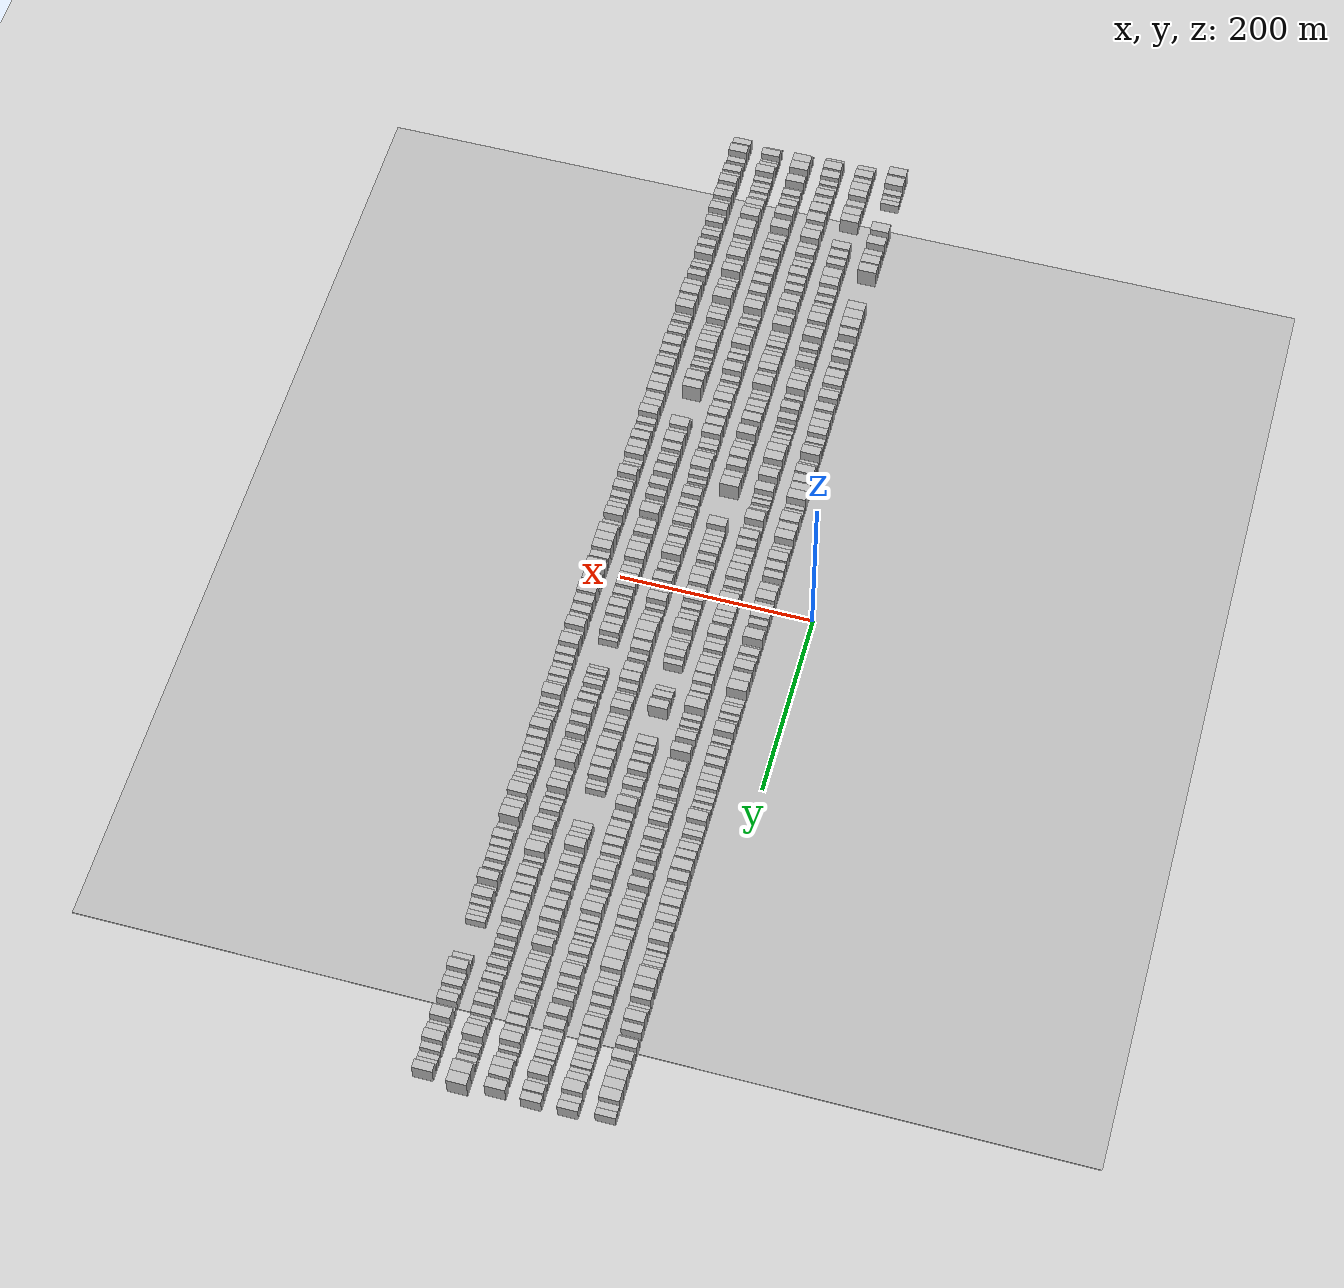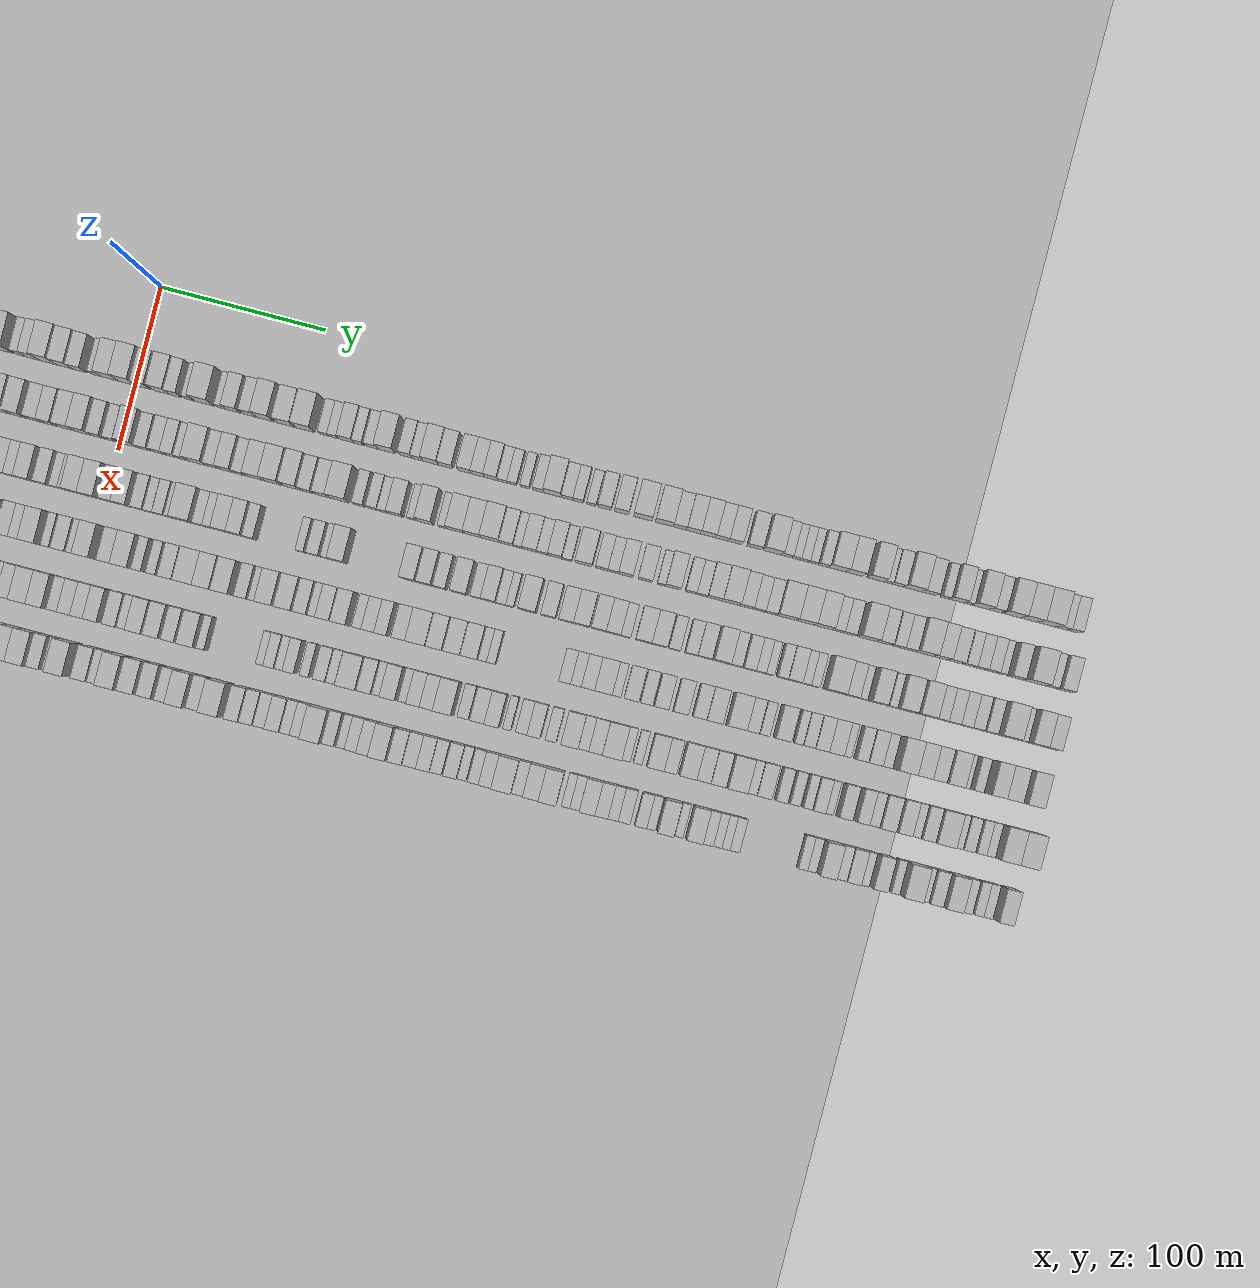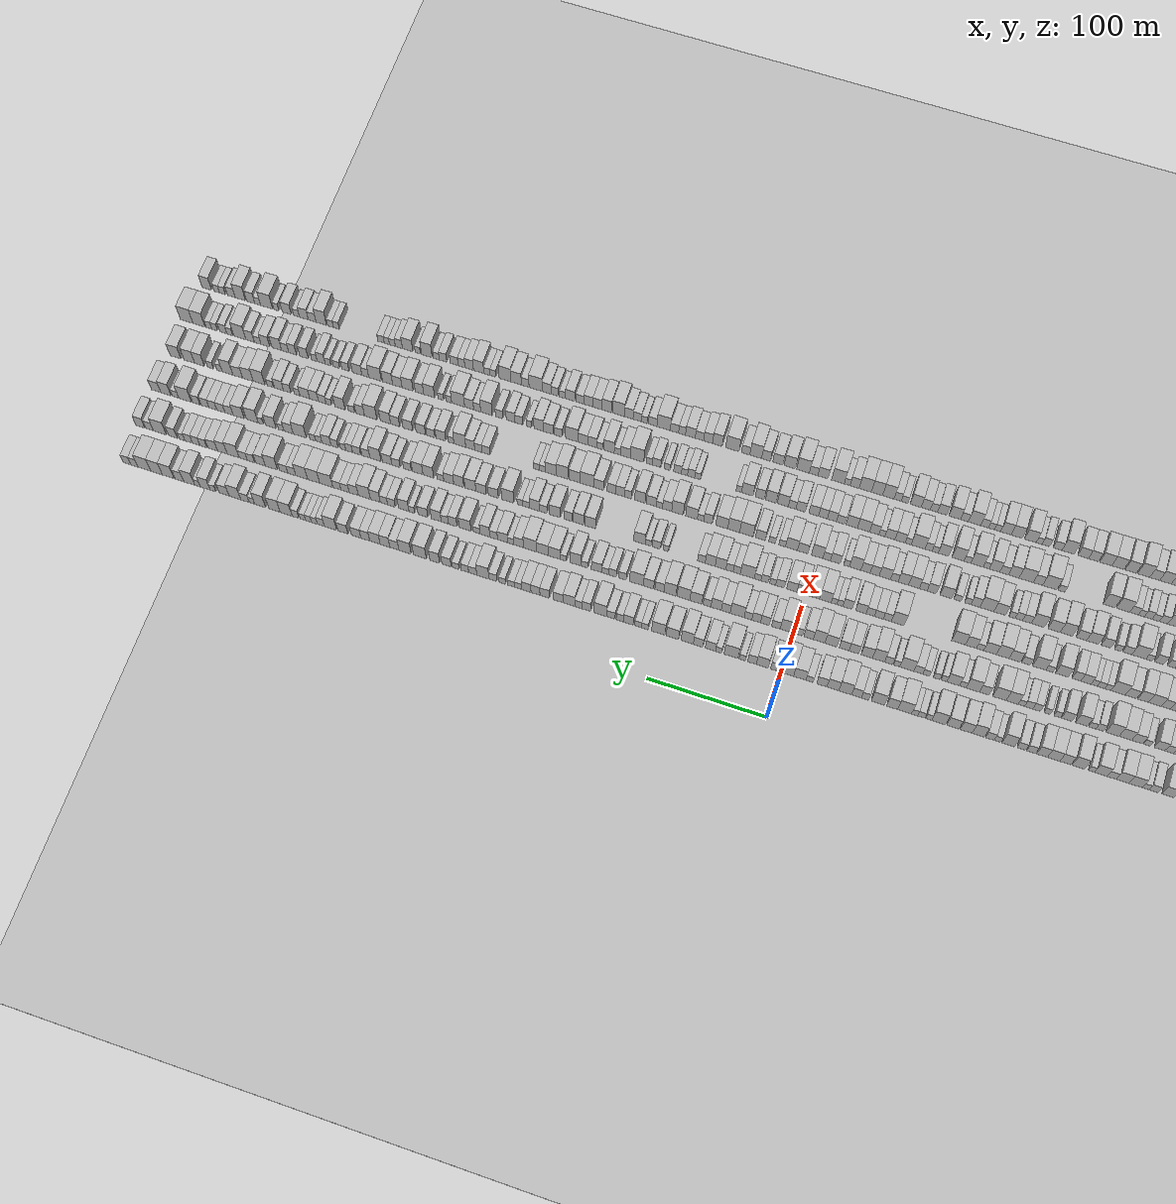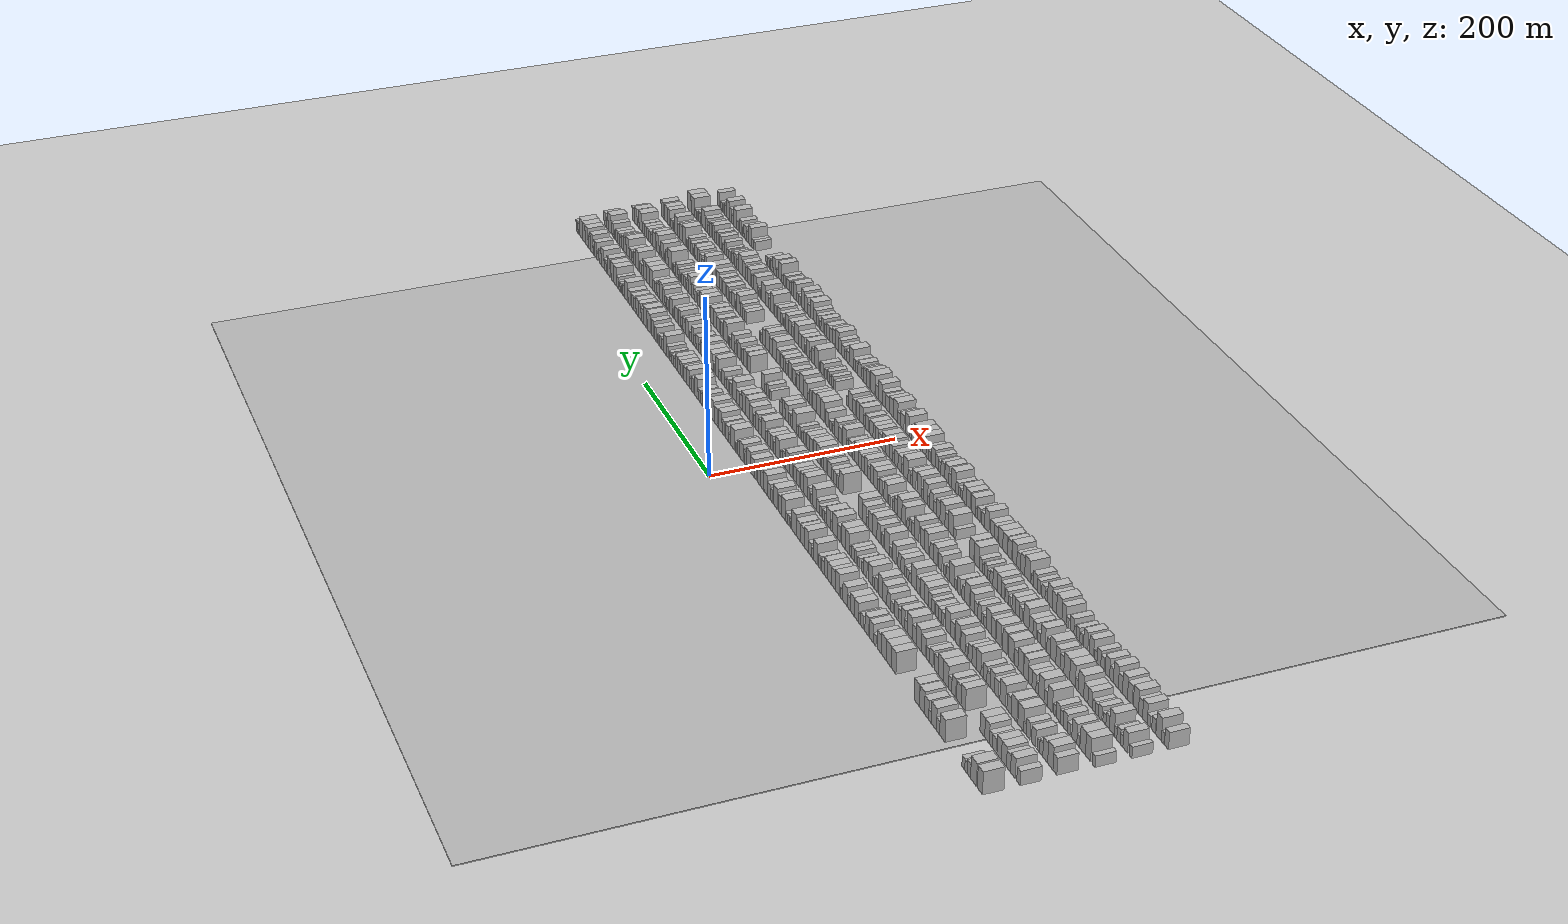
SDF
<?xml version="1.0" encoding="utf-8"?>

<sdf version="1.6">

   <world name="default">

      <gui fullscreen="0">

         <camera name="user_camera">

            <pose>-15 0 4.57585 0 0 0</pose>

            <view_controller>orbit</view_controller>

         </camera>

      </gui>

      <scene>

         <sky>

           <clouds>

             <speed>12</speed>

           </clouds>

         </sky>

         <ambient>0.4 0.4 0.4 1</ambient>

         <background>0.7 0.7 0.7 1</background>

         <shadows>1</shadows>

      </scene>

      <gravity>0 0 -9.8066</gravity>

      <magnetic_field>6e-06 2.3e-05 -4.2e-05</magnetic_field>

      <physics default="0" name="default_physics" type="ode">

         <ode>

            <solver>

               <type>quick</type>

               <iters>10</iters>

               <sor>1.0</sor>

               <use_dynamic_moi_rescaling>0</use_dynamic_moi_rescaling>

            </solver>

            <constraints>

               <cfm>0</cfm>

               <erp>0.2</erp>

               <contact_max_correcting_vel>100</contact_max_correcting_vel>

               <contact_surface_layer>0.001</contact_surface_layer>

            </constraints>

         </ode>

         <max_step_size>0.004</max_step_size>

         <real_time_factor>1</real_time_factor>

         <real_time_update_rate>250</real_time_update_rate>

      </physics>

      <light name="sun" type="directional">

         <cast_shadows>1</cast_shadows>

         <pose>0 0 10 0 0 0</pose>

         <diffuse>0.8 0.8 0.8 1</diffuse>

         <specular>0.2 0.2 0.2 1</specular>

         <attenuation>

            <range>1000</range>

            <constant>0.9</constant>

            <linear>0.01</linear>

            <quadratic>0.001</quadratic>

         </attenuation>

         <direction>-0.5 0.1 -0.9</direction>

      </light>

      <include>

         <name>ground_plane_1</name>

         <uri>model://HANNAS_ground_plane</uri>

         <pose>0 0 0  0 0 0</pose>

      </include>

      <include>

         <name>ground_plane_2</name>

         <uri>model://HANNAS_ground_plane</uri>

         <pose>100 0 0  0 0 0</pose>

      </include>

      <model name="building_1">

         <static>1</static>

         <pose frame="">50.0000 -564.7196 0 0.000000 0.000000 0.000000</pose>

         <link name="link">

            <pose frame="">0 0 12.00 0 0 0</pose>

            <collision name="collision">

               <geometry>

                  <box>

                     <size>20.0000 10.5607 24.0000</size>

                  </box>

               </geometry>

               <max_contacts>10</max_contacts>

               <surface>

                  <contact>

                     <ode/>

                  </contact>

                  <bounce/>

                  <friction>

                     <torsional>

                        <ode/>

                     </torsional>

                     <ode/>

                  </friction>

               </surface>

            </collision>

            <visual name="visual">

               <cast_shadows>0</cast_shadows>

               <geometry>

                  <box>

                     <size>20.0000 10.5607 24.0000</size>

                  </box>

               </geometry>

               <material>

                  <script>

                     <uri>model://HANNAS_wall/materials/scripts</uri>

                     <uri>model://HANNAS_wall/materials/textures</uri>

                     <name>vrc/HANNAS_wall</name>

                  </script>

               </material>

            </visual>

            <self_collide>0</self_collide>

            <enable_wind>0</enable_wind>

            <kinematic>0</kinematic>

         </link>

      </model>

      <model name="building_2">

         <static>1</static>

         <pose frame="">50.0000 -551.4736 0 0.000000 0.000000 0.000000</pose>

         <link name="link">

            <pose frame="">0 0 12.00 0 0 0</pose>

            <collision name="collision">

               <geometry>

                  <box>

                     <size>20.0000 11.9315 24.0000</size>

                  </box>

               </geometry>

               <max_contacts>10</max_contacts>

               <surface>

                  <contact>

                     <ode/>

                  </contact>

                  <bounce/>

                  <friction>

                     <torsional>

                        <ode/>

                     </torsional>

                     <ode/>

                  </friction>

               </surface>

            </collision>

            <visual name="visual">

               <cast_shadows>0</cast_shadows>

               <geometry>

                  <box>

                     <size>20.0000 11.9315 24.0000</size>

                  </box>

               </geometry>

               <material>

                  <script>

                     <uri>model://HANNAS_wall/materials/scripts</uri>

                     <uri>model://HANNAS_wall/materials/textures</uri>

                     <name>vrc/HANNAS_wall</name>

                  </script>

               </material>

            </visual>

            <self_collide>0</self_collide>

            <enable_wind>0</enable_wind>

            <kinematic>0</kinematic>

         </link>

      </model>

      <model name="building_3">

         <static>1</static>

         <pose frame="">50.0000 -542.0837 0 0.000000 0.000000 0.000000</pose>

         <link name="link">

            <pose frame="">0 0 7.50 0 0 0</pose>

            <collision name="collision">

               <geometry>

                  <box>

                     <size>20.0000 6.8483 15.0000</size>

                  </box>

               </geometry>

               <max_contacts>10</max_contacts>

               <surface>

                  <contact>

                     <ode/>

                  </contact>

                  <bounce/>

                  <friction>

                     <torsional>

                        <ode/>

                     </torsional>

                     <ode/>

                  </friction>

               </surface>

            </collision>

            <visual name="visual">

               <cast_shadows>0</cast_shadows>

               <geometry>

                  <box>

                     <size>20.0000 6.8483 15.0000</size>

                  </box>

               </geometry>

               <material>

                  <script>

                     <uri>model://HANNAS_wall/materials/scripts</uri>

                     <uri>model://HANNAS_wall/materials/textures</uri>

                     <name>vrc/HANNAS_wall</name>

                  </script>

               </material>

            </visual>

            <self_collide>0</self_collide>

            <enable_wind>0</enable_wind>

            <kinematic>0</kinematic>

         </link>

      </model>

      <model name="building_4">

         <static>1</static>

         <pose frame="">50.0000 -536.0153 0 0.000000 0.000000 0.000000</pose>

         <link name="link">

            <pose frame="">0 0 6.00 0 0 0</pose>

            <collision name="collision">

               <geometry>

                  <box>

                     <size>20.0000 5.2885 12.0000</size>

                  </box>

               </geometry>

               <max_contacts>10</max_contacts>

               <surface>

                  <contact>

                     <ode/>

                  </contact>

                  <bounce/>

                  <friction>

                     <torsional>

                        <ode/>

                     </torsional>

                     <ode/>

                  </friction>

               </surface>

            </collision>

            <visual name="visual">

               <cast_shadows>0</cast_shadows>

               <geometry>

                  <box>

                     <size>20.0000 5.2885 12.0000</size>

                  </box>

               </geometry>

               <material>

                  <script>

                     <uri>model://HANNAS_wall/materials/scripts</uri>

                     <uri>model://HANNAS_wall/materials/textures</uri>

                     <name>vrc/HANNAS_wall</name>

                  </script>

               </material>

            </visual>

            <self_collide>0</self_collide>

            <enable_wind>0</enable_wind>

            <kinematic>0</kinematic>

         </link>

      </model>

      <model name="building_5">

         <static>1</static>

         <pose frame="">50.0000 -530.3753 0 0.000000 0.000000 0.000000</pose>

         <link name="link">

            <pose frame="">0 0 6.00 0 0 0</pose>

            <collision name="collision">

               <geometry>

                  <box>

                     <size>20.0000 5.9915 12.0000</size>

                  </box>

               </geometry>

               <max_contacts>10</max_contacts>

               <surface>

                  <contact>

                     <ode/>

                  </contact>

                  <bounce/>

                  <friction>

                     <torsional>

                        <ode/>

                     </torsional>

                     <ode/>

                  </friction>

               </surface>

            </collision>

            <visual name="visual">

               <cast_shadows>0</cast_shadows>

               <geometry>

                  <box>

                     <size>20.0000 5.9915 12.0000</size>

                  </box>

               </geometry>

               <material>

                  <script>

                     <uri>model://HANNAS_wall/materials/scripts</uri>

                     <uri>model://HANNAS_wall/materials/textures</uri>

                     <name>vrc/HANNAS_wall</name>

                  </script>

               </material>

            </visual>

            <self_collide>0</self_collide>

            <enable_wind>0</enable_wind>

            <kinematic>0</kinematic>

         </link>

      </model>

      <model name="building_6">

         <static>1</static>

         <pose frame="">50.0000 -485.9031 0 0.000000 0.000000 0.000000</pose>

         <link name="link">

            <pose frame="">0 0 12.00 0 0 0</pose>

            <collision name="collision">

               <geometry>

                  <box>

                     <size>20.0000 11.6509 24.0000</size>

                  </box>

               </geometry>

               <max_contacts>10</max_contacts>

               <surface>

                  <contact>

                     <ode/>

                  </contact>

                  <bounce/>

                  <friction>

                     <torsional>

                        <ode/>

                     </torsional>

                     <ode/>

                  </friction>

               </surface>

            </collision>

            <visual name="visual">

               <cast_shadows>0</cast_shadows>

               <geometry>

                  <box>

                     <size>20.0000 11.6509 24.0000</size>

                  </box>

               </geometry>

               <material>

                  <script>

                     <uri>model://HANNAS_wall/materials/scripts</uri>

                     <uri>model://HANNAS_wall/materials/textures</uri>

                     <name>vrc/HANNAS_wall</name>

                  </script>

               </material>

            </visual>

            <self_collide>0</self_collide>

            <enable_wind>0</enable_wind>

            <kinematic>0</kinematic>

         </link>

      </model>

      <model name="building_7">

         <static>1</static>

         <pose frame="">50.0000 -476.6846 0 0.000000 0.000000 0.000000</pose>

         <link name="link">

            <pose frame="">0 0 7.50 0 0 0</pose>

            <collision name="collision">

               <geometry>

                  <box>

                     <size>20.0000 6.7861 15.0000</size>

                  </box>

               </geometry>

               <max_contacts>10</max_contacts>

               <surface>

                  <contact>

                     <ode/>

                  </contact>

                  <bounce/>

                  <friction>

                     <torsional>

                        <ode/>

                     </torsional>

                     <ode/>

                  </friction>

               </surface>

            </collision>

            <visual name="visual">

               <cast_shadows>0</cast_shadows>

               <geometry>

                  <box>

                     <size>20.0000 6.7861 15.0000</size>

                  </box>

               </geometry>

               <material>

                  <script>

                     <uri>model://HANNAS_wall/materials/scripts</uri>

                     <uri>model://HANNAS_wall/materials/textures</uri>

                     <name>vrc/HANNAS_wall</name>

                  </script>

               </material>

            </visual>

            <self_collide>0</self_collide>

            <enable_wind>0</enable_wind>

            <kinematic>0</kinematic>

         </link>

      </model>

      <model name="building_8">

         <static>1</static>

         <pose frame="">50.0000 -467.6804 0 0.000000 0.000000 0.000000</pose>

         <link name="link">

            <pose frame="">0 0 12.00 0 0 0</pose>

            <collision name="collision">

               <geometry>

                  <box>

                     <size>20.0000 11.2222 24.0000</size>

                  </box>

               </geometry>

               <max_contacts>10</max_contacts>

               <surface>

                  <contact>

                     <ode/>

                  </contact>

                  <bounce/>

                  <friction>

                     <torsional>

                        <ode/>

                     </torsional>

                     <ode/>

                  </friction>

               </surface>

            </collision>

            <visual name="visual">

               <cast_shadows>0</cast_shadows>

               <geometry>

                  <box>

                     <size>20.0000 11.2222 24.0000</size>

                  </box>

               </geometry>

               <material>

                  <script>

                     <uri>model://HANNAS_wall/materials/scripts</uri>

                     <uri>model://HANNAS_wall/materials/textures</uri>

                     <name>vrc/HANNAS_wall</name>

                  </script>

               </material>

            </visual>

            <self_collide>0</self_collide>

            <enable_wind>0</enable_wind>

            <kinematic>0</kinematic>

         </link>

      </model>

      <model name="building_9">

         <static>1</static>

         <pose frame="">50.0000 -459.1418 0 0.000000 0.000000 0.000000</pose>

         <link name="link">

            <pose frame="">0 0 6.00 0 0 0</pose>

            <collision name="collision">

               <geometry>

                  <box>

                     <size>20.0000 5.8550 12.0000</size>

                  </box>

               </geometry>

               <max_contacts>10</max_contacts>

               <surface>

                  <contact>

                     <ode/>

                  </contact>

                  <bounce/>

                  <friction>

                     <torsional>

                        <ode/>

                     </torsional>

                     <ode/>

                  </friction>

               </surface>

            </collision>

            <visual name="visual">

               <cast_shadows>0</cast_shadows>

               <geometry>

                  <box>

                     <size>20.0000 5.8550 12.0000</size>

                  </box>

               </geometry>

               <material>

                  <script>

                     <uri>model://HANNAS_wall/materials/scripts</uri>

                     <uri>model://HANNAS_wall/materials/textures</uri>

                     <name>vrc/HANNAS_wall</name>

                  </script>

               </material>

            </visual>

            <self_collide>0</self_collide>

            <enable_wind>0</enable_wind>

            <kinematic>0</kinematic>

         </link>

      </model>

      <model name="building_10">

         <static>1</static>

         <pose frame="">50.0000 -451.6347 0 0.000000 0.000000 0.000000</pose>

         <link name="link">

            <pose frame="">0 0 10.50 0 0 0</pose>

            <collision name="collision">

               <geometry>

                  <box>

                     <size>20.0000 9.1591 21.0000</size>

                  </box>

               </geometry>

               <max_contacts>10</max_contacts>

               <surface>

                  <contact>

                     <ode/>

                  </contact>

                  <bounce/>

                  <friction>

                     <torsional>

                        <ode/>

                     </torsional>

                     <ode/>

                  </friction>

               </surface>

            </collision>

            <visual name="visual">

               <cast_shadows>0</cast_shadows>

               <geometry>

                  <box>

                     <size>20.0000 9.1591 21.0000</size>

                  </box>

               </geometry>

               <material>

                  <script>

                     <uri>model://HANNAS_wall/materials/scripts</uri>

                     <uri>model://HANNAS_wall/materials/textures</uri>

                     <name>vrc/HANNAS_wall</name>

                  </script>

               </material>

            </visual>

            <self_collide>0</self_collide>

            <enable_wind>0</enable_wind>

            <kinematic>0</kinematic>

         </link>

      </model>

      <model name="building_11">

         <static>1</static>

         <pose frame="">50.0000 -441.5983 0 0.000000 0.000000 0.000000</pose>

         <link name="link">

            <pose frame="">0 0 12.00 0 0 0</pose>

            <collision name="collision">

               <geometry>

                  <box>

                     <size>20.0000 10.9137 24.0000</size>

                  </box>

               </geometry>

               <max_contacts>10</max_contacts>

               <surface>

                  <contact>

                     <ode/>

                  </contact>

                  <bounce/>

                  <friction>

                     <torsional>

                        <ode/>

                     </torsional>

                     <ode/>

                  </friction>

               </surface>

            </collision>

            <visual name="visual">

               <cast_shadows>0</cast_shadows>

               <geometry>

                  <box>

                     <size>20.0000 10.9137 24.0000</size>

                  </box>

               </geometry>

               <material>

                  <script>

                     <uri>model://HANNAS_wall/materials/scripts</uri>

                     <uri>model://HANNAS_wall/materials/textures</uri>

                     <name>vrc/HANNAS_wall</name>

                  </script>

               </material>

            </visual>

            <self_collide>0</self_collide>

            <enable_wind>0</enable_wind>

            <kinematic>0</kinematic>

         </link>

      </model>

      <model name="building_12">

         <static>1</static>

         <pose frame="">50.0000 -429.5720 0 0.000000 0.000000 0.000000</pose>

         <link name="link">

            <pose frame="">0 0 12.00 0 0 0</pose>

            <collision name="collision">

               <geometry>

                  <box>

                     <size>20.0000 11.1389 24.0000</size>

                  </box>

               </geometry>

               <max_contacts>10</max_contacts>

               <surface>

                  <contact>

                     <ode/>

                  </contact>

                  <bounce/>

                  <friction>

                     <torsional>

                        <ode/>

                     </torsional>

                     <ode/>

                  </friction>

               </surface>

            </collision>

            <visual name="visual">

               <cast_shadows>0</cast_shadows>

               <geometry>

                  <box>

                     <size>20.0000 11.1389 24.0000</size>

                  </box>

               </geometry>

               <material>

                  <script>

                     <uri>model://HANNAS_wall/materials/scripts</uri>

                     <uri>model://HANNAS_wall/materials/textures</uri>

                     <name>vrc/HANNAS_wall</name>

                  </script>

               </material>

            </visual>

            <self_collide>0</self_collide>

            <enable_wind>0</enable_wind>

            <kinematic>0</kinematic>

         </link>

      </model>

      <model name="building_13">

         <static>1</static>

         <pose frame="">50.0000 -377.5228 0 0.000000 0.000000 0.000000</pose>

         <link name="link">

            <pose frame="">0 0 12.00 0 0 0</pose>

            <collision name="collision">

               <geometry>

                  <box>

                     <size>20.0000 10.3199 24.0000</size>

                  </box>

               </geometry>

               <max_contacts>10</max_contacts>

               <surface>

                  <contact>

                     <ode/>

                  </contact>

                  <bounce/>

                  <friction>

                     <torsional>

                        <ode/>

                     </torsional>

                     <ode/>

                  </friction>

               </surface>

            </collision>

            <visual name="visual">

               <cast_shadows>0</cast_shadows>

               <geometry>

                  <box>

                     <size>20.0000 10.3199 24.0000</size>

                  </box>

               </geometry>

               <material>

                  <script>

                     <uri>model://HANNAS_wall/materials/scripts</uri>

                     <uri>model://HANNAS_wall/materials/textures</uri>

                     <name>vrc/HANNAS_wall</name>

                  </script>

               </material>

            </visual>

            <self_collide>0</self_collide>

            <enable_wind>0</enable_wind>

            <kinematic>0</kinematic>

         </link>

      </model>

      <model name="building_14">

         <static>1</static>

         <pose frame="">50.0000 -366.5025 0 0.000000 0.000000 0.000000</pose>

         <link name="link">

            <pose frame="">0 0 12.00 0 0 0</pose>

            <collision name="collision">

               <geometry>

                  <box>

                     <size>20.0000 11.7208 24.0000</size>

                  </box>

               </geometry>

               <max_contacts>10</max_contacts>

               <surface>

                  <contact>

                     <ode/>

                  </contact>

                  <bounce/>

                  <friction>

                     <torsional>

                        <ode/>

                     </torsional>

                     <ode/>

                  </friction>

               </surface>

            </collision>

            <visual name="visual">

               <cast_shadows>0</cast_shadows>

               <geometry>

                  <box>

                     <size>20.0000 11.7208 24.0000</size>

                  </box>

               </geometry>

               <material>

                  <script>

                     <uri>model://HANNAS_wall/materials/scripts</uri>

                     <uri>model://HANNAS_wall/materials/textures</uri>

                     <name>vrc/HANNAS_wall</name>

                  </script>

               </material>

            </visual>

            <self_collide>0</self_collide>

            <enable_wind>0</enable_wind>

            <kinematic>0</kinematic>

         </link>

      </model>

      <model name="building_15">

         <static>1</static>

         <pose frame="">50.0000 -354.6723 0 0.000000 0.000000 0.000000</pose>

         <link name="link">

            <pose frame="">0 0 12.00 0 0 0</pose>

            <collision name="collision">

               <geometry>

                  <box>

                     <size>20.0000 11.9396 24.0000</size>

                  </box>

               </geometry>

               <max_contacts>10</max_contacts>

               <surface>

                  <contact>

                     <ode/>

                  </contact>

                  <bounce/>

                  <friction>

                     <torsional>

                        <ode/>

                     </torsional>

                     <ode/>

                  </friction>

               </surface>

            </collision>

            <visual name="visual">

               <cast_shadows>0</cast_shadows>

               <geometry>

                  <box>

                     <size>20.0000 11.9396 24.0000</size>

                  </box>

               </geometry>

               <material>

                  <script>

                     <uri>model://HANNAS_wall/materials/scripts</uri>

                     <uri>model://HANNAS_wall/materials/textures</uri>

                     <name>vrc/HANNAS_wall</name>

                  </script>

               </material>

            </visual>

            <self_collide>0</self_collide>

            <enable_wind>0</enable_wind>

            <kinematic>0</kinematic>

         </link>

      </model>

      <model name="building_16">

         <static>1</static>

         <pose frame="">50.0000 -343.8699 0 0.000000 0.000000 0.000000</pose>

         <link name="link">

            <pose frame="">0 0 10.50 0 0 0</pose>

            <collision name="collision">

               <geometry>

                  <box>

                     <size>20.0000 9.6652 21.0000</size>

                  </box>

               </geometry>

               <max_contacts>10</max_contacts>

               <surface>

                  <contact>

                     <ode/>

                  </contact>

                  <bounce/>

                  <friction>

                     <torsional>

                        <ode/>

                     </torsional>

                     <ode/>

                  </friction>

               </surface>

            </collision>

            <visual name="visual">

               <cast_shadows>0</cast_shadows>

               <geometry>

                  <box>

                     <size>20.0000 9.6652 21.0000</size>

                  </box>

               </geometry>

               <material>

                  <script>

                     <uri>model://HANNAS_wall/materials/scripts</uri>

                     <uri>model://HANNAS_wall/materials/textures</uri>

                     <name>vrc/HANNAS_wall</name>

                  </script>

               </material>

            </visual>

            <self_collide>0</self_collide>

            <enable_wind>0</enable_wind>

            <kinematic>0</kinematic>

         </link>

      </model>

      <model name="building_17">

         <static>1</static>

         <pose frame="">50.0000 -333.1241 0 0.000000 0.000000 0.000000</pose>

         <link name="link">

            <pose frame="">0 0 6.00 0 0 0</pose>

            <collision name="collision">

               <geometry>

                  <box>

                     <size>20.0000 5.8263 12.0000</size>

                  </box>

               </geometry>

               <max_contacts>10</max_contacts>

               <surface>

                  <contact>

                     <ode/>

                  </contact>

                  <bounce/>

                  <friction>

                     <torsional>

                        <ode/>

                     </torsional>

                     <ode/>

                  </friction>

               </surface>

            </collision>

            <visual name="visual">

               <cast_shadows>0</cast_shadows>

               <geometry>

                  <box>

                     <size>20.0000 5.8263 12.0000</size>

                  </box>

               </geometry>

               <material>

                  <script>

                     <uri>model://HANNAS_wall/materials/scripts</uri>

                     <uri>model://HANNAS_wall/materials/textures</uri>

                     <name>vrc/HANNAS_wall</name>

                  </script>

               </material>

            </visual>

            <self_collide>0</self_collide>

            <enable_wind>0</enable_wind>

            <kinematic>0</kinematic>

         </link>

      </model>

      <model name="building_18">

         <static>1</static>

         <pose frame="">50.0000 -325.6242 0 0.000000 0.000000 0.000000</pose>

         <link name="link">

            <pose frame="">0 0 10.50 0 0 0</pose>

            <collision name="collision">

               <geometry>

                  <box>

                     <size>20.0000 9.1735 21.0000</size>

                  </box>

               </geometry>

               <max_contacts>10</max_contacts>

               <surface>

                  <contact>

                     <ode/>

                  </contact>

                  <bounce/>

                  <friction>

                     <torsional>

                        <ode/>

                     </torsional>

                     <ode/>

                  </friction>

               </surface>

            </collision>

            <visual name="visual">

               <cast_shadows>0</cast_shadows>

               <geometry>

                  <box>

                     <size>20.0000 9.1735 21.0000</size>

                  </box>

               </geometry>

               <material>

                  <script>

                     <uri>model://HANNAS_wall/materials/scripts</uri>

                     <uri>model://HANNAS_wall/materials/textures</uri>

                     <name>vrc/HANNAS_wall</name>

                  </script>

               </material>

            </visual>

            <self_collide>0</self_collide>

            <enable_wind>0</enable_wind>

            <kinematic>0</kinematic>

         </link>

      </model>

      <model name="building_19">

         <static>1</static>

         <pose frame="">50.0000 -314.3347 0 0.000000 0.000000 0.000000</pose>

         <link name="link">

            <pose frame="">0 0 10.50 0 0 0</pose>

            <collision name="collision">

               <geometry>

                  <box>

                     <size>20.0000 9.4055 21.0000</size>

                  </box>

               </geometry>

               <max_contacts>10</max_contacts>

               <surface>

                  <contact>

                     <ode/>

                  </contact>

                  <bounce/>

                  <friction>

                     <torsional>

                        <ode/>

                     </torsional>

                     <ode/>

                  </friction>

               </surface>

            </collision>

            <visual name="visual">

               <cast_shadows>0</cast_shadows>

               <geometry>

                  <box>

                     <size>20.0000 9.4055 21.0000</size>

                  </box>

               </geometry>

               <material>

                  <script>

                     <uri>model://HANNAS_wall/materials/scripts</uri>

                     <uri>model://HANNAS_wall/materials/textures</uri>

                     <name>vrc/HANNAS_wall</name>

                  </script>

               </material>

            </visual>

            <self_collide>0</self_collide>

            <enable_wind>0</enable_wind>

            <kinematic>0</kinematic>

         </link>

      </model>

      <model name="building_20">

         <static>1</static>

         <pose frame="">50.0000 -303.0996 0 0.000000 0.000000 0.000000</pose>

         <link name="link">

            <pose frame="">0 0 7.50 0 0 0</pose>

            <collision name="collision">

               <geometry>

                  <box>

                     <size>20.0000 7.0647 15.0000</size>

                  </box>

               </geometry>

               <max_contacts>10</max_contacts>

               <surface>

                  <contact>

                     <ode/>

                  </contact>

                  <bounce/>

                  <friction>

                     <torsional>

                        <ode/>

                     </torsional>

                     <ode/>

                  </friction>

               </surface>

            </collision>

            <visual name="visual">

               <cast_shadows>0</cast_shadows>

               <geometry>

                  <box>

                     <size>20.0000 7.0647 15.0000</size>

                  </box>

               </geometry>

               <material>

                  <script>

                     <uri>model://HANNAS_wall/materials/scripts</uri>

                     <uri>model://HANNAS_wall/materials/textures</uri>

                     <name>vrc/HANNAS_wall</name>

                  </script>

               </material>

            </visual>

            <self_collide>0</self_collide>

            <enable_wind>0</enable_wind>

            <kinematic>0</kinematic>

         </link>

      </model>

      <model name="building_21">

         <static>1</static>

         <pose frame="">50.0000 -296.7143 0 0.000000 0.000000 0.000000</pose>

         <link name="link">

            <pose frame="">0 0 6.00 0 0 0</pose>

            <collision name="collision">

               <geometry>

                  <box>

                     <size>20.0000 5.7060 12.0000</size>

                  </box>

               </geometry>

               <max_contacts>10</max_contacts>

               <surface>

                  <contact>

                     <ode/>

                  </contact>

                  <bounce/>

                  <friction>

                     <torsional>

                        <ode/>

                     </torsional>

                     <ode/>

                  </friction>

               </surface>

            </collision>

            <visual name="visual">

               <cast_shadows>0</cast_shadows>

               <geometry>

                  <box>

                     <size>20.0000 5.7060 12.0000</size>

                  </box>

               </geometry>

               <material>

                  <script>

                     <uri>model://HANNAS_wall/materials/scripts</uri>

                     <uri>model://HANNAS_wall/materials/textures</uri>

                     <name>vrc/HANNAS_wall</name>

                  </script>

               </material>

            </visual>

            <self_collide>0</self_collide>

            <enable_wind>0</enable_wind>

            <kinematic>0</kinematic>

         </link>

      </model>

      <model name="building_22">

         <static>1</static>

         <pose frame="">50.0000 -288.7204 0 0.000000 0.000000 0.000000</pose>

         <link name="link">

            <pose frame="">0 0 10.50 0 0 0</pose>

            <collision name="collision">

               <geometry>

                  <box>

                     <size>20.0000 10.2817 21.0000</size>

                  </box>

               </geometry>

               <max_contacts>10</max_contacts>

               <surface>

                  <contact>

                     <ode/>

                  </contact>

                  <bounce/>

                  <friction>

                     <torsional>

                        <ode/>

                     </torsional>

                     <ode/>

                  </friction>

               </surface>

            </collision>

            <visual name="visual">

               <cast_shadows>0</cast_shadows>

               <geometry>

                  <box>

                     <size>20.0000 10.2817 21.0000</size>

                  </box>

               </geometry>

               <material>

                  <script>

                     <uri>model://HANNAS_wall/materials/scripts</uri>

                     <uri>model://HANNAS_wall/materials/textures</uri>

                     <name>vrc/HANNAS_wall</name>

                  </script>

               </material>

            </visual>

            <self_collide>0</self_collide>

            <enable_wind>0</enable_wind>

            <kinematic>0</kinematic>

         </link>

      </model>

      <model name="building_23">

         <static>1</static>

         <pose frame="">50.0000 -278.4777 0 0.000000 0.000000 0.000000</pose>

         <link name="link">

            <pose frame="">0 0 10.50 0 0 0</pose>

            <collision name="collision">

               <geometry>

                  <box>

                     <size>20.0000 10.2036 21.0000</size>

                  </box>

               </geometry>

               <max_contacts>10</max_contacts>

               <surface>

                  <contact>

                     <ode/>

                  </contact>

                  <bounce/>

                  <friction>

                     <torsional>

                        <ode/>

                     </torsional>

                     <ode/>

                  </friction>

               </surface>

            </collision>

            <visual name="visual">

               <cast_shadows>0</cast_shadows>

               <geometry>

                  <box>

                     <size>20.0000 10.2036 21.0000</size>

                  </box>

               </geometry>

               <material>

                  <script>

                     <uri>model://HANNAS_wall/materials/scripts</uri>

                     <uri>model://HANNAS_wall/materials/textures</uri>

                     <name>vrc/HANNAS_wall</name>

                  </script>

               </material>

            </visual>

            <self_collide>0</self_collide>

            <enable_wind>0</enable_wind>

            <kinematic>0</kinematic>

         </link>

      </model>

      <model name="building_24">

         <static>1</static>

         <pose frame="">50.0000 -269.7830 0 0.000000 0.000000 0.000000</pose>

         <link name="link">

            <pose frame="">0 0 7.50 0 0 0</pose>

            <collision name="collision">

               <geometry>

                  <box>

                     <size>20.0000 7.1858 15.0000</size>

                  </box>

               </geometry>

               <max_contacts>10</max_contacts>

               <surface>

                  <contact>

                     <ode/>

                  </contact>

                  <bounce/>

                  <friction>

                     <torsional>

                        <ode/>

                     </torsional>

                     <ode/>

                  </friction>

               </surface>

            </collision>

            <visual name="visual">

               <cast_shadows>0</cast_shadows>

               <geometry>

                  <box>

                     <size>20.0000 7.1858 15.0000</size>

                  </box>

               </geometry>

               <material>

                  <script>

                     <uri>model://HANNAS_wall/materials/scripts</uri>

                     <uri>model://HANNAS_wall/materials/textures</uri>

                     <name>vrc/HANNAS_wall</name>

                  </script>

               </material>

            </visual>

            <self_collide>0</self_collide>

            <enable_wind>0</enable_wind>

            <kinematic>0</kinematic>

         </link>

      </model>

      <model name="building_25">

         <static>1</static>

         <pose frame="">50.0000 -260.9441 0 0.000000 0.000000 0.000000</pose>

         <link name="link">

            <pose frame="">0 0 10.50 0 0 0</pose>

            <collision name="collision">

               <geometry>

                  <box>

                     <size>20.0000 10.4920 21.0000</size>

                  </box>

               </geometry>

               <max_contacts>10</max_contacts>

               <surface>

                  <contact>

                     <ode/>

                  </contact>

                  <bounce/>

                  <friction>

                     <torsional>

                        <ode/>

                     </torsional>

                     <ode/>

                  </friction>

               </surface>

            </collision>

            <visual name="visual">

               <cast_shadows>0</cast_shadows>

               <geometry>

                  <box>

                     <size>20.0000 10.4920 21.0000</size>

                  </box>

               </geometry>

               <material>

                  <script>

                     <uri>model://HANNAS_wall/materials/scripts</uri>

                     <uri>model://HANNAS_wall/materials/textures</uri>

                     <name>vrc/HANNAS_wall</name>

                  </script>

               </material>

            </visual>

            <self_collide>0</self_collide>

            <enable_wind>0</enable_wind>

            <kinematic>0</kinematic>

         </link>

      </model>

      <model name="building_26">

         <static>1</static>

         <pose frame="">50.0000 -253.2410 0 0.000000 0.000000 0.000000</pose>

         <link name="link">

            <pose frame="">0 0 6.00 0 0 0</pose>

            <collision name="collision">

               <geometry>

                  <box>

                     <size>20.0000 4.9143 12.0000</size>

                  </box>

               </geometry>

               <max_contacts>10</max_contacts>

               <surface>

                  <contact>

                     <ode/>

                  </contact>

                  <bounce/>

                  <friction>

                     <torsional>

                        <ode/>

                     </torsional>

                     <ode/>

                  </friction>

               </surface>

            </collision>

            <visual name="visual">

               <cast_shadows>0</cast_shadows>

               <geometry>

                  <box>

                     <size>20.0000 4.9143 12.0000</size>

                  </box>

               </geometry>

               <material>

                  <script>

                     <uri>model://HANNAS_wall/materials/scripts</uri>

                     <uri>model://HANNAS_wall/materials/textures</uri>

                     <name>vrc/HANNAS_wall</name>

                  </script>

               </material>

            </visual>

            <self_collide>0</self_collide>

            <enable_wind>0</enable_wind>

            <kinematic>0</kinematic>

         </link>

      </model>

      <model name="building_27">

         <static>1</static>

         <pose frame="">50.0000 -242.8196 0 0.000000 0.000000 0.000000</pose>

         <link name="link">

            <pose frame="">0 0 12.00 0 0 0</pose>

            <collision name="collision">

               <geometry>

                  <box>

                     <size>20.0000 9.9284 24.0000</size>

                  </box>

               </geometry>

               <max_contacts>10</max_contacts>

               <surface>

                  <contact>

                     <ode/>

                  </contact>

                  <bounce/>

                  <friction>

                     <torsional>

                        <ode/>

                     </torsional>

                     <ode/>

                  </friction>

               </surface>

            </collision>

            <visual name="visual">

               <cast_shadows>0</cast_shadows>

               <geometry>

                  <box>

                     <size>20.0000 9.9284 24.0000</size>

                  </box>

               </geometry>

               <material>

                  <script>

                     <uri>model://HANNAS_wall/materials/scripts</uri>

                     <uri>model://HANNAS_wall/materials/textures</uri>

                     <name>vrc/HANNAS_wall</name>

                  </script>

               </material>

            </visual>

            <self_collide>0</self_collide>

            <enable_wind>0</enable_wind>

            <kinematic>0</kinematic>

         </link>

      </model>

      <model name="building_28">

         <static>1</static>

         <pose frame="">50.0000 -232.4057 0 0.000000 0.000000 0.000000</pose>

         <link name="link">

            <pose frame="">0 0 10.50 0 0 0</pose>

            <collision name="collision">

               <geometry>

                  <box>

                     <size>20.0000 8.8994 21.0000</size>

                  </box>

               </geometry>

               <max_contacts>10</max_contacts>

               <surface>

                  <contact>

                     <ode/>

                  </contact>

                  <bounce/>

                  <friction>

                     <torsional>

                        <ode/>

                     </torsional>

                     <ode/>

                  </friction>

               </surface>

            </collision>

            <visual name="visual">

               <cast_shadows>0</cast_shadows>

               <geometry>

                  <box>

                     <size>20.0000 8.8994 21.0000</size>

                  </box>

               </geometry>

               <material>

                  <script>

                     <uri>model://HANNAS_wall/materials/scripts</uri>

                     <uri>model://HANNAS_wall/materials/textures</uri>

                     <name>vrc/HANNAS_wall</name>

                  </script>

               </material>

            </visual>

            <self_collide>0</self_collide>

            <enable_wind>0</enable_wind>

            <kinematic>0</kinematic>

         </link>

      </model>

      <model name="building_29">

         <static>1</static>

         <pose frame="">50.0000 -222.9685 0 0.000000 0.000000 0.000000</pose>

         <link name="link">

            <pose frame="">0 0 10.50 0 0 0</pose>

            <collision name="collision">

               <geometry>

                  <box>

                     <size>20.0000 9.9748 21.0000</size>

                  </box>

               </geometry>

               <max_contacts>10</max_contacts>

               <surface>

                  <contact>

                     <ode/>

                  </contact>

                  <bounce/>

                  <friction>

                     <torsional>

                        <ode/>

                     </torsional>

                     <ode/>

                  </friction>

               </surface>

            </collision>

            <visual name="visual">

               <cast_shadows>0</cast_shadows>

               <geometry>

                  <box>

                     <size>20.0000 9.9748 21.0000</size>

                  </box>

               </geometry>

               <material>

                  <script>

                     <uri>model://HANNAS_wall/materials/scripts</uri>

                     <uri>model://HANNAS_wall/materials/textures</uri>

                     <name>vrc/HANNAS_wall</name>

                  </script>

               </material>

            </visual>

            <self_collide>0</self_collide>

            <enable_wind>0</enable_wind>

            <kinematic>0</kinematic>

         </link>

      </model>

      <model name="building_30">

         <static>1</static>

         <pose frame="">50.0000 -213.6260 0 0.000000 0.000000 0.000000</pose>

         <link name="link">

            <pose frame="">0 0 10.50 0 0 0</pose>

            <collision name="collision">

               <geometry>

                  <box>

                     <size>20.0000 8.7103 21.0000</size>

                  </box>

               </geometry>

               <max_contacts>10</max_contacts>

               <surface>

                  <contact>

                     <ode/>

                  </contact>

                  <bounce/>

                  <friction>

                     <torsional>

                        <ode/>

                     </torsional>

                     <ode/>

                  </friction>

               </surface>

            </collision>

            <visual name="visual">

               <cast_shadows>0</cast_shadows>

               <geometry>

                  <box>

                     <size>20.0000 8.7103 21.0000</size>

                  </box>

               </geometry>

               <material>

                  <script>

                     <uri>model://HANNAS_wall/materials/scripts</uri>

                     <uri>model://HANNAS_wall/materials/textures</uri>

                     <name>vrc/HANNAS_wall</name>

                  </script>

               </material>

            </visual>

            <self_collide>0</self_collide>

            <enable_wind>0</enable_wind>

            <kinematic>0</kinematic>

         </link>

      </model>

      <model name="building_31">

         <static>1</static>

         <pose frame="">50.0000 -204.6919 0 0.000000 0.000000 0.000000</pose>

         <link name="link">

            <pose frame="">0 0 7.50 0 0 0</pose>

            <collision name="collision">

               <geometry>

                  <box>

                     <size>20.0000 7.1578 15.0000</size>

                  </box>

               </geometry>

               <max_contacts>10</max_contacts>

               <surface>

                  <contact>

                     <ode/>

                  </contact>

                  <bounce/>

                  <friction>

                     <torsional>

                        <ode/>

                     </torsional>

                     <ode/>

                  </friction>

               </surface>

            </collision>

            <visual name="visual">

               <cast_shadows>0</cast_shadows>

               <geometry>

                  <box>

                     <size>20.0000 7.1578 15.0000</size>

                  </box>

               </geometry>

               <material>

                  <script>

                     <uri>model://HANNAS_wall/materials/scripts</uri>

                     <uri>model://HANNAS_wall/materials/textures</uri>

                     <name>vrc/HANNAS_wall</name>

                  </script>

               </material>

            </visual>

            <self_collide>0</self_collide>

            <enable_wind>0</enable_wind>

            <kinematic>0</kinematic>

         </link>

      </model>

      <model name="building_32">

         <static>1</static>

         <pose frame="">50.0000 -196.6961 0 0.000000 0.000000 0.000000</pose>

         <link name="link">

            <pose frame="">0 0 7.50 0 0 0</pose>

            <collision name="collision">

               <geometry>

                  <box>

                     <size>20.0000 6.8339 15.0000</size>

                  </box>

               </geometry>

               <max_contacts>10</max_contacts>

               <surface>

                  <contact>

                     <ode/>

                  </contact>

                  <bounce/>

                  <friction>

                     <torsional>

                        <ode/>

                     </torsional>

                     <ode/>

                  </friction>

               </surface>

            </collision>

            <visual name="visual">

               <cast_shadows>0</cast_shadows>

               <geometry>

                  <box>

                     <size>20.0000 6.8339 15.0000</size>

                  </box>

               </geometry>

               <material>

                  <script>

                     <uri>model://HANNAS_wall/materials/scripts</uri>

                     <uri>model://HANNAS_wall/materials/textures</uri>

                     <name>vrc/HANNAS_wall</name>

                  </script>

               </material>

            </visual>

            <self_collide>0</self_collide>

            <enable_wind>0</enable_wind>

            <kinematic>0</kinematic>

         </link>

      </model>

      <model name="building_33">

         <static>1</static>

         <pose frame="">50.0000 -186.1568 0 0.000000 0.000000 0.000000</pose>

         <link name="link">

            <pose frame="">0 0 12.00 0 0 0</pose>

            <collision name="collision">

               <geometry>

                  <box>

                     <size>20.0000 10.2447 24.0000</size>

                  </box>

               </geometry>

               <max_contacts>10</max_contacts>

               <surface>

                  <contact>

                     <ode/>

                  </contact>

                  <bounce/>

                  <friction>

                     <torsional>

                        <ode/>

                     </torsional>

                     <ode/>

                  </friction>

               </surface>

            </collision>

            <visual name="visual">

               <cast_shadows>0</cast_shadows>

               <geometry>

                  <box>

                     <size>20.0000 10.2447 24.0000</size>

                  </box>

               </geometry>

               <material>

                  <script>

                     <uri>model://HANNAS_wall/materials/scripts</uri>

                     <uri>model://HANNAS_wall/materials/textures</uri>

                     <name>vrc/HANNAS_wall</name>

                  </script>

               </material>

            </visual>

            <self_collide>0</self_collide>

            <enable_wind>0</enable_wind>

            <kinematic>0</kinematic>

         </link>

      </model>

      <model name="building_34">

         <static>1</static>

         <pose frame="">50.0000 -177.4231 0 0.000000 0.000000 0.000000</pose>

         <link name="link">

            <pose frame="">0 0 6.00 0 0 0</pose>

            <collision name="collision">

               <geometry>

                  <box>

                     <size>20.0000 5.2226 12.0000</size>

                  </box>

               </geometry>

               <max_contacts>10</max_contacts>

               <surface>

                  <contact>

                     <ode/>

                  </contact>

                  <bounce/>

                  <friction>

                     <torsional>

                        <ode/>

                     </torsional>

                     <ode/>

                  </friction>

               </surface>

            </collision>

            <visual name="visual">

               <cast_shadows>0</cast_shadows>

               <geometry>

                  <box>

                     <size>20.0000 5.2226 12.0000</size>

                  </box>

               </geometry>

               <material>

                  <script>

                     <uri>model://HANNAS_wall/materials/scripts</uri>

                     <uri>model://HANNAS_wall/materials/textures</uri>

                     <name>vrc/HANNAS_wall</name>

                  </script>

               </material>

            </visual>

            <self_collide>0</self_collide>

            <enable_wind>0</enable_wind>

            <kinematic>0</kinematic>

         </link>

      </model>

      <model name="building_35">

         <static>1</static>

         <pose frame="">50.0000 -171.3070 0 0.000000 0.000000 0.000000</pose>

         <link name="link">

            <pose frame="">0 0 7.50 0 0 0</pose>

            <collision name="collision">

               <geometry>

                  <box>

                     <size>20.0000 7.0096 15.0000</size>

                  </box>

               </geometry>

               <max_contacts>10</max_contacts>

               <surface>

                  <contact>

                     <ode/>

                  </contact>

                  <bounce/>

                  <friction>

                     <torsional>

                        <ode/>

                     </torsional>

                     <ode/>

                  </friction>

               </surface>

            </collision>

            <visual name="visual">

               <cast_shadows>0</cast_shadows>

               <geometry>

                  <box>

                     <size>20.0000 7.0096 15.0000</size>

                  </box>

               </geometry>

               <material>

                  <script>

                     <uri>model://HANNAS_wall/materials/scripts</uri>

                     <uri>model://HANNAS_wall/materials/textures</uri>

                     <name>vrc/HANNAS_wall</name>

                  </script>

               </material>

            </visual>

            <self_collide>0</self_collide>

            <enable_wind>0</enable_wind>

            <kinematic>0</kinematic>

         </link>

      </model>

      <model name="building_36">

         <static>1</static>

         <pose frame="">50.0000 -161.8461 0 0.000000 0.000000 0.000000</pose>

         <link name="link">

            <pose frame="">0 0 12.00 0 0 0</pose>

            <collision name="collision">

               <geometry>

                  <box>

                     <size>20.0000 9.9123 24.0000</size>

                  </box>

               </geometry>

               <max_contacts>10</max_contacts>

               <surface>

                  <contact>

                     <ode/>

                  </contact>

                  <bounce/>

                  <friction>

                     <torsional>

                        <ode/>

                     </torsional>

                     <ode/>

                  </friction>

               </surface>

            </collision>

            <visual name="visual">

               <cast_shadows>0</cast_shadows>

               <geometry>

                  <box>

                     <size>20.0000 9.9123 24.0000</size>

                  </box>

               </geometry>

               <material>

                  <script>

                     <uri>model://HANNAS_wall/materials/scripts</uri>

                     <uri>model://HANNAS_wall/materials/textures</uri>

                     <name>vrc/HANNAS_wall</name>

                  </script>

               </material>

            </visual>

            <self_collide>0</self_collide>

            <enable_wind>0</enable_wind>

            <kinematic>0</kinematic>

         </link>

      </model>

      <model name="building_37">

         <static>1</static>

         <pose frame="">50.0000 -151.9601 0 0.000000 0.000000 0.000000</pose>

         <link name="link">

            <pose frame="">0 0 10.50 0 0 0</pose>

            <collision name="collision">

               <geometry>

                  <box>

                     <size>20.0000 9.8596 21.0000</size>

                  </box>

               </geometry>

               <max_contacts>10</max_contacts>

               <surface>

                  <contact>

                     <ode/>

                  </contact>

                  <bounce/>

                  <friction>

                     <torsional>

                        <ode/>

                     </torsional>

                     <ode/>

                  </friction>

               </surface>

            </collision>

            <visual name="visual">

               <cast_shadows>0</cast_shadows>

               <geometry>

                  <box>

                     <size>20.0000 9.8596 21.0000</size>

                  </box>

               </geometry>

               <material>

                  <script>

                     <uri>model://HANNAS_wall/materials/scripts</uri>

                     <uri>model://HANNAS_wall/materials/textures</uri>

                     <name>vrc/HANNAS_wall</name>

                  </script>

               </material>

            </visual>

            <self_collide>0</self_collide>

            <enable_wind>0</enable_wind>

            <kinematic>0</kinematic>

         </link>

      </model>

      <model name="building_38">

         <static>1</static>

         <pose frame="">50.0000 -141.0525 0 0.000000 0.000000 0.000000</pose>

         <link name="link">

            <pose frame="">0 0 10.50 0 0 0</pose>

            <collision name="collision">

               <geometry>

                  <box>

                     <size>20.0000 9.9556 21.0000</size>

                  </box>

               </geometry>

               <max_contacts>10</max_contacts>

               <surface>

                  <contact>

                     <ode/>

                  </contact>

                  <bounce/>

                  <friction>

                     <torsional>

                        <ode/>

                     </torsional>

                     <ode/>

                  </friction>

               </surface>

            </collision>

            <visual name="visual">

               <cast_shadows>0</cast_shadows>

               <geometry>

                  <box>

                     <size>20.0000 9.9556 21.0000</size>

                  </box>

               </geometry>

               <material>

                  <script>

                     <uri>model://HANNAS_wall/materials/scripts</uri>

                     <uri>model://HANNAS_wall/materials/textures</uri>

                     <name>vrc/HANNAS_wall</name>

                  </script>

               </material>

            </visual>

            <self_collide>0</self_collide>

            <enable_wind>0</enable_wind>

            <kinematic>0</kinematic>

         </link>

      </model>

      <model name="building_39">

         <static>1</static>

         <pose frame="">50.0000 -129.4101 0 0.000000 0.000000 0.000000</pose>

         <link name="link">

            <pose frame="">0 0 12.00 0 0 0</pose>

            <collision name="collision">

               <geometry>

                  <box>

                     <size>20.0000 11.3293 24.0000</size>

                  </box>

               </geometry>

               <max_contacts>10</max_contacts>

               <surface>

                  <contact>

                     <ode/>

                  </contact>

                  <bounce/>

                  <friction>

                     <torsional>

                        <ode/>

                     </torsional>

                     <ode/>

                  </friction>

               </surface>

            </collision>

            <visual name="visual">

               <cast_shadows>0</cast_shadows>

               <geometry>

                  <box>

                     <size>20.0000 11.3293 24.0000</size>

                  </box>

               </geometry>

               <material>

                  <script>

                     <uri>model://HANNAS_wall/materials/scripts</uri>

                     <uri>model://HANNAS_wall/materials/textures</uri>

                     <name>vrc/HANNAS_wall</name>

                  </script>

               </material>

            </visual>

            <self_collide>0</self_collide>

            <enable_wind>0</enable_wind>

            <kinematic>0</kinematic>

         </link>

      </model>

      <model name="building_40">

         <static>1</static>

         <pose frame="">50.0000 -121.2722 0 0.000000 0.000000 0.000000</pose>

         <link name="link">

            <pose frame="">0 0 6.00 0 0 0</pose>

            <collision name="collision">

               <geometry>

                  <box>

                     <size>20.0000 4.9465 12.0000</size>

                  </box>

               </geometry>

               <max_contacts>10</max_contacts>

               <surface>

                  <contact>

                     <ode/>

                  </contact>

                  <bounce/>

                  <friction>

                     <torsional>

                        <ode/>

                     </torsional>

                     <ode/>

                  </friction>

               </surface>

            </collision>

            <visual name="visual">

               <cast_shadows>0</cast_shadows>

               <geometry>

                  <box>

                     <size>20.0000 4.9465 12.0000</size>

                  </box>

               </geometry>

               <material>

                  <script>

                     <uri>model://HANNAS_wall/materials/scripts</uri>

                     <uri>model://HANNAS_wall/materials/textures</uri>

                     <name>vrc/HANNAS_wall</name>

                  </script>

               </material>

            </visual>

            <self_collide>0</self_collide>

            <enable_wind>0</enable_wind>

            <kinematic>0</kinematic>

         </link>

      </model>

      <model name="building_41">

         <static>1</static>

         <pose frame="">50.0000 -115.0276 0 0.000000 0.000000 0.000000</pose>

         <link name="link">

            <pose frame="">0 0 6.00 0 0 0</pose>

            <collision name="collision">

               <geometry>

                  <box>

                     <size>20.0000 5.5428 12.0000</size>

                  </box>

               </geometry>

               <max_contacts>10</max_contacts>

               <surface>

                  <contact>

                     <ode/>

                  </contact>

                  <bounce/>

                  <friction>

                     <torsional>

                        <ode/>

                     </torsional>

                     <ode/>

                  </friction>

               </surface>

            </collision>

            <visual name="visual">

               <cast_shadows>0</cast_shadows>

               <geometry>

                  <box>

                     <size>20.0000 5.5428 12.0000</size>

                  </box>

               </geometry>

               <material>

                  <script>

                     <uri>model://HANNAS_wall/materials/scripts</uri>

                     <uri>model://HANNAS_wall/materials/textures</uri>

                     <name>vrc/HANNAS_wall</name>

                  </script>

               </material>

            </visual>

            <self_collide>0</self_collide>

            <enable_wind>0</enable_wind>

            <kinematic>0</kinematic>

         </link>

      </model>

      <model name="building_42">

         <static>1</static>

         <pose frame="">50.0000 -109.7091 0 0.000000 0.000000 0.000000</pose>

         <link name="link">

            <pose frame="">0 0 6.00 0 0 0</pose>

            <collision name="collision">

               <geometry>

                  <box>

                     <size>20.0000 5.0941 12.0000</size>

                  </box>

               </geometry>

               <max_contacts>10</max_contacts>

               <surface>

                  <contact>

                     <ode/>

                  </contact>

                  <bounce/>

                  <friction>

                     <torsional>

                        <ode/>

                     </torsional>

                     <ode/>

                  </friction>

               </surface>

            </collision>

            <visual name="visual">

               <cast_shadows>0</cast_shadows>

               <geometry>

                  <box>

                     <size>20.0000 5.0941 12.0000</size>

                  </box>

               </geometry>

               <material>

                  <script>

                     <uri>model://HANNAS_wall/materials/scripts</uri>

                     <uri>model://HANNAS_wall/materials/textures</uri>

                     <name>vrc/HANNAS_wall</name>

                  </script>

               </material>

            </visual>

            <self_collide>0</self_collide>

            <enable_wind>0</enable_wind>

            <kinematic>0</kinematic>

         </link>

      </model>

      <model name="building_43">

         <static>1</static>

         <pose frame="">50.0000 -101.3900 0 0.000000 0.000000 0.000000</pose>

         <link name="link">

            <pose frame="">0 0 12.00 0 0 0</pose>

            <collision name="collision">

               <geometry>

                  <box>

                     <size>20.0000 11.5441 24.0000</size>

                  </box>

               </geometry>

               <max_contacts>10</max_contacts>

               <surface>

                  <contact>

                     <ode/>

                  </contact>

                  <bounce/>

                  <friction>

                     <torsional>

                        <ode/>

                     </torsional>

                     <ode/>

                  </friction>

               </surface>

            </collision>

            <visual name="visual">

               <cast_shadows>0</cast_shadows>

               <geometry>

                  <box>

                     <size>20.0000 11.5441 24.0000</size>

                  </box>

               </geometry>

               <material>

                  <script>

                     <uri>model://HANNAS_wall/materials/scripts</uri>

                     <uri>model://HANNAS_wall/materials/textures</uri>

                     <name>vrc/HANNAS_wall</name>

                  </script>

               </material>

            </visual>

            <self_collide>0</self_collide>

            <enable_wind>0</enable_wind>

            <kinematic>0</kinematic>

         </link>

      </model>

      <model name="building_44">

         <static>1</static>

         <pose frame="">50.0000 -91.1934 0 0.000000 0.000000 0.000000</pose>

         <link name="link">

            <pose frame="">0 0 10.50 0 0 0</pose>

            <collision name="collision">

               <geometry>

                  <box>

                     <size>20.0000 8.8491 21.0000</size>

                  </box>

               </geometry>

               <max_contacts>10</max_contacts>

               <surface>

                  <contact>

                     <ode/>

                  </contact>

                  <bounce/>

                  <friction>

                     <torsional>

                        <ode/>

                     </torsional>

                     <ode/>

                  </friction>

               </surface>

            </collision>

            <visual name="visual">

               <cast_shadows>0</cast_shadows>

               <geometry>

                  <box>

                     <size>20.0000 8.8491 21.0000</size>

                  </box>

               </geometry>

               <material>

                  <script>

                     <uri>model://HANNAS_wall/materials/scripts</uri>

                     <uri>model://HANNAS_wall/materials/textures</uri>

                     <name>vrc/HANNAS_wall</name>

                  </script>

               </material>

            </visual>

            <self_collide>0</self_collide>

            <enable_wind>0</enable_wind>

            <kinematic>0</kinematic>

         </link>

      </model>

      <model name="building_45">

         <static>1</static>

         <pose frame="">50.0000 -79.3467 0 0.000000 0.000000 0.000000</pose>

         <link name="link">

            <pose frame="">0 0 12.00 0 0 0</pose>

            <collision name="collision">

               <geometry>

                  <box>

                     <size>20.0000 10.8444 24.0000</size>

                  </box>

               </geometry>

               <max_contacts>10</max_contacts>

               <surface>

                  <contact>

                     <ode/>

                  </contact>

                  <bounce/>

                  <friction>

                     <torsional>

                        <ode/>

                     </torsional>

                     <ode/>

                  </friction>

               </surface>

            </collision>

            <visual name="visual">

               <cast_shadows>0</cast_shadows>

               <geometry>

                  <box>

                     <size>20.0000 10.8444 24.0000</size>

                  </box>

               </geometry>

               <material>

                  <script>

                     <uri>model://HANNAS_wall/materials/scripts</uri>

                     <uri>model://HANNAS_wall/materials/textures</uri>

                     <name>vrc/HANNAS_wall</name>

                  </script>

               </material>

            </visual>

            <self_collide>0</self_collide>

            <enable_wind>0</enable_wind>

            <kinematic>0</kinematic>

         </link>

      </model>

      <model name="building_46">

         <static>1</static>

         <pose frame="">50.0000 -68.8663 0 0.000000 0.000000 0.000000</pose>

         <link name="link">

            <pose frame="">0 0 7.50 0 0 0</pose>

            <collision name="collision">

               <geometry>

                  <box>

                     <size>20.0000 6.1165 15.0000</size>

                  </box>

               </geometry>

               <max_contacts>10</max_contacts>

               <surface>

                  <contact>

                     <ode/>

                  </contact>

                  <bounce/>

                  <friction>

                     <torsional>

                        <ode/>

                     </torsional>

                     <ode/>

                  </friction>

               </surface>

            </collision>

            <visual name="visual">

               <cast_shadows>0</cast_shadows>

               <geometry>

                  <box>

                     <size>20.0000 6.1165 15.0000</size>

                  </box>

               </geometry>

               <material>

                  <script>

                     <uri>model://HANNAS_wall/materials/scripts</uri>

                     <uri>model://HANNAS_wall/materials/textures</uri>

                     <name>vrc/HANNAS_wall</name>

                  </script>

               </material>

            </visual>

            <self_collide>0</self_collide>

            <enable_wind>0</enable_wind>

            <kinematic>0</kinematic>

         </link>

      </model>

      <model name="building_47">

         <static>1</static>

         <pose frame="">50.0000 -61.7780 0 0.000000 0.000000 0.000000</pose>

         <link name="link">

            <pose frame="">0 0 9.00 0 0 0</pose>

            <collision name="collision">

               <geometry>

                  <box>

                     <size>20.0000 8.0601 18.0000</size>

                  </box>

               </geometry>

               <max_contacts>10</max_contacts>

               <surface>

                  <contact>

                     <ode/>

                  </contact>

                  <bounce/>

                  <friction>

                     <torsional>

                        <ode/>

                     </torsional>

                     <ode/>

                  </friction>

               </surface>

            </collision>

            <visual name="visual">

               <cast_shadows>0</cast_shadows>

               <geometry>

                  <box>

                     <size>20.0000 8.0601 18.0000</size>

                  </box>

               </geometry>

               <material>

                  <script>

                     <uri>model://HANNAS_wall/materials/scripts</uri>

                     <uri>model://HANNAS_wall/materials/textures</uri>

                     <name>vrc/HANNAS_wall</name>

                  </script>

               </material>

            </visual>

            <self_collide>0</self_collide>

            <enable_wind>0</enable_wind>

            <kinematic>0</kinematic>

         </link>

      </model>

      <model name="building_48">

         <static>1</static>

         <pose frame="">50.0000 -52.4674 0 0.000000 0.000000 0.000000</pose>

         <link name="link">

            <pose frame="">0 0 12.00 0 0 0</pose>

            <collision name="collision">

               <geometry>

                  <box>

                     <size>20.0000 10.5612 24.0000</size>

                  </box>

               </geometry>

               <max_contacts>10</max_contacts>

               <surface>

                  <contact>

                     <ode/>

                  </contact>

                  <bounce/>

                  <friction>

                     <torsional>

                        <ode/>

                     </torsional>

                     <ode/>

                  </friction>

               </surface>

            </collision>

            <visual name="visual">

               <cast_shadows>0</cast_shadows>

               <geometry>

                  <box>

                     <size>20.0000 10.5612 24.0000</size>

                  </box>

               </geometry>

               <material>

                  <script>

                     <uri>model://HANNAS_wall/materials/scripts</uri>

                     <uri>model://HANNAS_wall/materials/textures</uri>

                     <name>vrc/HANNAS_wall</name>

                  </script>

               </material>

            </visual>

            <self_collide>0</self_collide>

            <enable_wind>0</enable_wind>

            <kinematic>0</kinematic>

         </link>

      </model>

      <model name="building_49">

         <static>1</static>

         <pose frame="">50.0000 -42.2517 0 0.000000 0.000000 0.000000</pose>

         <link name="link">

            <pose frame="">0 0 10.50 0 0 0</pose>

            <collision name="collision">

               <geometry>

                  <box>

                     <size>20.0000 9.8702 21.0000</size>

                  </box>

               </geometry>

               <max_contacts>10</max_contacts>

               <surface>

                  <contact>

                     <ode/>

                  </contact>

                  <bounce/>

                  <friction>

                     <torsional>

                        <ode/>

                     </torsional>

                     <ode/>

                  </friction>

               </surface>

            </collision>

            <visual name="visual">

               <cast_shadows>0</cast_shadows>

               <geometry>

                  <box>

                     <size>20.0000 9.8702 21.0000</size>

                  </box>

               </geometry>

               <material>

                  <script>

                     <uri>model://HANNAS_wall/materials/scripts</uri>

                     <uri>model://HANNAS_wall/materials/textures</uri>

                     <name>vrc/HANNAS_wall</name>

                  </script>

               </material>

            </visual>

            <self_collide>0</self_collide>

            <enable_wind>0</enable_wind>

            <kinematic>0</kinematic>

         </link>

      </model>

      <model name="building_50">

         <static>1</static>

         <pose frame="">50.0000 -33.1068 0 0.000000 0.000000 0.000000</pose>

         <link name="link">

            <pose frame="">0 0 9.00 0 0 0</pose>

            <collision name="collision">

               <geometry>

                  <box>

                     <size>20.0000 8.4197 18.0000</size>

                  </box>

               </geometry>

               <max_contacts>10</max_contacts>

               <surface>

                  <contact>

                     <ode/>

                  </contact>

                  <bounce/>

                  <friction>

                     <torsional>

                        <ode/>

                     </torsional>

                     <ode/>

                  </friction>

               </surface>

            </collision>

            <visual name="visual">

               <cast_shadows>0</cast_shadows>

               <geometry>

                  <box>

                     <size>20.0000 8.4197 18.0000</size>

                  </box>

               </geometry>

               <material>

                  <script>

                     <uri>model://HANNAS_wall/materials/scripts</uri>

                     <uri>model://HANNAS_wall/materials/textures</uri>

                     <name>vrc/HANNAS_wall</name>

                  </script>

               </material>

            </visual>

            <self_collide>0</self_collide>

            <enable_wind>0</enable_wind>

            <kinematic>0</kinematic>

         </link>

      </model>

      <model name="building_51">

         <static>1</static>

         <pose frame="">50.0000 -22.9282 0 0.000000 0.000000 0.000000</pose>

         <link name="link">

            <pose frame="">0 0 6.00 0 0 0</pose>

            <collision name="collision">

               <geometry>

                  <box>

                     <size>20.0000 5.9374 12.0000</size>

                  </box>

               </geometry>

               <max_contacts>10</max_contacts>

               <surface>

                  <contact>

                     <ode/>

                  </contact>

                  <bounce/>

                  <friction>

                     <torsional>

                        <ode/>

                     </torsional>

                     <ode/>

                  </friction>

               </surface>

            </collision>

            <visual name="visual">

               <cast_shadows>0</cast_shadows>

               <geometry>

                  <box>

                     <size>20.0000 5.9374 12.0000</size>

                  </box>

               </geometry>

               <material>

                  <script>

                     <uri>model://HANNAS_wall/materials/scripts</uri>

                     <uri>model://HANNAS_wall/materials/textures</uri>

                     <name>vrc/HANNAS_wall</name>

                  </script>

               </material>

            </visual>

            <self_collide>0</self_collide>

            <enable_wind>0</enable_wind>

            <kinematic>0</kinematic>

         </link>

      </model>

      <model name="building_52">

         <static>1</static>

         <pose frame="">50.0000 -14.8010 0 0.000000 0.000000 0.000000</pose>

         <link name="link">

            <pose frame="">0 0 10.50 0 0 0</pose>

            <collision name="collision">

               <geometry>

                  <box>

                     <size>20.0000 10.3171 21.0000</size>

                  </box>

               </geometry>

               <max_contacts>10</max_contacts>

               <surface>

                  <contact>

                     <ode/>

                  </contact>

                  <bounce/>

                  <friction>

                     <torsional>

                        <ode/>

                     </torsional>

                     <ode/>

                  </friction>

               </surface>

            </collision>

            <visual name="visual">

               <cast_shadows>0</cast_shadows>

               <geometry>

                  <box>

                     <size>20.0000 10.3171 21.0000</size>

                  </box>

               </geometry>

               <material>

                  <script>

                     <uri>model://HANNAS_wall/materials/scripts</uri>

                     <uri>model://HANNAS_wall/materials/textures</uri>

                     <name>vrc/HANNAS_wall</name>

                  </script>

               </material>

            </visual>

            <self_collide>0</self_collide>

            <enable_wind>0</enable_wind>

            <kinematic>0</kinematic>

         </link>

      </model>

      <model name="building_53">

         <static>1</static>

         <pose frame="">50.0000 -4.0733 0 0.000000 0.000000 0.000000</pose>

         <link name="link">

            <pose frame="">0 0 12.00 0 0 0</pose>

            <collision name="collision">

               <geometry>

                  <box>

                     <size>20.0000 11.1382 24.0000</size>

                  </box>

               </geometry>

               <max_contacts>10</max_contacts>

               <surface>

                  <contact>

                     <ode/>

                  </contact>

                  <bounce/>

                  <friction>

                     <torsional>

                        <ode/>

                     </torsional>

                     <ode/>

                  </friction>

               </surface>

            </collision>

            <visual name="visual">

               <cast_shadows>0</cast_shadows>

               <geometry>

                  <box>

                     <size>20.0000 11.1382 24.0000</size>

                  </box>

               </geometry>

               <material>

                  <script>

                     <uri>model://HANNAS_wall/materials/scripts</uri>

                     <uri>model://HANNAS_wall/materials/textures</uri>

                     <name>vrc/HANNAS_wall</name>

                  </script>

               </material>

            </visual>

            <self_collide>0</self_collide>

            <enable_wind>0</enable_wind>

            <kinematic>0</kinematic>

         </link>

      </model>

      <model name="building_54">

         <static>1</static>

         <pose frame="">50.0000 5.5672 0 0.000000 0.000000 0.000000</pose>

         <link name="link">

            <pose frame="">0 0 9.00 0 0 0</pose>

            <collision name="collision">

               <geometry>

                  <box>

                     <size>20.0000 8.1429 18.0000</size>

                  </box>

               </geometry>

               <max_contacts>10</max_contacts>

               <surface>

                  <contact>

                     <ode/>

                  </contact>

                  <bounce/>

                  <friction>

                     <torsional>

                        <ode/>

                     </torsional>

                     <ode/>

                  </friction>

               </surface>

            </collision>

            <visual name="visual">

               <cast_shadows>0</cast_shadows>

               <geometry>

                  <box>

                     <size>20.0000 8.1429 18.0000</size>

                  </box>

               </geometry>

               <material>

                  <script>

                     <uri>model://HANNAS_wall/materials/scripts</uri>

                     <uri>model://HANNAS_wall/materials/textures</uri>

                     <name>vrc/HANNAS_wall</name>

                  </script>

               </material>

            </visual>

            <self_collide>0</self_collide>

            <enable_wind>0</enable_wind>

            <kinematic>0</kinematic>

         </link>

      </model>

      <model name="building_55">

         <static>1</static>

         <pose frame="">50.0000 16.6256 0 0.000000 0.000000 0.000000</pose>

         <link name="link">

            <pose frame="">0 0 10.50 0 0 0</pose>

            <collision name="collision">

               <geometry>

                  <box>

                     <size>20.0000 9.9738 21.0000</size>

                  </box>

               </geometry>

               <max_contacts>10</max_contacts>

               <surface>

                  <contact>

                     <ode/>

                  </contact>

                  <bounce/>

                  <friction>

                     <torsional>

                        <ode/>

                     </torsional>

                     <ode/>

                  </friction>

               </surface>

            </collision>

            <visual name="visual">

               <cast_shadows>0</cast_shadows>

               <geometry>

                  <box>

                     <size>20.0000 9.9738 21.0000</size>

                  </box>

               </geometry>

               <material>

                  <script>

                     <uri>model://HANNAS_wall/materials/scripts</uri>

                     <uri>model://HANNAS_wall/materials/textures</uri>

                     <name>vrc/HANNAS_wall</name>

                  </script>

               </material>

            </visual>

            <self_collide>0</self_collide>

            <enable_wind>0</enable_wind>

            <kinematic>0</kinematic>

         </link>

      </model>

      <model name="building_56">

         <static>1</static>

         <pose frame="">50.0000 25.2198 0 0.000000 0.000000 0.000000</pose>

         <link name="link">

            <pose frame="">0 0 9.00 0 0 0</pose>

            <collision name="collision">

               <geometry>

                  <box>

                     <size>20.0000 7.2147 18.0000</size>

                  </box>

               </geometry>

               <max_contacts>10</max_contacts>

               <surface>

                  <contact>

                     <ode/>

                  </contact>

                  <bounce/>

                  <friction>

                     <torsional>

                        <ode/>

                     </torsional>

                     <ode/>

                  </friction>

               </surface>

            </collision>

            <visual name="visual">

               <cast_shadows>0</cast_shadows>

               <geometry>

                  <box>

                     <size>20.0000 7.2147 18.0000</size>

                  </box>

               </geometry>

               <material>

                  <script>

                     <uri>model://HANNAS_wall/materials/scripts</uri>

                     <uri>model://HANNAS_wall/materials/textures</uri>

                     <name>vrc/HANNAS_wall</name>

                  </script>

               </material>

            </visual>

            <self_collide>0</self_collide>

            <enable_wind>0</enable_wind>

            <kinematic>0</kinematic>

         </link>

      </model>

      <model name="building_57">

         <static>1</static>

         <pose frame="">50.0000 33.3422 0 0.000000 0.000000 0.000000</pose>

         <link name="link">

            <pose frame="">0 0 6.00 0 0 0</pose>

            <collision name="collision">

               <geometry>

                  <box>

                     <size>20.0000 5.0302 12.0000</size>

                  </box>

               </geometry>

               <max_contacts>10</max_contacts>

               <surface>

                  <contact>

                     <ode/>

                  </contact>

                  <bounce/>

                  <friction>

                     <torsional>

                        <ode/>

                     </torsional>

                     <ode/>

                  </friction>

               </surface>

            </collision>

            <visual name="visual">

               <cast_shadows>0</cast_shadows>

               <geometry>

                  <box>

                     <size>20.0000 5.0302 12.0000</size>

                  </box>

               </geometry>

               <material>

                  <script>

                     <uri>model://HANNAS_wall/materials/scripts</uri>

                     <uri>model://HANNAS_wall/materials/textures</uri>

                     <name>vrc/HANNAS_wall</name>

                  </script>

               </material>

            </visual>

            <self_collide>0</self_collide>

            <enable_wind>0</enable_wind>

            <kinematic>0</kinematic>

         </link>

      </model>

      <model name="building_58">

         <static>1</static>

         <pose frame="">50.0000 42.7394 0 0.000000 0.000000 0.000000</pose>

         <link name="link">

            <pose frame="">0 0 12.00 0 0 0</pose>

            <collision name="collision">

               <geometry>

                  <box>

                     <size>20.0000 11.7641 24.0000</size>

                  </box>

               </geometry>

               <max_contacts>10</max_contacts>

               <surface>

                  <contact>

                     <ode/>

                  </contact>

                  <bounce/>

                  <friction>

                     <torsional>

                        <ode/>

                     </torsional>

                     <ode/>

                  </friction>

               </surface>

            </collision>

            <visual name="visual">

               <cast_shadows>0</cast_shadows>

               <geometry>

                  <box>

                     <size>20.0000 11.7641 24.0000</size>

                  </box>

               </geometry>

               <material>

                  <script>

                     <uri>model://HANNAS_wall/materials/scripts</uri>

                     <uri>model://HANNAS_wall/materials/textures</uri>

                     <name>vrc/HANNAS_wall</name>

                  </script>

               </material>

            </visual>

            <self_collide>0</self_collide>

            <enable_wind>0</enable_wind>

            <kinematic>0</kinematic>

         </link>

      </model>

      <model name="building_59">

         <static>1</static>

         <pose frame="">50.0000 53.1922 0 0.000000 0.000000 0.000000</pose>

         <link name="link">

            <pose frame="">0 0 6.00 0 0 0</pose>

            <collision name="collision">

               <geometry>

                  <box>

                     <size>20.0000 5.1414 12.0000</size>

                  </box>

               </geometry>

               <max_contacts>10</max_contacts>

               <surface>

                  <contact>

                     <ode/>

                  </contact>

                  <bounce/>

                  <friction>

                     <torsional>

                        <ode/>

                     </torsional>

                     <ode/>

                  </friction>

               </surface>

            </collision>

            <visual name="visual">

               <cast_shadows>0</cast_shadows>

               <geometry>

                  <box>

                     <size>20.0000 5.1414 12.0000</size>

                  </box>

               </geometry>

               <material>

                  <script>

                     <uri>model://HANNAS_wall/materials/scripts</uri>

                     <uri>model://HANNAS_wall/materials/textures</uri>

                     <name>vrc/HANNAS_wall</name>

                  </script>

               </material>

            </visual>

            <self_collide>0</self_collide>

            <enable_wind>0</enable_wind>

            <kinematic>0</kinematic>

         </link>

      </model>

      <model name="building_60">

         <static>1</static>

         <pose frame="">50.0000 60.1032 0 0.000000 0.000000 0.000000</pose>

         <link name="link">

            <pose frame="">0 0 9.00 0 0 0</pose>

            <collision name="collision">

               <geometry>

                  <box>

                     <size>20.0000 8.6808 18.0000</size>

                  </box>

               </geometry>

               <max_contacts>10</max_contacts>

               <surface>

                  <contact>

                     <ode/>

                  </contact>

                  <bounce/>

                  <friction>

                     <torsional>

                        <ode/>

                     </torsional>

                     <ode/>

                  </friction>

               </surface>

            </collision>

            <visual name="visual">

               <cast_shadows>0</cast_shadows>

               <geometry>

                  <box>

                     <size>20.0000 8.6808 18.0000</size>

                  </box>

               </geometry>

               <material>

                  <script>

                     <uri>model://HANNAS_wall/materials/scripts</uri>

                     <uri>model://HANNAS_wall/materials/textures</uri>

                     <name>vrc/HANNAS_wall</name>

                  </script>

               </material>

            </visual>

            <self_collide>0</self_collide>

            <enable_wind>0</enable_wind>

            <kinematic>0</kinematic>

         </link>

      </model>

      <model name="building_61">

         <static>1</static>

         <pose frame="">50.0000 70.4776 0 0.000000 0.000000 0.000000</pose>

         <link name="link">

            <pose frame="">0 0 9.00 0 0 0</pose>

            <collision name="collision">

               <geometry>

                  <box>

                     <size>20.0000 8.0680 18.0000</size>

                  </box>

               </geometry>

               <max_contacts>10</max_contacts>

               <surface>

                  <contact>

                     <ode/>

                  </contact>

                  <bounce/>

                  <friction>

                     <torsional>

                        <ode/>

                     </torsional>

                     <ode/>

                  </friction>

               </surface>

            </collision>

            <visual name="visual">

               <cast_shadows>0</cast_shadows>

               <geometry>

                  <box>

                     <size>20.0000 8.0680 18.0000</size>

                  </box>

               </geometry>

               <material>

                  <script>

                     <uri>model://HANNAS_wall/materials/scripts</uri>

                     <uri>model://HANNAS_wall/materials/textures</uri>

                     <name>vrc/HANNAS_wall</name>

                  </script>

               </material>

            </visual>

            <self_collide>0</self_collide>

            <enable_wind>0</enable_wind>

            <kinematic>0</kinematic>

         </link>

      </model>

      <model name="building_62">

         <static>1</static>

         <pose frame="">50.0000 79.7309 0 0.000000 0.000000 0.000000</pose>

         <link name="link">

            <pose frame="">0 0 12.00 0 0 0</pose>

            <collision name="collision">

               <geometry>

                  <box>

                     <size>20.0000 10.4385 24.0000</size>

                  </box>

               </geometry>

               <max_contacts>10</max_contacts>

               <surface>

                  <contact>

                     <ode/>

                  </contact>

                  <bounce/>

                  <friction>

                     <torsional>

                        <ode/>

                     </torsional>

                     <ode/>

                  </friction>

               </surface>

            </collision>

            <visual name="visual">

               <cast_shadows>0</cast_shadows>

               <geometry>

                  <box>

                     <size>20.0000 10.4385 24.0000</size>

                  </box>

               </geometry>

               <material>

                  <script>

                     <uri>model://HANNAS_wall/materials/scripts</uri>

                     <uri>model://HANNAS_wall/materials/textures</uri>

                     <name>vrc/HANNAS_wall</name>

                  </script>

               </material>

            </visual>

            <self_collide>0</self_collide>

            <enable_wind>0</enable_wind>

            <kinematic>0</kinematic>

         </link>

      </model>

      <model name="building_63">

         <static>1</static>

         <pose frame="">50.0000 92.1981 0 0.000000 0.000000 0.000000</pose>

         <link name="link">

            <pose frame="">0 0 10.50 0 0 0</pose>

            <collision name="collision">

               <geometry>

                  <box>

                     <size>20.0000 10.4959 21.0000</size>

                  </box>

               </geometry>

               <max_contacts>10</max_contacts>

               <surface>

                  <contact>

                     <ode/>

                  </contact>

                  <bounce/>

                  <friction>

                     <torsional>

                        <ode/>

                     </torsional>

                     <ode/>

                  </friction>

               </surface>

            </collision>

            <visual name="visual">

               <cast_shadows>0</cast_shadows>

               <geometry>

                  <box>

                     <size>20.0000 10.4959 21.0000</size>

                  </box>

               </geometry>

               <material>

                  <script>

                     <uri>model://HANNAS_wall/materials/scripts</uri>

                     <uri>model://HANNAS_wall/materials/textures</uri>

                     <name>vrc/HANNAS_wall</name>

                  </script>

               </material>

            </visual>

            <self_collide>0</self_collide>

            <enable_wind>0</enable_wind>

            <kinematic>0</kinematic>

         </link>

      </model>

      <model name="building_64">

         <static>1</static>

         <pose frame="">50.0000 104.1348 0 0.000000 0.000000 0.000000</pose>

         <link name="link">

            <pose frame="">0 0 12.00 0 0 0</pose>

            <collision name="collision">

               <geometry>

                  <box>

                     <size>20.0000 11.3775 24.0000</size>

                  </box>

               </geometry>

               <max_contacts>10</max_contacts>

               <surface>

                  <contact>

                     <ode/>

                  </contact>

                  <bounce/>

                  <friction>

                     <torsional>

                        <ode/>

                     </torsional>

                     <ode/>

                  </friction>

               </surface>

            </collision>

            <visual name="visual">

               <cast_shadows>0</cast_shadows>

               <geometry>

                  <box>

                     <size>20.0000 11.3775 24.0000</size>

                  </box>

               </geometry>

               <material>

                  <script>

                     <uri>model://HANNAS_wall/materials/scripts</uri>

                     <uri>model://HANNAS_wall/materials/textures</uri>

                     <name>vrc/HANNAS_wall</name>

                  </script>

               </material>

            </visual>

            <self_collide>0</self_collide>

            <enable_wind>0</enable_wind>

            <kinematic>0</kinematic>

         </link>

      </model>

      <model name="building_65">

         <static>1</static>

         <pose frame="">50.0000 115.6754 0 0.000000 0.000000 0.000000</pose>

         <link name="link">

            <pose frame="">0 0 6.00 0 0 0</pose>

            <collision name="collision">

               <geometry>

                  <box>

                     <size>20.0000 5.7039 12.0000</size>

                  </box>

               </geometry>

               <max_contacts>10</max_contacts>

               <surface>

                  <contact>

                     <ode/>

                  </contact>

                  <bounce/>

                  <friction>

                     <torsional>

                        <ode/>

                     </torsional>

                     <ode/>

                  </friction>

               </surface>

            </collision>

            <visual name="visual">

               <cast_shadows>0</cast_shadows>

               <geometry>

                  <box>

                     <size>20.0000 5.7039 12.0000</size>

                  </box>

               </geometry>

               <material>

                  <script>

                     <uri>model://HANNAS_wall/materials/scripts</uri>

                     <uri>model://HANNAS_wall/materials/textures</uri>

                     <name>vrc/HANNAS_wall</name>

                  </script>

               </material>

            </visual>

            <self_collide>0</self_collide>

            <enable_wind>0</enable_wind>

            <kinematic>0</kinematic>

         </link>

      </model>

      <model name="building_66">

         <static>1</static>

         <pose frame="">50.0000 121.3418 0 0.000000 0.000000 0.000000</pose>

         <link name="link">

            <pose frame="">0 0 6.00 0 0 0</pose>

            <collision name="collision">

               <geometry>

                  <box>

                     <size>20.0000 5.6288 12.0000</size>

                  </box>

               </geometry>

               <max_contacts>10</max_contacts>

               <surface>

                  <contact>

                     <ode/>

                  </contact>

                  <bounce/>

                  <friction>

                     <torsional>

                        <ode/>

                     </torsional>

                     <ode/>

                  </friction>

               </surface>

            </collision>

            <visual name="visual">

               <cast_shadows>0</cast_shadows>

               <geometry>

                  <box>

                     <size>20.0000 5.6288 12.0000</size>

                  </box>

               </geometry>

               <material>

                  <script>

                     <uri>model://HANNAS_wall/materials/scripts</uri>

                     <uri>model://HANNAS_wall/materials/textures</uri>

                     <name>vrc/HANNAS_wall</name>

                  </script>

               </material>

            </visual>

            <self_collide>0</self_collide>

            <enable_wind>0</enable_wind>

            <kinematic>0</kinematic>

         </link>

      </model>

      <model name="building_67">

         <static>1</static>

         <pose frame="">50.0000 129.4987 0 0.000000 0.000000 0.000000</pose>

         <link name="link">

            <pose frame="">0 0 9.00 0 0 0</pose>

            <collision name="collision">

               <geometry>

                  <box>

                     <size>20.0000 8.6850 18.0000</size>

                  </box>

               </geometry>

               <max_contacts>10</max_contacts>

               <surface>

                  <contact>

                     <ode/>

                  </contact>

                  <bounce/>

                  <friction>

                     <torsional>

                        <ode/>

                     </torsional>

                     <ode/>

                  </friction>

               </surface>

            </collision>

            <visual name="visual">

               <cast_shadows>0</cast_shadows>

               <geometry>

                  <box>

                     <size>20.0000 8.6850 18.0000</size>

                  </box>

               </geometry>

               <material>

                  <script>

                     <uri>model://HANNAS_wall/materials/scripts</uri>

                     <uri>model://HANNAS_wall/materials/textures</uri>

                     <name>vrc/HANNAS_wall</name>

                  </script>

               </material>

            </visual>

            <self_collide>0</self_collide>

            <enable_wind>0</enable_wind>

            <kinematic>0</kinematic>

         </link>

      </model>

      <model name="building_68">

         <static>1</static>

         <pose frame="">50.0000 136.8755 0 0.000000 0.000000 0.000000</pose>

         <link name="link">

            <pose frame="">0 0 7.50 0 0 0</pose>

            <collision name="collision">

               <geometry>

                  <box>

                     <size>20.0000 6.0686 15.0000</size>

                  </box>

               </geometry>

               <max_contacts>10</max_contacts>

               <surface>

                  <contact>

                     <ode/>

                  </contact>

                  <bounce/>

                  <friction>

                     <torsional>

                        <ode/>

                     </torsional>

                     <ode/>

                  </friction>

               </surface>

            </collision>

            <visual name="visual">

               <cast_shadows>0</cast_shadows>

               <geometry>

                  <box>

                     <size>20.0000 6.0686 15.0000</size>

                  </box>

               </geometry>

               <material>

                  <script>

                     <uri>model://HANNAS_wall/materials/scripts</uri>

                     <uri>model://HANNAS_wall/materials/textures</uri>

                     <name>vrc/HANNAS_wall</name>

                  </script>

               </material>

            </visual>

            <self_collide>0</self_collide>

            <enable_wind>0</enable_wind>

            <kinematic>0</kinematic>

         </link>

      </model>

      <model name="building_69">

         <static>1</static>

         <pose frame="">50.0000 144.5583 0 0.000000 0.000000 0.000000</pose>

         <link name="link">

            <pose frame="">0 0 7.50 0 0 0</pose>

            <collision name="collision">

               <geometry>

                  <box>

                     <size>20.0000 7.2969 15.0000</size>

                  </box>

               </geometry>

               <max_contacts>10</max_contacts>

               <surface>

                  <contact>

                     <ode/>

                  </contact>

                  <bounce/>

                  <friction>

                     <torsional>

                        <ode/>

                     </torsional>

                     <ode/>

                  </friction>

               </surface>

            </collision>

            <visual name="visual">

               <cast_shadows>0</cast_shadows>

               <geometry>

                  <box>

                     <size>20.0000 7.2969 15.0000</size>

                  </box>

               </geometry>

               <material>

                  <script>

                     <uri>model://HANNAS_wall/materials/scripts</uri>

                     <uri>model://HANNAS_wall/materials/textures</uri>

                     <name>vrc/HANNAS_wall</name>

                  </script>

               </material>

            </visual>

            <self_collide>0</self_collide>

            <enable_wind>0</enable_wind>

            <kinematic>0</kinematic>

         </link>

      </model>

      <model name="building_70">

         <static>1</static>

         <pose frame="">50.0000 153.5086 0 0.000000 0.000000 0.000000</pose>

         <link name="link">

            <pose frame="">0 0 12.00 0 0 0</pose>

            <collision name="collision">

               <geometry>

                  <box>

                     <size>20.0000 10.6038 24.0000</size>

                  </box>

               </geometry>

               <max_contacts>10</max_contacts>

               <surface>

                  <contact>

                     <ode/>

                  </contact>

                  <bounce/>

                  <friction>

                     <torsional>

                        <ode/>

                     </torsional>

                     <ode/>

                  </friction>

               </surface>

            </collision>

            <visual name="visual">

               <cast_shadows>0</cast_shadows>

               <geometry>

                  <box>

                     <size>20.0000 10.6038 24.0000</size>

                  </box>

               </geometry>

               <material>

                  <script>

                     <uri>model://HANNAS_wall/materials/scripts</uri>

                     <uri>model://HANNAS_wall/materials/textures</uri>

                     <name>vrc/HANNAS_wall</name>

                  </script>

               </material>

            </visual>

            <self_collide>0</self_collide>

            <enable_wind>0</enable_wind>

            <kinematic>0</kinematic>

         </link>

      </model>

      <model name="building_71">

         <static>1</static>

         <pose frame="">50.0000 165.4371 0 0.000000 0.000000 0.000000</pose>

         <link name="link">

            <pose frame="">0 0 9.00 0 0 0</pose>

            <collision name="collision">

               <geometry>

                  <box>

                     <size>20.0000 7.2532 18.0000</size>

                  </box>

               </geometry>

               <max_contacts>10</max_contacts>

               <surface>

                  <contact>

                     <ode/>

                  </contact>

                  <bounce/>

                  <friction>

                     <torsional>

                        <ode/>

                     </torsional>

                     <ode/>

                  </friction>

               </surface>

            </collision>

            <visual name="visual">

               <cast_shadows>0</cast_shadows>

               <geometry>

                  <box>

                     <size>20.0000 7.2532 18.0000</size>

                  </box>

               </geometry>

               <material>

                  <script>

                     <uri>model://HANNAS_wall/materials/scripts</uri>

                     <uri>model://HANNAS_wall/materials/textures</uri>

                     <name>vrc/HANNAS_wall</name>

                  </script>

               </material>

            </visual>

            <self_collide>0</self_collide>

            <enable_wind>0</enable_wind>

            <kinematic>0</kinematic>

         </link>

      </model>

      <model name="building_72">

         <static>1</static>

         <pose frame="">50.0000 172.2063 0 0.000000 0.000000 0.000000</pose>

         <link name="link">

            <pose frame="">0 0 7.50 0 0 0</pose>

            <collision name="collision">

               <geometry>

                  <box>

                     <size>20.0000 6.2853 15.0000</size>

                  </box>

               </geometry>

               <max_contacts>10</max_contacts>

               <surface>

                  <contact>

                     <ode/>

                  </contact>

                  <bounce/>

                  <friction>

                     <torsional>

                        <ode/>

                     </torsional>

                     <ode/>

                  </friction>

               </surface>

            </collision>

            <visual name="visual">

               <cast_shadows>0</cast_shadows>

               <geometry>

                  <box>

                     <size>20.0000 6.2853 15.0000</size>

                  </box>

               </geometry>

               <material>

                  <script>

                     <uri>model://HANNAS_wall/materials/scripts</uri>

                     <uri>model://HANNAS_wall/materials/textures</uri>

                     <name>vrc/HANNAS_wall</name>

                  </script>

               </material>

            </visual>

            <self_collide>0</self_collide>

            <enable_wind>0</enable_wind>

            <kinematic>0</kinematic>

         </link>

      </model>

      <model name="building_73">

         <static>1</static>

         <pose frame="">50.0000 180.2846 0 0.000000 0.000000 0.000000</pose>

         <link name="link">

            <pose frame="">0 0 10.50 0 0 0</pose>

            <collision name="collision">

               <geometry>

                  <box>

                     <size>20.0000 9.8712 21.0000</size>

                  </box>

               </geometry>

               <max_contacts>10</max_contacts>

               <surface>

                  <contact>

                     <ode/>

                  </contact>

                  <bounce/>

                  <friction>

                     <torsional>

                        <ode/>

                     </torsional>

                     <ode/>

                  </friction>

               </surface>

            </collision>

            <visual name="visual">

               <cast_shadows>0</cast_shadows>

               <geometry>

                  <box>

                     <size>20.0000 9.8712 21.0000</size>

                  </box>

               </geometry>

               <material>

                  <script>

                     <uri>model://HANNAS_wall/materials/scripts</uri>

                     <uri>model://HANNAS_wall/materials/textures</uri>

                     <name>vrc/HANNAS_wall</name>

                  </script>

               </material>

            </visual>

            <self_collide>0</self_collide>

            <enable_wind>0</enable_wind>

            <kinematic>0</kinematic>

         </link>

      </model>

      <model name="building_74">

         <static>1</static>

         <pose frame="">50.0000 189.6203 0 0.000000 0.000000 0.000000</pose>

         <link name="link">

            <pose frame="">0 0 9.00 0 0 0</pose>

            <collision name="collision">

               <geometry>

                  <box>

                     <size>20.0000 8.8002 18.0000</size>

                  </box>

               </geometry>

               <max_contacts>10</max_contacts>

               <surface>

                  <contact>

                     <ode/>

                  </contact>

                  <bounce/>

                  <friction>

                     <torsional>

                        <ode/>

                     </torsional>

                     <ode/>

                  </friction>

               </surface>

            </collision>

            <visual name="visual">

               <cast_shadows>0</cast_shadows>

               <geometry>

                  <box>

                     <size>20.0000 8.8002 18.0000</size>

                  </box>

               </geometry>

               <material>

                  <script>

                     <uri>model://HANNAS_wall/materials/scripts</uri>

                     <uri>model://HANNAS_wall/materials/textures</uri>

                     <name>vrc/HANNAS_wall</name>

                  </script>

               </material>

            </visual>

            <self_collide>0</self_collide>

            <enable_wind>0</enable_wind>

            <kinematic>0</kinematic>

         </link>

      </model>

      <model name="building_75">

         <static>1</static>

         <pose frame="">50.0000 201.1195 0 0.000000 0.000000 0.000000</pose>

         <link name="link">

            <pose frame="">0 0 9.00 0 0 0</pose>

            <collision name="collision">

               <geometry>

                  <box>

                     <size>20.0000 8.1983 18.0000</size>

                  </box>

               </geometry>

               <max_contacts>10</max_contacts>

               <surface>

                  <contact>

                     <ode/>

                  </contact>

                  <bounce/>

                  <friction>

                     <torsional>

                        <ode/>

                     </torsional>

                     <ode/>

                  </friction>

               </surface>

            </collision>

            <visual name="visual">

               <cast_shadows>0</cast_shadows>

               <geometry>

                  <box>

                     <size>20.0000 8.1983 18.0000</size>

                  </box>

               </geometry>

               <material>

                  <script>

                     <uri>model://HANNAS_wall/materials/scripts</uri>

                     <uri>model://HANNAS_wall/materials/textures</uri>

                     <name>vrc/HANNAS_wall</name>

                  </script>

               </material>

            </visual>

            <self_collide>0</self_collide>

            <enable_wind>0</enable_wind>

            <kinematic>0</kinematic>

         </link>

      </model>

      <model name="building_76">

         <static>1</static>

         <pose frame="">50.0000 209.0803 0 0.000000 0.000000 0.000000</pose>

         <link name="link">

            <pose frame="">0 0 9.00 0 0 0</pose>

            <collision name="collision">

               <geometry>

                  <box>

                     <size>20.0000 7.7233 18.0000</size>

                  </box>

               </geometry>

               <max_contacts>10</max_contacts>

               <surface>

                  <contact>

                     <ode/>

                  </contact>

                  <bounce/>

                  <friction>

                     <torsional>

                        <ode/>

                     </torsional>

                     <ode/>

                  </friction>

               </surface>

            </collision>

            <visual name="visual">

               <cast_shadows>0</cast_shadows>

               <geometry>

                  <box>

                     <size>20.0000 7.7233 18.0000</size>

                  </box>

               </geometry>

               <material>

                  <script>

                     <uri>model://HANNAS_wall/materials/scripts</uri>

                     <uri>model://HANNAS_wall/materials/textures</uri>

                     <name>vrc/HANNAS_wall</name>

                  </script>

               </material>

            </visual>

            <self_collide>0</self_collide>

            <enable_wind>0</enable_wind>

            <kinematic>0</kinematic>

         </link>

      </model>

      <model name="building_77">

         <static>1</static>

         <pose frame="">50.0000 216.9637 0 0.000000 0.000000 0.000000</pose>

         <link name="link">

            <pose frame="">0 0 9.00 0 0 0</pose>

            <collision name="collision">

               <geometry>

                  <box>

                     <size>20.0000 8.0435 18.0000</size>

                  </box>

               </geometry>

               <max_contacts>10</max_contacts>

               <surface>

                  <contact>

                     <ode/>

                  </contact>

                  <bounce/>

                  <friction>

                     <torsional>

                        <ode/>

                     </torsional>

                     <ode/>

                  </friction>

               </surface>

            </collision>

            <visual name="visual">

               <cast_shadows>0</cast_shadows>

               <geometry>

                  <box>

                     <size>20.0000 8.0435 18.0000</size>

                  </box>

               </geometry>

               <material>

                  <script>

                     <uri>model://HANNAS_wall/materials/scripts</uri>

                     <uri>model://HANNAS_wall/materials/textures</uri>

                     <name>vrc/HANNAS_wall</name>

                  </script>

               </material>

            </visual>

            <self_collide>0</self_collide>

            <enable_wind>0</enable_wind>

            <kinematic>0</kinematic>

         </link>

      </model>

      <model name="building_78">

         <static>1</static>

         <pose frame="">50.0000 223.9829 0 0.000000 0.000000 0.000000</pose>

         <link name="link">

            <pose frame="">0 0 6.00 0 0 0</pose>

            <collision name="collision">

               <geometry>

                  <box>

                     <size>20.0000 5.9948 12.0000</size>

                  </box>

               </geometry>

               <max_contacts>10</max_contacts>

               <surface>

                  <contact>

                     <ode/>

                  </contact>

                  <bounce/>

                  <friction>

                     <torsional>

                        <ode/>

                     </torsional>

                     <ode/>

                  </friction>

               </surface>

            </collision>

            <visual name="visual">

               <cast_shadows>0</cast_shadows>

               <geometry>

                  <box>

                     <size>20.0000 5.9948 12.0000</size>

                  </box>

               </geometry>

               <material>

                  <script>

                     <uri>model://HANNAS_wall/materials/scripts</uri>

                     <uri>model://HANNAS_wall/materials/textures</uri>

                     <name>vrc/HANNAS_wall</name>

                  </script>

               </material>

            </visual>

            <self_collide>0</self_collide>

            <enable_wind>0</enable_wind>

            <kinematic>0</kinematic>

         </link>

      </model>

      <model name="building_79">

         <static>1</static>

         <pose frame="">50.0000 229.9279 0 0.000000 0.000000 0.000000</pose>

         <link name="link">

            <pose frame="">0 0 6.00 0 0 0</pose>

            <collision name="collision">

               <geometry>

                  <box>

                     <size>20.0000 5.8952 12.0000</size>

                  </box>

               </geometry>

               <max_contacts>10</max_contacts>

               <surface>

                  <contact>

                     <ode/>

                  </contact>

                  <bounce/>

                  <friction>

                     <torsional>

                        <ode/>

                     </torsional>

                     <ode/>

                  </friction>

               </surface>

            </collision>

            <visual name="visual">

               <cast_shadows>0</cast_shadows>

               <geometry>

                  <box>

                     <size>20.0000 5.8952 12.0000</size>

                  </box>

               </geometry>

               <material>

                  <script>

                     <uri>model://HANNAS_wall/materials/scripts</uri>

                     <uri>model://HANNAS_wall/materials/textures</uri>

                     <name>vrc/HANNAS_wall</name>

                  </script>

               </material>

            </visual>

            <self_collide>0</self_collide>

            <enable_wind>0</enable_wind>

            <kinematic>0</kinematic>

         </link>

      </model>

      <model name="building_80">

         <static>1</static>

         <pose frame="">50.0000 237.6682 0 0.000000 0.000000 0.000000</pose>

         <link name="link">

            <pose frame="">0 0 6.00 0 0 0</pose>

            <collision name="collision">

               <geometry>

                  <box>

                     <size>20.0000 5.5854 12.0000</size>

                  </box>

               </geometry>

               <max_contacts>10</max_contacts>

               <surface>

                  <contact>

                     <ode/>

                  </contact>

                  <bounce/>

                  <friction>

                     <torsional>

                        <ode/>

                     </torsional>

                     <ode/>

                  </friction>

               </surface>

            </collision>

            <visual name="visual">

               <cast_shadows>0</cast_shadows>

               <geometry>

                  <box>

                     <size>20.0000 5.5854 12.0000</size>

                  </box>

               </geometry>

               <material>

                  <script>

                     <uri>model://HANNAS_wall/materials/scripts</uri>

                     <uri>model://HANNAS_wall/materials/textures</uri>

                     <name>vrc/HANNAS_wall</name>

                  </script>

               </material>

            </visual>

            <self_collide>0</self_collide>

            <enable_wind>0</enable_wind>

            <kinematic>0</kinematic>

         </link>

      </model>

      <model name="building_81">

         <static>1</static>

         <pose frame="">50.0000 245.8114 0 0.000000 0.000000 0.000000</pose>

         <link name="link">

            <pose frame="">0 0 7.50 0 0 0</pose>

            <collision name="collision">

               <geometry>

                  <box>

                     <size>20.0000 6.7012 15.0000</size>

                  </box>

               </geometry>

               <max_contacts>10</max_contacts>

               <surface>

                  <contact>

                     <ode/>

                  </contact>

                  <bounce/>

                  <friction>

                     <torsional>

                        <ode/>

                     </torsional>

                     <ode/>

                  </friction>

               </surface>

            </collision>

            <visual name="visual">

               <cast_shadows>0</cast_shadows>

               <geometry>

                  <box>

                     <size>20.0000 6.7012 15.0000</size>

                  </box>

               </geometry>

               <material>

                  <script>

                     <uri>model://HANNAS_wall/materials/scripts</uri>

                     <uri>model://HANNAS_wall/materials/textures</uri>

                     <name>vrc/HANNAS_wall</name>

                  </script>

               </material>

            </visual>

            <self_collide>0</self_collide>

            <enable_wind>0</enable_wind>

            <kinematic>0</kinematic>

         </link>

      </model>

      <model name="building_82">

         <static>1</static>

         <pose frame="">50.0000 254.4853 0 0.000000 0.000000 0.000000</pose>

         <link name="link">

            <pose frame="">0 0 12.00 0 0 0</pose>

            <collision name="collision">

               <geometry>

                  <box>

                     <size>20.0000 10.6465 24.0000</size>

                  </box>

               </geometry>

               <max_contacts>10</max_contacts>

               <surface>

                  <contact>

                     <ode/>

                  </contact>

                  <bounce/>

                  <friction>

                     <torsional>

                        <ode/>

                     </torsional>

                     <ode/>

                  </friction>

               </surface>

            </collision>

            <visual name="visual">

               <cast_shadows>0</cast_shadows>

               <geometry>

                  <box>

                     <size>20.0000 10.6465 24.0000</size>

                  </box>

               </geometry>

               <material>

                  <script>

                     <uri>model://HANNAS_wall/materials/scripts</uri>

                     <uri>model://HANNAS_wall/materials/textures</uri>

                     <name>vrc/HANNAS_wall</name>

                  </script>

               </material>

            </visual>

            <self_collide>0</self_collide>

            <enable_wind>0</enable_wind>

            <kinematic>0</kinematic>

         </link>

      </model>

      <model name="building_83">

         <static>1</static>

         <pose frame="">50.0000 263.3288 0 0.000000 0.000000 0.000000</pose>

         <link name="link">

            <pose frame="">0 0 7.50 0 0 0</pose>

            <collision name="collision">

               <geometry>

                  <box>

                     <size>20.0000 7.0406 15.0000</size>

                  </box>

               </geometry>

               <max_contacts>10</max_contacts>

               <surface>

                  <contact>

                     <ode/>

                  </contact>

                  <bounce/>

                  <friction>

                     <torsional>

                        <ode/>

                     </torsional>

                     <ode/>

                  </friction>

               </surface>

            </collision>

            <visual name="visual">

               <cast_shadows>0</cast_shadows>

               <geometry>

                  <box>

                     <size>20.0000 7.0406 15.0000</size>

                  </box>

               </geometry>

               <material>

                  <script>

                     <uri>model://HANNAS_wall/materials/scripts</uri>

                     <uri>model://HANNAS_wall/materials/textures</uri>

                     <name>vrc/HANNAS_wall</name>

                  </script>

               </material>

            </visual>

            <self_collide>0</self_collide>

            <enable_wind>0</enable_wind>

            <kinematic>0</kinematic>

         </link>

      </model>

      <model name="building_84">

         <static>1</static>

         <pose frame="">50.0000 270.0335 0 0.000000 0.000000 0.000000</pose>

         <link name="link">

            <pose frame="">0 0 7.50 0 0 0</pose>

            <collision name="collision">

               <geometry>

                  <box>

                     <size>20.0000 6.3689 15.0000</size>

                  </box>

               </geometry>

               <max_contacts>10</max_contacts>

               <surface>

                  <contact>

                     <ode/>

                  </contact>

                  <bounce/>

                  <friction>

                     <torsional>

                        <ode/>

                     </torsional>

                     <ode/>

                  </friction>

               </surface>

            </collision>

            <visual name="visual">

               <cast_shadows>0</cast_shadows>

               <geometry>

                  <box>

                     <size>20.0000 6.3689 15.0000</size>

                  </box>

               </geometry>

               <material>

                  <script>

                     <uri>model://HANNAS_wall/materials/scripts</uri>

                     <uri>model://HANNAS_wall/materials/textures</uri>

                     <name>vrc/HANNAS_wall</name>

                  </script>

               </material>

            </visual>

            <self_collide>0</self_collide>

            <enable_wind>0</enable_wind>

            <kinematic>0</kinematic>

         </link>

      </model>

      <model name="building_85">

         <static>1</static>

         <pose frame="">50.0000 278.0711 0 0.000000 0.000000 0.000000</pose>

         <link name="link">

            <pose frame="">0 0 6.00 0 0 0</pose>

            <collision name="collision">

               <geometry>

                  <box>

                     <size>20.0000 5.7061 12.0000</size>

                  </box>

               </geometry>

               <max_contacts>10</max_contacts>

               <surface>

                  <contact>

                     <ode/>

                  </contact>

                  <bounce/>

                  <friction>

                     <torsional>

                        <ode/>

                     </torsional>

                     <ode/>

                  </friction>

               </surface>

            </collision>

            <visual name="visual">

               <cast_shadows>0</cast_shadows>

               <geometry>

                  <box>

                     <size>20.0000 5.7061 12.0000</size>

                  </box>

               </geometry>

               <material>

                  <script>

                     <uri>model://HANNAS_wall/materials/scripts</uri>

                     <uri>model://HANNAS_wall/materials/textures</uri>

                     <name>vrc/HANNAS_wall</name>

                  </script>

               </material>

            </visual>

            <self_collide>0</self_collide>

            <enable_wind>0</enable_wind>

            <kinematic>0</kinematic>

         </link>

      </model>

      <model name="building_86">

         <static>1</static>

         <pose frame="">50.0000 286.0425 0 0.000000 0.000000 0.000000</pose>

         <link name="link">

            <pose frame="">0 0 9.00 0 0 0</pose>

            <collision name="collision">

               <geometry>

                  <box>

                     <size>20.0000 8.2366 18.0000</size>

                  </box>

               </geometry>

               <max_contacts>10</max_contacts>

               <surface>

                  <contact>

                     <ode/>

                  </contact>

                  <bounce/>

                  <friction>

                     <torsional>

                        <ode/>

                     </torsional>

                     <ode/>

                  </friction>

               </surface>

            </collision>

            <visual name="visual">

               <cast_shadows>0</cast_shadows>

               <geometry>

                  <box>

                     <size>20.0000 8.2366 18.0000</size>

                  </box>

               </geometry>

               <material>

                  <script>

                     <uri>model://HANNAS_wall/materials/scripts</uri>

                     <uri>model://HANNAS_wall/materials/textures</uri>

                     <name>vrc/HANNAS_wall</name>

                  </script>

               </material>

            </visual>

            <self_collide>0</self_collide>

            <enable_wind>0</enable_wind>

            <kinematic>0</kinematic>

         </link>

      </model>

      <model name="building_87">

         <static>1</static>

         <pose frame="">50.0000 296.4243 0 0.000000 0.000000 0.000000</pose>

         <link name="link">

            <pose frame="">0 0 10.50 0 0 0</pose>

            <collision name="collision">

               <geometry>

                  <box>

                     <size>20.0000 8.5270 21.0000</size>

                  </box>

               </geometry>

               <max_contacts>10</max_contacts>

               <surface>

                  <contact>

                     <ode/>

                  </contact>

                  <bounce/>

                  <friction>

                     <torsional>

                        <ode/>

                     </torsional>

                     <ode/>

                  </friction>

               </surface>

            </collision>

            <visual name="visual">

               <cast_shadows>0</cast_shadows>

               <geometry>

                  <box>

                     <size>20.0000 8.5270 21.0000</size>

                  </box>

               </geometry>

               <material>

                  <script>

                     <uri>model://HANNAS_wall/materials/scripts</uri>

                     <uri>model://HANNAS_wall/materials/textures</uri>

                     <name>vrc/HANNAS_wall</name>

                  </script>

               </material>

            </visual>

            <self_collide>0</self_collide>

            <enable_wind>0</enable_wind>

            <kinematic>0</kinematic>

         </link>

      </model>

      <model name="building_88">

         <static>1</static>

         <pose frame="">50.0000 309.2756 0 0.000000 0.000000 0.000000</pose>

         <link name="link">

            <pose frame="">0 0 12.00 0 0 0</pose>

            <collision name="collision">

               <geometry>

                  <box>

                     <size>20.0000 11.1756 24.0000</size>

                  </box>

               </geometry>

               <max_contacts>10</max_contacts>

               <surface>

                  <contact>

                     <ode/>

                  </contact>

                  <bounce/>

                  <friction>

                     <torsional>

                        <ode/>

                     </torsional>

                     <ode/>

                  </friction>

               </surface>

            </collision>

            <visual name="visual">

               <cast_shadows>0</cast_shadows>

               <geometry>

                  <box>

                     <size>20.0000 11.1756 24.0000</size>

                  </box>

               </geometry>

               <material>

                  <script>

                     <uri>model://HANNAS_wall/materials/scripts</uri>

                     <uri>model://HANNAS_wall/materials/textures</uri>

                     <name>vrc/HANNAS_wall</name>

                  </script>

               </material>

            </visual>

            <self_collide>0</self_collide>

            <enable_wind>0</enable_wind>

            <kinematic>0</kinematic>

         </link>

      </model>

      <model name="building_89">

         <static>1</static>

         <pose frame="">50.0000 322.2462 0 0.000000 0.000000 0.000000</pose>

         <link name="link">

            <pose frame="">0 0 12.00 0 0 0</pose>

            <collision name="collision">

               <geometry>

                  <box>

                     <size>20.0000 10.7656 24.0000</size>

                  </box>

               </geometry>

               <max_contacts>10</max_contacts>

               <surface>

                  <contact>

                     <ode/>

                  </contact>

                  <bounce/>

                  <friction>

                     <torsional>

                        <ode/>

                     </torsional>

                     <ode/>

                  </friction>

               </surface>

            </collision>

            <visual name="visual">

               <cast_shadows>0</cast_shadows>

               <geometry>

                  <box>

                     <size>20.0000 10.7656 24.0000</size>

                  </box>

               </geometry>

               <material>

                  <script>

                     <uri>model://HANNAS_wall/materials/scripts</uri>

                     <uri>model://HANNAS_wall/materials/textures</uri>

                     <name>vrc/HANNAS_wall</name>

                  </script>

               </material>

            </visual>

            <self_collide>0</self_collide>

            <enable_wind>0</enable_wind>

            <kinematic>0</kinematic>

         </link>

      </model>

      <model name="building_90">

         <static>1</static>

         <pose frame="">50.0000 331.6155 0 0.000000 0.000000 0.000000</pose>

         <link name="link">

            <pose frame="">0 0 9.00 0 0 0</pose>

            <collision name="collision">

               <geometry>

                  <box>

                     <size>20.0000 7.9730 18.0000</size>

                  </box>

               </geometry>

               <max_contacts>10</max_contacts>

               <surface>

                  <contact>

                     <ode/>

                  </contact>

                  <bounce/>

                  <friction>

                     <torsional>

                        <ode/>

                     </torsional>

                     <ode/>

                  </friction>

               </surface>

            </collision>

            <visual name="visual">

               <cast_shadows>0</cast_shadows>

               <geometry>

                  <box>

                     <size>20.0000 7.9730 18.0000</size>

                  </box>

               </geometry>

               <material>

                  <script>

                     <uri>model://HANNAS_wall/materials/scripts</uri>

                     <uri>model://HANNAS_wall/materials/textures</uri>

                     <name>vrc/HANNAS_wall</name>

                  </script>

               </material>

            </visual>

            <self_collide>0</self_collide>

            <enable_wind>0</enable_wind>

            <kinematic>0</kinematic>

         </link>

      </model>

      <model name="building_91">

         <static>1</static>

         <pose frame="">50.0000 339.8878 0 0.000000 0.000000 0.000000</pose>

         <link name="link">

            <pose frame="">0 0 10.50 0 0 0</pose>

            <collision name="collision">

               <geometry>

                  <box>

                     <size>20.0000 8.5716 21.0000</size>

                  </box>

               </geometry>

               <max_contacts>10</max_contacts>

               <surface>

                  <contact>

                     <ode/>

                  </contact>

                  <bounce/>

                  <friction>

                     <torsional>

                        <ode/>

                     </torsional>

                     <ode/>

                  </friction>

               </surface>

            </collision>

            <visual name="visual">

               <cast_shadows>0</cast_shadows>

               <geometry>

                  <box>

                     <size>20.0000 8.5716 21.0000</size>

                  </box>

               </geometry>

               <material>

                  <script>

                     <uri>model://HANNAS_wall/materials/scripts</uri>

                     <uri>model://HANNAS_wall/materials/textures</uri>

                     <name>vrc/HANNAS_wall</name>

                  </script>

               </material>

            </visual>

            <self_collide>0</self_collide>

            <enable_wind>0</enable_wind>

            <kinematic>0</kinematic>

         </link>

      </model>

      <model name="building_92">

         <static>1</static>

         <pose frame="">50.0000 348.7212 0 0.000000 0.000000 0.000000</pose>

         <link name="link">

            <pose frame="">0 0 10.50 0 0 0</pose>

            <collision name="collision">

               <geometry>

                  <box>

                     <size>20.0000 9.0951 21.0000</size>

                  </box>

               </geometry>

               <max_contacts>10</max_contacts>

               <surface>

                  <contact>

                     <ode/>

                  </contact>

                  <bounce/>

                  <friction>

                     <torsional>

                        <ode/>

                     </torsional>

                     <ode/>

                  </friction>

               </surface>

            </collision>

            <visual name="visual">

               <cast_shadows>0</cast_shadows>

               <geometry>

                  <box>

                     <size>20.0000 9.0951 21.0000</size>

                  </box>

               </geometry>

               <material>

                  <script>

                     <uri>model://HANNAS_wall/materials/scripts</uri>

                     <uri>model://HANNAS_wall/materials/textures</uri>

                     <name>vrc/HANNAS_wall</name>

                  </script>

               </material>

            </visual>

            <self_collide>0</self_collide>

            <enable_wind>0</enable_wind>

            <kinematic>0</kinematic>

         </link>

      </model>

      <model name="building_93">

         <static>1</static>

         <pose frame="">50.0000 357.1975 0 0.000000 0.000000 0.000000</pose>

         <link name="link">

            <pose frame="">0 0 9.00 0 0 0</pose>

            <collision name="collision">

               <geometry>

                  <box>

                     <size>20.0000 7.8576 18.0000</size>

                  </box>

               </geometry>

               <max_contacts>10</max_contacts>

               <surface>

                  <contact>

                     <ode/>

                  </contact>

                  <bounce/>

                  <friction>

                     <torsional>

                        <ode/>

                     </torsional>

                     <ode/>

                  </friction>

               </surface>

            </collision>

            <visual name="visual">

               <cast_shadows>0</cast_shadows>

               <geometry>

                  <box>

                     <size>20.0000 7.8576 18.0000</size>

                  </box>

               </geometry>

               <material>

                  <script>

                     <uri>model://HANNAS_wall/materials/scripts</uri>

                     <uri>model://HANNAS_wall/materials/textures</uri>

                     <name>vrc/HANNAS_wall</name>

                  </script>

               </material>

            </visual>

            <self_collide>0</self_collide>

            <enable_wind>0</enable_wind>

            <kinematic>0</kinematic>

         </link>

      </model>

      <model name="building_94">

         <static>1</static>

         <pose frame="">50.0000 365.3203 0 0.000000 0.000000 0.000000</pose>

         <link name="link">

            <pose frame="">0 0 9.00 0 0 0</pose>

            <collision name="collision">

               <geometry>

                  <box>

                     <size>20.0000 8.3879 18.0000</size>

                  </box>

               </geometry>

               <max_contacts>10</max_contacts>

               <surface>

                  <contact>

                     <ode/>

                  </contact>

                  <bounce/>

                  <friction>

                     <torsional>

                        <ode/>

                     </torsional>

                     <ode/>

                  </friction>

               </surface>

            </collision>

            <visual name="visual">

               <cast_shadows>0</cast_shadows>

               <geometry>

                  <box>

                     <size>20.0000 8.3879 18.0000</size>

                  </box>

               </geometry>

               <material>

                  <script>

                     <uri>model://HANNAS_wall/materials/scripts</uri>

                     <uri>model://HANNAS_wall/materials/textures</uri>

                     <name>vrc/HANNAS_wall</name>

                  </script>

               </material>

            </visual>

            <self_collide>0</self_collide>

            <enable_wind>0</enable_wind>

            <kinematic>0</kinematic>

         </link>

      </model>

      <model name="building_95">

         <static>1</static>

         <pose frame="">50.0000 376.9456 0 0.000000 0.000000 0.000000</pose>

         <link name="link">

            <pose frame="">0 0 9.00 0 0 0</pose>

            <collision name="collision">

               <geometry>

                  <box>

                     <size>20.0000 8.8628 18.0000</size>

                  </box>

               </geometry>

               <max_contacts>10</max_contacts>

               <surface>

                  <contact>

                     <ode/>

                  </contact>

                  <bounce/>

                  <friction>

                     <torsional>

                        <ode/>

                     </torsional>

                     <ode/>

                  </friction>

               </surface>

            </collision>

            <visual name="visual">

               <cast_shadows>0</cast_shadows>

               <geometry>

                  <box>

                     <size>20.0000 8.8628 18.0000</size>

                  </box>

               </geometry>

               <material>

                  <script>

                     <uri>model://HANNAS_wall/materials/scripts</uri>

                     <uri>model://HANNAS_wall/materials/textures</uri>

                     <name>vrc/HANNAS_wall</name>

                  </script>

               </material>

            </visual>

            <self_collide>0</self_collide>

            <enable_wind>0</enable_wind>

            <kinematic>0</kinematic>

         </link>

      </model>

      <model name="building_96">

         <static>1</static>

         <pose frame="">50.0000 387.8352 0 0.000000 0.000000 0.000000</pose>

         <link name="link">

            <pose frame="">0 0 12.00 0 0 0</pose>

            <collision name="collision">

               <geometry>

                  <box>

                     <size>20.0000 10.9163 24.0000</size>

                  </box>

               </geometry>

               <max_contacts>10</max_contacts>

               <surface>

                  <contact>

                     <ode/>

                  </contact>

                  <bounce/>

                  <friction>

                     <torsional>

                        <ode/>

                     </torsional>

                     <ode/>

                  </friction>

               </surface>

            </collision>

            <visual name="visual">

               <cast_shadows>0</cast_shadows>

               <geometry>

                  <box>

                     <size>20.0000 10.9163 24.0000</size>

                  </box>

               </geometry>

               <material>

                  <script>

                     <uri>model://HANNAS_wall/materials/scripts</uri>

                     <uri>model://HANNAS_wall/materials/textures</uri>

                     <name>vrc/HANNAS_wall</name>

                  </script>

               </material>

            </visual>

            <self_collide>0</self_collide>

            <enable_wind>0</enable_wind>

            <kinematic>0</kinematic>

         </link>

      </model>

      <model name="building_97">

         <static>1</static>

         <pose frame="">50.0000 396.4838 0 0.000000 0.000000 0.000000</pose>

         <link name="link">

            <pose frame="">0 0 7.50 0 0 0</pose>

            <collision name="collision">

               <geometry>

                  <box>

                     <size>20.0000 6.3810 15.0000</size>

                  </box>

               </geometry>

               <max_contacts>10</max_contacts>

               <surface>

                  <contact>

                     <ode/>

                  </contact>

                  <bounce/>

                  <friction>

                     <torsional>

                        <ode/>

                     </torsional>

                     <ode/>

                  </friction>

               </surface>

            </collision>

            <visual name="visual">

               <cast_shadows>0</cast_shadows>

               <geometry>

                  <box>

                     <size>20.0000 6.3810 15.0000</size>

                  </box>

               </geometry>

               <material>

                  <script>

                     <uri>model://HANNAS_wall/materials/scripts</uri>

                     <uri>model://HANNAS_wall/materials/textures</uri>

                     <name>vrc/HANNAS_wall</name>

                  </script>

               </material>

            </visual>

            <self_collide>0</self_collide>

            <enable_wind>0</enable_wind>

            <kinematic>0</kinematic>

         </link>

      </model>

      <model name="building_98">

         <static>1</static>

         <pose frame="">50.0000 402.1761 0 0.000000 0.000000 0.000000</pose>

         <link name="link">

            <pose frame="">0 0 6.00 0 0 0</pose>

            <collision name="collision">

               <geometry>

                  <box>

                     <size>20.0000 5.0036 12.0000</size>

                  </box>

               </geometry>

               <max_contacts>10</max_contacts>

               <surface>

                  <contact>

                     <ode/>

                  </contact>

                  <bounce/>

                  <friction>

                     <torsional>

                        <ode/>

                     </torsional>

                     <ode/>

                  </friction>

               </surface>

            </collision>

            <visual name="visual">

               <cast_shadows>0</cast_shadows>

               <geometry>

                  <box>

                     <size>20.0000 5.0036 12.0000</size>

                  </box>

               </geometry>

               <material>

                  <script>

                     <uri>model://HANNAS_wall/materials/scripts</uri>

                     <uri>model://HANNAS_wall/materials/textures</uri>

                     <name>vrc/HANNAS_wall</name>

                  </script>

               </material>

            </visual>

            <self_collide>0</self_collide>

            <enable_wind>0</enable_wind>

            <kinematic>0</kinematic>

         </link>

      </model>

      <model name="building_99">

         <static>1</static>

         <pose frame="">50.0000 407.3361 0 0.000000 0.000000 0.000000</pose>

         <link name="link">

            <pose frame="">0 0 6.00 0 0 0</pose>

            <collision name="collision">

               <geometry>

                  <box>

                     <size>20.0000 5.3164 12.0000</size>

                  </box>

               </geometry>

               <max_contacts>10</max_contacts>

               <surface>

                  <contact>

                     <ode/>

                  </contact>

                  <bounce/>

                  <friction>

                     <torsional>

                        <ode/>

                     </torsional>

                     <ode/>

                  </friction>

               </surface>

            </collision>

            <visual name="visual">

               <cast_shadows>0</cast_shadows>

               <geometry>

                  <box>

                     <size>20.0000 5.3164 12.0000</size>

                  </box>

               </geometry>

               <material>

                  <script>

                     <uri>model://HANNAS_wall/materials/scripts</uri>

                     <uri>model://HANNAS_wall/materials/textures</uri>

                     <name>vrc/HANNAS_wall</name>

                  </script>

               </material>

            </visual>

            <self_collide>0</self_collide>

            <enable_wind>0</enable_wind>

            <kinematic>0</kinematic>

         </link>

      </model>

      <model name="building_100">

         <static>1</static>

         <pose frame="">50.0000 412.4505 0 0.000000 0.000000 0.000000</pose>

         <link name="link">

            <pose frame="">0 0 6.00 0 0 0</pose>

            <collision name="collision">

               <geometry>

                  <box>

                     <size>20.0000 4.9125 12.0000</size>

                  </box>

               </geometry>

               <max_contacts>10</max_contacts>

               <surface>

                  <contact>

                     <ode/>

                  </contact>

                  <bounce/>

                  <friction>

                     <torsional>

                        <ode/>

                     </torsional>

                     <ode/>

                  </friction>

               </surface>

            </collision>

            <visual name="visual">

               <cast_shadows>0</cast_shadows>

               <geometry>

                  <box>

                     <size>20.0000 4.9125 12.0000</size>

                  </box>

               </geometry>

               <material>

                  <script>

                     <uri>model://HANNAS_wall/materials/scripts</uri>

                     <uri>model://HANNAS_wall/materials/textures</uri>

                     <name>vrc/HANNAS_wall</name>

                  </script>

               </material>

            </visual>

            <self_collide>0</self_collide>

            <enable_wind>0</enable_wind>

            <kinematic>0</kinematic>

         </link>

      </model>

      <model name="building_101">

         <static>1</static>

         <pose frame="">50.0000 418.9141 0 0.000000 0.000000 0.000000</pose>

         <link name="link">

            <pose frame="">0 0 7.50 0 0 0</pose>

            <collision name="collision">

               <geometry>

                  <box>

                     <size>20.0000 6.0148 15.0000</size>

                  </box>

               </geometry>

               <max_contacts>10</max_contacts>

               <surface>

                  <contact>

                     <ode/>

                  </contact>

                  <bounce/>

                  <friction>

                     <torsional>

                        <ode/>

                     </torsional>

                     <ode/>

                  </friction>

               </surface>

            </collision>

            <visual name="visual">

               <cast_shadows>0</cast_shadows>

               <geometry>

                  <box>

                     <size>20.0000 6.0148 15.0000</size>

                  </box>

               </geometry>

               <material>

                  <script>

                     <uri>model://HANNAS_wall/materials/scripts</uri>

                     <uri>model://HANNAS_wall/materials/textures</uri>

                     <name>vrc/HANNAS_wall</name>

                  </script>

               </material>

            </visual>

            <self_collide>0</self_collide>

            <enable_wind>0</enable_wind>

            <kinematic>0</kinematic>

         </link>

      </model>

      <model name="building_102">

         <static>1</static>

         <pose frame="">50.0000 427.2536 0 0.000000 0.000000 0.000000</pose>

         <link name="link">

            <pose frame="">0 0 12.00 0 0 0</pose>

            <collision name="collision">

               <geometry>

                  <box>

                     <size>20.0000 10.6642 24.0000</size>

                  </box>

               </geometry>

               <max_contacts>10</max_contacts>

               <surface>

                  <contact>

                     <ode/>

                  </contact>

                  <bounce/>

                  <friction>

                     <torsional>

                        <ode/>

                     </torsional>

                     <ode/>

                  </friction>

               </surface>

            </collision>

            <visual name="visual">

               <cast_shadows>0</cast_shadows>

               <geometry>

                  <box>

                     <size>20.0000 10.6642 24.0000</size>

                  </box>

               </geometry>

               <material>

                  <script>

                     <uri>model://HANNAS_wall/materials/scripts</uri>

                     <uri>model://HANNAS_wall/materials/textures</uri>

                     <name>vrc/HANNAS_wall</name>

                  </script>

               </material>

            </visual>

            <self_collide>0</self_collide>

            <enable_wind>0</enable_wind>

            <kinematic>0</kinematic>

         </link>

      </model>

      <model name="building_103">

         <static>1</static>

         <pose frame="">50.0000 437.5339 0 0.000000 0.000000 0.000000</pose>

         <link name="link">

            <pose frame="">0 0 12.00 0 0 0</pose>

            <collision name="collision">

               <geometry>

                  <box>

                     <size>20.0000 9.8964 24.0000</size>

                  </box>

               </geometry>

               <max_contacts>10</max_contacts>

               <surface>

                  <contact>

                     <ode/>

                  </contact>

                  <bounce/>

                  <friction>

                     <torsional>

                        <ode/>

                     </torsional>

                     <ode/>

                  </friction>

               </surface>

            </collision>

            <visual name="visual">

               <cast_shadows>0</cast_shadows>

               <geometry>

                  <box>

                     <size>20.0000 9.8964 24.0000</size>

                  </box>

               </geometry>

               <material>

                  <script>

                     <uri>model://HANNAS_wall/materials/scripts</uri>

                     <uri>model://HANNAS_wall/materials/textures</uri>

                     <name>vrc/HANNAS_wall</name>

                  </script>

               </material>

            </visual>

            <self_collide>0</self_collide>

            <enable_wind>0</enable_wind>

            <kinematic>0</kinematic>

         </link>

      </model>

      <model name="building_104">

         <static>1</static>

         <pose frame="">50.0000 450.4023 0 0.000000 0.000000 0.000000</pose>

         <link name="link">

            <pose frame="">0 0 12.00 0 0 0</pose>

            <collision name="collision">

               <geometry>

                  <box>

                     <size>20.0000 9.8404 24.0000</size>

                  </box>

               </geometry>

               <max_contacts>10</max_contacts>

               <surface>

                  <contact>

                     <ode/>

                  </contact>

                  <bounce/>

                  <friction>

                     <torsional>

                        <ode/>

                     </torsional>

                     <ode/>

                  </friction>

               </surface>

            </collision>

            <visual name="visual">

               <cast_shadows>0</cast_shadows>

               <geometry>

                  <box>

                     <size>20.0000 9.8404 24.0000</size>

                  </box>

               </geometry>

               <material>

                  <script>

                     <uri>model://HANNAS_wall/materials/scripts</uri>

                     <uri>model://HANNAS_wall/materials/textures</uri>

                     <name>vrc/HANNAS_wall</name>

                  </script>

               </material>

            </visual>

            <self_collide>0</self_collide>

            <enable_wind>0</enable_wind>

            <kinematic>0</kinematic>

         </link>

      </model>

      <model name="building_105">

         <static>1</static>

         <pose frame="">50.0000 457.7745 0 0.000000 0.000000 0.000000</pose>

         <link name="link">

            <pose frame="">0 0 6.00 0 0 0</pose>

            <collision name="collision">

               <geometry>

                  <box>

                     <size>20.0000 4.9039 12.0000</size>

                  </box>

               </geometry>

               <max_contacts>10</max_contacts>

               <surface>

                  <contact>

                     <ode/>

                  </contact>

                  <bounce/>

                  <friction>

                     <torsional>

                        <ode/>

                     </torsional>

                     <ode/>

                  </friction>

               </surface>

            </collision>

            <visual name="visual">

               <cast_shadows>0</cast_shadows>

               <geometry>

                  <box>

                     <size>20.0000 4.9039 12.0000</size>

                  </box>

               </geometry>

               <material>

                  <script>

                     <uri>model://HANNAS_wall/materials/scripts</uri>

                     <uri>model://HANNAS_wall/materials/textures</uri>

                     <name>vrc/HANNAS_wall</name>

                  </script>

               </material>

            </visual>

            <self_collide>0</self_collide>

            <enable_wind>0</enable_wind>

            <kinematic>0</kinematic>

         </link>

      </model>

      <model name="building_106">

         <static>1</static>

         <pose frame="">50.0000 463.9349 0 0.000000 0.000000 0.000000</pose>

         <link name="link">

            <pose frame="">0 0 7.50 0 0 0</pose>

            <collision name="collision">

               <geometry>

                  <box>

                     <size>20.0000 7.4169 15.0000</size>

                  </box>

               </geometry>

               <max_contacts>10</max_contacts>

               <surface>

                  <contact>

                     <ode/>

                  </contact>

                  <bounce/>

                  <friction>

                     <torsional>

                        <ode/>

                     </torsional>

                     <ode/>

                  </friction>

               </surface>

            </collision>

            <visual name="visual">

               <cast_shadows>0</cast_shadows>

               <geometry>

                  <box>

                     <size>20.0000 7.4169 15.0000</size>

                  </box>

               </geometry>

               <material>

                  <script>

                     <uri>model://HANNAS_wall/materials/scripts</uri>

                     <uri>model://HANNAS_wall/materials/textures</uri>

                     <name>vrc/HANNAS_wall</name>

                  </script>

               </material>

            </visual>

            <self_collide>0</self_collide>

            <enable_wind>0</enable_wind>

            <kinematic>0</kinematic>

         </link>

      </model>

      <model name="building_107">

         <static>1</static>

         <pose frame="">50.0000 472.9136 0 0.000000 0.000000 0.000000</pose>

         <link name="link">

            <pose frame="">0 0 12.00 0 0 0</pose>

            <collision name="collision">

               <geometry>

                  <box>

                     <size>20.0000 10.5405 24.0000</size>

                  </box>

               </geometry>

               <max_contacts>10</max_contacts>

               <surface>

                  <contact>

                     <ode/>

                  </contact>

                  <bounce/>

                  <friction>

                     <torsional>

                        <ode/>

                     </torsional>

                     <ode/>

                  </friction>

               </surface>

            </collision>

            <visual name="visual">

               <cast_shadows>0</cast_shadows>

               <geometry>

                  <box>

                     <size>20.0000 10.5405 24.0000</size>

                  </box>

               </geometry>

               <material>

                  <script>

                     <uri>model://HANNAS_wall/materials/scripts</uri>

                     <uri>model://HANNAS_wall/materials/textures</uri>

                     <name>vrc/HANNAS_wall</name>

                  </script>

               </material>

            </visual>

            <self_collide>0</self_collide>

            <enable_wind>0</enable_wind>

            <kinematic>0</kinematic>

         </link>

      </model>

      <model name="building_108">

         <static>1</static>

         <pose frame="">50.0000 482.5983 0 0.000000 0.000000 0.000000</pose>

         <link name="link">

            <pose frame="">0 0 9.00 0 0 0</pose>

            <collision name="collision">

               <geometry>

                  <box>

                     <size>20.0000 8.8290 18.0000</size>

                  </box>

               </geometry>

               <max_contacts>10</max_contacts>

               <surface>

                  <contact>

                     <ode/>

                  </contact>

                  <bounce/>

                  <friction>

                     <torsional>

                        <ode/>

                     </torsional>

                     <ode/>

                  </friction>

               </surface>

            </collision>

            <visual name="visual">

               <cast_shadows>0</cast_shadows>

               <geometry>

                  <box>

                     <size>20.0000 8.8290 18.0000</size>

                  </box>

               </geometry>

               <material>

                  <script>

                     <uri>model://HANNAS_wall/materials/scripts</uri>

                     <uri>model://HANNAS_wall/materials/textures</uri>

                     <name>vrc/HANNAS_wall</name>

                  </script>

               </material>

            </visual>

            <self_collide>0</self_collide>

            <enable_wind>0</enable_wind>

            <kinematic>0</kinematic>

         </link>

      </model>

      <model name="building_109">

         <static>1</static>

         <pose frame="">50.0000 492.5863 0 0.000000 0.000000 0.000000</pose>

         <link name="link">

            <pose frame="">0 0 6.00 0 0 0</pose>

            <collision name="collision">

               <geometry>

                  <box>

                     <size>20.0000 5.1470 12.0000</size>

                  </box>

               </geometry>

               <max_contacts>10</max_contacts>

               <surface>

                  <contact>

                     <ode/>

                  </contact>

                  <bounce/>

                  <friction>

                     <torsional>

                        <ode/>

                     </torsional>

                     <ode/>

                  </friction>

               </surface>

            </collision>

            <visual name="visual">

               <cast_shadows>0</cast_shadows>

               <geometry>

                  <box>

                     <size>20.0000 5.1470 12.0000</size>

                  </box>

               </geometry>

               <material>

                  <script>

                     <uri>model://HANNAS_wall/materials/scripts</uri>

                     <uri>model://HANNAS_wall/materials/textures</uri>

                     <name>vrc/HANNAS_wall</name>

                  </script>

               </material>

            </visual>

            <self_collide>0</self_collide>

            <enable_wind>0</enable_wind>

            <kinematic>0</kinematic>

         </link>

      </model>

      <model name="building_110">

         <static>1</static>

         <pose frame="">50.0000 499.6050 0 0.000000 0.000000 0.000000</pose>

         <link name="link">

            <pose frame="">0 0 10.50 0 0 0</pose>

            <collision name="collision">

               <geometry>

                  <box>

                     <size>20.0000 8.8905 21.0000</size>

                  </box>

               </geometry>

               <max_contacts>10</max_contacts>

               <surface>

                  <contact>

                     <ode/>

                  </contact>

                  <bounce/>

                  <friction>

                     <torsional>

                        <ode/>

                     </torsional>

                     <ode/>

                  </friction>

               </surface>

            </collision>

            <visual name="visual">

               <cast_shadows>0</cast_shadows>

               <geometry>

                  <box>

                     <size>20.0000 8.8905 21.0000</size>

                  </box>

               </geometry>

               <material>

                  <script>

                     <uri>model://HANNAS_wall/materials/scripts</uri>

                     <uri>model://HANNAS_wall/materials/textures</uri>

                     <name>vrc/HANNAS_wall</name>

                  </script>

               </material>

            </visual>

            <self_collide>0</self_collide>

            <enable_wind>0</enable_wind>

            <kinematic>0</kinematic>

         </link>

      </model>

      <model name="building_111">

         <static>1</static>

         <pose frame="">50.0000 506.5665 0 0.000000 0.000000 0.000000</pose>

         <link name="link">

            <pose frame="">0 0 6.00 0 0 0</pose>

            <collision name="collision">

               <geometry>

                  <box>

                     <size>20.0000 5.0324 12.0000</size>

                  </box>

               </geometry>

               <max_contacts>10</max_contacts>

               <surface>

                  <contact>

                     <ode/>

                  </contact>

                  <bounce/>

                  <friction>

                     <torsional>

                        <ode/>

                     </torsional>

                     <ode/>

                  </friction>

               </surface>

            </collision>

            <visual name="visual">

               <cast_shadows>0</cast_shadows>

               <geometry>

                  <box>

                     <size>20.0000 5.0324 12.0000</size>

                  </box>

               </geometry>

               <material>

                  <script>

                     <uri>model://HANNAS_wall/materials/scripts</uri>

                     <uri>model://HANNAS_wall/materials/textures</uri>

                     <name>vrc/HANNAS_wall</name>

                  </script>

               </material>

            </visual>

            <self_collide>0</self_collide>

            <enable_wind>0</enable_wind>

            <kinematic>0</kinematic>

         </link>

      </model>

      <model name="building_112">

         <static>1</static>

         <pose frame="">50.0000 514.0779 0 0.000000 0.000000 0.000000</pose>

         <link name="link">

            <pose frame="">0 0 12.00 0 0 0</pose>

            <collision name="collision">

               <geometry>

                  <box>

                     <size>20.0000 9.9904 24.0000</size>

                  </box>

               </geometry>

               <max_contacts>10</max_contacts>

               <surface>

                  <contact>

                     <ode/>

                  </contact>

                  <bounce/>

                  <friction>

                     <torsional>

                        <ode/>

                     </torsional>

                     <ode/>

                  </friction>

               </surface>

            </collision>

            <visual name="visual">

               <cast_shadows>0</cast_shadows>

               <geometry>

                  <box>

                     <size>20.0000 9.9904 24.0000</size>

                  </box>

               </geometry>

               <material>

                  <script>

                     <uri>model://HANNAS_wall/materials/scripts</uri>

                     <uri>model://HANNAS_wall/materials/textures</uri>

                     <name>vrc/HANNAS_wall</name>

                  </script>

               </material>

            </visual>

            <self_collide>0</self_collide>

            <enable_wind>0</enable_wind>

            <kinematic>0</kinematic>

         </link>

      </model>

      <model name="building_113">

         <static>1</static>

         <pose frame="">50.0000 522.8703 0 0.000000 0.000000 0.000000</pose>

         <link name="link">

            <pose frame="">0 0 9.00 0 0 0</pose>

            <collision name="collision">

               <geometry>

                  <box>

                     <size>20.0000 7.5944 18.0000</size>

                  </box>

               </geometry>

               <max_contacts>10</max_contacts>

               <surface>

                  <contact>

                     <ode/>

                  </contact>

                  <bounce/>

                  <friction>

                     <torsional>

                        <ode/>

                     </torsional>

                     <ode/>

                  </friction>

               </surface>

            </collision>

            <visual name="visual">

               <cast_shadows>0</cast_shadows>

               <geometry>

                  <box>

                     <size>20.0000 7.5944 18.0000</size>

                  </box>

               </geometry>

               <material>

                  <script>

                     <uri>model://HANNAS_wall/materials/scripts</uri>

                     <uri>model://HANNAS_wall/materials/textures</uri>

                     <name>vrc/HANNAS_wall</name>

                  </script>

               </material>

            </visual>

            <self_collide>0</self_collide>

            <enable_wind>0</enable_wind>

            <kinematic>0</kinematic>

         </link>

      </model>

      <model name="building_114">

         <static>1</static>

         <pose frame="">50.0000 532.9990 0 0.000000 0.000000 0.000000</pose>

         <link name="link">

            <pose frame="">0 0 12.00 0 0 0</pose>

            <collision name="collision">

               <geometry>

                  <box>

                     <size>20.0000 10.6630 24.0000</size>

                  </box>

               </geometry>

               <max_contacts>10</max_contacts>

               <surface>

                  <contact>

                     <ode/>

                  </contact>

                  <bounce/>

                  <friction>

                     <torsional>

                        <ode/>

                     </torsional>

                     <ode/>

                  </friction>

               </surface>

            </collision>

            <visual name="visual">

               <cast_shadows>0</cast_shadows>

               <geometry>

                  <box>

                     <size>20.0000 10.6630 24.0000</size>

                  </box>

               </geometry>

               <material>

                  <script>

                     <uri>model://HANNAS_wall/materials/scripts</uri>

                     <uri>model://HANNAS_wall/materials/textures</uri>

                     <name>vrc/HANNAS_wall</name>

                  </script>

               </material>

            </visual>

            <self_collide>0</self_collide>

            <enable_wind>0</enable_wind>

            <kinematic>0</kinematic>

         </link>

      </model>

      <model name="building_115">

         <static>1</static>

         <pose frame="">50.0000 543.5482 0 0.000000 0.000000 0.000000</pose>

         <link name="link">

            <pose frame="">0 0 12.00 0 0 0</pose>

            <collision name="collision">

               <geometry>

                  <box>

                     <size>20.0000 10.4354 24.0000</size>

                  </box>

               </geometry>

               <max_contacts>10</max_contacts>

               <surface>

                  <contact>

                     <ode/>

                  </contact>

                  <bounce/>

                  <friction>

                     <torsional>

                        <ode/>

                     </torsional>

                     <ode/>

                  </friction>

               </surface>

            </collision>

            <visual name="visual">

               <cast_shadows>0</cast_shadows>

               <geometry>

                  <box>

                     <size>20.0000 10.4354 24.0000</size>

                  </box>

               </geometry>

               <material>

                  <script>

                     <uri>model://HANNAS_wall/materials/scripts</uri>

                     <uri>model://HANNAS_wall/materials/textures</uri>

                     <name>vrc/HANNAS_wall</name>

                  </script>

               </material>

            </visual>

            <self_collide>0</self_collide>

            <enable_wind>0</enable_wind>

            <kinematic>0</kinematic>

         </link>

      </model>

      <model name="building_116">

         <static>1</static>

         <pose frame="">50.0000 554.5096 0 0.000000 0.000000 0.000000</pose>

         <link name="link">

            <pose frame="">0 0 12.00 0 0 0</pose>

            <collision name="collision">

               <geometry>

                  <box>

                     <size>20.0000 11.4875 24.0000</size>

                  </box>

               </geometry>

               <max_contacts>10</max_contacts>

               <surface>

                  <contact>

                     <ode/>

                  </contact>

                  <bounce/>

                  <friction>

                     <torsional>

                        <ode/>

                     </torsional>

                     <ode/>

                  </friction>

               </surface>

            </collision>

            <visual name="visual">

               <cast_shadows>0</cast_shadows>

               <geometry>

                  <box>

                     <size>20.0000 11.4875 24.0000</size>

                  </box>

               </geometry>

               <material>

                  <script>

                     <uri>model://HANNAS_wall/materials/scripts</uri>

                     <uri>model://HANNAS_wall/materials/textures</uri>

                     <name>vrc/HANNAS_wall</name>

                  </script>

               </material>

            </visual>

            <self_collide>0</self_collide>

            <enable_wind>0</enable_wind>

            <kinematic>0</kinematic>

         </link>

      </model>

      <model name="building_117">

         <static>1</static>

         <pose frame="">50.0000 563.5167 0 0.000000 0.000000 0.000000</pose>

         <link name="link">

            <pose frame="">0 0 7.50 0 0 0</pose>

            <collision name="collision">

               <geometry>

                  <box>

                     <size>20.0000 6.5268 15.0000</size>

                  </box>

               </geometry>

               <max_contacts>10</max_contacts>

               <surface>

                  <contact>

                     <ode/>

                  </contact>

                  <bounce/>

                  <friction>

                     <torsional>

                        <ode/>

                     </torsional>

                     <ode/>

                  </friction>

               </surface>

            </collision>

            <visual name="visual">

               <cast_shadows>0</cast_shadows>

               <geometry>

                  <box>

                     <size>20.0000 6.5268 15.0000</size>

                  </box>

               </geometry>

               <material>

                  <script>

                     <uri>model://HANNAS_wall/materials/scripts</uri>

                     <uri>model://HANNAS_wall/materials/textures</uri>

                     <name>vrc/HANNAS_wall</name>

                  </script>

               </material>

            </visual>

            <self_collide>0</self_collide>

            <enable_wind>0</enable_wind>

            <kinematic>0</kinematic>

         </link>

      </model>

      <model name="building_118">

         <static>1</static>

         <pose frame="">50.0000 570.2498 0 0.000000 0.000000 0.000000</pose>

         <link name="link">

            <pose frame="">0 0 7.50 0 0 0</pose>

            <collision name="collision">

               <geometry>

                  <box>

                     <size>20.0000 6.9393 15.0000</size>

                  </box>

               </geometry>

               <max_contacts>10</max_contacts>

               <surface>

                  <contact>

                     <ode/>

                  </contact>

                  <bounce/>

                  <friction>

                     <torsional>

                        <ode/>

                     </torsional>

                     <ode/>

                  </friction>

               </surface>

            </collision>

            <visual name="visual">

               <cast_shadows>0</cast_shadows>

               <geometry>

                  <box>

                     <size>20.0000 6.9393 15.0000</size>

                  </box>

               </geometry>

               <material>

                  <script>

                     <uri>model://HANNAS_wall/materials/scripts</uri>

                     <uri>model://HANNAS_wall/materials/textures</uri>

                     <name>vrc/HANNAS_wall</name>

                  </script>

               </material>

            </visual>

            <self_collide>0</self_collide>

            <enable_wind>0</enable_wind>

            <kinematic>0</kinematic>

         </link>

      </model>

      <model name="building_119">

         <static>1</static>

         <pose frame="">85.0000 -566.3953 0 0.000000 0.000000 0.000000</pose>

         <link name="link">

            <pose frame="">0 0 7.50 0 0 0</pose>

            <collision name="collision">

               <geometry>

                  <box>

                     <size>20.0000 7.2094 15.0000</size>

                  </box>

               </geometry>

               <max_contacts>10</max_contacts>

               <surface>

                  <contact>

                     <ode/>

                  </contact>

                  <bounce/>

                  <friction>

                     <torsional>

                        <ode/>

                     </torsional>

                     <ode/>

                  </friction>

               </surface>

            </collision>

            <visual name="visual">

               <cast_shadows>0</cast_shadows>

               <geometry>

                  <box>

                     <size>20.0000 7.2094 15.0000</size>

                  </box>

               </geometry>

               <material>

                  <script>

                     <uri>model://HANNAS_wall/materials/scripts</uri>

                     <uri>model://HANNAS_wall/materials/textures</uri>

                     <name>vrc/HANNAS_wall</name>

                  </script>

               </material>

            </visual>

            <self_collide>0</self_collide>

            <enable_wind>0</enable_wind>

            <kinematic>0</kinematic>

         </link>

      </model>

      <model name="building_120">

         <static>1</static>

         <pose frame="">85.0000 -554.9812 0 0.000000 0.000000 0.000000</pose>

         <link name="link">

            <pose frame="">0 0 10.50 0 0 0</pose>

            <collision name="collision">

               <geometry>

                  <box>

                     <size>20.0000 9.6188 21.0000</size>

                  </box>

               </geometry>

               <max_contacts>10</max_contacts>

               <surface>

                  <contact>

                     <ode/>

                  </contact>

                  <bounce/>

                  <friction>

                     <torsional>

                        <ode/>

                     </torsional>

                     <ode/>

                  </friction>

               </surface>

            </collision>

            <visual name="visual">

               <cast_shadows>0</cast_shadows>

               <geometry>

                  <box>

                     <size>20.0000 9.6188 21.0000</size>

                  </box>

               </geometry>

               <material>

                  <script>

                     <uri>model://HANNAS_wall/materials/scripts</uri>

                     <uri>model://HANNAS_wall/materials/textures</uri>

                     <name>vrc/HANNAS_wall</name>

                  </script>

               </material>

            </visual>

            <self_collide>0</self_collide>

            <enable_wind>0</enable_wind>

            <kinematic>0</kinematic>

         </link>

      </model>

      <model name="building_121">

         <static>1</static>

         <pose frame="">85.0000 -546.0590 0 0.000000 0.000000 0.000000</pose>

         <link name="link">

            <pose frame="">0 0 9.00 0 0 0</pose>

            <collision name="collision">

               <geometry>

                  <box>

                     <size>20.0000 8.2254 18.0000</size>

                  </box>

               </geometry>

               <max_contacts>10</max_contacts>

               <surface>

                  <contact>

                     <ode/>

                  </contact>

                  <bounce/>

                  <friction>

                     <torsional>

                        <ode/>

                     </torsional>

                     <ode/>

                  </friction>

               </surface>

            </collision>

            <visual name="visual">

               <cast_shadows>0</cast_shadows>

               <geometry>

                  <box>

                     <size>20.0000 8.2254 18.0000</size>

                  </box>

               </geometry>

               <material>

                  <script>

                     <uri>model://HANNAS_wall/materials/scripts</uri>

                     <uri>model://HANNAS_wall/materials/textures</uri>

                     <name>vrc/HANNAS_wall</name>

                  </script>

               </material>

            </visual>

            <self_collide>0</self_collide>

            <enable_wind>0</enable_wind>

            <kinematic>0</kinematic>

         </link>

      </model>

      <model name="building_122">

         <static>1</static>

         <pose frame="">85.0000 -536.7730 0 0.000000 0.000000 0.000000</pose>

         <link name="link">

            <pose frame="">0 0 10.50 0 0 0</pose>

            <collision name="collision">

               <geometry>

                  <box>

                     <size>20.0000 10.3467 21.0000</size>

                  </box>

               </geometry>

               <max_contacts>10</max_contacts>

               <surface>

                  <contact>

                     <ode/>

                  </contact>

                  <bounce/>

                  <friction>

                     <torsional>

                        <ode/>

                     </torsional>

                     <ode/>

                  </friction>

               </surface>

            </collision>

            <visual name="visual">

               <cast_shadows>0</cast_shadows>

               <geometry>

                  <box>

                     <size>20.0000 10.3467 21.0000</size>

                  </box>

               </geometry>

               <material>

                  <script>

                     <uri>model://HANNAS_wall/materials/scripts</uri>

                     <uri>model://HANNAS_wall/materials/textures</uri>

                     <name>vrc/HANNAS_wall</name>

                  </script>

               </material>

            </visual>

            <self_collide>0</self_collide>

            <enable_wind>0</enable_wind>

            <kinematic>0</kinematic>

         </link>

      </model>

      <model name="building_123">

         <static>1</static>

         <pose frame="">85.0000 -527.0674 0 0.000000 0.000000 0.000000</pose>

         <link name="link">

            <pose frame="">0 0 10.50 0 0 0</pose>

            <collision name="collision">

               <geometry>

                  <box>

                     <size>20.0000 9.0643 21.0000</size>

                  </box>

               </geometry>

               <max_contacts>10</max_contacts>

               <surface>

                  <contact>

                     <ode/>

                  </contact>

                  <bounce/>

                  <friction>

                     <torsional>

                        <ode/>

                     </torsional>

                     <ode/>

                  </friction>

               </surface>

            </collision>

            <visual name="visual">

               <cast_shadows>0</cast_shadows>

               <geometry>

                  <box>

                     <size>20.0000 9.0643 21.0000</size>

                  </box>

               </geometry>

               <material>

                  <script>

                     <uri>model://HANNAS_wall/materials/scripts</uri>

                     <uri>model://HANNAS_wall/materials/textures</uri>

                     <name>vrc/HANNAS_wall</name>

                  </script>

               </material>

            </visual>

            <self_collide>0</self_collide>

            <enable_wind>0</enable_wind>

            <kinematic>0</kinematic>

         </link>

      </model>

      <model name="building_124">

         <static>1</static>

         <pose frame="">85.0000 -516.8049 0 0.000000 0.000000 0.000000</pose>

         <link name="link">

            <pose frame="">0 0 7.50 0 0 0</pose>

            <collision name="collision">

               <geometry>

                  <box>

                     <size>20.0000 7.4608 15.0000</size>

                  </box>

               </geometry>

               <max_contacts>10</max_contacts>

               <surface>

                  <contact>

                     <ode/>

                  </contact>

                  <bounce/>

                  <friction>

                     <torsional>

                        <ode/>

                     </torsional>

                     <ode/>

                  </friction>

               </surface>

            </collision>

            <visual name="visual">

               <cast_shadows>0</cast_shadows>

               <geometry>

                  <box>

                     <size>20.0000 7.4608 15.0000</size>

                  </box>

               </geometry>

               <material>

                  <script>

                     <uri>model://HANNAS_wall/materials/scripts</uri>

                     <uri>model://HANNAS_wall/materials/textures</uri>

                     <name>vrc/HANNAS_wall</name>

                  </script>

               </material>

            </visual>

            <self_collide>0</self_collide>

            <enable_wind>0</enable_wind>

            <kinematic>0</kinematic>

         </link>

      </model>

      <model name="building_125">

         <static>1</static>

         <pose frame="">85.0000 -509.9454 0 0.000000 0.000000 0.000000</pose>

         <link name="link">

            <pose frame="">0 0 7.50 0 0 0</pose>

            <collision name="collision">

               <geometry>

                  <box>

                     <size>20.0000 6.2583 15.0000</size>

                  </box>

               </geometry>

               <max_contacts>10</max_contacts>

               <surface>

                  <contact>

                     <ode/>

                  </contact>

                  <bounce/>

                  <friction>

                     <torsional>

                        <ode/>

                     </torsional>

                     <ode/>

                  </friction>

               </surface>

            </collision>

            <visual name="visual">

               <cast_shadows>0</cast_shadows>

               <geometry>

                  <box>

                     <size>20.0000 6.2583 15.0000</size>

                  </box>

               </geometry>

               <material>

                  <script>

                     <uri>model://HANNAS_wall/materials/scripts</uri>

                     <uri>model://HANNAS_wall/materials/textures</uri>

                     <name>vrc/HANNAS_wall</name>

                  </script>

               </material>

            </visual>

            <self_collide>0</self_collide>

            <enable_wind>0</enable_wind>

            <kinematic>0</kinematic>

         </link>

      </model>

      <model name="building_126">

         <static>1</static>

         <pose frame="">85.0000 -501.9512 0 0.000000 0.000000 0.000000</pose>

         <link name="link">

            <pose frame="">0 0 10.50 0 0 0</pose>

            <collision name="collision">

               <geometry>

                  <box>

                     <size>20.0000 9.7301 21.0000</size>

                  </box>

               </geometry>

               <max_contacts>10</max_contacts>

               <surface>

                  <contact>

                     <ode/>

                  </contact>

                  <bounce/>

                  <friction>

                     <torsional>

                        <ode/>

                     </torsional>

                     <ode/>

                  </friction>

               </surface>

            </collision>

            <visual name="visual">

               <cast_shadows>0</cast_shadows>

               <geometry>

                  <box>

                     <size>20.0000 9.7301 21.0000</size>

                  </box>

               </geometry>

               <material>

                  <script>

                     <uri>model://HANNAS_wall/materials/scripts</uri>

                     <uri>model://HANNAS_wall/materials/textures</uri>

                     <name>vrc/HANNAS_wall</name>

                  </script>

               </material>

            </visual>

            <self_collide>0</self_collide>

            <enable_wind>0</enable_wind>

            <kinematic>0</kinematic>

         </link>

      </model>

      <model name="building_127">

         <static>1</static>

         <pose frame="">85.0000 -492.0390 0 0.000000 0.000000 0.000000</pose>

         <link name="link">

            <pose frame="">0 0 10.50 0 0 0</pose>

            <collision name="collision">

               <geometry>

                  <box>

                     <size>20.0000 10.0943 21.0000</size>

                  </box>

               </geometry>

               <max_contacts>10</max_contacts>

               <surface>

                  <contact>

                     <ode/>

                  </contact>

                  <bounce/>

                  <friction>

                     <torsional>

                        <ode/>

                     </torsional>

                     <ode/>

                  </friction>

               </surface>

            </collision>

            <visual name="visual">

               <cast_shadows>0</cast_shadows>

               <geometry>

                  <box>

                     <size>20.0000 10.0943 21.0000</size>

                  </box>

               </geometry>

               <material>

                  <script>

                     <uri>model://HANNAS_wall/materials/scripts</uri>

                     <uri>model://HANNAS_wall/materials/textures</uri>

                     <name>vrc/HANNAS_wall</name>

                  </script>

               </material>

            </visual>

            <self_collide>0</self_collide>

            <enable_wind>0</enable_wind>

            <kinematic>0</kinematic>

         </link>

      </model>

      <model name="building_128">

         <static>1</static>

         <pose frame="">85.0000 -451.5183 0 0.000000 0.000000 0.000000</pose>

         <link name="link">

            <pose frame="">0 0 12.00 0 0 0</pose>

            <collision name="collision">

               <geometry>

                  <box>

                     <size>20.0000 9.6491 24.0000</size>

                  </box>

               </geometry>

               <max_contacts>10</max_contacts>

               <surface>

                  <contact>

                     <ode/>

                  </contact>

                  <bounce/>

                  <friction>

                     <torsional>

                        <ode/>

                     </torsional>

                     <ode/>

                  </friction>

               </surface>

            </collision>

            <visual name="visual">

               <cast_shadows>0</cast_shadows>

               <geometry>

                  <box>

                     <size>20.0000 9.6491 24.0000</size>

                  </box>

               </geometry>

               <material>

                  <script>

                     <uri>model://HANNAS_wall/materials/scripts</uri>

                     <uri>model://HANNAS_wall/materials/textures</uri>

                     <name>vrc/HANNAS_wall</name>

                  </script>

               </material>

            </visual>

            <self_collide>0</self_collide>

            <enable_wind>0</enable_wind>

            <kinematic>0</kinematic>

         </link>

      </model>

      <model name="building_129">

         <static>1</static>

         <pose frame="">85.0000 -441.8852 0 0.000000 0.000000 0.000000</pose>

         <link name="link">

            <pose frame="">0 0 10.50 0 0 0</pose>

            <collision name="collision">

               <geometry>

                  <box>

                     <size>20.0000 9.6170 21.0000</size>

                  </box>

               </geometry>

               <max_contacts>10</max_contacts>

               <surface>

                  <contact>

                     <ode/>

                  </contact>

                  <bounce/>

                  <friction>

                     <torsional>

                        <ode/>

                     </torsional>

                     <ode/>

                  </friction>

               </surface>

            </collision>

            <visual name="visual">

               <cast_shadows>0</cast_shadows>

               <geometry>

                  <box>

                     <size>20.0000 9.6170 21.0000</size>

                  </box>

               </geometry>

               <material>

                  <script>

                     <uri>model://HANNAS_wall/materials/scripts</uri>

                     <uri>model://HANNAS_wall/materials/textures</uri>

                     <name>vrc/HANNAS_wall</name>

                  </script>

               </material>

            </visual>

            <self_collide>0</self_collide>

            <enable_wind>0</enable_wind>

            <kinematic>0</kinematic>

         </link>

      </model>

      <model name="building_130">

         <static>1</static>

         <pose frame="">85.0000 -430.7353 0 0.000000 0.000000 0.000000</pose>

         <link name="link">

            <pose frame="">0 0 10.50 0 0 0</pose>

            <collision name="collision">

               <geometry>

                  <box>

                     <size>20.0000 8.6828 21.0000</size>

                  </box>

               </geometry>

               <max_contacts>10</max_contacts>

               <surface>

                  <contact>

                     <ode/>

                  </contact>

                  <bounce/>

                  <friction>

                     <torsional>

                        <ode/>

                     </torsional>

                     <ode/>

                  </friction>

               </surface>

            </collision>

            <visual name="visual">

               <cast_shadows>0</cast_shadows>

               <geometry>

                  <box>

                     <size>20.0000 8.6828 21.0000</size>

                  </box>

               </geometry>

               <material>

                  <script>

                     <uri>model://HANNAS_wall/materials/scripts</uri>

                     <uri>model://HANNAS_wall/materials/textures</uri>

                     <name>vrc/HANNAS_wall</name>

                  </script>

               </material>

            </visual>

            <self_collide>0</self_collide>

            <enable_wind>0</enable_wind>

            <kinematic>0</kinematic>

         </link>

      </model>

      <model name="building_131">

         <static>1</static>

         <pose frame="">85.0000 -422.8857 0 0.000000 0.000000 0.000000</pose>

         <link name="link">

            <pose frame="">0 0 7.50 0 0 0</pose>

            <collision name="collision">

               <geometry>

                  <box>

                     <size>20.0000 7.0164 15.0000</size>

                  </box>

               </geometry>

               <max_contacts>10</max_contacts>

               <surface>

                  <contact>

                     <ode/>

                  </contact>

                  <bounce/>

                  <friction>

                     <torsional>

                        <ode/>

                     </torsional>

                     <ode/>

                  </friction>

               </surface>

            </collision>

            <visual name="visual">

               <cast_shadows>0</cast_shadows>

               <geometry>

                  <box>

                     <size>20.0000 7.0164 15.0000</size>

                  </box>

               </geometry>

               <material>

                  <script>

                     <uri>model://HANNAS_wall/materials/scripts</uri>

                     <uri>model://HANNAS_wall/materials/textures</uri>

                     <name>vrc/HANNAS_wall</name>

                  </script>

               </material>

            </visual>

            <self_collide>0</self_collide>

            <enable_wind>0</enable_wind>

            <kinematic>0</kinematic>

         </link>

      </model>

      <model name="building_132">

         <static>1</static>

         <pose frame="">85.0000 -413.4418 0 0.000000 0.000000 0.000000</pose>

         <link name="link">

            <pose frame="">0 0 12.00 0 0 0</pose>

            <collision name="collision">

               <geometry>

                  <box>

                     <size>20.0000 11.8714 24.0000</size>

                  </box>

               </geometry>

               <max_contacts>10</max_contacts>

               <surface>

                  <contact>

                     <ode/>

                  </contact>

                  <bounce/>

                  <friction>

                     <torsional>

                        <ode/>

                     </torsional>

                     <ode/>

                  </friction>

               </surface>

            </collision>

            <visual name="visual">

               <cast_shadows>0</cast_shadows>

               <geometry>

                  <box>

                     <size>20.0000 11.8714 24.0000</size>

                  </box>

               </geometry>

               <material>

                  <script>

                     <uri>model://HANNAS_wall/materials/scripts</uri>

                     <uri>model://HANNAS_wall/materials/textures</uri>

                     <name>vrc/HANNAS_wall</name>

                  </script>

               </material>

            </visual>

            <self_collide>0</self_collide>

            <enable_wind>0</enable_wind>

            <kinematic>0</kinematic>

         </link>

      </model>

      <model name="building_133">

         <static>1</static>

         <pose frame="">85.0000 -402.1924 0 0.000000 0.000000 0.000000</pose>

         <link name="link">

            <pose frame="">0 0 12.00 0 0 0</pose>

            <collision name="collision">

               <geometry>

                  <box>

                     <size>20.0000 10.6272 24.0000</size>

                  </box>

               </geometry>

               <max_contacts>10</max_contacts>

               <surface>

                  <contact>

                     <ode/>

                  </contact>

                  <bounce/>

                  <friction>

                     <torsional>

                        <ode/>

                     </torsional>

                     <ode/>

                  </friction>

               </surface>

            </collision>

            <visual name="visual">

               <cast_shadows>0</cast_shadows>

               <geometry>

                  <box>

                     <size>20.0000 10.6272 24.0000</size>

                  </box>

               </geometry>

               <material>

                  <script>

                     <uri>model://HANNAS_wall/materials/scripts</uri>

                     <uri>model://HANNAS_wall/materials/textures</uri>

                     <name>vrc/HANNAS_wall</name>

                  </script>

               </material>

            </visual>

            <self_collide>0</self_collide>

            <enable_wind>0</enable_wind>

            <kinematic>0</kinematic>

         </link>

      </model>

      <model name="building_134">

         <static>1</static>

         <pose frame="">85.0000 -392.3873 0 0.000000 0.000000 0.000000</pose>

         <link name="link">

            <pose frame="">0 0 9.00 0 0 0</pose>

            <collision name="collision">

               <geometry>

                  <box>

                     <size>20.0000 8.9831 18.0000</size>

                  </box>

               </geometry>

               <max_contacts>10</max_contacts>

               <surface>

                  <contact>

                     <ode/>

                  </contact>

                  <bounce/>

                  <friction>

                     <torsional>

                        <ode/>

                     </torsional>

                     <ode/>

                  </friction>

               </surface>

            </collision>

            <visual name="visual">

               <cast_shadows>0</cast_shadows>

               <geometry>

                  <box>

                     <size>20.0000 8.9831 18.0000</size>

                  </box>

               </geometry>

               <material>

                  <script>

                     <uri>model://HANNAS_wall/materials/scripts</uri>

                     <uri>model://HANNAS_wall/materials/textures</uri>

                     <name>vrc/HANNAS_wall</name>

                  </script>

               </material>

            </visual>

            <self_collide>0</self_collide>

            <enable_wind>0</enable_wind>

            <kinematic>0</kinematic>

         </link>

      </model>

      <model name="building_135">

         <static>1</static>

         <pose frame="">85.0000 -381.1187 0 0.000000 0.000000 0.000000</pose>

         <link name="link">

            <pose frame="">0 0 9.00 0 0 0</pose>

            <collision name="collision">

               <geometry>

                  <box>

                     <size>20.0000 7.5542 18.0000</size>

                  </box>

               </geometry>

               <max_contacts>10</max_contacts>

               <surface>

                  <contact>

                     <ode/>

                  </contact>

                  <bounce/>

                  <friction>

                     <torsional>

                        <ode/>

                     </torsional>

                     <ode/>

                  </friction>

               </surface>

            </collision>

            <visual name="visual">

               <cast_shadows>0</cast_shadows>

               <geometry>

                  <box>

                     <size>20.0000 7.5542 18.0000</size>

                  </box>

               </geometry>

               <material>

                  <script>

                     <uri>model://HANNAS_wall/materials/scripts</uri>

                     <uri>model://HANNAS_wall/materials/textures</uri>

                     <name>vrc/HANNAS_wall</name>

                  </script>

               </material>

            </visual>

            <self_collide>0</self_collide>

            <enable_wind>0</enable_wind>

            <kinematic>0</kinematic>

         </link>

      </model>

      <model name="building_136">

         <static>1</static>

         <pose frame="">85.0000 -373.9015 0 0.000000 0.000000 0.000000</pose>

         <link name="link">

            <pose frame="">0 0 7.50 0 0 0</pose>

            <collision name="collision">

               <geometry>

                  <box>

                     <size>20.0000 6.8801 15.0000</size>

                  </box>

               </geometry>

               <max_contacts>10</max_contacts>

               <surface>

                  <contact>

                     <ode/>

                  </contact>

                  <bounce/>

                  <friction>

                     <torsional>

                        <ode/>

                     </torsional>

                     <ode/>

                  </friction>

               </surface>

            </collision>

            <visual name="visual">

               <cast_shadows>0</cast_shadows>

               <geometry>

                  <box>

                     <size>20.0000 6.8801 15.0000</size>

                  </box>

               </geometry>

               <material>

                  <script>

                     <uri>model://HANNAS_wall/materials/scripts</uri>

                     <uri>model://HANNAS_wall/materials/textures</uri>

                     <name>vrc/HANNAS_wall</name>

                  </script>

               </material>

            </visual>

            <self_collide>0</self_collide>

            <enable_wind>0</enable_wind>

            <kinematic>0</kinematic>

         </link>

      </model>

      <model name="building_137">

         <static>1</static>

         <pose frame="">85.0000 -363.7812 0 0.000000 0.000000 0.000000</pose>

         <link name="link">

            <pose frame="">0 0 10.50 0 0 0</pose>

            <collision name="collision">

               <geometry>

                  <box>

                     <size>20.0000 9.3604 21.0000</size>

                  </box>

               </geometry>

               <max_contacts>10</max_contacts>

               <surface>

                  <contact>

                     <ode/>

                  </contact>

                  <bounce/>

                  <friction>

                     <torsional>

                        <ode/>

                     </torsional>

                     <ode/>

                  </friction>

               </surface>

            </collision>

            <visual name="visual">

               <cast_shadows>0</cast_shadows>

               <geometry>

                  <box>

                     <size>20.0000 9.3604 21.0000</size>

                  </box>

               </geometry>

               <material>

                  <script>

                     <uri>model://HANNAS_wall/materials/scripts</uri>

                     <uri>model://HANNAS_wall/materials/textures</uri>

                     <name>vrc/HANNAS_wall</name>

                  </script>

               </material>

            </visual>

            <self_collide>0</self_collide>

            <enable_wind>0</enable_wind>

            <kinematic>0</kinematic>

         </link>

      </model>

      <model name="building_138">

         <static>1</static>

         <pose frame="">85.0000 -352.2642 0 0.000000 0.000000 0.000000</pose>

         <link name="link">

            <pose frame="">0 0 12.00 0 0 0</pose>

            <collision name="collision">

               <geometry>

                  <box>

                     <size>20.0000 11.6736 24.0000</size>

                  </box>

               </geometry>

               <max_contacts>10</max_contacts>

               <surface>

                  <contact>

                     <ode/>

                  </contact>

                  <bounce/>

                  <friction>

                     <torsional>

                        <ode/>

                     </torsional>

                     <ode/>

                  </friction>

               </surface>

            </collision>

            <visual name="visual">

               <cast_shadows>0</cast_shadows>

               <geometry>

                  <box>

                     <size>20.0000 11.6736 24.0000</size>

                  </box>

               </geometry>

               <material>

                  <script>

                     <uri>model://HANNAS_wall/materials/scripts</uri>

                     <uri>model://HANNAS_wall/materials/textures</uri>

                     <name>vrc/HANNAS_wall</name>

                  </script>

               </material>

            </visual>

            <self_collide>0</self_collide>

            <enable_wind>0</enable_wind>

            <kinematic>0</kinematic>

         </link>

      </model>

      <model name="building_139">

         <static>1</static>

         <pose frame="">85.0000 -342.0424 0 0.000000 0.000000 0.000000</pose>

         <link name="link">

            <pose frame="">0 0 9.00 0 0 0</pose>

            <collision name="collision">

               <geometry>

                  <box>

                     <size>20.0000 8.7700 18.0000</size>

                  </box>

               </geometry>

               <max_contacts>10</max_contacts>

               <surface>

                  <contact>

                     <ode/>

                  </contact>

                  <bounce/>

                  <friction>

                     <torsional>

                        <ode/>

                     </torsional>

                     <ode/>

                  </friction>

               </surface>

            </collision>

            <visual name="visual">

               <cast_shadows>0</cast_shadows>

               <geometry>

                  <box>

                     <size>20.0000 8.7700 18.0000</size>

                  </box>

               </geometry>

               <material>

                  <script>

                     <uri>model://HANNAS_wall/materials/scripts</uri>

                     <uri>model://HANNAS_wall/materials/textures</uri>

                     <name>vrc/HANNAS_wall</name>

                  </script>

               </material>

            </visual>

            <self_collide>0</self_collide>

            <enable_wind>0</enable_wind>

            <kinematic>0</kinematic>

         </link>

      </model>

      <model name="building_140">

         <static>1</static>

         <pose frame="">85.0000 -331.8446 0 0.000000 0.000000 0.000000</pose>

         <link name="link">

            <pose frame="">0 0 12.00 0 0 0</pose>

            <collision name="collision">

               <geometry>

                  <box>

                     <size>20.0000 11.6256 24.0000</size>

                  </box>

               </geometry>

               <max_contacts>10</max_contacts>

               <surface>

                  <contact>

                     <ode/>

                  </contact>

                  <bounce/>

                  <friction>

                     <torsional>

                        <ode/>

                     </torsional>

                     <ode/>

                  </friction>

               </surface>

            </collision>

            <visual name="visual">

               <cast_shadows>0</cast_shadows>

               <geometry>

                  <box>

                     <size>20.0000 11.6256 24.0000</size>

                  </box>

               </geometry>

               <material>

                  <script>

                     <uri>model://HANNAS_wall/materials/scripts</uri>

                     <uri>model://HANNAS_wall/materials/textures</uri>

                     <name>vrc/HANNAS_wall</name>

                  </script>

               </material>

            </visual>

            <self_collide>0</self_collide>

            <enable_wind>0</enable_wind>

            <kinematic>0</kinematic>

         </link>

      </model>

      <model name="building_141">

         <static>1</static>

         <pose frame="">85.0000 -323.1185 0 0.000000 0.000000 0.000000</pose>

         <link name="link">

            <pose frame="">0 0 6.00 0 0 0</pose>

            <collision name="collision">

               <geometry>

                  <box>

                     <size>20.0000 5.8265 12.0000</size>

                  </box>

               </geometry>

               <max_contacts>10</max_contacts>

               <surface>

                  <contact>

                     <ode/>

                  </contact>

                  <bounce/>

                  <friction>

                     <torsional>

                        <ode/>

                     </torsional>

                     <ode/>

                  </friction>

               </surface>

            </collision>

            <visual name="visual">

               <cast_shadows>0</cast_shadows>

               <geometry>

                  <box>

                     <size>20.0000 5.8265 12.0000</size>

                  </box>

               </geometry>

               <material>

                  <script>

                     <uri>model://HANNAS_wall/materials/scripts</uri>

                     <uri>model://HANNAS_wall/materials/textures</uri>

                     <name>vrc/HANNAS_wall</name>

                  </script>

               </material>

            </visual>

            <self_collide>0</self_collide>

            <enable_wind>0</enable_wind>

            <kinematic>0</kinematic>

         </link>

      </model>

      <model name="building_142">

         <static>1</static>

         <pose frame="">85.0000 -315.8381 0 0.000000 0.000000 0.000000</pose>

         <link name="link">

            <pose frame="">0 0 10.50 0 0 0</pose>

            <collision name="collision">

               <geometry>

                  <box>

                     <size>20.0000 8.7344 21.0000</size>

                  </box>

               </geometry>

               <max_contacts>10</max_contacts>

               <surface>

                  <contact>

                     <ode/>

                  </contact>

                  <bounce/>

                  <friction>

                     <torsional>

                        <ode/>

                     </torsional>

                     <ode/>

                  </friction>

               </surface>

            </collision>

            <visual name="visual">

               <cast_shadows>0</cast_shadows>

               <geometry>

                  <box>

                     <size>20.0000 8.7344 21.0000</size>

                  </box>

               </geometry>

               <material>

                  <script>

                     <uri>model://HANNAS_wall/materials/scripts</uri>

                     <uri>model://HANNAS_wall/materials/textures</uri>

                     <name>vrc/HANNAS_wall</name>

                  </script>

               </material>

            </visual>

            <self_collide>0</self_collide>

            <enable_wind>0</enable_wind>

            <kinematic>0</kinematic>

         </link>

      </model>

      <model name="building_143">

         <static>1</static>

         <pose frame="">85.0000 -307.9108 0 0.000000 0.000000 0.000000</pose>

         <link name="link">

            <pose frame="">0 0 7.50 0 0 0</pose>

            <collision name="collision">

               <geometry>

                  <box>

                     <size>20.0000 7.1203 15.0000</size>

                  </box>

               </geometry>

               <max_contacts>10</max_contacts>

               <surface>

                  <contact>

                     <ode/>

                  </contact>

                  <bounce/>

                  <friction>

                     <torsional>

                        <ode/>

                     </torsional>

                     <ode/>

                  </friction>

               </surface>

            </collision>

            <visual name="visual">

               <cast_shadows>0</cast_shadows>

               <geometry>

                  <box>

                     <size>20.0000 7.1203 15.0000</size>

                  </box>

               </geometry>

               <material>

                  <script>

                     <uri>model://HANNAS_wall/materials/scripts</uri>

                     <uri>model://HANNAS_wall/materials/textures</uri>

                     <name>vrc/HANNAS_wall</name>

                  </script>

               </material>

            </visual>

            <self_collide>0</self_collide>

            <enable_wind>0</enable_wind>

            <kinematic>0</kinematic>

         </link>

      </model>

      <model name="building_144">

         <static>1</static>

         <pose frame="">85.0000 -300.0840 0 0.000000 0.000000 0.000000</pose>

         <link name="link">

            <pose frame="">0 0 9.00 0 0 0</pose>

            <collision name="collision">

               <geometry>

                  <box>

                     <size>20.0000 8.5332 18.0000</size>

                  </box>

               </geometry>

               <max_contacts>10</max_contacts>

               <surface>

                  <contact>

                     <ode/>

                  </contact>

                  <bounce/>

                  <friction>

                     <torsional>

                        <ode/>

                     </torsional>

                     <ode/>

                  </friction>

               </surface>

            </collision>

            <visual name="visual">

               <cast_shadows>0</cast_shadows>

               <geometry>

                  <box>

                     <size>20.0000 8.5332 18.0000</size>

                  </box>

               </geometry>

               <material>

                  <script>

                     <uri>model://HANNAS_wall/materials/scripts</uri>

                     <uri>model://HANNAS_wall/materials/textures</uri>

                     <name>vrc/HANNAS_wall</name>

                  </script>

               </material>

            </visual>

            <self_collide>0</self_collide>

            <enable_wind>0</enable_wind>

            <kinematic>0</kinematic>

         </link>

      </model>

      <model name="building_145">

         <static>1</static>

         <pose frame="">85.0000 -290.1033 0 0.000000 0.000000 0.000000</pose>

         <link name="link">

            <pose frame="">0 0 6.00 0 0 0</pose>

            <collision name="collision">

               <geometry>

                  <box>

                     <size>20.0000 5.4283 12.0000</size>

                  </box>

               </geometry>

               <max_contacts>10</max_contacts>

               <surface>

                  <contact>

                     <ode/>

                  </contact>

                  <bounce/>

                  <friction>

                     <torsional>

                        <ode/>

                     </torsional>

                     <ode/>

                  </friction>

               </surface>

            </collision>

            <visual name="visual">

               <cast_shadows>0</cast_shadows>

               <geometry>

                  <box>

                     <size>20.0000 5.4283 12.0000</size>

                  </box>

               </geometry>

               <material>

                  <script>

                     <uri>model://HANNAS_wall/materials/scripts</uri>

                     <uri>model://HANNAS_wall/materials/textures</uri>

                     <name>vrc/HANNAS_wall</name>

                  </script>

               </material>

            </visual>

            <self_collide>0</self_collide>

            <enable_wind>0</enable_wind>

            <kinematic>0</kinematic>

         </link>

      </model>

      <model name="building_146">

         <static>1</static>

         <pose frame="">85.0000 -282.0687 0 0.000000 0.000000 0.000000</pose>

         <link name="link">

            <pose frame="">0 0 9.00 0 0 0</pose>

            <collision name="collision">

               <geometry>

                  <box>

                     <size>20.0000 8.6408 18.0000</size>

                  </box>

               </geometry>

               <max_contacts>10</max_contacts>

               <surface>

                  <contact>

                     <ode/>

                  </contact>

                  <bounce/>

                  <friction>

                     <torsional>

                        <ode/>

                     </torsional>

                     <ode/>

                  </friction>

               </surface>

            </collision>

            <visual name="visual">

               <cast_shadows>0</cast_shadows>

               <geometry>

                  <box>

                     <size>20.0000 8.6408 18.0000</size>

                  </box>

               </geometry>

               <material>

                  <script>

                     <uri>model://HANNAS_wall/materials/scripts</uri>

                     <uri>model://HANNAS_wall/materials/textures</uri>

                     <name>vrc/HANNAS_wall</name>

                  </script>

               </material>

            </visual>

            <self_collide>0</self_collide>

            <enable_wind>0</enable_wind>

            <kinematic>0</kinematic>

         </link>

      </model>

      <model name="building_147">

         <static>1</static>

         <pose frame="">85.0000 -272.6235 0 0.000000 0.000000 0.000000</pose>

         <link name="link">

            <pose frame="">0 0 10.50 0 0 0</pose>

            <collision name="collision">

               <geometry>

                  <box>

                     <size>20.0000 10.2497 21.0000</size>

                  </box>

               </geometry>

               <max_contacts>10</max_contacts>

               <surface>

                  <contact>

                     <ode/>

                  </contact>

                  <bounce/>

                  <friction>

                     <torsional>

                        <ode/>

                     </torsional>

                     <ode/>

                  </friction>

               </surface>

            </collision>

            <visual name="visual">

               <cast_shadows>0</cast_shadows>

               <geometry>

                  <box>

                     <size>20.0000 10.2497 21.0000</size>

                  </box>

               </geometry>

               <material>

                  <script>

                     <uri>model://HANNAS_wall/materials/scripts</uri>

                     <uri>model://HANNAS_wall/materials/textures</uri>

                     <name>vrc/HANNAS_wall</name>

                  </script>

               </material>

            </visual>

            <self_collide>0</self_collide>

            <enable_wind>0</enable_wind>

            <kinematic>0</kinematic>

         </link>

      </model>

      <model name="building_148">

         <static>1</static>

         <pose frame="">85.0000 -262.1212 0 0.000000 0.000000 0.000000</pose>

         <link name="link">

            <pose frame="">0 0 12.00 0 0 0</pose>

            <collision name="collision">

               <geometry>

                  <box>

                     <size>20.0000 10.7550 24.0000</size>

                  </box>

               </geometry>

               <max_contacts>10</max_contacts>

               <surface>

                  <contact>

                     <ode/>

                  </contact>

                  <bounce/>

                  <friction>

                     <torsional>

                        <ode/>

                     </torsional>

                     <ode/>

                  </friction>

               </surface>

            </collision>

            <visual name="visual">

               <cast_shadows>0</cast_shadows>

               <geometry>

                  <box>

                     <size>20.0000 10.7550 24.0000</size>

                  </box>

               </geometry>

               <material>

                  <script>

                     <uri>model://HANNAS_wall/materials/scripts</uri>

                     <uri>model://HANNAS_wall/materials/textures</uri>

                     <name>vrc/HANNAS_wall</name>

                  </script>

               </material>

            </visual>

            <self_collide>0</self_collide>

            <enable_wind>0</enable_wind>

            <kinematic>0</kinematic>

         </link>

      </model>

      <model name="building_149">

         <static>1</static>

         <pose frame="">85.0000 -251.7388 0 0.000000 0.000000 0.000000</pose>

         <link name="link">

            <pose frame="">0 0 7.50 0 0 0</pose>

            <collision name="collision">

               <geometry>

                  <box>

                     <size>20.0000 6.0099 15.0000</size>

                  </box>

               </geometry>

               <max_contacts>10</max_contacts>

               <surface>

                  <contact>

                     <ode/>

                  </contact>

                  <bounce/>

                  <friction>

                     <torsional>

                        <ode/>

                     </torsional>

                     <ode/>

                  </friction>

               </surface>

            </collision>

            <visual name="visual">

               <cast_shadows>0</cast_shadows>

               <geometry>

                  <box>

                     <size>20.0000 6.0099 15.0000</size>

                  </box>

               </geometry>

               <material>

                  <script>

                     <uri>model://HANNAS_wall/materials/scripts</uri>

                     <uri>model://HANNAS_wall/materials/textures</uri>

                     <name>vrc/HANNAS_wall</name>

                  </script>

               </material>

            </visual>

            <self_collide>0</self_collide>

            <enable_wind>0</enable_wind>

            <kinematic>0</kinematic>

         </link>

      </model>

      <model name="building_150">

         <static>1</static>

         <pose frame="">85.0000 -245.8248 0 0.000000 0.000000 0.000000</pose>

         <link name="link">

            <pose frame="">0 0 6.00 0 0 0</pose>

            <collision name="collision">

               <geometry>

                  <box>

                     <size>20.0000 5.8181 12.0000</size>

                  </box>

               </geometry>

               <max_contacts>10</max_contacts>

               <surface>

                  <contact>

                     <ode/>

                  </contact>

                  <bounce/>

                  <friction>

                     <torsional>

                        <ode/>

                     </torsional>

                     <ode/>

                  </friction>

               </surface>

            </collision>

            <visual name="visual">

               <cast_shadows>0</cast_shadows>

               <geometry>

                  <box>

                     <size>20.0000 5.8181 12.0000</size>

                  </box>

               </geometry>

               <material>

                  <script>

                     <uri>model://HANNAS_wall/materials/scripts</uri>

                     <uri>model://HANNAS_wall/materials/textures</uri>

                     <name>vrc/HANNAS_wall</name>

                  </script>

               </material>

            </visual>

            <self_collide>0</self_collide>

            <enable_wind>0</enable_wind>

            <kinematic>0</kinematic>

         </link>

      </model>

      <model name="building_151">

         <static>1</static>

         <pose frame="">85.0000 -237.0635 0 0.000000 0.000000 0.000000</pose>

         <link name="link">

            <pose frame="">0 0 10.50 0 0 0</pose>

            <collision name="collision">

               <geometry>

                  <box>

                     <size>20.0000 9.7045 21.0000</size>

                  </box>

               </geometry>

               <max_contacts>10</max_contacts>

               <surface>

                  <contact>

                     <ode/>

                  </contact>

                  <bounce/>

                  <friction>

                     <torsional>

                        <ode/>

                     </torsional>

                     <ode/>

                  </friction>

               </surface>

            </collision>

            <visual name="visual">

               <cast_shadows>0</cast_shadows>

               <geometry>

                  <box>

                     <size>20.0000 9.7045 21.0000</size>

                  </box>

               </geometry>

               <material>

                  <script>

                     <uri>model://HANNAS_wall/materials/scripts</uri>

                     <uri>model://HANNAS_wall/materials/textures</uri>

                     <name>vrc/HANNAS_wall</name>

                  </script>

               </material>

            </visual>

            <self_collide>0</self_collide>

            <enable_wind>0</enable_wind>

            <kinematic>0</kinematic>

         </link>

      </model>

      <model name="building_152">

         <static>1</static>

         <pose frame="">85.0000 -225.0335 0 0.000000 0.000000 0.000000</pose>

         <link name="link">

            <pose frame="">0 0 9.00 0 0 0</pose>

            <collision name="collision">

               <geometry>

                  <box>

                     <size>20.0000 8.3554 18.0000</size>

                  </box>

               </geometry>

               <max_contacts>10</max_contacts>

               <surface>

                  <contact>

                     <ode/>

                  </contact>

                  <bounce/>

                  <friction>

                     <torsional>

                        <ode/>

                     </torsional>

                     <ode/>

                  </friction>

               </surface>

            </collision>

            <visual name="visual">

               <cast_shadows>0</cast_shadows>

               <geometry>

                  <box>

                     <size>20.0000 8.3554 18.0000</size>

                  </box>

               </geometry>

               <material>

                  <script>

                     <uri>model://HANNAS_wall/materials/scripts</uri>

                     <uri>model://HANNAS_wall/materials/textures</uri>

                     <name>vrc/HANNAS_wall</name>

                  </script>

               </material>

            </visual>

            <self_collide>0</self_collide>

            <enable_wind>0</enable_wind>

            <kinematic>0</kinematic>

         </link>

      </model>

      <model name="building_153">

         <static>1</static>

         <pose frame="">85.0000 -217.2545 0 0.000000 0.000000 0.000000</pose>

         <link name="link">

            <pose frame="">0 0 6.00 0 0 0</pose>

            <collision name="collision">

               <geometry>

                  <box>

                     <size>20.0000 5.2027 12.0000</size>

                  </box>

               </geometry>

               <max_contacts>10</max_contacts>

               <surface>

                  <contact>

                     <ode/>

                  </contact>

                  <bounce/>

                  <friction>

                     <torsional>

                        <ode/>

                     </torsional>

                     <ode/>

                  </friction>

               </surface>

            </collision>

            <visual name="visual">

               <cast_shadows>0</cast_shadows>

               <geometry>

                  <box>

                     <size>20.0000 5.2027 12.0000</size>

                  </box>

               </geometry>

               <material>

                  <script>

                     <uri>model://HANNAS_wall/materials/scripts</uri>

                     <uri>model://HANNAS_wall/materials/textures</uri>

                     <name>vrc/HANNAS_wall</name>

                  </script>

               </material>

            </visual>

            <self_collide>0</self_collide>

            <enable_wind>0</enable_wind>

            <kinematic>0</kinematic>

         </link>

      </model>

      <model name="building_154">

         <static>1</static>

         <pose frame="">85.0000 -209.1103 0 0.000000 0.000000 0.000000</pose>

         <link name="link">

            <pose frame="">0 0 6.00 0 0 0</pose>

            <collision name="collision">

               <geometry>

                  <box>

                     <size>20.0000 5.0857 12.0000</size>

                  </box>

               </geometry>

               <max_contacts>10</max_contacts>

               <surface>

                  <contact>

                     <ode/>

                  </contact>

                  <bounce/>

                  <friction>

                     <torsional>

                        <ode/>

                     </torsional>

                     <ode/>

                  </friction>

               </surface>

            </collision>

            <visual name="visual">

               <cast_shadows>0</cast_shadows>

               <geometry>

                  <box>

                     <size>20.0000 5.0857 12.0000</size>

                  </box>

               </geometry>

               <material>

                  <script>

                     <uri>model://HANNAS_wall/materials/scripts</uri>

                     <uri>model://HANNAS_wall/materials/textures</uri>

                     <name>vrc/HANNAS_wall</name>

                  </script>

               </material>

            </visual>

            <self_collide>0</self_collide>

            <enable_wind>0</enable_wind>

            <kinematic>0</kinematic>

         </link>

      </model>

      <model name="building_155">

         <static>1</static>

         <pose frame="">85.0000 -200.5043 0 0.000000 0.000000 0.000000</pose>

         <link name="link">

            <pose frame="">0 0 7.50 0 0 0</pose>

            <collision name="collision">

               <geometry>

                  <box>

                     <size>20.0000 6.1261 15.0000</size>

                  </box>

               </geometry>

               <max_contacts>10</max_contacts>

               <surface>

                  <contact>

                     <ode/>

                  </contact>

                  <bounce/>

                  <friction>

                     <torsional>

                        <ode/>

                     </torsional>

                     <ode/>

                  </friction>

               </surface>

            </collision>

            <visual name="visual">

               <cast_shadows>0</cast_shadows>

               <geometry>

                  <box>

                     <size>20.0000 6.1261 15.0000</size>

                  </box>

               </geometry>

               <material>

                  <script>

                     <uri>model://HANNAS_wall/materials/scripts</uri>

                     <uri>model://HANNAS_wall/materials/textures</uri>

                     <name>vrc/HANNAS_wall</name>

                  </script>

               </material>

            </visual>

            <self_collide>0</self_collide>

            <enable_wind>0</enable_wind>

            <kinematic>0</kinematic>

         </link>

      </model>

      <model name="building_156">

         <static>1</static>

         <pose frame="">85.0000 -194.0651 0 0.000000 0.000000 0.000000</pose>

         <link name="link">

            <pose frame="">0 0 7.50 0 0 0</pose>

            <collision name="collision">

               <geometry>

                  <box>

                     <size>20.0000 6.7524 15.0000</size>

                  </box>

               </geometry>

               <max_contacts>10</max_contacts>

               <surface>

                  <contact>

                     <ode/>

                  </contact>

                  <bounce/>

                  <friction>

                     <torsional>

                        <ode/>

                     </torsional>

                     <ode/>

                  </friction>

               </surface>

            </collision>

            <visual name="visual">

               <cast_shadows>0</cast_shadows>

               <geometry>

                  <box>

                     <size>20.0000 6.7524 15.0000</size>

                  </box>

               </geometry>

               <material>

                  <script>

                     <uri>model://HANNAS_wall/materials/scripts</uri>

                     <uri>model://HANNAS_wall/materials/textures</uri>

                     <name>vrc/HANNAS_wall</name>

                  </script>

               </material>

            </visual>

            <self_collide>0</self_collide>

            <enable_wind>0</enable_wind>

            <kinematic>0</kinematic>

         </link>

      </model>

      <model name="building_157">

         <static>1</static>

         <pose frame="">85.0000 -188.0423 0 0.000000 0.000000 0.000000</pose>

         <link name="link">

            <pose frame="">0 0 6.00 0 0 0</pose>

            <collision name="collision">

               <geometry>

                  <box>

                     <size>20.0000 5.2932 12.0000</size>

                  </box>

               </geometry>

               <max_contacts>10</max_contacts>

               <surface>

                  <contact>

                     <ode/>

                  </contact>

                  <bounce/>

                  <friction>

                     <torsional>

                        <ode/>

                     </torsional>

                     <ode/>

                  </friction>

               </surface>

            </collision>

            <visual name="visual">

               <cast_shadows>0</cast_shadows>

               <geometry>

                  <box>

                     <size>20.0000 5.2932 12.0000</size>

                  </box>

               </geometry>

               <material>

                  <script>

                     <uri>model://HANNAS_wall/materials/scripts</uri>

                     <uri>model://HANNAS_wall/materials/textures</uri>

                     <name>vrc/HANNAS_wall</name>

                  </script>

               </material>

            </visual>

            <self_collide>0</self_collide>

            <enable_wind>0</enable_wind>

            <kinematic>0</kinematic>

         </link>

      </model>

      <model name="building_158">

         <static>1</static>

         <pose frame="">85.0000 -180.4896 0 0.000000 0.000000 0.000000</pose>

         <link name="link">

            <pose frame="">0 0 12.00 0 0 0</pose>

            <collision name="collision">

               <geometry>

                  <box>

                     <size>20.0000 9.8120 24.0000</size>

                  </box>

               </geometry>

               <max_contacts>10</max_contacts>

               <surface>

                  <contact>

                     <ode/>

                  </contact>

                  <bounce/>

                  <friction>

                     <torsional>

                        <ode/>

                     </torsional>

                     <ode/>

                  </friction>

               </surface>

            </collision>

            <visual name="visual">

               <cast_shadows>0</cast_shadows>

               <geometry>

                  <box>

                     <size>20.0000 9.8120 24.0000</size>

                  </box>

               </geometry>

               <material>

                  <script>

                     <uri>model://HANNAS_wall/materials/scripts</uri>

                     <uri>model://HANNAS_wall/materials/textures</uri>

                     <name>vrc/HANNAS_wall</name>

                  </script>

               </material>

            </visual>

            <self_collide>0</self_collide>

            <enable_wind>0</enable_wind>

            <kinematic>0</kinematic>

         </link>

      </model>

      <model name="building_159">

         <static>1</static>

         <pose frame="">85.0000 -170.1032 0 0.000000 0.000000 0.000000</pose>

         <link name="link">

            <pose frame="">0 0 12.00 0 0 0</pose>

            <collision name="collision">

               <geometry>

                  <box>

                     <size>20.0000 10.9610 24.0000</size>

                  </box>

               </geometry>

               <max_contacts>10</max_contacts>

               <surface>

                  <contact>

                     <ode/>

                  </contact>

                  <bounce/>

                  <friction>

                     <torsional>

                        <ode/>

                     </torsional>

                     <ode/>

                  </friction>

               </surface>

            </collision>

            <visual name="visual">

               <cast_shadows>0</cast_shadows>

               <geometry>

                  <box>

                     <size>20.0000 10.9610 24.0000</size>

                  </box>

               </geometry>

               <material>

                  <script>

                     <uri>model://HANNAS_wall/materials/scripts</uri>

                     <uri>model://HANNAS_wall/materials/textures</uri>

                     <name>vrc/HANNAS_wall</name>

                  </script>

               </material>

            </visual>

            <self_collide>0</self_collide>

            <enable_wind>0</enable_wind>

            <kinematic>0</kinematic>

         </link>

      </model>

      <model name="building_160">

         <static>1</static>

         <pose frame="">85.0000 -157.6683 0 0.000000 0.000000 0.000000</pose>

         <link name="link">

            <pose frame="">0 0 9.00 0 0 0</pose>

            <collision name="collision">

               <geometry>

                  <box>

                     <size>20.0000 7.9087 18.0000</size>

                  </box>

               </geometry>

               <max_contacts>10</max_contacts>

               <surface>

                  <contact>

                     <ode/>

                  </contact>

                  <bounce/>

                  <friction>

                     <torsional>

                        <ode/>

                     </torsional>

                     <ode/>

                  </friction>

               </surface>

            </collision>

            <visual name="visual">

               <cast_shadows>0</cast_shadows>

               <geometry>

                  <box>

                     <size>20.0000 7.9087 18.0000</size>

                  </box>

               </geometry>

               <material>

                  <script>

                     <uri>model://HANNAS_wall/materials/scripts</uri>

                     <uri>model://HANNAS_wall/materials/textures</uri>

                     <name>vrc/HANNAS_wall</name>

                  </script>

               </material>

            </visual>

            <self_collide>0</self_collide>

            <enable_wind>0</enable_wind>

            <kinematic>0</kinematic>

         </link>

      </model>

      <model name="building_161">

         <static>1</static>

         <pose frame="">85.0000 -148.2794 0 0.000000 0.000000 0.000000</pose>

         <link name="link">

            <pose frame="">0 0 12.00 0 0 0</pose>

            <collision name="collision">

               <geometry>

                  <box>

                     <size>20.0000 10.8690 24.0000</size>

                  </box>

               </geometry>

               <max_contacts>10</max_contacts>

               <surface>

                  <contact>

                     <ode/>

                  </contact>

                  <bounce/>

                  <friction>

                     <torsional>

                        <ode/>

                     </torsional>

                     <ode/>

                  </friction>

               </surface>

            </collision>

            <visual name="visual">

               <cast_shadows>0</cast_shadows>

               <geometry>

                  <box>

                     <size>20.0000 10.8690 24.0000</size>

                  </box>

               </geometry>

               <material>

                  <script>

                     <uri>model://HANNAS_wall/materials/scripts</uri>

                     <uri>model://HANNAS_wall/materials/textures</uri>

                     <name>vrc/HANNAS_wall</name>

                  </script>

               </material>

            </visual>

            <self_collide>0</self_collide>

            <enable_wind>0</enable_wind>

            <kinematic>0</kinematic>

         </link>

      </model>

      <model name="building_162">

         <static>1</static>

         <pose frame="">85.0000 -140.1025 0 0.000000 0.000000 0.000000</pose>

         <link name="link">

            <pose frame="">0 0 6.00 0 0 0</pose>

            <collision name="collision">

               <geometry>

                  <box>

                     <size>20.0000 5.4848 12.0000</size>

                  </box>

               </geometry>

               <max_contacts>10</max_contacts>

               <surface>

                  <contact>

                     <ode/>

                  </contact>

                  <bounce/>

                  <friction>

                     <torsional>

                        <ode/>

                     </torsional>

                     <ode/>

                  </friction>

               </surface>

            </collision>

            <visual name="visual">

               <cast_shadows>0</cast_shadows>

               <geometry>

                  <box>

                     <size>20.0000 5.4848 12.0000</size>

                  </box>

               </geometry>

               <material>

                  <script>

                     <uri>model://HANNAS_wall/materials/scripts</uri>

                     <uri>model://HANNAS_wall/materials/textures</uri>

                     <name>vrc/HANNAS_wall</name>

                  </script>

               </material>

            </visual>

            <self_collide>0</self_collide>

            <enable_wind>0</enable_wind>

            <kinematic>0</kinematic>

         </link>

      </model>

      <model name="building_163">

         <static>1</static>

         <pose frame="">85.0000 -132.1316 0 0.000000 0.000000 0.000000</pose>

         <link name="link">

            <pose frame="">0 0 10.50 0 0 0</pose>

            <collision name="collision">

               <geometry>

                  <box>

                     <size>20.0000 10.4571 21.0000</size>

                  </box>

               </geometry>

               <max_contacts>10</max_contacts>

               <surface>

                  <contact>

                     <ode/>

                  </contact>

                  <bounce/>

                  <friction>

                     <torsional>

                        <ode/>

                     </torsional>

                     <ode/>

                  </friction>

               </surface>

            </collision>

            <visual name="visual">

               <cast_shadows>0</cast_shadows>

               <geometry>

                  <box>

                     <size>20.0000 10.4571 21.0000</size>

                  </box>

               </geometry>

               <material>

                  <script>

                     <uri>model://HANNAS_wall/materials/scripts</uri>

                     <uri>model://HANNAS_wall/materials/textures</uri>

                     <name>vrc/HANNAS_wall</name>

                  </script>

               </material>

            </visual>

            <self_collide>0</self_collide>

            <enable_wind>0</enable_wind>

            <kinematic>0</kinematic>

         </link>

      </model>

      <model name="building_164">

         <static>1</static>

         <pose frame="">85.0000 -124.4841 0 0.000000 0.000000 0.000000</pose>

         <link name="link">

            <pose frame="">0 0 6.00 0 0 0</pose>

            <collision name="collision">

               <geometry>

                  <box>

                     <size>20.0000 4.8378 12.0000</size>

                  </box>

               </geometry>

               <max_contacts>10</max_contacts>

               <surface>

                  <contact>

                     <ode/>

                  </contact>

                  <bounce/>

                  <friction>

                     <torsional>

                        <ode/>

                     </torsional>

                     <ode/>

                  </friction>

               </surface>

            </collision>

            <visual name="visual">

               <cast_shadows>0</cast_shadows>

               <geometry>

                  <box>

                     <size>20.0000 4.8378 12.0000</size>

                  </box>

               </geometry>

               <material>

                  <script>

                     <uri>model://HANNAS_wall/materials/scripts</uri>

                     <uri>model://HANNAS_wall/materials/textures</uri>

                     <name>vrc/HANNAS_wall</name>

                  </script>

               </material>

            </visual>

            <self_collide>0</self_collide>

            <enable_wind>0</enable_wind>

            <kinematic>0</kinematic>

         </link>

      </model>

      <model name="building_165">

         <static>1</static>

         <pose frame="">85.0000 -118.3863 0 0.000000 0.000000 0.000000</pose>

         <link name="link">

            <pose frame="">0 0 6.00 0 0 0</pose>

            <collision name="collision">

               <geometry>

                  <box>

                     <size>20.0000 5.3579 12.0000</size>

                  </box>

               </geometry>

               <max_contacts>10</max_contacts>

               <surface>

                  <contact>

                     <ode/>

                  </contact>

                  <bounce/>

                  <friction>

                     <torsional>

                        <ode/>

                     </torsional>

                     <ode/>

                  </friction>

               </surface>

            </collision>

            <visual name="visual">

               <cast_shadows>0</cast_shadows>

               <geometry>

                  <box>

                     <size>20.0000 5.3579 12.0000</size>

                  </box>

               </geometry>

               <material>

                  <script>

                     <uri>model://HANNAS_wall/materials/scripts</uri>

                     <uri>model://HANNAS_wall/materials/textures</uri>

                     <name>vrc/HANNAS_wall</name>

                  </script>

               </material>

            </visual>

            <self_collide>0</self_collide>

            <enable_wind>0</enable_wind>

            <kinematic>0</kinematic>

         </link>

      </model>

      <model name="building_166">

         <static>1</static>

         <pose frame="">85.0000 -109.7825 0 0.000000 0.000000 0.000000</pose>

         <link name="link">

            <pose frame="">0 0 6.00 0 0 0</pose>

            <collision name="collision">

               <geometry>

                  <box>

                     <size>20.0000 5.8497 12.0000</size>

                  </box>

               </geometry>

               <max_contacts>10</max_contacts>

               <surface>

                  <contact>

                     <ode/>

                  </contact>

                  <bounce/>

                  <friction>

                     <torsional>

                        <ode/>

                     </torsional>

                     <ode/>

                  </friction>

               </surface>

            </collision>

            <visual name="visual">

               <cast_shadows>0</cast_shadows>

               <geometry>

                  <box>

                     <size>20.0000 5.8497 12.0000</size>

                  </box>

               </geometry>

               <material>

                  <script>

                     <uri>model://HANNAS_wall/materials/scripts</uri>

                     <uri>model://HANNAS_wall/materials/textures</uri>

                     <name>vrc/HANNAS_wall</name>

                  </script>

               </material>

            </visual>

            <self_collide>0</self_collide>

            <enable_wind>0</enable_wind>

            <kinematic>0</kinematic>

         </link>

      </model>

      <model name="building_167">

         <static>1</static>

         <pose frame="">85.0000 -103.2186 0 0.000000 0.000000 0.000000</pose>

         <link name="link">

            <pose frame="">0 0 7.50 0 0 0</pose>

            <collision name="collision">

               <geometry>

                  <box>

                     <size>20.0000 7.2781 15.0000</size>

                  </box>

               </geometry>

               <max_contacts>10</max_contacts>

               <surface>

                  <contact>

                     <ode/>

                  </contact>

                  <bounce/>

                  <friction>

                     <torsional>

                        <ode/>

                     </torsional>

                     <ode/>

                  </friction>

               </surface>

            </collision>

            <visual name="visual">

               <cast_shadows>0</cast_shadows>

               <geometry>

                  <box>

                     <size>20.0000 7.2781 15.0000</size>

                  </box>

               </geometry>

               <material>

                  <script>

                     <uri>model://HANNAS_wall/materials/scripts</uri>

                     <uri>model://HANNAS_wall/materials/textures</uri>

                     <name>vrc/HANNAS_wall</name>

                  </script>

               </material>

            </visual>

            <self_collide>0</self_collide>

            <enable_wind>0</enable_wind>

            <kinematic>0</kinematic>

         </link>

      </model>

      <model name="building_168">

         <static>1</static>

         <pose frame="">85.0000 -93.7803 0 0.000000 0.000000 0.000000</pose>

         <link name="link">

            <pose frame="">0 0 12.00 0 0 0</pose>

            <collision name="collision">

               <geometry>

                  <box>

                     <size>20.0000 11.5986 24.0000</size>

                  </box>

               </geometry>

               <max_contacts>10</max_contacts>

               <surface>

                  <contact>

                     <ode/>

                  </contact>

                  <bounce/>

                  <friction>

                     <torsional>

                        <ode/>

                     </torsional>

                     <ode/>

                  </friction>

               </surface>

            </collision>

            <visual name="visual">

               <cast_shadows>0</cast_shadows>

               <geometry>

                  <box>

                     <size>20.0000 11.5986 24.0000</size>

                  </box>

               </geometry>

               <material>

                  <script>

                     <uri>model://HANNAS_wall/materials/scripts</uri>

                     <uri>model://HANNAS_wall/materials/textures</uri>

                     <name>vrc/HANNAS_wall</name>

                  </script>

               </material>

            </visual>

            <self_collide>0</self_collide>

            <enable_wind>0</enable_wind>

            <kinematic>0</kinematic>

         </link>

      </model>

      <model name="building_169">

         <static>1</static>

         <pose frame="">85.0000 -85.3984 0 0.000000 0.000000 0.000000</pose>

         <link name="link">

            <pose frame="">0 0 6.00 0 0 0</pose>

            <collision name="collision">

               <geometry>

                  <box>

                     <size>20.0000 5.1652 12.0000</size>

                  </box>

               </geometry>

               <max_contacts>10</max_contacts>

               <surface>

                  <contact>

                     <ode/>

                  </contact>

                  <bounce/>

                  <friction>

                     <torsional>

                        <ode/>

                     </torsional>

                     <ode/>

                  </friction>

               </surface>

            </collision>

            <visual name="visual">

               <cast_shadows>0</cast_shadows>

               <geometry>

                  <box>

                     <size>20.0000 5.1652 12.0000</size>

                  </box>

               </geometry>

               <material>

                  <script>

                     <uri>model://HANNAS_wall/materials/scripts</uri>

                     <uri>model://HANNAS_wall/materials/textures</uri>

                     <name>vrc/HANNAS_wall</name>

                  </script>

               </material>

            </visual>

            <self_collide>0</self_collide>

            <enable_wind>0</enable_wind>

            <kinematic>0</kinematic>

         </link>

      </model>

      <model name="building_170">

         <static>1</static>

         <pose frame="">85.0000 -78.5708 0 0.000000 0.000000 0.000000</pose>

         <link name="link">

            <pose frame="">0 0 7.50 0 0 0</pose>

            <collision name="collision">

               <geometry>

                  <box>

                     <size>20.0000 6.4899 15.0000</size>

                  </box>

               </geometry>

               <max_contacts>10</max_contacts>

               <surface>

                  <contact>

                     <ode/>

                  </contact>

                  <bounce/>

                  <friction>

                     <torsional>

                        <ode/>

                     </torsional>

                     <ode/>

                  </friction>

               </surface>

            </collision>

            <visual name="visual">

               <cast_shadows>0</cast_shadows>

               <geometry>

                  <box>

                     <size>20.0000 6.4899 15.0000</size>

                  </box>

               </geometry>

               <material>

                  <script>

                     <uri>model://HANNAS_wall/materials/scripts</uri>

                     <uri>model://HANNAS_wall/materials/textures</uri>

                     <name>vrc/HANNAS_wall</name>

                  </script>

               </material>

            </visual>

            <self_collide>0</self_collide>

            <enable_wind>0</enable_wind>

            <kinematic>0</kinematic>

         </link>

      </model>

      <model name="building_171">

         <static>1</static>

         <pose frame="">85.0000 -70.2937 0 0.000000 0.000000 0.000000</pose>

         <link name="link">

            <pose frame="">0 0 12.00 0 0 0</pose>

            <collision name="collision">

               <geometry>

                  <box>

                     <size>20.0000 10.0643 24.0000</size>

                  </box>

               </geometry>

               <max_contacts>10</max_contacts>

               <surface>

                  <contact>

                     <ode/>

                  </contact>

                  <bounce/>

                  <friction>

                     <torsional>

                        <ode/>

                     </torsional>

                     <ode/>

                  </friction>

               </surface>

            </collision>

            <visual name="visual">

               <cast_shadows>0</cast_shadows>

               <geometry>

                  <box>

                     <size>20.0000 10.0643 24.0000</size>

                  </box>

               </geometry>

               <material>

                  <script>

                     <uri>model://HANNAS_wall/materials/scripts</uri>

                     <uri>model://HANNAS_wall/materials/textures</uri>

                     <name>vrc/HANNAS_wall</name>

                  </script>

               </material>

            </visual>

            <self_collide>0</self_collide>

            <enable_wind>0</enable_wind>

            <kinematic>0</kinematic>

         </link>

      </model>

      <model name="building_172">

         <static>1</static>

         <pose frame="">85.0000 -60.5582 0 0.000000 0.000000 0.000000</pose>

         <link name="link">

            <pose frame="">0 0 10.50 0 0 0</pose>

            <collision name="collision">

               <geometry>

                  <box>

                     <size>20.0000 9.4066 21.0000</size>

                  </box>

               </geometry>

               <max_contacts>10</max_contacts>

               <surface>

                  <contact>

                     <ode/>

                  </contact>

                  <bounce/>

                  <friction>

                     <torsional>

                        <ode/>

                     </torsional>

                     <ode/>

                  </friction>

               </surface>

            </collision>

            <visual name="visual">

               <cast_shadows>0</cast_shadows>

               <geometry>

                  <box>

                     <size>20.0000 9.4066 21.0000</size>

                  </box>

               </geometry>

               <material>

                  <script>

                     <uri>model://HANNAS_wall/materials/scripts</uri>

                     <uri>model://HANNAS_wall/materials/textures</uri>

                     <name>vrc/HANNAS_wall</name>

                  </script>

               </material>

            </visual>

            <self_collide>0</self_collide>

            <enable_wind>0</enable_wind>

            <kinematic>0</kinematic>

         </link>

      </model>

      <model name="building_173">

         <static>1</static>

         <pose frame="">85.0000 -49.8305 0 0.000000 0.000000 0.000000</pose>

         <link name="link">

            <pose frame="">0 0 9.00 0 0 0</pose>

            <collision name="collision">

               <geometry>

                  <box>

                     <size>20.0000 8.0489 18.0000</size>

                  </box>

               </geometry>

               <max_contacts>10</max_contacts>

               <surface>

                  <contact>

                     <ode/>

                  </contact>

                  <bounce/>

                  <friction>

                     <torsional>

                        <ode/>

                     </torsional>

                     <ode/>

                  </friction>

               </surface>

            </collision>

            <visual name="visual">

               <cast_shadows>0</cast_shadows>

               <geometry>

                  <box>

                     <size>20.0000 8.0489 18.0000</size>

                  </box>

               </geometry>

               <material>

                  <script>

                     <uri>model://HANNAS_wall/materials/scripts</uri>

                     <uri>model://HANNAS_wall/materials/textures</uri>

                     <name>vrc/HANNAS_wall</name>

                  </script>

               </material>

            </visual>

            <self_collide>0</self_collide>

            <enable_wind>0</enable_wind>

            <kinematic>0</kinematic>

         </link>

      </model>

      <model name="building_174">

         <static>1</static>

         <pose frame="">85.0000 -41.7130 0 0.000000 0.000000 0.000000</pose>

         <link name="link">

            <pose frame="">0 0 9.00 0 0 0</pose>

            <collision name="collision">

               <geometry>

                  <box>

                     <size>20.0000 8.1860 18.0000</size>

                  </box>

               </geometry>

               <max_contacts>10</max_contacts>

               <surface>

                  <contact>

                     <ode/>

                  </contact>

                  <bounce/>

                  <friction>

                     <torsional>

                        <ode/>

                     </torsional>

                     <ode/>

                  </friction>

               </surface>

            </collision>

            <visual name="visual">

               <cast_shadows>0</cast_shadows>

               <geometry>

                  <box>

                     <size>20.0000 8.1860 18.0000</size>

                  </box>

               </geometry>

               <material>

                  <script>

                     <uri>model://HANNAS_wall/materials/scripts</uri>

                     <uri>model://HANNAS_wall/materials/textures</uri>

                     <name>vrc/HANNAS_wall</name>

                  </script>

               </material>

            </visual>

            <self_collide>0</self_collide>

            <enable_wind>0</enable_wind>

            <kinematic>0</kinematic>

         </link>

      </model>

      <model name="building_175">

         <static>1</static>

         <pose frame="">85.0000 -30.6315 0 0.000000 0.000000 0.000000</pose>

         <link name="link">

            <pose frame="">0 0 10.50 0 0 0</pose>

            <collision name="collision">

               <geometry>

                  <box>

                     <size>20.0000 9.9771 21.0000</size>

                  </box>

               </geometry>

               <max_contacts>10</max_contacts>

               <surface>

                  <contact>

                     <ode/>

                  </contact>

                  <bounce/>

                  <friction>

                     <torsional>

                        <ode/>

                     </torsional>

                     <ode/>

                  </friction>

               </surface>

            </collision>

            <visual name="visual">

               <cast_shadows>0</cast_shadows>

               <geometry>

                  <box>

                     <size>20.0000 9.9771 21.0000</size>

                  </box>

               </geometry>

               <material>

                  <script>

                     <uri>model://HANNAS_wall/materials/scripts</uri>

                     <uri>model://HANNAS_wall/materials/textures</uri>

                     <name>vrc/HANNAS_wall</name>

                  </script>

               </material>

            </visual>

            <self_collide>0</self_collide>

            <enable_wind>0</enable_wind>

            <kinematic>0</kinematic>

         </link>

      </model>

      <model name="building_176">

         <static>1</static>

         <pose frame="">85.0000 -20.7263 0 0.000000 0.000000 0.000000</pose>

         <link name="link">

            <pose frame="">0 0 12.00 0 0 0</pose>

            <collision name="collision">

               <geometry>

                  <box>

                     <size>20.0000 9.8332 24.0000</size>

                  </box>

               </geometry>

               <max_contacts>10</max_contacts>

               <surface>

                  <contact>

                     <ode/>

                  </contact>

                  <bounce/>

                  <friction>

                     <torsional>

                        <ode/>

                     </torsional>

                     <ode/>

                  </friction>

               </surface>

            </collision>

            <visual name="visual">

               <cast_shadows>0</cast_shadows>

               <geometry>

                  <box>

                     <size>20.0000 9.8332 24.0000</size>

                  </box>

               </geometry>

               <material>

                  <script>

                     <uri>model://HANNAS_wall/materials/scripts</uri>

                     <uri>model://HANNAS_wall/materials/textures</uri>

                     <name>vrc/HANNAS_wall</name>

                  </script>

               </material>

            </visual>

            <self_collide>0</self_collide>

            <enable_wind>0</enable_wind>

            <kinematic>0</kinematic>

         </link>

      </model>

      <model name="building_177">

         <static>1</static>

         <pose frame="">85.0000 -11.8344 0 0.000000 0.000000 0.000000</pose>

         <link name="link">

            <pose frame="">0 0 9.00 0 0 0</pose>

            <collision name="collision">

               <geometry>

                  <box>

                     <size>20.0000 7.9506 18.0000</size>

                  </box>

               </geometry>

               <max_contacts>10</max_contacts>

               <surface>

                  <contact>

                     <ode/>

                  </contact>

                  <bounce/>

                  <friction>

                     <torsional>

                        <ode/>

                     </torsional>

                     <ode/>

                  </friction>

               </surface>

            </collision>

            <visual name="visual">

               <cast_shadows>0</cast_shadows>

               <geometry>

                  <box>

                     <size>20.0000 7.9506 18.0000</size>

                  </box>

               </geometry>

               <material>

                  <script>

                     <uri>model://HANNAS_wall/materials/scripts</uri>

                     <uri>model://HANNAS_wall/materials/textures</uri>

                     <name>vrc/HANNAS_wall</name>

                  </script>

               </material>

            </visual>

            <self_collide>0</self_collide>

            <enable_wind>0</enable_wind>

            <kinematic>0</kinematic>

         </link>

      </model>

      <model name="building_178">

         <static>1</static>

         <pose frame="">85.0000 -3.7967 0 0.000000 0.000000 0.000000</pose>

         <link name="link">

            <pose frame="">0 0 7.50 0 0 0</pose>

            <collision name="collision">

               <geometry>

                  <box>

                     <size>20.0000 6.1247 15.0000</size>

                  </box>

               </geometry>

               <max_contacts>10</max_contacts>

               <surface>

                  <contact>

                     <ode/>

                  </contact>

                  <bounce/>

                  <friction>

                     <torsional>

                        <ode/>

                     </torsional>

                     <ode/>

                  </friction>

               </surface>

            </collision>

            <visual name="visual">

               <cast_shadows>0</cast_shadows>

               <geometry>

                  <box>

                     <size>20.0000 6.1247 15.0000</size>

                  </box>

               </geometry>

               <material>

                  <script>

                     <uri>model://HANNAS_wall/materials/scripts</uri>

                     <uri>model://HANNAS_wall/materials/textures</uri>

                     <name>vrc/HANNAS_wall</name>

                  </script>

               </material>

            </visual>

            <self_collide>0</self_collide>

            <enable_wind>0</enable_wind>

            <kinematic>0</kinematic>

         </link>

      </model>

      <model name="building_179">

         <static>1</static>

         <pose frame="">85.0000 7.1411 0 0.000000 0.000000 0.000000</pose>

         <link name="link">

            <pose frame="">0 0 12.00 0 0 0</pose>

            <collision name="collision">

               <geometry>

                  <box>

                     <size>20.0000 9.7510 24.0000</size>

                  </box>

               </geometry>

               <max_contacts>10</max_contacts>

               <surface>

                  <contact>

                     <ode/>

                  </contact>

                  <bounce/>

                  <friction>

                     <torsional>

                        <ode/>

                     </torsional>

                     <ode/>

                  </friction>

               </surface>

            </collision>

            <visual name="visual">

               <cast_shadows>0</cast_shadows>

               <geometry>

                  <box>

                     <size>20.0000 9.7510 24.0000</size>

                  </box>

               </geometry>

               <material>

                  <script>

                     <uri>model://HANNAS_wall/materials/scripts</uri>

                     <uri>model://HANNAS_wall/materials/textures</uri>

                     <name>vrc/HANNAS_wall</name>

                  </script>

               </material>

            </visual>

            <self_collide>0</self_collide>

            <enable_wind>0</enable_wind>

            <kinematic>0</kinematic>

         </link>

      </model>

      <model name="building_180">

         <static>1</static>

         <pose frame="">85.0000 15.6323 0 0.000000 0.000000 0.000000</pose>

         <link name="link">

            <pose frame="">0 0 7.50 0 0 0</pose>

            <collision name="collision">

               <geometry>

                  <box>

                     <size>20.0000 7.2314 15.0000</size>

                  </box>

               </geometry>

               <max_contacts>10</max_contacts>

               <surface>

                  <contact>

                     <ode/>

                  </contact>

                  <bounce/>

                  <friction>

                     <torsional>

                        <ode/>

                     </torsional>

                     <ode/>

                  </friction>

               </surface>

            </collision>

            <visual name="visual">

               <cast_shadows>0</cast_shadows>

               <geometry>

                  <box>

                     <size>20.0000 7.2314 15.0000</size>

                  </box>

               </geometry>

               <material>

                  <script>

                     <uri>model://HANNAS_wall/materials/scripts</uri>

                     <uri>model://HANNAS_wall/materials/textures</uri>

                     <name>vrc/HANNAS_wall</name>

                  </script>

               </material>

            </visual>

            <self_collide>0</self_collide>

            <enable_wind>0</enable_wind>

            <kinematic>0</kinematic>

         </link>

      </model>

      <model name="building_181">

         <static>1</static>

         <pose frame="">85.0000 24.8751 0 0.000000 0.000000 0.000000</pose>

         <link name="link">

            <pose frame="">0 0 9.00 0 0 0</pose>

            <collision name="collision">

               <geometry>

                  <box>

                     <size>20.0000 7.2543 18.0000</size>

                  </box>

               </geometry>

               <max_contacts>10</max_contacts>

               <surface>

                  <contact>

                     <ode/>

                  </contact>

                  <bounce/>

                  <friction>

                     <torsional>

                        <ode/>

                     </torsional>

                     <ode/>

                  </friction>

               </surface>

            </collision>

            <visual name="visual">

               <cast_shadows>0</cast_shadows>

               <geometry>

                  <box>

                     <size>20.0000 7.2543 18.0000</size>

                  </box>

               </geometry>

               <material>

                  <script>

                     <uri>model://HANNAS_wall/materials/scripts</uri>

                     <uri>model://HANNAS_wall/materials/textures</uri>

                     <name>vrc/HANNAS_wall</name>

                  </script>

               </material>

            </visual>

            <self_collide>0</self_collide>

            <enable_wind>0</enable_wind>

            <kinematic>0</kinematic>

         </link>

      </model>

      <model name="building_182">

         <static>1</static>

         <pose frame="">85.0000 32.2089 0 0.000000 0.000000 0.000000</pose>

         <link name="link">

            <pose frame="">0 0 9.00 0 0 0</pose>

            <collision name="collision">

               <geometry>

                  <box>

                     <size>20.0000 7.4133 18.0000</size>

                  </box>

               </geometry>

               <max_contacts>10</max_contacts>

               <surface>

                  <contact>

                     <ode/>

                  </contact>

                  <bounce/>

                  <friction>

                     <torsional>

                        <ode/>

                     </torsional>

                     <ode/>

                  </friction>

               </surface>

            </collision>

            <visual name="visual">

               <cast_shadows>0</cast_shadows>

               <geometry>

                  <box>

                     <size>20.0000 7.4133 18.0000</size>

                  </box>

               </geometry>

               <material>

                  <script>

                     <uri>model://HANNAS_wall/materials/scripts</uri>

                     <uri>model://HANNAS_wall/materials/textures</uri>

                     <name>vrc/HANNAS_wall</name>

                  </script>

               </material>

            </visual>

            <self_collide>0</self_collide>

            <enable_wind>0</enable_wind>

            <kinematic>0</kinematic>

         </link>

      </model>

      <model name="building_183">

         <static>1</static>

         <pose frame="">85.0000 39.1697 0 0.000000 0.000000 0.000000</pose>

         <link name="link">

            <pose frame="">0 0 7.50 0 0 0</pose>

            <collision name="collision">

               <geometry>

                  <box>

                     <size>20.0000 6.5083 15.0000</size>

                  </box>

               </geometry>

               <max_contacts>10</max_contacts>

               <surface>

                  <contact>

                     <ode/>

                  </contact>

                  <bounce/>

                  <friction>

                     <torsional>

                        <ode/>

                     </torsional>

                     <ode/>

                  </friction>

               </surface>

            </collision>

            <visual name="visual">

               <cast_shadows>0</cast_shadows>

               <geometry>

                  <box>

                     <size>20.0000 6.5083 15.0000</size>

                  </box>

               </geometry>

               <material>

                  <script>

                     <uri>model://HANNAS_wall/materials/scripts</uri>

                     <uri>model://HANNAS_wall/materials/textures</uri>

                     <name>vrc/HANNAS_wall</name>

                  </script>

               </material>

            </visual>

            <self_collide>0</self_collide>

            <enable_wind>0</enable_wind>

            <kinematic>0</kinematic>

         </link>

      </model>

      <model name="building_184">

         <static>1</static>

         <pose frame="">85.0000 48.3193 0 0.000000 0.000000 0.000000</pose>

         <link name="link">

            <pose frame="">0 0 12.00 0 0 0</pose>

            <collision name="collision">

               <geometry>

                  <box>

                     <size>20.0000 11.7910 24.0000</size>

                  </box>

               </geometry>

               <max_contacts>10</max_contacts>

               <surface>

                  <contact>

                     <ode/>

                  </contact>

                  <bounce/>

                  <friction>

                     <torsional>

                        <ode/>

                     </torsional>

                     <ode/>

                  </friction>

               </surface>

            </collision>

            <visual name="visual">

               <cast_shadows>0</cast_shadows>

               <geometry>

                  <box>

                     <size>20.0000 11.7910 24.0000</size>

                  </box>

               </geometry>

               <material>

                  <script>

                     <uri>model://HANNAS_wall/materials/scripts</uri>

                     <uri>model://HANNAS_wall/materials/textures</uri>

                     <name>vrc/HANNAS_wall</name>

                  </script>

               </material>

            </visual>

            <self_collide>0</self_collide>

            <enable_wind>0</enable_wind>

            <kinematic>0</kinematic>

         </link>

      </model>

      <model name="building_185">

         <static>1</static>

         <pose frame="">85.0000 57.9907 0 0.000000 0.000000 0.000000</pose>

         <link name="link">

            <pose frame="">0 0 9.00 0 0 0</pose>

            <collision name="collision">

               <geometry>

                  <box>

                     <size>20.0000 7.5517 18.0000</size>

                  </box>

               </geometry>

               <max_contacts>10</max_contacts>

               <surface>

                  <contact>

                     <ode/>

                  </contact>

                  <bounce/>

                  <friction>

                     <torsional>

                        <ode/>

                     </torsional>

                     <ode/>

                  </friction>

               </surface>

            </collision>

            <visual name="visual">

               <cast_shadows>0</cast_shadows>

               <geometry>

                  <box>

                     <size>20.0000 7.5517 18.0000</size>

                  </box>

               </geometry>

               <material>

                  <script>

                     <uri>model://HANNAS_wall/materials/scripts</uri>

                     <uri>model://HANNAS_wall/materials/textures</uri>

                     <name>vrc/HANNAS_wall</name>

                  </script>

               </material>

            </visual>

            <self_collide>0</self_collide>

            <enable_wind>0</enable_wind>

            <kinematic>0</kinematic>

         </link>

      </model>

      <model name="building_186">

         <static>1</static>

         <pose frame="">85.0000 66.1621 0 0.000000 0.000000 0.000000</pose>

         <link name="link">

            <pose frame="">0 0 10.50 0 0 0</pose>

            <collision name="collision">

               <geometry>

                  <box>

                     <size>20.0000 8.7911 21.0000</size>

                  </box>

               </geometry>

               <max_contacts>10</max_contacts>

               <surface>

                  <contact>

                     <ode/>

                  </contact>

                  <bounce/>

                  <friction>

                     <torsional>

                        <ode/>

                     </torsional>

                     <ode/>

                  </friction>

               </surface>

            </collision>

            <visual name="visual">

               <cast_shadows>0</cast_shadows>

               <geometry>

                  <box>

                     <size>20.0000 8.7911 21.0000</size>

                  </box>

               </geometry>

               <material>

                  <script>

                     <uri>model://HANNAS_wall/materials/scripts</uri>

                     <uri>model://HANNAS_wall/materials/textures</uri>

                     <name>vrc/HANNAS_wall</name>

                  </script>

               </material>

            </visual>

            <self_collide>0</self_collide>

            <enable_wind>0</enable_wind>

            <kinematic>0</kinematic>

         </link>

      </model>

      <model name="building_187">

         <static>1</static>

         <pose frame="">85.0000 73.9094 0 0.000000 0.000000 0.000000</pose>

         <link name="link">

            <pose frame="">0 0 7.50 0 0 0</pose>

            <collision name="collision">

               <geometry>

                  <box>

                     <size>20.0000 6.7035 15.0000</size>

                  </box>

               </geometry>

               <max_contacts>10</max_contacts>

               <surface>

                  <contact>

                     <ode/>

                  </contact>

                  <bounce/>

                  <friction>

                     <torsional>

                        <ode/>

                     </torsional>

                     <ode/>

                  </friction>

               </surface>

            </collision>

            <visual name="visual">

               <cast_shadows>0</cast_shadows>

               <geometry>

                  <box>

                     <size>20.0000 6.7035 15.0000</size>

                  </box>

               </geometry>

               <material>

                  <script>

                     <uri>model://HANNAS_wall/materials/scripts</uri>

                     <uri>model://HANNAS_wall/materials/textures</uri>

                     <name>vrc/HANNAS_wall</name>

                  </script>

               </material>

            </visual>

            <self_collide>0</self_collide>

            <enable_wind>0</enable_wind>

            <kinematic>0</kinematic>

         </link>

      </model>

      <model name="building_188">

         <static>1</static>

         <pose frame="">85.0000 83.3965 0 0.000000 0.000000 0.000000</pose>

         <link name="link">

            <pose frame="">0 0 10.50 0 0 0</pose>

            <collision name="collision">

               <geometry>

                  <box>

                     <size>20.0000 10.2705 21.0000</size>

                  </box>

               </geometry>

               <max_contacts>10</max_contacts>

               <surface>

                  <contact>

                     <ode/>

                  </contact>

                  <bounce/>

                  <friction>

                     <torsional>

                        <ode/>

                     </torsional>

                     <ode/>

                  </friction>

               </surface>

            </collision>

            <visual name="visual">

               <cast_shadows>0</cast_shadows>

               <geometry>

                  <box>

                     <size>20.0000 10.2705 21.0000</size>

                  </box>

               </geometry>

               <material>

                  <script>

                     <uri>model://HANNAS_wall/materials/scripts</uri>

                     <uri>model://HANNAS_wall/materials/textures</uri>

                     <name>vrc/HANNAS_wall</name>

                  </script>

               </material>

            </visual>

            <self_collide>0</self_collide>

            <enable_wind>0</enable_wind>

            <kinematic>0</kinematic>

         </link>

      </model>

      <model name="building_189">

         <static>1</static>

         <pose frame="">85.0000 93.9676 0 0.000000 0.000000 0.000000</pose>

         <link name="link">

            <pose frame="">0 0 12.00 0 0 0</pose>

            <collision name="collision">

               <geometry>

                  <box>

                     <size>20.0000 10.8718 24.0000</size>

                  </box>

               </geometry>

               <max_contacts>10</max_contacts>

               <surface>

                  <contact>

                     <ode/>

                  </contact>

                  <bounce/>

                  <friction>

                     <torsional>

                        <ode/>

                     </torsional>

                     <ode/>

                  </friction>

               </surface>

            </collision>

            <visual name="visual">

               <cast_shadows>0</cast_shadows>

               <geometry>

                  <box>

                     <size>20.0000 10.8718 24.0000</size>

                  </box>

               </geometry>

               <material>

                  <script>

                     <uri>model://HANNAS_wall/materials/scripts</uri>

                     <uri>model://HANNAS_wall/materials/textures</uri>

                     <name>vrc/HANNAS_wall</name>

                  </script>

               </material>

            </visual>

            <self_collide>0</self_collide>

            <enable_wind>0</enable_wind>

            <kinematic>0</kinematic>

         </link>

      </model>

      <model name="building_190">

         <static>1</static>

         <pose frame="">85.0000 105.4801 0 0.000000 0.000000 0.000000</pose>

         <link name="link">

            <pose frame="">0 0 12.00 0 0 0</pose>

            <collision name="collision">

               <geometry>

                  <box>

                     <size>20.0000 10.1533 24.0000</size>

                  </box>

               </geometry>

               <max_contacts>10</max_contacts>

               <surface>

                  <contact>

                     <ode/>

                  </contact>

                  <bounce/>

                  <friction>

                     <torsional>

                        <ode/>

                     </torsional>

                     <ode/>

                  </friction>

               </surface>

            </collision>

            <visual name="visual">

               <cast_shadows>0</cast_shadows>

               <geometry>

                  <box>

                     <size>20.0000 10.1533 24.0000</size>

                  </box>

               </geometry>

               <material>

                  <script>

                     <uri>model://HANNAS_wall/materials/scripts</uri>

                     <uri>model://HANNAS_wall/materials/textures</uri>

                     <name>vrc/HANNAS_wall</name>

                  </script>

               </material>

            </visual>

            <self_collide>0</self_collide>

            <enable_wind>0</enable_wind>

            <kinematic>0</kinematic>

         </link>

      </model>

      <model name="building_191">

         <static>1</static>

         <pose frame="">85.0000 114.4737 0 0.000000 0.000000 0.000000</pose>

         <link name="link">

            <pose frame="">0 0 9.00 0 0 0</pose>

            <collision name="collision">

               <geometry>

                  <box>

                     <size>20.0000 7.8338 18.0000</size>

                  </box>

               </geometry>

               <max_contacts>10</max_contacts>

               <surface>

                  <contact>

                     <ode/>

                  </contact>

                  <bounce/>

                  <friction>

                     <torsional>

                        <ode/>

                     </torsional>

                     <ode/>

                  </friction>

               </surface>

            </collision>

            <visual name="visual">

               <cast_shadows>0</cast_shadows>

               <geometry>

                  <box>

                     <size>20.0000 7.8338 18.0000</size>

                  </box>

               </geometry>

               <material>

                  <script>

                     <uri>model://HANNAS_wall/materials/scripts</uri>

                     <uri>model://HANNAS_wall/materials/textures</uri>

                     <name>vrc/HANNAS_wall</name>

                  </script>

               </material>

            </visual>

            <self_collide>0</self_collide>

            <enable_wind>0</enable_wind>

            <kinematic>0</kinematic>

         </link>

      </model>

      <model name="building_192">

         <static>1</static>

         <pose frame="">85.0000 123.7861 0 0.000000 0.000000 0.000000</pose>

         <link name="link">

            <pose frame="">0 0 9.00 0 0 0</pose>

            <collision name="collision">

               <geometry>

                  <box>

                     <size>20.0000 8.7911 18.0000</size>

                  </box>

               </geometry>

               <max_contacts>10</max_contacts>

               <surface>

                  <contact>

                     <ode/>

                  </contact>

                  <bounce/>

                  <friction>

                     <torsional>

                        <ode/>

                     </torsional>

                     <ode/>

                  </friction>

               </surface>

            </collision>

            <visual name="visual">

               <cast_shadows>0</cast_shadows>

               <geometry>

                  <box>

                     <size>20.0000 8.7911 18.0000</size>

                  </box>

               </geometry>

               <material>

                  <script>

                     <uri>model://HANNAS_wall/materials/scripts</uri>

                     <uri>model://HANNAS_wall/materials/textures</uri>

                     <name>vrc/HANNAS_wall</name>

                  </script>

               </material>

            </visual>

            <self_collide>0</self_collide>

            <enable_wind>0</enable_wind>

            <kinematic>0</kinematic>

         </link>

      </model>

      <model name="building_193">

         <static>1</static>

         <pose frame="">85.0000 134.0909 0 0.000000 0.000000 0.000000</pose>

         <link name="link">

            <pose frame="">0 0 12.00 0 0 0</pose>

            <collision name="collision">

               <geometry>

                  <box>

                     <size>20.0000 11.8184 24.0000</size>

                  </box>

               </geometry>

               <max_contacts>10</max_contacts>

               <surface>

                  <contact>

                     <ode/>

                  </contact>

                  <bounce/>

                  <friction>

                     <torsional>

                        <ode/>

                     </torsional>

                     <ode/>

                  </friction>

               </surface>

            </collision>

            <visual name="visual">

               <cast_shadows>0</cast_shadows>

               <geometry>

                  <box>

                     <size>20.0000 11.8184 24.0000</size>

                  </box>

               </geometry>

               <material>

                  <script>

                     <uri>model://HANNAS_wall/materials/scripts</uri>

                     <uri>model://HANNAS_wall/materials/textures</uri>

                     <name>vrc/HANNAS_wall</name>

                  </script>

               </material>

            </visual>

            <self_collide>0</self_collide>

            <enable_wind>0</enable_wind>

            <kinematic>0</kinematic>

         </link>

      </model>

      <model name="building_194">

         <static>1</static>

         <pose frame="">85.0000 146.2504 0 0.000000 0.000000 0.000000</pose>

         <link name="link">

            <pose frame="">0 0 7.50 0 0 0</pose>

            <collision name="collision">

               <geometry>

                  <box>

                     <size>20.0000 6.5005 15.0000</size>

                  </box>

               </geometry>

               <max_contacts>10</max_contacts>

               <surface>

                  <contact>

                     <ode/>

                  </contact>

                  <bounce/>

                  <friction>

                     <torsional>

                        <ode/>

                     </torsional>

                     <ode/>

                  </friction>

               </surface>

            </collision>

            <visual name="visual">

               <cast_shadows>0</cast_shadows>

               <geometry>

                  <box>

                     <size>20.0000 6.5005 15.0000</size>

                  </box>

               </geometry>

               <material>

                  <script>

                     <uri>model://HANNAS_wall/materials/scripts</uri>

                     <uri>model://HANNAS_wall/materials/textures</uri>

                     <name>vrc/HANNAS_wall</name>

                  </script>

               </material>

            </visual>

            <self_collide>0</self_collide>

            <enable_wind>0</enable_wind>

            <kinematic>0</kinematic>

         </link>

      </model>

      <model name="building_195">

         <static>1</static>

         <pose frame="">85.0000 154.7199 0 0.000000 0.000000 0.000000</pose>

         <link name="link">

            <pose frame="">0 0 7.50 0 0 0</pose>

            <collision name="collision">

               <geometry>

                  <box>

                     <size>20.0000 6.4386 15.0000</size>

                  </box>

               </geometry>

               <max_contacts>10</max_contacts>

               <surface>

                  <contact>

                     <ode/>

                  </contact>

                  <bounce/>

                  <friction>

                     <torsional>

                        <ode/>

                     </torsional>

                     <ode/>

                  </friction>

               </surface>

            </collision>

            <visual name="visual">

               <cast_shadows>0</cast_shadows>

               <geometry>

                  <box>

                     <size>20.0000 6.4386 15.0000</size>

                  </box>

               </geometry>

               <material>

                  <script>

                     <uri>model://HANNAS_wall/materials/scripts</uri>

                     <uri>model://HANNAS_wall/materials/textures</uri>

                     <name>vrc/HANNAS_wall</name>

                  </script>

               </material>

            </visual>

            <self_collide>0</self_collide>

            <enable_wind>0</enable_wind>

            <kinematic>0</kinematic>

         </link>

      </model>

      <model name="building_196">

         <static>1</static>

         <pose frame="">85.0000 160.9288 0 0.000000 0.000000 0.000000</pose>

         <link name="link">

            <pose frame="">0 0 6.00 0 0 0</pose>

            <collision name="collision">

               <geometry>

                  <box>

                     <size>20.0000 5.9792 12.0000</size>

                  </box>

               </geometry>

               <max_contacts>10</max_contacts>

               <surface>

                  <contact>

                     <ode/>

                  </contact>

                  <bounce/>

                  <friction>

                     <torsional>

                        <ode/>

                     </torsional>

                     <ode/>

                  </friction>

               </surface>

            </collision>

            <visual name="visual">

               <cast_shadows>0</cast_shadows>

               <geometry>

                  <box>

                     <size>20.0000 5.9792 12.0000</size>

                  </box>

               </geometry>

               <material>

                  <script>

                     <uri>model://HANNAS_wall/materials/scripts</uri>

                     <uri>model://HANNAS_wall/materials/textures</uri>

                     <name>vrc/HANNAS_wall</name>

                  </script>

               </material>

            </visual>

            <self_collide>0</self_collide>

            <enable_wind>0</enable_wind>

            <kinematic>0</kinematic>

         </link>

      </model>

      <model name="building_197">

         <static>1</static>

         <pose frame="">85.0000 168.4121 0 0.000000 0.000000 0.000000</pose>

         <link name="link">

            <pose frame="">0 0 9.00 0 0 0</pose>

            <collision name="collision">

               <geometry>

                  <box>

                     <size>20.0000 8.9873 18.0000</size>

                  </box>

               </geometry>

               <max_contacts>10</max_contacts>

               <surface>

                  <contact>

                     <ode/>

                  </contact>

                  <bounce/>

                  <friction>

                     <torsional>

                        <ode/>

                     </torsional>

                     <ode/>

                  </friction>

               </surface>

            </collision>

            <visual name="visual">

               <cast_shadows>0</cast_shadows>

               <geometry>

                  <box>

                     <size>20.0000 8.9873 18.0000</size>

                  </box>

               </geometry>

               <material>

                  <script>

                     <uri>model://HANNAS_wall/materials/scripts</uri>

                     <uri>model://HANNAS_wall/materials/textures</uri>

                     <name>vrc/HANNAS_wall</name>

                  </script>

               </material>

            </visual>

            <self_collide>0</self_collide>

            <enable_wind>0</enable_wind>

            <kinematic>0</kinematic>

         </link>

      </model>

      <model name="building_198">

         <static>1</static>

         <pose frame="">85.0000 178.7618 0 0.000000 0.000000 0.000000</pose>

         <link name="link">

            <pose frame="">0 0 6.00 0 0 0</pose>

            <collision name="collision">

               <geometry>

                  <box>

                     <size>20.0000 5.7120 12.0000</size>

                  </box>

               </geometry>

               <max_contacts>10</max_contacts>

               <surface>

                  <contact>

                     <ode/>

                  </contact>

                  <bounce/>

                  <friction>

                     <torsional>

                        <ode/>

                     </torsional>

                     <ode/>

                  </friction>

               </surface>

            </collision>

            <visual name="visual">

               <cast_shadows>0</cast_shadows>

               <geometry>

                  <box>

                     <size>20.0000 5.7120 12.0000</size>

                  </box>

               </geometry>

               <material>

                  <script>

                     <uri>model://HANNAS_wall/materials/scripts</uri>

                     <uri>model://HANNAS_wall/materials/textures</uri>

                     <name>vrc/HANNAS_wall</name>

                  </script>

               </material>

            </visual>

            <self_collide>0</self_collide>

            <enable_wind>0</enable_wind>

            <kinematic>0</kinematic>

         </link>

      </model>

      <model name="building_199">

         <static>1</static>

         <pose frame="">85.0000 186.4769 0 0.000000 0.000000 0.000000</pose>

         <link name="link">

            <pose frame="">0 0 12.00 0 0 0</pose>

            <collision name="collision">

               <geometry>

                  <box>

                     <size>20.0000 9.7182 24.0000</size>

                  </box>

               </geometry>

               <max_contacts>10</max_contacts>

               <surface>

                  <contact>

                     <ode/>

                  </contact>

                  <bounce/>

                  <friction>

                     <torsional>

                        <ode/>

                     </torsional>

                     <ode/>

                  </friction>

               </surface>

            </collision>

            <visual name="visual">

               <cast_shadows>0</cast_shadows>

               <geometry>

                  <box>

                     <size>20.0000 9.7182 24.0000</size>

                  </box>

               </geometry>

               <material>

                  <script>

                     <uri>model://HANNAS_wall/materials/scripts</uri>

                     <uri>model://HANNAS_wall/materials/textures</uri>

                     <name>vrc/HANNAS_wall</name>

                  </script>

               </material>

            </visual>

            <self_collide>0</self_collide>

            <enable_wind>0</enable_wind>

            <kinematic>0</kinematic>

         </link>

      </model>

      <model name="building_200">

         <static>1</static>

         <pose frame="">85.0000 196.9893 0 0.000000 0.000000 0.000000</pose>

         <link name="link">

            <pose frame="">0 0 6.00 0 0 0</pose>

            <collision name="collision">

               <geometry>

                  <box>

                     <size>20.0000 5.3066 12.0000</size>

                  </box>

               </geometry>

               <max_contacts>10</max_contacts>

               <surface>

                  <contact>

                     <ode/>

                  </contact>

                  <bounce/>

                  <friction>

                     <torsional>

                        <ode/>

                     </torsional>

                     <ode/>

                  </friction>

               </surface>

            </collision>

            <visual name="visual">

               <cast_shadows>0</cast_shadows>

               <geometry>

                  <box>

                     <size>20.0000 5.3066 12.0000</size>

                  </box>

               </geometry>

               <material>

                  <script>

                     <uri>model://HANNAS_wall/materials/scripts</uri>

                     <uri>model://HANNAS_wall/materials/textures</uri>

                     <name>vrc/HANNAS_wall</name>

                  </script>

               </material>

            </visual>

            <self_collide>0</self_collide>

            <enable_wind>0</enable_wind>

            <kinematic>0</kinematic>

         </link>

      </model>

      <model name="building_201">

         <static>1</static>

         <pose frame="">85.0000 204.8769 0 0.000000 0.000000 0.000000</pose>

         <link name="link">

            <pose frame="">0 0 10.50 0 0 0</pose>

            <collision name="collision">

               <geometry>

                  <box>

                     <size>20.0000 10.4686 21.0000</size>

                  </box>

               </geometry>

               <max_contacts>10</max_contacts>

               <surface>

                  <contact>

                     <ode/>

                  </contact>

                  <bounce/>

                  <friction>

                     <torsional>

                        <ode/>

                     </torsional>

                     <ode/>

                  </friction>

               </surface>

            </collision>

            <visual name="visual">

               <cast_shadows>0</cast_shadows>

               <geometry>

                  <box>

                     <size>20.0000 10.4686 21.0000</size>

                  </box>

               </geometry>

               <material>

                  <script>

                     <uri>model://HANNAS_wall/materials/scripts</uri>

                     <uri>model://HANNAS_wall/materials/textures</uri>

                     <name>vrc/HANNAS_wall</name>

                  </script>

               </material>

            </visual>

            <self_collide>0</self_collide>

            <enable_wind>0</enable_wind>

            <kinematic>0</kinematic>

         </link>

      </model>

      <model name="building_202">

         <static>1</static>

         <pose frame="">85.0000 215.2196 0 0.000000 0.000000 0.000000</pose>

         <link name="link">

            <pose frame="">0 0 10.50 0 0 0</pose>

            <collision name="collision">

               <geometry>

                  <box>

                     <size>20.0000 10.2167 21.0000</size>

                  </box>

               </geometry>

               <max_contacts>10</max_contacts>

               <surface>

                  <contact>

                     <ode/>

                  </contact>

                  <bounce/>

                  <friction>

                     <torsional>

                        <ode/>

                     </torsional>

                     <ode/>

                  </friction>

               </surface>

            </collision>

            <visual name="visual">

               <cast_shadows>0</cast_shadows>

               <geometry>

                  <box>

                     <size>20.0000 10.2167 21.0000</size>

                  </box>

               </geometry>

               <material>

                  <script>

                     <uri>model://HANNAS_wall/materials/scripts</uri>

                     <uri>model://HANNAS_wall/materials/textures</uri>

                     <name>vrc/HANNAS_wall</name>

                  </script>

               </material>

            </visual>

            <self_collide>0</self_collide>

            <enable_wind>0</enable_wind>

            <kinematic>0</kinematic>

         </link>

      </model>

      <model name="building_203">

         <static>1</static>

         <pose frame="">85.0000 226.0204 0 0.000000 0.000000 0.000000</pose>

         <link name="link">

            <pose frame="">0 0 12.00 0 0 0</pose>

            <collision name="collision">

               <geometry>

                  <box>

                     <size>20.0000 11.3850 24.0000</size>

                  </box>

               </geometry>

               <max_contacts>10</max_contacts>

               <surface>

                  <contact>

                     <ode/>

                  </contact>

                  <bounce/>

                  <friction>

                     <torsional>

                        <ode/>

                     </torsional>

                     <ode/>

                  </friction>

               </surface>

            </collision>

            <visual name="visual">

               <cast_shadows>0</cast_shadows>

               <geometry>

                  <box>

                     <size>20.0000 11.3850 24.0000</size>

                  </box>

               </geometry>

               <material>

                  <script>

                     <uri>model://HANNAS_wall/materials/scripts</uri>

                     <uri>model://HANNAS_wall/materials/textures</uri>

                     <name>vrc/HANNAS_wall</name>

                  </script>

               </material>

            </visual>

            <self_collide>0</self_collide>

            <enable_wind>0</enable_wind>

            <kinematic>0</kinematic>

         </link>

      </model>

      <model name="building_204">

         <static>1</static>

         <pose frame="">85.0000 235.8639 0 0.000000 0.000000 0.000000</pose>

         <link name="link">

            <pose frame="">0 0 9.00 0 0 0</pose>

            <collision name="collision">

               <geometry>

                  <box>

                     <size>20.0000 8.3018 18.0000</size>

                  </box>

               </geometry>

               <max_contacts>10</max_contacts>

               <surface>

                  <contact>

                     <ode/>

                  </contact>

                  <bounce/>

                  <friction>

                     <torsional>

                        <ode/>

                     </torsional>

                     <ode/>

                  </friction>

               </surface>

            </collision>

            <visual name="visual">

               <cast_shadows>0</cast_shadows>

               <geometry>

                  <box>

                     <size>20.0000 8.3018 18.0000</size>

                  </box>

               </geometry>

               <material>

                  <script>

                     <uri>model://HANNAS_wall/materials/scripts</uri>

                     <uri>model://HANNAS_wall/materials/textures</uri>

                     <name>vrc/HANNAS_wall</name>

                  </script>

               </material>

            </visual>

            <self_collide>0</self_collide>

            <enable_wind>0</enable_wind>

            <kinematic>0</kinematic>

         </link>

      </model>

      <model name="building_205">

         <static>1</static>

         <pose frame="">85.0000 242.6818 0 0.000000 0.000000 0.000000</pose>

         <link name="link">

            <pose frame="">0 0 6.00 0 0 0</pose>

            <collision name="collision">

               <geometry>

                  <box>

                     <size>20.0000 5.3340 12.0000</size>

                  </box>

               </geometry>

               <max_contacts>10</max_contacts>

               <surface>

                  <contact>

                     <ode/>

                  </contact>

                  <bounce/>

                  <friction>

                     <torsional>

                        <ode/>

                     </torsional>

                     <ode/>

                  </friction>

               </surface>

            </collision>

            <visual name="visual">

               <cast_shadows>0</cast_shadows>

               <geometry>

                  <box>

                     <size>20.0000 5.3340 12.0000</size>

                  </box>

               </geometry>

               <material>

                  <script>

                     <uri>model://HANNAS_wall/materials/scripts</uri>

                     <uri>model://HANNAS_wall/materials/textures</uri>

                     <name>vrc/HANNAS_wall</name>

                  </script>

               </material>

            </visual>

            <self_collide>0</self_collide>

            <enable_wind>0</enable_wind>

            <kinematic>0</kinematic>

         </link>

      </model>

      <model name="building_206">

         <static>1</static>

         <pose frame="">85.0000 249.8046 0 0.000000 0.000000 0.000000</pose>

         <link name="link">

            <pose frame="">0 0 9.00 0 0 0</pose>

            <collision name="collision">

               <geometry>

                  <box>

                     <size>20.0000 8.9117 18.0000</size>

                  </box>

               </geometry>

               <max_contacts>10</max_contacts>

               <surface>

                  <contact>

                     <ode/>

                  </contact>

                  <bounce/>

                  <friction>

                     <torsional>

                        <ode/>

                     </torsional>

                     <ode/>

                  </friction>

               </surface>

            </collision>

            <visual name="visual">

               <cast_shadows>0</cast_shadows>

               <geometry>

                  <box>

                     <size>20.0000 8.9117 18.0000</size>

                  </box>

               </geometry>

               <material>

                  <script>

                     <uri>model://HANNAS_wall/materials/scripts</uri>

                     <uri>model://HANNAS_wall/materials/textures</uri>

                     <name>vrc/HANNAS_wall</name>

                  </script>

               </material>

            </visual>

            <self_collide>0</self_collide>

            <enable_wind>0</enable_wind>

            <kinematic>0</kinematic>

         </link>

      </model>

      <model name="building_207">

         <static>1</static>

         <pose frame="">85.0000 257.6272 0 0.000000 0.000000 0.000000</pose>

         <link name="link">

            <pose frame="">0 0 7.50 0 0 0</pose>

            <collision name="collision">

               <geometry>

                  <box>

                     <size>20.0000 6.7334 15.0000</size>

                  </box>

               </geometry>

               <max_contacts>10</max_contacts>

               <surface>

                  <contact>

                     <ode/>

                  </contact>

                  <bounce/>

                  <friction>

                     <torsional>

                        <ode/>

                     </torsional>

                     <ode/>

                  </friction>

               </surface>

            </collision>

            <visual name="visual">

               <cast_shadows>0</cast_shadows>

               <geometry>

                  <box>

                     <size>20.0000 6.7334 15.0000</size>

                  </box>

               </geometry>

               <material>

                  <script>

                     <uri>model://HANNAS_wall/materials/scripts</uri>

                     <uri>model://HANNAS_wall/materials/textures</uri>

                     <name>vrc/HANNAS_wall</name>

                  </script>

               </material>

            </visual>

            <self_collide>0</self_collide>

            <enable_wind>0</enable_wind>

            <kinematic>0</kinematic>

         </link>

      </model>

      <model name="building_208">

         <static>1</static>

         <pose frame="">85.0000 265.2273 0 0.000000 0.000000 0.000000</pose>

         <link name="link">

            <pose frame="">0 0 10.50 0 0 0</pose>

            <collision name="collision">

               <geometry>

                  <box>

                     <size>20.0000 8.4666 21.0000</size>

                  </box>

               </geometry>

               <max_contacts>10</max_contacts>

               <surface>

                  <contact>

                     <ode/>

                  </contact>

                  <bounce/>

                  <friction>

                     <torsional>

                        <ode/>

                     </torsional>

                     <ode/>

                  </friction>

               </surface>

            </collision>

            <visual name="visual">

               <cast_shadows>0</cast_shadows>

               <geometry>

                  <box>

                     <size>20.0000 8.4666 21.0000</size>

                  </box>

               </geometry>

               <material>

                  <script>

                     <uri>model://HANNAS_wall/materials/scripts</uri>

                     <uri>model://HANNAS_wall/materials/textures</uri>

                     <name>vrc/HANNAS_wall</name>

                  </script>

               </material>

            </visual>

            <self_collide>0</self_collide>

            <enable_wind>0</enable_wind>

            <kinematic>0</kinematic>

         </link>

      </model>

      <model name="building_209">

         <static>1</static>

         <pose frame="">85.0000 272.4271 0 0.000000 0.000000 0.000000</pose>

         <link name="link">

            <pose frame="">0 0 6.00 0 0 0</pose>

            <collision name="collision">

               <geometry>

                  <box>

                     <size>20.0000 5.9330 12.0000</size>

                  </box>

               </geometry>

               <max_contacts>10</max_contacts>

               <surface>

                  <contact>

                     <ode/>

                  </contact>

                  <bounce/>

                  <friction>

                     <torsional>

                        <ode/>

                     </torsional>

                     <ode/>

                  </friction>

               </surface>

            </collision>

            <visual name="visual">

               <cast_shadows>0</cast_shadows>

               <geometry>

                  <box>

                     <size>20.0000 5.9330 12.0000</size>

                  </box>

               </geometry>

               <material>

                  <script>

                     <uri>model://HANNAS_wall/materials/scripts</uri>

                     <uri>model://HANNAS_wall/materials/textures</uri>

                     <name>vrc/HANNAS_wall</name>

                  </script>

               </material>

            </visual>

            <self_collide>0</self_collide>

            <enable_wind>0</enable_wind>

            <kinematic>0</kinematic>

         </link>

      </model>

      <model name="building_210">

         <static>1</static>

         <pose frame="">85.0000 282.5599 0 0.000000 0.000000 0.000000</pose>

         <link name="link">

            <pose frame="">0 0 10.50 0 0 0</pose>

            <collision name="collision">

               <geometry>

                  <box>

                     <size>20.0000 10.3328 21.0000</size>

                  </box>

               </geometry>

               <max_contacts>10</max_contacts>

               <surface>

                  <contact>

                     <ode/>

                  </contact>

                  <bounce/>

                  <friction>

                     <torsional>

                        <ode/>

                     </torsional>

                     <ode/>

                  </friction>

               </surface>

            </collision>

            <visual name="visual">

               <cast_shadows>0</cast_shadows>

               <geometry>

                  <box>

                     <size>20.0000 10.3328 21.0000</size>

                  </box>

               </geometry>

               <material>

                  <script>

                     <uri>model://HANNAS_wall/materials/scripts</uri>

                     <uri>model://HANNAS_wall/materials/textures</uri>

                     <name>vrc/HANNAS_wall</name>

                  </script>

               </material>

            </visual>

            <self_collide>0</self_collide>

            <enable_wind>0</enable_wind>

            <kinematic>0</kinematic>

         </link>

      </model>

      <model name="building_211">

         <static>1</static>

         <pose frame="">85.0000 293.4377 0 0.000000 0.000000 0.000000</pose>

         <link name="link">

            <pose frame="">0 0 9.00 0 0 0</pose>

            <collision name="collision">

               <geometry>

                  <box>

                     <size>20.0000 7.4226 18.0000</size>

                  </box>

               </geometry>

               <max_contacts>10</max_contacts>

               <surface>

                  <contact>

                     <ode/>

                  </contact>

                  <bounce/>

                  <friction>

                     <torsional>

                        <ode/>

                     </torsional>

                     <ode/>

                  </friction>

               </surface>

            </collision>

            <visual name="visual">

               <cast_shadows>0</cast_shadows>

               <geometry>

                  <box>

                     <size>20.0000 7.4226 18.0000</size>

                  </box>

               </geometry>

               <material>

                  <script>

                     <uri>model://HANNAS_wall/materials/scripts</uri>

                     <uri>model://HANNAS_wall/materials/textures</uri>

                     <name>vrc/HANNAS_wall</name>

                  </script>

               </material>

            </visual>

            <self_collide>0</self_collide>

            <enable_wind>0</enable_wind>

            <kinematic>0</kinematic>

         </link>

      </model>

      <model name="building_212">

         <static>1</static>

         <pose frame="">85.0000 300.3828 0 0.000000 0.000000 0.000000</pose>

         <link name="link">

            <pose frame="">0 0 7.50 0 0 0</pose>

            <collision name="collision">

               <geometry>

                  <box>

                     <size>20.0000 6.4677 15.0000</size>

                  </box>

               </geometry>

               <max_contacts>10</max_contacts>

               <surface>

                  <contact>

                     <ode/>

                  </contact>

                  <bounce/>

                  <friction>

                     <torsional>

                        <ode/>

                     </torsional>

                     <ode/>

                  </friction>

               </surface>

            </collision>

            <visual name="visual">

               <cast_shadows>0</cast_shadows>

               <geometry>

                  <box>

                     <size>20.0000 6.4677 15.0000</size>

                  </box>

               </geometry>

               <material>

                  <script>

                     <uri>model://HANNAS_wall/materials/scripts</uri>

                     <uri>model://HANNAS_wall/materials/textures</uri>

                     <name>vrc/HANNAS_wall</name>

                  </script>

               </material>

            </visual>

            <self_collide>0</self_collide>

            <enable_wind>0</enable_wind>

            <kinematic>0</kinematic>

         </link>

      </model>

      <model name="building_213">

         <static>1</static>

         <pose frame="">85.0000 307.9797 0 0.000000 0.000000 0.000000</pose>

         <link name="link">

            <pose frame="">0 0 10.50 0 0 0</pose>

            <collision name="collision">

               <geometry>

                  <box>

                     <size>20.0000 8.7260 21.0000</size>

                  </box>

               </geometry>

               <max_contacts>10</max_contacts>

               <surface>

                  <contact>

                     <ode/>

                  </contact>

                  <bounce/>

                  <friction>

                     <torsional>

                        <ode/>

                     </torsional>

                     <ode/>

                  </friction>

               </surface>

            </collision>

            <visual name="visual">

               <cast_shadows>0</cast_shadows>

               <geometry>

                  <box>

                     <size>20.0000 8.7260 21.0000</size>

                  </box>

               </geometry>

               <material>

                  <script>

                     <uri>model://HANNAS_wall/materials/scripts</uri>

                     <uri>model://HANNAS_wall/materials/textures</uri>

                     <name>vrc/HANNAS_wall</name>

                  </script>

               </material>

            </visual>

            <self_collide>0</self_collide>

            <enable_wind>0</enable_wind>

            <kinematic>0</kinematic>

         </link>

      </model>

      <model name="building_214">

         <static>1</static>

         <pose frame="">85.0000 319.7126 0 0.000000 0.000000 0.000000</pose>

         <link name="link">

            <pose frame="">0 0 9.00 0 0 0</pose>

            <collision name="collision">

               <geometry>

                  <box>

                     <size>20.0000 8.7399 18.0000</size>

                  </box>

               </geometry>

               <max_contacts>10</max_contacts>

               <surface>

                  <contact>

                     <ode/>

                  </contact>

                  <bounce/>

                  <friction>

                     <torsional>

                        <ode/>

                     </torsional>

                     <ode/>

                  </friction>

               </surface>

            </collision>

            <visual name="visual">

               <cast_shadows>0</cast_shadows>

               <geometry>

                  <box>

                     <size>20.0000 8.7399 18.0000</size>

                  </box>

               </geometry>

               <material>

                  <script>

                     <uri>model://HANNAS_wall/materials/scripts</uri>

                     <uri>model://HANNAS_wall/materials/textures</uri>

                     <name>vrc/HANNAS_wall</name>

                  </script>

               </material>

            </visual>

            <self_collide>0</self_collide>

            <enable_wind>0</enable_wind>

            <kinematic>0</kinematic>

         </link>

      </model>

      <model name="building_215">

         <static>1</static>

         <pose frame="">85.0000 329.5873 0 0.000000 0.000000 0.000000</pose>

         <link name="link">

            <pose frame="">0 0 6.00 0 0 0</pose>

            <collision name="collision">

               <geometry>

                  <box>

                     <size>20.0000 5.0094 12.0000</size>

                  </box>

               </geometry>

               <max_contacts>10</max_contacts>

               <surface>

                  <contact>

                     <ode/>

                  </contact>

                  <bounce/>

                  <friction>

                     <torsional>

                        <ode/>

                     </torsional>

                     <ode/>

                  </friction>

               </surface>

            </collision>

            <visual name="visual">

               <cast_shadows>0</cast_shadows>

               <geometry>

                  <box>

                     <size>20.0000 5.0094 12.0000</size>

                  </box>

               </geometry>

               <material>

                  <script>

                     <uri>model://HANNAS_wall/materials/scripts</uri>

                     <uri>model://HANNAS_wall/materials/textures</uri>

                     <name>vrc/HANNAS_wall</name>

                  </script>

               </material>

            </visual>

            <self_collide>0</self_collide>

            <enable_wind>0</enable_wind>

            <kinematic>0</kinematic>

         </link>

      </model>

      <model name="building_216">

         <static>1</static>

         <pose frame="">85.0000 336.6051 0 0.000000 0.000000 0.000000</pose>

         <link name="link">

            <pose frame="">0 0 10.50 0 0 0</pose>

            <collision name="collision">

               <geometry>

                  <box>

                     <size>20.0000 9.0263 21.0000</size>

                  </box>

               </geometry>

               <max_contacts>10</max_contacts>

               <surface>

                  <contact>

                     <ode/>

                  </contact>

                  <bounce/>

                  <friction>

                     <torsional>

                        <ode/>

                     </torsional>

                     <ode/>

                  </friction>

               </surface>

            </collision>

            <visual name="visual">

               <cast_shadows>0</cast_shadows>

               <geometry>

                  <box>

                     <size>20.0000 9.0263 21.0000</size>

                  </box>

               </geometry>

               <material>

                  <script>

                     <uri>model://HANNAS_wall/materials/scripts</uri>

                     <uri>model://HANNAS_wall/materials/textures</uri>

                     <name>vrc/HANNAS_wall</name>

                  </script>

               </material>

            </visual>

            <self_collide>0</self_collide>

            <enable_wind>0</enable_wind>

            <kinematic>0</kinematic>

         </link>

      </model>

      <model name="building_217">

         <static>1</static>

         <pose frame="">85.0000 347.4566 0 0.000000 0.000000 0.000000</pose>

         <link name="link">

            <pose frame="">0 0 7.50 0 0 0</pose>

            <collision name="collision">

               <geometry>

                  <box>

                     <size>20.0000 6.6767 15.0000</size>

                  </box>

               </geometry>

               <max_contacts>10</max_contacts>

               <surface>

                  <contact>

                     <ode/>

                  </contact>

                  <bounce/>

                  <friction>

                     <torsional>

                        <ode/>

                     </torsional>

                     <ode/>

                  </friction>

               </surface>

            </collision>

            <visual name="visual">

               <cast_shadows>0</cast_shadows>

               <geometry>

                  <box>

                     <size>20.0000 6.6767 15.0000</size>

                  </box>

               </geometry>

               <material>

                  <script>

                     <uri>model://HANNAS_wall/materials/scripts</uri>

                     <uri>model://HANNAS_wall/materials/textures</uri>

                     <name>vrc/HANNAS_wall</name>

                  </script>

               </material>

            </visual>

            <self_collide>0</self_collide>

            <enable_wind>0</enable_wind>

            <kinematic>0</kinematic>

         </link>

      </model>

      <model name="building_218">

         <static>1</static>

         <pose frame="">85.0000 354.0902 0 0.000000 0.000000 0.000000</pose>

         <link name="link">

            <pose frame="">0 0 7.50 0 0 0</pose>

            <collision name="collision">

               <geometry>

                  <box>

                     <size>20.0000 6.5906 15.0000</size>

                  </box>

               </geometry>

               <max_contacts>10</max_contacts>

               <surface>

                  <contact>

                     <ode/>

                  </contact>

                  <bounce/>

                  <friction>

                     <torsional>

                        <ode/>

                     </torsional>

                     <ode/>

                  </friction>

               </surface>

            </collision>

            <visual name="visual">

               <cast_shadows>0</cast_shadows>

               <geometry>

                  <box>

                     <size>20.0000 6.5906 15.0000</size>

                  </box>

               </geometry>

               <material>

                  <script>

                     <uri>model://HANNAS_wall/materials/scripts</uri>

                     <uri>model://HANNAS_wall/materials/textures</uri>

                     <name>vrc/HANNAS_wall</name>

                  </script>

               </material>

            </visual>

            <self_collide>0</self_collide>

            <enable_wind>0</enable_wind>

            <kinematic>0</kinematic>

         </link>

      </model>

      <model name="building_219">

         <static>1</static>

         <pose frame="">85.0000 361.7844 0 0.000000 0.000000 0.000000</pose>

         <link name="link">

            <pose frame="">0 0 10.50 0 0 0</pose>

            <collision name="collision">

               <geometry>

                  <box>

                     <size>20.0000 8.7977 21.0000</size>

                  </box>

               </geometry>

               <max_contacts>10</max_contacts>

               <surface>

                  <contact>

                     <ode/>

                  </contact>

                  <bounce/>

                  <friction>

                     <torsional>

                        <ode/>

                     </torsional>

                     <ode/>

                  </friction>

               </surface>

            </collision>

            <visual name="visual">

               <cast_shadows>0</cast_shadows>

               <geometry>

                  <box>

                     <size>20.0000 8.7977 21.0000</size>

                  </box>

               </geometry>

               <material>

                  <script>

                     <uri>model://HANNAS_wall/materials/scripts</uri>

                     <uri>model://HANNAS_wall/materials/textures</uri>

                     <name>vrc/HANNAS_wall</name>

                  </script>

               </material>

            </visual>

            <self_collide>0</self_collide>

            <enable_wind>0</enable_wind>

            <kinematic>0</kinematic>

         </link>

      </model>

      <model name="building_220">

         <static>1</static>

         <pose frame="">85.0000 371.5409 0 0.000000 0.000000 0.000000</pose>

         <link name="link">

            <pose frame="">0 0 12.00 0 0 0</pose>

            <collision name="collision">

               <geometry>

                  <box>

                     <size>20.0000 10.7153 24.0000</size>

                  </box>

               </geometry>

               <max_contacts>10</max_contacts>

               <surface>

                  <contact>

                     <ode/>

                  </contact>

                  <bounce/>

                  <friction>

                     <torsional>

                        <ode/>

                     </torsional>

                     <ode/>

                  </friction>

               </surface>

            </collision>

            <visual name="visual">

               <cast_shadows>0</cast_shadows>

               <geometry>

                  <box>

                     <size>20.0000 10.7153 24.0000</size>

                  </box>

               </geometry>

               <material>

                  <script>

                     <uri>model://HANNAS_wall/materials/scripts</uri>

                     <uri>model://HANNAS_wall/materials/textures</uri>

                     <name>vrc/HANNAS_wall</name>

                  </script>

               </material>

            </visual>

            <self_collide>0</self_collide>

            <enable_wind>0</enable_wind>

            <kinematic>0</kinematic>

         </link>

      </model>

      <model name="building_221">

         <static>1</static>

         <pose frame="">85.0000 380.9296 0 0.000000 0.000000 0.000000</pose>

         <link name="link">

            <pose frame="">0 0 9.00 0 0 0</pose>

            <collision name="collision">

               <geometry>

                  <box>

                     <size>20.0000 8.0621 18.0000</size>

                  </box>

               </geometry>

               <max_contacts>10</max_contacts>

               <surface>

                  <contact>

                     <ode/>

                  </contact>

                  <bounce/>

                  <friction>

                     <torsional>

                        <ode/>

                     </torsional>

                     <ode/>

                  </friction>

               </surface>

            </collision>

            <visual name="visual">

               <cast_shadows>0</cast_shadows>

               <geometry>

                  <box>

                     <size>20.0000 8.0621 18.0000</size>

                  </box>

               </geometry>

               <material>

                  <script>

                     <uri>model://HANNAS_wall/materials/scripts</uri>

                     <uri>model://HANNAS_wall/materials/textures</uri>

                     <name>vrc/HANNAS_wall</name>

                  </script>

               </material>

            </visual>

            <self_collide>0</self_collide>

            <enable_wind>0</enable_wind>

            <kinematic>0</kinematic>

         </link>

      </model>

      <model name="building_222">

         <static>1</static>

         <pose frame="">85.0000 388.6045 0 0.000000 0.000000 0.000000</pose>

         <link name="link">

            <pose frame="">0 0 7.50 0 0 0</pose>

            <collision name="collision">

               <geometry>

                  <box>

                     <size>20.0000 7.2877 15.0000</size>

                  </box>

               </geometry>

               <max_contacts>10</max_contacts>

               <surface>

                  <contact>

                     <ode/>

                  </contact>

                  <bounce/>

                  <friction>

                     <torsional>

                        <ode/>

                     </torsional>

                     <ode/>

                  </friction>

               </surface>

            </collision>

            <visual name="visual">

               <cast_shadows>0</cast_shadows>

               <geometry>

                  <box>

                     <size>20.0000 7.2877 15.0000</size>

                  </box>

               </geometry>

               <material>

                  <script>

                     <uri>model://HANNAS_wall/materials/scripts</uri>

                     <uri>model://HANNAS_wall/materials/textures</uri>

                     <name>vrc/HANNAS_wall</name>

                  </script>

               </material>

            </visual>

            <self_collide>0</self_collide>

            <enable_wind>0</enable_wind>

            <kinematic>0</kinematic>

         </link>

      </model>

      <model name="building_223">

         <static>1</static>

         <pose frame="">85.0000 395.8790 0 0.000000 0.000000 0.000000</pose>

         <link name="link">

            <pose frame="">0 0 7.50 0 0 0</pose>

            <collision name="collision">

               <geometry>

                  <box>

                     <size>20.0000 7.2612 15.0000</size>

                  </box>

               </geometry>

               <max_contacts>10</max_contacts>

               <surface>

                  <contact>

                     <ode/>

                  </contact>

                  <bounce/>

                  <friction>

                     <torsional>

                        <ode/>

                     </torsional>

                     <ode/>

                  </friction>

               </surface>

            </collision>

            <visual name="visual">

               <cast_shadows>0</cast_shadows>

               <geometry>

                  <box>

                     <size>20.0000 7.2612 15.0000</size>

                  </box>

               </geometry>

               <material>

                  <script>

                     <uri>model://HANNAS_wall/materials/scripts</uri>

                     <uri>model://HANNAS_wall/materials/textures</uri>

                     <name>vrc/HANNAS_wall</name>

                  </script>

               </material>

            </visual>

            <self_collide>0</self_collide>

            <enable_wind>0</enable_wind>

            <kinematic>0</kinematic>

         </link>

      </model>

      <model name="building_224">

         <static>1</static>

         <pose frame="">85.0000 405.4130 0 0.000000 0.000000 0.000000</pose>

         <link name="link">

            <pose frame="">0 0 12.00 0 0 0</pose>

            <collision name="collision">

               <geometry>

                  <box>

                     <size>20.0000 11.8067 24.0000</size>

                  </box>

               </geometry>

               <max_contacts>10</max_contacts>

               <surface>

                  <contact>

                     <ode/>

                  </contact>

                  <bounce/>

                  <friction>

                     <torsional>

                        <ode/>

                     </torsional>

                     <ode/>

                  </friction>

               </surface>

            </collision>

            <visual name="visual">

               <cast_shadows>0</cast_shadows>

               <geometry>

                  <box>

                     <size>20.0000 11.8067 24.0000</size>

                  </box>

               </geometry>

               <material>

                  <script>

                     <uri>model://HANNAS_wall/materials/scripts</uri>

                     <uri>model://HANNAS_wall/materials/textures</uri>

                     <name>vrc/HANNAS_wall</name>

                  </script>

               </material>

            </visual>

            <self_collide>0</self_collide>

            <enable_wind>0</enable_wind>

            <kinematic>0</kinematic>

         </link>

      </model>

      <model name="building_225">

         <static>1</static>

         <pose frame="">85.0000 416.7166 0 0.000000 0.000000 0.000000</pose>

         <link name="link">

            <pose frame="">0 0 12.00 0 0 0</pose>

            <collision name="collision">

               <geometry>

                  <box>

                     <size>20.0000 10.8004 24.0000</size>

                  </box>

               </geometry>

               <max_contacts>10</max_contacts>

               <surface>

                  <contact>

                     <ode/>

                  </contact>

                  <bounce/>

                  <friction>

                     <torsional>

                        <ode/>

                     </torsional>

                     <ode/>

                  </friction>

               </surface>

            </collision>

            <visual name="visual">

               <cast_shadows>0</cast_shadows>

               <geometry>

                  <box>

                     <size>20.0000 10.8004 24.0000</size>

                  </box>

               </geometry>

               <material>

                  <script>

                     <uri>model://HANNAS_wall/materials/scripts</uri>

                     <uri>model://HANNAS_wall/materials/textures</uri>

                     <name>vrc/HANNAS_wall</name>

                  </script>

               </material>

            </visual>

            <self_collide>0</self_collide>

            <enable_wind>0</enable_wind>

            <kinematic>0</kinematic>

         </link>

      </model>

      <model name="building_226">

         <static>1</static>

         <pose frame="">85.0000 427.4245 0 0.000000 0.000000 0.000000</pose>

         <link name="link">

            <pose frame="">0 0 12.00 0 0 0</pose>

            <collision name="collision">

               <geometry>

                  <box>

                     <size>20.0000 10.6154 24.0000</size>

                  </box>

               </geometry>

               <max_contacts>10</max_contacts>

               <surface>

                  <contact>

                     <ode/>

                  </contact>

                  <bounce/>

                  <friction>

                     <torsional>

                        <ode/>

                     </torsional>

                     <ode/>

                  </friction>

               </surface>

            </collision>

            <visual name="visual">

               <cast_shadows>0</cast_shadows>

               <geometry>

                  <box>

                     <size>20.0000 10.6154 24.0000</size>

                  </box>

               </geometry>

               <material>

                  <script>

                     <uri>model://HANNAS_wall/materials/scripts</uri>

                     <uri>model://HANNAS_wall/materials/textures</uri>

                     <name>vrc/HANNAS_wall</name>

                  </script>

               </material>

            </visual>

            <self_collide>0</self_collide>

            <enable_wind>0</enable_wind>

            <kinematic>0</kinematic>

         </link>

      </model>

      <model name="building_227">

         <static>1</static>

         <pose frame="">85.0000 436.2360 0 0.000000 0.000000 0.000000</pose>

         <link name="link">

            <pose frame="">0 0 7.50 0 0 0</pose>

            <collision name="collision">

               <geometry>

                  <box>

                     <size>20.0000 7.0078 15.0000</size>

                  </box>

               </geometry>

               <max_contacts>10</max_contacts>

               <surface>

                  <contact>

                     <ode/>

                  </contact>

                  <bounce/>

                  <friction>

                     <torsional>

                        <ode/>

                     </torsional>

                     <ode/>

                  </friction>

               </surface>

            </collision>

            <visual name="visual">

               <cast_shadows>0</cast_shadows>

               <geometry>

                  <box>

                     <size>20.0000 7.0078 15.0000</size>

                  </box>

               </geometry>

               <material>

                  <script>

                     <uri>model://HANNAS_wall/materials/scripts</uri>

                     <uri>model://HANNAS_wall/materials/textures</uri>

                     <name>vrc/HANNAS_wall</name>

                  </script>

               </material>

            </visual>

            <self_collide>0</self_collide>

            <enable_wind>0</enable_wind>

            <kinematic>0</kinematic>

         </link>

      </model>

      <model name="building_228">

         <static>1</static>

         <pose frame="">85.0000 443.3682 0 0.000000 0.000000 0.000000</pose>

         <link name="link">

            <pose frame="">0 0 7.50 0 0 0</pose>

            <collision name="collision">

               <geometry>

                  <box>

                     <size>20.0000 7.2565 15.0000</size>

                  </box>

               </geometry>

               <max_contacts>10</max_contacts>

               <surface>

                  <contact>

                     <ode/>

                  </contact>

                  <bounce/>

                  <friction>

                     <torsional>

                        <ode/>

                     </torsional>

                     <ode/>

                  </friction>

               </surface>

            </collision>

            <visual name="visual">

               <cast_shadows>0</cast_shadows>

               <geometry>

                  <box>

                     <size>20.0000 7.2565 15.0000</size>

                  </box>

               </geometry>

               <material>

                  <script>

                     <uri>model://HANNAS_wall/materials/scripts</uri>

                     <uri>model://HANNAS_wall/materials/textures</uri>

                     <name>vrc/HANNAS_wall</name>

                  </script>

               </material>

            </visual>

            <self_collide>0</self_collide>

            <enable_wind>0</enable_wind>

            <kinematic>0</kinematic>

         </link>

      </model>

      <model name="building_229">

         <static>1</static>

         <pose frame="">85.0000 454.4709 0 0.000000 0.000000 0.000000</pose>

         <link name="link">

            <pose frame="">0 0 12.00 0 0 0</pose>

            <collision name="collision">

               <geometry>

                  <box>

                     <size>20.0000 10.9488 24.0000</size>

                  </box>

               </geometry>

               <max_contacts>10</max_contacts>

               <surface>

                  <contact>

                     <ode/>

                  </contact>

                  <bounce/>

                  <friction>

                     <torsional>

                        <ode/>

                     </torsional>

                     <ode/>

                  </friction>

               </surface>

            </collision>

            <visual name="visual">

               <cast_shadows>0</cast_shadows>

               <geometry>

                  <box>

                     <size>20.0000 10.9488 24.0000</size>

                  </box>

               </geometry>

               <material>

                  <script>

                     <uri>model://HANNAS_wall/materials/scripts</uri>

                     <uri>model://HANNAS_wall/materials/textures</uri>

                     <name>vrc/HANNAS_wall</name>

                  </script>

               </material>

            </visual>

            <self_collide>0</self_collide>

            <enable_wind>0</enable_wind>

            <kinematic>0</kinematic>

         </link>

      </model>

      <model name="building_230">

         <static>1</static>

         <pose frame="">85.0000 464.2405 0 0.000000 0.000000 0.000000</pose>

         <link name="link">

            <pose frame="">0 0 9.00 0 0 0</pose>

            <collision name="collision">

               <geometry>

                  <box>

                     <size>20.0000 8.5903 18.0000</size>

                  </box>

               </geometry>

               <max_contacts>10</max_contacts>

               <surface>

                  <contact>

                     <ode/>

                  </contact>

                  <bounce/>

                  <friction>

                     <torsional>

                        <ode/>

                     </torsional>

                     <ode/>

                  </friction>

               </surface>

            </collision>

            <visual name="visual">

               <cast_shadows>0</cast_shadows>

               <geometry>

                  <box>

                     <size>20.0000 8.5903 18.0000</size>

                  </box>

               </geometry>

               <material>

                  <script>

                     <uri>model://HANNAS_wall/materials/scripts</uri>

                     <uri>model://HANNAS_wall/materials/textures</uri>

                     <name>vrc/HANNAS_wall</name>

                  </script>

               </material>

            </visual>

            <self_collide>0</self_collide>

            <enable_wind>0</enable_wind>

            <kinematic>0</kinematic>

         </link>

      </model>

      <model name="building_231">

         <static>1</static>

         <pose frame="">85.0000 472.9121 0 0.000000 0.000000 0.000000</pose>

         <link name="link">

            <pose frame="">0 0 7.50 0 0 0</pose>

            <collision name="collision">

               <geometry>

                  <box>

                     <size>20.0000 6.7528 15.0000</size>

                  </box>

               </geometry>

               <max_contacts>10</max_contacts>

               <surface>

                  <contact>

                     <ode/>

                  </contact>

                  <bounce/>

                  <friction>

                     <torsional>

                        <ode/>

                     </torsional>

                     <ode/>

                  </friction>

               </surface>

            </collision>

            <visual name="visual">

               <cast_shadows>0</cast_shadows>

               <geometry>

                  <box>

                     <size>20.0000 6.7528 15.0000</size>

                  </box>

               </geometry>

               <material>

                  <script>

                     <uri>model://HANNAS_wall/materials/scripts</uri>

                     <uri>model://HANNAS_wall/materials/textures</uri>

                     <name>vrc/HANNAS_wall</name>

                  </script>

               </material>

            </visual>

            <self_collide>0</self_collide>

            <enable_wind>0</enable_wind>

            <kinematic>0</kinematic>

         </link>

      </model>

      <model name="building_232">

         <static>1</static>

         <pose frame="">85.0000 479.9256 0 0.000000 0.000000 0.000000</pose>

         <link name="link">

            <pose frame="">0 0 7.50 0 0 0</pose>

            <collision name="collision">

               <geometry>

                  <box>

                     <size>20.0000 7.2743 15.0000</size>

                  </box>

               </geometry>

               <max_contacts>10</max_contacts>

               <surface>

                  <contact>

                     <ode/>

                  </contact>

                  <bounce/>

                  <friction>

                     <torsional>

                        <ode/>

                     </torsional>

                     <ode/>

                  </friction>

               </surface>

            </collision>

            <visual name="visual">

               <cast_shadows>0</cast_shadows>

               <geometry>

                  <box>

                     <size>20.0000 7.2743 15.0000</size>

                  </box>

               </geometry>

               <material>

                  <script>

                     <uri>model://HANNAS_wall/materials/scripts</uri>

                     <uri>model://HANNAS_wall/materials/textures</uri>

                     <name>vrc/HANNAS_wall</name>

                  </script>

               </material>

            </visual>

            <self_collide>0</self_collide>

            <enable_wind>0</enable_wind>

            <kinematic>0</kinematic>

         </link>

      </model>

      <model name="building_233">

         <static>1</static>

         <pose frame="">85.0000 489.0244 0 0.000000 0.000000 0.000000</pose>

         <link name="link">

            <pose frame="">0 0 12.00 0 0 0</pose>

            <collision name="collision">

               <geometry>

                  <box>

                     <size>20.0000 10.9233 24.0000</size>

                  </box>

               </geometry>

               <max_contacts>10</max_contacts>

               <surface>

                  <contact>

                     <ode/>

                  </contact>

                  <bounce/>

                  <friction>

                     <torsional>

                        <ode/>

                     </torsional>

                     <ode/>

                  </friction>

               </surface>

            </collision>

            <visual name="visual">

               <cast_shadows>0</cast_shadows>

               <geometry>

                  <box>

                     <size>20.0000 10.9233 24.0000</size>

                  </box>

               </geometry>

               <material>

                  <script>

                     <uri>model://HANNAS_wall/materials/scripts</uri>

                     <uri>model://HANNAS_wall/materials/textures</uri>

                     <name>vrc/HANNAS_wall</name>

                  </script>

               </material>

            </visual>

            <self_collide>0</self_collide>

            <enable_wind>0</enable_wind>

            <kinematic>0</kinematic>

         </link>

      </model>

      <model name="building_234">

         <static>1</static>

         <pose frame="">85.0000 498.8545 0 0.000000 0.000000 0.000000</pose>

         <link name="link">

            <pose frame="">0 0 10.50 0 0 0</pose>

            <collision name="collision">

               <geometry>

                  <box>

                     <size>20.0000 8.7369 21.0000</size>

                  </box>

               </geometry>

               <max_contacts>10</max_contacts>

               <surface>

                  <contact>

                     <ode/>

                  </contact>

                  <bounce/>

                  <friction>

                     <torsional>

                        <ode/>

                     </torsional>

                     <ode/>

                  </friction>

               </surface>

            </collision>

            <visual name="visual">

               <cast_shadows>0</cast_shadows>

               <geometry>

                  <box>

                     <size>20.0000 8.7369 21.0000</size>

                  </box>

               </geometry>

               <material>

                  <script>

                     <uri>model://HANNAS_wall/materials/scripts</uri>

                     <uri>model://HANNAS_wall/materials/textures</uri>

                     <name>vrc/HANNAS_wall</name>

                  </script>

               </material>

            </visual>

            <self_collide>0</self_collide>

            <enable_wind>0</enable_wind>

            <kinematic>0</kinematic>

         </link>

      </model>

      <model name="building_235">

         <static>1</static>

         <pose frame="">85.0000 507.4960 0 0.000000 0.000000 0.000000</pose>

         <link name="link">

            <pose frame="">0 0 9.00 0 0 0</pose>

            <collision name="collision">

               <geometry>

                  <box>

                     <size>20.0000 8.5461 18.0000</size>

                  </box>

               </geometry>

               <max_contacts>10</max_contacts>

               <surface>

                  <contact>

                     <ode/>

                  </contact>

                  <bounce/>

                  <friction>

                     <torsional>

                        <ode/>

                     </torsional>

                     <ode/>

                  </friction>

               </surface>

            </collision>

            <visual name="visual">

               <cast_shadows>0</cast_shadows>

               <geometry>

                  <box>

                     <size>20.0000 8.5461 18.0000</size>

                  </box>

               </geometry>

               <material>

                  <script>

                     <uri>model://HANNAS_wall/materials/scripts</uri>

                     <uri>model://HANNAS_wall/materials/textures</uri>

                     <name>vrc/HANNAS_wall</name>

                  </script>

               </material>

            </visual>

            <self_collide>0</self_collide>

            <enable_wind>0</enable_wind>

            <kinematic>0</kinematic>

         </link>

      </model>

      <model name="building_236">

         <static>1</static>

         <pose frame="">85.0000 515.9806 0 0.000000 0.000000 0.000000</pose>

         <link name="link">

            <pose frame="">0 0 7.50 0 0 0</pose>

            <collision name="collision">

               <geometry>

                  <box>

                     <size>20.0000 6.4232 15.0000</size>

                  </box>

               </geometry>

               <max_contacts>10</max_contacts>

               <surface>

                  <contact>

                     <ode/>

                  </contact>

                  <bounce/>

                  <friction>

                     <torsional>

                        <ode/>

                     </torsional>

                     <ode/>

                  </friction>

               </surface>

            </collision>

            <visual name="visual">

               <cast_shadows>0</cast_shadows>

               <geometry>

                  <box>

                     <size>20.0000 6.4232 15.0000</size>

                  </box>

               </geometry>

               <material>

                  <script>

                     <uri>model://HANNAS_wall/materials/scripts</uri>

                     <uri>model://HANNAS_wall/materials/textures</uri>

                     <name>vrc/HANNAS_wall</name>

                  </script>

               </material>

            </visual>

            <self_collide>0</self_collide>

            <enable_wind>0</enable_wind>

            <kinematic>0</kinematic>

         </link>

      </model>

      <model name="building_237">

         <static>1</static>

         <pose frame="">85.0000 522.6105 0 0.000000 0.000000 0.000000</pose>

         <link name="link">

            <pose frame="">0 0 7.50 0 0 0</pose>

            <collision name="collision">

               <geometry>

                  <box>

                     <size>20.0000 6.8366 15.0000</size>

                  </box>

               </geometry>

               <max_contacts>10</max_contacts>

               <surface>

                  <contact>

                     <ode/>

                  </contact>

                  <bounce/>

                  <friction>

                     <torsional>

                        <ode/>

                     </torsional>

                     <ode/>

                  </friction>

               </surface>

            </collision>

            <visual name="visual">

               <cast_shadows>0</cast_shadows>

               <geometry>

                  <box>

                     <size>20.0000 6.8366 15.0000</size>

                  </box>

               </geometry>

               <material>

                  <script>

                     <uri>model://HANNAS_wall/materials/scripts</uri>

                     <uri>model://HANNAS_wall/materials/textures</uri>

                     <name>vrc/HANNAS_wall</name>

                  </script>

               </material>

            </visual>

            <self_collide>0</self_collide>

            <enable_wind>0</enable_wind>

            <kinematic>0</kinematic>

         </link>

      </model>

      <model name="building_238">

         <static>1</static>

         <pose frame="">85.0000 529.4491 0 0.000000 0.000000 0.000000</pose>

         <link name="link">

            <pose frame="">0 0 7.50 0 0 0</pose>

            <collision name="collision">

               <geometry>

                  <box>

                     <size>20.0000 6.8406 15.0000</size>

                  </box>

               </geometry>

               <max_contacts>10</max_contacts>

               <surface>

                  <contact>

                     <ode/>

                  </contact>

                  <bounce/>

                  <friction>

                     <torsional>

                        <ode/>

                     </torsional>

                     <ode/>

                  </friction>

               </surface>

            </collision>

            <visual name="visual">

               <cast_shadows>0</cast_shadows>

               <geometry>

                  <box>

                     <size>20.0000 6.8406 15.0000</size>

                  </box>

               </geometry>

               <material>

                  <script>

                     <uri>model://HANNAS_wall/materials/scripts</uri>

                     <uri>model://HANNAS_wall/materials/textures</uri>

                     <name>vrc/HANNAS_wall</name>

                  </script>

               </material>

            </visual>

            <self_collide>0</self_collide>

            <enable_wind>0</enable_wind>

            <kinematic>0</kinematic>

         </link>

      </model>

      <model name="building_239">

         <static>1</static>

         <pose frame="">85.0000 535.3175 0 0.000000 0.000000 0.000000</pose>

         <link name="link">

            <pose frame="">0 0 6.00 0 0 0</pose>

            <collision name="collision">

               <geometry>

                  <box>

                     <size>20.0000 4.8964 12.0000</size>

                  </box>

               </geometry>

               <max_contacts>10</max_contacts>

               <surface>

                  <contact>

                     <ode/>

                  </contact>

                  <bounce/>

                  <friction>

                     <torsional>

                        <ode/>

                     </torsional>

                     <ode/>

                  </friction>

               </surface>

            </collision>

            <visual name="visual">

               <cast_shadows>0</cast_shadows>

               <geometry>

                  <box>

                     <size>20.0000 4.8964 12.0000</size>

                  </box>

               </geometry>

               <material>

                  <script>

                     <uri>model://HANNAS_wall/materials/scripts</uri>

                     <uri>model://HANNAS_wall/materials/textures</uri>

                     <name>vrc/HANNAS_wall</name>

                  </script>

               </material>

            </visual>

            <self_collide>0</self_collide>

            <enable_wind>0</enable_wind>

            <kinematic>0</kinematic>

         </link>

      </model>

      <model name="building_240">

         <static>1</static>

         <pose frame="">85.0000 543.6675 0 0.000000 0.000000 0.000000</pose>

         <link name="link">

            <pose frame="">0 0 9.00 0 0 0</pose>

            <collision name="collision">

               <geometry>

                  <box>

                     <size>20.0000 7.8035 18.0000</size>

                  </box>

               </geometry>

               <max_contacts>10</max_contacts>

               <surface>

                  <contact>

                     <ode/>

                  </contact>

                  <bounce/>

                  <friction>

                     <torsional>

                        <ode/>

                     </torsional>

                     <ode/>

                  </friction>

               </surface>

            </collision>

            <visual name="visual">

               <cast_shadows>0</cast_shadows>

               <geometry>

                  <box>

                     <size>20.0000 7.8035 18.0000</size>

                  </box>

               </geometry>

               <material>

                  <script>

                     <uri>model://HANNAS_wall/materials/scripts</uri>

                     <uri>model://HANNAS_wall/materials/textures</uri>

                     <name>vrc/HANNAS_wall</name>

                  </script>

               </material>

            </visual>

            <self_collide>0</self_collide>

            <enable_wind>0</enable_wind>

            <kinematic>0</kinematic>

         </link>

      </model>

      <model name="building_241">

         <static>1</static>

         <pose frame="">85.0000 555.4883 0 0.000000 0.000000 0.000000</pose>

         <link name="link">

            <pose frame="">0 0 12.00 0 0 0</pose>

            <collision name="collision">

               <geometry>

                  <box>

                     <size>20.0000 11.8382 24.0000</size>

                  </box>

               </geometry>

               <max_contacts>10</max_contacts>

               <surface>

                  <contact>

                     <ode/>

                  </contact>

                  <bounce/>

                  <friction>

                     <torsional>

                        <ode/>

                     </torsional>

                     <ode/>

                  </friction>

               </surface>

            </collision>

            <visual name="visual">

               <cast_shadows>0</cast_shadows>

               <geometry>

                  <box>

                     <size>20.0000 11.8382 24.0000</size>

                  </box>

               </geometry>

               <material>

                  <script>

                     <uri>model://HANNAS_wall/materials/scripts</uri>

                     <uri>model://HANNAS_wall/materials/textures</uri>

                     <name>vrc/HANNAS_wall</name>

                  </script>

               </material>

            </visual>

            <self_collide>0</self_collide>

            <enable_wind>0</enable_wind>

            <kinematic>0</kinematic>

         </link>

      </model>

      <model name="building_242">

         <static>1</static>

         <pose frame="">85.0000 564.8891 0 0.000000 0.000000 0.000000</pose>

         <link name="link">

            <pose frame="">0 0 7.50 0 0 0</pose>

            <collision name="collision">

               <geometry>

                  <box>

                     <size>20.0000 6.9633 15.0000</size>

                  </box>

               </geometry>

               <max_contacts>10</max_contacts>

               <surface>

                  <contact>

                     <ode/>

                  </contact>

                  <bounce/>

                  <friction>

                     <torsional>

                        <ode/>

                     </torsional>

                     <ode/>

                  </friction>

               </surface>

            </collision>

            <visual name="visual">

               <cast_shadows>0</cast_shadows>

               <geometry>

                  <box>

                     <size>20.0000 6.9633 15.0000</size>

                  </box>

               </geometry>

               <material>

                  <script>

                     <uri>model://HANNAS_wall/materials/scripts</uri>

                     <uri>model://HANNAS_wall/materials/textures</uri>

                     <name>vrc/HANNAS_wall</name>

                  </script>

               </material>

            </visual>

            <self_collide>0</self_collide>

            <enable_wind>0</enable_wind>

            <kinematic>0</kinematic>

         </link>

      </model>

      <model name="building_243">

         <static>1</static>

         <pose frame="">85.0000 573.4168 0 0.000000 0.000000 0.000000</pose>

         <link name="link">

            <pose frame="">0 0 9.00 0 0 0</pose>

            <collision name="collision">

               <geometry>

                  <box>

                     <size>20.0000 8.0922 18.0000</size>

                  </box>

               </geometry>

               <max_contacts>10</max_contacts>

               <surface>

                  <contact>

                     <ode/>

                  </contact>

                  <bounce/>

                  <friction>

                     <torsional>

                        <ode/>

                     </torsional>

                     <ode/>

                  </friction>

               </surface>

            </collision>

            <visual name="visual">

               <cast_shadows>0</cast_shadows>

               <geometry>

                  <box>

                     <size>20.0000 8.0922 18.0000</size>

                  </box>

               </geometry>

               <material>

                  <script>

                     <uri>model://HANNAS_wall/materials/scripts</uri>

                     <uri>model://HANNAS_wall/materials/textures</uri>

                     <name>vrc/HANNAS_wall</name>

                  </script>

               </material>

            </visual>

            <self_collide>0</self_collide>

            <enable_wind>0</enable_wind>

            <kinematic>0</kinematic>

         </link>

      </model>

      <model name="building_244">

         <static>1</static>

         <pose frame="">120.0000 -564.2014 0 0.000000 0.000000 0.000000</pose>

         <link name="link">

            <pose frame="">0 0 9.00 0 0 0</pose>

            <collision name="collision">

               <geometry>

                  <box>

                     <size>20.0000 7.5972 18.0000</size>

                  </box>

               </geometry>

               <max_contacts>10</max_contacts>

               <surface>

                  <contact>

                     <ode/>

                  </contact>

                  <bounce/>

                  <friction>

                     <torsional>

                        <ode/>

                     </torsional>

                     <ode/>

                  </friction>

               </surface>

            </collision>

            <visual name="visual">

               <cast_shadows>0</cast_shadows>

               <geometry>

                  <box>

                     <size>20.0000 7.5972 18.0000</size>

                  </box>

               </geometry>

               <material>

                  <script>

                     <uri>model://HANNAS_wall/materials/scripts</uri>

                     <uri>model://HANNAS_wall/materials/textures</uri>

                     <name>vrc/HANNAS_wall</name>

                  </script>

               </material>

            </visual>

            <self_collide>0</self_collide>

            <enable_wind>0</enable_wind>

            <kinematic>0</kinematic>

         </link>

      </model>

      <model name="building_245">

         <static>1</static>

         <pose frame="">120.0000 -555.0957 0 0.000000 0.000000 0.000000</pose>

         <link name="link">

            <pose frame="">0 0 12.00 0 0 0</pose>

            <collision name="collision">

               <geometry>

                  <box>

                     <size>20.0000 10.6141 24.0000</size>

                  </box>

               </geometry>

               <max_contacts>10</max_contacts>

               <surface>

                  <contact>

                     <ode/>

                  </contact>

                  <bounce/>

                  <friction>

                     <torsional>

                        <ode/>

                     </torsional>

                     <ode/>

                  </friction>

               </surface>

            </collision>

            <visual name="visual">

               <cast_shadows>0</cast_shadows>

               <geometry>

                  <box>

                     <size>20.0000 10.6141 24.0000</size>

                  </box>

               </geometry>

               <material>

                  <script>

                     <uri>model://HANNAS_wall/materials/scripts</uri>

                     <uri>model://HANNAS_wall/materials/textures</uri>

                     <name>vrc/HANNAS_wall</name>

                  </script>

               </material>

            </visual>

            <self_collide>0</self_collide>

            <enable_wind>0</enable_wind>

            <kinematic>0</kinematic>

         </link>

      </model>

      <model name="building_246">

         <static>1</static>

         <pose frame="">120.0000 -544.9518 0 0.000000 0.000000 0.000000</pose>

         <link name="link">

            <pose frame="">0 0 10.50 0 0 0</pose>

            <collision name="collision">

               <geometry>

                  <box>

                     <size>20.0000 9.6738 21.0000</size>

                  </box>

               </geometry>

               <max_contacts>10</max_contacts>

               <surface>

                  <contact>

                     <ode/>

                  </contact>

                  <bounce/>

                  <friction>

                     <torsional>

                        <ode/>

                     </torsional>

                     <ode/>

                  </friction>

               </surface>

            </collision>

            <visual name="visual">

               <cast_shadows>0</cast_shadows>

               <geometry>

                  <box>

                     <size>20.0000 9.6738 21.0000</size>

                  </box>

               </geometry>

               <material>

                  <script>

                     <uri>model://HANNAS_wall/materials/scripts</uri>

                     <uri>model://HANNAS_wall/materials/textures</uri>

                     <name>vrc/HANNAS_wall</name>

                  </script>

               </material>

            </visual>

            <self_collide>0</self_collide>

            <enable_wind>0</enable_wind>

            <kinematic>0</kinematic>

         </link>

      </model>

      <model name="building_247">

         <static>1</static>

         <pose frame="">120.0000 -536.8824 0 0.000000 0.000000 0.000000</pose>

         <link name="link">

            <pose frame="">0 0 7.50 0 0 0</pose>

            <collision name="collision">

               <geometry>

                  <box>

                     <size>20.0000 6.4649 15.0000</size>

                  </box>

               </geometry>

               <max_contacts>10</max_contacts>

               <surface>

                  <contact>

                     <ode/>

                  </contact>

                  <bounce/>

                  <friction>

                     <torsional>

                        <ode/>

                     </torsional>

                     <ode/>

                  </friction>

               </surface>

            </collision>

            <visual name="visual">

               <cast_shadows>0</cast_shadows>

               <geometry>

                  <box>

                     <size>20.0000 6.4649 15.0000</size>

                  </box>

               </geometry>

               <material>

                  <script>

                     <uri>model://HANNAS_wall/materials/scripts</uri>

                     <uri>model://HANNAS_wall/materials/textures</uri>

                     <name>vrc/HANNAS_wall</name>

                  </script>

               </material>

            </visual>

            <self_collide>0</self_collide>

            <enable_wind>0</enable_wind>

            <kinematic>0</kinematic>

         </link>

      </model>

      <model name="building_248">

         <static>1</static>

         <pose frame="">120.0000 -531.1086 0 0.000000 0.000000 0.000000</pose>

         <link name="link">

            <pose frame="">0 0 6.00 0 0 0</pose>

            <collision name="collision">

               <geometry>

                  <box>

                     <size>20.0000 5.0826 12.0000</size>

                  </box>

               </geometry>

               <max_contacts>10</max_contacts>

               <surface>

                  <contact>

                     <ode/>

                  </contact>

                  <bounce/>

                  <friction>

                     <torsional>

                        <ode/>

                     </torsional>

                     <ode/>

                  </friction>

               </surface>

            </collision>

            <visual name="visual">

               <cast_shadows>0</cast_shadows>

               <geometry>

                  <box>

                     <size>20.0000 5.0826 12.0000</size>

                  </box>

               </geometry>

               <material>

                  <script>

                     <uri>model://HANNAS_wall/materials/scripts</uri>

                     <uri>model://HANNAS_wall/materials/textures</uri>

                     <name>vrc/HANNAS_wall</name>

                  </script>

               </material>

            </visual>

            <self_collide>0</self_collide>

            <enable_wind>0</enable_wind>

            <kinematic>0</kinematic>

         </link>

      </model>

      <model name="building_249">

         <static>1</static>

         <pose frame="">120.0000 -521.4335 0 0.000000 0.000000 0.000000</pose>

         <link name="link">

            <pose frame="">0 0 9.00 0 0 0</pose>

            <collision name="collision">

               <geometry>

                  <box>

                     <size>20.0000 8.2676 18.0000</size>

                  </box>

               </geometry>

               <max_contacts>10</max_contacts>

               <surface>

                  <contact>

                     <ode/>

                  </contact>

                  <bounce/>

                  <friction>

                     <torsional>

                        <ode/>

                     </torsional>

                     <ode/>

                  </friction>

               </surface>

            </collision>

            <visual name="visual">

               <cast_shadows>0</cast_shadows>

               <geometry>

                  <box>

                     <size>20.0000 8.2676 18.0000</size>

                  </box>

               </geometry>

               <material>

                  <script>

                     <uri>model://HANNAS_wall/materials/scripts</uri>

                     <uri>model://HANNAS_wall/materials/textures</uri>

                     <name>vrc/HANNAS_wall</name>

                  </script>

               </material>

            </visual>

            <self_collide>0</self_collide>

            <enable_wind>0</enable_wind>

            <kinematic>0</kinematic>

         </link>

      </model>

      <model name="building_250">

         <static>1</static>

         <pose frame="">120.0000 -510.3889 0 0.000000 0.000000 0.000000</pose>

         <link name="link">

            <pose frame="">0 0 9.00 0 0 0</pose>

            <collision name="collision">

               <geometry>

                  <box>

                     <size>20.0000 7.8214 18.0000</size>

                  </box>

               </geometry>

               <max_contacts>10</max_contacts>

               <surface>

                  <contact>

                     <ode/>

                  </contact>

                  <bounce/>

                  <friction>

                     <torsional>

                        <ode/>

                     </torsional>

                     <ode/>

                  </friction>

               </surface>

            </collision>

            <visual name="visual">

               <cast_shadows>0</cast_shadows>

               <geometry>

                  <box>

                     <size>20.0000 7.8214 18.0000</size>

                  </box>

               </geometry>

               <material>

                  <script>

                     <uri>model://HANNAS_wall/materials/scripts</uri>

                     <uri>model://HANNAS_wall/materials/textures</uri>

                     <name>vrc/HANNAS_wall</name>

                  </script>

               </material>

            </visual>

            <self_collide>0</self_collide>

            <enable_wind>0</enable_wind>

            <kinematic>0</kinematic>

         </link>

      </model>

      <model name="building_251">

         <static>1</static>

         <pose frame="">120.0000 -503.9011 0 0.000000 0.000000 0.000000</pose>

         <link name="link">

            <pose frame="">0 0 6.00 0 0 0</pose>

            <collision name="collision">

               <geometry>

                  <box>

                     <size>20.0000 5.1543 12.0000</size>

                  </box>

               </geometry>

               <max_contacts>10</max_contacts>

               <surface>

                  <contact>

                     <ode/>

                  </contact>

                  <bounce/>

                  <friction>

                     <torsional>

                        <ode/>

                     </torsional>

                     <ode/>

                  </friction>

               </surface>

            </collision>

            <visual name="visual">

               <cast_shadows>0</cast_shadows>

               <geometry>

                  <box>

                     <size>20.0000 5.1543 12.0000</size>

                  </box>

               </geometry>

               <material>

                  <script>

                     <uri>model://HANNAS_wall/materials/scripts</uri>

                     <uri>model://HANNAS_wall/materials/textures</uri>

                     <name>vrc/HANNAS_wall</name>

                  </script>

               </material>

            </visual>

            <self_collide>0</self_collide>

            <enable_wind>0</enable_wind>

            <kinematic>0</kinematic>

         </link>

      </model>

      <model name="building_252">

         <static>1</static>

         <pose frame="">120.0000 -495.4341 0 0.000000 0.000000 0.000000</pose>

         <link name="link">

            <pose frame="">0 0 12.00 0 0 0</pose>

            <collision name="collision">

               <geometry>

                  <box>

                     <size>20.0000 11.7798 24.0000</size>

                  </box>

               </geometry>

               <max_contacts>10</max_contacts>

               <surface>

                  <contact>

                     <ode/>

                  </contact>

                  <bounce/>

                  <friction>

                     <torsional>

                        <ode/>

                     </torsional>

                     <ode/>

                  </friction>

               </surface>

            </collision>

            <visual name="visual">

               <cast_shadows>0</cast_shadows>

               <geometry>

                  <box>

                     <size>20.0000 11.7798 24.0000</size>

                  </box>

               </geometry>

               <material>

                  <script>

                     <uri>model://HANNAS_wall/materials/scripts</uri>

                     <uri>model://HANNAS_wall/materials/textures</uri>

                     <name>vrc/HANNAS_wall</name>

                  </script>

               </material>

            </visual>

            <self_collide>0</self_collide>

            <enable_wind>0</enable_wind>

            <kinematic>0</kinematic>

         </link>

      </model>

      <model name="building_253">

         <static>1</static>

         <pose frame="">120.0000 -481.6303 0 0.000000 0.000000 0.000000</pose>

         <link name="link">

            <pose frame="">0 0 12.00 0 0 0</pose>

            <collision name="collision">

               <geometry>

                  <box>

                     <size>20.0000 11.8277 24.0000</size>

                  </box>

               </geometry>

               <max_contacts>10</max_contacts>

               <surface>

                  <contact>

                     <ode/>

                  </contact>

                  <bounce/>

                  <friction>

                     <torsional>

                        <ode/>

                     </torsional>

                     <ode/>

                  </friction>

               </surface>

            </collision>

            <visual name="visual">

               <cast_shadows>0</cast_shadows>

               <geometry>

                  <box>

                     <size>20.0000 11.8277 24.0000</size>

                  </box>

               </geometry>

               <material>

                  <script>

                     <uri>model://HANNAS_wall/materials/scripts</uri>

                     <uri>model://HANNAS_wall/materials/textures</uri>

                     <name>vrc/HANNAS_wall</name>

                  </script>

               </material>

            </visual>

            <self_collide>0</self_collide>

            <enable_wind>0</enable_wind>

            <kinematic>0</kinematic>

         </link>

      </model>

      <model name="building_254">

         <static>1</static>

         <pose frame="">120.0000 -471.3170 0 0.000000 0.000000 0.000000</pose>

         <link name="link">

            <pose frame="">0 0 9.00 0 0 0</pose>

            <collision name="collision">

               <geometry>

                  <box>

                     <size>20.0000 8.7990 18.0000</size>

                  </box>

               </geometry>

               <max_contacts>10</max_contacts>

               <surface>

                  <contact>

                     <ode/>

                  </contact>

                  <bounce/>

                  <friction>

                     <torsional>

                        <ode/>

                     </torsional>

                     <ode/>

                  </friction>

               </surface>

            </collision>

            <visual name="visual">

               <cast_shadows>0</cast_shadows>

               <geometry>

                  <box>

                     <size>20.0000 8.7990 18.0000</size>

                  </box>

               </geometry>

               <material>

                  <script>

                     <uri>model://HANNAS_wall/materials/scripts</uri>

                     <uri>model://HANNAS_wall/materials/textures</uri>

                     <name>vrc/HANNAS_wall</name>

                  </script>

               </material>

            </visual>

            <self_collide>0</self_collide>

            <enable_wind>0</enable_wind>

            <kinematic>0</kinematic>

         </link>

      </model>

      <model name="building_255">

         <static>1</static>

         <pose frame="">120.0000 -457.9702 0 0.000000 0.000000 0.000000</pose>

         <link name="link">

            <pose frame="">0 0 12.00 0 0 0</pose>

            <collision name="collision">

               <geometry>

                  <box>

                     <size>20.0000 11.8944 24.0000</size>

                  </box>

               </geometry>

               <max_contacts>10</max_contacts>

               <surface>

                  <contact>

                     <ode/>

                  </contact>

                  <bounce/>

                  <friction>

                     <torsional>

                        <ode/>

                     </torsional>

                     <ode/>

                  </friction>

               </surface>

            </collision>

            <visual name="visual">

               <cast_shadows>0</cast_shadows>

               <geometry>

                  <box>

                     <size>20.0000 11.8944 24.0000</size>

                  </box>

               </geometry>

               <material>

                  <script>

                     <uri>model://HANNAS_wall/materials/scripts</uri>

                     <uri>model://HANNAS_wall/materials/textures</uri>

                     <name>vrc/HANNAS_wall</name>

                  </script>

               </material>

            </visual>

            <self_collide>0</self_collide>

            <enable_wind>0</enable_wind>

            <kinematic>0</kinematic>

         </link>

      </model>

      <model name="building_256">

         <static>1</static>

         <pose frame="">120.0000 -444.7597 0 0.000000 0.000000 0.000000</pose>

         <link name="link">

            <pose frame="">0 0 9.00 0 0 0</pose>

            <collision name="collision">

               <geometry>

                  <box>

                     <size>20.0000 8.5266 18.0000</size>

                  </box>

               </geometry>

               <max_contacts>10</max_contacts>

               <surface>

                  <contact>

                     <ode/>

                  </contact>

                  <bounce/>

                  <friction>

                     <torsional>

                        <ode/>

                     </torsional>

                     <ode/>

                  </friction>

               </surface>

            </collision>

            <visual name="visual">

               <cast_shadows>0</cast_shadows>

               <geometry>

                  <box>

                     <size>20.0000 8.5266 18.0000</size>

                  </box>

               </geometry>

               <material>

                  <script>

                     <uri>model://HANNAS_wall/materials/scripts</uri>

                     <uri>model://HANNAS_wall/materials/textures</uri>

                     <name>vrc/HANNAS_wall</name>

                  </script>

               </material>

            </visual>

            <self_collide>0</self_collide>

            <enable_wind>0</enable_wind>

            <kinematic>0</kinematic>

         </link>

      </model>

      <model name="building_257">

         <static>1</static>

         <pose frame="">120.0000 -435.9068 0 0.000000 0.000000 0.000000</pose>

         <link name="link">

            <pose frame="">0 0 10.50 0 0 0</pose>

            <collision name="collision">

               <geometry>

                  <box>

                     <size>20.0000 9.1792 21.0000</size>

                  </box>

               </geometry>

               <max_contacts>10</max_contacts>

               <surface>

                  <contact>

                     <ode/>

                  </contact>

                  <bounce/>

                  <friction>

                     <torsional>

                        <ode/>

                     </torsional>

                     <ode/>

                  </friction>

               </surface>

            </collision>

            <visual name="visual">

               <cast_shadows>0</cast_shadows>

               <geometry>

                  <box>

                     <size>20.0000 9.1792 21.0000</size>

                  </box>

               </geometry>

               <material>

                  <script>

                     <uri>model://HANNAS_wall/materials/scripts</uri>

                     <uri>model://HANNAS_wall/materials/textures</uri>

                     <name>vrc/HANNAS_wall</name>

                  </script>

               </material>

            </visual>

            <self_collide>0</self_collide>

            <enable_wind>0</enable_wind>

            <kinematic>0</kinematic>

         </link>

      </model>

      <model name="building_258">

         <static>1</static>

         <pose frame="">120.0000 -427.6700 0 0.000000 0.000000 0.000000</pose>

         <link name="link">

            <pose frame="">0 0 7.50 0 0 0</pose>

            <collision name="collision">

               <geometry>

                  <box>

                     <size>20.0000 7.2944 15.0000</size>

                  </box>

               </geometry>

               <max_contacts>10</max_contacts>

               <surface>

                  <contact>

                     <ode/>

                  </contact>

                  <bounce/>

                  <friction>

                     <torsional>

                        <ode/>

                     </torsional>

                     <ode/>

                  </friction>

               </surface>

            </collision>

            <visual name="visual">

               <cast_shadows>0</cast_shadows>

               <geometry>

                  <box>

                     <size>20.0000 7.2944 15.0000</size>

                  </box>

               </geometry>

               <material>

                  <script>

                     <uri>model://HANNAS_wall/materials/scripts</uri>

                     <uri>model://HANNAS_wall/materials/textures</uri>

                     <name>vrc/HANNAS_wall</name>

                  </script>

               </material>

            </visual>

            <self_collide>0</self_collide>

            <enable_wind>0</enable_wind>

            <kinematic>0</kinematic>

         </link>

      </model>

      <model name="building_259">

         <static>1</static>

         <pose frame="">120.0000 -420.3431 0 0.000000 0.000000 0.000000</pose>

         <link name="link">

            <pose frame="">0 0 9.00 0 0 0</pose>

            <collision name="collision">

               <geometry>

                  <box>

                     <size>20.0000 7.3594 18.0000</size>

                  </box>

               </geometry>

               <max_contacts>10</max_contacts>

               <surface>

                  <contact>

                     <ode/>

                  </contact>

                  <bounce/>

                  <friction>

                     <torsional>

                        <ode/>

                     </torsional>

                     <ode/>

                  </friction>

               </surface>

            </collision>

            <visual name="visual">

               <cast_shadows>0</cast_shadows>

               <geometry>

                  <box>

                     <size>20.0000 7.3594 18.0000</size>

                  </box>

               </geometry>

               <material>

                  <script>

                     <uri>model://HANNAS_wall/materials/scripts</uri>

                     <uri>model://HANNAS_wall/materials/textures</uri>

                     <name>vrc/HANNAS_wall</name>

                  </script>

               </material>

            </visual>

            <self_collide>0</self_collide>

            <enable_wind>0</enable_wind>

            <kinematic>0</kinematic>

         </link>

      </model>

      <model name="building_260">

         <static>1</static>

         <pose frame="">120.0000 -414.0627 0 0.000000 0.000000 0.000000</pose>

         <link name="link">

            <pose frame="">0 0 6.00 0 0 0</pose>

            <collision name="collision">

               <geometry>

                  <box>

                     <size>20.0000 5.2013 12.0000</size>

                  </box>

               </geometry>

               <max_contacts>10</max_contacts>

               <surface>

                  <contact>

                     <ode/>

                  </contact>

                  <bounce/>

                  <friction>

                     <torsional>

                        <ode/>

                     </torsional>

                     <ode/>

                  </friction>

               </surface>

            </collision>

            <visual name="visual">

               <cast_shadows>0</cast_shadows>

               <geometry>

                  <box>

                     <size>20.0000 5.2013 12.0000</size>

                  </box>

               </geometry>

               <material>

                  <script>

                     <uri>model://HANNAS_wall/materials/scripts</uri>

                     <uri>model://HANNAS_wall/materials/textures</uri>

                     <name>vrc/HANNAS_wall</name>

                  </script>

               </material>

            </visual>

            <self_collide>0</self_collide>

            <enable_wind>0</enable_wind>

            <kinematic>0</kinematic>

         </link>

      </model>

      <model name="building_261">

         <static>1</static>

         <pose frame="">120.0000 -406.2635 0 0.000000 0.000000 0.000000</pose>

         <link name="link">

            <pose frame="">0 0 12.00 0 0 0</pose>

            <collision name="collision">

               <geometry>

                  <box>

                     <size>20.0000 10.3972 24.0000</size>

                  </box>

               </geometry>

               <max_contacts>10</max_contacts>

               <surface>

                  <contact>

                     <ode/>

                  </contact>

                  <bounce/>

                  <friction>

                     <torsional>

                        <ode/>

                     </torsional>

                     <ode/>

                  </friction>

               </surface>

            </collision>

            <visual name="visual">

               <cast_shadows>0</cast_shadows>

               <geometry>

                  <box>

                     <size>20.0000 10.3972 24.0000</size>

                  </box>

               </geometry>

               <material>

                  <script>

                     <uri>model://HANNAS_wall/materials/scripts</uri>

                     <uri>model://HANNAS_wall/materials/textures</uri>

                     <name>vrc/HANNAS_wall</name>

                  </script>

               </material>

            </visual>

            <self_collide>0</self_collide>

            <enable_wind>0</enable_wind>

            <kinematic>0</kinematic>

         </link>

      </model>

      <model name="building_262">

         <static>1</static>

         <pose frame="">120.0000 -396.5025 0 0.000000 0.000000 0.000000</pose>

         <link name="link">

            <pose frame="">0 0 10.50 0 0 0</pose>

            <collision name="collision">

               <geometry>

                  <box>

                     <size>20.0000 9.1247 21.0000</size>

                  </box>

               </geometry>

               <max_contacts>10</max_contacts>

               <surface>

                  <contact>

                     <ode/>

                  </contact>

                  <bounce/>

                  <friction>

                     <torsional>

                        <ode/>

                     </torsional>

                     <ode/>

                  </friction>

               </surface>

            </collision>

            <visual name="visual">

               <cast_shadows>0</cast_shadows>

               <geometry>

                  <box>

                     <size>20.0000 9.1247 21.0000</size>

                  </box>

               </geometry>

               <material>

                  <script>

                     <uri>model://HANNAS_wall/materials/scripts</uri>

                     <uri>model://HANNAS_wall/materials/textures</uri>

                     <name>vrc/HANNAS_wall</name>

                  </script>

               </material>

            </visual>

            <self_collide>0</self_collide>

            <enable_wind>0</enable_wind>

            <kinematic>0</kinematic>

         </link>

      </model>

      <model name="building_263">

         <static>1</static>

         <pose frame="">120.0000 -387.5555 0 0.000000 0.000000 0.000000</pose>

         <link name="link">

            <pose frame="">0 0 9.00 0 0 0</pose>

            <collision name="collision">

               <geometry>

                  <box>

                     <size>20.0000 8.7693 18.0000</size>

                  </box>

               </geometry>

               <max_contacts>10</max_contacts>

               <surface>

                  <contact>

                     <ode/>

                  </contact>

                  <bounce/>

                  <friction>

                     <torsional>

                        <ode/>

                     </torsional>

                     <ode/>

                  </friction>

               </surface>

            </collision>

            <visual name="visual">

               <cast_shadows>0</cast_shadows>

               <geometry>

                  <box>

                     <size>20.0000 8.7693 18.0000</size>

                  </box>

               </geometry>

               <material>

                  <script>

                     <uri>model://HANNAS_wall/materials/scripts</uri>

                     <uri>model://HANNAS_wall/materials/textures</uri>

                     <name>vrc/HANNAS_wall</name>

                  </script>

               </material>

            </visual>

            <self_collide>0</self_collide>

            <enable_wind>0</enable_wind>

            <kinematic>0</kinematic>

         </link>

      </model>

      <model name="building_264">

         <static>1</static>

         <pose frame="">120.0000 -379.4111 0 0.000000 0.000000 0.000000</pose>

         <link name="link">

            <pose frame="">0 0 6.00 0 0 0</pose>

            <collision name="collision">

               <geometry>

                  <box>

                     <size>20.0000 5.5196 12.0000</size>

                  </box>

               </geometry>

               <max_contacts>10</max_contacts>

               <surface>

                  <contact>

                     <ode/>

                  </contact>

                  <bounce/>

                  <friction>

                     <torsional>

                        <ode/>

                     </torsional>

                     <ode/>

                  </friction>

               </surface>

            </collision>

            <visual name="visual">

               <cast_shadows>0</cast_shadows>

               <geometry>

                  <box>

                     <size>20.0000 5.5196 12.0000</size>

                  </box>

               </geometry>

               <material>

                  <script>

                     <uri>model://HANNAS_wall/materials/scripts</uri>

                     <uri>model://HANNAS_wall/materials/textures</uri>

                     <name>vrc/HANNAS_wall</name>

                  </script>

               </material>

            </visual>

            <self_collide>0</self_collide>

            <enable_wind>0</enable_wind>

            <kinematic>0</kinematic>

         </link>

      </model>

      <model name="building_265">

         <static>1</static>

         <pose frame="">120.0000 -371.8616 0 0.000000 0.000000 0.000000</pose>

         <link name="link">

            <pose frame="">0 0 10.50 0 0 0</pose>

            <collision name="collision">

               <geometry>

                  <box>

                     <size>20.0000 9.5793 21.0000</size>

                  </box>

               </geometry>

               <max_contacts>10</max_contacts>

               <surface>

                  <contact>

                     <ode/>

                  </contact>

                  <bounce/>

                  <friction>

                     <torsional>

                        <ode/>

                     </torsional>

                     <ode/>

                  </friction>

               </surface>

            </collision>

            <visual name="visual">

               <cast_shadows>0</cast_shadows>

               <geometry>

                  <box>

                     <size>20.0000 9.5793 21.0000</size>

                  </box>

               </geometry>

               <material>

                  <script>

                     <uri>model://HANNAS_wall/materials/scripts</uri>

                     <uri>model://HANNAS_wall/materials/textures</uri>

                     <name>vrc/HANNAS_wall</name>

                  </script>

               </material>

            </visual>

            <self_collide>0</self_collide>

            <enable_wind>0</enable_wind>

            <kinematic>0</kinematic>

         </link>

      </model>

      <model name="building_266">

         <static>1</static>

         <pose frame="">120.0000 -359.7994 0 0.000000 0.000000 0.000000</pose>

         <link name="link">

            <pose frame="">0 0 12.00 0 0 0</pose>

            <collision name="collision">

               <geometry>

                  <box>

                     <size>20.0000 10.5451 24.0000</size>

                  </box>

               </geometry>

               <max_contacts>10</max_contacts>

               <surface>

                  <contact>

                     <ode/>

                  </contact>

                  <bounce/>

                  <friction>

                     <torsional>

                        <ode/>

                     </torsional>

                     <ode/>

                  </friction>

               </surface>

            </collision>

            <visual name="visual">

               <cast_shadows>0</cast_shadows>

               <geometry>

                  <box>

                     <size>20.0000 10.5451 24.0000</size>

                  </box>

               </geometry>

               <material>

                  <script>

                     <uri>model://HANNAS_wall/materials/scripts</uri>

                     <uri>model://HANNAS_wall/materials/textures</uri>

                     <name>vrc/HANNAS_wall</name>

                  </script>

               </material>

            </visual>

            <self_collide>0</self_collide>

            <enable_wind>0</enable_wind>

            <kinematic>0</kinematic>

         </link>

      </model>

      <model name="building_267">

         <static>1</static>

         <pose frame="">120.0000 -349.0407 0 0.000000 0.000000 0.000000</pose>

         <link name="link">

            <pose frame="">0 0 9.00 0 0 0</pose>

            <collision name="collision">

               <geometry>

                  <box>

                     <size>20.0000 8.9724 18.0000</size>

                  </box>

               </geometry>

               <max_contacts>10</max_contacts>

               <surface>

                  <contact>

                     <ode/>

                  </contact>

                  <bounce/>

                  <friction>

                     <torsional>

                        <ode/>

                     </torsional>

                     <ode/>

                  </friction>

               </surface>

            </collision>

            <visual name="visual">

               <cast_shadows>0</cast_shadows>

               <geometry>

                  <box>

                     <size>20.0000 8.9724 18.0000</size>

                  </box>

               </geometry>

               <material>

                  <script>

                     <uri>model://HANNAS_wall/materials/scripts</uri>

                     <uri>model://HANNAS_wall/materials/textures</uri>

                     <name>vrc/HANNAS_wall</name>

                  </script>

               </material>

            </visual>

            <self_collide>0</self_collide>

            <enable_wind>0</enable_wind>

            <kinematic>0</kinematic>

         </link>

      </model>

      <model name="building_268">

         <static>1</static>

         <pose frame="">120.0000 -337.8558 0 0.000000 0.000000 0.000000</pose>

         <link name="link">

            <pose frame="">0 0 12.00 0 0 0</pose>

            <collision name="collision">

               <geometry>

                  <box>

                     <size>20.0000 11.3973 24.0000</size>

                  </box>

               </geometry>

               <max_contacts>10</max_contacts>

               <surface>

                  <contact>

                     <ode/>

                  </contact>

                  <bounce/>

                  <friction>

                     <torsional>

                        <ode/>

                     </torsional>

                     <ode/>

                  </friction>

               </surface>

            </collision>

            <visual name="visual">

               <cast_shadows>0</cast_shadows>

               <geometry>

                  <box>

                     <size>20.0000 11.3973 24.0000</size>

                  </box>

               </geometry>

               <material>

                  <script>

                     <uri>model://HANNAS_wall/materials/scripts</uri>

                     <uri>model://HANNAS_wall/materials/textures</uri>

                     <name>vrc/HANNAS_wall</name>

                  </script>

               </material>

            </visual>

            <self_collide>0</self_collide>

            <enable_wind>0</enable_wind>

            <kinematic>0</kinematic>

         </link>

      </model>

      <model name="building_269">

         <static>1</static>

         <pose frame="">120.0000 -326.0503 0 0.000000 0.000000 0.000000</pose>

         <link name="link">

            <pose frame="">0 0 7.50 0 0 0</pose>

            <collision name="collision">

               <geometry>

                  <box>

                     <size>20.0000 6.2138 15.0000</size>

                  </box>

               </geometry>

               <max_contacts>10</max_contacts>

               <surface>

                  <contact>

                     <ode/>

                  </contact>

                  <bounce/>

                  <friction>

                     <torsional>

                        <ode/>

                     </torsional>

                     <ode/>

                  </friction>

               </surface>

            </collision>

            <visual name="visual">

               <cast_shadows>0</cast_shadows>

               <geometry>

                  <box>

                     <size>20.0000 6.2138 15.0000</size>

                  </box>

               </geometry>

               <material>

                  <script>

                     <uri>model://HANNAS_wall/materials/scripts</uri>

                     <uri>model://HANNAS_wall/materials/textures</uri>

                     <name>vrc/HANNAS_wall</name>

                  </script>

               </material>

            </visual>

            <self_collide>0</self_collide>

            <enable_wind>0</enable_wind>

            <kinematic>0</kinematic>

         </link>

      </model>

      <model name="building_270">

         <static>1</static>

         <pose frame="">120.0000 -319.8528 0 0.000000 0.000000 0.000000</pose>

         <link name="link">

            <pose frame="">0 0 7.50 0 0 0</pose>

            <collision name="collision">

               <geometry>

                  <box>

                     <size>20.0000 6.1813 15.0000</size>

                  </box>

               </geometry>

               <max_contacts>10</max_contacts>

               <surface>

                  <contact>

                     <ode/>

                  </contact>

                  <bounce/>

                  <friction>

                     <torsional>

                        <ode/>

                     </torsional>

                     <ode/>

                  </friction>

               </surface>

            </collision>

            <visual name="visual">

               <cast_shadows>0</cast_shadows>

               <geometry>

                  <box>

                     <size>20.0000 6.1813 15.0000</size>

                  </box>

               </geometry>

               <material>

                  <script>

                     <uri>model://HANNAS_wall/materials/scripts</uri>

                     <uri>model://HANNAS_wall/materials/textures</uri>

                     <name>vrc/HANNAS_wall</name>

                  </script>

               </material>

            </visual>

            <self_collide>0</self_collide>

            <enable_wind>0</enable_wind>

            <kinematic>0</kinematic>

         </link>

      </model>

      <model name="building_271">

         <static>1</static>

         <pose frame="">120.0000 -313.0981 0 0.000000 0.000000 0.000000</pose>

         <link name="link">

            <pose frame="">0 0 7.50 0 0 0</pose>

            <collision name="collision">

               <geometry>

                  <box>

                     <size>20.0000 7.3280 15.0000</size>

                  </box>

               </geometry>

               <max_contacts>10</max_contacts>

               <surface>

                  <contact>

                     <ode/>

                  </contact>

                  <bounce/>

                  <friction>

                     <torsional>

                        <ode/>

                     </torsional>

                     <ode/>

                  </friction>

               </surface>

            </collision>

            <visual name="visual">

               <cast_shadows>0</cast_shadows>

               <geometry>

                  <box>

                     <size>20.0000 7.3280 15.0000</size>

                  </box>

               </geometry>

               <material>

                  <script>

                     <uri>model://HANNAS_wall/materials/scripts</uri>

                     <uri>model://HANNAS_wall/materials/textures</uri>

                     <name>vrc/HANNAS_wall</name>

                  </script>

               </material>

            </visual>

            <self_collide>0</self_collide>

            <enable_wind>0</enable_wind>

            <kinematic>0</kinematic>

         </link>

      </model>

      <model name="building_272">

         <static>1</static>

         <pose frame="">120.0000 -304.3624 0 0.000000 0.000000 0.000000</pose>

         <link name="link">

            <pose frame="">0 0 7.50 0 0 0</pose>

            <collision name="collision">

               <geometry>

                  <box>

                     <size>20.0000 6.1433 15.0000</size>

                  </box>

               </geometry>

               <max_contacts>10</max_contacts>

               <surface>

                  <contact>

                     <ode/>

                  </contact>

                  <bounce/>

                  <friction>

                     <torsional>

                        <ode/>

                     </torsional>

                     <ode/>

                  </friction>

               </surface>

            </collision>

            <visual name="visual">

               <cast_shadows>0</cast_shadows>

               <geometry>

                  <box>

                     <size>20.0000 6.1433 15.0000</size>

                  </box>

               </geometry>

               <material>

                  <script>

                     <uri>model://HANNAS_wall/materials/scripts</uri>

                     <uri>model://HANNAS_wall/materials/textures</uri>

                     <name>vrc/HANNAS_wall</name>

                  </script>

               </material>

            </visual>

            <self_collide>0</self_collide>

            <enable_wind>0</enable_wind>

            <kinematic>0</kinematic>

         </link>

      </model>

      <model name="building_273">

         <static>1</static>

         <pose frame="">120.0000 -297.5568 0 0.000000 0.000000 0.000000</pose>

         <link name="link">

            <pose frame="">0 0 9.00 0 0 0</pose>

            <collision name="collision">

               <geometry>

                  <box>

                     <size>20.0000 7.4681 18.0000</size>

                  </box>

               </geometry>

               <max_contacts>10</max_contacts>

               <surface>

                  <contact>

                     <ode/>

                  </contact>

                  <bounce/>

                  <friction>

                     <torsional>

                        <ode/>

                     </torsional>

                     <ode/>

                  </friction>

               </surface>

            </collision>

            <visual name="visual">

               <cast_shadows>0</cast_shadows>

               <geometry>

                  <box>

                     <size>20.0000 7.4681 18.0000</size>

                  </box>

               </geometry>

               <material>

                  <script>

                     <uri>model://HANNAS_wall/materials/scripts</uri>

                     <uri>model://HANNAS_wall/materials/textures</uri>

                     <name>vrc/HANNAS_wall</name>

                  </script>

               </material>

            </visual>

            <self_collide>0</self_collide>

            <enable_wind>0</enable_wind>

            <kinematic>0</kinematic>

         </link>

      </model>

      <model name="building_274">

         <static>1</static>

         <pose frame="">120.0000 -288.6301 0 0.000000 0.000000 0.000000</pose>

         <link name="link">

            <pose frame="">0 0 10.50 0 0 0</pose>

            <collision name="collision">

               <geometry>

                  <box>

                     <size>20.0000 10.3853 21.0000</size>

                  </box>

               </geometry>

               <max_contacts>10</max_contacts>

               <surface>

                  <contact>

                     <ode/>

                  </contact>

                  <bounce/>

                  <friction>

                     <torsional>

                        <ode/>

                     </torsional>

                     <ode/>

                  </friction>

               </surface>

            </collision>

            <visual name="visual">

               <cast_shadows>0</cast_shadows>

               <geometry>

                  <box>

                     <size>20.0000 10.3853 21.0000</size>

                  </box>

               </geometry>

               <material>

                  <script>

                     <uri>model://HANNAS_wall/materials/scripts</uri>

                     <uri>model://HANNAS_wall/materials/textures</uri>

                     <name>vrc/HANNAS_wall</name>

                  </script>

               </material>

            </visual>

            <self_collide>0</self_collide>

            <enable_wind>0</enable_wind>

            <kinematic>0</kinematic>

         </link>

      </model>

      <model name="building_275">

         <static>1</static>

         <pose frame="">120.0000 -279.0228 0 0.000000 0.000000 0.000000</pose>

         <link name="link">

            <pose frame="">0 0 10.50 0 0 0</pose>

            <collision name="collision">

               <geometry>

                  <box>

                     <size>20.0000 8.8292 21.0000</size>

                  </box>

               </geometry>

               <max_contacts>10</max_contacts>

               <surface>

                  <contact>

                     <ode/>

                  </contact>

                  <bounce/>

                  <friction>

                     <torsional>

                        <ode/>

                     </torsional>

                     <ode/>

                  </friction>

               </surface>

            </collision>

            <visual name="visual">

               <cast_shadows>0</cast_shadows>

               <geometry>

                  <box>

                     <size>20.0000 8.8292 21.0000</size>

                  </box>

               </geometry>

               <material>

                  <script>

                     <uri>model://HANNAS_wall/materials/scripts</uri>

                     <uri>model://HANNAS_wall/materials/textures</uri>

                     <name>vrc/HANNAS_wall</name>

                  </script>

               </material>

            </visual>

            <self_collide>0</self_collide>

            <enable_wind>0</enable_wind>

            <kinematic>0</kinematic>

         </link>

      </model>

      <model name="building_276">

         <static>1</static>

         <pose frame="">120.0000 -269.1109 0 0.000000 0.000000 0.000000</pose>

         <link name="link">

            <pose frame="">0 0 9.00 0 0 0</pose>

            <collision name="collision">

               <geometry>

                  <box>

                     <size>20.0000 8.9947 18.0000</size>

                  </box>

               </geometry>

               <max_contacts>10</max_contacts>

               <surface>

                  <contact>

                     <ode/>

                  </contact>

                  <bounce/>

                  <friction>

                     <torsional>

                        <ode/>

                     </torsional>

                     <ode/>

                  </friction>

               </surface>

            </collision>

            <visual name="visual">

               <cast_shadows>0</cast_shadows>

               <geometry>

                  <box>

                     <size>20.0000 8.9947 18.0000</size>

                  </box>

               </geometry>

               <material>

                  <script>

                     <uri>model://HANNAS_wall/materials/scripts</uri>

                     <uri>model://HANNAS_wall/materials/textures</uri>

                     <name>vrc/HANNAS_wall</name>

                  </script>

               </material>

            </visual>

            <self_collide>0</self_collide>

            <enable_wind>0</enable_wind>

            <kinematic>0</kinematic>

         </link>

      </model>

      <model name="building_277">

         <static>1</static>

         <pose frame="">120.0000 -258.7090 0 0.000000 0.000000 0.000000</pose>

         <link name="link">

            <pose frame="">0 0 12.00 0 0 0</pose>

            <collision name="collision">

               <geometry>

                  <box>

                     <size>20.0000 11.8091 24.0000</size>

                  </box>

               </geometry>

               <max_contacts>10</max_contacts>

               <surface>

                  <contact>

                     <ode/>

                  </contact>

                  <bounce/>

                  <friction>

                     <torsional>

                        <ode/>

                     </torsional>

                     <ode/>

                  </friction>

               </surface>

            </collision>

            <visual name="visual">

               <cast_shadows>0</cast_shadows>

               <geometry>

                  <box>

                     <size>20.0000 11.8091 24.0000</size>

                  </box>

               </geometry>

               <material>

                  <script>

                     <uri>model://HANNAS_wall/materials/scripts</uri>

                     <uri>model://HANNAS_wall/materials/textures</uri>

                     <name>vrc/HANNAS_wall</name>

                  </script>

               </material>

            </visual>

            <self_collide>0</self_collide>

            <enable_wind>0</enable_wind>

            <kinematic>0</kinematic>

         </link>

      </model>

      <model name="building_278">

         <static>1</static>

         <pose frame="">120.0000 -250.2160 0 0.000000 0.000000 0.000000</pose>

         <link name="link">

            <pose frame="">0 0 6.00 0 0 0</pose>

            <collision name="collision">

               <geometry>

                  <box>

                     <size>20.0000 5.1768 12.0000</size>

                  </box>

               </geometry>

               <max_contacts>10</max_contacts>

               <surface>

                  <contact>

                     <ode/>

                  </contact>

                  <bounce/>

                  <friction>

                     <torsional>

                        <ode/>

                     </torsional>

                     <ode/>

                  </friction>

               </surface>

            </collision>

            <visual name="visual">

               <cast_shadows>0</cast_shadows>

               <geometry>

                  <box>

                     <size>20.0000 5.1768 12.0000</size>

                  </box>

               </geometry>

               <material>

                  <script>

                     <uri>model://HANNAS_wall/materials/scripts</uri>

                     <uri>model://HANNAS_wall/materials/textures</uri>

                     <name>vrc/HANNAS_wall</name>

                  </script>

               </material>

            </visual>

            <self_collide>0</self_collide>

            <enable_wind>0</enable_wind>

            <kinematic>0</kinematic>

         </link>

      </model>

      <model name="building_279">

         <static>1</static>

         <pose frame="">120.0000 -244.7403 0 0.000000 0.000000 0.000000</pose>

         <link name="link">

            <pose frame="">0 0 6.00 0 0 0</pose>

            <collision name="collision">

               <geometry>

                  <box>

                     <size>20.0000 5.7747 12.0000</size>

                  </box>

               </geometry>

               <max_contacts>10</max_contacts>

               <surface>

                  <contact>

                     <ode/>

                  </contact>

                  <bounce/>

                  <friction>

                     <torsional>

                        <ode/>

                     </torsional>

                     <ode/>

                  </friction>

               </surface>

            </collision>

            <visual name="visual">

               <cast_shadows>0</cast_shadows>

               <geometry>

                  <box>

                     <size>20.0000 5.7747 12.0000</size>

                  </box>

               </geometry>

               <material>

                  <script>

                     <uri>model://HANNAS_wall/materials/scripts</uri>

                     <uri>model://HANNAS_wall/materials/textures</uri>

                     <name>vrc/HANNAS_wall</name>

                  </script>

               </material>

            </visual>

            <self_collide>0</self_collide>

            <enable_wind>0</enable_wind>

            <kinematic>0</kinematic>

         </link>

      </model>

      <model name="building_280">

         <static>1</static>

         <pose frame="">120.0000 -239.1836 0 0.000000 0.000000 0.000000</pose>

         <link name="link">

            <pose frame="">0 0 6.00 0 0 0</pose>

            <collision name="collision">

               <geometry>

                  <box>

                     <size>20.0000 5.3386 12.0000</size>

                  </box>

               </geometry>

               <max_contacts>10</max_contacts>

               <surface>

                  <contact>

                     <ode/>

                  </contact>

                  <bounce/>

                  <friction>

                     <torsional>

                        <ode/>

                     </torsional>

                     <ode/>

                  </friction>

               </surface>

            </collision>

            <visual name="visual">

               <cast_shadows>0</cast_shadows>

               <geometry>

                  <box>

                     <size>20.0000 5.3386 12.0000</size>

                  </box>

               </geometry>

               <material>

                  <script>

                     <uri>model://HANNAS_wall/materials/scripts</uri>

                     <uri>model://HANNAS_wall/materials/textures</uri>

                     <name>vrc/HANNAS_wall</name>

                  </script>

               </material>

            </visual>

            <self_collide>0</self_collide>

            <enable_wind>0</enable_wind>

            <kinematic>0</kinematic>

         </link>

      </model>

      <model name="building_281">

         <static>1</static>

         <pose frame="">120.0000 -232.3339 0 0.000000 0.000000 0.000000</pose>

         <link name="link">

            <pose frame="">0 0 9.00 0 0 0</pose>

            <collision name="collision">

               <geometry>

                  <box>

                     <size>20.0000 8.3608 18.0000</size>

                  </box>

               </geometry>

               <max_contacts>10</max_contacts>

               <surface>

                  <contact>

                     <ode/>

                  </contact>

                  <bounce/>

                  <friction>

                     <torsional>

                        <ode/>

                     </torsional>

                     <ode/>

                  </friction>

               </surface>

            </collision>

            <visual name="visual">

               <cast_shadows>0</cast_shadows>

               <geometry>

                  <box>

                     <size>20.0000 8.3608 18.0000</size>

                  </box>

               </geometry>

               <material>

                  <script>

                     <uri>model://HANNAS_wall/materials/scripts</uri>

                     <uri>model://HANNAS_wall/materials/textures</uri>

                     <name>vrc/HANNAS_wall</name>

                  </script>

               </material>

            </visual>

            <self_collide>0</self_collide>

            <enable_wind>0</enable_wind>

            <kinematic>0</kinematic>

         </link>

      </model>

      <model name="building_282">

         <static>1</static>

         <pose frame="">120.0000 -224.5510 0 0.000000 0.000000 0.000000</pose>

         <link name="link">

            <pose frame="">0 0 9.00 0 0 0</pose>

            <collision name="collision">

               <geometry>

                  <box>

                     <size>20.0000 7.2051 18.0000</size>

                  </box>

               </geometry>

               <max_contacts>10</max_contacts>

               <surface>

                  <contact>

                     <ode/>

                  </contact>

                  <bounce/>

                  <friction>

                     <torsional>

                        <ode/>

                     </torsional>

                     <ode/>

                  </friction>

               </surface>

            </collision>

            <visual name="visual">

               <cast_shadows>0</cast_shadows>

               <geometry>

                  <box>

                     <size>20.0000 7.2051 18.0000</size>

                  </box>

               </geometry>

               <material>

                  <script>

                     <uri>model://HANNAS_wall/materials/scripts</uri>

                     <uri>model://HANNAS_wall/materials/textures</uri>

                     <name>vrc/HANNAS_wall</name>

                  </script>

               </material>

            </visual>

            <self_collide>0</self_collide>

            <enable_wind>0</enable_wind>

            <kinematic>0</kinematic>

         </link>

      </model>

      <model name="building_283">

         <static>1</static>

         <pose frame="">120.0000 -212.7226 0 0.000000 0.000000 0.000000</pose>

         <link name="link">

            <pose frame="">0 0 10.50 0 0 0</pose>

            <collision name="collision">

               <geometry>

                  <box>

                     <size>20.0000 10.4516 21.0000</size>

                  </box>

               </geometry>

               <max_contacts>10</max_contacts>

               <surface>

                  <contact>

                     <ode/>

                  </contact>

                  <bounce/>

                  <friction>

                     <torsional>

                        <ode/>

                     </torsional>

                     <ode/>

                  </friction>

               </surface>

            </collision>

            <visual name="visual">

               <cast_shadows>0</cast_shadows>

               <geometry>

                  <box>

                     <size>20.0000 10.4516 21.0000</size>

                  </box>

               </geometry>

               <material>

                  <script>

                     <uri>model://HANNAS_wall/materials/scripts</uri>

                     <uri>model://HANNAS_wall/materials/textures</uri>

                     <name>vrc/HANNAS_wall</name>

                  </script>

               </material>

            </visual>

            <self_collide>0</self_collide>

            <enable_wind>0</enable_wind>

            <kinematic>0</kinematic>

         </link>

      </model>

      <model name="building_284">

         <static>1</static>

         <pose frame="">120.0000 -202.5044 0 0.000000 0.000000 0.000000</pose>

         <link name="link">

            <pose frame="">0 0 6.00 0 0 0</pose>

            <collision name="collision">

               <geometry>

                  <box>

                     <size>20.0000 5.9849 12.0000</size>

                  </box>

               </geometry>

               <max_contacts>10</max_contacts>

               <surface>

                  <contact>

                     <ode/>

                  </contact>

                  <bounce/>

                  <friction>

                     <torsional>

                        <ode/>

                     </torsional>

                     <ode/>

                  </friction>

               </surface>

            </collision>

            <visual name="visual">

               <cast_shadows>0</cast_shadows>

               <geometry>

                  <box>

                     <size>20.0000 5.9849 12.0000</size>

                  </box>

               </geometry>

               <material>

                  <script>

                     <uri>model://HANNAS_wall/materials/scripts</uri>

                     <uri>model://HANNAS_wall/materials/textures</uri>

                     <name>vrc/HANNAS_wall</name>

                  </script>

               </material>

            </visual>

            <self_collide>0</self_collide>

            <enable_wind>0</enable_wind>

            <kinematic>0</kinematic>

         </link>

      </model>

      <model name="building_285">

         <static>1</static>

         <pose frame="">120.0000 -193.9816 0 0.000000 0.000000 0.000000</pose>

         <link name="link">

            <pose frame="">0 0 12.00 0 0 0</pose>

            <collision name="collision">

               <geometry>

                  <box>

                     <size>20.0000 11.0606 24.0000</size>

                  </box>

               </geometry>

               <max_contacts>10</max_contacts>

               <surface>

                  <contact>

                     <ode/>

                  </contact>

                  <bounce/>

                  <friction>

                     <torsional>

                        <ode/>

                     </torsional>

                     <ode/>

                  </friction>

               </surface>

            </collision>

            <visual name="visual">

               <cast_shadows>0</cast_shadows>

               <geometry>

                  <box>

                     <size>20.0000 11.0606 24.0000</size>

                  </box>

               </geometry>

               <material>

                  <script>

                     <uri>model://HANNAS_wall/materials/scripts</uri>

                     <uri>model://HANNAS_wall/materials/textures</uri>

                     <name>vrc/HANNAS_wall</name>

                  </script>

               </material>

            </visual>

            <self_collide>0</self_collide>

            <enable_wind>0</enable_wind>

            <kinematic>0</kinematic>

         </link>

      </model>

      <model name="building_286">

         <static>1</static>

         <pose frame="">120.0000 -183.0088 0 0.000000 0.000000 0.000000</pose>

         <link name="link">

            <pose frame="">0 0 7.50 0 0 0</pose>

            <collision name="collision">

               <geometry>

                  <box>

                     <size>20.0000 6.8851 15.0000</size>

                  </box>

               </geometry>

               <max_contacts>10</max_contacts>

               <surface>

                  <contact>

                     <ode/>

                  </contact>

                  <bounce/>

                  <friction>

                     <torsional>

                        <ode/>

                     </torsional>

                     <ode/>

                  </friction>

               </surface>

            </collision>

            <visual name="visual">

               <cast_shadows>0</cast_shadows>

               <geometry>

                  <box>

                     <size>20.0000 6.8851 15.0000</size>

                  </box>

               </geometry>

               <material>

                  <script>

                     <uri>model://HANNAS_wall/materials/scripts</uri>

                     <uri>model://HANNAS_wall/materials/textures</uri>

                     <name>vrc/HANNAS_wall</name>

                  </script>

               </material>

            </visual>

            <self_collide>0</self_collide>

            <enable_wind>0</enable_wind>

            <kinematic>0</kinematic>

         </link>

      </model>

      <model name="building_287">

         <static>1</static>

         <pose frame="">120.0000 -173.8642 0 0.000000 0.000000 0.000000</pose>

         <link name="link">

            <pose frame="">0 0 10.50 0 0 0</pose>

            <collision name="collision">

               <geometry>

                  <box>

                     <size>20.0000 9.4040 21.0000</size>

                  </box>

               </geometry>

               <max_contacts>10</max_contacts>

               <surface>

                  <contact>

                     <ode/>

                  </contact>

                  <bounce/>

                  <friction>

                     <torsional>

                        <ode/>

                     </torsional>

                     <ode/>

                  </friction>

               </surface>

            </collision>

            <visual name="visual">

               <cast_shadows>0</cast_shadows>

               <geometry>

                  <box>

                     <size>20.0000 9.4040 21.0000</size>

                  </box>

               </geometry>

               <material>

                  <script>

                     <uri>model://HANNAS_wall/materials/scripts</uri>

                     <uri>model://HANNAS_wall/materials/textures</uri>

                     <name>vrc/HANNAS_wall</name>

                  </script>

               </material>

            </visual>

            <self_collide>0</self_collide>

            <enable_wind>0</enable_wind>

            <kinematic>0</kinematic>

         </link>

      </model>

      <model name="building_288">

         <static>1</static>

         <pose frame="">120.0000 -163.8618 0 0.000000 0.000000 0.000000</pose>

         <link name="link">

            <pose frame="">0 0 12.00 0 0 0</pose>

            <collision name="collision">

               <geometry>

                  <box>

                     <size>20.0000 10.6009 24.0000</size>

                  </box>

               </geometry>

               <max_contacts>10</max_contacts>

               <surface>

                  <contact>

                     <ode/>

                  </contact>

                  <bounce/>

                  <friction>

                     <torsional>

                        <ode/>

                     </torsional>

                     <ode/>

                  </friction>

               </surface>

            </collision>

            <visual name="visual">

               <cast_shadows>0</cast_shadows>

               <geometry>

                  <box>

                     <size>20.0000 10.6009 24.0000</size>

                  </box>

               </geometry>

               <material>

                  <script>

                     <uri>model://HANNAS_wall/materials/scripts</uri>

                     <uri>model://HANNAS_wall/materials/textures</uri>

                     <name>vrc/HANNAS_wall</name>

                  </script>

               </material>

            </visual>

            <self_collide>0</self_collide>

            <enable_wind>0</enable_wind>

            <kinematic>0</kinematic>

         </link>

      </model>

      <model name="building_289">

         <static>1</static>

         <pose frame="">120.0000 -153.3975 0 0.000000 0.000000 0.000000</pose>

         <link name="link">

            <pose frame="">0 0 10.50 0 0 0</pose>

            <collision name="collision">

               <geometry>

                  <box>

                     <size>20.0000 10.3276 21.0000</size>

                  </box>

               </geometry>

               <max_contacts>10</max_contacts>

               <surface>

                  <contact>

                     <ode/>

                  </contact>

                  <bounce/>

                  <friction>

                     <torsional>

                        <ode/>

                     </torsional>

                     <ode/>

                  </friction>

               </surface>

            </collision>

            <visual name="visual">

               <cast_shadows>0</cast_shadows>

               <geometry>

                  <box>

                     <size>20.0000 10.3276 21.0000</size>

                  </box>

               </geometry>

               <material>

                  <script>

                     <uri>model://HANNAS_wall/materials/scripts</uri>

                     <uri>model://HANNAS_wall/materials/textures</uri>

                     <name>vrc/HANNAS_wall</name>

                  </script>

               </material>

            </visual>

            <self_collide>0</self_collide>

            <enable_wind>0</enable_wind>

            <kinematic>0</kinematic>

         </link>

      </model>

      <model name="building_290">

         <static>1</static>

         <pose frame="">120.0000 -145.2440 0 0.000000 0.000000 0.000000</pose>

         <link name="link">

            <pose frame="">0 0 6.00 0 0 0</pose>

            <collision name="collision">

               <geometry>

                  <box>

                     <size>20.0000 5.9795 12.0000</size>

                  </box>

               </geometry>

               <max_contacts>10</max_contacts>

               <surface>

                  <contact>

                     <ode/>

                  </contact>

                  <bounce/>

                  <friction>

                     <torsional>

                        <ode/>

                     </torsional>

                     <ode/>

                  </friction>

               </surface>

            </collision>

            <visual name="visual">

               <cast_shadows>0</cast_shadows>

               <geometry>

                  <box>

                     <size>20.0000 5.9795 12.0000</size>

                  </box>

               </geometry>

               <material>

                  <script>

                     <uri>model://HANNAS_wall/materials/scripts</uri>

                     <uri>model://HANNAS_wall/materials/textures</uri>

                     <name>vrc/HANNAS_wall</name>

                  </script>

               </material>

            </visual>

            <self_collide>0</self_collide>

            <enable_wind>0</enable_wind>

            <kinematic>0</kinematic>

         </link>

      </model>

      <model name="building_291">

         <static>1</static>

         <pose frame="">120.0000 -137.6559 0 0.000000 0.000000 0.000000</pose>

         <link name="link">

            <pose frame="">0 0 10.50 0 0 0</pose>

            <collision name="collision">

               <geometry>

                  <box>

                     <size>20.0000 9.1968 21.0000</size>

                  </box>

               </geometry>

               <max_contacts>10</max_contacts>

               <surface>

                  <contact>

                     <ode/>

                  </contact>

                  <bounce/>

                  <friction>

                     <torsional>

                        <ode/>

                     </torsional>

                     <ode/>

                  </friction>

               </surface>

            </collision>

            <visual name="visual">

               <cast_shadows>0</cast_shadows>

               <geometry>

                  <box>

                     <size>20.0000 9.1968 21.0000</size>

                  </box>

               </geometry>

               <material>

                  <script>

                     <uri>model://HANNAS_wall/materials/scripts</uri>

                     <uri>model://HANNAS_wall/materials/textures</uri>

                     <name>vrc/HANNAS_wall</name>

                  </script>

               </material>

            </visual>

            <self_collide>0</self_collide>

            <enable_wind>0</enable_wind>

            <kinematic>0</kinematic>

         </link>

      </model>

      <model name="building_292">

         <static>1</static>

         <pose frame="">120.0000 -127.3863 0 0.000000 0.000000 0.000000</pose>

         <link name="link">

            <pose frame="">0 0 12.00 0 0 0</pose>

            <collision name="collision">

               <geometry>

                  <box>

                     <size>20.0000 11.3425 24.0000</size>

                  </box>

               </geometry>

               <max_contacts>10</max_contacts>

               <surface>

                  <contact>

                     <ode/>

                  </contact>

                  <bounce/>

                  <friction>

                     <torsional>

                        <ode/>

                     </torsional>

                     <ode/>

                  </friction>

               </surface>

            </collision>

            <visual name="visual">

               <cast_shadows>0</cast_shadows>

               <geometry>

                  <box>

                     <size>20.0000 11.3425 24.0000</size>

                  </box>

               </geometry>

               <material>

                  <script>

                     <uri>model://HANNAS_wall/materials/scripts</uri>

                     <uri>model://HANNAS_wall/materials/textures</uri>

                     <name>vrc/HANNAS_wall</name>

                  </script>

               </material>

            </visual>

            <self_collide>0</self_collide>

            <enable_wind>0</enable_wind>

            <kinematic>0</kinematic>

         </link>

      </model>

      <model name="building_293">

         <static>1</static>

         <pose frame="">120.0000 -76.6047 0 0.000000 0.000000 0.000000</pose>

         <link name="link">

            <pose frame="">0 0 12.00 0 0 0</pose>

            <collision name="collision">

               <geometry>

                  <box>

                     <size>20.0000 10.7402 24.0000</size>

                  </box>

               </geometry>

               <max_contacts>10</max_contacts>

               <surface>

                  <contact>

                     <ode/>

                  </contact>

                  <bounce/>

                  <friction>

                     <torsional>

                        <ode/>

                     </torsional>

                     <ode/>

                  </friction>

               </surface>

            </collision>

            <visual name="visual">

               <cast_shadows>0</cast_shadows>

               <geometry>

                  <box>

                     <size>20.0000 10.7402 24.0000</size>

                  </box>

               </geometry>

               <material>

                  <script>

                     <uri>model://HANNAS_wall/materials/scripts</uri>

                     <uri>model://HANNAS_wall/materials/textures</uri>

                     <name>vrc/HANNAS_wall</name>

                  </script>

               </material>

            </visual>

            <self_collide>0</self_collide>

            <enable_wind>0</enable_wind>

            <kinematic>0</kinematic>

         </link>

      </model>

      <model name="building_294">

         <static>1</static>

         <pose frame="">120.0000 -67.9153 0 0.000000 0.000000 0.000000</pose>

         <link name="link">

            <pose frame="">0 0 7.50 0 0 0</pose>

            <collision name="collision">

               <geometry>

                  <box>

                     <size>20.0000 6.6384 15.0000</size>

                  </box>

               </geometry>

               <max_contacts>10</max_contacts>

               <surface>

                  <contact>

                     <ode/>

                  </contact>

                  <bounce/>

                  <friction>

                     <torsional>

                        <ode/>

                     </torsional>

                     <ode/>

                  </friction>

               </surface>

            </collision>

            <visual name="visual">

               <cast_shadows>0</cast_shadows>

               <geometry>

                  <box>

                     <size>20.0000 6.6384 15.0000</size>

                  </box>

               </geometry>

               <material>

                  <script>

                     <uri>model://HANNAS_wall/materials/scripts</uri>

                     <uri>model://HANNAS_wall/materials/textures</uri>

                     <name>vrc/HANNAS_wall</name>

                  </script>

               </material>

            </visual>

            <self_collide>0</self_collide>

            <enable_wind>0</enable_wind>

            <kinematic>0</kinematic>

         </link>

      </model>

      <model name="building_295">

         <static>1</static>

         <pose frame="">120.0000 -60.8540 0 0.000000 0.000000 0.000000</pose>

         <link name="link">

            <pose frame="">0 0 7.50 0 0 0</pose>

            <collision name="collision">

               <geometry>

                  <box>

                     <size>20.0000 7.4843 15.0000</size>

                  </box>

               </geometry>

               <max_contacts>10</max_contacts>

               <surface>

                  <contact>

                     <ode/>

                  </contact>

                  <bounce/>

                  <friction>

                     <torsional>

                        <ode/>

                     </torsional>

                     <ode/>

                  </friction>

               </surface>

            </collision>

            <visual name="visual">

               <cast_shadows>0</cast_shadows>

               <geometry>

                  <box>

                     <size>20.0000 7.4843 15.0000</size>

                  </box>

               </geometry>

               <material>

                  <script>

                     <uri>model://HANNAS_wall/materials/scripts</uri>

                     <uri>model://HANNAS_wall/materials/textures</uri>

                     <name>vrc/HANNAS_wall</name>

                  </script>

               </material>

            </visual>

            <self_collide>0</self_collide>

            <enable_wind>0</enable_wind>

            <kinematic>0</kinematic>

         </link>

      </model>

      <model name="building_296">

         <static>1</static>

         <pose frame="">120.0000 -53.6353 0 0.000000 0.000000 0.000000</pose>

         <link name="link">

            <pose frame="">0 0 7.50 0 0 0</pose>

            <collision name="collision">

               <geometry>

                  <box>

                     <size>20.0000 6.9530 15.0000</size>

                  </box>

               </geometry>

               <max_contacts>10</max_contacts>

               <surface>

                  <contact>

                     <ode/>

                  </contact>

                  <bounce/>

                  <friction>

                     <torsional>

                        <ode/>

                     </torsional>

                     <ode/>

                  </friction>

               </surface>

            </collision>

            <visual name="visual">

               <cast_shadows>0</cast_shadows>

               <geometry>

                  <box>

                     <size>20.0000 6.9530 15.0000</size>

                  </box>

               </geometry>

               <material>

                  <script>

                     <uri>model://HANNAS_wall/materials/scripts</uri>

                     <uri>model://HANNAS_wall/materials/textures</uri>

                     <name>vrc/HANNAS_wall</name>

                  </script>

               </material>

            </visual>

            <self_collide>0</self_collide>

            <enable_wind>0</enable_wind>

            <kinematic>0</kinematic>

         </link>

      </model>

      <model name="building_297">

         <static>1</static>

         <pose frame="">120.0000 -45.7761 0 0.000000 0.000000 0.000000</pose>

         <link name="link">

            <pose frame="">0 0 9.00 0 0 0</pose>

            <collision name="collision">

               <geometry>

                  <box>

                     <size>20.0000 8.7654 18.0000</size>

                  </box>

               </geometry>

               <max_contacts>10</max_contacts>

               <surface>

                  <contact>

                     <ode/>

                  </contact>

                  <bounce/>

                  <friction>

                     <torsional>

                        <ode/>

                     </torsional>

                     <ode/>

                  </friction>

               </surface>

            </collision>

            <visual name="visual">

               <cast_shadows>0</cast_shadows>

               <geometry>

                  <box>

                     <size>20.0000 8.7654 18.0000</size>

                  </box>

               </geometry>

               <material>

                  <script>

                     <uri>model://HANNAS_wall/materials/scripts</uri>

                     <uri>model://HANNAS_wall/materials/textures</uri>

                     <name>vrc/HANNAS_wall</name>

                  </script>

               </material>

            </visual>

            <self_collide>0</self_collide>

            <enable_wind>0</enable_wind>

            <kinematic>0</kinematic>

         </link>

      </model>

      <model name="building_298">

         <static>1</static>

         <pose frame="">120.0000 -34.4571 0 0.000000 0.000000 0.000000</pose>

         <link name="link">

            <pose frame="">0 0 9.00 0 0 0</pose>

            <collision name="collision">

               <geometry>

                  <box>

                     <size>20.0000 7.8726 18.0000</size>

                  </box>

               </geometry>

               <max_contacts>10</max_contacts>

               <surface>

                  <contact>

                     <ode/>

                  </contact>

                  <bounce/>

                  <friction>

                     <torsional>

                        <ode/>

                     </torsional>

                     <ode/>

                  </friction>

               </surface>

            </collision>

            <visual name="visual">

               <cast_shadows>0</cast_shadows>

               <geometry>

                  <box>

                     <size>20.0000 7.8726 18.0000</size>

                  </box>

               </geometry>

               <material>

                  <script>

                     <uri>model://HANNAS_wall/materials/scripts</uri>

                     <uri>model://HANNAS_wall/materials/textures</uri>

                     <name>vrc/HANNAS_wall</name>

                  </script>

               </material>

            </visual>

            <self_collide>0</self_collide>

            <enable_wind>0</enable_wind>

            <kinematic>0</kinematic>

         </link>

      </model>

      <model name="building_299">

         <static>1</static>

         <pose frame="">120.0000 -28.0157 0 0.000000 0.000000 0.000000</pose>

         <link name="link">

            <pose frame="">0 0 6.00 0 0 0</pose>

            <collision name="collision">

               <geometry>

                  <box>

                     <size>20.0000 5.0102 12.0000</size>

                  </box>

               </geometry>

               <max_contacts>10</max_contacts>

               <surface>

                  <contact>

                     <ode/>

                  </contact>

                  <bounce/>

                  <friction>

                     <torsional>

                        <ode/>

                     </torsional>

                     <ode/>

                  </friction>

               </surface>

            </collision>

            <visual name="visual">

               <cast_shadows>0</cast_shadows>

               <geometry>

                  <box>

                     <size>20.0000 5.0102 12.0000</size>

                  </box>

               </geometry>

               <material>

                  <script>

                     <uri>model://HANNAS_wall/materials/scripts</uri>

                     <uri>model://HANNAS_wall/materials/textures</uri>

                     <name>vrc/HANNAS_wall</name>

                  </script>

               </material>

            </visual>

            <self_collide>0</self_collide>

            <enable_wind>0</enable_wind>

            <kinematic>0</kinematic>

         </link>

      </model>

      <model name="building_300">

         <static>1</static>

         <pose frame="">120.0000 -23.0753 0 0.000000 0.000000 0.000000</pose>

         <link name="link">

            <pose frame="">0 0 6.00 0 0 0</pose>

            <collision name="collision">

               <geometry>

                  <box>

                     <size>20.0000 4.8705 12.0000</size>

                  </box>

               </geometry>

               <max_contacts>10</max_contacts>

               <surface>

                  <contact>

                     <ode/>

                  </contact>

                  <bounce/>

                  <friction>

                     <torsional>

                        <ode/>

                     </torsional>

                     <ode/>

                  </friction>

               </surface>

            </collision>

            <visual name="visual">

               <cast_shadows>0</cast_shadows>

               <geometry>

                  <box>

                     <size>20.0000 4.8705 12.0000</size>

                  </box>

               </geometry>

               <material>

                  <script>

                     <uri>model://HANNAS_wall/materials/scripts</uri>

                     <uri>model://HANNAS_wall/materials/textures</uri>

                     <name>vrc/HANNAS_wall</name>

                  </script>

               </material>

            </visual>

            <self_collide>0</self_collide>

            <enable_wind>0</enable_wind>

            <kinematic>0</kinematic>

         </link>

      </model>

      <model name="building_301">

         <static>1</static>

         <pose frame="">120.0000 -15.7947 0 0.000000 0.000000 0.000000</pose>

         <link name="link">

            <pose frame="">0 0 10.50 0 0 0</pose>

            <collision name="collision">

               <geometry>

                  <box>

                     <size>20.0000 9.6907 21.0000</size>

                  </box>

               </geometry>

               <max_contacts>10</max_contacts>

               <surface>

                  <contact>

                     <ode/>

                  </contact>

                  <bounce/>

                  <friction>

                     <torsional>

                        <ode/>

                     </torsional>

                     <ode/>

                  </friction>

               </surface>

            </collision>

            <visual name="visual">

               <cast_shadows>0</cast_shadows>

               <geometry>

                  <box>

                     <size>20.0000 9.6907 21.0000</size>

                  </box>

               </geometry>

               <material>

                  <script>

                     <uri>model://HANNAS_wall/materials/scripts</uri>

                     <uri>model://HANNAS_wall/materials/textures</uri>

                     <name>vrc/HANNAS_wall</name>

                  </script>

               </material>

            </visual>

            <self_collide>0</self_collide>

            <enable_wind>0</enable_wind>

            <kinematic>0</kinematic>

         </link>

      </model>

      <model name="building_302">

         <static>1</static>

         <pose frame="">120.0000 -6.1326 0 0.000000 0.000000 0.000000</pose>

         <link name="link">

            <pose frame="">0 0 10.50 0 0 0</pose>

            <collision name="collision">

               <geometry>

                  <box>

                     <size>20.0000 9.6334 21.0000</size>

                  </box>

               </geometry>

               <max_contacts>10</max_contacts>

               <surface>

                  <contact>

                     <ode/>

                  </contact>

                  <bounce/>

                  <friction>

                     <torsional>

                        <ode/>

                     </torsional>

                     <ode/>

                  </friction>

               </surface>

            </collision>

            <visual name="visual">

               <cast_shadows>0</cast_shadows>

               <geometry>

                  <box>

                     <size>20.0000 9.6334 21.0000</size>

                  </box>

               </geometry>

               <material>

                  <script>

                     <uri>model://HANNAS_wall/materials/scripts</uri>

                     <uri>model://HANNAS_wall/materials/textures</uri>

                     <name>vrc/HANNAS_wall</name>

                  </script>

               </material>

            </visual>

            <self_collide>0</self_collide>

            <enable_wind>0</enable_wind>

            <kinematic>0</kinematic>

         </link>

      </model>

      <model name="building_303">

         <static>1</static>

         <pose frame="">120.0000 4.4628 0 0.000000 0.000000 0.000000</pose>

         <link name="link">

            <pose frame="">0 0 9.00 0 0 0</pose>

            <collision name="collision">

               <geometry>

                  <box>

                     <size>20.0000 7.5576 18.0000</size>

                  </box>

               </geometry>

               <max_contacts>10</max_contacts>

               <surface>

                  <contact>

                     <ode/>

                  </contact>

                  <bounce/>

                  <friction>

                     <torsional>

                        <ode/>

                     </torsional>

                     <ode/>

                  </friction>

               </surface>

            </collision>

            <visual name="visual">

               <cast_shadows>0</cast_shadows>

               <geometry>

                  <box>

                     <size>20.0000 7.5576 18.0000</size>

                  </box>

               </geometry>

               <material>

                  <script>

                     <uri>model://HANNAS_wall/materials/scripts</uri>

                     <uri>model://HANNAS_wall/materials/textures</uri>

                     <name>vrc/HANNAS_wall</name>

                  </script>

               </material>

            </visual>

            <self_collide>0</self_collide>

            <enable_wind>0</enable_wind>

            <kinematic>0</kinematic>

         </link>

      </model>

      <model name="building_304">

         <static>1</static>

         <pose frame="">120.0000 12.6058 0 0.000000 0.000000 0.000000</pose>

         <link name="link">

            <pose frame="">0 0 9.00 0 0 0</pose>

            <collision name="collision">

               <geometry>

                  <box>

                     <size>20.0000 8.7283 18.0000</size>

                  </box>

               </geometry>

               <max_contacts>10</max_contacts>

               <surface>

                  <contact>

                     <ode/>

                  </contact>

                  <bounce/>

                  <friction>

                     <torsional>

                        <ode/>

                     </torsional>

                     <ode/>

                  </friction>

               </surface>

            </collision>

            <visual name="visual">

               <cast_shadows>0</cast_shadows>

               <geometry>

                  <box>

                     <size>20.0000 8.7283 18.0000</size>

                  </box>

               </geometry>

               <material>

                  <script>

                     <uri>model://HANNAS_wall/materials/scripts</uri>

                     <uri>model://HANNAS_wall/materials/textures</uri>

                     <name>vrc/HANNAS_wall</name>

                  </script>

               </material>

            </visual>

            <self_collide>0</self_collide>

            <enable_wind>0</enable_wind>

            <kinematic>0</kinematic>

         </link>

      </model>

      <model name="building_305">

         <static>1</static>

         <pose frame="">120.0000 22.6067 0 0.000000 0.000000 0.000000</pose>

         <link name="link">

            <pose frame="">0 0 7.50 0 0 0</pose>

            <collision name="collision">

               <geometry>

                  <box>

                     <size>20.0000 7.2736 15.0000</size>

                  </box>

               </geometry>

               <max_contacts>10</max_contacts>

               <surface>

                  <contact>

                     <ode/>

                  </contact>

                  <bounce/>

                  <friction>

                     <torsional>

                        <ode/>

                     </torsional>

                     <ode/>

                  </friction>

               </surface>

            </collision>

            <visual name="visual">

               <cast_shadows>0</cast_shadows>

               <geometry>

                  <box>

                     <size>20.0000 7.2736 15.0000</size>

                  </box>

               </geometry>

               <material>

                  <script>

                     <uri>model://HANNAS_wall/materials/scripts</uri>

                     <uri>model://HANNAS_wall/materials/textures</uri>

                     <name>vrc/HANNAS_wall</name>

                  </script>

               </material>

            </visual>

            <self_collide>0</self_collide>

            <enable_wind>0</enable_wind>

            <kinematic>0</kinematic>

         </link>

      </model>

      <model name="building_306">

         <static>1</static>

         <pose frame="">120.0000 28.8604 0 0.000000 0.000000 0.000000</pose>

         <link name="link">

            <pose frame="">0 0 6.00 0 0 0</pose>

            <collision name="collision">

               <geometry>

                  <box>

                     <size>20.0000 5.2337 12.0000</size>

                  </box>

               </geometry>

               <max_contacts>10</max_contacts>

               <surface>

                  <contact>

                     <ode/>

                  </contact>

                  <bounce/>

                  <friction>

                     <torsional>

                        <ode/>

                     </torsional>

                     <ode/>

                  </friction>

               </surface>

            </collision>

            <visual name="visual">

               <cast_shadows>0</cast_shadows>

               <geometry>

                  <box>

                     <size>20.0000 5.2337 12.0000</size>

                  </box>

               </geometry>

               <material>

                  <script>

                     <uri>model://HANNAS_wall/materials/scripts</uri>

                     <uri>model://HANNAS_wall/materials/textures</uri>

                     <name>vrc/HANNAS_wall</name>

                  </script>

               </material>

            </visual>

            <self_collide>0</self_collide>

            <enable_wind>0</enable_wind>

            <kinematic>0</kinematic>

         </link>

      </model>

      <model name="building_307">

         <static>1</static>

         <pose frame="">120.0000 35.6382 0 0.000000 0.000000 0.000000</pose>

         <link name="link">

            <pose frame="">0 0 7.50 0 0 0</pose>

            <collision name="collision">

               <geometry>

                  <box>

                     <size>20.0000 6.3218 15.0000</size>

                  </box>

               </geometry>

               <max_contacts>10</max_contacts>

               <surface>

                  <contact>

                     <ode/>

                  </contact>

                  <bounce/>

                  <friction>

                     <torsional>

                        <ode/>

                     </torsional>

                     <ode/>

                  </friction>

               </surface>

            </collision>

            <visual name="visual">

               <cast_shadows>0</cast_shadows>

               <geometry>

                  <box>

                     <size>20.0000 6.3218 15.0000</size>

                  </box>

               </geometry>

               <material>

                  <script>

                     <uri>model://HANNAS_wall/materials/scripts</uri>

                     <uri>model://HANNAS_wall/materials/textures</uri>

                     <name>vrc/HANNAS_wall</name>

                  </script>

               </material>

            </visual>

            <self_collide>0</self_collide>

            <enable_wind>0</enable_wind>

            <kinematic>0</kinematic>

         </link>

      </model>

      <model name="building_308">

         <static>1</static>

         <pose frame="">120.0000 41.6207 0 0.000000 0.000000 0.000000</pose>

         <link name="link">

            <pose frame="">0 0 6.00 0 0 0</pose>

            <collision name="collision">

               <geometry>

                  <box>

                     <size>20.0000 5.6432 12.0000</size>

                  </box>

               </geometry>

               <max_contacts>10</max_contacts>

               <surface>

                  <contact>

                     <ode/>

                  </contact>

                  <bounce/>

                  <friction>

                     <torsional>

                        <ode/>

                     </torsional>

                     <ode/>

                  </friction>

               </surface>

            </collision>

            <visual name="visual">

               <cast_shadows>0</cast_shadows>

               <geometry>

                  <box>

                     <size>20.0000 5.6432 12.0000</size>

                  </box>

               </geometry>

               <material>

                  <script>

                     <uri>model://HANNAS_wall/materials/scripts</uri>

                     <uri>model://HANNAS_wall/materials/textures</uri>

                     <name>vrc/HANNAS_wall</name>

                  </script>

               </material>

            </visual>

            <self_collide>0</self_collide>

            <enable_wind>0</enable_wind>

            <kinematic>0</kinematic>

         </link>

      </model>

      <model name="building_309">

         <static>1</static>

         <pose frame="">120.0000 50.4083 0 0.000000 0.000000 0.000000</pose>

         <link name="link">

            <pose frame="">0 0 12.00 0 0 0</pose>

            <collision name="collision">

               <geometry>

                  <box>

                     <size>20.0000 11.9320 24.0000</size>

                  </box>

               </geometry>

               <max_contacts>10</max_contacts>

               <surface>

                  <contact>

                     <ode/>

                  </contact>

                  <bounce/>

                  <friction>

                     <torsional>

                        <ode/>

                     </torsional>

                     <ode/>

                  </friction>

               </surface>

            </collision>

            <visual name="visual">

               <cast_shadows>0</cast_shadows>

               <geometry>

                  <box>

                     <size>20.0000 11.9320 24.0000</size>

                  </box>

               </geometry>

               <material>

                  <script>

                     <uri>model://HANNAS_wall/materials/scripts</uri>

                     <uri>model://HANNAS_wall/materials/textures</uri>

                     <name>vrc/HANNAS_wall</name>

                  </script>

               </material>

            </visual>

            <self_collide>0</self_collide>

            <enable_wind>0</enable_wind>

            <kinematic>0</kinematic>

         </link>

      </model>

      <model name="building_310">

         <static>1</static>

         <pose frame="">120.0000 59.4327 0 0.000000 0.000000 0.000000</pose>

         <link name="link">

            <pose frame="">0 0 7.50 0 0 0</pose>

            <collision name="collision">

               <geometry>

                  <box>

                     <size>20.0000 6.1167 15.0000</size>

                  </box>

               </geometry>

               <max_contacts>10</max_contacts>

               <surface>

                  <contact>

                     <ode/>

                  </contact>

                  <bounce/>

                  <friction>

                     <torsional>

                        <ode/>

                     </torsional>

                     <ode/>

                  </friction>

               </surface>

            </collision>

            <visual name="visual">

               <cast_shadows>0</cast_shadows>

               <geometry>

                  <box>

                     <size>20.0000 6.1167 15.0000</size>

                  </box>

               </geometry>

               <material>

                  <script>

                     <uri>model://HANNAS_wall/materials/scripts</uri>

                     <uri>model://HANNAS_wall/materials/textures</uri>

                     <name>vrc/HANNAS_wall</name>

                  </script>

               </material>

            </visual>

            <self_collide>0</self_collide>

            <enable_wind>0</enable_wind>

            <kinematic>0</kinematic>

         </link>

      </model>

      <model name="building_311">

         <static>1</static>

         <pose frame="">120.0000 65.6397 0 0.000000 0.000000 0.000000</pose>

         <link name="link">

            <pose frame="">0 0 7.50 0 0 0</pose>

            <collision name="collision">

               <geometry>

                  <box>

                     <size>20.0000 6.2974 15.0000</size>

                  </box>

               </geometry>

               <max_contacts>10</max_contacts>

               <surface>

                  <contact>

                     <ode/>

                  </contact>

                  <bounce/>

                  <friction>

                     <torsional>

                        <ode/>

                     </torsional>

                     <ode/>

                  </friction>

               </surface>

            </collision>

            <visual name="visual">

               <cast_shadows>0</cast_shadows>

               <geometry>

                  <box>

                     <size>20.0000 6.2974 15.0000</size>

                  </box>

               </geometry>

               <material>

                  <script>

                     <uri>model://HANNAS_wall/materials/scripts</uri>

                     <uri>model://HANNAS_wall/materials/textures</uri>

                     <name>vrc/HANNAS_wall</name>

                  </script>

               </material>

            </visual>

            <self_collide>0</self_collide>

            <enable_wind>0</enable_wind>

            <kinematic>0</kinematic>

         </link>

      </model>

      <model name="building_312">

         <static>1</static>

         <pose frame="">120.0000 73.3262 0 0.000000 0.000000 0.000000</pose>

         <link name="link">

            <pose frame="">0 0 10.50 0 0 0</pose>

            <collision name="collision">

               <geometry>

                  <box>

                     <size>20.0000 9.0757 21.0000</size>

                  </box>

               </geometry>

               <max_contacts>10</max_contacts>

               <surface>

                  <contact>

                     <ode/>

                  </contact>

                  <bounce/>

                  <friction>

                     <torsional>

                        <ode/>

                     </torsional>

                     <ode/>

                  </friction>

               </surface>

            </collision>

            <visual name="visual">

               <cast_shadows>0</cast_shadows>

               <geometry>

                  <box>

                     <size>20.0000 9.0757 21.0000</size>

                  </box>

               </geometry>

               <material>

                  <script>

                     <uri>model://HANNAS_wall/materials/scripts</uri>

                     <uri>model://HANNAS_wall/materials/textures</uri>

                     <name>vrc/HANNAS_wall</name>

                  </script>

               </material>

            </visual>

            <self_collide>0</self_collide>

            <enable_wind>0</enable_wind>

            <kinematic>0</kinematic>

         </link>

      </model>

      <model name="building_313">

         <static>1</static>

         <pose frame="">120.0000 82.1674 0 0.000000 0.000000 0.000000</pose>

         <link name="link">

            <pose frame="">0 0 10.50 0 0 0</pose>

            <collision name="collision">

               <geometry>

                  <box>

                     <size>20.0000 8.6066 21.0000</size>

                  </box>

               </geometry>

               <max_contacts>10</max_contacts>

               <surface>

                  <contact>

                     <ode/>

                  </contact>

                  <bounce/>

                  <friction>

                     <torsional>

                        <ode/>

                     </torsional>

                     <ode/>

                  </friction>

               </surface>

            </collision>

            <visual name="visual">

               <cast_shadows>0</cast_shadows>

               <geometry>

                  <box>

                     <size>20.0000 8.6066 21.0000</size>

                  </box>

               </geometry>

               <material>

                  <script>

                     <uri>model://HANNAS_wall/materials/scripts</uri>

                     <uri>model://HANNAS_wall/materials/textures</uri>

                     <name>vrc/HANNAS_wall</name>

                  </script>

               </material>

            </visual>

            <self_collide>0</self_collide>

            <enable_wind>0</enable_wind>

            <kinematic>0</kinematic>

         </link>

      </model>

      <model name="building_314">

         <static>1</static>

         <pose frame="">120.0000 89.7634 0 0.000000 0.000000 0.000000</pose>

         <link name="link">

            <pose frame="">0 0 7.50 0 0 0</pose>

            <collision name="collision">

               <geometry>

                  <box>

                     <size>20.0000 6.5854 15.0000</size>

                  </box>

               </geometry>

               <max_contacts>10</max_contacts>

               <surface>

                  <contact>

                     <ode/>

                  </contact>

                  <bounce/>

                  <friction>

                     <torsional>

                        <ode/>

                     </torsional>

                     <ode/>

                  </friction>

               </surface>

            </collision>

            <visual name="visual">

               <cast_shadows>0</cast_shadows>

               <geometry>

                  <box>

                     <size>20.0000 6.5854 15.0000</size>

                  </box>

               </geometry>

               <material>

                  <script>

                     <uri>model://HANNAS_wall/materials/scripts</uri>

                     <uri>model://HANNAS_wall/materials/textures</uri>

                     <name>vrc/HANNAS_wall</name>

                  </script>

               </material>

            </visual>

            <self_collide>0</self_collide>

            <enable_wind>0</enable_wind>

            <kinematic>0</kinematic>

         </link>

      </model>

      <model name="building_315">

         <static>1</static>

         <pose frame="">120.0000 120.3362 0 0.000000 0.000000 0.000000</pose>

         <link name="link">

            <pose frame="">0 0 6.00 0 0 0</pose>

            <collision name="collision">

               <geometry>

                  <box>

                     <size>20.0000 4.8534 12.0000</size>

                  </box>

               </geometry>

               <max_contacts>10</max_contacts>

               <surface>

                  <contact>

                     <ode/>

                  </contact>

                  <bounce/>

                  <friction>

                     <torsional>

                        <ode/>

                     </torsional>

                     <ode/>

                  </friction>

               </surface>

            </collision>

            <visual name="visual">

               <cast_shadows>0</cast_shadows>

               <geometry>

                  <box>

                     <size>20.0000 4.8534 12.0000</size>

                  </box>

               </geometry>

               <material>

                  <script>

                     <uri>model://HANNAS_wall/materials/scripts</uri>

                     <uri>model://HANNAS_wall/materials/textures</uri>

                     <name>vrc/HANNAS_wall</name>

                  </script>

               </material>

            </visual>

            <self_collide>0</self_collide>

            <enable_wind>0</enable_wind>

            <kinematic>0</kinematic>

         </link>

      </model>

      <model name="building_316">

         <static>1</static>

         <pose frame="">120.0000 128.4043 0 0.000000 0.000000 0.000000</pose>

         <link name="link">

            <pose frame="">0 0 7.50 0 0 0</pose>

            <collision name="collision">

               <geometry>

                  <box>

                     <size>20.0000 7.2827 15.0000</size>

                  </box>

               </geometry>

               <max_contacts>10</max_contacts>

               <surface>

                  <contact>

                     <ode/>

                  </contact>

                  <bounce/>

                  <friction>

                     <torsional>

                        <ode/>

                     </torsional>

                     <ode/>

                  </friction>

               </surface>

            </collision>

            <visual name="visual">

               <cast_shadows>0</cast_shadows>

               <geometry>

                  <box>

                     <size>20.0000 7.2827 15.0000</size>

                  </box>

               </geometry>

               <material>

                  <script>

                     <uri>model://HANNAS_wall/materials/scripts</uri>

                     <uri>model://HANNAS_wall/materials/textures</uri>

                     <name>vrc/HANNAS_wall</name>

                  </script>

               </material>

            </visual>

            <self_collide>0</self_collide>

            <enable_wind>0</enable_wind>

            <kinematic>0</kinematic>

         </link>

      </model>

      <model name="building_317">

         <static>1</static>

         <pose frame="">120.0000 135.6257 0 0.000000 0.000000 0.000000</pose>

         <link name="link">

            <pose frame="">0 0 6.00 0 0 0</pose>

            <collision name="collision">

               <geometry>

                  <box>

                     <size>20.0000 5.1600 12.0000</size>

                  </box>

               </geometry>

               <max_contacts>10</max_contacts>

               <surface>

                  <contact>

                     <ode/>

                  </contact>

                  <bounce/>

                  <friction>

                     <torsional>

                        <ode/>

                     </torsional>

                     <ode/>

                  </friction>

               </surface>

            </collision>

            <visual name="visual">

               <cast_shadows>0</cast_shadows>

               <geometry>

                  <box>

                     <size>20.0000 5.1600 12.0000</size>

                  </box>

               </geometry>

               <material>

                  <script>

                     <uri>model://HANNAS_wall/materials/scripts</uri>

                     <uri>model://HANNAS_wall/materials/textures</uri>

                     <name>vrc/HANNAS_wall</name>

                  </script>

               </material>

            </visual>

            <self_collide>0</self_collide>

            <enable_wind>0</enable_wind>

            <kinematic>0</kinematic>

         </link>

      </model>

      <model name="building_318">

         <static>1</static>

         <pose frame="">120.0000 143.0825 0 0.000000 0.000000 0.000000</pose>

         <link name="link">

            <pose frame="">0 0 10.50 0 0 0</pose>

            <collision name="collision">

               <geometry>

                  <box>

                     <size>20.0000 9.7536 21.0000</size>

                  </box>

               </geometry>

               <max_contacts>10</max_contacts>

               <surface>

                  <contact>

                     <ode/>

                  </contact>

                  <bounce/>

                  <friction>

                     <torsional>

                        <ode/>

                     </torsional>

                     <ode/>

                  </friction>

               </surface>

            </collision>

            <visual name="visual">

               <cast_shadows>0</cast_shadows>

               <geometry>

                  <box>

                     <size>20.0000 9.7536 21.0000</size>

                  </box>

               </geometry>

               <material>

                  <script>

                     <uri>model://HANNAS_wall/materials/scripts</uri>

                     <uri>model://HANNAS_wall/materials/textures</uri>

                     <name>vrc/HANNAS_wall</name>

                  </script>

               </material>

            </visual>

            <self_collide>0</self_collide>

            <enable_wind>0</enable_wind>

            <kinematic>0</kinematic>

         </link>

      </model>

      <model name="building_319">

         <static>1</static>

         <pose frame="">120.0000 185.8170 0 0.000000 0.000000 0.000000</pose>

         <link name="link">

            <pose frame="">0 0 10.50 0 0 0</pose>

            <collision name="collision">

               <geometry>

                  <box>

                     <size>20.0000 9.2385 21.0000</size>

                  </box>

               </geometry>

               <max_contacts>10</max_contacts>

               <surface>

                  <contact>

                     <ode/>

                  </contact>

                  <bounce/>

                  <friction>

                     <torsional>

                        <ode/>

                     </torsional>

                     <ode/>

                  </friction>

               </surface>

            </collision>

            <visual name="visual">

               <cast_shadows>0</cast_shadows>

               <geometry>

                  <box>

                     <size>20.0000 9.2385 21.0000</size>

                  </box>

               </geometry>

               <material>

                  <script>

                     <uri>model://HANNAS_wall/materials/scripts</uri>

                     <uri>model://HANNAS_wall/materials/textures</uri>

                     <name>vrc/HANNAS_wall</name>

                  </script>

               </material>

            </visual>

            <self_collide>0</self_collide>

            <enable_wind>0</enable_wind>

            <kinematic>0</kinematic>

         </link>

      </model>

      <model name="building_320">

         <static>1</static>

         <pose frame="">120.0000 195.8365 0 0.000000 0.000000 0.000000</pose>

         <link name="link">

            <pose frame="">0 0 10.50 0 0 0</pose>

            <collision name="collision">

               <geometry>

                  <box>

                     <size>20.0000 8.8005 21.0000</size>

                  </box>

               </geometry>

               <max_contacts>10</max_contacts>

               <surface>

                  <contact>

                     <ode/>

                  </contact>

                  <bounce/>

                  <friction>

                     <torsional>

                        <ode/>

                     </torsional>

                     <ode/>

                  </friction>

               </surface>

            </collision>

            <visual name="visual">

               <cast_shadows>0</cast_shadows>

               <geometry>

                  <box>

                     <size>20.0000 8.8005 21.0000</size>

                  </box>

               </geometry>

               <material>

                  <script>

                     <uri>model://HANNAS_wall/materials/scripts</uri>

                     <uri>model://HANNAS_wall/materials/textures</uri>

                     <name>vrc/HANNAS_wall</name>

                  </script>

               </material>

            </visual>

            <self_collide>0</self_collide>

            <enable_wind>0</enable_wind>

            <kinematic>0</kinematic>

         </link>

      </model>

      <model name="building_321">

         <static>1</static>

         <pose frame="">120.0000 204.9454 0 0.000000 0.000000 0.000000</pose>

         <link name="link">

            <pose frame="">0 0 9.00 0 0 0</pose>

            <collision name="collision">

               <geometry>

                  <box>

                     <size>20.0000 7.4174 18.0000</size>

                  </box>

               </geometry>

               <max_contacts>10</max_contacts>

               <surface>

                  <contact>

                     <ode/>

                  </contact>

                  <bounce/>

                  <friction>

                     <torsional>

                        <ode/>

                     </torsional>

                     <ode/>

                  </friction>

               </surface>

            </collision>

            <visual name="visual">

               <cast_shadows>0</cast_shadows>

               <geometry>

                  <box>

                     <size>20.0000 7.4174 18.0000</size>

                  </box>

               </geometry>

               <material>

                  <script>

                     <uri>model://HANNAS_wall/materials/scripts</uri>

                     <uri>model://HANNAS_wall/materials/textures</uri>

                     <name>vrc/HANNAS_wall</name>

                  </script>

               </material>

            </visual>

            <self_collide>0</self_collide>

            <enable_wind>0</enable_wind>

            <kinematic>0</kinematic>

         </link>

      </model>

      <model name="building_322">

         <static>1</static>

         <pose frame="">120.0000 216.5211 0 0.000000 0.000000 0.000000</pose>

         <link name="link">

            <pose frame="">0 0 10.50 0 0 0</pose>

            <collision name="collision">

               <geometry>

                  <box>

                     <size>20.0000 9.7340 21.0000</size>

                  </box>

               </geometry>

               <max_contacts>10</max_contacts>

               <surface>

                  <contact>

                     <ode/>

                  </contact>

                  <bounce/>

                  <friction>

                     <torsional>

                        <ode/>

                     </torsional>

                     <ode/>

                  </friction>

               </surface>

            </collision>

            <visual name="visual">

               <cast_shadows>0</cast_shadows>

               <geometry>

                  <box>

                     <size>20.0000 9.7340 21.0000</size>

                  </box>

               </geometry>

               <material>

                  <script>

                     <uri>model://HANNAS_wall/materials/scripts</uri>

                     <uri>model://HANNAS_wall/materials/textures</uri>

                     <name>vrc/HANNAS_wall</name>

                  </script>

               </material>

            </visual>

            <self_collide>0</self_collide>

            <enable_wind>0</enable_wind>

            <kinematic>0</kinematic>

         </link>

      </model>

      <model name="building_323">

         <static>1</static>

         <pose frame="">120.0000 226.7242 0 0.000000 0.000000 0.000000</pose>

         <link name="link">

            <pose frame="">0 0 7.50 0 0 0</pose>

            <collision name="collision">

               <geometry>

                  <box>

                     <size>20.0000 6.6721 15.0000</size>

                  </box>

               </geometry>

               <max_contacts>10</max_contacts>

               <surface>

                  <contact>

                     <ode/>

                  </contact>

                  <bounce/>

                  <friction>

                     <torsional>

                        <ode/>

                     </torsional>

                     <ode/>

                  </friction>

               </surface>

            </collision>

            <visual name="visual">

               <cast_shadows>0</cast_shadows>

               <geometry>

                  <box>

                     <size>20.0000 6.6721 15.0000</size>

                  </box>

               </geometry>

               <material>

                  <script>

                     <uri>model://HANNAS_wall/materials/scripts</uri>

                     <uri>model://HANNAS_wall/materials/textures</uri>

                     <name>vrc/HANNAS_wall</name>

                  </script>

               </material>

            </visual>

            <self_collide>0</self_collide>

            <enable_wind>0</enable_wind>

            <kinematic>0</kinematic>

         </link>

      </model>

      <model name="building_324">

         <static>1</static>

         <pose frame="">120.0000 234.4064 0 0.000000 0.000000 0.000000</pose>

         <link name="link">

            <pose frame="">0 0 10.50 0 0 0</pose>

            <collision name="collision">

               <geometry>

                  <box>

                     <size>20.0000 8.6924 21.0000</size>

                  </box>

               </geometry>

               <max_contacts>10</max_contacts>

               <surface>

                  <contact>

                     <ode/>

                  </contact>

                  <bounce/>

                  <friction>

                     <torsional>

                        <ode/>

                     </torsional>

                     <ode/>

                  </friction>

               </surface>

            </collision>

            <visual name="visual">

               <cast_shadows>0</cast_shadows>

               <geometry>

                  <box>

                     <size>20.0000 8.6924 21.0000</size>

                  </box>

               </geometry>

               <material>

                  <script>

                     <uri>model://HANNAS_wall/materials/scripts</uri>

                     <uri>model://HANNAS_wall/materials/textures</uri>

                     <name>vrc/HANNAS_wall</name>

                  </script>

               </material>

            </visual>

            <self_collide>0</self_collide>

            <enable_wind>0</enable_wind>

            <kinematic>0</kinematic>

         </link>

      </model>

      <model name="building_325">

         <static>1</static>

         <pose frame="">120.0000 241.7176 0 0.000000 0.000000 0.000000</pose>

         <link name="link">

            <pose frame="">0 0 6.00 0 0 0</pose>

            <collision name="collision">

               <geometry>

                  <box>

                     <size>20.0000 5.9299 12.0000</size>

                  </box>

               </geometry>

               <max_contacts>10</max_contacts>

               <surface>

                  <contact>

                     <ode/>

                  </contact>

                  <bounce/>

                  <friction>

                     <torsional>

                        <ode/>

                     </torsional>

                     <ode/>

                  </friction>

               </surface>

            </collision>

            <visual name="visual">

               <cast_shadows>0</cast_shadows>

               <geometry>

                  <box>

                     <size>20.0000 5.9299 12.0000</size>

                  </box>

               </geometry>

               <material>

                  <script>

                     <uri>model://HANNAS_wall/materials/scripts</uri>

                     <uri>model://HANNAS_wall/materials/textures</uri>

                     <name>vrc/HANNAS_wall</name>

                  </script>

               </material>

            </visual>

            <self_collide>0</self_collide>

            <enable_wind>0</enable_wind>

            <kinematic>0</kinematic>

         </link>

      </model>

      <model name="building_326">

         <static>1</static>

         <pose frame="">120.0000 247.0932 0 0.000000 0.000000 0.000000</pose>

         <link name="link">

            <pose frame="">0 0 6.00 0 0 0</pose>

            <collision name="collision">

               <geometry>

                  <box>

                     <size>20.0000 4.8214 12.0000</size>

                  </box>

               </geometry>

               <max_contacts>10</max_contacts>

               <surface>

                  <contact>

                     <ode/>

                  </contact>

                  <bounce/>

                  <friction>

                     <torsional>

                        <ode/>

                     </torsional>

                     <ode/>

                  </friction>

               </surface>

            </collision>

            <visual name="visual">

               <cast_shadows>0</cast_shadows>

               <geometry>

                  <box>

                     <size>20.0000 4.8214 12.0000</size>

                  </box>

               </geometry>

               <material>

                  <script>

                     <uri>model://HANNAS_wall/materials/scripts</uri>

                     <uri>model://HANNAS_wall/materials/textures</uri>

                     <name>vrc/HANNAS_wall</name>

                  </script>

               </material>

            </visual>

            <self_collide>0</self_collide>

            <enable_wind>0</enable_wind>

            <kinematic>0</kinematic>

         </link>

      </model>

      <model name="building_327">

         <static>1</static>

         <pose frame="">120.0000 257.7664 0 0.000000 0.000000 0.000000</pose>

         <link name="link">

            <pose frame="">0 0 12.00 0 0 0</pose>

            <collision name="collision">

               <geometry>

                  <box>

                     <size>20.0000 10.5250 24.0000</size>

                  </box>

               </geometry>

               <max_contacts>10</max_contacts>

               <surface>

                  <contact>

                     <ode/>

                  </contact>

                  <bounce/>

                  <friction>

                     <torsional>

                        <ode/>

                     </torsional>

                     <ode/>

                  </friction>

               </surface>

            </collision>

            <visual name="visual">

               <cast_shadows>0</cast_shadows>

               <geometry>

                  <box>

                     <size>20.0000 10.5250 24.0000</size>

                  </box>

               </geometry>

               <material>

                  <script>

                     <uri>model://HANNAS_wall/materials/scripts</uri>

                     <uri>model://HANNAS_wall/materials/textures</uri>

                     <name>vrc/HANNAS_wall</name>

                  </script>

               </material>

            </visual>

            <self_collide>0</self_collide>

            <enable_wind>0</enable_wind>

            <kinematic>0</kinematic>

         </link>

      </model>

      <model name="building_328">

         <static>1</static>

         <pose frame="">120.0000 270.4519 0 0.000000 0.000000 0.000000</pose>

         <link name="link">

            <pose frame="">0 0 9.00 0 0 0</pose>

            <collision name="collision">

               <geometry>

                  <box>

                     <size>20.0000 8.8460 18.0000</size>

                  </box>

               </geometry>

               <max_contacts>10</max_contacts>

               <surface>

                  <contact>

                     <ode/>

                  </contact>

                  <bounce/>

                  <friction>

                     <torsional>

                        <ode/>

                     </torsional>

                     <ode/>

                  </friction>

               </surface>

            </collision>

            <visual name="visual">

               <cast_shadows>0</cast_shadows>

               <geometry>

                  <box>

                     <size>20.0000 8.8460 18.0000</size>

                  </box>

               </geometry>

               <material>

                  <script>

                     <uri>model://HANNAS_wall/materials/scripts</uri>

                     <uri>model://HANNAS_wall/materials/textures</uri>

                     <name>vrc/HANNAS_wall</name>

                  </script>

               </material>

            </visual>

            <self_collide>0</self_collide>

            <enable_wind>0</enable_wind>

            <kinematic>0</kinematic>

         </link>

      </model>

      <model name="building_329">

         <static>1</static>

         <pose frame="">120.0000 281.3244 0 0.000000 0.000000 0.000000</pose>

         <link name="link">

            <pose frame="">0 0 9.00 0 0 0</pose>

            <collision name="collision">

               <geometry>

                  <box>

                     <size>20.0000 8.8990 18.0000</size>

                  </box>

               </geometry>

               <max_contacts>10</max_contacts>

               <surface>

                  <contact>

                     <ode/>

                  </contact>

                  <bounce/>

                  <friction>

                     <torsional>

                        <ode/>

                     </torsional>

                     <ode/>

                  </friction>

               </surface>

            </collision>

            <visual name="visual">

               <cast_shadows>0</cast_shadows>

               <geometry>

                  <box>

                     <size>20.0000 8.8990 18.0000</size>

                  </box>

               </geometry>

               <material>

                  <script>

                     <uri>model://HANNAS_wall/materials/scripts</uri>

                     <uri>model://HANNAS_wall/materials/textures</uri>

                     <name>vrc/HANNAS_wall</name>

                  </script>

               </material>

            </visual>

            <self_collide>0</self_collide>

            <enable_wind>0</enable_wind>

            <kinematic>0</kinematic>

         </link>

      </model>

      <model name="building_330">

         <static>1</static>

         <pose frame="">120.0000 290.5991 0 0.000000 0.000000 0.000000</pose>

         <link name="link">

            <pose frame="">0 0 10.50 0 0 0</pose>

            <collision name="collision">

               <geometry>

                  <box>

                     <size>20.0000 9.6504 21.0000</size>

                  </box>

               </geometry>

               <max_contacts>10</max_contacts>

               <surface>

                  <contact>

                     <ode/>

                  </contact>

                  <bounce/>

                  <friction>

                     <torsional>

                        <ode/>

                     </torsional>

                     <ode/>

                  </friction>

               </surface>

            </collision>

            <visual name="visual">

               <cast_shadows>0</cast_shadows>

               <geometry>

                  <box>

                     <size>20.0000 9.6504 21.0000</size>

                  </box>

               </geometry>

               <material>

                  <script>

                     <uri>model://HANNAS_wall/materials/scripts</uri>

                     <uri>model://HANNAS_wall/materials/textures</uri>

                     <name>vrc/HANNAS_wall</name>

                  </script>

               </material>

            </visual>

            <self_collide>0</self_collide>

            <enable_wind>0</enable_wind>

            <kinematic>0</kinematic>

         </link>

      </model>

      <model name="building_331">

         <static>1</static>

         <pose frame="">120.0000 300.8941 0 0.000000 0.000000 0.000000</pose>

         <link name="link">

            <pose frame="">0 0 10.50 0 0 0</pose>

            <collision name="collision">

               <geometry>

                  <box>

                     <size>20.0000 8.9396 21.0000</size>

                  </box>

               </geometry>

               <max_contacts>10</max_contacts>

               <surface>

                  <contact>

                     <ode/>

                  </contact>

                  <bounce/>

                  <friction>

                     <torsional>

                        <ode/>

                     </torsional>

                     <ode/>

                  </friction>

               </surface>

            </collision>

            <visual name="visual">

               <cast_shadows>0</cast_shadows>

               <geometry>

                  <box>

                     <size>20.0000 8.9396 21.0000</size>

                  </box>

               </geometry>

               <material>

                  <script>

                     <uri>model://HANNAS_wall/materials/scripts</uri>

                     <uri>model://HANNAS_wall/materials/textures</uri>

                     <name>vrc/HANNAS_wall</name>

                  </script>

               </material>

            </visual>

            <self_collide>0</self_collide>

            <enable_wind>0</enable_wind>

            <kinematic>0</kinematic>

         </link>

      </model>

      <model name="building_332">

         <static>1</static>

         <pose frame="">120.0000 309.7758 0 0.000000 0.000000 0.000000</pose>

         <link name="link">

            <pose frame="">0 0 9.00 0 0 0</pose>

            <collision name="collision">

               <geometry>

                  <box>

                     <size>20.0000 8.8239 18.0000</size>

                  </box>

               </geometry>

               <max_contacts>10</max_contacts>

               <surface>

                  <contact>

                     <ode/>

                  </contact>

                  <bounce/>

                  <friction>

                     <torsional>

                        <ode/>

                     </torsional>

                     <ode/>

                  </friction>

               </surface>

            </collision>

            <visual name="visual">

               <cast_shadows>0</cast_shadows>

               <geometry>

                  <box>

                     <size>20.0000 8.8239 18.0000</size>

                  </box>

               </geometry>

               <material>

                  <script>

                     <uri>model://HANNAS_wall/materials/scripts</uri>

                     <uri>model://HANNAS_wall/materials/textures</uri>

                     <name>vrc/HANNAS_wall</name>

                  </script>

               </material>

            </visual>

            <self_collide>0</self_collide>

            <enable_wind>0</enable_wind>

            <kinematic>0</kinematic>

         </link>

      </model>

      <model name="building_333">

         <static>1</static>

         <pose frame="">120.0000 317.1696 0 0.000000 0.000000 0.000000</pose>

         <link name="link">

            <pose frame="">0 0 6.00 0 0 0</pose>

            <collision name="collision">

               <geometry>

                  <box>

                     <size>20.0000 5.9637 12.0000</size>

                  </box>

               </geometry>

               <max_contacts>10</max_contacts>

               <surface>

                  <contact>

                     <ode/>

                  </contact>

                  <bounce/>

                  <friction>

                     <torsional>

                        <ode/>

                     </torsional>

                     <ode/>

                  </friction>

               </surface>

            </collision>

            <visual name="visual">

               <cast_shadows>0</cast_shadows>

               <geometry>

                  <box>

                     <size>20.0000 5.9637 12.0000</size>

                  </box>

               </geometry>

               <material>

                  <script>

                     <uri>model://HANNAS_wall/materials/scripts</uri>

                     <uri>model://HANNAS_wall/materials/textures</uri>

                     <name>vrc/HANNAS_wall</name>

                  </script>

               </material>

            </visual>

            <self_collide>0</self_collide>

            <enable_wind>0</enable_wind>

            <kinematic>0</kinematic>

         </link>

      </model>

      <model name="building_334">

         <static>1</static>

         <pose frame="">120.0000 327.9363 0 0.000000 0.000000 0.000000</pose>

         <link name="link">

            <pose frame="">0 0 10.50 0 0 0</pose>

            <collision name="collision">

               <geometry>

                  <box>

                     <size>20.0000 9.5696 21.0000</size>

                  </box>

               </geometry>

               <max_contacts>10</max_contacts>

               <surface>

                  <contact>

                     <ode/>

                  </contact>

                  <bounce/>

                  <friction>

                     <torsional>

                        <ode/>

                     </torsional>

                     <ode/>

                  </friction>

               </surface>

            </collision>

            <visual name="visual">

               <cast_shadows>0</cast_shadows>

               <geometry>

                  <box>

                     <size>20.0000 9.5696 21.0000</size>

                  </box>

               </geometry>

               <material>

                  <script>

                     <uri>model://HANNAS_wall/materials/scripts</uri>

                     <uri>model://HANNAS_wall/materials/textures</uri>

                     <name>vrc/HANNAS_wall</name>

                  </script>

               </material>

            </visual>

            <self_collide>0</self_collide>

            <enable_wind>0</enable_wind>

            <kinematic>0</kinematic>

         </link>

      </model>

      <model name="building_335">

         <static>1</static>

         <pose frame="">120.0000 337.3871 0 0.000000 0.000000 0.000000</pose>

         <link name="link">

            <pose frame="">0 0 10.50 0 0 0</pose>

            <collision name="collision">

               <geometry>

                  <box>

                     <size>20.0000 9.3320 21.0000</size>

                  </box>

               </geometry>

               <max_contacts>10</max_contacts>

               <surface>

                  <contact>

                     <ode/>

                  </contact>

                  <bounce/>

                  <friction>

                     <torsional>

                        <ode/>

                     </torsional>

                     <ode/>

                  </friction>

               </surface>

            </collision>

            <visual name="visual">

               <cast_shadows>0</cast_shadows>

               <geometry>

                  <box>

                     <size>20.0000 9.3320 21.0000</size>

                  </box>

               </geometry>

               <material>

                  <script>

                     <uri>model://HANNAS_wall/materials/scripts</uri>

                     <uri>model://HANNAS_wall/materials/textures</uri>

                     <name>vrc/HANNAS_wall</name>

                  </script>

               </material>

            </visual>

            <self_collide>0</self_collide>

            <enable_wind>0</enable_wind>

            <kinematic>0</kinematic>

         </link>

      </model>

      <model name="building_336">

         <static>1</static>

         <pose frame="">120.0000 346.5219 0 0.000000 0.000000 0.000000</pose>

         <link name="link">

            <pose frame="">0 0 7.50 0 0 0</pose>

            <collision name="collision">

               <geometry>

                  <box>

                     <size>20.0000 6.9376 15.0000</size>

                  </box>

               </geometry>

               <max_contacts>10</max_contacts>

               <surface>

                  <contact>

                     <ode/>

                  </contact>

                  <bounce/>

                  <friction>

                     <torsional>

                        <ode/>

                     </torsional>

                     <ode/>

                  </friction>

               </surface>

            </collision>

            <visual name="visual">

               <cast_shadows>0</cast_shadows>

               <geometry>

                  <box>

                     <size>20.0000 6.9376 15.0000</size>

                  </box>

               </geometry>

               <material>

                  <script>

                     <uri>model://HANNAS_wall/materials/scripts</uri>

                     <uri>model://HANNAS_wall/materials/textures</uri>

                     <name>vrc/HANNAS_wall</name>

                  </script>

               </material>

            </visual>

            <self_collide>0</self_collide>

            <enable_wind>0</enable_wind>

            <kinematic>0</kinematic>

         </link>

      </model>

      <model name="building_337">

         <static>1</static>

         <pose frame="">120.0000 356.6865 0 0.000000 0.000000 0.000000</pose>

         <link name="link">

            <pose frame="">0 0 7.50 0 0 0</pose>

            <collision name="collision">

               <geometry>

                  <box>

                     <size>20.0000 7.3916 15.0000</size>

                  </box>

               </geometry>

               <max_contacts>10</max_contacts>

               <surface>

                  <contact>

                     <ode/>

                  </contact>

                  <bounce/>

                  <friction>

                     <torsional>

                        <ode/>

                     </torsional>

                     <ode/>

                  </friction>

               </surface>

            </collision>

            <visual name="visual">

               <cast_shadows>0</cast_shadows>

               <geometry>

                  <box>

                     <size>20.0000 7.3916 15.0000</size>

                  </box>

               </geometry>

               <material>

                  <script>

                     <uri>model://HANNAS_wall/materials/scripts</uri>

                     <uri>model://HANNAS_wall/materials/textures</uri>

                     <name>vrc/HANNAS_wall</name>

                  </script>

               </material>

            </visual>

            <self_collide>0</self_collide>

            <enable_wind>0</enable_wind>

            <kinematic>0</kinematic>

         </link>

      </model>

      <model name="building_338">

         <static>1</static>

         <pose frame="">120.0000 364.6730 0 0.000000 0.000000 0.000000</pose>

         <link name="link">

            <pose frame="">0 0 9.00 0 0 0</pose>

            <collision name="collision">

               <geometry>

                  <box>

                     <size>20.0000 8.5812 18.0000</size>

                  </box>

               </geometry>

               <max_contacts>10</max_contacts>

               <surface>

                  <contact>

                     <ode/>

                  </contact>

                  <bounce/>

                  <friction>

                     <torsional>

                        <ode/>

                     </torsional>

                     <ode/>

                  </friction>

               </surface>

            </collision>

            <visual name="visual">

               <cast_shadows>0</cast_shadows>

               <geometry>

                  <box>

                     <size>20.0000 8.5812 18.0000</size>

                  </box>

               </geometry>

               <material>

                  <script>

                     <uri>model://HANNAS_wall/materials/scripts</uri>

                     <uri>model://HANNAS_wall/materials/textures</uri>

                     <name>vrc/HANNAS_wall</name>

                  </script>

               </material>

            </visual>

            <self_collide>0</self_collide>

            <enable_wind>0</enable_wind>

            <kinematic>0</kinematic>

         </link>

      </model>

      <model name="building_339">

         <static>1</static>

         <pose frame="">120.0000 374.9668 0 0.000000 0.000000 0.000000</pose>

         <link name="link">

            <pose frame="">0 0 12.00 0 0 0</pose>

            <collision name="collision">

               <geometry>

                  <box>

                     <size>20.0000 10.0065 24.0000</size>

                  </box>

               </geometry>

               <max_contacts>10</max_contacts>

               <surface>

                  <contact>

                     <ode/>

                  </contact>

                  <bounce/>

                  <friction>

                     <torsional>

                        <ode/>

                     </torsional>

                     <ode/>

                  </friction>

               </surface>

            </collision>

            <visual name="visual">

               <cast_shadows>0</cast_shadows>

               <geometry>

                  <box>

                     <size>20.0000 10.0065 24.0000</size>

                  </box>

               </geometry>

               <material>

                  <script>

                     <uri>model://HANNAS_wall/materials/scripts</uri>

                     <uri>model://HANNAS_wall/materials/textures</uri>

                     <name>vrc/HANNAS_wall</name>

                  </script>

               </material>

            </visual>

            <self_collide>0</self_collide>

            <enable_wind>0</enable_wind>

            <kinematic>0</kinematic>

         </link>

      </model>

      <model name="building_340">

         <static>1</static>

         <pose frame="">120.0000 383.6018 0 0.000000 0.000000 0.000000</pose>

         <link name="link">

            <pose frame="">0 0 7.50 0 0 0</pose>

            <collision name="collision">

               <geometry>

                  <box>

                     <size>20.0000 7.2635 15.0000</size>

                  </box>

               </geometry>

               <max_contacts>10</max_contacts>

               <surface>

                  <contact>

                     <ode/>

                  </contact>

                  <bounce/>

                  <friction>

                     <torsional>

                        <ode/>

                     </torsional>

                     <ode/>

                  </friction>

               </surface>

            </collision>

            <visual name="visual">

               <cast_shadows>0</cast_shadows>

               <geometry>

                  <box>

                     <size>20.0000 7.2635 15.0000</size>

                  </box>

               </geometry>

               <material>

                  <script>

                     <uri>model://HANNAS_wall/materials/scripts</uri>

                     <uri>model://HANNAS_wall/materials/textures</uri>

                     <name>vrc/HANNAS_wall</name>

                  </script>

               </material>

            </visual>

            <self_collide>0</self_collide>

            <enable_wind>0</enable_wind>

            <kinematic>0</kinematic>

         </link>

      </model>

      <model name="building_341">

         <static>1</static>

         <pose frame="">120.0000 391.8772 0 0.000000 0.000000 0.000000</pose>

         <link name="link">

            <pose frame="">0 0 7.50 0 0 0</pose>

            <collision name="collision">

               <geometry>

                  <box>

                     <size>20.0000 7.2875 15.0000</size>

                  </box>

               </geometry>

               <max_contacts>10</max_contacts>

               <surface>

                  <contact>

                     <ode/>

                  </contact>

                  <bounce/>

                  <friction>

                     <torsional>

                        <ode/>

                     </torsional>

                     <ode/>

                  </friction>

               </surface>

            </collision>

            <visual name="visual">

               <cast_shadows>0</cast_shadows>

               <geometry>

                  <box>

                     <size>20.0000 7.2875 15.0000</size>

                  </box>

               </geometry>

               <material>

                  <script>

                     <uri>model://HANNAS_wall/materials/scripts</uri>

                     <uri>model://HANNAS_wall/materials/textures</uri>

                     <name>vrc/HANNAS_wall</name>

                  </script>

               </material>

            </visual>

            <self_collide>0</self_collide>

            <enable_wind>0</enable_wind>

            <kinematic>0</kinematic>

         </link>

      </model>

      <model name="building_342">

         <static>1</static>

         <pose frame="">120.0000 398.5246 0 0.000000 0.000000 0.000000</pose>

         <link name="link">

            <pose frame="">0 0 7.50 0 0 0</pose>

            <collision name="collision">

               <geometry>

                  <box>

                     <size>20.0000 6.0073 15.0000</size>

                  </box>

               </geometry>

               <max_contacts>10</max_contacts>

               <surface>

                  <contact>

                     <ode/>

                  </contact>

                  <bounce/>

                  <friction>

                     <torsional>

                        <ode/>

                     </torsional>

                     <ode/>

                  </friction>

               </surface>

            </collision>

            <visual name="visual">

               <cast_shadows>0</cast_shadows>

               <geometry>

                  <box>

                     <size>20.0000 6.0073 15.0000</size>

                  </box>

               </geometry>

               <material>

                  <script>

                     <uri>model://HANNAS_wall/materials/scripts</uri>

                     <uri>model://HANNAS_wall/materials/textures</uri>

                     <name>vrc/HANNAS_wall</name>

                  </script>

               </material>

            </visual>

            <self_collide>0</self_collide>

            <enable_wind>0</enable_wind>

            <kinematic>0</kinematic>

         </link>

      </model>

      <model name="building_343">

         <static>1</static>

         <pose frame="">120.0000 404.0325 0 0.000000 0.000000 0.000000</pose>

         <link name="link">

            <pose frame="">0 0 6.00 0 0 0</pose>

            <collision name="collision">

               <geometry>

                  <box>

                     <size>20.0000 5.0084 12.0000</size>

                  </box>

               </geometry>

               <max_contacts>10</max_contacts>

               <surface>

                  <contact>

                     <ode/>

                  </contact>

                  <bounce/>

                  <friction>

                     <torsional>

                        <ode/>

                     </torsional>

                     <ode/>

                  </friction>

               </surface>

            </collision>

            <visual name="visual">

               <cast_shadows>0</cast_shadows>

               <geometry>

                  <box>

                     <size>20.0000 5.0084 12.0000</size>

                  </box>

               </geometry>

               <material>

                  <script>

                     <uri>model://HANNAS_wall/materials/scripts</uri>

                     <uri>model://HANNAS_wall/materials/textures</uri>

                     <name>vrc/HANNAS_wall</name>

                  </script>

               </material>

            </visual>

            <self_collide>0</self_collide>

            <enable_wind>0</enable_wind>

            <kinematic>0</kinematic>

         </link>

      </model>

      <model name="building_344">

         <static>1</static>

         <pose frame="">120.0000 411.6304 0 0.000000 0.000000 0.000000</pose>

         <link name="link">

            <pose frame="">0 0 7.50 0 0 0</pose>

            <collision name="collision">

               <geometry>

                  <box>

                     <size>20.0000 6.1874 15.0000</size>

                  </box>

               </geometry>

               <max_contacts>10</max_contacts>

               <surface>

                  <contact>

                     <ode/>

                  </contact>

                  <bounce/>

                  <friction>

                     <torsional>

                        <ode/>

                     </torsional>

                     <ode/>

                  </friction>

               </surface>

            </collision>

            <visual name="visual">

               <cast_shadows>0</cast_shadows>

               <geometry>

                  <box>

                     <size>20.0000 6.1874 15.0000</size>

                  </box>

               </geometry>

               <material>

                  <script>

                     <uri>model://HANNAS_wall/materials/scripts</uri>

                     <uri>model://HANNAS_wall/materials/textures</uri>

                     <name>vrc/HANNAS_wall</name>

                  </script>

               </material>

            </visual>

            <self_collide>0</self_collide>

            <enable_wind>0</enable_wind>

            <kinematic>0</kinematic>

         </link>

      </model>

      <model name="building_345">

         <static>1</static>

         <pose frame="">120.0000 418.8709 0 0.000000 0.000000 0.000000</pose>

         <link name="link">

            <pose frame="">0 0 9.00 0 0 0</pose>

            <collision name="collision">

               <geometry>

                  <box>

                     <size>20.0000 8.2938 18.0000</size>

                  </box>

               </geometry>

               <max_contacts>10</max_contacts>

               <surface>

                  <contact>

                     <ode/>

                  </contact>

                  <bounce/>

                  <friction>

                     <torsional>

                        <ode/>

                     </torsional>

                     <ode/>

                  </friction>

               </surface>

            </collision>

            <visual name="visual">

               <cast_shadows>0</cast_shadows>

               <geometry>

                  <box>

                     <size>20.0000 8.2938 18.0000</size>

                  </box>

               </geometry>

               <material>

                  <script>

                     <uri>model://HANNAS_wall/materials/scripts</uri>

                     <uri>model://HANNAS_wall/materials/textures</uri>

                     <name>vrc/HANNAS_wall</name>

                  </script>

               </material>

            </visual>

            <self_collide>0</self_collide>

            <enable_wind>0</enable_wind>

            <kinematic>0</kinematic>

         </link>

      </model>

      <model name="building_346">

         <static>1</static>

         <pose frame="">120.0000 425.9234 0 0.000000 0.000000 0.000000</pose>

         <link name="link">

            <pose frame="">0 0 6.00 0 0 0</pose>

            <collision name="collision">

               <geometry>

                  <box>

                     <size>20.0000 5.8113 12.0000</size>

                  </box>

               </geometry>

               <max_contacts>10</max_contacts>

               <surface>

                  <contact>

                     <ode/>

                  </contact>

                  <bounce/>

                  <friction>

                     <torsional>

                        <ode/>

                     </torsional>

                     <ode/>

                  </friction>

               </surface>

            </collision>

            <visual name="visual">

               <cast_shadows>0</cast_shadows>

               <geometry>

                  <box>

                     <size>20.0000 5.8113 12.0000</size>

                  </box>

               </geometry>

               <material>

                  <script>

                     <uri>model://HANNAS_wall/materials/scripts</uri>

                     <uri>model://HANNAS_wall/materials/textures</uri>

                     <name>vrc/HANNAS_wall</name>

                  </script>

               </material>

            </visual>

            <self_collide>0</self_collide>

            <enable_wind>0</enable_wind>

            <kinematic>0</kinematic>

         </link>

      </model>

      <model name="building_347">

         <static>1</static>

         <pose frame="">120.0000 431.4433 0 0.000000 0.000000 0.000000</pose>

         <link name="link">

            <pose frame="">0 0 6.00 0 0 0</pose>

            <collision name="collision">

               <geometry>

                  <box>

                     <size>20.0000 5.2284 12.0000</size>

                  </box>

               </geometry>

               <max_contacts>10</max_contacts>

               <surface>

                  <contact>

                     <ode/>

                  </contact>

                  <bounce/>

                  <friction>

                     <torsional>

                        <ode/>

                     </torsional>

                     <ode/>

                  </friction>

               </surface>

            </collision>

            <visual name="visual">

               <cast_shadows>0</cast_shadows>

               <geometry>

                  <box>

                     <size>20.0000 5.2284 12.0000</size>

                  </box>

               </geometry>

               <material>

                  <script>

                     <uri>model://HANNAS_wall/materials/scripts</uri>

                     <uri>model://HANNAS_wall/materials/textures</uri>

                     <name>vrc/HANNAS_wall</name>

                  </script>

               </material>

            </visual>

            <self_collide>0</self_collide>

            <enable_wind>0</enable_wind>

            <kinematic>0</kinematic>

         </link>

      </model>

      <model name="building_348">

         <static>1</static>

         <pose frame="">120.0000 443.0263 0 0.000000 0.000000 0.000000</pose>

         <link name="link">

            <pose frame="">0 0 12.00 0 0 0</pose>

            <collision name="collision">

               <geometry>

                  <box>

                     <size>20.0000 11.9377 24.0000</size>

                  </box>

               </geometry>

               <max_contacts>10</max_contacts>

               <surface>

                  <contact>

                     <ode/>

                  </contact>

                  <bounce/>

                  <friction>

                     <torsional>

                        <ode/>

                     </torsional>

                     <ode/>

                  </friction>

               </surface>

            </collision>

            <visual name="visual">

               <cast_shadows>0</cast_shadows>

               <geometry>

                  <box>

                     <size>20.0000 11.9377 24.0000</size>

                  </box>

               </geometry>

               <material>

                  <script>

                     <uri>model://HANNAS_wall/materials/scripts</uri>

                     <uri>model://HANNAS_wall/materials/textures</uri>

                     <name>vrc/HANNAS_wall</name>

                  </script>

               </material>

            </visual>

            <self_collide>0</self_collide>

            <enable_wind>0</enable_wind>

            <kinematic>0</kinematic>

         </link>

      </model>

      <model name="building_349">

         <static>1</static>

         <pose frame="">120.0000 453.2117 0 0.000000 0.000000 0.000000</pose>

         <link name="link">

            <pose frame="">0 0 9.00 0 0 0</pose>

            <collision name="collision">

               <geometry>

                  <box>

                     <size>20.0000 8.4332 18.0000</size>

                  </box>

               </geometry>

               <max_contacts>10</max_contacts>

               <surface>

                  <contact>

                     <ode/>

                  </contact>

                  <bounce/>

                  <friction>

                     <torsional>

                        <ode/>

                     </torsional>

                     <ode/>

                  </friction>

               </surface>

            </collision>

            <visual name="visual">

               <cast_shadows>0</cast_shadows>

               <geometry>

                  <box>

                     <size>20.0000 8.4332 18.0000</size>

                  </box>

               </geometry>

               <material>

                  <script>

                     <uri>model://HANNAS_wall/materials/scripts</uri>

                     <uri>model://HANNAS_wall/materials/textures</uri>

                     <name>vrc/HANNAS_wall</name>

                  </script>

               </material>

            </visual>

            <self_collide>0</self_collide>

            <enable_wind>0</enable_wind>

            <kinematic>0</kinematic>

         </link>

      </model>

      <model name="building_350">

         <static>1</static>

         <pose frame="">120.0000 459.9859 0 0.000000 0.000000 0.000000</pose>

         <link name="link">

            <pose frame="">0 0 6.00 0 0 0</pose>

            <collision name="collision">

               <geometry>

                  <box>

                     <size>20.0000 5.1151 12.0000</size>

                  </box>

               </geometry>

               <max_contacts>10</max_contacts>

               <surface>

                  <contact>

                     <ode/>

                  </contact>

                  <bounce/>

                  <friction>

                     <torsional>

                        <ode/>

                     </torsional>

                     <ode/>

                  </friction>

               </surface>

            </collision>

            <visual name="visual">

               <cast_shadows>0</cast_shadows>

               <geometry>

                  <box>

                     <size>20.0000 5.1151 12.0000</size>

                  </box>

               </geometry>

               <material>

                  <script>

                     <uri>model://HANNAS_wall/materials/scripts</uri>

                     <uri>model://HANNAS_wall/materials/textures</uri>

                     <name>vrc/HANNAS_wall</name>

                  </script>

               </material>

            </visual>

            <self_collide>0</self_collide>

            <enable_wind>0</enable_wind>

            <kinematic>0</kinematic>

         </link>

      </model>

      <model name="building_351">

         <static>1</static>

         <pose frame="">120.0000 469.2322 0 0.000000 0.000000 0.000000</pose>

         <link name="link">

            <pose frame="">0 0 10.50 0 0 0</pose>

            <collision name="collision">

               <geometry>

                  <box>

                     <size>20.0000 9.3776 21.0000</size>

                  </box>

               </geometry>

               <max_contacts>10</max_contacts>

               <surface>

                  <contact>

                     <ode/>

                  </contact>

                  <bounce/>

                  <friction>

                     <torsional>

                        <ode/>

                     </torsional>

                     <ode/>

                  </friction>

               </surface>

            </collision>

            <visual name="visual">

               <cast_shadows>0</cast_shadows>

               <geometry>

                  <box>

                     <size>20.0000 9.3776 21.0000</size>

                  </box>

               </geometry>

               <material>

                  <script>

                     <uri>model://HANNAS_wall/materials/scripts</uri>

                     <uri>model://HANNAS_wall/materials/textures</uri>

                     <name>vrc/HANNAS_wall</name>

                  </script>

               </material>

            </visual>

            <self_collide>0</self_collide>

            <enable_wind>0</enable_wind>

            <kinematic>0</kinematic>

         </link>

      </model>

      <model name="building_352">

         <static>1</static>

         <pose frame="">120.0000 478.3220 0 0.000000 0.000000 0.000000</pose>

         <link name="link">

            <pose frame="">0 0 6.00 0 0 0</pose>

            <collision name="collision">

               <geometry>

                  <box>

                     <size>20.0000 4.8021 12.0000</size>

                  </box>

               </geometry>

               <max_contacts>10</max_contacts>

               <surface>

                  <contact>

                     <ode/>

                  </contact>

                  <bounce/>

                  <friction>

                     <torsional>

                        <ode/>

                     </torsional>

                     <ode/>

                  </friction>

               </surface>

            </collision>

            <visual name="visual">

               <cast_shadows>0</cast_shadows>

               <geometry>

                  <box>

                     <size>20.0000 4.8021 12.0000</size>

                  </box>

               </geometry>

               <material>

                  <script>

                     <uri>model://HANNAS_wall/materials/scripts</uri>

                     <uri>model://HANNAS_wall/materials/textures</uri>

                     <name>vrc/HANNAS_wall</name>

                  </script>

               </material>

            </visual>

            <self_collide>0</self_collide>

            <enable_wind>0</enable_wind>

            <kinematic>0</kinematic>

         </link>

      </model>

      <model name="building_353">

         <static>1</static>

         <pose frame="">120.0000 486.0662 0 0.000000 0.000000 0.000000</pose>

         <link name="link">

            <pose frame="">0 0 12.00 0 0 0</pose>

            <collision name="collision">

               <geometry>

                  <box>

                     <size>20.0000 10.6864 24.0000</size>

                  </box>

               </geometry>

               <max_contacts>10</max_contacts>

               <surface>

                  <contact>

                     <ode/>

                  </contact>

                  <bounce/>

                  <friction>

                     <torsional>

                        <ode/>

                     </torsional>

                     <ode/>

                  </friction>

               </surface>

            </collision>

            <visual name="visual">

               <cast_shadows>0</cast_shadows>

               <geometry>

                  <box>

                     <size>20.0000 10.6864 24.0000</size>

                  </box>

               </geometry>

               <material>

                  <script>

                     <uri>model://HANNAS_wall/materials/scripts</uri>

                     <uri>model://HANNAS_wall/materials/textures</uri>

                     <name>vrc/HANNAS_wall</name>

                  </script>

               </material>

            </visual>

            <self_collide>0</self_collide>

            <enable_wind>0</enable_wind>

            <kinematic>0</kinematic>

         </link>

      </model>

      <model name="building_354">

         <static>1</static>

         <pose frame="">120.0000 498.5202 0 0.000000 0.000000 0.000000</pose>

         <link name="link">

            <pose frame="">0 0 10.50 0 0 0</pose>

            <collision name="collision">

               <geometry>

                  <box>

                     <size>20.0000 10.2215 21.0000</size>

                  </box>

               </geometry>

               <max_contacts>10</max_contacts>

               <surface>

                  <contact>

                     <ode/>

                  </contact>

                  <bounce/>

                  <friction>

                     <torsional>

                        <ode/>

                     </torsional>

                     <ode/>

                  </friction>

               </surface>

            </collision>

            <visual name="visual">

               <cast_shadows>0</cast_shadows>

               <geometry>

                  <box>

                     <size>20.0000 10.2215 21.0000</size>

                  </box>

               </geometry>

               <material>

                  <script>

                     <uri>model://HANNAS_wall/materials/scripts</uri>

                     <uri>model://HANNAS_wall/materials/textures</uri>

                     <name>vrc/HANNAS_wall</name>

                  </script>

               </material>

            </visual>

            <self_collide>0</self_collide>

            <enable_wind>0</enable_wind>

            <kinematic>0</kinematic>

         </link>

      </model>

      <model name="building_355">

         <static>1</static>

         <pose frame="">120.0000 507.3634 0 0.000000 0.000000 0.000000</pose>

         <link name="link">

            <pose frame="">0 0 7.50 0 0 0</pose>

            <collision name="collision">

               <geometry>

                  <box>

                     <size>20.0000 7.4649 15.0000</size>

                  </box>

               </geometry>

               <max_contacts>10</max_contacts>

               <surface>

                  <contact>

                     <ode/>

                  </contact>

                  <bounce/>

                  <friction>

                     <torsional>

                        <ode/>

                     </torsional>

                     <ode/>

                  </friction>

               </surface>

            </collision>

            <visual name="visual">

               <cast_shadows>0</cast_shadows>

               <geometry>

                  <box>

                     <size>20.0000 7.4649 15.0000</size>

                  </box>

               </geometry>

               <material>

                  <script>

                     <uri>model://HANNAS_wall/materials/scripts</uri>

                     <uri>model://HANNAS_wall/materials/textures</uri>

                     <name>vrc/HANNAS_wall</name>

                  </script>

               </material>

            </visual>

            <self_collide>0</self_collide>

            <enable_wind>0</enable_wind>

            <kinematic>0</kinematic>

         </link>

      </model>

      <model name="building_356">

         <static>1</static>

         <pose frame="">120.0000 514.7838 0 0.000000 0.000000 0.000000</pose>

         <link name="link">

            <pose frame="">0 0 7.50 0 0 0</pose>

            <collision name="collision">

               <geometry>

                  <box>

                     <size>20.0000 7.3758 15.0000</size>

                  </box>

               </geometry>

               <max_contacts>10</max_contacts>

               <surface>

                  <contact>

                     <ode/>

                  </contact>

                  <bounce/>

                  <friction>

                     <torsional>

                        <ode/>

                     </torsional>

                     <ode/>

                  </friction>

               </surface>

            </collision>

            <visual name="visual">

               <cast_shadows>0</cast_shadows>

               <geometry>

                  <box>

                     <size>20.0000 7.3758 15.0000</size>

                  </box>

               </geometry>

               <material>

                  <script>

                     <uri>model://HANNAS_wall/materials/scripts</uri>

                     <uri>model://HANNAS_wall/materials/textures</uri>

                     <name>vrc/HANNAS_wall</name>

                  </script>

               </material>

            </visual>

            <self_collide>0</self_collide>

            <enable_wind>0</enable_wind>

            <kinematic>0</kinematic>

         </link>

      </model>

      <model name="building_357">

         <static>1</static>

         <pose frame="">120.0000 522.0726 0 0.000000 0.000000 0.000000</pose>

         <link name="link">

            <pose frame="">0 0 7.50 0 0 0</pose>

            <collision name="collision">

               <geometry>

                  <box>

                     <size>20.0000 7.2019 15.0000</size>

                  </box>

               </geometry>

               <max_contacts>10</max_contacts>

               <surface>

                  <contact>

                     <ode/>

                  </contact>

                  <bounce/>

                  <friction>

                     <torsional>

                        <ode/>

                     </torsional>

                     <ode/>

                  </friction>

               </surface>

            </collision>

            <visual name="visual">

               <cast_shadows>0</cast_shadows>

               <geometry>

                  <box>

                     <size>20.0000 7.2019 15.0000</size>

                  </box>

               </geometry>

               <material>

                  <script>

                     <uri>model://HANNAS_wall/materials/scripts</uri>

                     <uri>model://HANNAS_wall/materials/textures</uri>

                     <name>vrc/HANNAS_wall</name>

                  </script>

               </material>

            </visual>

            <self_collide>0</self_collide>

            <enable_wind>0</enable_wind>

            <kinematic>0</kinematic>

         </link>

      </model>

      <model name="building_358">

         <static>1</static>

         <pose frame="">120.0000 529.2084 0 0.000000 0.000000 0.000000</pose>

         <link name="link">

            <pose frame="">0 0 7.50 0 0 0</pose>

            <collision name="collision">

               <geometry>

                  <box>

                     <size>20.0000 7.0698 15.0000</size>

                  </box>

               </geometry>

               <max_contacts>10</max_contacts>

               <surface>

                  <contact>

                     <ode/>

                  </contact>

                  <bounce/>

                  <friction>

                     <torsional>

                        <ode/>

                     </torsional>

                     <ode/>

                  </friction>

               </surface>

            </collision>

            <visual name="visual">

               <cast_shadows>0</cast_shadows>

               <geometry>

                  <box>

                     <size>20.0000 7.0698 15.0000</size>

                  </box>

               </geometry>

               <material>

                  <script>

                     <uri>model://HANNAS_wall/materials/scripts</uri>

                     <uri>model://HANNAS_wall/materials/textures</uri>

                     <name>vrc/HANNAS_wall</name>

                  </script>

               </material>

            </visual>

            <self_collide>0</self_collide>

            <enable_wind>0</enable_wind>

            <kinematic>0</kinematic>

         </link>

      </model>

      <model name="building_359">

         <static>1</static>

         <pose frame="">120.0000 537.2157 0 0.000000 0.000000 0.000000</pose>

         <link name="link">

            <pose frame="">0 0 7.50 0 0 0</pose>

            <collision name="collision">

               <geometry>

                  <box>

                     <size>20.0000 6.9448 15.0000</size>

                  </box>

               </geometry>

               <max_contacts>10</max_contacts>

               <surface>

                  <contact>

                     <ode/>

                  </contact>

                  <bounce/>

                  <friction>

                     <torsional>

                        <ode/>

                     </torsional>

                     <ode/>

                  </friction>

               </surface>

            </collision>

            <visual name="visual">

               <cast_shadows>0</cast_shadows>

               <geometry>

                  <box>

                     <size>20.0000 6.9448 15.0000</size>

                  </box>

               </geometry>

               <material>

                  <script>

                     <uri>model://HANNAS_wall/materials/scripts</uri>

                     <uri>model://HANNAS_wall/materials/textures</uri>

                     <name>vrc/HANNAS_wall</name>

                  </script>

               </material>

            </visual>

            <self_collide>0</self_collide>

            <enable_wind>0</enable_wind>

            <kinematic>0</kinematic>

         </link>

      </model>

      <model name="building_360">

         <static>1</static>

         <pose frame="">120.0000 547.5277 0 0.000000 0.000000 0.000000</pose>

         <link name="link">

            <pose frame="">0 0 12.00 0 0 0</pose>

            <collision name="collision">

               <geometry>

                  <box>

                     <size>20.0000 11.6793 24.0000</size>

                  </box>

               </geometry>

               <max_contacts>10</max_contacts>

               <surface>

                  <contact>

                     <ode/>

                  </contact>

                  <bounce/>

                  <friction>

                     <torsional>

                        <ode/>

                     </torsional>

                     <ode/>

                  </friction>

               </surface>

            </collision>

            <visual name="visual">

               <cast_shadows>0</cast_shadows>

               <geometry>

                  <box>

                     <size>20.0000 11.6793 24.0000</size>

                  </box>

               </geometry>

               <material>

                  <script>

                     <uri>model://HANNAS_wall/materials/scripts</uri>

                     <uri>model://HANNAS_wall/materials/textures</uri>

                     <name>vrc/HANNAS_wall</name>

                  </script>

               </material>

            </visual>

            <self_collide>0</self_collide>

            <enable_wind>0</enable_wind>

            <kinematic>0</kinematic>

         </link>

      </model>

      <model name="building_361">

         <static>1</static>

         <pose frame="">120.0000 556.3494 0 0.000000 0.000000 0.000000</pose>

         <link name="link">

            <pose frame="">0 0 6.00 0 0 0</pose>

            <collision name="collision">

               <geometry>

                  <box>

                     <size>20.0000 5.9642 12.0000</size>

                  </box>

               </geometry>

               <max_contacts>10</max_contacts>

               <surface>

                  <contact>

                     <ode/>

                  </contact>

                  <bounce/>

                  <friction>

                     <torsional>

                        <ode/>

                     </torsional>

                     <ode/>

                  </friction>

               </surface>

            </collision>

            <visual name="visual">

               <cast_shadows>0</cast_shadows>

               <geometry>

                  <box>

                     <size>20.0000 5.9642 12.0000</size>

                  </box>

               </geometry>

               <material>

                  <script>

                     <uri>model://HANNAS_wall/materials/scripts</uri>

                     <uri>model://HANNAS_wall/materials/textures</uri>

                     <name>vrc/HANNAS_wall</name>

                  </script>

               </material>

            </visual>

            <self_collide>0</self_collide>

            <enable_wind>0</enable_wind>

            <kinematic>0</kinematic>

         </link>

      </model>

      <model name="building_362">

         <static>1</static>

         <pose frame="">120.0000 565.0653 0 0.000000 0.000000 0.000000</pose>

         <link name="link">

            <pose frame="">0 0 10.50 0 0 0</pose>

            <collision name="collision">

               <geometry>

                  <box>

                     <size>20.0000 9.4675 21.0000</size>

                  </box>

               </geometry>

               <max_contacts>10</max_contacts>

               <surface>

                  <contact>

                     <ode/>

                  </contact>

                  <bounce/>

                  <friction>

                     <torsional>

                        <ode/>

                     </torsional>

                     <ode/>

                  </friction>

               </surface>

            </collision>

            <visual name="visual">

               <cast_shadows>0</cast_shadows>

               <geometry>

                  <box>

                     <size>20.0000 9.4675 21.0000</size>

                  </box>

               </geometry>

               <material>

                  <script>

                     <uri>model://HANNAS_wall/materials/scripts</uri>

                     <uri>model://HANNAS_wall/materials/textures</uri>

                     <name>vrc/HANNAS_wall</name>

                  </script>

               </material>

            </visual>

            <self_collide>0</self_collide>

            <enable_wind>0</enable_wind>

            <kinematic>0</kinematic>

         </link>

      </model>

      <model name="building_363">

         <static>1</static>

         <pose frame="">120.0000 574.1160 0 0.000000 0.000000 0.000000</pose>

         <link name="link">

            <pose frame="">0 0 9.00 0 0 0</pose>

            <collision name="collision">

               <geometry>

                  <box>

                     <size>20.0000 8.6341 18.0000</size>

                  </box>

               </geometry>

               <max_contacts>10</max_contacts>

               <surface>

                  <contact>

                     <ode/>

                  </contact>

                  <bounce/>

                  <friction>

                     <torsional>

                        <ode/>

                     </torsional>

                     <ode/>

                  </friction>

               </surface>

            </collision>

            <visual name="visual">

               <cast_shadows>0</cast_shadows>

               <geometry>

                  <box>

                     <size>20.0000 8.6341 18.0000</size>

                  </box>

               </geometry>

               <material>

                  <script>

                     <uri>model://HANNAS_wall/materials/scripts</uri>

                     <uri>model://HANNAS_wall/materials/textures</uri>

                     <name>vrc/HANNAS_wall</name>

                  </script>

               </material>

            </visual>

            <self_collide>0</self_collide>

            <enable_wind>0</enable_wind>

            <kinematic>0</kinematic>

         </link>

      </model>

      <model name="building_364">

         <static>1</static>

         <pose frame="">155.0000 -567.1345 0 0.000000 0.000000 0.000000</pose>

         <link name="link">

            <pose frame="">0 0 6.00 0 0 0</pose>

            <collision name="collision">

               <geometry>

                  <box>

                     <size>20.0000 5.7309 12.0000</size>

                  </box>

               </geometry>

               <max_contacts>10</max_contacts>

               <surface>

                  <contact>

                     <ode/>

                  </contact>

                  <bounce/>

                  <friction>

                     <torsional>

                        <ode/>

                     </torsional>

                     <ode/>

                  </friction>

               </surface>

            </collision>

            <visual name="visual">

               <cast_shadows>0</cast_shadows>

               <geometry>

                  <box>

                     <size>20.0000 5.7309 12.0000</size>

                  </box>

               </geometry>

               <material>

                  <script>

                     <uri>model://HANNAS_wall/materials/scripts</uri>

                     <uri>model://HANNAS_wall/materials/textures</uri>

                     <name>vrc/HANNAS_wall</name>

                  </script>

               </material>

            </visual>

            <self_collide>0</self_collide>

            <enable_wind>0</enable_wind>

            <kinematic>0</kinematic>

         </link>

      </model>

      <model name="building_365">

         <static>1</static>

         <pose frame="">155.0000 -556.2629 0 0.000000 0.000000 0.000000</pose>

         <link name="link">

            <pose frame="">0 0 12.00 0 0 0</pose>

            <collision name="collision">

               <geometry>

                  <box>

                     <size>20.0000 10.0124 24.0000</size>

                  </box>

               </geometry>

               <max_contacts>10</max_contacts>

               <surface>

                  <contact>

                     <ode/>

                  </contact>

                  <bounce/>

                  <friction>

                     <torsional>

                        <ode/>

                     </torsional>

                     <ode/>

                  </friction>

               </surface>

            </collision>

            <visual name="visual">

               <cast_shadows>0</cast_shadows>

               <geometry>

                  <box>

                     <size>20.0000 10.0124 24.0000</size>

                  </box>

               </geometry>

               <material>

                  <script>

                     <uri>model://HANNAS_wall/materials/scripts</uri>

                     <uri>model://HANNAS_wall/materials/textures</uri>

                     <name>vrc/HANNAS_wall</name>

                  </script>

               </material>

            </visual>

            <self_collide>0</self_collide>

            <enable_wind>0</enable_wind>

            <kinematic>0</kinematic>

         </link>

      </model>

      <model name="building_366">

         <static>1</static>

         <pose frame="">155.0000 -545.8577 0 0.000000 0.000000 0.000000</pose>

         <link name="link">

            <pose frame="">0 0 12.00 0 0 0</pose>

            <collision name="collision">

               <geometry>

                  <box>

                     <size>20.0000 10.7978 24.0000</size>

                  </box>

               </geometry>

               <max_contacts>10</max_contacts>

               <surface>

                  <contact>

                     <ode/>

                  </contact>

                  <bounce/>

                  <friction>

                     <torsional>

                        <ode/>

                     </torsional>

                     <ode/>

                  </friction>

               </surface>

            </collision>

            <visual name="visual">

               <cast_shadows>0</cast_shadows>

               <geometry>

                  <box>

                     <size>20.0000 10.7978 24.0000</size>

                  </box>

               </geometry>

               <material>

                  <script>

                     <uri>model://HANNAS_wall/materials/scripts</uri>

                     <uri>model://HANNAS_wall/materials/textures</uri>

                     <name>vrc/HANNAS_wall</name>

                  </script>

               </material>

            </visual>

            <self_collide>0</self_collide>

            <enable_wind>0</enable_wind>

            <kinematic>0</kinematic>

         </link>

      </model>

      <model name="building_367">

         <static>1</static>

         <pose frame="">155.0000 -536.9388 0 0.000000 0.000000 0.000000</pose>

         <link name="link">

            <pose frame="">0 0 6.00 0 0 0</pose>

            <collision name="collision">

               <geometry>

                  <box>

                     <size>20.0000 5.0400 12.0000</size>

                  </box>

               </geometry>

               <max_contacts>10</max_contacts>

               <surface>

                  <contact>

                     <ode/>

                  </contact>

                  <bounce/>

                  <friction>

                     <torsional>

                        <ode/>

                     </torsional>

                     <ode/>

                  </friction>

               </surface>

            </collision>

            <visual name="visual">

               <cast_shadows>0</cast_shadows>

               <geometry>

                  <box>

                     <size>20.0000 5.0400 12.0000</size>

                  </box>

               </geometry>

               <material>

                  <script>

                     <uri>model://HANNAS_wall/materials/scripts</uri>

                     <uri>model://HANNAS_wall/materials/textures</uri>

                     <name>vrc/HANNAS_wall</name>

                  </script>

               </material>

            </visual>

            <self_collide>0</self_collide>

            <enable_wind>0</enable_wind>

            <kinematic>0</kinematic>

         </link>

      </model>

      <model name="building_368">

         <static>1</static>

         <pose frame="">155.0000 -529.4599 0 0.000000 0.000000 0.000000</pose>

         <link name="link">

            <pose frame="">0 0 10.50 0 0 0</pose>

            <collision name="collision">

               <geometry>

                  <box>

                     <size>20.0000 9.9177 21.0000</size>

                  </box>

               </geometry>

               <max_contacts>10</max_contacts>

               <surface>

                  <contact>

                     <ode/>

                  </contact>

                  <bounce/>

                  <friction>

                     <torsional>

                        <ode/>

                     </torsional>

                     <ode/>

                  </friction>

               </surface>

            </collision>

            <visual name="visual">

               <cast_shadows>0</cast_shadows>

               <geometry>

                  <box>

                     <size>20.0000 9.9177 21.0000</size>

                  </box>

               </geometry>

               <material>

                  <script>

                     <uri>model://HANNAS_wall/materials/scripts</uri>

                     <uri>model://HANNAS_wall/materials/textures</uri>

                     <name>vrc/HANNAS_wall</name>

                  </script>

               </material>

            </visual>

            <self_collide>0</self_collide>

            <enable_wind>0</enable_wind>

            <kinematic>0</kinematic>

         </link>

      </model>

      <model name="building_369">

         <static>1</static>

         <pose frame="">155.0000 -518.5584 0 0.000000 0.000000 0.000000</pose>

         <link name="link">

            <pose frame="">0 0 6.00 0 0 0</pose>

            <collision name="collision">

               <geometry>

                  <box>

                     <size>20.0000 5.8853 12.0000</size>

                  </box>

               </geometry>

               <max_contacts>10</max_contacts>

               <surface>

                  <contact>

                     <ode/>

                  </contact>

                  <bounce/>

                  <friction>

                     <torsional>

                        <ode/>

                     </torsional>

                     <ode/>

                  </friction>

               </surface>

            </collision>

            <visual name="visual">

               <cast_shadows>0</cast_shadows>

               <geometry>

                  <box>

                     <size>20.0000 5.8853 12.0000</size>

                  </box>

               </geometry>

               <material>

                  <script>

                     <uri>model://HANNAS_wall/materials/scripts</uri>

                     <uri>model://HANNAS_wall/materials/textures</uri>

                     <name>vrc/HANNAS_wall</name>

                  </script>

               </material>

            </visual>

            <self_collide>0</self_collide>

            <enable_wind>0</enable_wind>

            <kinematic>0</kinematic>

         </link>

      </model>

      <model name="building_370">

         <static>1</static>

         <pose frame="">155.0000 -511.5236 0 0.000000 0.000000 0.000000</pose>

         <link name="link">

            <pose frame="">0 0 9.00 0 0 0</pose>

            <collision name="collision">

               <geometry>

                  <box>

                     <size>20.0000 8.1845 18.0000</size>

                  </box>

               </geometry>

               <max_contacts>10</max_contacts>

               <surface>

                  <contact>

                     <ode/>

                  </contact>

                  <bounce/>

                  <friction>

                     <torsional>

                        <ode/>

                     </torsional>

                     <ode/>

                  </friction>

               </surface>

            </collision>

            <visual name="visual">

               <cast_shadows>0</cast_shadows>

               <geometry>

                  <box>

                     <size>20.0000 8.1845 18.0000</size>

                  </box>

               </geometry>

               <material>

                  <script>

                     <uri>model://HANNAS_wall/materials/scripts</uri>

                     <uri>model://HANNAS_wall/materials/textures</uri>

                     <name>vrc/HANNAS_wall</name>

                  </script>

               </material>

            </visual>

            <self_collide>0</self_collide>

            <enable_wind>0</enable_wind>

            <kinematic>0</kinematic>

         </link>

      </model>

      <model name="building_371">

         <static>1</static>

         <pose frame="">155.0000 -504.4167 0 0.000000 0.000000 0.000000</pose>

         <link name="link">

            <pose frame="">0 0 7.50 0 0 0</pose>

            <collision name="collision">

               <geometry>

                  <box>

                     <size>20.0000 6.0292 15.0000</size>

                  </box>

               </geometry>

               <max_contacts>10</max_contacts>

               <surface>

                  <contact>

                     <ode/>

                  </contact>

                  <bounce/>

                  <friction>

                     <torsional>

                        <ode/>

                     </torsional>

                     <ode/>

                  </friction>

               </surface>

            </collision>

            <visual name="visual">

               <cast_shadows>0</cast_shadows>

               <geometry>

                  <box>

                     <size>20.0000 6.0292 15.0000</size>

                  </box>

               </geometry>

               <material>

                  <script>

                     <uri>model://HANNAS_wall/materials/scripts</uri>

                     <uri>model://HANNAS_wall/materials/textures</uri>

                     <name>vrc/HANNAS_wall</name>

                  </script>

               </material>

            </visual>

            <self_collide>0</self_collide>

            <enable_wind>0</enable_wind>

            <kinematic>0</kinematic>

         </link>

      </model>

      <model name="building_372">

         <static>1</static>

         <pose frame="">155.0000 -497.4340 0 0.000000 0.000000 0.000000</pose>

         <link name="link">

            <pose frame="">0 0 9.00 0 0 0</pose>

            <collision name="collision">

               <geometry>

                  <box>

                     <size>20.0000 7.9362 18.0000</size>

                  </box>

               </geometry>

               <max_contacts>10</max_contacts>

               <surface>

                  <contact>

                     <ode/>

                  </contact>

                  <bounce/>

                  <friction>

                     <torsional>

                        <ode/>

                     </torsional>

                     <ode/>

                  </friction>

               </surface>

            </collision>

            <visual name="visual">

               <cast_shadows>0</cast_shadows>

               <geometry>

                  <box>

                     <size>20.0000 7.9362 18.0000</size>

                  </box>

               </geometry>

               <material>

                  <script>

                     <uri>model://HANNAS_wall/materials/scripts</uri>

                     <uri>model://HANNAS_wall/materials/textures</uri>

                     <name>vrc/HANNAS_wall</name>

                  </script>

               </material>

            </visual>

            <self_collide>0</self_collide>

            <enable_wind>0</enable_wind>

            <kinematic>0</kinematic>

         </link>

      </model>

      <model name="building_373">

         <static>1</static>

         <pose frame="">155.0000 -490.0516 0 0.000000 0.000000 0.000000</pose>

         <link name="link">

            <pose frame="">0 0 6.00 0 0 0</pose>

            <collision name="collision">

               <geometry>

                  <box>

                     <size>20.0000 4.8285 12.0000</size>

                  </box>

               </geometry>

               <max_contacts>10</max_contacts>

               <surface>

                  <contact>

                     <ode/>

                  </contact>

                  <bounce/>

                  <friction>

                     <torsional>

                        <ode/>

                     </torsional>

                     <ode/>

                  </friction>

               </surface>

            </collision>

            <visual name="visual">

               <cast_shadows>0</cast_shadows>

               <geometry>

                  <box>

                     <size>20.0000 4.8285 12.0000</size>

                  </box>

               </geometry>

               <material>

                  <script>

                     <uri>model://HANNAS_wall/materials/scripts</uri>

                     <uri>model://HANNAS_wall/materials/textures</uri>

                     <name>vrc/HANNAS_wall</name>

                  </script>

               </material>

            </visual>

            <self_collide>0</self_collide>

            <enable_wind>0</enable_wind>

            <kinematic>0</kinematic>

         </link>

      </model>

      <model name="building_374">

         <static>1</static>

         <pose frame="">155.0000 -480.5333 0 0.000000 0.000000 0.000000</pose>

         <link name="link">

            <pose frame="">0 0 12.00 0 0 0</pose>

            <collision name="collision">

               <geometry>

                  <box>

                     <size>20.0000 10.2081 24.0000</size>

                  </box>

               </geometry>

               <max_contacts>10</max_contacts>

               <surface>

                  <contact>

                     <ode/>

                  </contact>

                  <bounce/>

                  <friction>

                     <torsional>

                        <ode/>

                     </torsional>

                     <ode/>

                  </friction>

               </surface>

            </collision>

            <visual name="visual">

               <cast_shadows>0</cast_shadows>

               <geometry>

                  <box>

                     <size>20.0000 10.2081 24.0000</size>

                  </box>

               </geometry>

               <material>

                  <script>

                     <uri>model://HANNAS_wall/materials/scripts</uri>

                     <uri>model://HANNAS_wall/materials/textures</uri>

                     <name>vrc/HANNAS_wall</name>

                  </script>

               </material>

            </visual>

            <self_collide>0</self_collide>

            <enable_wind>0</enable_wind>

            <kinematic>0</kinematic>

         </link>

      </model>

      <model name="building_375">

         <static>1</static>

         <pose frame="">155.0000 -472.0370 0 0.000000 0.000000 0.000000</pose>

         <link name="link">

            <pose frame="">0 0 7.50 0 0 0</pose>

            <collision name="collision">

               <geometry>

                  <box>

                     <size>20.0000 6.7846 15.0000</size>

                  </box>

               </geometry>

               <max_contacts>10</max_contacts>

               <surface>

                  <contact>

                     <ode/>

                  </contact>

                  <bounce/>

                  <friction>

                     <torsional>

                        <ode/>

                     </torsional>

                     <ode/>

                  </friction>

               </surface>

            </collision>

            <visual name="visual">

               <cast_shadows>0</cast_shadows>

               <geometry>

                  <box>

                     <size>20.0000 6.7846 15.0000</size>

                  </box>

               </geometry>

               <material>

                  <script>

                     <uri>model://HANNAS_wall/materials/scripts</uri>

                     <uri>model://HANNAS_wall/materials/textures</uri>

                     <name>vrc/HANNAS_wall</name>

                  </script>

               </material>

            </visual>

            <self_collide>0</self_collide>

            <enable_wind>0</enable_wind>

            <kinematic>0</kinematic>

         </link>

      </model>

      <model name="building_376">

         <static>1</static>

         <pose frame="">155.0000 -462.9257 0 0.000000 0.000000 0.000000</pose>

         <link name="link">

            <pose frame="">0 0 12.00 0 0 0</pose>

            <collision name="collision">

               <geometry>

                  <box>

                     <size>20.0000 11.4380 24.0000</size>

                  </box>

               </geometry>

               <max_contacts>10</max_contacts>

               <surface>

                  <contact>

                     <ode/>

                  </contact>

                  <bounce/>

                  <friction>

                     <torsional>

                        <ode/>

                     </torsional>

                     <ode/>

                  </friction>

               </surface>

            </collision>

            <visual name="visual">

               <cast_shadows>0</cast_shadows>

               <geometry>

                  <box>

                     <size>20.0000 11.4380 24.0000</size>

                  </box>

               </geometry>

               <material>

                  <script>

                     <uri>model://HANNAS_wall/materials/scripts</uri>

                     <uri>model://HANNAS_wall/materials/textures</uri>

                     <name>vrc/HANNAS_wall</name>

                  </script>

               </material>

            </visual>

            <self_collide>0</self_collide>

            <enable_wind>0</enable_wind>

            <kinematic>0</kinematic>

         </link>

      </model>

      <model name="building_377">

         <static>1</static>

         <pose frame="">155.0000 -454.5300 0 0.000000 0.000000 0.000000</pose>

         <link name="link">

            <pose frame="">0 0 6.00 0 0 0</pose>

            <collision name="collision">

               <geometry>

                  <box>

                     <size>20.0000 5.3534 12.0000</size>

                  </box>

               </geometry>

               <max_contacts>10</max_contacts>

               <surface>

                  <contact>

                     <ode/>

                  </contact>

                  <bounce/>

                  <friction>

                     <torsional>

                        <ode/>

                     </torsional>

                     <ode/>

                  </friction>

               </surface>

            </collision>

            <visual name="visual">

               <cast_shadows>0</cast_shadows>

               <geometry>

                  <box>

                     <size>20.0000 5.3534 12.0000</size>

                  </box>

               </geometry>

               <material>

                  <script>

                     <uri>model://HANNAS_wall/materials/scripts</uri>

                     <uri>model://HANNAS_wall/materials/textures</uri>

                     <name>vrc/HANNAS_wall</name>

                  </script>

               </material>

            </visual>

            <self_collide>0</self_collide>

            <enable_wind>0</enable_wind>

            <kinematic>0</kinematic>

         </link>

      </model>

      <model name="building_378">

         <static>1</static>

         <pose frame="">155.0000 -447.8064 0 0.000000 0.000000 0.000000</pose>

         <link name="link">

            <pose frame="">0 0 9.00 0 0 0</pose>

            <collision name="collision">

               <geometry>

                  <box>

                     <size>20.0000 8.0937 18.0000</size>

                  </box>

               </geometry>

               <max_contacts>10</max_contacts>

               <surface>

                  <contact>

                     <ode/>

                  </contact>

                  <bounce/>

                  <friction>

                     <torsional>

                        <ode/>

                     </torsional>

                     <ode/>

                  </friction>

               </surface>

            </collision>

            <visual name="visual">

               <cast_shadows>0</cast_shadows>

               <geometry>

                  <box>

                     <size>20.0000 8.0937 18.0000</size>

                  </box>

               </geometry>

               <material>

                  <script>

                     <uri>model://HANNAS_wall/materials/scripts</uri>

                     <uri>model://HANNAS_wall/materials/textures</uri>

                     <name>vrc/HANNAS_wall</name>

                  </script>

               </material>

            </visual>

            <self_collide>0</self_collide>

            <enable_wind>0</enable_wind>

            <kinematic>0</kinematic>

         </link>

      </model>

      <model name="building_379">

         <static>1</static>

         <pose frame="">155.0000 -439.8365 0 0.000000 0.000000 0.000000</pose>

         <link name="link">

            <pose frame="">0 0 9.00 0 0 0</pose>

            <collision name="collision">

               <geometry>

                  <box>

                     <size>20.0000 7.8460 18.0000</size>

                  </box>

               </geometry>

               <max_contacts>10</max_contacts>

               <surface>

                  <contact>

                     <ode/>

                  </contact>

                  <bounce/>

                  <friction>

                     <torsional>

                        <ode/>

                     </torsional>

                     <ode/>

                  </friction>

               </surface>

            </collision>

            <visual name="visual">

               <cast_shadows>0</cast_shadows>

               <geometry>

                  <box>

                     <size>20.0000 7.8460 18.0000</size>

                  </box>

               </geometry>

               <material>

                  <script>

                     <uri>model://HANNAS_wall/materials/scripts</uri>

                     <uri>model://HANNAS_wall/materials/textures</uri>

                     <name>vrc/HANNAS_wall</name>

                  </script>

               </material>

            </visual>

            <self_collide>0</self_collide>

            <enable_wind>0</enable_wind>

            <kinematic>0</kinematic>

         </link>

      </model>

      <model name="building_380">

         <static>1</static>

         <pose frame="">155.0000 -431.0524 0 0.000000 0.000000 0.000000</pose>

         <link name="link">

            <pose frame="">0 0 12.00 0 0 0</pose>

            <collision name="collision">

               <geometry>

                  <box>

                     <size>20.0000 9.7224 24.0000</size>

                  </box>

               </geometry>

               <max_contacts>10</max_contacts>

               <surface>

                  <contact>

                     <ode/>

                  </contact>

                  <bounce/>

                  <friction>

                     <torsional>

                        <ode/>

                     </torsional>

                     <ode/>

                  </friction>

               </surface>

            </collision>

            <visual name="visual">

               <cast_shadows>0</cast_shadows>

               <geometry>

                  <box>

                     <size>20.0000 9.7224 24.0000</size>

                  </box>

               </geometry>

               <material>

                  <script>

                     <uri>model://HANNAS_wall/materials/scripts</uri>

                     <uri>model://HANNAS_wall/materials/textures</uri>

                     <name>vrc/HANNAS_wall</name>

                  </script>

               </material>

            </visual>

            <self_collide>0</self_collide>

            <enable_wind>0</enable_wind>

            <kinematic>0</kinematic>

         </link>

      </model>

      <model name="building_381">

         <static>1</static>

         <pose frame="">155.0000 -419.8238 0 0.000000 0.000000 0.000000</pose>

         <link name="link">

            <pose frame="">0 0 12.00 0 0 0</pose>

            <collision name="collision">

               <geometry>

                  <box>

                     <size>20.0000 10.7347 24.0000</size>

                  </box>

               </geometry>

               <max_contacts>10</max_contacts>

               <surface>

                  <contact>

                     <ode/>

                  </contact>

                  <bounce/>

                  <friction>

                     <torsional>

                        <ode/>

                     </torsional>

                     <ode/>

                  </friction>

               </surface>

            </collision>

            <visual name="visual">

               <cast_shadows>0</cast_shadows>

               <geometry>

                  <box>

                     <size>20.0000 10.7347 24.0000</size>

                  </box>

               </geometry>

               <material>

                  <script>

                     <uri>model://HANNAS_wall/materials/scripts</uri>

                     <uri>model://HANNAS_wall/materials/textures</uri>

                     <name>vrc/HANNAS_wall</name>

                  </script>

               </material>

            </visual>

            <self_collide>0</self_collide>

            <enable_wind>0</enable_wind>

            <kinematic>0</kinematic>

         </link>

      </model>

      <model name="building_382">

         <static>1</static>

         <pose frame="">155.0000 -410.3595 0 0.000000 0.000000 0.000000</pose>

         <link name="link">

            <pose frame="">0 0 9.00 0 0 0</pose>

            <collision name="collision">

               <geometry>

                  <box>

                     <size>20.0000 8.1938 18.0000</size>

                  </box>

               </geometry>

               <max_contacts>10</max_contacts>

               <surface>

                  <contact>

                     <ode/>

                  </contact>

                  <bounce/>

                  <friction>

                     <torsional>

                        <ode/>

                     </torsional>

                     <ode/>

                  </friction>

               </surface>

            </collision>

            <visual name="visual">

               <cast_shadows>0</cast_shadows>

               <geometry>

                  <box>

                     <size>20.0000 8.1938 18.0000</size>

                  </box>

               </geometry>

               <material>

                  <script>

                     <uri>model://HANNAS_wall/materials/scripts</uri>

                     <uri>model://HANNAS_wall/materials/textures</uri>

                     <name>vrc/HANNAS_wall</name>

                  </script>

               </material>

            </visual>

            <self_collide>0</self_collide>

            <enable_wind>0</enable_wind>

            <kinematic>0</kinematic>

         </link>

      </model>

      <model name="building_383">

         <static>1</static>

         <pose frame="">155.0000 -399.3281 0 0.000000 0.000000 0.000000</pose>

         <link name="link">

            <pose frame="">0 0 12.00 0 0 0</pose>

            <collision name="collision">

               <geometry>

                  <box>

                     <size>20.0000 11.8690 24.0000</size>

                  </box>

               </geometry>

               <max_contacts>10</max_contacts>

               <surface>

                  <contact>

                     <ode/>

                  </contact>

                  <bounce/>

                  <friction>

                     <torsional>

                        <ode/>

                     </torsional>

                     <ode/>

                  </friction>

               </surface>

            </collision>

            <visual name="visual">

               <cast_shadows>0</cast_shadows>

               <geometry>

                  <box>

                     <size>20.0000 11.8690 24.0000</size>

                  </box>

               </geometry>

               <material>

                  <script>

                     <uri>model://HANNAS_wall/materials/scripts</uri>

                     <uri>model://HANNAS_wall/materials/textures</uri>

                     <name>vrc/HANNAS_wall</name>

                  </script>

               </material>

            </visual>

            <self_collide>0</self_collide>

            <enable_wind>0</enable_wind>

            <kinematic>0</kinematic>

         </link>

      </model>

      <model name="building_384">

         <static>1</static>

         <pose frame="">155.0000 -386.2836 0 0.000000 0.000000 0.000000</pose>

         <link name="link">

            <pose frame="">0 0 12.00 0 0 0</pose>

            <collision name="collision">

               <geometry>

                  <box>

                     <size>20.0000 10.2199 24.0000</size>

                  </box>

               </geometry>

               <max_contacts>10</max_contacts>

               <surface>

                  <contact>

                     <ode/>

                  </contact>

                  <bounce/>

                  <friction>

                     <torsional>

                        <ode/>

                     </torsional>

                     <ode/>

                  </friction>

               </surface>

            </collision>

            <visual name="visual">

               <cast_shadows>0</cast_shadows>

               <geometry>

                  <box>

                     <size>20.0000 10.2199 24.0000</size>

                  </box>

               </geometry>

               <material>

                  <script>

                     <uri>model://HANNAS_wall/materials/scripts</uri>

                     <uri>model://HANNAS_wall/materials/textures</uri>

                     <name>vrc/HANNAS_wall</name>

                  </script>

               </material>

            </visual>

            <self_collide>0</self_collide>

            <enable_wind>0</enable_wind>

            <kinematic>0</kinematic>

         </link>

      </model>

      <model name="building_385">

         <static>1</static>

         <pose frame="">155.0000 -372.7306 0 0.000000 0.000000 0.000000</pose>

         <link name="link">

            <pose frame="">0 0 12.00 0 0 0</pose>

            <collision name="collision">

               <geometry>

                  <box>

                     <size>20.0000 10.8861 24.0000</size>

                  </box>

               </geometry>

               <max_contacts>10</max_contacts>

               <surface>

                  <contact>

                     <ode/>

                  </contact>

                  <bounce/>

                  <friction>

                     <torsional>

                        <ode/>

                     </torsional>

                     <ode/>

                  </friction>

               </surface>

            </collision>

            <visual name="visual">

               <cast_shadows>0</cast_shadows>

               <geometry>

                  <box>

                     <size>20.0000 10.8861 24.0000</size>

                  </box>

               </geometry>

               <material>

                  <script>

                     <uri>model://HANNAS_wall/materials/scripts</uri>

                     <uri>model://HANNAS_wall/materials/textures</uri>

                     <name>vrc/HANNAS_wall</name>

                  </script>

               </material>

            </visual>

            <self_collide>0</self_collide>

            <enable_wind>0</enable_wind>

            <kinematic>0</kinematic>

         </link>

      </model>

      <model name="building_386">

         <static>1</static>

         <pose frame="">155.0000 -361.0077 0 0.000000 0.000000 0.000000</pose>

         <link name="link">

            <pose frame="">0 0 10.50 0 0 0</pose>

            <collision name="collision">

               <geometry>

                  <box>

                     <size>20.0000 8.5597 21.0000</size>

                  </box>

               </geometry>

               <max_contacts>10</max_contacts>

               <surface>

                  <contact>

                     <ode/>

                  </contact>

                  <bounce/>

                  <friction>

                     <torsional>

                        <ode/>

                     </torsional>

                     <ode/>

                  </friction>

               </surface>

            </collision>

            <visual name="visual">

               <cast_shadows>0</cast_shadows>

               <geometry>

                  <box>

                     <size>20.0000 8.5597 21.0000</size>

                  </box>

               </geometry>

               <material>

                  <script>

                     <uri>model://HANNAS_wall/materials/scripts</uri>

                     <uri>model://HANNAS_wall/materials/textures</uri>

                     <name>vrc/HANNAS_wall</name>

                  </script>

               </material>

            </visual>

            <self_collide>0</self_collide>

            <enable_wind>0</enable_wind>

            <kinematic>0</kinematic>

         </link>

      </model>

      <model name="building_387">

         <static>1</static>

         <pose frame="">155.0000 -351.2361 0 0.000000 0.000000 0.000000</pose>

         <link name="link">

            <pose frame="">0 0 12.00 0 0 0</pose>

            <collision name="collision">

               <geometry>

                  <box>

                     <size>20.0000 10.9836 24.0000</size>

                  </box>

               </geometry>

               <max_contacts>10</max_contacts>

               <surface>

                  <contact>

                     <ode/>

                  </contact>

                  <bounce/>

                  <friction>

                     <torsional>

                        <ode/>

                     </torsional>

                     <ode/>

                  </friction>

               </surface>

            </collision>

            <visual name="visual">

               <cast_shadows>0</cast_shadows>

               <geometry>

                  <box>

                     <size>20.0000 10.9836 24.0000</size>

                  </box>

               </geometry>

               <material>

                  <script>

                     <uri>model://HANNAS_wall/materials/scripts</uri>

                     <uri>model://HANNAS_wall/materials/textures</uri>

                     <name>vrc/HANNAS_wall</name>

                  </script>

               </material>

            </visual>

            <self_collide>0</self_collide>

            <enable_wind>0</enable_wind>

            <kinematic>0</kinematic>

         </link>

      </model>

      <model name="building_388">

         <static>1</static>

         <pose frame="">155.0000 -343.0023 0 0.000000 0.000000 0.000000</pose>

         <link name="link">

            <pose frame="">0 0 6.00 0 0 0</pose>

            <collision name="collision">

               <geometry>

                  <box>

                     <size>20.0000 5.4839 12.0000</size>

                  </box>

               </geometry>

               <max_contacts>10</max_contacts>

               <surface>

                  <contact>

                     <ode/>

                  </contact>

                  <bounce/>

                  <friction>

                     <torsional>

                        <ode/>

                     </torsional>

                     <ode/>

                  </friction>

               </surface>

            </collision>

            <visual name="visual">

               <cast_shadows>0</cast_shadows>

               <geometry>

                  <box>

                     <size>20.0000 5.4839 12.0000</size>

                  </box>

               </geometry>

               <material>

                  <script>

                     <uri>model://HANNAS_wall/materials/scripts</uri>

                     <uri>model://HANNAS_wall/materials/textures</uri>

                     <name>vrc/HANNAS_wall</name>

                  </script>

               </material>

            </visual>

            <self_collide>0</self_collide>

            <enable_wind>0</enable_wind>

            <kinematic>0</kinematic>

         </link>

      </model>

      <model name="building_389">

         <static>1</static>

         <pose frame="">155.0000 -337.4027 0 0.000000 0.000000 0.000000</pose>

         <link name="link">

            <pose frame="">0 0 6.00 0 0 0</pose>

            <collision name="collision">

               <geometry>

                  <box>

                     <size>20.0000 5.7154 12.0000</size>

                  </box>

               </geometry>

               <max_contacts>10</max_contacts>

               <surface>

                  <contact>

                     <ode/>

                  </contact>

                  <bounce/>

                  <friction>

                     <torsional>

                        <ode/>

                     </torsional>

                     <ode/>

                  </friction>

               </surface>

            </collision>

            <visual name="visual">

               <cast_shadows>0</cast_shadows>

               <geometry>

                  <box>

                     <size>20.0000 5.7154 12.0000</size>

                  </box>

               </geometry>

               <material>

                  <script>

                     <uri>model://HANNAS_wall/materials/scripts</uri>

                     <uri>model://HANNAS_wall/materials/textures</uri>

                     <name>vrc/HANNAS_wall</name>

                  </script>

               </material>

            </visual>

            <self_collide>0</self_collide>

            <enable_wind>0</enable_wind>

            <kinematic>0</kinematic>

         </link>

      </model>

      <model name="building_390">

         <static>1</static>

         <pose frame="">155.0000 -330.6637 0 0.000000 0.000000 0.000000</pose>

         <link name="link">

            <pose frame="">0 0 9.00 0 0 0</pose>

            <collision name="collision">

               <geometry>

                  <box>

                     <size>20.0000 7.7626 18.0000</size>

                  </box>

               </geometry>

               <max_contacts>10</max_contacts>

               <surface>

                  <contact>

                     <ode/>

                  </contact>

                  <bounce/>

                  <friction>

                     <torsional>

                        <ode/>

                     </torsional>

                     <ode/>

                  </friction>

               </surface>

            </collision>

            <visual name="visual">

               <cast_shadows>0</cast_shadows>

               <geometry>

                  <box>

                     <size>20.0000 7.7626 18.0000</size>

                  </box>

               </geometry>

               <material>

                  <script>

                     <uri>model://HANNAS_wall/materials/scripts</uri>

                     <uri>model://HANNAS_wall/materials/textures</uri>

                     <name>vrc/HANNAS_wall</name>

                  </script>

               </material>

            </visual>

            <self_collide>0</self_collide>

            <enable_wind>0</enable_wind>

            <kinematic>0</kinematic>

         </link>

      </model>

      <model name="building_391">

         <static>1</static>

         <pose frame="">155.0000 -323.1004 0 0.000000 0.000000 0.000000</pose>

         <link name="link">

            <pose frame="">0 0 7.50 0 0 0</pose>

            <collision name="collision">

               <geometry>

                  <box>

                     <size>20.0000 7.3639 15.0000</size>

                  </box>

               </geometry>

               <max_contacts>10</max_contacts>

               <surface>

                  <contact>

                     <ode/>

                  </contact>

                  <bounce/>

                  <friction>

                     <torsional>

                        <ode/>

                     </torsional>

                     <ode/>

                  </friction>

               </surface>

            </collision>

            <visual name="visual">

               <cast_shadows>0</cast_shadows>

               <geometry>

                  <box>

                     <size>20.0000 7.3639 15.0000</size>

                  </box>

               </geometry>

               <material>

                  <script>

                     <uri>model://HANNAS_wall/materials/scripts</uri>

                     <uri>model://HANNAS_wall/materials/textures</uri>

                     <name>vrc/HANNAS_wall</name>

                  </script>

               </material>

            </visual>

            <self_collide>0</self_collide>

            <enable_wind>0</enable_wind>

            <kinematic>0</kinematic>

         </link>

      </model>

      <model name="building_392">

         <static>1</static>

         <pose frame="">155.0000 -314.4829 0 0.000000 0.000000 0.000000</pose>

         <link name="link">

            <pose frame="">0 0 10.50 0 0 0</pose>

            <collision name="collision">

               <geometry>

                  <box>

                     <size>20.0000 9.8713 21.0000</size>

                  </box>

               </geometry>

               <max_contacts>10</max_contacts>

               <surface>

                  <contact>

                     <ode/>

                  </contact>

                  <bounce/>

                  <friction>

                     <torsional>

                        <ode/>

                     </torsional>

                     <ode/>

                  </friction>

               </surface>

            </collision>

            <visual name="visual">

               <cast_shadows>0</cast_shadows>

               <geometry>

                  <box>

                     <size>20.0000 9.8713 21.0000</size>

                  </box>

               </geometry>

               <material>

                  <script>

                     <uri>model://HANNAS_wall/materials/scripts</uri>

                     <uri>model://HANNAS_wall/materials/textures</uri>

                     <name>vrc/HANNAS_wall</name>

                  </script>

               </material>

            </visual>

            <self_collide>0</self_collide>

            <enable_wind>0</enable_wind>

            <kinematic>0</kinematic>

         </link>

      </model>

      <model name="building_393">

         <static>1</static>

         <pose frame="">155.0000 -302.8587 0 0.000000 0.000000 0.000000</pose>

         <link name="link">

            <pose frame="">0 0 12.00 0 0 0</pose>

            <collision name="collision">

               <geometry>

                  <box>

                     <size>20.0000 11.3772 24.0000</size>

                  </box>

               </geometry>

               <max_contacts>10</max_contacts>

               <surface>

                  <contact>

                     <ode/>

                  </contact>

                  <bounce/>

                  <friction>

                     <torsional>

                        <ode/>

                     </torsional>

                     <ode/>

                  </friction>

               </surface>

            </collision>

            <visual name="visual">

               <cast_shadows>0</cast_shadows>

               <geometry>

                  <box>

                     <size>20.0000 11.3772 24.0000</size>

                  </box>

               </geometry>

               <material>

                  <script>

                     <uri>model://HANNAS_wall/materials/scripts</uri>

                     <uri>model://HANNAS_wall/materials/textures</uri>

                     <name>vrc/HANNAS_wall</name>

                  </script>

               </material>

            </visual>

            <self_collide>0</self_collide>

            <enable_wind>0</enable_wind>

            <kinematic>0</kinematic>

         </link>

      </model>

      <model name="building_394">

         <static>1</static>

         <pose frame="">155.0000 -294.0227 0 0.000000 0.000000 0.000000</pose>

         <link name="link">

            <pose frame="">0 0 7.50 0 0 0</pose>

            <collision name="collision">

               <geometry>

                  <box>

                     <size>20.0000 6.2948 15.0000</size>

                  </box>

               </geometry>

               <max_contacts>10</max_contacts>

               <surface>

                  <contact>

                     <ode/>

                  </contact>

                  <bounce/>

                  <friction>

                     <torsional>

                        <ode/>

                     </torsional>

                     <ode/>

                  </friction>

               </surface>

            </collision>

            <visual name="visual">

               <cast_shadows>0</cast_shadows>

               <geometry>

                  <box>

                     <size>20.0000 6.2948 15.0000</size>

                  </box>

               </geometry>

               <material>

                  <script>

                     <uri>model://HANNAS_wall/materials/scripts</uri>

                     <uri>model://HANNAS_wall/materials/textures</uri>

                     <name>vrc/HANNAS_wall</name>

                  </script>

               </material>

            </visual>

            <self_collide>0</self_collide>

            <enable_wind>0</enable_wind>

            <kinematic>0</kinematic>

         </link>

      </model>

      <model name="building_395">

         <static>1</static>

         <pose frame="">155.0000 -284.1289 0 0.000000 0.000000 0.000000</pose>

         <link name="link">

            <pose frame="">0 0 9.00 0 0 0</pose>

            <collision name="collision">

               <geometry>

                  <box>

                     <size>20.0000 7.4928 18.0000</size>

                  </box>

               </geometry>

               <max_contacts>10</max_contacts>

               <surface>

                  <contact>

                     <ode/>

                  </contact>

                  <bounce/>

                  <friction>

                     <torsional>

                        <ode/>

                     </torsional>

                     <ode/>

                  </friction>

               </surface>

            </collision>

            <visual name="visual">

               <cast_shadows>0</cast_shadows>

               <geometry>

                  <box>

                     <size>20.0000 7.4928 18.0000</size>

                  </box>

               </geometry>

               <material>

                  <script>

                     <uri>model://HANNAS_wall/materials/scripts</uri>

                     <uri>model://HANNAS_wall/materials/textures</uri>

                     <name>vrc/HANNAS_wall</name>

                  </script>

               </material>

            </visual>

            <self_collide>0</self_collide>

            <enable_wind>0</enable_wind>

            <kinematic>0</kinematic>

         </link>

      </model>

      <model name="building_396">

         <static>1</static>

         <pose frame="">155.0000 -275.8568 0 0.000000 0.000000 0.000000</pose>

         <link name="link">

            <pose frame="">0 0 6.00 0 0 0</pose>

            <collision name="collision">

               <geometry>

                  <box>

                     <size>20.0000 5.0515 12.0000</size>

                  </box>

               </geometry>

               <max_contacts>10</max_contacts>

               <surface>

                  <contact>

                     <ode/>

                  </contact>

                  <bounce/>

                  <friction>

                     <torsional>

                        <ode/>

                     </torsional>

                     <ode/>

                  </friction>

               </surface>

            </collision>

            <visual name="visual">

               <cast_shadows>0</cast_shadows>

               <geometry>

                  <box>

                     <size>20.0000 5.0515 12.0000</size>

                  </box>

               </geometry>

               <material>

                  <script>

                     <uri>model://HANNAS_wall/materials/scripts</uri>

                     <uri>model://HANNAS_wall/materials/textures</uri>

                     <name>vrc/HANNAS_wall</name>

                  </script>

               </material>

            </visual>

            <self_collide>0</self_collide>

            <enable_wind>0</enable_wind>

            <kinematic>0</kinematic>

         </link>

      </model>

      <model name="building_397">

         <static>1</static>

         <pose frame="">155.0000 -267.5614 0 0.000000 0.000000 0.000000</pose>

         <link name="link">

            <pose frame="">0 0 12.00 0 0 0</pose>

            <collision name="collision">

               <geometry>

                  <box>

                     <size>20.0000 11.5393 24.0000</size>

                  </box>

               </geometry>

               <max_contacts>10</max_contacts>

               <surface>

                  <contact>

                     <ode/>

                  </contact>

                  <bounce/>

                  <friction>

                     <torsional>

                        <ode/>

                     </torsional>

                     <ode/>

                  </friction>

               </surface>

            </collision>

            <visual name="visual">

               <cast_shadows>0</cast_shadows>

               <geometry>

                  <box>

                     <size>20.0000 11.5393 24.0000</size>

                  </box>

               </geometry>

               <material>

                  <script>

                     <uri>model://HANNAS_wall/materials/scripts</uri>

                     <uri>model://HANNAS_wall/materials/textures</uri>

                     <name>vrc/HANNAS_wall</name>

                  </script>

               </material>

            </visual>

            <self_collide>0</self_collide>

            <enable_wind>0</enable_wind>

            <kinematic>0</kinematic>

         </link>

      </model>

      <model name="building_398">

         <static>1</static>

         <pose frame="">155.0000 -258.0542 0 0.000000 0.000000 0.000000</pose>

         <link name="link">

            <pose frame="">0 0 7.50 0 0 0</pose>

            <collision name="collision">

               <geometry>

                  <box>

                     <size>20.0000 7.4750 15.0000</size>

                  </box>

               </geometry>

               <max_contacts>10</max_contacts>

               <surface>

                  <contact>

                     <ode/>

                  </contact>

                  <bounce/>

                  <friction>

                     <torsional>

                        <ode/>

                     </torsional>

                     <ode/>

                  </friction>

               </surface>

            </collision>

            <visual name="visual">

               <cast_shadows>0</cast_shadows>

               <geometry>

                  <box>

                     <size>20.0000 7.4750 15.0000</size>

                  </box>

               </geometry>

               <material>

                  <script>

                     <uri>model://HANNAS_wall/materials/scripts</uri>

                     <uri>model://HANNAS_wall/materials/textures</uri>

                     <name>vrc/HANNAS_wall</name>

                  </script>

               </material>

            </visual>

            <self_collide>0</self_collide>

            <enable_wind>0</enable_wind>

            <kinematic>0</kinematic>

         </link>

      </model>

      <model name="building_399">

         <static>1</static>

         <pose frame="">155.0000 -250.4406 0 0.000000 0.000000 0.000000</pose>

         <link name="link">

            <pose frame="">0 0 6.00 0 0 0</pose>

            <collision name="collision">

               <geometry>

                  <box>

                     <size>20.0000 5.7523 12.0000</size>

                  </box>

               </geometry>

               <max_contacts>10</max_contacts>

               <surface>

                  <contact>

                     <ode/>

                  </contact>

                  <bounce/>

                  <friction>

                     <torsional>

                        <ode/>

                     </torsional>

                     <ode/>

                  </friction>

               </surface>

            </collision>

            <visual name="visual">

               <cast_shadows>0</cast_shadows>

               <geometry>

                  <box>

                     <size>20.0000 5.7523 12.0000</size>

                  </box>

               </geometry>

               <material>

                  <script>

                     <uri>model://HANNAS_wall/materials/scripts</uri>

                     <uri>model://HANNAS_wall/materials/textures</uri>

                     <name>vrc/HANNAS_wall</name>

                  </script>

               </material>

            </visual>

            <self_collide>0</self_collide>

            <enable_wind>0</enable_wind>

            <kinematic>0</kinematic>

         </link>

      </model>

      <model name="building_400">

         <static>1</static>

         <pose frame="">155.0000 -240.6426 0 0.000000 0.000000 0.000000</pose>

         <link name="link">

            <pose frame="">0 0 9.00 0 0 0</pose>

            <collision name="collision">

               <geometry>

                  <box>

                     <size>20.0000 7.8437 18.0000</size>

                  </box>

               </geometry>

               <max_contacts>10</max_contacts>

               <surface>

                  <contact>

                     <ode/>

                  </contact>

                  <bounce/>

                  <friction>

                     <torsional>

                        <ode/>

                     </torsional>

                     <ode/>

                  </friction>

               </surface>

            </collision>

            <visual name="visual">

               <cast_shadows>0</cast_shadows>

               <geometry>

                  <box>

                     <size>20.0000 7.8437 18.0000</size>

                  </box>

               </geometry>

               <material>

                  <script>

                     <uri>model://HANNAS_wall/materials/scripts</uri>

                     <uri>model://HANNAS_wall/materials/textures</uri>

                     <name>vrc/HANNAS_wall</name>

                  </script>

               </material>

            </visual>

            <self_collide>0</self_collide>

            <enable_wind>0</enable_wind>

            <kinematic>0</kinematic>

         </link>

      </model>

      <model name="building_401">

         <static>1</static>

         <pose frame="">155.0000 -229.6948 0 0.000000 0.000000 0.000000</pose>

         <link name="link">

            <pose frame="">0 0 10.50 0 0 0</pose>

            <collision name="collision">

               <geometry>

                  <box>

                     <size>20.0000 10.0518 21.0000</size>

                  </box>

               </geometry>

               <max_contacts>10</max_contacts>

               <surface>

                  <contact>

                     <ode/>

                  </contact>

                  <bounce/>

                  <friction>

                     <torsional>

                        <ode/>

                     </torsional>

                     <ode/>

                  </friction>

               </surface>

            </collision>

            <visual name="visual">

               <cast_shadows>0</cast_shadows>

               <geometry>

                  <box>

                     <size>20.0000 10.0518 21.0000</size>

                  </box>

               </geometry>

               <material>

                  <script>

                     <uri>model://HANNAS_wall/materials/scripts</uri>

                     <uri>model://HANNAS_wall/materials/textures</uri>

                     <name>vrc/HANNAS_wall</name>

                  </script>

               </material>

            </visual>

            <self_collide>0</self_collide>

            <enable_wind>0</enable_wind>

            <kinematic>0</kinematic>

         </link>

      </model>

      <model name="building_402">

         <static>1</static>

         <pose frame="">155.0000 -220.3279 0 0.000000 0.000000 0.000000</pose>

         <link name="link">

            <pose frame="">0 0 9.00 0 0 0</pose>

            <collision name="collision">

               <geometry>

                  <box>

                     <size>20.0000 8.6821 18.0000</size>

                  </box>

               </geometry>

               <max_contacts>10</max_contacts>

               <surface>

                  <contact>

                     <ode/>

                  </contact>

                  <bounce/>

                  <friction>

                     <torsional>

                        <ode/>

                     </torsional>

                     <ode/>

                  </friction>

               </surface>

            </collision>

            <visual name="visual">

               <cast_shadows>0</cast_shadows>

               <geometry>

                  <box>

                     <size>20.0000 8.6821 18.0000</size>

                  </box>

               </geometry>

               <material>

                  <script>

                     <uri>model://HANNAS_wall/materials/scripts</uri>

                     <uri>model://HANNAS_wall/materials/textures</uri>

                     <name>vrc/HANNAS_wall</name>

                  </script>

               </material>

            </visual>

            <self_collide>0</self_collide>

            <enable_wind>0</enable_wind>

            <kinematic>0</kinematic>

         </link>

      </model>

      <model name="building_403">

         <static>1</static>

         <pose frame="">155.0000 -207.9523 0 0.000000 0.000000 0.000000</pose>

         <link name="link">

            <pose frame="">0 0 12.00 0 0 0</pose>

            <collision name="collision">

               <geometry>

                  <box>

                     <size>20.0000 10.0691 24.0000</size>

                  </box>

               </geometry>

               <max_contacts>10</max_contacts>

               <surface>

                  <contact>

                     <ode/>

                  </contact>

                  <bounce/>

                  <friction>

                     <torsional>

                        <ode/>

                     </torsional>

                     <ode/>

                  </friction>

               </surface>

            </collision>

            <visual name="visual">

               <cast_shadows>0</cast_shadows>

               <geometry>

                  <box>

                     <size>20.0000 10.0691 24.0000</size>

                  </box>

               </geometry>

               <material>

                  <script>

                     <uri>model://HANNAS_wall/materials/scripts</uri>

                     <uri>model://HANNAS_wall/materials/textures</uri>

                     <name>vrc/HANNAS_wall</name>

                  </script>

               </material>

            </visual>

            <self_collide>0</self_collide>

            <enable_wind>0</enable_wind>

            <kinematic>0</kinematic>

         </link>

      </model>

      <model name="building_404">

         <static>1</static>

         <pose frame="">155.0000 -197.7935 0 0.000000 0.000000 0.000000</pose>

         <link name="link">

            <pose frame="">0 0 10.50 0 0 0</pose>

            <collision name="collision">

               <geometry>

                  <box>

                     <size>20.0000 10.2485 21.0000</size>

                  </box>

               </geometry>

               <max_contacts>10</max_contacts>

               <surface>

                  <contact>

                     <ode/>

                  </contact>

                  <bounce/>

                  <friction>

                     <torsional>

                        <ode/>

                     </torsional>

                     <ode/>

                  </friction>

               </surface>

            </collision>

            <visual name="visual">

               <cast_shadows>0</cast_shadows>

               <geometry>

                  <box>

                     <size>20.0000 10.2485 21.0000</size>

                  </box>

               </geometry>

               <material>

                  <script>

                     <uri>model://HANNAS_wall/materials/scripts</uri>

                     <uri>model://HANNAS_wall/materials/textures</uri>

                     <name>vrc/HANNAS_wall</name>

                  </script>

               </material>

            </visual>

            <self_collide>0</self_collide>

            <enable_wind>0</enable_wind>

            <kinematic>0</kinematic>

         </link>

      </model>

      <model name="building_405">

         <static>1</static>

         <pose frame="">155.0000 -184.3172 0 0.000000 0.000000 0.000000</pose>

         <link name="link">

            <pose frame="">0 0 12.00 0 0 0</pose>

            <collision name="collision">

               <geometry>

                  <box>

                     <size>20.0000 10.7041 24.0000</size>

                  </box>

               </geometry>

               <max_contacts>10</max_contacts>

               <surface>

                  <contact>

                     <ode/>

                  </contact>

                  <bounce/>

                  <friction>

                     <torsional>

                        <ode/>

                     </torsional>

                     <ode/>

                  </friction>

               </surface>

            </collision>

            <visual name="visual">

               <cast_shadows>0</cast_shadows>

               <geometry>

                  <box>

                     <size>20.0000 10.7041 24.0000</size>

                  </box>

               </geometry>

               <material>

                  <script>

                     <uri>model://HANNAS_wall/materials/scripts</uri>

                     <uri>model://HANNAS_wall/materials/textures</uri>

                     <name>vrc/HANNAS_wall</name>

                  </script>

               </material>

            </visual>

            <self_collide>0</self_collide>

            <enable_wind>0</enable_wind>

            <kinematic>0</kinematic>

         </link>

      </model>

      <model name="building_406">

         <static>1</static>

         <pose frame="">155.0000 -175.3044 0 0.000000 0.000000 0.000000</pose>

         <link name="link">

            <pose frame="">0 0 7.50 0 0 0</pose>

            <collision name="collision">

               <geometry>

                  <box>

                     <size>20.0000 7.3215 15.0000</size>

                  </box>

               </geometry>

               <max_contacts>10</max_contacts>

               <surface>

                  <contact>

                     <ode/>

                  </contact>

                  <bounce/>

                  <friction>

                     <torsional>

                        <ode/>

                     </torsional>

                     <ode/>

                  </friction>

               </surface>

            </collision>

            <visual name="visual">

               <cast_shadows>0</cast_shadows>

               <geometry>

                  <box>

                     <size>20.0000 7.3215 15.0000</size>

                  </box>

               </geometry>

               <material>

                  <script>

                     <uri>model://HANNAS_wall/materials/scripts</uri>

                     <uri>model://HANNAS_wall/materials/textures</uri>

                     <name>vrc/HANNAS_wall</name>

                  </script>

               </material>

            </visual>

            <self_collide>0</self_collide>

            <enable_wind>0</enable_wind>

            <kinematic>0</kinematic>

         </link>

      </model>

      <model name="building_407">

         <static>1</static>

         <pose frame="">155.0000 -168.5745 0 0.000000 0.000000 0.000000</pose>

         <link name="link">

            <pose frame="">0 0 7.50 0 0 0</pose>

            <collision name="collision">

               <geometry>

                  <box>

                     <size>20.0000 6.1383 15.0000</size>

                  </box>

               </geometry>

               <max_contacts>10</max_contacts>

               <surface>

                  <contact>

                     <ode/>

                  </contact>

                  <bounce/>

                  <friction>

                     <torsional>

                        <ode/>

                     </torsional>

                     <ode/>

                  </friction>

               </surface>

            </collision>

            <visual name="visual">

               <cast_shadows>0</cast_shadows>

               <geometry>

                  <box>

                     <size>20.0000 6.1383 15.0000</size>

                  </box>

               </geometry>

               <material>

                  <script>

                     <uri>model://HANNAS_wall/materials/scripts</uri>

                     <uri>model://HANNAS_wall/materials/textures</uri>

                     <name>vrc/HANNAS_wall</name>

                  </script>

               </material>

            </visual>

            <self_collide>0</self_collide>

            <enable_wind>0</enable_wind>

            <kinematic>0</kinematic>

         </link>

      </model>

      <model name="building_408">

         <static>1</static>

         <pose frame="">155.0000 -162.9601 0 0.000000 0.000000 0.000000</pose>

         <link name="link">

            <pose frame="">0 0 6.00 0 0 0</pose>

            <collision name="collision">

               <geometry>

                  <box>

                     <size>20.0000 5.0905 12.0000</size>

                  </box>

               </geometry>

               <max_contacts>10</max_contacts>

               <surface>

                  <contact>

                     <ode/>

                  </contact>

                  <bounce/>

                  <friction>

                     <torsional>

                        <ode/>

                     </torsional>

                     <ode/>

                  </friction>

               </surface>

            </collision>

            <visual name="visual">

               <cast_shadows>0</cast_shadows>

               <geometry>

                  <box>

                     <size>20.0000 5.0905 12.0000</size>

                  </box>

               </geometry>

               <material>

                  <script>

                     <uri>model://HANNAS_wall/materials/scripts</uri>

                     <uri>model://HANNAS_wall/materials/textures</uri>

                     <name>vrc/HANNAS_wall</name>

                  </script>

               </material>

            </visual>

            <self_collide>0</self_collide>

            <enable_wind>0</enable_wind>

            <kinematic>0</kinematic>

         </link>

      </model>

      <model name="building_409">

         <static>1</static>

         <pose frame="">155.0000 -152.5664 0 0.000000 0.000000 0.000000</pose>

         <link name="link">

            <pose frame="">0 0 10.50 0 0 0</pose>

            <collision name="collision">

               <geometry>

                  <box>

                     <size>20.0000 9.6969 21.0000</size>

                  </box>

               </geometry>

               <max_contacts>10</max_contacts>

               <surface>

                  <contact>

                     <ode/>

                  </contact>

                  <bounce/>

                  <friction>

                     <torsional>

                        <ode/>

                     </torsional>

                     <ode/>

                  </friction>

               </surface>

            </collision>

            <visual name="visual">

               <cast_shadows>0</cast_shadows>

               <geometry>

                  <box>

                     <size>20.0000 9.6969 21.0000</size>

                  </box>

               </geometry>

               <material>

                  <script>

                     <uri>model://HANNAS_wall/materials/scripts</uri>

                     <uri>model://HANNAS_wall/materials/textures</uri>

                     <name>vrc/HANNAS_wall</name>

                  </script>

               </material>

            </visual>

            <self_collide>0</self_collide>

            <enable_wind>0</enable_wind>

            <kinematic>0</kinematic>

         </link>

      </model>

      <model name="building_410">

         <static>1</static>

         <pose frame="">155.0000 -141.8720 0 0.000000 0.000000 0.000000</pose>

         <link name="link">

            <pose frame="">0 0 12.00 0 0 0</pose>

            <collision name="collision">

               <geometry>

                  <box>

                     <size>20.0000 11.6918 24.0000</size>

                  </box>

               </geometry>

               <max_contacts>10</max_contacts>

               <surface>

                  <contact>

                     <ode/>

                  </contact>

                  <bounce/>

                  <friction>

                     <torsional>

                        <ode/>

                     </torsional>

                     <ode/>

                  </friction>

               </surface>

            </collision>

            <visual name="visual">

               <cast_shadows>0</cast_shadows>

               <geometry>

                  <box>

                     <size>20.0000 11.6918 24.0000</size>

                  </box>

               </geometry>

               <material>

                  <script>

                     <uri>model://HANNAS_wall/materials/scripts</uri>

                     <uri>model://HANNAS_wall/materials/textures</uri>

                     <name>vrc/HANNAS_wall</name>

                  </script>

               </material>

            </visual>

            <self_collide>0</self_collide>

            <enable_wind>0</enable_wind>

            <kinematic>0</kinematic>

         </link>

      </model>

      <model name="building_411">

         <static>1</static>

         <pose frame="">155.0000 -132.2666 0 0.000000 0.000000 0.000000</pose>

         <link name="link">

            <pose frame="">0 0 9.00 0 0 0</pose>

            <collision name="collision">

               <geometry>

                  <box>

                     <size>20.0000 7.5191 18.0000</size>

                  </box>

               </geometry>

               <max_contacts>10</max_contacts>

               <surface>

                  <contact>

                     <ode/>

                  </contact>

                  <bounce/>

                  <friction>

                     <torsional>

                        <ode/>

                     </torsional>

                     <ode/>

                  </friction>

               </surface>

            </collision>

            <visual name="visual">

               <cast_shadows>0</cast_shadows>

               <geometry>

                  <box>

                     <size>20.0000 7.5191 18.0000</size>

                  </box>

               </geometry>

               <material>

                  <script>

                     <uri>model://HANNAS_wall/materials/scripts</uri>

                     <uri>model://HANNAS_wall/materials/textures</uri>

                     <name>vrc/HANNAS_wall</name>

                  </script>

               </material>

            </visual>

            <self_collide>0</self_collide>

            <enable_wind>0</enable_wind>

            <kinematic>0</kinematic>

         </link>

      </model>

      <model name="building_412">

         <static>1</static>

         <pose frame="">155.0000 -125.9304 0 0.000000 0.000000 0.000000</pose>

         <link name="link">

            <pose frame="">0 0 6.00 0 0 0</pose>

            <collision name="collision">

               <geometry>

                  <box>

                     <size>20.0000 5.1533 12.0000</size>

                  </box>

               </geometry>

               <max_contacts>10</max_contacts>

               <surface>

                  <contact>

                     <ode/>

                  </contact>

                  <bounce/>

                  <friction>

                     <torsional>

                        <ode/>

                     </torsional>

                     <ode/>

                  </friction>

               </surface>

            </collision>

            <visual name="visual">

               <cast_shadows>0</cast_shadows>

               <geometry>

                  <box>

                     <size>20.0000 5.1533 12.0000</size>

                  </box>

               </geometry>

               <material>

                  <script>

                     <uri>model://HANNAS_wall/materials/scripts</uri>

                     <uri>model://HANNAS_wall/materials/textures</uri>

                     <name>vrc/HANNAS_wall</name>

                  </script>

               </material>

            </visual>

            <self_collide>0</self_collide>

            <enable_wind>0</enable_wind>

            <kinematic>0</kinematic>

         </link>

      </model>

      <model name="building_413">

         <static>1</static>

         <pose frame="">155.0000 -117.3875 0 0.000000 0.000000 0.000000</pose>

         <link name="link">

            <pose frame="">0 0 6.00 0 0 0</pose>

            <collision name="collision">

               <geometry>

                  <box>

                     <size>20.0000 5.9325 12.0000</size>

                  </box>

               </geometry>

               <max_contacts>10</max_contacts>

               <surface>

                  <contact>

                     <ode/>

                  </contact>

                  <bounce/>

                  <friction>

                     <torsional>

                        <ode/>

                     </torsional>

                     <ode/>

                  </friction>

               </surface>

            </collision>

            <visual name="visual">

               <cast_shadows>0</cast_shadows>

               <geometry>

                  <box>

                     <size>20.0000 5.9325 12.0000</size>

                  </box>

               </geometry>

               <material>

                  <script>

                     <uri>model://HANNAS_wall/materials/scripts</uri>

                     <uri>model://HANNAS_wall/materials/textures</uri>

                     <name>vrc/HANNAS_wall</name>

                  </script>

               </material>

            </visual>

            <self_collide>0</self_collide>

            <enable_wind>0</enable_wind>

            <kinematic>0</kinematic>

         </link>

      </model>

      <model name="building_414">

         <static>1</static>

         <pose frame="">155.0000 -107.5310 0 0.000000 0.000000 0.000000</pose>

         <link name="link">

            <pose frame="">0 0 10.50 0 0 0</pose>

            <collision name="collision">

               <geometry>

                  <box>

                     <size>20.0000 9.7805 21.0000</size>

                  </box>

               </geometry>

               <max_contacts>10</max_contacts>

               <surface>

                  <contact>

                     <ode/>

                  </contact>

                  <bounce/>

                  <friction>

                     <torsional>

                        <ode/>

                     </torsional>

                     <ode/>

                  </friction>

               </surface>

            </collision>

            <visual name="visual">

               <cast_shadows>0</cast_shadows>

               <geometry>

                  <box>

                     <size>20.0000 9.7805 21.0000</size>

                  </box>

               </geometry>

               <material>

                  <script>

                     <uri>model://HANNAS_wall/materials/scripts</uri>

                     <uri>model://HANNAS_wall/materials/textures</uri>

                     <name>vrc/HANNAS_wall</name>

                  </script>

               </material>

            </visual>

            <self_collide>0</self_collide>

            <enable_wind>0</enable_wind>

            <kinematic>0</kinematic>

         </link>

      </model>

      <model name="building_415">

         <static>1</static>

         <pose frame="">155.0000 -95.7121 0 0.000000 0.000000 0.000000</pose>

         <link name="link">

            <pose frame="">0 0 9.00 0 0 0</pose>

            <collision name="collision">

               <geometry>

                  <box>

                     <size>20.0000 7.8575 18.0000</size>

                  </box>

               </geometry>

               <max_contacts>10</max_contacts>

               <surface>

                  <contact>

                     <ode/>

                  </contact>

                  <bounce/>

                  <friction>

                     <torsional>

                        <ode/>

                     </torsional>

                     <ode/>

                  </friction>

               </surface>

            </collision>

            <visual name="visual">

               <cast_shadows>0</cast_shadows>

               <geometry>

                  <box>

                     <size>20.0000 7.8575 18.0000</size>

                  </box>

               </geometry>

               <material>

                  <script>

                     <uri>model://HANNAS_wall/materials/scripts</uri>

                     <uri>model://HANNAS_wall/materials/textures</uri>

                     <name>vrc/HANNAS_wall</name>

                  </script>

               </material>

            </visual>

            <self_collide>0</self_collide>

            <enable_wind>0</enable_wind>

            <kinematic>0</kinematic>

         </link>

      </model>

      <model name="building_416">

         <static>1</static>

         <pose frame="">155.0000 -88.5434 0 0.000000 0.000000 0.000000</pose>

         <link name="link">

            <pose frame="">0 0 7.50 0 0 0</pose>

            <collision name="collision">

               <geometry>

                  <box>

                     <size>20.0000 6.4799 15.0000</size>

                  </box>

               </geometry>

               <max_contacts>10</max_contacts>

               <surface>

                  <contact>

                     <ode/>

                  </contact>

                  <bounce/>

                  <friction>

                     <torsional>

                        <ode/>

                     </torsional>

                     <ode/>

                  </friction>

               </surface>

            </collision>

            <visual name="visual">

               <cast_shadows>0</cast_shadows>

               <geometry>

                  <box>

                     <size>20.0000 6.4799 15.0000</size>

                  </box>

               </geometry>

               <material>

                  <script>

                     <uri>model://HANNAS_wall/materials/scripts</uri>

                     <uri>model://HANNAS_wall/materials/textures</uri>

                     <name>vrc/HANNAS_wall</name>

                  </script>

               </material>

            </visual>

            <self_collide>0</self_collide>

            <enable_wind>0</enable_wind>

            <kinematic>0</kinematic>

         </link>

      </model>

      <model name="building_417">

         <static>1</static>

         <pose frame="">155.0000 -80.7467 0 0.000000 0.000000 0.000000</pose>

         <link name="link">

            <pose frame="">0 0 10.50 0 0 0</pose>

            <collision name="collision">

               <geometry>

                  <box>

                     <size>20.0000 9.1133 21.0000</size>

                  </box>

               </geometry>

               <max_contacts>10</max_contacts>

               <surface>

                  <contact>

                     <ode/>

                  </contact>

                  <bounce/>

                  <friction>

                     <torsional>

                        <ode/>

                     </torsional>

                     <ode/>

                  </friction>

               </surface>

            </collision>

            <visual name="visual">

               <cast_shadows>0</cast_shadows>

               <geometry>

                  <box>

                     <size>20.0000 9.1133 21.0000</size>

                  </box>

               </geometry>

               <material>

                  <script>

                     <uri>model://HANNAS_wall/materials/scripts</uri>

                     <uri>model://HANNAS_wall/materials/textures</uri>

                     <name>vrc/HANNAS_wall</name>

                  </script>

               </material>

            </visual>

            <self_collide>0</self_collide>

            <enable_wind>0</enable_wind>

            <kinematic>0</kinematic>

         </link>

      </model>

      <model name="building_418">

         <static>1</static>

         <pose frame="">155.0000 -71.7793 0 0.000000 0.000000 0.000000</pose>

         <link name="link">

            <pose frame="">0 0 10.50 0 0 0</pose>

            <collision name="collision">

               <geometry>

                  <box>

                     <size>20.0000 8.8216 21.0000</size>

                  </box>

               </geometry>

               <max_contacts>10</max_contacts>

               <surface>

                  <contact>

                     <ode/>

                  </contact>

                  <bounce/>

                  <friction>

                     <torsional>

                        <ode/>

                     </torsional>

                     <ode/>

                  </friction>

               </surface>

            </collision>

            <visual name="visual">

               <cast_shadows>0</cast_shadows>

               <geometry>

                  <box>

                     <size>20.0000 8.8216 21.0000</size>

                  </box>

               </geometry>

               <material>

                  <script>

                     <uri>model://HANNAS_wall/materials/scripts</uri>

                     <uri>model://HANNAS_wall/materials/textures</uri>

                     <name>vrc/HANNAS_wall</name>

                  </script>

               </material>

            </visual>

            <self_collide>0</self_collide>

            <enable_wind>0</enable_wind>

            <kinematic>0</kinematic>

         </link>

      </model>

      <model name="building_419">

         <static>1</static>

         <pose frame="">155.0000 -64.1817 0 0.000000 0.000000 0.000000</pose>

         <link name="link">

            <pose frame="">0 0 7.50 0 0 0</pose>

            <collision name="collision">

               <geometry>

                  <box>

                     <size>20.0000 6.3736 15.0000</size>

                  </box>

               </geometry>

               <max_contacts>10</max_contacts>

               <surface>

                  <contact>

                     <ode/>

                  </contact>

                  <bounce/>

                  <friction>

                     <torsional>

                        <ode/>

                     </torsional>

                     <ode/>

                  </friction>

               </surface>

            </collision>

            <visual name="visual">

               <cast_shadows>0</cast_shadows>

               <geometry>

                  <box>

                     <size>20.0000 6.3736 15.0000</size>

                  </box>

               </geometry>

               <material>

                  <script>

                     <uri>model://HANNAS_wall/materials/scripts</uri>

                     <uri>model://HANNAS_wall/materials/textures</uri>

                     <name>vrc/HANNAS_wall</name>

                  </script>

               </material>

            </visual>

            <self_collide>0</self_collide>

            <enable_wind>0</enable_wind>

            <kinematic>0</kinematic>

         </link>

      </model>

      <model name="building_420">

         <static>1</static>

         <pose frame="">155.0000 -56.1588 0 0.000000 0.000000 0.000000</pose>

         <link name="link">

            <pose frame="">0 0 10.50 0 0 0</pose>

            <collision name="collision">

               <geometry>

                  <box>

                     <size>20.0000 9.6722 21.0000</size>

                  </box>

               </geometry>

               <max_contacts>10</max_contacts>

               <surface>

                  <contact>

                     <ode/>

                  </contact>

                  <bounce/>

                  <friction>

                     <torsional>

                        <ode/>

                     </torsional>

                     <ode/>

                  </friction>

               </surface>

            </collision>

            <visual name="visual">

               <cast_shadows>0</cast_shadows>

               <geometry>

                  <box>

                     <size>20.0000 9.6722 21.0000</size>

                  </box>

               </geometry>

               <material>

                  <script>

                     <uri>model://HANNAS_wall/materials/scripts</uri>

                     <uri>model://HANNAS_wall/materials/textures</uri>

                     <name>vrc/HANNAS_wall</name>

                  </script>

               </material>

            </visual>

            <self_collide>0</self_collide>

            <enable_wind>0</enable_wind>

            <kinematic>0</kinematic>

         </link>

      </model>

      <model name="building_421">

         <static>1</static>

         <pose frame="">155.0000 -47.5231 0 0.000000 0.000000 0.000000</pose>

         <link name="link">

            <pose frame="">0 0 9.00 0 0 0</pose>

            <collision name="collision">

               <geometry>

                  <box>

                     <size>20.0000 7.5994 18.0000</size>

                  </box>

               </geometry>

               <max_contacts>10</max_contacts>

               <surface>

                  <contact>

                     <ode/>

                  </contact>

                  <bounce/>

                  <friction>

                     <torsional>

                        <ode/>

                     </torsional>

                     <ode/>

                  </friction>

               </surface>

            </collision>

            <visual name="visual">

               <cast_shadows>0</cast_shadows>

               <geometry>

                  <box>

                     <size>20.0000 7.5994 18.0000</size>

                  </box>

               </geometry>

               <material>

                  <script>

                     <uri>model://HANNAS_wall/materials/scripts</uri>

                     <uri>model://HANNAS_wall/materials/textures</uri>

                     <name>vrc/HANNAS_wall</name>

                  </script>

               </material>

            </visual>

            <self_collide>0</self_collide>

            <enable_wind>0</enable_wind>

            <kinematic>0</kinematic>

         </link>

      </model>

      <model name="building_422">

         <static>1</static>

         <pose frame="">155.0000 -39.8527 0 0.000000 0.000000 0.000000</pose>

         <link name="link">

            <pose frame="">0 0 9.00 0 0 0</pose>

            <collision name="collision">

               <geometry>

                  <box>

                     <size>20.0000 7.7414 18.0000</size>

                  </box>

               </geometry>

               <max_contacts>10</max_contacts>

               <surface>

                  <contact>

                     <ode/>

                  </contact>

                  <bounce/>

                  <friction>

                     <torsional>

                        <ode/>

                     </torsional>

                     <ode/>

                  </friction>

               </surface>

            </collision>

            <visual name="visual">

               <cast_shadows>0</cast_shadows>

               <geometry>

                  <box>

                     <size>20.0000 7.7414 18.0000</size>

                  </box>

               </geometry>

               <material>

                  <script>

                     <uri>model://HANNAS_wall/materials/scripts</uri>

                     <uri>model://HANNAS_wall/materials/textures</uri>

                     <name>vrc/HANNAS_wall</name>

                  </script>

               </material>

            </visual>

            <self_collide>0</self_collide>

            <enable_wind>0</enable_wind>

            <kinematic>0</kinematic>

         </link>

      </model>

      <model name="building_423">

         <static>1</static>

         <pose frame="">155.0000 -31.0823 0 0.000000 0.000000 0.000000</pose>

         <link name="link">

            <pose frame="">0 0 12.00 0 0 0</pose>

            <collision name="collision">

               <geometry>

                  <box>

                     <size>20.0000 9.7992 24.0000</size>

                  </box>

               </geometry>

               <max_contacts>10</max_contacts>

               <surface>

                  <contact>

                     <ode/>

                  </contact>

                  <bounce/>

                  <friction>

                     <torsional>

                        <ode/>

                     </torsional>

                     <ode/>

                  </friction>

               </surface>

            </collision>

            <visual name="visual">

               <cast_shadows>0</cast_shadows>

               <geometry>

                  <box>

                     <size>20.0000 9.7992 24.0000</size>

                  </box>

               </geometry>

               <material>

                  <script>

                     <uri>model://HANNAS_wall/materials/scripts</uri>

                     <uri>model://HANNAS_wall/materials/textures</uri>

                     <name>vrc/HANNAS_wall</name>

                  </script>

               </material>

            </visual>

            <self_collide>0</self_collide>

            <enable_wind>0</enable_wind>

            <kinematic>0</kinematic>

         </link>

      </model>

      <model name="building_424">

         <static>1</static>

         <pose frame="">155.0000 -23.7386 0 0.000000 0.000000 0.000000</pose>

         <link name="link">

            <pose frame="">0 0 6.00 0 0 0</pose>

            <collision name="collision">

               <geometry>

                  <box>

                     <size>20.0000 4.8882 12.0000</size>

                  </box>

               </geometry>

               <max_contacts>10</max_contacts>

               <surface>

                  <contact>

                     <ode/>

                  </contact>

                  <bounce/>

                  <friction>

                     <torsional>

                        <ode/>

                     </torsional>

                     <ode/>

                  </friction>

               </surface>

            </collision>

            <visual name="visual">

               <cast_shadows>0</cast_shadows>

               <geometry>

                  <box>

                     <size>20.0000 4.8882 12.0000</size>

                  </box>

               </geometry>

               <material>

                  <script>

                     <uri>model://HANNAS_wall/materials/scripts</uri>

                     <uri>model://HANNAS_wall/materials/textures</uri>

                     <name>vrc/HANNAS_wall</name>

                  </script>

               </material>

            </visual>

            <self_collide>0</self_collide>

            <enable_wind>0</enable_wind>

            <kinematic>0</kinematic>

         </link>

      </model>

      <model name="building_425">

         <static>1</static>

         <pose frame="">155.0000 -14.1701 0 0.000000 0.000000 0.000000</pose>

         <link name="link">

            <pose frame="">0 0 9.00 0 0 0</pose>

            <collision name="collision">

               <geometry>

                  <box>

                     <size>20.0000 8.2486 18.0000</size>

                  </box>

               </geometry>

               <max_contacts>10</max_contacts>

               <surface>

                  <contact>

                     <ode/>

                  </contact>

                  <bounce/>

                  <friction>

                     <torsional>

                        <ode/>

                     </torsional>

                     <ode/>

                  </friction>

               </surface>

            </collision>

            <visual name="visual">

               <cast_shadows>0</cast_shadows>

               <geometry>

                  <box>

                     <size>20.0000 8.2486 18.0000</size>

                  </box>

               </geometry>

               <material>

                  <script>

                     <uri>model://HANNAS_wall/materials/scripts</uri>

                     <uri>model://HANNAS_wall/materials/textures</uri>

                     <name>vrc/HANNAS_wall</name>

                  </script>

               </material>

            </visual>

            <self_collide>0</self_collide>

            <enable_wind>0</enable_wind>

            <kinematic>0</kinematic>

         </link>

      </model>

      <model name="building_426">

         <static>1</static>

         <pose frame="">155.0000 -6.8807 0 0.000000 0.000000 0.000000</pose>

         <link name="link">

            <pose frame="">0 0 7.50 0 0 0</pose>

            <collision name="collision">

               <geometry>

                  <box>

                     <size>20.0000 6.3303 15.0000</size>

                  </box>

               </geometry>

               <max_contacts>10</max_contacts>

               <surface>

                  <contact>

                     <ode/>

                  </contact>

                  <bounce/>

                  <friction>

                     <torsional>

                        <ode/>

                     </torsional>

                     <ode/>

                  </friction>

               </surface>

            </collision>

            <visual name="visual">

               <cast_shadows>0</cast_shadows>

               <geometry>

                  <box>

                     <size>20.0000 6.3303 15.0000</size>

                  </box>

               </geometry>

               <material>

                  <script>

                     <uri>model://HANNAS_wall/materials/scripts</uri>

                     <uri>model://HANNAS_wall/materials/textures</uri>

                     <name>vrc/HANNAS_wall</name>

                  </script>

               </material>

            </visual>

            <self_collide>0</self_collide>

            <enable_wind>0</enable_wind>

            <kinematic>0</kinematic>

         </link>

      </model>

      <model name="building_427">

         <static>1</static>

         <pose frame="">155.0000 1.2386 0 0.000000 0.000000 0.000000</pose>

         <link name="link">

            <pose frame="">0 0 12.00 0 0 0</pose>

            <collision name="collision">

               <geometry>

                  <box>

                     <size>20.0000 9.9083 24.0000</size>

                  </box>

               </geometry>

               <max_contacts>10</max_contacts>

               <surface>

                  <contact>

                     <ode/>

                  </contact>

                  <bounce/>

                  <friction>

                     <torsional>

                        <ode/>

                     </torsional>

                     <ode/>

                  </friction>

               </surface>

            </collision>

            <visual name="visual">

               <cast_shadows>0</cast_shadows>

               <geometry>

                  <box>

                     <size>20.0000 9.9083 24.0000</size>

                  </box>

               </geometry>

               <material>

                  <script>

                     <uri>model://HANNAS_wall/materials/scripts</uri>

                     <uri>model://HANNAS_wall/materials/textures</uri>

                     <name>vrc/HANNAS_wall</name>

                  </script>

               </material>

            </visual>

            <self_collide>0</self_collide>

            <enable_wind>0</enable_wind>

            <kinematic>0</kinematic>

         </link>

      </model>

      <model name="building_428">

         <static>1</static>

         <pose frame="">155.0000 13.6049 0 0.000000 0.000000 0.000000</pose>

         <link name="link">

            <pose frame="">0 0 9.00 0 0 0</pose>

            <collision name="collision">

               <geometry>

                  <box>

                     <size>20.0000 8.8243 18.0000</size>

                  </box>

               </geometry>

               <max_contacts>10</max_contacts>

               <surface>

                  <contact>

                     <ode/>

                  </contact>

                  <bounce/>

                  <friction>

                     <torsional>

                        <ode/>

                     </torsional>

                     <ode/>

                  </friction>

               </surface>

            </collision>

            <visual name="visual">

               <cast_shadows>0</cast_shadows>

               <geometry>

                  <box>

                     <size>20.0000 8.8243 18.0000</size>

                  </box>

               </geometry>

               <material>

                  <script>

                     <uri>model://HANNAS_wall/materials/scripts</uri>

                     <uri>model://HANNAS_wall/materials/textures</uri>

                     <name>vrc/HANNAS_wall</name>

                  </script>

               </material>

            </visual>

            <self_collide>0</self_collide>

            <enable_wind>0</enable_wind>

            <kinematic>0</kinematic>

         </link>

      </model>

      <model name="building_429">

         <static>1</static>

         <pose frame="">155.0000 23.1366 0 0.000000 0.000000 0.000000</pose>

         <link name="link">

            <pose frame="">0 0 10.50 0 0 0</pose>

            <collision name="collision">

               <geometry>

                  <box>

                     <size>20.0000 10.2390 21.0000</size>

                  </box>

               </geometry>

               <max_contacts>10</max_contacts>

               <surface>

                  <contact>

                     <ode/>

                  </contact>

                  <bounce/>

                  <friction>

                     <torsional>

                        <ode/>

                     </torsional>

                     <ode/>

                  </friction>

               </surface>

            </collision>

            <visual name="visual">

               <cast_shadows>0</cast_shadows>

               <geometry>

                  <box>

                     <size>20.0000 10.2390 21.0000</size>

                  </box>

               </geometry>

               <material>

                  <script>

                     <uri>model://HANNAS_wall/materials/scripts</uri>

                     <uri>model://HANNAS_wall/materials/textures</uri>

                     <name>vrc/HANNAS_wall</name>

                  </script>

               </material>

            </visual>

            <self_collide>0</self_collide>

            <enable_wind>0</enable_wind>

            <kinematic>0</kinematic>

         </link>

      </model>

      <model name="building_430">

         <static>1</static>

         <pose frame="">155.0000 31.1535 0 0.000000 0.000000 0.000000</pose>

         <link name="link">

            <pose frame="">0 0 6.00 0 0 0</pose>

            <collision name="collision">

               <geometry>

                  <box>

                     <size>20.0000 5.7948 12.0000</size>

                  </box>

               </geometry>

               <max_contacts>10</max_contacts>

               <surface>

                  <contact>

                     <ode/>

                  </contact>

                  <bounce/>

                  <friction>

                     <torsional>

                        <ode/>

                     </torsional>

                     <ode/>

                  </friction>

               </surface>

            </collision>

            <visual name="visual">

               <cast_shadows>0</cast_shadows>

               <geometry>

                  <box>

                     <size>20.0000 5.7948 12.0000</size>

                  </box>

               </geometry>

               <material>

                  <script>

                     <uri>model://HANNAS_wall/materials/scripts</uri>

                     <uri>model://HANNAS_wall/materials/textures</uri>

                     <name>vrc/HANNAS_wall</name>

                  </script>

               </material>

            </visual>

            <self_collide>0</self_collide>

            <enable_wind>0</enable_wind>

            <kinematic>0</kinematic>

         </link>

      </model>

      <model name="building_431">

         <static>1</static>

         <pose frame="">155.0000 39.8757 0 0.000000 0.000000 0.000000</pose>

         <link name="link">

            <pose frame="">0 0 6.00 0 0 0</pose>

            <collision name="collision">

               <geometry>

                  <box>

                     <size>20.0000 5.6496 12.0000</size>

                  </box>

               </geometry>

               <max_contacts>10</max_contacts>

               <surface>

                  <contact>

                     <ode/>

                  </contact>

                  <bounce/>

                  <friction>

                     <torsional>

                        <ode/>

                     </torsional>

                     <ode/>

                  </friction>

               </surface>

            </collision>

            <visual name="visual">

               <cast_shadows>0</cast_shadows>

               <geometry>

                  <box>

                     <size>20.0000 5.6496 12.0000</size>

                  </box>

               </geometry>

               <material>

                  <script>

                     <uri>model://HANNAS_wall/materials/scripts</uri>

                     <uri>model://HANNAS_wall/materials/textures</uri>

                     <name>vrc/HANNAS_wall</name>

                  </script>

               </material>

            </visual>

            <self_collide>0</self_collide>

            <enable_wind>0</enable_wind>

            <kinematic>0</kinematic>

         </link>

      </model>

      <model name="building_432">

         <static>1</static>

         <pose frame="">155.0000 49.8714 0 0.000000 0.000000 0.000000</pose>

         <link name="link">

            <pose frame="">0 0 9.00 0 0 0</pose>

            <collision name="collision">

               <geometry>

                  <box>

                     <size>20.0000 8.3418 18.0000</size>

                  </box>

               </geometry>

               <max_contacts>10</max_contacts>

               <surface>

                  <contact>

                     <ode/>

                  </contact>

                  <bounce/>

                  <friction>

                     <torsional>

                        <ode/>

                     </torsional>

                     <ode/>

                  </friction>

               </surface>

            </collision>

            <visual name="visual">

               <cast_shadows>0</cast_shadows>

               <geometry>

                  <box>

                     <size>20.0000 8.3418 18.0000</size>

                  </box>

               </geometry>

               <material>

                  <script>

                     <uri>model://HANNAS_wall/materials/scripts</uri>

                     <uri>model://HANNAS_wall/materials/textures</uri>

                     <name>vrc/HANNAS_wall</name>

                  </script>

               </material>

            </visual>

            <self_collide>0</self_collide>

            <enable_wind>0</enable_wind>

            <kinematic>0</kinematic>

         </link>

      </model>

      <model name="building_433">

         <static>1</static>

         <pose frame="">155.0000 61.8766 0 0.000000 0.000000 0.000000</pose>

         <link name="link">

            <pose frame="">0 0 12.00 0 0 0</pose>

            <collision name="collision">

               <geometry>

                  <box>

                     <size>20.0000 11.6687 24.0000</size>

                  </box>

               </geometry>

               <max_contacts>10</max_contacts>

               <surface>

                  <contact>

                     <ode/>

                  </contact>

                  <bounce/>

                  <friction>

                     <torsional>

                        <ode/>

                     </torsional>

                     <ode/>

                  </friction>

               </surface>

            </collision>

            <visual name="visual">

               <cast_shadows>0</cast_shadows>

               <geometry>

                  <box>

                     <size>20.0000 11.6687 24.0000</size>

                  </box>

               </geometry>

               <material>

                  <script>

                     <uri>model://HANNAS_wall/materials/scripts</uri>

                     <uri>model://HANNAS_wall/materials/textures</uri>

                     <name>vrc/HANNAS_wall</name>

                  </script>

               </material>

            </visual>

            <self_collide>0</self_collide>

            <enable_wind>0</enable_wind>

            <kinematic>0</kinematic>

         </link>

      </model>

      <model name="building_434">

         <static>1</static>

         <pose frame="">155.0000 72.8483 0 0.000000 0.000000 0.000000</pose>

         <link name="link">

            <pose frame="">0 0 12.00 0 0 0</pose>

            <collision name="collision">

               <geometry>

                  <box>

                     <size>20.0000 10.2746 24.0000</size>

                  </box>

               </geometry>

               <max_contacts>10</max_contacts>

               <surface>

                  <contact>

                     <ode/>

                  </contact>

                  <bounce/>

                  <friction>

                     <torsional>

                        <ode/>

                     </torsional>

                     <ode/>

                  </friction>

               </surface>

            </collision>

            <visual name="visual">

               <cast_shadows>0</cast_shadows>

               <geometry>

                  <box>

                     <size>20.0000 10.2746 24.0000</size>

                  </box>

               </geometry>

               <material>

                  <script>

                     <uri>model://HANNAS_wall/materials/scripts</uri>

                     <uri>model://HANNAS_wall/materials/textures</uri>

                     <name>vrc/HANNAS_wall</name>

                  </script>

               </material>

            </visual>

            <self_collide>0</self_collide>

            <enable_wind>0</enable_wind>

            <kinematic>0</kinematic>

         </link>

      </model>

      <model name="building_435">

         <static>1</static>

         <pose frame="">155.0000 83.1757 0 0.000000 0.000000 0.000000</pose>

         <link name="link">

            <pose frame="">0 0 10.50 0 0 0</pose>

            <collision name="collision">

               <geometry>

                  <box>

                     <size>20.0000 10.3802 21.0000</size>

                  </box>

               </geometry>

               <max_contacts>10</max_contacts>

               <surface>

                  <contact>

                     <ode/>

                  </contact>

                  <bounce/>

                  <friction>

                     <torsional>

                        <ode/>

                     </torsional>

                     <ode/>

                  </friction>

               </surface>

            </collision>

            <visual name="visual">

               <cast_shadows>0</cast_shadows>

               <geometry>

                  <box>

                     <size>20.0000 10.3802 21.0000</size>

                  </box>

               </geometry>

               <material>

                  <script>

                     <uri>model://HANNAS_wall/materials/scripts</uri>

                     <uri>model://HANNAS_wall/materials/textures</uri>

                     <name>vrc/HANNAS_wall</name>

                  </script>

               </material>

            </visual>

            <self_collide>0</self_collide>

            <enable_wind>0</enable_wind>

            <kinematic>0</kinematic>

         </link>

      </model>

      <model name="building_436">

         <static>1</static>

         <pose frame="">155.0000 95.0254 0 0.000000 0.000000 0.000000</pose>

         <link name="link">

            <pose frame="">0 0 9.00 0 0 0</pose>

            <collision name="collision">

               <geometry>

                  <box>

                     <size>20.0000 7.3194 18.0000</size>

                  </box>

               </geometry>

               <max_contacts>10</max_contacts>

               <surface>

                  <contact>

                     <ode/>

                  </contact>

                  <bounce/>

                  <friction>

                     <torsional>

                        <ode/>

                     </torsional>

                     <ode/>

                  </friction>

               </surface>

            </collision>

            <visual name="visual">

               <cast_shadows>0</cast_shadows>

               <geometry>

                  <box>

                     <size>20.0000 7.3194 18.0000</size>

                  </box>

               </geometry>

               <material>

                  <script>

                     <uri>model://HANNAS_wall/materials/scripts</uri>

                     <uri>model://HANNAS_wall/materials/textures</uri>

                     <name>vrc/HANNAS_wall</name>

                  </script>

               </material>

            </visual>

            <self_collide>0</self_collide>

            <enable_wind>0</enable_wind>

            <kinematic>0</kinematic>

         </link>

      </model>

      <model name="building_437">

         <static>1</static>

         <pose frame="">155.0000 101.4535 0 0.000000 0.000000 0.000000</pose>

         <link name="link">

            <pose frame="">0 0 6.00 0 0 0</pose>

            <collision name="collision">

               <geometry>

                  <box>

                     <size>20.0000 5.5367 12.0000</size>

                  </box>

               </geometry>

               <max_contacts>10</max_contacts>

               <surface>

                  <contact>

                     <ode/>

                  </contact>

                  <bounce/>

                  <friction>

                     <torsional>

                        <ode/>

                     </torsional>

                     <ode/>

                  </friction>

               </surface>

            </collision>

            <visual name="visual">

               <cast_shadows>0</cast_shadows>

               <geometry>

                  <box>

                     <size>20.0000 5.5367 12.0000</size>

                  </box>

               </geometry>

               <material>

                  <script>

                     <uri>model://HANNAS_wall/materials/scripts</uri>

                     <uri>model://HANNAS_wall/materials/textures</uri>

                     <name>vrc/HANNAS_wall</name>

                  </script>

               </material>

            </visual>

            <self_collide>0</self_collide>

            <enable_wind>0</enable_wind>

            <kinematic>0</kinematic>

         </link>

      </model>

      <model name="building_438">

         <static>1</static>

         <pose frame="">155.0000 109.2726 0 0.000000 0.000000 0.000000</pose>

         <link name="link">

            <pose frame="">0 0 10.50 0 0 0</pose>

            <collision name="collision">

               <geometry>

                  <box>

                     <size>20.0000 10.1015 21.0000</size>

                  </box>

               </geometry>

               <max_contacts>10</max_contacts>

               <surface>

                  <contact>

                     <ode/>

                  </contact>

                  <bounce/>

                  <friction>

                     <torsional>

                        <ode/>

                     </torsional>

                     <ode/>

                  </friction>

               </surface>

            </collision>

            <visual name="visual">

               <cast_shadows>0</cast_shadows>

               <geometry>

                  <box>

                     <size>20.0000 10.1015 21.0000</size>

                  </box>

               </geometry>

               <material>

                  <script>

                     <uri>model://HANNAS_wall/materials/scripts</uri>

                     <uri>model://HANNAS_wall/materials/textures</uri>

                     <name>vrc/HANNAS_wall</name>

                  </script>

               </material>

            </visual>

            <self_collide>0</self_collide>

            <enable_wind>0</enable_wind>

            <kinematic>0</kinematic>

         </link>

      </model>

      <model name="building_439">

         <static>1</static>

         <pose frame="">155.0000 121.3754 0 0.000000 0.000000 0.000000</pose>

         <link name="link">

            <pose frame="">0 0 12.00 0 0 0</pose>

            <collision name="collision">

               <geometry>

                  <box>

                     <size>20.0000 10.1041 24.0000</size>

                  </box>

               </geometry>

               <max_contacts>10</max_contacts>

               <surface>

                  <contact>

                     <ode/>

                  </contact>

                  <bounce/>

                  <friction>

                     <torsional>

                        <ode/>

                     </torsional>

                     <ode/>

                  </friction>

               </surface>

            </collision>

            <visual name="visual">

               <cast_shadows>0</cast_shadows>

               <geometry>

                  <box>

                     <size>20.0000 10.1041 24.0000</size>

                  </box>

               </geometry>

               <material>

                  <script>

                     <uri>model://HANNAS_wall/materials/scripts</uri>

                     <uri>model://HANNAS_wall/materials/textures</uri>

                     <name>vrc/HANNAS_wall</name>

                  </script>

               </material>

            </visual>

            <self_collide>0</self_collide>

            <enable_wind>0</enable_wind>

            <kinematic>0</kinematic>

         </link>

      </model>

      <model name="building_440">

         <static>1</static>

         <pose frame="">155.0000 130.4437 0 0.000000 0.000000 0.000000</pose>

         <link name="link">

            <pose frame="">0 0 9.00 0 0 0</pose>

            <collision name="collision">

               <geometry>

                  <box>

                     <size>20.0000 8.0325 18.0000</size>

                  </box>

               </geometry>

               <max_contacts>10</max_contacts>

               <surface>

                  <contact>

                     <ode/>

                  </contact>

                  <bounce/>

                  <friction>

                     <torsional>

                        <ode/>

                     </torsional>

                     <ode/>

                  </friction>

               </surface>

            </collision>

            <visual name="visual">

               <cast_shadows>0</cast_shadows>

               <geometry>

                  <box>

                     <size>20.0000 8.0325 18.0000</size>

                  </box>

               </geometry>

               <material>

                  <script>

                     <uri>model://HANNAS_wall/materials/scripts</uri>

                     <uri>model://HANNAS_wall/materials/textures</uri>

                     <name>vrc/HANNAS_wall</name>

                  </script>

               </material>

            </visual>

            <self_collide>0</self_collide>

            <enable_wind>0</enable_wind>

            <kinematic>0</kinematic>

         </link>

      </model>

      <model name="building_441">

         <static>1</static>

         <pose frame="">155.0000 137.2264 0 0.000000 0.000000 0.000000</pose>

         <link name="link">

            <pose frame="">0 0 6.00 0 0 0</pose>

            <collision name="collision">

               <geometry>

                  <box>

                     <size>20.0000 5.5330 12.0000</size>

                  </box>

               </geometry>

               <max_contacts>10</max_contacts>

               <surface>

                  <contact>

                     <ode/>

                  </contact>

                  <bounce/>

                  <friction>

                     <torsional>

                        <ode/>

                     </torsional>

                     <ode/>

                  </friction>

               </surface>

            </collision>

            <visual name="visual">

               <cast_shadows>0</cast_shadows>

               <geometry>

                  <box>

                     <size>20.0000 5.5330 12.0000</size>

                  </box>

               </geometry>

               <material>

                  <script>

                     <uri>model://HANNAS_wall/materials/scripts</uri>

                     <uri>model://HANNAS_wall/materials/textures</uri>

                     <name>vrc/HANNAS_wall</name>

                  </script>

               </material>

            </visual>

            <self_collide>0</self_collide>

            <enable_wind>0</enable_wind>

            <kinematic>0</kinematic>

         </link>

      </model>

      <model name="building_442">

         <static>1</static>

         <pose frame="">155.0000 144.1922 0 0.000000 0.000000 0.000000</pose>

         <link name="link">

            <pose frame="">0 0 9.00 0 0 0</pose>

            <collision name="collision">

               <geometry>

                  <box>

                     <size>20.0000 8.3985 18.0000</size>

                  </box>

               </geometry>

               <max_contacts>10</max_contacts>

               <surface>

                  <contact>

                     <ode/>

                  </contact>

                  <bounce/>

                  <friction>

                     <torsional>

                        <ode/>

                     </torsional>

                     <ode/>

                  </friction>

               </surface>

            </collision>

            <visual name="visual">

               <cast_shadows>0</cast_shadows>

               <geometry>

                  <box>

                     <size>20.0000 8.3985 18.0000</size>

                  </box>

               </geometry>

               <material>

                  <script>

                     <uri>model://HANNAS_wall/materials/scripts</uri>

                     <uri>model://HANNAS_wall/materials/textures</uri>

                     <name>vrc/HANNAS_wall</name>

                  </script>

               </material>

            </visual>

            <self_collide>0</self_collide>

            <enable_wind>0</enable_wind>

            <kinematic>0</kinematic>

         </link>

      </model>

      <model name="building_443">

         <static>1</static>

         <pose frame="">155.0000 154.0105 0 0.000000 0.000000 0.000000</pose>

         <link name="link">

            <pose frame="">0 0 10.50 0 0 0</pose>

            <collision name="collision">

               <geometry>

                  <box>

                     <size>20.0000 9.2381 21.0000</size>

                  </box>

               </geometry>

               <max_contacts>10</max_contacts>

               <surface>

                  <contact>

                     <ode/>

                  </contact>

                  <bounce/>

                  <friction>

                     <torsional>

                        <ode/>

                     </torsional>

                     <ode/>

                  </friction>

               </surface>

            </collision>

            <visual name="visual">

               <cast_shadows>0</cast_shadows>

               <geometry>

                  <box>

                     <size>20.0000 9.2381 21.0000</size>

                  </box>

               </geometry>

               <material>

                  <script>

                     <uri>model://HANNAS_wall/materials/scripts</uri>

                     <uri>model://HANNAS_wall/materials/textures</uri>

                     <name>vrc/HANNAS_wall</name>

                  </script>

               </material>

            </visual>

            <self_collide>0</self_collide>

            <enable_wind>0</enable_wind>

            <kinematic>0</kinematic>

         </link>

      </model>

      <model name="building_444">

         <static>1</static>

         <pose frame="">155.0000 164.6362 0 0.000000 0.000000 0.000000</pose>

         <link name="link">

            <pose frame="">0 0 7.50 0 0 0</pose>

            <collision name="collision">

               <geometry>

                  <box>

                     <size>20.0000 6.0134 15.0000</size>

                  </box>

               </geometry>

               <max_contacts>10</max_contacts>

               <surface>

                  <contact>

                     <ode/>

                  </contact>

                  <bounce/>

                  <friction>

                     <torsional>

                        <ode/>

                     </torsional>

                     <ode/>

                  </friction>

               </surface>

            </collision>

            <visual name="visual">

               <cast_shadows>0</cast_shadows>

               <geometry>

                  <box>

                     <size>20.0000 6.0134 15.0000</size>

                  </box>

               </geometry>

               <material>

                  <script>

                     <uri>model://HANNAS_wall/materials/scripts</uri>

                     <uri>model://HANNAS_wall/materials/textures</uri>

                     <name>vrc/HANNAS_wall</name>

                  </script>

               </material>

            </visual>

            <self_collide>0</self_collide>

            <enable_wind>0</enable_wind>

            <kinematic>0</kinematic>

         </link>

      </model>

      <model name="building_445">

         <static>1</static>

         <pose frame="">155.0000 171.5011 0 0.000000 0.000000 0.000000</pose>

         <link name="link">

            <pose frame="">0 0 9.00 0 0 0</pose>

            <collision name="collision">

               <geometry>

                  <box>

                     <size>20.0000 7.7163 18.0000</size>

                  </box>

               </geometry>

               <max_contacts>10</max_contacts>

               <surface>

                  <contact>

                     <ode/>

                  </contact>

                  <bounce/>

                  <friction>

                     <torsional>

                        <ode/>

                     </torsional>

                     <ode/>

                  </friction>

               </surface>

            </collision>

            <visual name="visual">

               <cast_shadows>0</cast_shadows>

               <geometry>

                  <box>

                     <size>20.0000 7.7163 18.0000</size>

                  </box>

               </geometry>

               <material>

                  <script>

                     <uri>model://HANNAS_wall/materials/scripts</uri>

                     <uri>model://HANNAS_wall/materials/textures</uri>

                     <name>vrc/HANNAS_wall</name>

                  </script>

               </material>

            </visual>

            <self_collide>0</self_collide>

            <enable_wind>0</enable_wind>

            <kinematic>0</kinematic>

         </link>

      </model>

      <model name="building_446">

         <static>1</static>

         <pose frame="">155.0000 179.0129 0 0.000000 0.000000 0.000000</pose>

         <link name="link">

            <pose frame="">0 0 9.00 0 0 0</pose>

            <collision name="collision">

               <geometry>

                  <box>

                     <size>20.0000 7.3074 18.0000</size>

                  </box>

               </geometry>

               <max_contacts>10</max_contacts>

               <surface>

                  <contact>

                     <ode/>

                  </contact>

                  <bounce/>

                  <friction>

                     <torsional>

                        <ode/>

                     </torsional>

                     <ode/>

                  </friction>

               </surface>

            </collision>

            <visual name="visual">

               <cast_shadows>0</cast_shadows>

               <geometry>

                  <box>

                     <size>20.0000 7.3074 18.0000</size>

                  </box>

               </geometry>

               <material>

                  <script>

                     <uri>model://HANNAS_wall/materials/scripts</uri>

                     <uri>model://HANNAS_wall/materials/textures</uri>

                     <name>vrc/HANNAS_wall</name>

                  </script>

               </material>

            </visual>

            <self_collide>0</self_collide>

            <enable_wind>0</enable_wind>

            <kinematic>0</kinematic>

         </link>

      </model>

      <model name="building_447">

         <static>1</static>

         <pose frame="">155.0000 190.1077 0 0.000000 0.000000 0.000000</pose>

         <link name="link">

            <pose frame="">0 0 9.00 0 0 0</pose>

            <collision name="collision">

               <geometry>

                  <box>

                     <size>20.0000 8.8821 18.0000</size>

                  </box>

               </geometry>

               <max_contacts>10</max_contacts>

               <surface>

                  <contact>

                     <ode/>

                  </contact>

                  <bounce/>

                  <friction>

                     <torsional>

                        <ode/>

                     </torsional>

                     <ode/>

                  </friction>

               </surface>

            </collision>

            <visual name="visual">

               <cast_shadows>0</cast_shadows>

               <geometry>

                  <box>

                     <size>20.0000 8.8821 18.0000</size>

                  </box>

               </geometry>

               <material>

                  <script>

                     <uri>model://HANNAS_wall/materials/scripts</uri>

                     <uri>model://HANNAS_wall/materials/textures</uri>

                     <name>vrc/HANNAS_wall</name>

                  </script>

               </material>

            </visual>

            <self_collide>0</self_collide>

            <enable_wind>0</enable_wind>

            <kinematic>0</kinematic>

         </link>

      </model>

      <model name="building_448">

         <static>1</static>

         <pose frame="">155.0000 200.5091 0 0.000000 0.000000 0.000000</pose>

         <link name="link">

            <pose frame="">0 0 12.00 0 0 0</pose>

            <collision name="collision">

               <geometry>

                  <box>

                     <size>20.0000 11.9207 24.0000</size>

                  </box>

               </geometry>

               <max_contacts>10</max_contacts>

               <surface>

                  <contact>

                     <ode/>

                  </contact>

                  <bounce/>

                  <friction>

                     <torsional>

                        <ode/>

                     </torsional>

                     <ode/>

                  </friction>

               </surface>

            </collision>

            <visual name="visual">

               <cast_shadows>0</cast_shadows>

               <geometry>

                  <box>

                     <size>20.0000 11.9207 24.0000</size>

                  </box>

               </geometry>

               <material>

                  <script>

                     <uri>model://HANNAS_wall/materials/scripts</uri>

                     <uri>model://HANNAS_wall/materials/textures</uri>

                     <name>vrc/HANNAS_wall</name>

                  </script>

               </material>

            </visual>

            <self_collide>0</self_collide>

            <enable_wind>0</enable_wind>

            <kinematic>0</kinematic>

         </link>

      </model>

      <model name="building_449">

         <static>1</static>

         <pose frame="">155.0000 211.3042 0 0.000000 0.000000 0.000000</pose>

         <link name="link">

            <pose frame="">0 0 10.50 0 0 0</pose>

            <collision name="collision">

               <geometry>

                  <box>

                     <size>20.0000 9.6696 21.0000</size>

                  </box>

               </geometry>

               <max_contacts>10</max_contacts>

               <surface>

                  <contact>

                     <ode/>

                  </contact>

                  <bounce/>

                  <friction>

                     <torsional>

                        <ode/>

                     </torsional>

                     <ode/>

                  </friction>

               </surface>

            </collision>

            <visual name="visual">

               <cast_shadows>0</cast_shadows>

               <geometry>

                  <box>

                     <size>20.0000 9.6696 21.0000</size>

                  </box>

               </geometry>

               <material>

                  <script>

                     <uri>model://HANNAS_wall/materials/scripts</uri>

                     <uri>model://HANNAS_wall/materials/textures</uri>

                     <name>vrc/HANNAS_wall</name>

                  </script>

               </material>

            </visual>

            <self_collide>0</self_collide>

            <enable_wind>0</enable_wind>

            <kinematic>0</kinematic>

         </link>

      </model>

      <model name="building_450">

         <static>1</static>

         <pose frame="">155.0000 222.1676 0 0.000000 0.000000 0.000000</pose>

         <link name="link">

            <pose frame="">0 0 12.00 0 0 0</pose>

            <collision name="collision">

               <geometry>

                  <box>

                     <size>20.0000 10.0573 24.0000</size>

                  </box>

               </geometry>

               <max_contacts>10</max_contacts>

               <surface>

                  <contact>

                     <ode/>

                  </contact>

                  <bounce/>

                  <friction>

                     <torsional>

                        <ode/>

                     </torsional>

                     <ode/>

                  </friction>

               </surface>

            </collision>

            <visual name="visual">

               <cast_shadows>0</cast_shadows>

               <geometry>

                  <box>

                     <size>20.0000 10.0573 24.0000</size>

                  </box>

               </geometry>

               <material>

                  <script>

                     <uri>model://HANNAS_wall/materials/scripts</uri>

                     <uri>model://HANNAS_wall/materials/textures</uri>

                     <name>vrc/HANNAS_wall</name>

                  </script>

               </material>

            </visual>

            <self_collide>0</self_collide>

            <enable_wind>0</enable_wind>

            <kinematic>0</kinematic>

         </link>

      </model>

      <model name="building_451">

         <static>1</static>

         <pose frame="">155.0000 232.1949 0 0.000000 0.000000 0.000000</pose>

         <link name="link">

            <pose frame="">0 0 10.50 0 0 0</pose>

            <collision name="collision">

               <geometry>

                  <box>

                     <size>20.0000 9.9973 21.0000</size>

                  </box>

               </geometry>

               <max_contacts>10</max_contacts>

               <surface>

                  <contact>

                     <ode/>

                  </contact>

                  <bounce/>

                  <friction>

                     <torsional>

                        <ode/>

                     </torsional>

                     <ode/>

                  </friction>

               </surface>

            </collision>

            <visual name="visual">

               <cast_shadows>0</cast_shadows>

               <geometry>

                  <box>

                     <size>20.0000 9.9973 21.0000</size>

                  </box>

               </geometry>

               <material>

                  <script>

                     <uri>model://HANNAS_wall/materials/scripts</uri>

                     <uri>model://HANNAS_wall/materials/textures</uri>

                     <name>vrc/HANNAS_wall</name>

                  </script>

               </material>

            </visual>

            <self_collide>0</self_collide>

            <enable_wind>0</enable_wind>

            <kinematic>0</kinematic>

         </link>

      </model>

      <model name="building_452">

         <static>1</static>

         <pose frame="">155.0000 239.7919 0 0.000000 0.000000 0.000000</pose>

         <link name="link">

            <pose frame="">0 0 6.00 0 0 0</pose>

            <collision name="collision">

               <geometry>

                  <box>

                     <size>20.0000 5.1967 12.0000</size>

                  </box>

               </geometry>

               <max_contacts>10</max_contacts>

               <surface>

                  <contact>

                     <ode/>

                  </contact>

                  <bounce/>

                  <friction>

                     <torsional>

                        <ode/>

                     </torsional>

                     <ode/>

                  </friction>

               </surface>

            </collision>

            <visual name="visual">

               <cast_shadows>0</cast_shadows>

               <geometry>

                  <box>

                     <size>20.0000 5.1967 12.0000</size>

                  </box>

               </geometry>

               <material>

                  <script>

                     <uri>model://HANNAS_wall/materials/scripts</uri>

                     <uri>model://HANNAS_wall/materials/textures</uri>

                     <name>vrc/HANNAS_wall</name>

                  </script>

               </material>

            </visual>

            <self_collide>0</self_collide>

            <enable_wind>0</enable_wind>

            <kinematic>0</kinematic>

         </link>

      </model>

      <model name="building_453">

         <static>1</static>

         <pose frame="">155.0000 245.0249 0 0.000000 0.000000 0.000000</pose>

         <link name="link">

            <pose frame="">0 0 6.00 0 0 0</pose>

            <collision name="collision">

               <geometry>

                  <box>

                     <size>20.0000 5.2692 12.0000</size>

                  </box>

               </geometry>

               <max_contacts>10</max_contacts>

               <surface>

                  <contact>

                     <ode/>

                  </contact>

                  <bounce/>

                  <friction>

                     <torsional>

                        <ode/>

                     </torsional>

                     <ode/>

                  </friction>

               </surface>

            </collision>

            <visual name="visual">

               <cast_shadows>0</cast_shadows>

               <geometry>

                  <box>

                     <size>20.0000 5.2692 12.0000</size>

                  </box>

               </geometry>

               <material>

                  <script>

                     <uri>model://HANNAS_wall/materials/scripts</uri>

                     <uri>model://HANNAS_wall/materials/textures</uri>

                     <name>vrc/HANNAS_wall</name>

                  </script>

               </material>

            </visual>

            <self_collide>0</self_collide>

            <enable_wind>0</enable_wind>

            <kinematic>0</kinematic>

         </link>

      </model>

      <model name="building_454">

         <static>1</static>

         <pose frame="">155.0000 289.4733 0 0.000000 0.000000 0.000000</pose>

         <link name="link">

            <pose frame="">0 0 7.50 0 0 0</pose>

            <collision name="collision">

               <geometry>

                  <box>

                     <size>20.0000 7.2092 15.0000</size>

                  </box>

               </geometry>

               <max_contacts>10</max_contacts>

               <surface>

                  <contact>

                     <ode/>

                  </contact>

                  <bounce/>

                  <friction>

                     <torsional>

                        <ode/>

                     </torsional>

                     <ode/>

                  </friction>

               </surface>

            </collision>

            <visual name="visual">

               <cast_shadows>0</cast_shadows>

               <geometry>

                  <box>

                     <size>20.0000 7.2092 15.0000</size>

                  </box>

               </geometry>

               <material>

                  <script>

                     <uri>model://HANNAS_wall/materials/scripts</uri>

                     <uri>model://HANNAS_wall/materials/textures</uri>

                     <name>vrc/HANNAS_wall</name>

                  </script>

               </material>

            </visual>

            <self_collide>0</self_collide>

            <enable_wind>0</enable_wind>

            <kinematic>0</kinematic>

         </link>

      </model>

      <model name="building_455">

         <static>1</static>

         <pose frame="">155.0000 296.3009 0 0.000000 0.000000 0.000000</pose>

         <link name="link">

            <pose frame="">0 0 7.50 0 0 0</pose>

            <collision name="collision">

               <geometry>

                  <box>

                     <size>20.0000 6.4460 15.0000</size>

                  </box>

               </geometry>

               <max_contacts>10</max_contacts>

               <surface>

                  <contact>

                     <ode/>

                  </contact>

                  <bounce/>

                  <friction>

                     <torsional>

                        <ode/>

                     </torsional>

                     <ode/>

                  </friction>

               </surface>

            </collision>

            <visual name="visual">

               <cast_shadows>0</cast_shadows>

               <geometry>

                  <box>

                     <size>20.0000 6.4460 15.0000</size>

                  </box>

               </geometry>

               <material>

                  <script>

                     <uri>model://HANNAS_wall/materials/scripts</uri>

                     <uri>model://HANNAS_wall/materials/textures</uri>

                     <name>vrc/HANNAS_wall</name>

                  </script>

               </material>

            </visual>

            <self_collide>0</self_collide>

            <enable_wind>0</enable_wind>

            <kinematic>0</kinematic>

         </link>

      </model>

      <model name="building_456">

         <static>1</static>

         <pose frame="">155.0000 303.5425 0 0.000000 0.000000 0.000000</pose>

         <link name="link">

            <pose frame="">0 0 9.00 0 0 0</pose>

            <collision name="collision">

               <geometry>

                  <box>

                     <size>20.0000 8.0371 18.0000</size>

                  </box>

               </geometry>

               <max_contacts>10</max_contacts>

               <surface>

                  <contact>

                     <ode/>

                  </contact>

                  <bounce/>

                  <friction>

                     <torsional>

                        <ode/>

                     </torsional>

                     <ode/>

                  </friction>

               </surface>

            </collision>

            <visual name="visual">

               <cast_shadows>0</cast_shadows>

               <geometry>

                  <box>

                     <size>20.0000 8.0371 18.0000</size>

                  </box>

               </geometry>

               <material>

                  <script>

                     <uri>model://HANNAS_wall/materials/scripts</uri>

                     <uri>model://HANNAS_wall/materials/textures</uri>

                     <name>vrc/HANNAS_wall</name>

                  </script>

               </material>

            </visual>

            <self_collide>0</self_collide>

            <enable_wind>0</enable_wind>

            <kinematic>0</kinematic>

         </link>

      </model>

      <model name="building_457">

         <static>1</static>

         <pose frame="">155.0000 312.8030 0 0.000000 0.000000 0.000000</pose>

         <link name="link">

            <pose frame="">0 0 12.00 0 0 0</pose>

            <collision name="collision">

               <geometry>

                  <box>

                     <size>20.0000 10.4840 24.0000</size>

                  </box>

               </geometry>

               <max_contacts>10</max_contacts>

               <surface>

                  <contact>

                     <ode/>

                  </contact>

                  <bounce/>

                  <friction>

                     <torsional>

                        <ode/>

                     </torsional>

                     <ode/>

                  </friction>

               </surface>

            </collision>

            <visual name="visual">

               <cast_shadows>0</cast_shadows>

               <geometry>

                  <box>

                     <size>20.0000 10.4840 24.0000</size>

                  </box>

               </geometry>

               <material>

                  <script>

                     <uri>model://HANNAS_wall/materials/scripts</uri>

                     <uri>model://HANNAS_wall/materials/textures</uri>

                     <name>vrc/HANNAS_wall</name>

                  </script>

               </material>

            </visual>

            <self_collide>0</self_collide>

            <enable_wind>0</enable_wind>

            <kinematic>0</kinematic>

         </link>

      </model>

      <model name="building_458">

         <static>1</static>

         <pose frame="">155.0000 320.6640 0 0.000000 0.000000 0.000000</pose>

         <link name="link">

            <pose frame="">0 0 6.00 0 0 0</pose>

            <collision name="collision">

               <geometry>

                  <box>

                     <size>20.0000 5.2379 12.0000</size>

                  </box>

               </geometry>

               <max_contacts>10</max_contacts>

               <surface>

                  <contact>

                     <ode/>

                  </contact>

                  <bounce/>

                  <friction>

                     <torsional>

                        <ode/>

                     </torsional>

                     <ode/>

                  </friction>

               </surface>

            </collision>

            <visual name="visual">

               <cast_shadows>0</cast_shadows>

               <geometry>

                  <box>

                     <size>20.0000 5.2379 12.0000</size>

                  </box>

               </geometry>

               <material>

                  <script>

                     <uri>model://HANNAS_wall/materials/scripts</uri>

                     <uri>model://HANNAS_wall/materials/textures</uri>

                     <name>vrc/HANNAS_wall</name>

                  </script>

               </material>

            </visual>

            <self_collide>0</self_collide>

            <enable_wind>0</enable_wind>

            <kinematic>0</kinematic>

         </link>

      </model>

      <model name="building_459">

         <static>1</static>

         <pose frame="">155.0000 329.6633 0 0.000000 0.000000 0.000000</pose>

         <link name="link">

            <pose frame="">0 0 9.00 0 0 0</pose>

            <collision name="collision">

               <geometry>

                  <box>

                     <size>20.0000 8.7607 18.0000</size>

                  </box>

               </geometry>

               <max_contacts>10</max_contacts>

               <surface>

                  <contact>

                     <ode/>

                  </contact>

                  <bounce/>

                  <friction>

                     <torsional>

                        <ode/>

                     </torsional>

                     <ode/>

                  </friction>

               </surface>

            </collision>

            <visual name="visual">

               <cast_shadows>0</cast_shadows>

               <geometry>

                  <box>

                     <size>20.0000 8.7607 18.0000</size>

                  </box>

               </geometry>

               <material>

                  <script>

                     <uri>model://HANNAS_wall/materials/scripts</uri>

                     <uri>model://HANNAS_wall/materials/textures</uri>

                     <name>vrc/HANNAS_wall</name>

                  </script>

               </material>

            </visual>

            <self_collide>0</self_collide>

            <enable_wind>0</enable_wind>

            <kinematic>0</kinematic>

         </link>

      </model>

      <model name="building_460">

         <static>1</static>

         <pose frame="">155.0000 338.7254 0 0.000000 0.000000 0.000000</pose>

         <link name="link">

            <pose frame="">0 0 7.50 0 0 0</pose>

            <collision name="collision">

               <geometry>

                  <box>

                     <size>20.0000 7.3633 15.0000</size>

                  </box>

               </geometry>

               <max_contacts>10</max_contacts>

               <surface>

                  <contact>

                     <ode/>

                  </contact>

                  <bounce/>

                  <friction>

                     <torsional>

                        <ode/>

                     </torsional>

                     <ode/>

                  </friction>

               </surface>

            </collision>

            <visual name="visual">

               <cast_shadows>0</cast_shadows>

               <geometry>

                  <box>

                     <size>20.0000 7.3633 15.0000</size>

                  </box>

               </geometry>

               <material>

                  <script>

                     <uri>model://HANNAS_wall/materials/scripts</uri>

                     <uri>model://HANNAS_wall/materials/textures</uri>

                     <name>vrc/HANNAS_wall</name>

                  </script>

               </material>

            </visual>

            <self_collide>0</self_collide>

            <enable_wind>0</enable_wind>

            <kinematic>0</kinematic>

         </link>

      </model>

      <model name="building_461">

         <static>1</static>

         <pose frame="">155.0000 347.6815 0 0.000000 0.000000 0.000000</pose>

         <link name="link">

            <pose frame="">0 0 9.00 0 0 0</pose>

            <collision name="collision">

               <geometry>

                  <box>

                     <size>20.0000 8.5490 18.0000</size>

                  </box>

               </geometry>

               <max_contacts>10</max_contacts>

               <surface>

                  <contact>

                     <ode/>

                  </contact>

                  <bounce/>

                  <friction>

                     <torsional>

                        <ode/>

                     </torsional>

                     <ode/>

                  </friction>

               </surface>

            </collision>

            <visual name="visual">

               <cast_shadows>0</cast_shadows>

               <geometry>

                  <box>

                     <size>20.0000 8.5490 18.0000</size>

                  </box>

               </geometry>

               <material>

                  <script>

                     <uri>model://HANNAS_wall/materials/scripts</uri>

                     <uri>model://HANNAS_wall/materials/textures</uri>

                     <name>vrc/HANNAS_wall</name>

                  </script>

               </material>

            </visual>

            <self_collide>0</self_collide>

            <enable_wind>0</enable_wind>

            <kinematic>0</kinematic>

         </link>

      </model>

      <model name="building_462">

         <static>1</static>

         <pose frame="">155.0000 359.3171 0 0.000000 0.000000 0.000000</pose>

         <link name="link">

            <pose frame="">0 0 9.00 0 0 0</pose>

            <collision name="collision">

               <geometry>

                  <box>

                     <size>20.0000 8.7221 18.0000</size>

                  </box>

               </geometry>

               <max_contacts>10</max_contacts>

               <surface>

                  <contact>

                     <ode/>

                  </contact>

                  <bounce/>

                  <friction>

                     <torsional>

                        <ode/>

                     </torsional>

                     <ode/>

                  </friction>

               </surface>

            </collision>

            <visual name="visual">

               <cast_shadows>0</cast_shadows>

               <geometry>

                  <box>

                     <size>20.0000 8.7221 18.0000</size>

                  </box>

               </geometry>

               <material>

                  <script>

                     <uri>model://HANNAS_wall/materials/scripts</uri>

                     <uri>model://HANNAS_wall/materials/textures</uri>

                     <name>vrc/HANNAS_wall</name>

                  </script>

               </material>

            </visual>

            <self_collide>0</self_collide>

            <enable_wind>0</enable_wind>

            <kinematic>0</kinematic>

         </link>

      </model>

      <model name="building_463">

         <static>1</static>

         <pose frame="">155.0000 370.7301 0 0.000000 0.000000 0.000000</pose>

         <link name="link">

            <pose frame="">0 0 9.00 0 0 0</pose>

            <collision name="collision">

               <geometry>

                  <box>

                     <size>20.0000 8.1041 18.0000</size>

                  </box>

               </geometry>

               <max_contacts>10</max_contacts>

               <surface>

                  <contact>

                     <ode/>

                  </contact>

                  <bounce/>

                  <friction>

                     <torsional>

                        <ode/>

                     </torsional>

                     <ode/>

                  </friction>

               </surface>

            </collision>

            <visual name="visual">

               <cast_shadows>0</cast_shadows>

               <geometry>

                  <box>

                     <size>20.0000 8.1041 18.0000</size>

                  </box>

               </geometry>

               <material>

                  <script>

                     <uri>model://HANNAS_wall/materials/scripts</uri>

                     <uri>model://HANNAS_wall/materials/textures</uri>

                     <name>vrc/HANNAS_wall</name>

                  </script>

               </material>

            </visual>

            <self_collide>0</self_collide>

            <enable_wind>0</enable_wind>

            <kinematic>0</kinematic>

         </link>

      </model>

      <model name="building_464">

         <static>1</static>

         <pose frame="">155.0000 379.4562 0 0.000000 0.000000 0.000000</pose>

         <link name="link">

            <pose frame="">0 0 10.50 0 0 0</pose>

            <collision name="collision">

               <geometry>

                  <box>

                     <size>20.0000 9.3481 21.0000</size>

                  </box>

               </geometry>

               <max_contacts>10</max_contacts>

               <surface>

                  <contact>

                     <ode/>

                  </contact>

                  <bounce/>

                  <friction>

                     <torsional>

                        <ode/>

                     </torsional>

                     <ode/>

                  </friction>

               </surface>

            </collision>

            <visual name="visual">

               <cast_shadows>0</cast_shadows>

               <geometry>

                  <box>

                     <size>20.0000 9.3481 21.0000</size>

                  </box>

               </geometry>

               <material>

                  <script>

                     <uri>model://HANNAS_wall/materials/scripts</uri>

                     <uri>model://HANNAS_wall/materials/textures</uri>

                     <name>vrc/HANNAS_wall</name>

                  </script>

               </material>

            </visual>

            <self_collide>0</self_collide>

            <enable_wind>0</enable_wind>

            <kinematic>0</kinematic>

         </link>

      </model>

      <model name="building_465">

         <static>1</static>

         <pose frame="">155.0000 392.7348 0 0.000000 0.000000 0.000000</pose>

         <link name="link">

            <pose frame="">0 0 12.00 0 0 0</pose>

            <collision name="collision">

               <geometry>

                  <box>

                     <size>20.0000 11.2092 24.0000</size>

                  </box>

               </geometry>

               <max_contacts>10</max_contacts>

               <surface>

                  <contact>

                     <ode/>

                  </contact>

                  <bounce/>

                  <friction>

                     <torsional>

                        <ode/>

                     </torsional>

                     <ode/>

                  </friction>

               </surface>

            </collision>

            <visual name="visual">

               <cast_shadows>0</cast_shadows>

               <geometry>

                  <box>

                     <size>20.0000 11.2092 24.0000</size>

                  </box>

               </geometry>

               <material>

                  <script>

                     <uri>model://HANNAS_wall/materials/scripts</uri>

                     <uri>model://HANNAS_wall/materials/textures</uri>

                     <name>vrc/HANNAS_wall</name>

                  </script>

               </material>

            </visual>

            <self_collide>0</self_collide>

            <enable_wind>0</enable_wind>

            <kinematic>0</kinematic>

         </link>

      </model>

      <model name="building_466">

         <static>1</static>

         <pose frame="">155.0000 402.2637 0 0.000000 0.000000 0.000000</pose>

         <link name="link">

            <pose frame="">0 0 9.00 0 0 0</pose>

            <collision name="collision">

               <geometry>

                  <box>

                     <size>20.0000 7.8486 18.0000</size>

                  </box>

               </geometry>

               <max_contacts>10</max_contacts>

               <surface>

                  <contact>

                     <ode/>

                  </contact>

                  <bounce/>

                  <friction>

                     <torsional>

                        <ode/>

                     </torsional>

                     <ode/>

                  </friction>

               </surface>

            </collision>

            <visual name="visual">

               <cast_shadows>0</cast_shadows>

               <geometry>

                  <box>

                     <size>20.0000 7.8486 18.0000</size>

                  </box>

               </geometry>

               <material>

                  <script>

                     <uri>model://HANNAS_wall/materials/scripts</uri>

                     <uri>model://HANNAS_wall/materials/textures</uri>

                     <name>vrc/HANNAS_wall</name>

                  </script>

               </material>

            </visual>

            <self_collide>0</self_collide>

            <enable_wind>0</enable_wind>

            <kinematic>0</kinematic>

         </link>

      </model>

      <model name="building_467">

         <static>1</static>

         <pose frame="">155.0000 410.0770 0 0.000000 0.000000 0.000000</pose>

         <link name="link">

            <pose frame="">0 0 6.00 0 0 0</pose>

            <collision name="collision">

               <geometry>

                  <box>

                     <size>20.0000 5.7780 12.0000</size>

                  </box>

               </geometry>

               <max_contacts>10</max_contacts>

               <surface>

                  <contact>

                     <ode/>

                  </contact>

                  <bounce/>

                  <friction>

                     <torsional>

                        <ode/>

                     </torsional>

                     <ode/>

                  </friction>

               </surface>

            </collision>

            <visual name="visual">

               <cast_shadows>0</cast_shadows>

               <geometry>

                  <box>

                     <size>20.0000 5.7780 12.0000</size>

                  </box>

               </geometry>

               <material>

                  <script>

                     <uri>model://HANNAS_wall/materials/scripts</uri>

                     <uri>model://HANNAS_wall/materials/textures</uri>

                     <name>vrc/HANNAS_wall</name>

                  </script>

               </material>

            </visual>

            <self_collide>0</self_collide>

            <enable_wind>0</enable_wind>

            <kinematic>0</kinematic>

         </link>

      </model>

      <model name="building_468">

         <static>1</static>

         <pose frame="">155.0000 420.5101 0 0.000000 0.000000 0.000000</pose>

         <link name="link">

            <pose frame="">0 0 10.50 0 0 0</pose>

            <collision name="collision">

               <geometry>

                  <box>

                     <size>20.0000 9.0881 21.0000</size>

                  </box>

               </geometry>

               <max_contacts>10</max_contacts>

               <surface>

                  <contact>

                     <ode/>

                  </contact>

                  <bounce/>

                  <friction>

                     <torsional>

                        <ode/>

                     </torsional>

                     <ode/>

                  </friction>

               </surface>

            </collision>

            <visual name="visual">

               <cast_shadows>0</cast_shadows>

               <geometry>

                  <box>

                     <size>20.0000 9.0881 21.0000</size>

                  </box>

               </geometry>

               <material>

                  <script>

                     <uri>model://HANNAS_wall/materials/scripts</uri>

                     <uri>model://HANNAS_wall/materials/textures</uri>

                     <name>vrc/HANNAS_wall</name>

                  </script>

               </material>

            </visual>

            <self_collide>0</self_collide>

            <enable_wind>0</enable_wind>

            <kinematic>0</kinematic>

         </link>

      </model>

      <model name="building_469">

         <static>1</static>

         <pose frame="">155.0000 430.6046 0 0.000000 0.000000 0.000000</pose>

         <link name="link">

            <pose frame="">0 0 6.00 0 0 0</pose>

            <collision name="collision">

               <geometry>

                  <box>

                     <size>20.0000 5.1009 12.0000</size>

                  </box>

               </geometry>

               <max_contacts>10</max_contacts>

               <surface>

                  <contact>

                     <ode/>

                  </contact>

                  <bounce/>

                  <friction>

                     <torsional>

                        <ode/>

                     </torsional>

                     <ode/>

                  </friction>

               </surface>

            </collision>

            <visual name="visual">

               <cast_shadows>0</cast_shadows>

               <geometry>

                  <box>

                     <size>20.0000 5.1009 12.0000</size>

                  </box>

               </geometry>

               <material>

                  <script>

                     <uri>model://HANNAS_wall/materials/scripts</uri>

                     <uri>model://HANNAS_wall/materials/textures</uri>

                     <name>vrc/HANNAS_wall</name>

                  </script>

               </material>

            </visual>

            <self_collide>0</self_collide>

            <enable_wind>0</enable_wind>

            <kinematic>0</kinematic>

         </link>

      </model>

      <model name="building_470">

         <static>1</static>

         <pose frame="">155.0000 436.6073 0 0.000000 0.000000 0.000000</pose>

         <link name="link">

            <pose frame="">0 0 7.50 0 0 0</pose>

            <collision name="collision">

               <geometry>

                  <box>

                     <size>20.0000 6.9045 15.0000</size>

                  </box>

               </geometry>

               <max_contacts>10</max_contacts>

               <surface>

                  <contact>

                     <ode/>

                  </contact>

                  <bounce/>

                  <friction>

                     <torsional>

                        <ode/>

                     </torsional>

                     <ode/>

                  </friction>

               </surface>

            </collision>

            <visual name="visual">

               <cast_shadows>0</cast_shadows>

               <geometry>

                  <box>

                     <size>20.0000 6.9045 15.0000</size>

                  </box>

               </geometry>

               <material>

                  <script>

                     <uri>model://HANNAS_wall/materials/scripts</uri>

                     <uri>model://HANNAS_wall/materials/textures</uri>

                     <name>vrc/HANNAS_wall</name>

                  </script>

               </material>

            </visual>

            <self_collide>0</self_collide>

            <enable_wind>0</enable_wind>

            <kinematic>0</kinematic>

         </link>

      </model>

      <model name="building_471">

         <static>1</static>

         <pose frame="">155.0000 444.0570 0 0.000000 0.000000 0.000000</pose>

         <link name="link">

            <pose frame="">0 0 9.00 0 0 0</pose>

            <collision name="collision">

               <geometry>

                  <box>

                     <size>20.0000 7.9950 18.0000</size>

                  </box>

               </geometry>

               <max_contacts>10</max_contacts>

               <surface>

                  <contact>

                     <ode/>

                  </contact>

                  <bounce/>

                  <friction>

                     <torsional>

                        <ode/>

                     </torsional>

                     <ode/>

                  </friction>

               </surface>

            </collision>

            <visual name="visual">

               <cast_shadows>0</cast_shadows>

               <geometry>

                  <box>

                     <size>20.0000 7.9950 18.0000</size>

                  </box>

               </geometry>

               <material>

                  <script>

                     <uri>model://HANNAS_wall/materials/scripts</uri>

                     <uri>model://HANNAS_wall/materials/textures</uri>

                     <name>vrc/HANNAS_wall</name>

                  </script>

               </material>

            </visual>

            <self_collide>0</self_collide>

            <enable_wind>0</enable_wind>

            <kinematic>0</kinematic>

         </link>

      </model>

      <model name="building_472">

         <static>1</static>

         <pose frame="">155.0000 452.4953 0 0.000000 0.000000 0.000000</pose>

         <link name="link">

            <pose frame="">0 0 9.00 0 0 0</pose>

            <collision name="collision">

               <geometry>

                  <box>

                     <size>20.0000 8.8818 18.0000</size>

                  </box>

               </geometry>

               <max_contacts>10</max_contacts>

               <surface>

                  <contact>

                     <ode/>

                  </contact>

                  <bounce/>

                  <friction>

                     <torsional>

                        <ode/>

                     </torsional>

                     <ode/>

                  </friction>

               </surface>

            </collision>

            <visual name="visual">

               <cast_shadows>0</cast_shadows>

               <geometry>

                  <box>

                     <size>20.0000 8.8818 18.0000</size>

                  </box>

               </geometry>

               <material>

                  <script>

                     <uri>model://HANNAS_wall/materials/scripts</uri>

                     <uri>model://HANNAS_wall/materials/textures</uri>

                     <name>vrc/HANNAS_wall</name>

                  </script>

               </material>

            </visual>

            <self_collide>0</self_collide>

            <enable_wind>0</enable_wind>

            <kinematic>0</kinematic>

         </link>

      </model>

      <model name="building_473">

         <static>1</static>

         <pose frame="">155.0000 459.4628 0 0.000000 0.000000 0.000000</pose>

         <link name="link">

            <pose frame="">0 0 6.00 0 0 0</pose>

            <collision name="collision">

               <geometry>

                  <box>

                     <size>20.0000 5.0532 12.0000</size>

                  </box>

               </geometry>

               <max_contacts>10</max_contacts>

               <surface>

                  <contact>

                     <ode/>

                  </contact>

                  <bounce/>

                  <friction>

                     <torsional>

                        <ode/>

                     </torsional>

                     <ode/>

                  </friction>

               </surface>

            </collision>

            <visual name="visual">

               <cast_shadows>0</cast_shadows>

               <geometry>

                  <box>

                     <size>20.0000 5.0532 12.0000</size>

                  </box>

               </geometry>

               <material>

                  <script>

                     <uri>model://HANNAS_wall/materials/scripts</uri>

                     <uri>model://HANNAS_wall/materials/textures</uri>

                     <name>vrc/HANNAS_wall</name>

                  </script>

               </material>

            </visual>

            <self_collide>0</self_collide>

            <enable_wind>0</enable_wind>

            <kinematic>0</kinematic>

         </link>

      </model>

      <model name="building_474">

         <static>1</static>

         <pose frame="">155.0000 468.4685 0 0.000000 0.000000 0.000000</pose>

         <link name="link">

            <pose frame="">0 0 7.50 0 0 0</pose>

            <collision name="collision">

               <geometry>

                  <box>

                     <size>20.0000 6.9582 15.0000</size>

                  </box>

               </geometry>

               <max_contacts>10</max_contacts>

               <surface>

                  <contact>

                     <ode/>

                  </contact>

                  <bounce/>

                  <friction>

                     <torsional>

                        <ode/>

                     </torsional>

                     <ode/>

                  </friction>

               </surface>

            </collision>

            <visual name="visual">

               <cast_shadows>0</cast_shadows>

               <geometry>

                  <box>

                     <size>20.0000 6.9582 15.0000</size>

                  </box>

               </geometry>

               <material>

                  <script>

                     <uri>model://HANNAS_wall/materials/scripts</uri>

                     <uri>model://HANNAS_wall/materials/textures</uri>

                     <name>vrc/HANNAS_wall</name>

                  </script>

               </material>

            </visual>

            <self_collide>0</self_collide>

            <enable_wind>0</enable_wind>

            <kinematic>0</kinematic>

         </link>

      </model>

      <model name="building_475">

         <static>1</static>

         <pose frame="">155.0000 476.0428 0 0.000000 0.000000 0.000000</pose>

         <link name="link">

            <pose frame="">0 0 9.00 0 0 0</pose>

            <collision name="collision">

               <geometry>

                  <box>

                     <size>20.0000 8.1904 18.0000</size>

                  </box>

               </geometry>

               <max_contacts>10</max_contacts>

               <surface>

                  <contact>

                     <ode/>

                  </contact>

                  <bounce/>

                  <friction>

                     <torsional>

                        <ode/>

                     </torsional>

                     <ode/>

                  </friction>

               </surface>

            </collision>

            <visual name="visual">

               <cast_shadows>0</cast_shadows>

               <geometry>

                  <box>

                     <size>20.0000 8.1904 18.0000</size>

                  </box>

               </geometry>

               <material>

                  <script>

                     <uri>model://HANNAS_wall/materials/scripts</uri>

                     <uri>model://HANNAS_wall/materials/textures</uri>

                     <name>vrc/HANNAS_wall</name>

                  </script>

               </material>

            </visual>

            <self_collide>0</self_collide>

            <enable_wind>0</enable_wind>

            <kinematic>0</kinematic>

         </link>

      </model>

      <model name="building_476">

         <static>1</static>

         <pose frame="">155.0000 483.9793 0 0.000000 0.000000 0.000000</pose>

         <link name="link">

            <pose frame="">0 0 6.00 0 0 0</pose>

            <collision name="collision">

               <geometry>

                  <box>

                     <size>20.0000 5.6826 12.0000</size>

                  </box>

               </geometry>

               <max_contacts>10</max_contacts>

               <surface>

                  <contact>

                     <ode/>

                  </contact>

                  <bounce/>

                  <friction>

                     <torsional>

                        <ode/>

                     </torsional>

                     <ode/>

                  </friction>

               </surface>

            </collision>

            <visual name="visual">

               <cast_shadows>0</cast_shadows>

               <geometry>

                  <box>

                     <size>20.0000 5.6826 12.0000</size>

                  </box>

               </geometry>

               <material>

                  <script>

                     <uri>model://HANNAS_wall/materials/scripts</uri>

                     <uri>model://HANNAS_wall/materials/textures</uri>

                     <name>vrc/HANNAS_wall</name>

                  </script>

               </material>

            </visual>

            <self_collide>0</self_collide>

            <enable_wind>0</enable_wind>

            <kinematic>0</kinematic>

         </link>

      </model>

      <model name="building_477">

         <static>1</static>

         <pose frame="">155.0000 494.3110 0 0.000000 0.000000 0.000000</pose>

         <link name="link">

            <pose frame="">0 0 12.00 0 0 0</pose>

            <collision name="collision">

               <geometry>

                  <box>

                     <size>20.0000 10.9807 24.0000</size>

                  </box>

               </geometry>

               <max_contacts>10</max_contacts>

               <surface>

                  <contact>

                     <ode/>

                  </contact>

                  <bounce/>

                  <friction>

                     <torsional>

                        <ode/>

                     </torsional>

                     <ode/>

                  </friction>

               </surface>

            </collision>

            <visual name="visual">

               <cast_shadows>0</cast_shadows>

               <geometry>

                  <box>

                     <size>20.0000 10.9807 24.0000</size>

                  </box>

               </geometry>

               <material>

                  <script>

                     <uri>model://HANNAS_wall/materials/scripts</uri>

                     <uri>model://HANNAS_wall/materials/textures</uri>

                     <name>vrc/HANNAS_wall</name>

                  </script>

               </material>

            </visual>

            <self_collide>0</self_collide>

            <enable_wind>0</enable_wind>

            <kinematic>0</kinematic>

         </link>

      </model>

      <model name="building_478">

         <static>1</static>

         <pose frame="">155.0000 504.6440 0 0.000000 0.000000 0.000000</pose>

         <link name="link">

            <pose frame="">0 0 10.50 0 0 0</pose>

            <collision name="collision">

               <geometry>

                  <box>

                     <size>20.0000 9.6855 21.0000</size>

                  </box>

               </geometry>

               <max_contacts>10</max_contacts>

               <surface>

                  <contact>

                     <ode/>

                  </contact>

                  <bounce/>

                  <friction>

                     <torsional>

                        <ode/>

                     </torsional>

                     <ode/>

                  </friction>

               </surface>

            </collision>

            <visual name="visual">

               <cast_shadows>0</cast_shadows>

               <geometry>

                  <box>

                     <size>20.0000 9.6855 21.0000</size>

                  </box>

               </geometry>

               <material>

                  <script>

                     <uri>model://HANNAS_wall/materials/scripts</uri>

                     <uri>model://HANNAS_wall/materials/textures</uri>

                     <name>vrc/HANNAS_wall</name>

                  </script>

               </material>

            </visual>

            <self_collide>0</self_collide>

            <enable_wind>0</enable_wind>

            <kinematic>0</kinematic>

         </link>

      </model>

      <model name="building_479">

         <static>1</static>

         <pose frame="">155.0000 513.9125 0 0.000000 0.000000 0.000000</pose>

         <link name="link">

            <pose frame="">0 0 9.00 0 0 0</pose>

            <collision name="collision">

               <geometry>

                  <box>

                     <size>20.0000 8.8515 18.0000</size>

                  </box>

               </geometry>

               <max_contacts>10</max_contacts>

               <surface>

                  <contact>

                     <ode/>

                  </contact>

                  <bounce/>

                  <friction>

                     <torsional>

                        <ode/>

                     </torsional>

                     <ode/>

                  </friction>

               </surface>

            </collision>

            <visual name="visual">

               <cast_shadows>0</cast_shadows>

               <geometry>

                  <box>

                     <size>20.0000 8.8515 18.0000</size>

                  </box>

               </geometry>

               <material>

                  <script>

                     <uri>model://HANNAS_wall/materials/scripts</uri>

                     <uri>model://HANNAS_wall/materials/textures</uri>

                     <name>vrc/HANNAS_wall</name>

                  </script>

               </material>

            </visual>

            <self_collide>0</self_collide>

            <enable_wind>0</enable_wind>

            <kinematic>0</kinematic>

         </link>

      </model>

      <model name="building_480">

         <static>1</static>

         <pose frame="">155.0000 523.2736 0 0.000000 0.000000 0.000000</pose>

         <link name="link">

            <pose frame="">0 0 12.00 0 0 0</pose>

            <collision name="collision">

               <geometry>

                  <box>

                     <size>20.0000 9.8708 24.0000</size>

                  </box>

               </geometry>

               <max_contacts>10</max_contacts>

               <surface>

                  <contact>

                     <ode/>

                  </contact>

                  <bounce/>

                  <friction>

                     <torsional>

                        <ode/>

                     </torsional>

                     <ode/>

                  </friction>

               </surface>

            </collision>

            <visual name="visual">

               <cast_shadows>0</cast_shadows>

               <geometry>

                  <box>

                     <size>20.0000 9.8708 24.0000</size>

                  </box>

               </geometry>

               <material>

                  <script>

                     <uri>model://HANNAS_wall/materials/scripts</uri>

                     <uri>model://HANNAS_wall/materials/textures</uri>

                     <name>vrc/HANNAS_wall</name>

                  </script>

               </material>

            </visual>

            <self_collide>0</self_collide>

            <enable_wind>0</enable_wind>

            <kinematic>0</kinematic>

         </link>

      </model>

      <model name="building_481">

         <static>1</static>

         <pose frame="">155.0000 530.6958 0 0.000000 0.000000 0.000000</pose>

         <link name="link">

            <pose frame="">0 0 6.00 0 0 0</pose>

            <collision name="collision">

               <geometry>

                  <box>

                     <size>20.0000 4.9736 12.0000</size>

                  </box>

               </geometry>

               <max_contacts>10</max_contacts>

               <surface>

                  <contact>

                     <ode/>

                  </contact>

                  <bounce/>

                  <friction>

                     <torsional>

                        <ode/>

                     </torsional>

                     <ode/>

                  </friction>

               </surface>

            </collision>

            <visual name="visual">

               <cast_shadows>0</cast_shadows>

               <geometry>

                  <box>

                     <size>20.0000 4.9736 12.0000</size>

                  </box>

               </geometry>

               <material>

                  <script>

                     <uri>model://HANNAS_wall/materials/scripts</uri>

                     <uri>model://HANNAS_wall/materials/textures</uri>

                     <name>vrc/HANNAS_wall</name>

                  </script>

               </material>

            </visual>

            <self_collide>0</self_collide>

            <enable_wind>0</enable_wind>

            <kinematic>0</kinematic>

         </link>

      </model>

      <model name="building_482">

         <static>1</static>

         <pose frame="">155.0000 538.9626 0 0.000000 0.000000 0.000000</pose>

         <link name="link">

            <pose frame="">0 0 6.00 0 0 0</pose>

            <collision name="collision">

               <geometry>

                  <box>

                     <size>20.0000 5.5601 12.0000</size>

                  </box>

               </geometry>

               <max_contacts>10</max_contacts>

               <surface>

                  <contact>

                     <ode/>

                  </contact>

                  <bounce/>

                  <friction>

                     <torsional>

                        <ode/>

                     </torsional>

                     <ode/>

                  </friction>

               </surface>

            </collision>

            <visual name="visual">

               <cast_shadows>0</cast_shadows>

               <geometry>

                  <box>

                     <size>20.0000 5.5601 12.0000</size>

                  </box>

               </geometry>

               <material>

                  <script>

                     <uri>model://HANNAS_wall/materials/scripts</uri>

                     <uri>model://HANNAS_wall/materials/textures</uri>

                     <name>vrc/HANNAS_wall</name>

                  </script>

               </material>

            </visual>

            <self_collide>0</self_collide>

            <enable_wind>0</enable_wind>

            <kinematic>0</kinematic>

         </link>

      </model>

      <model name="building_483">

         <static>1</static>

         <pose frame="">155.0000 549.2106 0 0.000000 0.000000 0.000000</pose>

         <link name="link">

            <pose frame="">0 0 10.50 0 0 0</pose>

            <collision name="collision">

               <geometry>

                  <box>

                     <size>20.0000 8.9359 21.0000</size>

                  </box>

               </geometry>

               <max_contacts>10</max_contacts>

               <surface>

                  <contact>

                     <ode/>

                  </contact>

                  <bounce/>

                  <friction>

                     <torsional>

                        <ode/>

                     </torsional>

                     <ode/>

                  </friction>

               </surface>

            </collision>

            <visual name="visual">

               <cast_shadows>0</cast_shadows>

               <geometry>

                  <box>

                     <size>20.0000 8.9359 21.0000</size>

                  </box>

               </geometry>

               <material>

                  <script>

                     <uri>model://HANNAS_wall/materials/scripts</uri>

                     <uri>model://HANNAS_wall/materials/textures</uri>

                     <name>vrc/HANNAS_wall</name>

                  </script>

               </material>

            </visual>

            <self_collide>0</self_collide>

            <enable_wind>0</enable_wind>

            <kinematic>0</kinematic>

         </link>

      </model>

      <model name="building_484">

         <static>1</static>

         <pose frame="">155.0000 558.4959 0 0.000000 0.000000 0.000000</pose>

         <link name="link">

            <pose frame="">0 0 10.50 0 0 0</pose>

            <collision name="collision">

               <geometry>

                  <box>

                     <size>20.0000 9.6346 21.0000</size>

                  </box>

               </geometry>

               <max_contacts>10</max_contacts>

               <surface>

                  <contact>

                     <ode/>

                  </contact>

                  <bounce/>

                  <friction>

                     <torsional>

                        <ode/>

                     </torsional>

                     <ode/>

                  </friction>

               </surface>

            </collision>

            <visual name="visual">

               <cast_shadows>0</cast_shadows>

               <geometry>

                  <box>

                     <size>20.0000 9.6346 21.0000</size>

                  </box>

               </geometry>

               <material>

                  <script>

                     <uri>model://HANNAS_wall/materials/scripts</uri>

                     <uri>model://HANNAS_wall/materials/textures</uri>

                     <name>vrc/HANNAS_wall</name>

                  </script>

               </material>

            </visual>

            <self_collide>0</self_collide>

            <enable_wind>0</enable_wind>

            <kinematic>0</kinematic>

         </link>

      </model>

      <model name="building_485">

         <static>1</static>

         <pose frame="">155.0000 571.3029 0 0.000000 0.000000 0.000000</pose>

         <link name="link">

            <pose frame="">0 0 10.50 0 0 0</pose>

            <collision name="collision">

               <geometry>

                  <box>

                     <size>20.0000 9.9795 21.0000</size>

                  </box>

               </geometry>

               <max_contacts>10</max_contacts>

               <surface>

                  <contact>

                     <ode/>

                  </contact>

                  <bounce/>

                  <friction>

                     <torsional>

                        <ode/>

                     </torsional>

                     <ode/>

                  </friction>

               </surface>

            </collision>

            <visual name="visual">

               <cast_shadows>0</cast_shadows>

               <geometry>

                  <box>

                     <size>20.0000 9.9795 21.0000</size>

                  </box>

               </geometry>

               <material>

                  <script>

                     <uri>model://HANNAS_wall/materials/scripts</uri>

                     <uri>model://HANNAS_wall/materials/textures</uri>

                     <name>vrc/HANNAS_wall</name>

                  </script>

               </material>

            </visual>

            <self_collide>0</self_collide>

            <enable_wind>0</enable_wind>

            <kinematic>0</kinematic>

         </link>

      </model>

      <model name="building_486">

         <static>1</static>

         <pose frame="">190.0000 -567.3631 0 0.000000 0.000000 0.000000</pose>

         <link name="link">

            <pose frame="">0 0 6.00 0 0 0</pose>

            <collision name="collision">

               <geometry>

                  <box>

                     <size>20.0000 5.2738 12.0000</size>

                  </box>

               </geometry>

               <max_contacts>10</max_contacts>

               <surface>

                  <contact>

                     <ode/>

                  </contact>

                  <bounce/>

                  <friction>

                     <torsional>

                        <ode/>

                     </torsional>

                     <ode/>

                  </friction>

               </surface>

            </collision>

            <visual name="visual">

               <cast_shadows>0</cast_shadows>

               <geometry>

                  <box>

                     <size>20.0000 5.2738 12.0000</size>

                  </box>

               </geometry>

               <material>

                  <script>

                     <uri>model://HANNAS_wall/materials/scripts</uri>

                     <uri>model://HANNAS_wall/materials/textures</uri>

                     <name>vrc/HANNAS_wall</name>

                  </script>

               </material>

            </visual>

            <self_collide>0</self_collide>

            <enable_wind>0</enable_wind>

            <kinematic>0</kinematic>

         </link>

      </model>

      <model name="building_487">

         <static>1</static>

         <pose frame="">190.0000 -557.3371 0 0.000000 0.000000 0.000000</pose>

         <link name="link">

            <pose frame="">0 0 10.50 0 0 0</pose>

            <collision name="collision">

               <geometry>

                  <box>

                     <size>20.0000 8.7782 21.0000</size>

                  </box>

               </geometry>

               <max_contacts>10</max_contacts>

               <surface>

                  <contact>

                     <ode/>

                  </contact>

                  <bounce/>

                  <friction>

                     <torsional>

                        <ode/>

                     </torsional>

                     <ode/>

                  </friction>

               </surface>

            </collision>

            <visual name="visual">

               <cast_shadows>0</cast_shadows>

               <geometry>

                  <box>

                     <size>20.0000 8.7782 21.0000</size>

                  </box>

               </geometry>

               <material>

                  <script>

                     <uri>model://HANNAS_wall/materials/scripts</uri>

                     <uri>model://HANNAS_wall/materials/textures</uri>

                     <name>vrc/HANNAS_wall</name>

                  </script>

               </material>

            </visual>

            <self_collide>0</self_collide>

            <enable_wind>0</enable_wind>

            <kinematic>0</kinematic>

         </link>

      </model>

      <model name="building_488">

         <static>1</static>

         <pose frame="">190.0000 -550.3564 0 0.000000 0.000000 0.000000</pose>

         <link name="link">

            <pose frame="">0 0 6.00 0 0 0</pose>

            <collision name="collision">

               <geometry>

                  <box>

                     <size>20.0000 5.1834 12.0000</size>

                  </box>

               </geometry>

               <max_contacts>10</max_contacts>

               <surface>

                  <contact>

                     <ode/>

                  </contact>

                  <bounce/>

                  <friction>

                     <torsional>

                        <ode/>

                     </torsional>

                     <ode/>

                  </friction>

               </surface>

            </collision>

            <visual name="visual">

               <cast_shadows>0</cast_shadows>

               <geometry>

                  <box>

                     <size>20.0000 5.1834 12.0000</size>

                  </box>

               </geometry>

               <material>

                  <script>

                     <uri>model://HANNAS_wall/materials/scripts</uri>

                     <uri>model://HANNAS_wall/materials/textures</uri>

                     <name>vrc/HANNAS_wall</name>

                  </script>

               </material>

            </visual>

            <self_collide>0</self_collide>

            <enable_wind>0</enable_wind>

            <kinematic>0</kinematic>

         </link>

      </model>

      <model name="building_489">

         <static>1</static>

         <pose frame="">190.0000 -544.4713 0 0.000000 0.000000 0.000000</pose>

         <link name="link">

            <pose frame="">0 0 7.50 0 0 0</pose>

            <collision name="collision">

               <geometry>

                  <box>

                     <size>20.0000 6.5867 15.0000</size>

                  </box>

               </geometry>

               <max_contacts>10</max_contacts>

               <surface>

                  <contact>

                     <ode/>

                  </contact>

                  <bounce/>

                  <friction>

                     <torsional>

                        <ode/>

                     </torsional>

                     <ode/>

                  </friction>

               </surface>

            </collision>

            <visual name="visual">

               <cast_shadows>0</cast_shadows>

               <geometry>

                  <box>

                     <size>20.0000 6.5867 15.0000</size>

                  </box>

               </geometry>

               <material>

                  <script>

                     <uri>model://HANNAS_wall/materials/scripts</uri>

                     <uri>model://HANNAS_wall/materials/textures</uri>

                     <name>vrc/HANNAS_wall</name>

                  </script>

               </material>

            </visual>

            <self_collide>0</self_collide>

            <enable_wind>0</enable_wind>

            <kinematic>0</kinematic>

         </link>

      </model>

      <model name="building_490">

         <static>1</static>

         <pose frame="">190.0000 -538.6658 0 0.000000 0.000000 0.000000</pose>

         <link name="link">

            <pose frame="">0 0 6.00 0 0 0</pose>

            <collision name="collision">

               <geometry>

                  <box>

                     <size>20.0000 5.0244 12.0000</size>

                  </box>

               </geometry>

               <max_contacts>10</max_contacts>

               <surface>

                  <contact>

                     <ode/>

                  </contact>

                  <bounce/>

                  <friction>

                     <torsional>

                        <ode/>

                     </torsional>

                     <ode/>

                  </friction>

               </surface>

            </collision>

            <visual name="visual">

               <cast_shadows>0</cast_shadows>

               <geometry>

                  <box>

                     <size>20.0000 5.0244 12.0000</size>

                  </box>

               </geometry>

               <material>

                  <script>

                     <uri>model://HANNAS_wall/materials/scripts</uri>

                     <uri>model://HANNAS_wall/materials/textures</uri>

                     <name>vrc/HANNAS_wall</name>

                  </script>

               </material>

            </visual>

            <self_collide>0</self_collide>

            <enable_wind>0</enable_wind>

            <kinematic>0</kinematic>

         </link>

      </model>

      <model name="building_491">

         <static>1</static>

         <pose frame="">190.0000 -531.3339 0 0.000000 0.000000 0.000000</pose>

         <link name="link">

            <pose frame="">0 0 12.00 0 0 0</pose>

            <collision name="collision">

               <geometry>

                  <box>

                     <size>20.0000 9.6394 24.0000</size>

                  </box>

               </geometry>

               <max_contacts>10</max_contacts>

               <surface>

                  <contact>

                     <ode/>

                  </contact>

                  <bounce/>

                  <friction>

                     <torsional>

                        <ode/>

                     </torsional>

                     <ode/>

                  </friction>

               </surface>

            </collision>

            <visual name="visual">

               <cast_shadows>0</cast_shadows>

               <geometry>

                  <box>

                     <size>20.0000 9.6394 24.0000</size>

                  </box>

               </geometry>

               <material>

                  <script>

                     <uri>model://HANNAS_wall/materials/scripts</uri>

                     <uri>model://HANNAS_wall/materials/textures</uri>

                     <name>vrc/HANNAS_wall</name>

                  </script>

               </material>

            </visual>

            <self_collide>0</self_collide>

            <enable_wind>0</enable_wind>

            <kinematic>0</kinematic>

         </link>

      </model>

      <model name="building_492">

         <static>1</static>

         <pose frame="">190.0000 -523.2801 0 0.000000 0.000000 0.000000</pose>

         <link name="link">

            <pose frame="">0 0 7.50 0 0 0</pose>

            <collision name="collision">

               <geometry>

                  <box>

                     <size>20.0000 6.4683 15.0000</size>

                  </box>

               </geometry>

               <max_contacts>10</max_contacts>

               <surface>

                  <contact>

                     <ode/>

                  </contact>

                  <bounce/>

                  <friction>

                     <torsional>

                        <ode/>

                     </torsional>

                     <ode/>

                  </friction>

               </surface>

            </collision>

            <visual name="visual">

               <cast_shadows>0</cast_shadows>

               <geometry>

                  <box>

                     <size>20.0000 6.4683 15.0000</size>

                  </box>

               </geometry>

               <material>

                  <script>

                     <uri>model://HANNAS_wall/materials/scripts</uri>

                     <uri>model://HANNAS_wall/materials/textures</uri>

                     <name>vrc/HANNAS_wall</name>

                  </script>

               </material>

            </visual>

            <self_collide>0</self_collide>

            <enable_wind>0</enable_wind>

            <kinematic>0</kinematic>

         </link>

      </model>

      <model name="building_493">

         <static>1</static>

         <pose frame="">190.0000 -517.0808 0 0.000000 0.000000 0.000000</pose>

         <link name="link">

            <pose frame="">0 0 6.00 0 0 0</pose>

            <collision name="collision">

               <geometry>

                  <box>

                     <size>20.0000 5.9303 12.0000</size>

                  </box>

               </geometry>

               <max_contacts>10</max_contacts>

               <surface>

                  <contact>

                     <ode/>

                  </contact>

                  <bounce/>

                  <friction>

                     <torsional>

                        <ode/>

                     </torsional>

                     <ode/>

                  </friction>

               </surface>

            </collision>

            <visual name="visual">

               <cast_shadows>0</cast_shadows>

               <geometry>

                  <box>

                     <size>20.0000 5.9303 12.0000</size>

                  </box>

               </geometry>

               <material>

                  <script>

                     <uri>model://HANNAS_wall/materials/scripts</uri>

                     <uri>model://HANNAS_wall/materials/textures</uri>

                     <name>vrc/HANNAS_wall</name>

                  </script>

               </material>

            </visual>

            <self_collide>0</self_collide>

            <enable_wind>0</enable_wind>

            <kinematic>0</kinematic>

         </link>

      </model>

      <model name="building_494">

         <static>1</static>

         <pose frame="">190.0000 -508.7069 0 0.000000 0.000000 0.000000</pose>

         <link name="link">

            <pose frame="">0 0 7.50 0 0 0</pose>

            <collision name="collision">

               <geometry>

                  <box>

                     <size>20.0000 6.8176 15.0000</size>

                  </box>

               </geometry>

               <max_contacts>10</max_contacts>

               <surface>

                  <contact>

                     <ode/>

                  </contact>

                  <bounce/>

                  <friction>

                     <torsional>

                        <ode/>

                     </torsional>

                     <ode/>

                  </friction>

               </surface>

            </collision>

            <visual name="visual">

               <cast_shadows>0</cast_shadows>

               <geometry>

                  <box>

                     <size>20.0000 6.8176 15.0000</size>

                  </box>

               </geometry>

               <material>

                  <script>

                     <uri>model://HANNAS_wall/materials/scripts</uri>

                     <uri>model://HANNAS_wall/materials/textures</uri>

                     <name>vrc/HANNAS_wall</name>

                  </script>

               </material>

            </visual>

            <self_collide>0</self_collide>

            <enable_wind>0</enable_wind>

            <kinematic>0</kinematic>

         </link>

      </model>

      <model name="building_495">

         <static>1</static>

         <pose frame="">190.0000 -502.3276 0 0.000000 0.000000 0.000000</pose>

         <link name="link">

            <pose frame="">0 0 6.00 0 0 0</pose>

            <collision name="collision">

               <geometry>

                  <box>

                     <size>20.0000 5.9409 12.0000</size>

                  </box>

               </geometry>

               <max_contacts>10</max_contacts>

               <surface>

                  <contact>

                     <ode/>

                  </contact>

                  <bounce/>

                  <friction>

                     <torsional>

                        <ode/>

                     </torsional>

                     <ode/>

                  </friction>

               </surface>

            </collision>

            <visual name="visual">

               <cast_shadows>0</cast_shadows>

               <geometry>

                  <box>

                     <size>20.0000 5.9409 12.0000</size>

                  </box>

               </geometry>

               <material>

                  <script>

                     <uri>model://HANNAS_wall/materials/scripts</uri>

                     <uri>model://HANNAS_wall/materials/textures</uri>

                     <name>vrc/HANNAS_wall</name>

                  </script>

               </material>

            </visual>

            <self_collide>0</self_collide>

            <enable_wind>0</enable_wind>

            <kinematic>0</kinematic>

         </link>

      </model>

      <model name="building_496">

         <static>1</static>

         <pose frame="">190.0000 -496.6466 0 0.000000 0.000000 0.000000</pose>

         <link name="link">

            <pose frame="">0 0 6.00 0 0 0</pose>

            <collision name="collision">

               <geometry>

                  <box>

                     <size>20.0000 5.4210 12.0000</size>

                  </box>

               </geometry>

               <max_contacts>10</max_contacts>

               <surface>

                  <contact>

                     <ode/>

                  </contact>

                  <bounce/>

                  <friction>

                     <torsional>

                        <ode/>

                     </torsional>

                     <ode/>

                  </friction>

               </surface>

            </collision>

            <visual name="visual">

               <cast_shadows>0</cast_shadows>

               <geometry>

                  <box>

                     <size>20.0000 5.4210 12.0000</size>

                  </box>

               </geometry>

               <material>

                  <script>

                     <uri>model://HANNAS_wall/materials/scripts</uri>

                     <uri>model://HANNAS_wall/materials/textures</uri>

                     <name>vrc/HANNAS_wall</name>

                  </script>

               </material>

            </visual>

            <self_collide>0</self_collide>

            <enable_wind>0</enable_wind>

            <kinematic>0</kinematic>

         </link>

      </model>

      <model name="building_497">

         <static>1</static>

         <pose frame="">190.0000 -488.8235 0 0.000000 0.000000 0.000000</pose>

         <link name="link">

            <pose frame="">0 0 9.00 0 0 0</pose>

            <collision name="collision">

               <geometry>

                  <box>

                     <size>20.0000 8.2253 18.0000</size>

                  </box>

               </geometry>

               <max_contacts>10</max_contacts>

               <surface>

                  <contact>

                     <ode/>

                  </contact>

                  <bounce/>

                  <friction>

                     <torsional>

                        <ode/>

                     </torsional>

                     <ode/>

                  </friction>

               </surface>

            </collision>

            <visual name="visual">

               <cast_shadows>0</cast_shadows>

               <geometry>

                  <box>

                     <size>20.0000 8.2253 18.0000</size>

                  </box>

               </geometry>

               <material>

                  <script>

                     <uri>model://HANNAS_wall/materials/scripts</uri>

                     <uri>model://HANNAS_wall/materials/textures</uri>

                     <name>vrc/HANNAS_wall</name>

                  </script>

               </material>

            </visual>

            <self_collide>0</self_collide>

            <enable_wind>0</enable_wind>

            <kinematic>0</kinematic>

         </link>

      </model>

      <model name="building_498">

         <static>1</static>

         <pose frame="">190.0000 -480.3732 0 0.000000 0.000000 0.000000</pose>

         <link name="link">

            <pose frame="">0 0 9.00 0 0 0</pose>

            <collision name="collision">

               <geometry>

                  <box>

                     <size>20.0000 8.6754 18.0000</size>

                  </box>

               </geometry>

               <max_contacts>10</max_contacts>

               <surface>

                  <contact>

                     <ode/>

                  </contact>

                  <bounce/>

                  <friction>

                     <torsional>

                        <ode/>

                     </torsional>

                     <ode/>

                  </friction>

               </surface>

            </collision>

            <visual name="visual">

               <cast_shadows>0</cast_shadows>

               <geometry>

                  <box>

                     <size>20.0000 8.6754 18.0000</size>

                  </box>

               </geometry>

               <material>

                  <script>

                     <uri>model://HANNAS_wall/materials/scripts</uri>

                     <uri>model://HANNAS_wall/materials/textures</uri>

                     <name>vrc/HANNAS_wall</name>

                  </script>

               </material>

            </visual>

            <self_collide>0</self_collide>

            <enable_wind>0</enable_wind>

            <kinematic>0</kinematic>

         </link>

      </model>

      <model name="building_499">

         <static>1</static>

         <pose frame="">190.0000 -470.4887 0 0.000000 0.000000 0.000000</pose>

         <link name="link">

            <pose frame="">0 0 12.00 0 0 0</pose>

            <collision name="collision">

               <geometry>

                  <box>

                     <size>20.0000 11.0935 24.0000</size>

                  </box>

               </geometry>

               <max_contacts>10</max_contacts>

               <surface>

                  <contact>

                     <ode/>

                  </contact>

                  <bounce/>

                  <friction>

                     <torsional>

                        <ode/>

                     </torsional>

                     <ode/>

                  </friction>

               </surface>

            </collision>

            <visual name="visual">

               <cast_shadows>0</cast_shadows>

               <geometry>

                  <box>

                     <size>20.0000 11.0935 24.0000</size>

                  </box>

               </geometry>

               <material>

                  <script>

                     <uri>model://HANNAS_wall/materials/scripts</uri>

                     <uri>model://HANNAS_wall/materials/textures</uri>

                     <name>vrc/HANNAS_wall</name>

                  </script>

               </material>

            </visual>

            <self_collide>0</self_collide>

            <enable_wind>0</enable_wind>

            <kinematic>0</kinematic>

         </link>

      </model>

      <model name="building_500">

         <static>1</static>

         <pose frame="">190.0000 -461.9829 0 0.000000 0.000000 0.000000</pose>

         <link name="link">

            <pose frame="">0 0 6.00 0 0 0</pose>

            <collision name="collision">

               <geometry>

                  <box>

                     <size>20.0000 5.9182 12.0000</size>

                  </box>

               </geometry>

               <max_contacts>10</max_contacts>

               <surface>

                  <contact>

                     <ode/>

                  </contact>

                  <bounce/>

                  <friction>

                     <torsional>

                        <ode/>

                     </torsional>

                     <ode/>

                  </friction>

               </surface>

            </collision>

            <visual name="visual">

               <cast_shadows>0</cast_shadows>

               <geometry>

                  <box>

                     <size>20.0000 5.9182 12.0000</size>

                  </box>

               </geometry>

               <material>

                  <script>

                     <uri>model://HANNAS_wall/materials/scripts</uri>

                     <uri>model://HANNAS_wall/materials/textures</uri>

                     <name>vrc/HANNAS_wall</name>

                  </script>

               </material>

            </visual>

            <self_collide>0</self_collide>

            <enable_wind>0</enable_wind>

            <kinematic>0</kinematic>

         </link>

      </model>

      <model name="building_501">

         <static>1</static>

         <pose frame="">190.0000 -453.3709 0 0.000000 0.000000 0.000000</pose>

         <link name="link">

            <pose frame="">0 0 12.00 0 0 0</pose>

            <collision name="collision">

               <geometry>

                  <box>

                     <size>20.0000 11.3057 24.0000</size>

                  </box>

               </geometry>

               <max_contacts>10</max_contacts>

               <surface>

                  <contact>

                     <ode/>

                  </contact>

                  <bounce/>

                  <friction>

                     <torsional>

                        <ode/>

                     </torsional>

                     <ode/>

                  </friction>

               </surface>

            </collision>

            <visual name="visual">

               <cast_shadows>0</cast_shadows>

               <geometry>

                  <box>

                     <size>20.0000 11.3057 24.0000</size>

                  </box>

               </geometry>

               <material>

                  <script>

                     <uri>model://HANNAS_wall/materials/scripts</uri>

                     <uri>model://HANNAS_wall/materials/textures</uri>

                     <name>vrc/HANNAS_wall</name>

                  </script>

               </material>

            </visual>

            <self_collide>0</self_collide>

            <enable_wind>0</enable_wind>

            <kinematic>0</kinematic>

         </link>

      </model>

      <model name="building_502">

         <static>1</static>

         <pose frame="">190.0000 -441.8790 0 0.000000 0.000000 0.000000</pose>

         <link name="link">

            <pose frame="">0 0 12.00 0 0 0</pose>

            <collision name="collision">

               <geometry>

                  <box>

                     <size>20.0000 11.6782 24.0000</size>

                  </box>

               </geometry>

               <max_contacts>10</max_contacts>

               <surface>

                  <contact>

                     <ode/>

                  </contact>

                  <bounce/>

                  <friction>

                     <torsional>

                        <ode/>

                     </torsional>

                     <ode/>

                  </friction>

               </surface>

            </collision>

            <visual name="visual">

               <cast_shadows>0</cast_shadows>

               <geometry>

                  <box>

                     <size>20.0000 11.6782 24.0000</size>

                  </box>

               </geometry>

               <material>

                  <script>

                     <uri>model://HANNAS_wall/materials/scripts</uri>

                     <uri>model://HANNAS_wall/materials/textures</uri>

                     <name>vrc/HANNAS_wall</name>

                  </script>

               </material>

            </visual>

            <self_collide>0</self_collide>

            <enable_wind>0</enable_wind>

            <kinematic>0</kinematic>

         </link>

      </model>

      <model name="building_503">

         <static>1</static>

         <pose frame="">190.0000 -432.1210 0 0.000000 0.000000 0.000000</pose>

         <link name="link">

            <pose frame="">0 0 9.00 0 0 0</pose>

            <collision name="collision">

               <geometry>

                  <box>

                     <size>20.0000 7.8377 18.0000</size>

                  </box>

               </geometry>

               <max_contacts>10</max_contacts>

               <surface>

                  <contact>

                     <ode/>

                  </contact>

                  <bounce/>

                  <friction>

                     <torsional>

                        <ode/>

                     </torsional>

                     <ode/>

                  </friction>

               </surface>

            </collision>

            <visual name="visual">

               <cast_shadows>0</cast_shadows>

               <geometry>

                  <box>

                     <size>20.0000 7.8377 18.0000</size>

                  </box>

               </geometry>

               <material>

                  <script>

                     <uri>model://HANNAS_wall/materials/scripts</uri>

                     <uri>model://HANNAS_wall/materials/textures</uri>

                     <name>vrc/HANNAS_wall</name>

                  </script>

               </material>

            </visual>

            <self_collide>0</self_collide>

            <enable_wind>0</enable_wind>

            <kinematic>0</kinematic>

         </link>

      </model>

      <model name="building_504">

         <static>1</static>

         <pose frame="">190.0000 -423.8032 0 0.000000 0.000000 0.000000</pose>

         <link name="link">

            <pose frame="">0 0 10.50 0 0 0</pose>

            <collision name="collision">

               <geometry>

                  <box>

                     <size>20.0000 8.7981 21.0000</size>

                  </box>

               </geometry>

               <max_contacts>10</max_contacts>

               <surface>

                  <contact>

                     <ode/>

                  </contact>

                  <bounce/>

                  <friction>

                     <torsional>

                        <ode/>

                     </torsional>

                     <ode/>

                  </friction>

               </surface>

            </collision>

            <visual name="visual">

               <cast_shadows>0</cast_shadows>

               <geometry>

                  <box>

                     <size>20.0000 8.7981 21.0000</size>

                  </box>

               </geometry>

               <material>

                  <script>

                     <uri>model://HANNAS_wall/materials/scripts</uri>

                     <uri>model://HANNAS_wall/materials/textures</uri>

                     <name>vrc/HANNAS_wall</name>

                  </script>

               </material>

            </visual>

            <self_collide>0</self_collide>

            <enable_wind>0</enable_wind>

            <kinematic>0</kinematic>

         </link>

      </model>

      <model name="building_505">

         <static>1</static>

         <pose frame="">190.0000 -413.5206 0 0.000000 0.000000 0.000000</pose>

         <link name="link">

            <pose frame="">0 0 12.00 0 0 0</pose>

            <collision name="collision">

               <geometry>

                  <box>

                     <size>20.0000 11.7671 24.0000</size>

                  </box>

               </geometry>

               <max_contacts>10</max_contacts>

               <surface>

                  <contact>

                     <ode/>

                  </contact>

                  <bounce/>

                  <friction>

                     <torsional>

                        <ode/>

                     </torsional>

                     <ode/>

                  </friction>

               </surface>

            </collision>

            <visual name="visual">

               <cast_shadows>0</cast_shadows>

               <geometry>

                  <box>

                     <size>20.0000 11.7671 24.0000</size>

                  </box>

               </geometry>

               <material>

                  <script>

                     <uri>model://HANNAS_wall/materials/scripts</uri>

                     <uri>model://HANNAS_wall/materials/textures</uri>

                     <name>vrc/HANNAS_wall</name>

                  </script>

               </material>

            </visual>

            <self_collide>0</self_collide>

            <enable_wind>0</enable_wind>

            <kinematic>0</kinematic>

         </link>

      </model>

      <model name="building_506">

         <static>1</static>

         <pose frame="">190.0000 -403.9830 0 0.000000 0.000000 0.000000</pose>

         <link name="link">

            <pose frame="">0 0 9.00 0 0 0</pose>

            <collision name="collision">

               <geometry>

                  <box>

                     <size>20.0000 7.3081 18.0000</size>

                  </box>

               </geometry>

               <max_contacts>10</max_contacts>

               <surface>

                  <contact>

                     <ode/>

                  </contact>

                  <bounce/>

                  <friction>

                     <torsional>

                        <ode/>

                     </torsional>

                     <ode/>

                  </friction>

               </surface>

            </collision>

            <visual name="visual">

               <cast_shadows>0</cast_shadows>

               <geometry>

                  <box>

                     <size>20.0000 7.3081 18.0000</size>

                  </box>

               </geometry>

               <material>

                  <script>

                     <uri>model://HANNAS_wall/materials/scripts</uri>

                     <uri>model://HANNAS_wall/materials/textures</uri>

                     <name>vrc/HANNAS_wall</name>

                  </script>

               </material>

            </visual>

            <self_collide>0</self_collide>

            <enable_wind>0</enable_wind>

            <kinematic>0</kinematic>

         </link>

      </model>

      <model name="building_507">

         <static>1</static>

         <pose frame="">190.0000 -392.4713 0 0.000000 0.000000 0.000000</pose>

         <link name="link">

            <pose frame="">0 0 12.00 0 0 0</pose>

            <collision name="collision">

               <geometry>

                  <box>

                     <size>20.0000 9.7153 24.0000</size>

                  </box>

               </geometry>

               <max_contacts>10</max_contacts>

               <surface>

                  <contact>

                     <ode/>

                  </contact>

                  <bounce/>

                  <friction>

                     <torsional>

                        <ode/>

                     </torsional>

                     <ode/>

                  </friction>

               </surface>

            </collision>

            <visual name="visual">

               <cast_shadows>0</cast_shadows>

               <geometry>

                  <box>

                     <size>20.0000 9.7153 24.0000</size>

                  </box>

               </geometry>

               <material>

                  <script>

                     <uri>model://HANNAS_wall/materials/scripts</uri>

                     <uri>model://HANNAS_wall/materials/textures</uri>

                     <name>vrc/HANNAS_wall</name>

                  </script>

               </material>

            </visual>

            <self_collide>0</self_collide>

            <enable_wind>0</enable_wind>

            <kinematic>0</kinematic>

         </link>

      </model>

      <model name="building_508">

         <static>1</static>

         <pose frame="">190.0000 -383.6159 0 0.000000 0.000000 0.000000</pose>

         <link name="link">

            <pose frame="">0 0 6.00 0 0 0</pose>

            <collision name="collision">

               <geometry>

                  <box>

                     <size>20.0000 5.9955 12.0000</size>

                  </box>

               </geometry>

               <max_contacts>10</max_contacts>

               <surface>

                  <contact>

                     <ode/>

                  </contact>

                  <bounce/>

                  <friction>

                     <torsional>

                        <ode/>

                     </torsional>

                     <ode/>

                  </friction>

               </surface>

            </collision>

            <visual name="visual">

               <cast_shadows>0</cast_shadows>

               <geometry>

                  <box>

                     <size>20.0000 5.9955 12.0000</size>

                  </box>

               </geometry>

               <material>

                  <script>

                     <uri>model://HANNAS_wall/materials/scripts</uri>

                     <uri>model://HANNAS_wall/materials/textures</uri>

                     <name>vrc/HANNAS_wall</name>

                  </script>

               </material>

            </visual>

            <self_collide>0</self_collide>

            <enable_wind>0</enable_wind>

            <kinematic>0</kinematic>

         </link>

      </model>

      <model name="building_509">

         <static>1</static>

         <pose frame="">190.0000 -374.9703 0 0.000000 0.000000 0.000000</pose>

         <link name="link">

            <pose frame="">0 0 9.00 0 0 0</pose>

            <collision name="collision">

               <geometry>

                  <box>

                     <size>20.0000 7.2955 18.0000</size>

                  </box>

               </geometry>

               <max_contacts>10</max_contacts>

               <surface>

                  <contact>

                     <ode/>

                  </contact>

                  <bounce/>

                  <friction>

                     <torsional>

                        <ode/>

                     </torsional>

                     <ode/>

                  </friction>

               </surface>

            </collision>

            <visual name="visual">

               <cast_shadows>0</cast_shadows>

               <geometry>

                  <box>

                     <size>20.0000 7.2955 18.0000</size>

                  </box>

               </geometry>

               <material>

                  <script>

                     <uri>model://HANNAS_wall/materials/scripts</uri>

                     <uri>model://HANNAS_wall/materials/textures</uri>

                     <name>vrc/HANNAS_wall</name>

                  </script>

               </material>

            </visual>

            <self_collide>0</self_collide>

            <enable_wind>0</enable_wind>

            <kinematic>0</kinematic>

         </link>

      </model>

      <model name="building_510">

         <static>1</static>

         <pose frame="">190.0000 -367.1263 0 0.000000 0.000000 0.000000</pose>

         <link name="link">

            <pose frame="">0 0 9.00 0 0 0</pose>

            <collision name="collision">

               <geometry>

                  <box>

                     <size>20.0000 8.3926 18.0000</size>

                  </box>

               </geometry>

               <max_contacts>10</max_contacts>

               <surface>

                  <contact>

                     <ode/>

                  </contact>

                  <bounce/>

                  <friction>

                     <torsional>

                        <ode/>

                     </torsional>

                     <ode/>

                  </friction>

               </surface>

            </collision>

            <visual name="visual">

               <cast_shadows>0</cast_shadows>

               <geometry>

                  <box>

                     <size>20.0000 8.3926 18.0000</size>

                  </box>

               </geometry>

               <material>

                  <script>

                     <uri>model://HANNAS_wall/materials/scripts</uri>

                     <uri>model://HANNAS_wall/materials/textures</uri>

                     <name>vrc/HANNAS_wall</name>

                  </script>

               </material>

            </visual>

            <self_collide>0</self_collide>

            <enable_wind>0</enable_wind>

            <kinematic>0</kinematic>

         </link>

      </model>

      <model name="building_511">

         <static>1</static>

         <pose frame="">190.0000 -357.0535 0 0.000000 0.000000 0.000000</pose>

         <link name="link">

            <pose frame="">0 0 12.00 0 0 0</pose>

            <collision name="collision">

               <geometry>

                  <box>

                     <size>20.0000 11.7529 24.0000</size>

                  </box>

               </geometry>

               <max_contacts>10</max_contacts>

               <surface>

                  <contact>

                     <ode/>

                  </contact>

                  <bounce/>

                  <friction>

                     <torsional>

                        <ode/>

                     </torsional>

                     <ode/>

                  </friction>

               </surface>

            </collision>

            <visual name="visual">

               <cast_shadows>0</cast_shadows>

               <geometry>

                  <box>

                     <size>20.0000 11.7529 24.0000</size>

                  </box>

               </geometry>

               <material>

                  <script>

                     <uri>model://HANNAS_wall/materials/scripts</uri>

                     <uri>model://HANNAS_wall/materials/textures</uri>

                     <name>vrc/HANNAS_wall</name>

                  </script>

               </material>

            </visual>

            <self_collide>0</self_collide>

            <enable_wind>0</enable_wind>

            <kinematic>0</kinematic>

         </link>

      </model>

      <model name="building_512">

         <static>1</static>

         <pose frame="">190.0000 -344.8488 0 0.000000 0.000000 0.000000</pose>

         <link name="link">

            <pose frame="">0 0 7.50 0 0 0</pose>

            <collision name="collision">

               <geometry>

                  <box>

                     <size>20.0000 6.6565 15.0000</size>

                  </box>

               </geometry>

               <max_contacts>10</max_contacts>

               <surface>

                  <contact>

                     <ode/>

                  </contact>

                  <bounce/>

                  <friction>

                     <torsional>

                        <ode/>

                     </torsional>

                     <ode/>

                  </friction>

               </surface>

            </collision>

            <visual name="visual">

               <cast_shadows>0</cast_shadows>

               <geometry>

                  <box>

                     <size>20.0000 6.6565 15.0000</size>

                  </box>

               </geometry>

               <material>

                  <script>

                     <uri>model://HANNAS_wall/materials/scripts</uri>

                     <uri>model://HANNAS_wall/materials/textures</uri>

                     <name>vrc/HANNAS_wall</name>

                  </script>

               </material>

            </visual>

            <self_collide>0</self_collide>

            <enable_wind>0</enable_wind>

            <kinematic>0</kinematic>

         </link>

      </model>

      <model name="building_513">

         <static>1</static>

         <pose frame="">190.0000 -337.4887 0 0.000000 0.000000 0.000000</pose>

         <link name="link">

            <pose frame="">0 0 9.00 0 0 0</pose>

            <collision name="collision">

               <geometry>

                  <box>

                     <size>20.0000 8.0636 18.0000</size>

                  </box>

               </geometry>

               <max_contacts>10</max_contacts>

               <surface>

                  <contact>

                     <ode/>

                  </contact>

                  <bounce/>

                  <friction>

                     <torsional>

                        <ode/>

                     </torsional>

                     <ode/>

                  </friction>

               </surface>

            </collision>

            <visual name="visual">

               <cast_shadows>0</cast_shadows>

               <geometry>

                  <box>

                     <size>20.0000 8.0636 18.0000</size>

                  </box>

               </geometry>

               <material>

                  <script>

                     <uri>model://HANNAS_wall/materials/scripts</uri>

                     <uri>model://HANNAS_wall/materials/textures</uri>

                     <name>vrc/HANNAS_wall</name>

                  </script>

               </material>

            </visual>

            <self_collide>0</self_collide>

            <enable_wind>0</enable_wind>

            <kinematic>0</kinematic>

         </link>

      </model>

      <model name="building_514">

         <static>1</static>

         <pose frame="">190.0000 -329.6993 0 0.000000 0.000000 0.000000</pose>

         <link name="link">

            <pose frame="">0 0 9.00 0 0 0</pose>

            <collision name="collision">

               <geometry>

                  <box>

                     <size>20.0000 7.5153 18.0000</size>

                  </box>

               </geometry>

               <max_contacts>10</max_contacts>

               <surface>

                  <contact>

                     <ode/>

                  </contact>

                  <bounce/>

                  <friction>

                     <torsional>

                        <ode/>

                     </torsional>

                     <ode/>

                  </friction>

               </surface>

            </collision>

            <visual name="visual">

               <cast_shadows>0</cast_shadows>

               <geometry>

                  <box>

                     <size>20.0000 7.5153 18.0000</size>

                  </box>

               </geometry>

               <material>

                  <script>

                     <uri>model://HANNAS_wall/materials/scripts</uri>

                     <uri>model://HANNAS_wall/materials/textures</uri>

                     <name>vrc/HANNAS_wall</name>

                  </script>

               </material>

            </visual>

            <self_collide>0</self_collide>

            <enable_wind>0</enable_wind>

            <kinematic>0</kinematic>

         </link>

      </model>

      <model name="building_515">

         <static>1</static>

         <pose frame="">190.0000 -320.4052 0 0.000000 0.000000 0.000000</pose>

         <link name="link">

            <pose frame="">0 0 6.00 0 0 0</pose>

            <collision name="collision">

               <geometry>

                  <box>

                     <size>20.0000 5.0729 12.0000</size>

                  </box>

               </geometry>

               <max_contacts>10</max_contacts>

               <surface>

                  <contact>

                     <ode/>

                  </contact>

                  <bounce/>

                  <friction>

                     <torsional>

                        <ode/>

                     </torsional>

                     <ode/>

                  </friction>

               </surface>

            </collision>

            <visual name="visual">

               <cast_shadows>0</cast_shadows>

               <geometry>

                  <box>

                     <size>20.0000 5.0729 12.0000</size>

                  </box>

               </geometry>

               <material>

                  <script>

                     <uri>model://HANNAS_wall/materials/scripts</uri>

                     <uri>model://HANNAS_wall/materials/textures</uri>

                     <name>vrc/HANNAS_wall</name>

                  </script>

               </material>

            </visual>

            <self_collide>0</self_collide>

            <enable_wind>0</enable_wind>

            <kinematic>0</kinematic>

         </link>

      </model>

      <model name="building_516">

         <static>1</static>

         <pose frame="">190.0000 -314.2128 0 0.000000 0.000000 0.000000</pose>

         <link name="link">

            <pose frame="">0 0 7.50 0 0 0</pose>

            <collision name="collision">

               <geometry>

                  <box>

                     <size>20.0000 7.3118 15.0000</size>

                  </box>

               </geometry>

               <max_contacts>10</max_contacts>

               <surface>

                  <contact>

                     <ode/>

                  </contact>

                  <bounce/>

                  <friction>

                     <torsional>

                        <ode/>

                     </torsional>

                     <ode/>

                  </friction>

               </surface>

            </collision>

            <visual name="visual">

               <cast_shadows>0</cast_shadows>

               <geometry>

                  <box>

                     <size>20.0000 7.3118 15.0000</size>

                  </box>

               </geometry>

               <material>

                  <script>

                     <uri>model://HANNAS_wall/materials/scripts</uri>

                     <uri>model://HANNAS_wall/materials/textures</uri>

                     <name>vrc/HANNAS_wall</name>

                  </script>

               </material>

            </visual>

            <self_collide>0</self_collide>

            <enable_wind>0</enable_wind>

            <kinematic>0</kinematic>

         </link>

      </model>

      <model name="building_517">

         <static>1</static>

         <pose frame="">190.0000 -305.9000 0 0.000000 0.000000 0.000000</pose>

         <link name="link">

            <pose frame="">0 0 9.00 0 0 0</pose>

            <collision name="collision">

               <geometry>

                  <box>

                     <size>20.0000 7.3138 18.0000</size>

                  </box>

               </geometry>

               <max_contacts>10</max_contacts>

               <surface>

                  <contact>

                     <ode/>

                  </contact>

                  <bounce/>

                  <friction>

                     <torsional>

                        <ode/>

                     </torsional>

                     <ode/>

                  </friction>

               </surface>

            </collision>

            <visual name="visual">

               <cast_shadows>0</cast_shadows>

               <geometry>

                  <box>

                     <size>20.0000 7.3138 18.0000</size>

                  </box>

               </geometry>

               <material>

                  <script>

                     <uri>model://HANNAS_wall/materials/scripts</uri>

                     <uri>model://HANNAS_wall/materials/textures</uri>

                     <name>vrc/HANNAS_wall</name>

                  </script>

               </material>

            </visual>

            <self_collide>0</self_collide>

            <enable_wind>0</enable_wind>

            <kinematic>0</kinematic>

         </link>

      </model>

      <model name="building_518">

         <static>1</static>

         <pose frame="">190.0000 -297.8016 0 0.000000 0.000000 0.000000</pose>

         <link name="link">

            <pose frame="">0 0 10.50 0 0 0</pose>

            <collision name="collision">

               <geometry>

                  <box>

                     <size>20.0000 8.8830 21.0000</size>

                  </box>

               </geometry>

               <max_contacts>10</max_contacts>

               <surface>

                  <contact>

                     <ode/>

                  </contact>

                  <bounce/>

                  <friction>

                     <torsional>

                        <ode/>

                     </torsional>

                     <ode/>

                  </friction>

               </surface>

            </collision>

            <visual name="visual">

               <cast_shadows>0</cast_shadows>

               <geometry>

                  <box>

                     <size>20.0000 8.8830 21.0000</size>

                  </box>

               </geometry>

               <material>

                  <script>

                     <uri>model://HANNAS_wall/materials/scripts</uri>

                     <uri>model://HANNAS_wall/materials/textures</uri>

                     <name>vrc/HANNAS_wall</name>

                  </script>

               </material>

            </visual>

            <self_collide>0</self_collide>

            <enable_wind>0</enable_wind>

            <kinematic>0</kinematic>

         </link>

      </model>

      <model name="building_519">

         <static>1</static>

         <pose frame="">190.0000 -288.4005 0 0.000000 0.000000 0.000000</pose>

         <link name="link">

            <pose frame="">0 0 10.50 0 0 0</pose>

            <collision name="collision">

               <geometry>

                  <box>

                     <size>20.0000 9.9192 21.0000</size>

                  </box>

               </geometry>

               <max_contacts>10</max_contacts>

               <surface>

                  <contact>

                     <ode/>

                  </contact>

                  <bounce/>

                  <friction>

                     <torsional>

                        <ode/>

                     </torsional>

                     <ode/>

                  </friction>

               </surface>

            </collision>

            <visual name="visual">

               <cast_shadows>0</cast_shadows>

               <geometry>

                  <box>

                     <size>20.0000 9.9192 21.0000</size>

                  </box>

               </geometry>

               <material>

                  <script>

                     <uri>model://HANNAS_wall/materials/scripts</uri>

                     <uri>model://HANNAS_wall/materials/textures</uri>

                     <name>vrc/HANNAS_wall</name>

                  </script>

               </material>

            </visual>

            <self_collide>0</self_collide>

            <enable_wind>0</enable_wind>

            <kinematic>0</kinematic>

         </link>

      </model>

      <model name="building_520">

         <static>1</static>

         <pose frame="">190.0000 -280.0370 0 0.000000 0.000000 0.000000</pose>

         <link name="link">

            <pose frame="">0 0 7.50 0 0 0</pose>

            <collision name="collision">

               <geometry>

                  <box>

                     <size>20.0000 6.8077 15.0000</size>

                  </box>

               </geometry>

               <max_contacts>10</max_contacts>

               <surface>

                  <contact>

                     <ode/>

                  </contact>

                  <bounce/>

                  <friction>

                     <torsional>

                        <ode/>

                     </torsional>

                     <ode/>

                  </friction>

               </surface>

            </collision>

            <visual name="visual">

               <cast_shadows>0</cast_shadows>

               <geometry>

                  <box>

                     <size>20.0000 6.8077 15.0000</size>

                  </box>

               </geometry>

               <material>

                  <script>

                     <uri>model://HANNAS_wall/materials/scripts</uri>

                     <uri>model://HANNAS_wall/materials/textures</uri>

                     <name>vrc/HANNAS_wall</name>

                  </script>

               </material>

            </visual>

            <self_collide>0</self_collide>

            <enable_wind>0</enable_wind>

            <kinematic>0</kinematic>

         </link>

      </model>

      <model name="building_521">

         <static>1</static>

         <pose frame="">190.0000 -273.6483 0 0.000000 0.000000 0.000000</pose>

         <link name="link">

            <pose frame="">0 0 6.00 0 0 0</pose>

            <collision name="collision">

               <geometry>

                  <box>

                     <size>20.0000 5.9697 12.0000</size>

                  </box>

               </geometry>

               <max_contacts>10</max_contacts>

               <surface>

                  <contact>

                     <ode/>

                  </contact>

                  <bounce/>

                  <friction>

                     <torsional>

                        <ode/>

                     </torsional>

                     <ode/>

                  </friction>

               </surface>

            </collision>

            <visual name="visual">

               <cast_shadows>0</cast_shadows>

               <geometry>

                  <box>

                     <size>20.0000 5.9697 12.0000</size>

                  </box>

               </geometry>

               <material>

                  <script>

                     <uri>model://HANNAS_wall/materials/scripts</uri>

                     <uri>model://HANNAS_wall/materials/textures</uri>

                     <name>vrc/HANNAS_wall</name>

                  </script>

               </material>

            </visual>

            <self_collide>0</self_collide>

            <enable_wind>0</enable_wind>

            <kinematic>0</kinematic>

         </link>

      </model>

      <model name="building_522">

         <static>1</static>

         <pose frame="">190.0000 -267.5186 0 0.000000 0.000000 0.000000</pose>

         <link name="link">

            <pose frame="">0 0 7.50 0 0 0</pose>

            <collision name="collision">

               <geometry>

                  <box>

                     <size>20.0000 6.2898 15.0000</size>

                  </box>

               </geometry>

               <max_contacts>10</max_contacts>

               <surface>

                  <contact>

                     <ode/>

                  </contact>

                  <bounce/>

                  <friction>

                     <torsional>

                        <ode/>

                     </torsional>

                     <ode/>

                  </friction>

               </surface>

            </collision>

            <visual name="visual">

               <cast_shadows>0</cast_shadows>

               <geometry>

                  <box>

                     <size>20.0000 6.2898 15.0000</size>

                  </box>

               </geometry>

               <material>

                  <script>

                     <uri>model://HANNAS_wall/materials/scripts</uri>

                     <uri>model://HANNAS_wall/materials/textures</uri>

                     <name>vrc/HANNAS_wall</name>

                  </script>

               </material>

            </visual>

            <self_collide>0</self_collide>

            <enable_wind>0</enable_wind>

            <kinematic>0</kinematic>

         </link>

      </model>

      <model name="building_523">

         <static>1</static>

         <pose frame="">190.0000 -261.8410 0 0.000000 0.000000 0.000000</pose>

         <link name="link">

            <pose frame="">0 0 6.00 0 0 0</pose>

            <collision name="collision">

               <geometry>

                  <box>

                     <size>20.0000 5.0654 12.0000</size>

                  </box>

               </geometry>

               <max_contacts>10</max_contacts>

               <surface>

                  <contact>

                     <ode/>

                  </contact>

                  <bounce/>

                  <friction>

                     <torsional>

                        <ode/>

                     </torsional>

                     <ode/>

                  </friction>

               </surface>

            </collision>

            <visual name="visual">

               <cast_shadows>0</cast_shadows>

               <geometry>

                  <box>

                     <size>20.0000 5.0654 12.0000</size>

                  </box>

               </geometry>

               <material>

                  <script>

                     <uri>model://HANNAS_wall/materials/scripts</uri>

                     <uri>model://HANNAS_wall/materials/textures</uri>

                     <name>vrc/HANNAS_wall</name>

                  </script>

               </material>

            </visual>

            <self_collide>0</self_collide>

            <enable_wind>0</enable_wind>

            <kinematic>0</kinematic>

         </link>

      </model>

      <model name="building_524">

         <static>1</static>

         <pose frame="">190.0000 -255.7845 0 0.000000 0.000000 0.000000</pose>

         <link name="link">

            <pose frame="">0 0 7.50 0 0 0</pose>

            <collision name="collision">

               <geometry>

                  <box>

                     <size>20.0000 7.0475 15.0000</size>

                  </box>

               </geometry>

               <max_contacts>10</max_contacts>

               <surface>

                  <contact>

                     <ode/>

                  </contact>

                  <bounce/>

                  <friction>

                     <torsional>

                        <ode/>

                     </torsional>

                     <ode/>

                  </friction>

               </surface>

            </collision>

            <visual name="visual">

               <cast_shadows>0</cast_shadows>

               <geometry>

                  <box>

                     <size>20.0000 7.0475 15.0000</size>

                  </box>

               </geometry>

               <material>

                  <script>

                     <uri>model://HANNAS_wall/materials/scripts</uri>

                     <uri>model://HANNAS_wall/materials/textures</uri>

                     <name>vrc/HANNAS_wall</name>

                  </script>

               </material>

            </visual>

            <self_collide>0</self_collide>

            <enable_wind>0</enable_wind>

            <kinematic>0</kinematic>

         </link>

      </model>

      <model name="building_525">

         <static>1</static>

         <pose frame="">190.0000 -246.7005 0 0.000000 0.000000 0.000000</pose>

         <link name="link">

            <pose frame="">0 0 12.00 0 0 0</pose>

            <collision name="collision">

               <geometry>

                  <box>

                     <size>20.0000 11.1205 24.0000</size>

                  </box>

               </geometry>

               <max_contacts>10</max_contacts>

               <surface>

                  <contact>

                     <ode/>

                  </contact>

                  <bounce/>

                  <friction>

                     <torsional>

                        <ode/>

                     </torsional>

                     <ode/>

                  </friction>

               </surface>

            </collision>

            <visual name="visual">

               <cast_shadows>0</cast_shadows>

               <geometry>

                  <box>

                     <size>20.0000 11.1205 24.0000</size>

                  </box>

               </geometry>

               <material>

                  <script>

                     <uri>model://HANNAS_wall/materials/scripts</uri>

                     <uri>model://HANNAS_wall/materials/textures</uri>

                     <name>vrc/HANNAS_wall</name>

                  </script>

               </material>

            </visual>

            <self_collide>0</self_collide>

            <enable_wind>0</enable_wind>

            <kinematic>0</kinematic>

         </link>

      </model>

      <model name="building_526">

         <static>1</static>

         <pose frame="">190.0000 -235.1070 0 0.000000 0.000000 0.000000</pose>

         <link name="link">

            <pose frame="">0 0 12.00 0 0 0</pose>

            <collision name="collision">

               <geometry>

                  <box>

                     <size>20.0000 10.0665 24.0000</size>

                  </box>

               </geometry>

               <max_contacts>10</max_contacts>

               <surface>

                  <contact>

                     <ode/>

                  </contact>

                  <bounce/>

                  <friction>

                     <torsional>

                        <ode/>

                     </torsional>

                     <ode/>

                  </friction>

               </surface>

            </collision>

            <visual name="visual">

               <cast_shadows>0</cast_shadows>

               <geometry>

                  <box>

                     <size>20.0000 10.0665 24.0000</size>

                  </box>

               </geometry>

               <material>

                  <script>

                     <uri>model://HANNAS_wall/materials/scripts</uri>

                     <uri>model://HANNAS_wall/materials/textures</uri>

                     <name>vrc/HANNAS_wall</name>

                  </script>

               </material>

            </visual>

            <self_collide>0</self_collide>

            <enable_wind>0</enable_wind>

            <kinematic>0</kinematic>

         </link>

      </model>

      <model name="building_527">

         <static>1</static>

         <pose frame="">190.0000 -195.4752 0 0.000000 0.000000 0.000000</pose>

         <link name="link">

            <pose frame="">0 0 6.00 0 0 0</pose>

            <collision name="collision">

               <geometry>

                  <box>

                     <size>20.0000 5.7323 12.0000</size>

                  </box>

               </geometry>

               <max_contacts>10</max_contacts>

               <surface>

                  <contact>

                     <ode/>

                  </contact>

                  <bounce/>

                  <friction>

                     <torsional>

                        <ode/>

                     </torsional>

                     <ode/>

                  </friction>

               </surface>

            </collision>

            <visual name="visual">

               <cast_shadows>0</cast_shadows>

               <geometry>

                  <box>

                     <size>20.0000 5.7323 12.0000</size>

                  </box>

               </geometry>

               <material>

                  <script>

                     <uri>model://HANNAS_wall/materials/scripts</uri>

                     <uri>model://HANNAS_wall/materials/textures</uri>

                     <name>vrc/HANNAS_wall</name>

                  </script>

               </material>

            </visual>

            <self_collide>0</self_collide>

            <enable_wind>0</enable_wind>

            <kinematic>0</kinematic>

         </link>

      </model>

      <model name="building_528">

         <static>1</static>

         <pose frame="">190.0000 -185.6544 0 0.000000 0.000000 0.000000</pose>

         <link name="link">

            <pose frame="">0 0 12.00 0 0 0</pose>

            <collision name="collision">

               <geometry>

                  <box>

                     <size>20.0000 11.9094 24.0000</size>

                  </box>

               </geometry>

               <max_contacts>10</max_contacts>

               <surface>

                  <contact>

                     <ode/>

                  </contact>

                  <bounce/>

                  <friction>

                     <torsional>

                        <ode/>

                     </torsional>

                     <ode/>

                  </friction>

               </surface>

            </collision>

            <visual name="visual">

               <cast_shadows>0</cast_shadows>

               <geometry>

                  <box>

                     <size>20.0000 11.9094 24.0000</size>

                  </box>

               </geometry>

               <material>

                  <script>

                     <uri>model://HANNAS_wall/materials/scripts</uri>

                     <uri>model://HANNAS_wall/materials/textures</uri>

                     <name>vrc/HANNAS_wall</name>

                  </script>

               </material>

            </visual>

            <self_collide>0</self_collide>

            <enable_wind>0</enable_wind>

            <kinematic>0</kinematic>

         </link>

      </model>

      <model name="building_529">

         <static>1</static>

         <pose frame="">190.0000 -175.7960 0 0.000000 0.000000 0.000000</pose>

         <link name="link">

            <pose frame="">0 0 9.00 0 0 0</pose>

            <collision name="collision">

               <geometry>

                  <box>

                     <size>20.0000 7.8074 18.0000</size>

                  </box>

               </geometry>

               <max_contacts>10</max_contacts>

               <surface>

                  <contact>

                     <ode/>

                  </contact>

                  <bounce/>

                  <friction>

                     <torsional>

                        <ode/>

                     </torsional>

                     <ode/>

                  </friction>

               </surface>

            </collision>

            <visual name="visual">

               <cast_shadows>0</cast_shadows>

               <geometry>

                  <box>

                     <size>20.0000 7.8074 18.0000</size>

                  </box>

               </geometry>

               <material>

                  <script>

                     <uri>model://HANNAS_wall/materials/scripts</uri>

                     <uri>model://HANNAS_wall/materials/textures</uri>

                     <name>vrc/HANNAS_wall</name>

                  </script>

               </material>

            </visual>

            <self_collide>0</self_collide>

            <enable_wind>0</enable_wind>

            <kinematic>0</kinematic>

         </link>

      </model>

      <model name="building_530">

         <static>1</static>

         <pose frame="">190.0000 -165.9094 0 0.000000 0.000000 0.000000</pose>

         <link name="link">

            <pose frame="">0 0 12.00 0 0 0</pose>

            <collision name="collision">

               <geometry>

                  <box>

                     <size>20.0000 11.9658 24.0000</size>

                  </box>

               </geometry>

               <max_contacts>10</max_contacts>

               <surface>

                  <contact>

                     <ode/>

                  </contact>

                  <bounce/>

                  <friction>

                     <torsional>

                        <ode/>

                     </torsional>

                     <ode/>

                  </friction>

               </surface>

            </collision>

            <visual name="visual">

               <cast_shadows>0</cast_shadows>

               <geometry>

                  <box>

                     <size>20.0000 11.9658 24.0000</size>

                  </box>

               </geometry>

               <material>

                  <script>

                     <uri>model://HANNAS_wall/materials/scripts</uri>

                     <uri>model://HANNAS_wall/materials/textures</uri>

                     <name>vrc/HANNAS_wall</name>

                  </script>

               </material>

            </visual>

            <self_collide>0</self_collide>

            <enable_wind>0</enable_wind>

            <kinematic>0</kinematic>

         </link>

      </model>

      <model name="building_531">

         <static>1</static>

         <pose frame="">190.0000 -155.4844 0 0.000000 0.000000 0.000000</pose>

         <link name="link">

            <pose frame="">0 0 10.50 0 0 0</pose>

            <collision name="collision">

               <geometry>

                  <box>

                     <size>20.0000 8.8841 21.0000</size>

                  </box>

               </geometry>

               <max_contacts>10</max_contacts>

               <surface>

                  <contact>

                     <ode/>

                  </contact>

                  <bounce/>

                  <friction>

                     <torsional>

                        <ode/>

                     </torsional>

                     <ode/>

                  </friction>

               </surface>

            </collision>

            <visual name="visual">

               <cast_shadows>0</cast_shadows>

               <geometry>

                  <box>

                     <size>20.0000 8.8841 21.0000</size>

                  </box>

               </geometry>

               <material>

                  <script>

                     <uri>model://HANNAS_wall/materials/scripts</uri>

                     <uri>model://HANNAS_wall/materials/textures</uri>

                     <name>vrc/HANNAS_wall</name>

                  </script>

               </material>

            </visual>

            <self_collide>0</self_collide>

            <enable_wind>0</enable_wind>

            <kinematic>0</kinematic>

         </link>

      </model>

      <model name="building_532">

         <static>1</static>

         <pose frame="">190.0000 -147.4283 0 0.000000 0.000000 0.000000</pose>

         <link name="link">

            <pose frame="">0 0 7.50 0 0 0</pose>

            <collision name="collision">

               <geometry>

                  <box>

                     <size>20.0000 7.2282 15.0000</size>

                  </box>

               </geometry>

               <max_contacts>10</max_contacts>

               <surface>

                  <contact>

                     <ode/>

                  </contact>

                  <bounce/>

                  <friction>

                     <torsional>

                        <ode/>

                     </torsional>

                     <ode/>

                  </friction>

               </surface>

            </collision>

            <visual name="visual">

               <cast_shadows>0</cast_shadows>

               <geometry>

                  <box>

                     <size>20.0000 7.2282 15.0000</size>

                  </box>

               </geometry>

               <material>

                  <script>

                     <uri>model://HANNAS_wall/materials/scripts</uri>

                     <uri>model://HANNAS_wall/materials/textures</uri>

                     <name>vrc/HANNAS_wall</name>

                  </script>

               </material>

            </visual>

            <self_collide>0</self_collide>

            <enable_wind>0</enable_wind>

            <kinematic>0</kinematic>

         </link>

      </model>

      <model name="building_533">

         <static>1</static>

         <pose frame="">190.0000 -139.3846 0 0.000000 0.000000 0.000000</pose>

         <link name="link">

            <pose frame="">0 0 10.50 0 0 0</pose>

            <collision name="collision">

               <geometry>

                  <box>

                     <size>20.0000 8.8592 21.0000</size>

                  </box>

               </geometry>

               <max_contacts>10</max_contacts>

               <surface>

                  <contact>

                     <ode/>

                  </contact>

                  <bounce/>

                  <friction>

                     <torsional>

                        <ode/>

                     </torsional>

                     <ode/>

                  </friction>

               </surface>

            </collision>

            <visual name="visual">

               <cast_shadows>0</cast_shadows>

               <geometry>

                  <box>

                     <size>20.0000 8.8592 21.0000</size>

                  </box>

               </geometry>

               <material>

                  <script>

                     <uri>model://HANNAS_wall/materials/scripts</uri>

                     <uri>model://HANNAS_wall/materials/textures</uri>

                     <name>vrc/HANNAS_wall</name>

                  </script>

               </material>

            </visual>

            <self_collide>0</self_collide>

            <enable_wind>0</enable_wind>

            <kinematic>0</kinematic>

         </link>

      </model>

      <model name="building_534">

         <static>1</static>

         <pose frame="">190.0000 -132.4509 0 0.000000 0.000000 0.000000</pose>

         <link name="link">

            <pose frame="">0 0 6.00 0 0 0</pose>

            <collision name="collision">

               <geometry>

                  <box>

                     <size>20.0000 5.0083 12.0000</size>

                  </box>

               </geometry>

               <max_contacts>10</max_contacts>

               <surface>

                  <contact>

                     <ode/>

                  </contact>

                  <bounce/>

                  <friction>

                     <torsional>

                        <ode/>

                     </torsional>

                     <ode/>

                  </friction>

               </surface>

            </collision>

            <visual name="visual">

               <cast_shadows>0</cast_shadows>

               <geometry>

                  <box>

                     <size>20.0000 5.0083 12.0000</size>

                  </box>

               </geometry>

               <material>

                  <script>

                     <uri>model://HANNAS_wall/materials/scripts</uri>

                     <uri>model://HANNAS_wall/materials/textures</uri>

                     <name>vrc/HANNAS_wall</name>

                  </script>

               </material>

            </visual>

            <self_collide>0</self_collide>

            <enable_wind>0</enable_wind>

            <kinematic>0</kinematic>

         </link>

      </model>

      <model name="building_535">

         <static>1</static>

         <pose frame="">190.0000 -124.6827 0 0.000000 0.000000 0.000000</pose>

         <link name="link">

            <pose frame="">0 0 12.00 0 0 0</pose>

            <collision name="collision">

               <geometry>

                  <box>

                     <size>20.0000 10.5280 24.0000</size>

                  </box>

               </geometry>

               <max_contacts>10</max_contacts>

               <surface>

                  <contact>

                     <ode/>

                  </contact>

                  <bounce/>

                  <friction>

                     <torsional>

                        <ode/>

                     </torsional>

                     <ode/>

                  </friction>

               </surface>

            </collision>

            <visual name="visual">

               <cast_shadows>0</cast_shadows>

               <geometry>

                  <box>

                     <size>20.0000 10.5280 24.0000</size>

                  </box>

               </geometry>

               <material>

                  <script>

                     <uri>model://HANNAS_wall/materials/scripts</uri>

                     <uri>model://HANNAS_wall/materials/textures</uri>

                     <name>vrc/HANNAS_wall</name>

                  </script>

               </material>

            </visual>

            <self_collide>0</self_collide>

            <enable_wind>0</enable_wind>

            <kinematic>0</kinematic>

         </link>

      </model>

      <model name="building_536">

         <static>1</static>

         <pose frame="">190.0000 -116.4871 0 0.000000 0.000000 0.000000</pose>

         <link name="link">

            <pose frame="">0 0 6.00 0 0 0</pose>

            <collision name="collision">

               <geometry>

                  <box>

                     <size>20.0000 5.8632 12.0000</size>

                  </box>

               </geometry>

               <max_contacts>10</max_contacts>

               <surface>

                  <contact>

                     <ode/>

                  </contact>

                  <bounce/>

                  <friction>

                     <torsional>

                        <ode/>

                     </torsional>

                     <ode/>

                  </friction>

               </surface>

            </collision>

            <visual name="visual">

               <cast_shadows>0</cast_shadows>

               <geometry>

                  <box>

                     <size>20.0000 5.8632 12.0000</size>

                  </box>

               </geometry>

               <material>

                  <script>

                     <uri>model://HANNAS_wall/materials/scripts</uri>

                     <uri>model://HANNAS_wall/materials/textures</uri>

                     <name>vrc/HANNAS_wall</name>

                  </script>

               </material>

            </visual>

            <self_collide>0</self_collide>

            <enable_wind>0</enable_wind>

            <kinematic>0</kinematic>

         </link>

      </model>

      <model name="building_537">

         <static>1</static>

         <pose frame="">190.0000 -108.5542 0 0.000000 0.000000 0.000000</pose>

         <link name="link">

            <pose frame="">0 0 12.00 0 0 0</pose>

            <collision name="collision">

               <geometry>

                  <box>

                     <size>20.0000 10.0025 24.0000</size>

                  </box>

               </geometry>

               <max_contacts>10</max_contacts>

               <surface>

                  <contact>

                     <ode/>

                  </contact>

                  <bounce/>

                  <friction>

                     <torsional>

                        <ode/>

                     </torsional>

                     <ode/>

                  </friction>

               </surface>

            </collision>

            <visual name="visual">

               <cast_shadows>0</cast_shadows>

               <geometry>

                  <box>

                     <size>20.0000 10.0025 24.0000</size>

                  </box>

               </geometry>

               <material>

                  <script>

                     <uri>model://HANNAS_wall/materials/scripts</uri>

                     <uri>model://HANNAS_wall/materials/textures</uri>

                     <name>vrc/HANNAS_wall</name>

                  </script>

               </material>

            </visual>

            <self_collide>0</self_collide>

            <enable_wind>0</enable_wind>

            <kinematic>0</kinematic>

         </link>

      </model>

      <model name="building_538">

         <static>1</static>

         <pose frame="">190.0000 -96.2152 0 0.000000 0.000000 0.000000</pose>

         <link name="link">

            <pose frame="">0 0 10.50 0 0 0</pose>

            <collision name="collision">

               <geometry>

                  <box>

                     <size>20.0000 8.6756 21.0000</size>

                  </box>

               </geometry>

               <max_contacts>10</max_contacts>

               <surface>

                  <contact>

                     <ode/>

                  </contact>

                  <bounce/>

                  <friction>

                     <torsional>

                        <ode/>

                     </torsional>

                     <ode/>

                  </friction>

               </surface>

            </collision>

            <visual name="visual">

               <cast_shadows>0</cast_shadows>

               <geometry>

                  <box>

                     <size>20.0000 8.6756 21.0000</size>

                  </box>

               </geometry>

               <material>

                  <script>

                     <uri>model://HANNAS_wall/materials/scripts</uri>

                     <uri>model://HANNAS_wall/materials/textures</uri>

                     <name>vrc/HANNAS_wall</name>

                  </script>

               </material>

            </visual>

            <self_collide>0</self_collide>

            <enable_wind>0</enable_wind>

            <kinematic>0</kinematic>

         </link>

      </model>

      <model name="building_539">

         <static>1</static>

         <pose frame="">190.0000 -89.2864 0 0.000000 0.000000 0.000000</pose>

         <link name="link">

            <pose frame="">0 0 6.00 0 0 0</pose>

            <collision name="collision">

               <geometry>

                  <box>

                     <size>20.0000 5.1819 12.0000</size>

                  </box>

               </geometry>

               <max_contacts>10</max_contacts>

               <surface>

                  <contact>

                     <ode/>

                  </contact>

                  <bounce/>

                  <friction>

                     <torsional>

                        <ode/>

                     </torsional>

                     <ode/>

                  </friction>

               </surface>

            </collision>

            <visual name="visual">

               <cast_shadows>0</cast_shadows>

               <geometry>

                  <box>

                     <size>20.0000 5.1819 12.0000</size>

                  </box>

               </geometry>

               <material>

                  <script>

                     <uri>model://HANNAS_wall/materials/scripts</uri>

                     <uri>model://HANNAS_wall/materials/textures</uri>

                     <name>vrc/HANNAS_wall</name>

                  </script>

               </material>

            </visual>

            <self_collide>0</self_collide>

            <enable_wind>0</enable_wind>

            <kinematic>0</kinematic>

         </link>

      </model>

      <model name="building_540">

         <static>1</static>

         <pose frame="">190.0000 -83.6494 0 0.000000 0.000000 0.000000</pose>

         <link name="link">

            <pose frame="">0 0 7.50 0 0 0</pose>

            <collision name="collision">

               <geometry>

                  <box>

                     <size>20.0000 6.0921 15.0000</size>

                  </box>

               </geometry>

               <max_contacts>10</max_contacts>

               <surface>

                  <contact>

                     <ode/>

                  </contact>

                  <bounce/>

                  <friction>

                     <torsional>

                        <ode/>

                     </torsional>

                     <ode/>

                  </friction>

               </surface>

            </collision>

            <visual name="visual">

               <cast_shadows>0</cast_shadows>

               <geometry>

                  <box>

                     <size>20.0000 6.0921 15.0000</size>

                  </box>

               </geometry>

               <material>

                  <script>

                     <uri>model://HANNAS_wall/materials/scripts</uri>

                     <uri>model://HANNAS_wall/materials/textures</uri>

                     <name>vrc/HANNAS_wall</name>

                  </script>

               </material>

            </visual>

            <self_collide>0</self_collide>

            <enable_wind>0</enable_wind>

            <kinematic>0</kinematic>

         </link>

      </model>

      <model name="building_541">

         <static>1</static>

         <pose frame="">190.0000 -74.7293 0 0.000000 0.000000 0.000000</pose>

         <link name="link">

            <pose frame="">0 0 12.00 0 0 0</pose>

            <collision name="collision">

               <geometry>

                  <box>

                     <size>20.0000 11.7479 24.0000</size>

                  </box>

               </geometry>

               <max_contacts>10</max_contacts>

               <surface>

                  <contact>

                     <ode/>

                  </contact>

                  <bounce/>

                  <friction>

                     <torsional>

                        <ode/>

                     </torsional>

                     <ode/>

                  </friction>

               </surface>

            </collision>

            <visual name="visual">

               <cast_shadows>0</cast_shadows>

               <geometry>

                  <box>

                     <size>20.0000 11.7479 24.0000</size>

                  </box>

               </geometry>

               <material>

                  <script>

                     <uri>model://HANNAS_wall/materials/scripts</uri>

                     <uri>model://HANNAS_wall/materials/textures</uri>

                     <name>vrc/HANNAS_wall</name>

                  </script>

               </material>

            </visual>

            <self_collide>0</self_collide>

            <enable_wind>0</enable_wind>

            <kinematic>0</kinematic>

         </link>

      </model>

      <model name="building_542">

         <static>1</static>

         <pose frame="">190.0000 -66.3143 0 0.000000 0.000000 0.000000</pose>

         <link name="link">

            <pose frame="">0 0 6.00 0 0 0</pose>

            <collision name="collision">

               <geometry>

                  <box>

                     <size>20.0000 5.0822 12.0000</size>

                  </box>

               </geometry>

               <max_contacts>10</max_contacts>

               <surface>

                  <contact>

                     <ode/>

                  </contact>

                  <bounce/>

                  <friction>

                     <torsional>

                        <ode/>

                     </torsional>

                     <ode/>

                  </friction>

               </surface>

            </collision>

            <visual name="visual">

               <cast_shadows>0</cast_shadows>

               <geometry>

                  <box>

                     <size>20.0000 5.0822 12.0000</size>

                  </box>

               </geometry>

               <material>

                  <script>

                     <uri>model://HANNAS_wall/materials/scripts</uri>

                     <uri>model://HANNAS_wall/materials/textures</uri>

                     <name>vrc/HANNAS_wall</name>

                  </script>

               </material>

            </visual>

            <self_collide>0</self_collide>

            <enable_wind>0</enable_wind>

            <kinematic>0</kinematic>

         </link>

      </model>

      <model name="building_543">

         <static>1</static>

         <pose frame="">190.0000 -59.4727 0 0.000000 0.000000 0.000000</pose>

         <link name="link">

            <pose frame="">0 0 9.00 0 0 0</pose>

            <collision name="collision">

               <geometry>

                  <box>

                     <size>20.0000 8.6010 18.0000</size>

                  </box>

               </geometry>

               <max_contacts>10</max_contacts>

               <surface>

                  <contact>

                     <ode/>

                  </contact>

                  <bounce/>

                  <friction>

                     <torsional>

                        <ode/>

                     </torsional>

                     <ode/>

                  </friction>

               </surface>

            </collision>

            <visual name="visual">

               <cast_shadows>0</cast_shadows>

               <geometry>

                  <box>

                     <size>20.0000 8.6010 18.0000</size>

                  </box>

               </geometry>

               <material>

                  <script>

                     <uri>model://HANNAS_wall/materials/scripts</uri>

                     <uri>model://HANNAS_wall/materials/textures</uri>

                     <name>vrc/HANNAS_wall</name>

                  </script>

               </material>

            </visual>

            <self_collide>0</self_collide>

            <enable_wind>0</enable_wind>

            <kinematic>0</kinematic>

         </link>

      </model>

      <model name="building_544">

         <static>1</static>

         <pose frame="">190.0000 -50.9063 0 0.000000 0.000000 0.000000</pose>

         <link name="link">

            <pose frame="">0 0 9.00 0 0 0</pose>

            <collision name="collision">

               <geometry>

                  <box>

                     <size>20.0000 8.5318 18.0000</size>

                  </box>

               </geometry>

               <max_contacts>10</max_contacts>

               <surface>

                  <contact>

                     <ode/>

                  </contact>

                  <bounce/>

                  <friction>

                     <torsional>

                        <ode/>

                     </torsional>

                     <ode/>

                  </friction>

               </surface>

            </collision>

            <visual name="visual">

               <cast_shadows>0</cast_shadows>

               <geometry>

                  <box>

                     <size>20.0000 8.5318 18.0000</size>

                  </box>

               </geometry>

               <material>

                  <script>

                     <uri>model://HANNAS_wall/materials/scripts</uri>

                     <uri>model://HANNAS_wall/materials/textures</uri>

                     <name>vrc/HANNAS_wall</name>

                  </script>

               </material>

            </visual>

            <self_collide>0</self_collide>

            <enable_wind>0</enable_wind>

            <kinematic>0</kinematic>

         </link>

      </model>

      <model name="building_545">

         <static>1</static>

         <pose frame="">190.0000 -44.0970 0 0.000000 0.000000 0.000000</pose>

         <link name="link">

            <pose frame="">0 0 6.00 0 0 0</pose>

            <collision name="collision">

               <geometry>

                  <box>

                     <size>20.0000 5.0868 12.0000</size>

                  </box>

               </geometry>

               <max_contacts>10</max_contacts>

               <surface>

                  <contact>

                     <ode/>

                  </contact>

                  <bounce/>

                  <friction>

                     <torsional>

                        <ode/>

                     </torsional>

                     <ode/>

                  </friction>

               </surface>

            </collision>

            <visual name="visual">

               <cast_shadows>0</cast_shadows>

               <geometry>

                  <box>

                     <size>20.0000 5.0868 12.0000</size>

                  </box>

               </geometry>

               <material>

                  <script>

                     <uri>model://HANNAS_wall/materials/scripts</uri>

                     <uri>model://HANNAS_wall/materials/textures</uri>

                     <name>vrc/HANNAS_wall</name>

                  </script>

               </material>

            </visual>

            <self_collide>0</self_collide>

            <enable_wind>0</enable_wind>

            <kinematic>0</kinematic>

         </link>

      </model>

      <model name="building_546">

         <static>1</static>

         <pose frame="">190.0000 -37.4909 0 0.000000 0.000000 0.000000</pose>

         <link name="link">

            <pose frame="">0 0 9.00 0 0 0</pose>

            <collision name="collision">

               <geometry>

                  <box>

                     <size>20.0000 8.1254 18.0000</size>

                  </box>

               </geometry>

               <max_contacts>10</max_contacts>

               <surface>

                  <contact>

                     <ode/>

                  </contact>

                  <bounce/>

                  <friction>

                     <torsional>

                        <ode/>

                     </torsional>

                     <ode/>

                  </friction>

               </surface>

            </collision>

            <visual name="visual">

               <cast_shadows>0</cast_shadows>

               <geometry>

                  <box>

                     <size>20.0000 8.1254 18.0000</size>

                  </box>

               </geometry>

               <material>

                  <script>

                     <uri>model://HANNAS_wall/materials/scripts</uri>

                     <uri>model://HANNAS_wall/materials/textures</uri>

                     <name>vrc/HANNAS_wall</name>

                  </script>

               </material>

            </visual>

            <self_collide>0</self_collide>

            <enable_wind>0</enable_wind>

            <kinematic>0</kinematic>

         </link>

      </model>

      <model name="building_547">

         <static>1</static>

         <pose frame="">190.0000 -28.2102 0 0.000000 0.000000 0.000000</pose>

         <link name="link">

            <pose frame="">0 0 10.50 0 0 0</pose>

            <collision name="collision">

               <geometry>

                  <box>

                     <size>20.0000 10.4360 21.0000</size>

                  </box>

               </geometry>

               <max_contacts>10</max_contacts>

               <surface>

                  <contact>

                     <ode/>

                  </contact>

                  <bounce/>

                  <friction>

                     <torsional>

                        <ode/>

                     </torsional>

                     <ode/>

                  </friction>

               </surface>

            </collision>

            <visual name="visual">

               <cast_shadows>0</cast_shadows>

               <geometry>

                  <box>

                     <size>20.0000 10.4360 21.0000</size>

                  </box>

               </geometry>

               <material>

                  <script>

                     <uri>model://HANNAS_wall/materials/scripts</uri>

                     <uri>model://HANNAS_wall/materials/textures</uri>

                     <name>vrc/HANNAS_wall</name>

                  </script>

               </material>

            </visual>

            <self_collide>0</self_collide>

            <enable_wind>0</enable_wind>

            <kinematic>0</kinematic>

         </link>

      </model>

      <model name="building_548">

         <static>1</static>

         <pose frame="">190.0000 -18.2042 0 0.000000 0.000000 0.000000</pose>

         <link name="link">

            <pose frame="">0 0 10.50 0 0 0</pose>

            <collision name="collision">

               <geometry>

                  <box>

                     <size>20.0000 9.5760 21.0000</size>

                  </box>

               </geometry>

               <max_contacts>10</max_contacts>

               <surface>

                  <contact>

                     <ode/>

                  </contact>

                  <bounce/>

                  <friction>

                     <torsional>

                        <ode/>

                     </torsional>

                     <ode/>

                  </friction>

               </surface>

            </collision>

            <visual name="visual">

               <cast_shadows>0</cast_shadows>

               <geometry>

                  <box>

                     <size>20.0000 9.5760 21.0000</size>

                  </box>

               </geometry>

               <material>

                  <script>

                     <uri>model://HANNAS_wall/materials/scripts</uri>

                     <uri>model://HANNAS_wall/materials/textures</uri>

                     <name>vrc/HANNAS_wall</name>

                  </script>

               </material>

            </visual>

            <self_collide>0</self_collide>

            <enable_wind>0</enable_wind>

            <kinematic>0</kinematic>

         </link>

      </model>

      <model name="building_549">

         <static>1</static>

         <pose frame="">190.0000 -8.8168 0 0.000000 0.000000 0.000000</pose>

         <link name="link">

            <pose frame="">0 0 7.50 0 0 0</pose>

            <collision name="collision">

               <geometry>

                  <box>

                     <size>20.0000 7.1987 15.0000</size>

                  </box>

               </geometry>

               <max_contacts>10</max_contacts>

               <surface>

                  <contact>

                     <ode/>

                  </contact>

                  <bounce/>

                  <friction>

                     <torsional>

                        <ode/>

                     </torsional>

                     <ode/>

                  </friction>

               </surface>

            </collision>

            <visual name="visual">

               <cast_shadows>0</cast_shadows>

               <geometry>

                  <box>

                     <size>20.0000 7.1987 15.0000</size>

                  </box>

               </geometry>

               <material>

                  <script>

                     <uri>model://HANNAS_wall/materials/scripts</uri>

                     <uri>model://HANNAS_wall/materials/textures</uri>

                     <name>vrc/HANNAS_wall</name>

                  </script>

               </material>

            </visual>

            <self_collide>0</self_collide>

            <enable_wind>0</enable_wind>

            <kinematic>0</kinematic>

         </link>

      </model>

      <model name="building_550">

         <static>1</static>

         <pose frame="">190.0000 -1.2823 0 0.000000 0.000000 0.000000</pose>

         <link name="link">

            <pose frame="">0 0 9.00 0 0 0</pose>

            <collision name="collision">

               <geometry>

                  <box>

                     <size>20.0000 7.8702 18.0000</size>

                  </box>

               </geometry>

               <max_contacts>10</max_contacts>

               <surface>

                  <contact>

                     <ode/>

                  </contact>

                  <bounce/>

                  <friction>

                     <torsional>

                        <ode/>

                     </torsional>

                     <ode/>

                  </friction>

               </surface>

            </collision>

            <visual name="visual">

               <cast_shadows>0</cast_shadows>

               <geometry>

                  <box>

                     <size>20.0000 7.8702 18.0000</size>

                  </box>

               </geometry>

               <material>

                  <script>

                     <uri>model://HANNAS_wall/materials/scripts</uri>

                     <uri>model://HANNAS_wall/materials/textures</uri>

                     <name>vrc/HANNAS_wall</name>

                  </script>

               </material>

            </visual>

            <self_collide>0</self_collide>

            <enable_wind>0</enable_wind>

            <kinematic>0</kinematic>

         </link>

      </model>

      <model name="building_551">

         <static>1</static>

         <pose frame="">190.0000 6.4506 0 0.000000 0.000000 0.000000</pose>

         <link name="link">

            <pose frame="">0 0 9.00 0 0 0</pose>

            <collision name="collision">

               <geometry>

                  <box>

                     <size>20.0000 7.5957 18.0000</size>

                  </box>

               </geometry>

               <max_contacts>10</max_contacts>

               <surface>

                  <contact>

                     <ode/>

                  </contact>

                  <bounce/>

                  <friction>

                     <torsional>

                        <ode/>

                     </torsional>

                     <ode/>

                  </friction>

               </surface>

            </collision>

            <visual name="visual">

               <cast_shadows>0</cast_shadows>

               <geometry>

                  <box>

                     <size>20.0000 7.5957 18.0000</size>

                  </box>

               </geometry>

               <material>

                  <script>

                     <uri>model://HANNAS_wall/materials/scripts</uri>

                     <uri>model://HANNAS_wall/materials/textures</uri>

                     <name>vrc/HANNAS_wall</name>

                  </script>

               </material>

            </visual>

            <self_collide>0</self_collide>

            <enable_wind>0</enable_wind>

            <kinematic>0</kinematic>

         </link>

      </model>

      <model name="building_552">

         <static>1</static>

         <pose frame="">190.0000 14.4327 0 0.000000 0.000000 0.000000</pose>

         <link name="link">

            <pose frame="">0 0 9.00 0 0 0</pose>

            <collision name="collision">

               <geometry>

                  <box>

                     <size>20.0000 8.3684 18.0000</size>

                  </box>

               </geometry>

               <max_contacts>10</max_contacts>

               <surface>

                  <contact>

                     <ode/>

                  </contact>

                  <bounce/>

                  <friction>

                     <torsional>

                        <ode/>

                     </torsional>

                     <ode/>

                  </friction>

               </surface>

            </collision>

            <visual name="visual">

               <cast_shadows>0</cast_shadows>

               <geometry>

                  <box>

                     <size>20.0000 8.3684 18.0000</size>

                  </box>

               </geometry>

               <material>

                  <script>

                     <uri>model://HANNAS_wall/materials/scripts</uri>

                     <uri>model://HANNAS_wall/materials/textures</uri>

                     <name>vrc/HANNAS_wall</name>

                  </script>

               </material>

            </visual>

            <self_collide>0</self_collide>

            <enable_wind>0</enable_wind>

            <kinematic>0</kinematic>

         </link>

      </model>

      <model name="building_553">

         <static>1</static>

         <pose frame="">190.0000 25.6391 0 0.000000 0.000000 0.000000</pose>

         <link name="link">

            <pose frame="">0 0 9.00 0 0 0</pose>

            <collision name="collision">

               <geometry>

                  <box>

                     <size>20.0000 8.0444 18.0000</size>

                  </box>

               </geometry>

               <max_contacts>10</max_contacts>

               <surface>

                  <contact>

                     <ode/>

                  </contact>

                  <bounce/>

                  <friction>

                     <torsional>

                        <ode/>

                     </torsional>

                     <ode/>

                  </friction>

               </surface>

            </collision>

            <visual name="visual">

               <cast_shadows>0</cast_shadows>

               <geometry>

                  <box>

                     <size>20.0000 8.0444 18.0000</size>

                  </box>

               </geometry>

               <material>

                  <script>

                     <uri>model://HANNAS_wall/materials/scripts</uri>

                     <uri>model://HANNAS_wall/materials/textures</uri>

                     <name>vrc/HANNAS_wall</name>

                  </script>

               </material>

            </visual>

            <self_collide>0</self_collide>

            <enable_wind>0</enable_wind>

            <kinematic>0</kinematic>

         </link>

      </model>

      <model name="building_554">

         <static>1</static>

         <pose frame="">190.0000 32.9590 0 0.000000 0.000000 0.000000</pose>

         <link name="link">

            <pose frame="">0 0 7.50 0 0 0</pose>

            <collision name="collision">

               <geometry>

                  <box>

                     <size>20.0000 6.5956 15.0000</size>

                  </box>

               </geometry>

               <max_contacts>10</max_contacts>

               <surface>

                  <contact>

                     <ode/>

                  </contact>

                  <bounce/>

                  <friction>

                     <torsional>

                        <ode/>

                     </torsional>

                     <ode/>

                  </friction>

               </surface>

            </collision>

            <visual name="visual">

               <cast_shadows>0</cast_shadows>

               <geometry>

                  <box>

                     <size>20.0000 6.5956 15.0000</size>

                  </box>

               </geometry>

               <material>

                  <script>

                     <uri>model://HANNAS_wall/materials/scripts</uri>

                     <uri>model://HANNAS_wall/materials/textures</uri>

                     <name>vrc/HANNAS_wall</name>

                  </script>

               </material>

            </visual>

            <self_collide>0</self_collide>

            <enable_wind>0</enable_wind>

            <kinematic>0</kinematic>

         </link>

      </model>

      <model name="building_555">

         <static>1</static>

         <pose frame="">190.0000 40.9761 0 0.000000 0.000000 0.000000</pose>

         <link name="link">

            <pose frame="">0 0 10.50 0 0 0</pose>

            <collision name="collision">

               <geometry>

                  <box>

                     <size>20.0000 9.4385 21.0000</size>

                  </box>

               </geometry>

               <max_contacts>10</max_contacts>

               <surface>

                  <contact>

                     <ode/>

                  </contact>

                  <bounce/>

                  <friction>

                     <torsional>

                        <ode/>

                     </torsional>

                     <ode/>

                  </friction>

               </surface>

            </collision>

            <visual name="visual">

               <cast_shadows>0</cast_shadows>

               <geometry>

                  <box>

                     <size>20.0000 9.4385 21.0000</size>

                  </box>

               </geometry>

               <material>

                  <script>

                     <uri>model://HANNAS_wall/materials/scripts</uri>

                     <uri>model://HANNAS_wall/materials/textures</uri>

                     <name>vrc/HANNAS_wall</name>

                  </script>

               </material>

            </visual>

            <self_collide>0</self_collide>

            <enable_wind>0</enable_wind>

            <kinematic>0</kinematic>

         </link>

      </model>

      <model name="building_556">

         <static>1</static>

         <pose frame="">190.0000 51.3159 0 0.000000 0.000000 0.000000</pose>

         <link name="link">

            <pose frame="">0 0 10.50 0 0 0</pose>

            <collision name="collision">

               <geometry>

                  <box>

                     <size>20.0000 9.2412 21.0000</size>

                  </box>

               </geometry>

               <max_contacts>10</max_contacts>

               <surface>

                  <contact>

                     <ode/>

                  </contact>

                  <bounce/>

                  <friction>

                     <torsional>

                        <ode/>

                     </torsional>

                     <ode/>

                  </friction>

               </surface>

            </collision>

            <visual name="visual">

               <cast_shadows>0</cast_shadows>

               <geometry>

                  <box>

                     <size>20.0000 9.2412 21.0000</size>

                  </box>

               </geometry>

               <material>

                  <script>

                     <uri>model://HANNAS_wall/materials/scripts</uri>

                     <uri>model://HANNAS_wall/materials/textures</uri>

                     <name>vrc/HANNAS_wall</name>

                  </script>

               </material>

            </visual>

            <self_collide>0</self_collide>

            <enable_wind>0</enable_wind>

            <kinematic>0</kinematic>

         </link>

      </model>

      <model name="building_557">

         <static>1</static>

         <pose frame="">190.0000 60.8457 0 0.000000 0.000000 0.000000</pose>

         <link name="link">

            <pose frame="">0 0 9.00 0 0 0</pose>

            <collision name="collision">

               <geometry>

                  <box>

                     <size>20.0000 7.8183 18.0000</size>

                  </box>

               </geometry>

               <max_contacts>10</max_contacts>

               <surface>

                  <contact>

                     <ode/>

                  </contact>

                  <bounce/>

                  <friction>

                     <torsional>

                        <ode/>

                     </torsional>

                     <ode/>

                  </friction>

               </surface>

            </collision>

            <visual name="visual">

               <cast_shadows>0</cast_shadows>

               <geometry>

                  <box>

                     <size>20.0000 7.8183 18.0000</size>

                  </box>

               </geometry>

               <material>

                  <script>

                     <uri>model://HANNAS_wall/materials/scripts</uri>

                     <uri>model://HANNAS_wall/materials/textures</uri>

                     <name>vrc/HANNAS_wall</name>

                  </script>

               </material>

            </visual>

            <self_collide>0</self_collide>

            <enable_wind>0</enable_wind>

            <kinematic>0</kinematic>

         </link>

      </model>

      <model name="building_558">

         <static>1</static>

         <pose frame="">190.0000 71.7209 0 0.000000 0.000000 0.000000</pose>

         <link name="link">

            <pose frame="">0 0 10.50 0 0 0</pose>

            <collision name="collision">

               <geometry>

                  <box>

                     <size>20.0000 9.9321 21.0000</size>

                  </box>

               </geometry>

               <max_contacts>10</max_contacts>

               <surface>

                  <contact>

                     <ode/>

                  </contact>

                  <bounce/>

                  <friction>

                     <torsional>

                        <ode/>

                     </torsional>

                     <ode/>

                  </friction>

               </surface>

            </collision>

            <visual name="visual">

               <cast_shadows>0</cast_shadows>

               <geometry>

                  <box>

                     <size>20.0000 9.9321 21.0000</size>

                  </box>

               </geometry>

               <material>

                  <script>

                     <uri>model://HANNAS_wall/materials/scripts</uri>

                     <uri>model://HANNAS_wall/materials/textures</uri>

                     <name>vrc/HANNAS_wall</name>

                  </script>

               </material>

            </visual>

            <self_collide>0</self_collide>

            <enable_wind>0</enable_wind>

            <kinematic>0</kinematic>

         </link>

      </model>

      <model name="building_559">

         <static>1</static>

         <pose frame="">190.0000 79.0983 0 0.000000 0.000000 0.000000</pose>

         <link name="link">

            <pose frame="">0 0 6.00 0 0 0</pose>

            <collision name="collision">

               <geometry>

                  <box>

                     <size>20.0000 4.8227 12.0000</size>

                  </box>

               </geometry>

               <max_contacts>10</max_contacts>

               <surface>

                  <contact>

                     <ode/>

                  </contact>

                  <bounce/>

                  <friction>

                     <torsional>

                        <ode/>

                     </torsional>

                     <ode/>

                  </friction>

               </surface>

            </collision>

            <visual name="visual">

               <cast_shadows>0</cast_shadows>

               <geometry>

                  <box>

                     <size>20.0000 4.8227 12.0000</size>

                  </box>

               </geometry>

               <material>

                  <script>

                     <uri>model://HANNAS_wall/materials/scripts</uri>

                     <uri>model://HANNAS_wall/materials/textures</uri>

                     <name>vrc/HANNAS_wall</name>

                  </script>

               </material>

            </visual>

            <self_collide>0</self_collide>

            <enable_wind>0</enable_wind>

            <kinematic>0</kinematic>

         </link>

      </model>

      <model name="building_560">

         <static>1</static>

         <pose frame="">190.0000 115.0488 0 0.000000 0.000000 0.000000</pose>

         <link name="link">

            <pose frame="">0 0 6.00 0 0 0</pose>

            <collision name="collision">

               <geometry>

                  <box>

                     <size>20.0000 5.0261 12.0000</size>

                  </box>

               </geometry>

               <max_contacts>10</max_contacts>

               <surface>

                  <contact>

                     <ode/>

                  </contact>

                  <bounce/>

                  <friction>

                     <torsional>

                        <ode/>

                     </torsional>

                     <ode/>

                  </friction>

               </surface>

            </collision>

            <visual name="visual">

               <cast_shadows>0</cast_shadows>

               <geometry>

                  <box>

                     <size>20.0000 5.0261 12.0000</size>

                  </box>

               </geometry>

               <material>

                  <script>

                     <uri>model://HANNAS_wall/materials/scripts</uri>

                     <uri>model://HANNAS_wall/materials/textures</uri>

                     <name>vrc/HANNAS_wall</name>

                  </script>

               </material>

            </visual>

            <self_collide>0</self_collide>

            <enable_wind>0</enable_wind>

            <kinematic>0</kinematic>

         </link>

      </model>

      <model name="building_561">

         <static>1</static>

         <pose frame="">190.0000 120.7089 0 0.000000 0.000000 0.000000</pose>

         <link name="link">

            <pose frame="">0 0 7.50 0 0 0</pose>

            <collision name="collision">

               <geometry>

                  <box>

                     <size>20.0000 6.2941 15.0000</size>

                  </box>

               </geometry>

               <max_contacts>10</max_contacts>

               <surface>

                  <contact>

                     <ode/>

                  </contact>

                  <bounce/>

                  <friction>

                     <torsional>

                        <ode/>

                     </torsional>

                     <ode/>

                  </friction>

               </surface>

            </collision>

            <visual name="visual">

               <cast_shadows>0</cast_shadows>

               <geometry>

                  <box>

                     <size>20.0000 6.2941 15.0000</size>

                  </box>

               </geometry>

               <material>

                  <script>

                     <uri>model://HANNAS_wall/materials/scripts</uri>

                     <uri>model://HANNAS_wall/materials/textures</uri>

                     <name>vrc/HANNAS_wall</name>

                  </script>

               </material>

            </visual>

            <self_collide>0</self_collide>

            <enable_wind>0</enable_wind>

            <kinematic>0</kinematic>

         </link>

      </model>

      <model name="building_562">

         <static>1</static>

         <pose frame="">190.0000 126.5048 0 0.000000 0.000000 0.000000</pose>

         <link name="link">

            <pose frame="">0 0 6.00 0 0 0</pose>

            <collision name="collision">

               <geometry>

                  <box>

                     <size>20.0000 5.2977 12.0000</size>

                  </box>

               </geometry>

               <max_contacts>10</max_contacts>

               <surface>

                  <contact>

                     <ode/>

                  </contact>

                  <bounce/>

                  <friction>

                     <torsional>

                        <ode/>

                     </torsional>

                     <ode/>

                  </friction>

               </surface>

            </collision>

            <visual name="visual">

               <cast_shadows>0</cast_shadows>

               <geometry>

                  <box>

                     <size>20.0000 5.2977 12.0000</size>

                  </box>

               </geometry>

               <material>

                  <script>

                     <uri>model://HANNAS_wall/materials/scripts</uri>

                     <uri>model://HANNAS_wall/materials/textures</uri>

                     <name>vrc/HANNAS_wall</name>

                  </script>

               </material>

            </visual>

            <self_collide>0</self_collide>

            <enable_wind>0</enable_wind>

            <kinematic>0</kinematic>

         </link>

      </model>

      <model name="building_563">

         <static>1</static>

         <pose frame="">190.0000 132.5205 0 0.000000 0.000000 0.000000</pose>

         <link name="link">

            <pose frame="">0 0 7.50 0 0 0</pose>

            <collision name="collision">

               <geometry>

                  <box>

                     <size>20.0000 6.7337 15.0000</size>

                  </box>

               </geometry>

               <max_contacts>10</max_contacts>

               <surface>

                  <contact>

                     <ode/>

                  </contact>

                  <bounce/>

                  <friction>

                     <torsional>

                        <ode/>

                     </torsional>

                     <ode/>

                  </friction>

               </surface>

            </collision>

            <visual name="visual">

               <cast_shadows>0</cast_shadows>

               <geometry>

                  <box>

                     <size>20.0000 6.7337 15.0000</size>

                  </box>

               </geometry>

               <material>

                  <script>

                     <uri>model://HANNAS_wall/materials/scripts</uri>

                     <uri>model://HANNAS_wall/materials/textures</uri>

                     <name>vrc/HANNAS_wall</name>

                  </script>

               </material>

            </visual>

            <self_collide>0</self_collide>

            <enable_wind>0</enable_wind>

            <kinematic>0</kinematic>

         </link>

      </model>

      <model name="building_564">

         <static>1</static>

         <pose frame="">190.0000 141.5327 0 0.000000 0.000000 0.000000</pose>

         <link name="link">

            <pose frame="">0 0 6.00 0 0 0</pose>

            <collision name="collision">

               <geometry>

                  <box>

                     <size>20.0000 5.2908 12.0000</size>

                  </box>

               </geometry>

               <max_contacts>10</max_contacts>

               <surface>

                  <contact>

                     <ode/>

                  </contact>

                  <bounce/>

                  <friction>

                     <torsional>

                        <ode/>

                     </torsional>

                     <ode/>

                  </friction>

               </surface>

            </collision>

            <visual name="visual">

               <cast_shadows>0</cast_shadows>

               <geometry>

                  <box>

                     <size>20.0000 5.2908 12.0000</size>

                  </box>

               </geometry>

               <material>

                  <script>

                     <uri>model://HANNAS_wall/materials/scripts</uri>

                     <uri>model://HANNAS_wall/materials/textures</uri>

                     <name>vrc/HANNAS_wall</name>

                  </script>

               </material>

            </visual>

            <self_collide>0</self_collide>

            <enable_wind>0</enable_wind>

            <kinematic>0</kinematic>

         </link>

      </model>

      <model name="building_565">

         <static>1</static>

         <pose frame="">190.0000 150.9225 0 0.000000 0.000000 0.000000</pose>

         <link name="link">

            <pose frame="">0 0 7.50 0 0 0</pose>

            <collision name="collision">

               <geometry>

                  <box>

                     <size>20.0000 7.4887 15.0000</size>

                  </box>

               </geometry>

               <max_contacts>10</max_contacts>

               <surface>

                  <contact>

                     <ode/>

                  </contact>

                  <bounce/>

                  <friction>

                     <torsional>

                        <ode/>

                     </torsional>

                     <ode/>

                  </friction>

               </surface>

            </collision>

            <visual name="visual">

               <cast_shadows>0</cast_shadows>

               <geometry>

                  <box>

                     <size>20.0000 7.4887 15.0000</size>

                  </box>

               </geometry>

               <material>

                  <script>

                     <uri>model://HANNAS_wall/materials/scripts</uri>

                     <uri>model://HANNAS_wall/materials/textures</uri>

                     <name>vrc/HANNAS_wall</name>

                  </script>

               </material>

            </visual>

            <self_collide>0</self_collide>

            <enable_wind>0</enable_wind>

            <kinematic>0</kinematic>

         </link>

      </model>

      <model name="building_566">

         <static>1</static>

         <pose frame="">190.0000 157.3862 0 0.000000 0.000000 0.000000</pose>

         <link name="link">

            <pose frame="">0 0 6.00 0 0 0</pose>

            <collision name="collision">

               <geometry>

                  <box>

                     <size>20.0000 5.4387 12.0000</size>

                  </box>

               </geometry>

               <max_contacts>10</max_contacts>

               <surface>

                  <contact>

                     <ode/>

                  </contact>

                  <bounce/>

                  <friction>

                     <torsional>

                        <ode/>

                     </torsional>

                     <ode/>

                  </friction>

               </surface>

            </collision>

            <visual name="visual">

               <cast_shadows>0</cast_shadows>

               <geometry>

                  <box>

                     <size>20.0000 5.4387 12.0000</size>

                  </box>

               </geometry>

               <material>

                  <script>

                     <uri>model://HANNAS_wall/materials/scripts</uri>

                     <uri>model://HANNAS_wall/materials/textures</uri>

                     <name>vrc/HANNAS_wall</name>

                  </script>

               </material>

            </visual>

            <self_collide>0</self_collide>

            <enable_wind>0</enable_wind>

            <kinematic>0</kinematic>

         </link>

      </model>

      <model name="building_567">

         <static>1</static>

         <pose frame="">190.0000 168.0736 0 0.000000 0.000000 0.000000</pose>

         <link name="link">

            <pose frame="">0 0 12.00 0 0 0</pose>

            <collision name="collision">

               <geometry>

                  <box>

                     <size>20.0000 11.9360 24.0000</size>

                  </box>

               </geometry>

               <max_contacts>10</max_contacts>

               <surface>

                  <contact>

                     <ode/>

                  </contact>

                  <bounce/>

                  <friction>

                     <torsional>

                        <ode/>

                     </torsional>

                     <ode/>

                  </friction>

               </surface>

            </collision>

            <visual name="visual">

               <cast_shadows>0</cast_shadows>

               <geometry>

                  <box>

                     <size>20.0000 11.9360 24.0000</size>

                  </box>

               </geometry>

               <material>

                  <script>

                     <uri>model://HANNAS_wall/materials/scripts</uri>

                     <uri>model://HANNAS_wall/materials/textures</uri>

                     <name>vrc/HANNAS_wall</name>

                  </script>

               </material>

            </visual>

            <self_collide>0</self_collide>

            <enable_wind>0</enable_wind>

            <kinematic>0</kinematic>

         </link>

      </model>

      <model name="building_568">

         <static>1</static>

         <pose frame="">190.0000 178.2689 0 0.000000 0.000000 0.000000</pose>

         <link name="link">

            <pose frame="">0 0 9.00 0 0 0</pose>

            <collision name="collision">

               <geometry>

                  <box>

                     <size>20.0000 8.4548 18.0000</size>

                  </box>

               </geometry>

               <max_contacts>10</max_contacts>

               <surface>

                  <contact>

                     <ode/>

                  </contact>

                  <bounce/>

                  <friction>

                     <torsional>

                        <ode/>

                     </torsional>

                     <ode/>

                  </friction>

               </surface>

            </collision>

            <visual name="visual">

               <cast_shadows>0</cast_shadows>

               <geometry>

                  <box>

                     <size>20.0000 8.4548 18.0000</size>

                  </box>

               </geometry>

               <material>

                  <script>

                     <uri>model://HANNAS_wall/materials/scripts</uri>

                     <uri>model://HANNAS_wall/materials/textures</uri>

                     <name>vrc/HANNAS_wall</name>

                  </script>

               </material>

            </visual>

            <self_collide>0</self_collide>

            <enable_wind>0</enable_wind>

            <kinematic>0</kinematic>

         </link>

      </model>

      <model name="building_569">

         <static>1</static>

         <pose frame="">190.0000 185.3020 0 0.000000 0.000000 0.000000</pose>

         <link name="link">

            <pose frame="">0 0 6.00 0 0 0</pose>

            <collision name="collision">

               <geometry>

                  <box>

                     <size>20.0000 5.6113 12.0000</size>

                  </box>

               </geometry>

               <max_contacts>10</max_contacts>

               <surface>

                  <contact>

                     <ode/>

                  </contact>

                  <bounce/>

                  <friction>

                     <torsional>

                        <ode/>

                     </torsional>

                     <ode/>

                  </friction>

               </surface>

            </collision>

            <visual name="visual">

               <cast_shadows>0</cast_shadows>

               <geometry>

                  <box>

                     <size>20.0000 5.6113 12.0000</size>

                  </box>

               </geometry>

               <material>

                  <script>

                     <uri>model://HANNAS_wall/materials/scripts</uri>

                     <uri>model://HANNAS_wall/materials/textures</uri>

                     <name>vrc/HANNAS_wall</name>

                  </script>

               </material>

            </visual>

            <self_collide>0</self_collide>

            <enable_wind>0</enable_wind>

            <kinematic>0</kinematic>

         </link>

      </model>

      <model name="building_570">

         <static>1</static>

         <pose frame="">190.0000 192.6797 0 0.000000 0.000000 0.000000</pose>

         <link name="link">

            <pose frame="">0 0 10.50 0 0 0</pose>

            <collision name="collision">

               <geometry>

                  <box>

                     <size>20.0000 9.1441 21.0000</size>

                  </box>

               </geometry>

               <max_contacts>10</max_contacts>

               <surface>

                  <contact>

                     <ode/>

                  </contact>

                  <bounce/>

                  <friction>

                     <torsional>

                        <ode/>

                     </torsional>

                     <ode/>

                  </friction>

               </surface>

            </collision>

            <visual name="visual">

               <cast_shadows>0</cast_shadows>

               <geometry>

                  <box>

                     <size>20.0000 9.1441 21.0000</size>

                  </box>

               </geometry>

               <material>

                  <script>

                     <uri>model://HANNAS_wall/materials/scripts</uri>

                     <uri>model://HANNAS_wall/materials/textures</uri>

                     <name>vrc/HANNAS_wall</name>

                  </script>

               </material>

            </visual>

            <self_collide>0</self_collide>

            <enable_wind>0</enable_wind>

            <kinematic>0</kinematic>

         </link>

      </model>

      <model name="building_571">

         <static>1</static>

         <pose frame="">190.0000 200.9474 0 0.000000 0.000000 0.000000</pose>

         <link name="link">

            <pose frame="">0 0 6.00 0 0 0</pose>

            <collision name="collision">

               <geometry>

                  <box>

                     <size>20.0000 5.3915 12.0000</size>

                  </box>

               </geometry>

               <max_contacts>10</max_contacts>

               <surface>

                  <contact>

                     <ode/>

                  </contact>

                  <bounce/>

                  <friction>

                     <torsional>

                        <ode/>

                     </torsional>

                     <ode/>

                  </friction>

               </surface>

            </collision>

            <visual name="visual">

               <cast_shadows>0</cast_shadows>

               <geometry>

                  <box>

                     <size>20.0000 5.3915 12.0000</size>

                  </box>

               </geometry>

               <material>

                  <script>

                     <uri>model://HANNAS_wall/materials/scripts</uri>

                     <uri>model://HANNAS_wall/materials/textures</uri>

                     <name>vrc/HANNAS_wall</name>

                  </script>

               </material>

            </visual>

            <self_collide>0</self_collide>

            <enable_wind>0</enable_wind>

            <kinematic>0</kinematic>

         </link>

      </model>

      <model name="building_572">

         <static>1</static>

         <pose frame="">190.0000 207.6912 0 0.000000 0.000000 0.000000</pose>

         <link name="link">

            <pose frame="">0 0 9.00 0 0 0</pose>

            <collision name="collision">

               <geometry>

                  <box>

                     <size>20.0000 8.0960 18.0000</size>

                  </box>

               </geometry>

               <max_contacts>10</max_contacts>

               <surface>

                  <contact>

                     <ode/>

                  </contact>

                  <bounce/>

                  <friction>

                     <torsional>

                        <ode/>

                     </torsional>

                     <ode/>

                  </friction>

               </surface>

            </collision>

            <visual name="visual">

               <cast_shadows>0</cast_shadows>

               <geometry>

                  <box>

                     <size>20.0000 8.0960 18.0000</size>

                  </box>

               </geometry>

               <material>

                  <script>

                     <uri>model://HANNAS_wall/materials/scripts</uri>

                     <uri>model://HANNAS_wall/materials/textures</uri>

                     <name>vrc/HANNAS_wall</name>

                  </script>

               </material>

            </visual>

            <self_collide>0</self_collide>

            <enable_wind>0</enable_wind>

            <kinematic>0</kinematic>

         </link>

      </model>

      <model name="building_573">

         <static>1</static>

         <pose frame="">190.0000 215.9385 0 0.000000 0.000000 0.000000</pose>

         <link name="link">

            <pose frame="">0 0 9.00 0 0 0</pose>

            <collision name="collision">

               <geometry>

                  <box>

                     <size>20.0000 8.3987 18.0000</size>

                  </box>

               </geometry>

               <max_contacts>10</max_contacts>

               <surface>

                  <contact>

                     <ode/>

                  </contact>

                  <bounce/>

                  <friction>

                     <torsional>

                        <ode/>

                     </torsional>

                     <ode/>

                  </friction>

               </surface>

            </collision>

            <visual name="visual">

               <cast_shadows>0</cast_shadows>

               <geometry>

                  <box>

                     <size>20.0000 8.3987 18.0000</size>

                  </box>

               </geometry>

               <material>

                  <script>

                     <uri>model://HANNAS_wall/materials/scripts</uri>

                     <uri>model://HANNAS_wall/materials/textures</uri>

                     <name>vrc/HANNAS_wall</name>

                  </script>

               </material>

            </visual>

            <self_collide>0</self_collide>

            <enable_wind>0</enable_wind>

            <kinematic>0</kinematic>

         </link>

      </model>

      <model name="building_574">

         <static>1</static>

         <pose frame="">190.0000 225.6128 0 0.000000 0.000000 0.000000</pose>

         <link name="link">

            <pose frame="">0 0 12.00 0 0 0</pose>

            <collision name="collision">

               <geometry>

                  <box>

                     <size>20.0000 10.9500 24.0000</size>

                  </box>

               </geometry>

               <max_contacts>10</max_contacts>

               <surface>

                  <contact>

                     <ode/>

                  </contact>

                  <bounce/>

                  <friction>

                     <torsional>

                        <ode/>

                     </torsional>

                     <ode/>

                  </friction>

               </surface>

            </collision>

            <visual name="visual">

               <cast_shadows>0</cast_shadows>

               <geometry>

                  <box>

                     <size>20.0000 10.9500 24.0000</size>

                  </box>

               </geometry>

               <material>

                  <script>

                     <uri>model://HANNAS_wall/materials/scripts</uri>

                     <uri>model://HANNAS_wall/materials/textures</uri>

                     <name>vrc/HANNAS_wall</name>

                  </script>

               </material>

            </visual>

            <self_collide>0</self_collide>

            <enable_wind>0</enable_wind>

            <kinematic>0</kinematic>

         </link>

      </model>

      <model name="building_575">

         <static>1</static>

         <pose frame="">190.0000 237.4707 0 0.000000 0.000000 0.000000</pose>

         <link name="link">

            <pose frame="">0 0 7.50 0 0 0</pose>

            <collision name="collision">

               <geometry>

                  <box>

                     <size>20.0000 6.7660 15.0000</size>

                  </box>

               </geometry>

               <max_contacts>10</max_contacts>

               <surface>

                  <contact>

                     <ode/>

                  </contact>

                  <bounce/>

                  <friction>

                     <torsional>

                        <ode/>

                     </torsional>

                     <ode/>

                  </friction>

               </surface>

            </collision>

            <visual name="visual">

               <cast_shadows>0</cast_shadows>

               <geometry>

                  <box>

                     <size>20.0000 6.7660 15.0000</size>

                  </box>

               </geometry>

               <material>

                  <script>

                     <uri>model://HANNAS_wall/materials/scripts</uri>

                     <uri>model://HANNAS_wall/materials/textures</uri>

                     <name>vrc/HANNAS_wall</name>

                  </script>

               </material>

            </visual>

            <self_collide>0</self_collide>

            <enable_wind>0</enable_wind>

            <kinematic>0</kinematic>

         </link>

      </model>

      <model name="building_576">

         <static>1</static>

         <pose frame="">190.0000 246.2550 0 0.000000 0.000000 0.000000</pose>

         <link name="link">

            <pose frame="">0 0 9.00 0 0 0</pose>

            <collision name="collision">

               <geometry>

                  <box>

                     <size>20.0000 8.8025 18.0000</size>

                  </box>

               </geometry>

               <max_contacts>10</max_contacts>

               <surface>

                  <contact>

                     <ode/>

                  </contact>

                  <bounce/>

                  <friction>

                     <torsional>

                        <ode/>

                     </torsional>

                     <ode/>

                  </friction>

               </surface>

            </collision>

            <visual name="visual">

               <cast_shadows>0</cast_shadows>

               <geometry>

                  <box>

                     <size>20.0000 8.8025 18.0000</size>

                  </box>

               </geometry>

               <material>

                  <script>

                     <uri>model://HANNAS_wall/materials/scripts</uri>

                     <uri>model://HANNAS_wall/materials/textures</uri>

                     <name>vrc/HANNAS_wall</name>

                  </script>

               </material>

            </visual>

            <self_collide>0</self_collide>

            <enable_wind>0</enable_wind>

            <kinematic>0</kinematic>

         </link>

      </model>

      <model name="building_577">

         <static>1</static>

         <pose frame="">190.0000 254.9592 0 0.000000 0.000000 0.000000</pose>

         <link name="link">

            <pose frame="">0 0 10.50 0 0 0</pose>

            <collision name="collision">

               <geometry>

                  <box>

                     <size>20.0000 8.6059 21.0000</size>

                  </box>

               </geometry>

               <max_contacts>10</max_contacts>

               <surface>

                  <contact>

                     <ode/>

                  </contact>

                  <bounce/>

                  <friction>

                     <torsional>

                        <ode/>

                     </torsional>

                     <ode/>

                  </friction>

               </surface>

            </collision>

            <visual name="visual">

               <cast_shadows>0</cast_shadows>

               <geometry>

                  <box>

                     <size>20.0000 8.6059 21.0000</size>

                  </box>

               </geometry>

               <material>

                  <script>

                     <uri>model://HANNAS_wall/materials/scripts</uri>

                     <uri>model://HANNAS_wall/materials/textures</uri>

                     <name>vrc/HANNAS_wall</name>

                  </script>

               </material>

            </visual>

            <self_collide>0</self_collide>

            <enable_wind>0</enable_wind>

            <kinematic>0</kinematic>

         </link>

      </model>

      <model name="building_578">

         <static>1</static>

         <pose frame="">190.0000 263.6946 0 0.000000 0.000000 0.000000</pose>

         <link name="link">

            <pose frame="">0 0 6.00 0 0 0</pose>

            <collision name="collision">

               <geometry>

                  <box>

                     <size>20.0000 4.8649 12.0000</size>

                  </box>

               </geometry>

               <max_contacts>10</max_contacts>

               <surface>

                  <contact>

                     <ode/>

                  </contact>

                  <bounce/>

                  <friction>

                     <torsional>

                        <ode/>

                     </torsional>

                     <ode/>

                  </friction>

               </surface>

            </collision>

            <visual name="visual">

               <cast_shadows>0</cast_shadows>

               <geometry>

                  <box>

                     <size>20.0000 4.8649 12.0000</size>

                  </box>

               </geometry>

               <material>

                  <script>

                     <uri>model://HANNAS_wall/materials/scripts</uri>

                     <uri>model://HANNAS_wall/materials/textures</uri>

                     <name>vrc/HANNAS_wall</name>

                  </script>

               </material>

            </visual>

            <self_collide>0</self_collide>

            <enable_wind>0</enable_wind>

            <kinematic>0</kinematic>

         </link>

      </model>

      <model name="building_579">

         <static>1</static>

         <pose frame="">190.0000 272.6240 0 0.000000 0.000000 0.000000</pose>

         <link name="link">

            <pose frame="">0 0 7.50 0 0 0</pose>

            <collision name="collision">

               <geometry>

                  <box>

                     <size>20.0000 6.9939 15.0000</size>

                  </box>

               </geometry>

               <max_contacts>10</max_contacts>

               <surface>

                  <contact>

                     <ode/>

                  </contact>

                  <bounce/>

                  <friction>

                     <torsional>

                        <ode/>

                     </torsional>

                     <ode/>

                  </friction>

               </surface>

            </collision>

            <visual name="visual">

               <cast_shadows>0</cast_shadows>

               <geometry>

                  <box>

                     <size>20.0000 6.9939 15.0000</size>

                  </box>

               </geometry>

               <material>

                  <script>

                     <uri>model://HANNAS_wall/materials/scripts</uri>

                     <uri>model://HANNAS_wall/materials/textures</uri>

                     <name>vrc/HANNAS_wall</name>

                  </script>

               </material>

            </visual>

            <self_collide>0</self_collide>

            <enable_wind>0</enable_wind>

            <kinematic>0</kinematic>

         </link>

      </model>

      <model name="building_580">

         <static>1</static>

         <pose frame="">190.0000 280.0616 0 0.000000 0.000000 0.000000</pose>

         <link name="link">

            <pose frame="">0 0 9.00 0 0 0</pose>

            <collision name="collision">

               <geometry>

                  <box>

                     <size>20.0000 7.8814 18.0000</size>

                  </box>

               </geometry>

               <max_contacts>10</max_contacts>

               <surface>

                  <contact>

                     <ode/>

                  </contact>

                  <bounce/>

                  <friction>

                     <torsional>

                        <ode/>

                     </torsional>

                     <ode/>

                  </friction>

               </surface>

            </collision>

            <visual name="visual">

               <cast_shadows>0</cast_shadows>

               <geometry>

                  <box>

                     <size>20.0000 7.8814 18.0000</size>

                  </box>

               </geometry>

               <material>

                  <script>

                     <uri>model://HANNAS_wall/materials/scripts</uri>

                     <uri>model://HANNAS_wall/materials/textures</uri>

                     <name>vrc/HANNAS_wall</name>

                  </script>

               </material>

            </visual>

            <self_collide>0</self_collide>

            <enable_wind>0</enable_wind>

            <kinematic>0</kinematic>

         </link>

      </model>

      <model name="building_581">

         <static>1</static>

         <pose frame="">190.0000 290.2873 0 0.000000 0.000000 0.000000</pose>

         <link name="link">

            <pose frame="">0 0 7.50 0 0 0</pose>

            <collision name="collision">

               <geometry>

                  <box>

                     <size>20.0000 6.5701 15.0000</size>

                  </box>

               </geometry>

               <max_contacts>10</max_contacts>

               <surface>

                  <contact>

                     <ode/>

                  </contact>

                  <bounce/>

                  <friction>

                     <torsional>

                        <ode/>

                     </torsional>

                     <ode/>

                  </friction>

               </surface>

            </collision>

            <visual name="visual">

               <cast_shadows>0</cast_shadows>

               <geometry>

                  <box>

                     <size>20.0000 6.5701 15.0000</size>

                  </box>

               </geometry>

               <material>

                  <script>

                     <uri>model://HANNAS_wall/materials/scripts</uri>

                     <uri>model://HANNAS_wall/materials/textures</uri>

                     <name>vrc/HANNAS_wall</name>

                  </script>

               </material>

            </visual>

            <self_collide>0</self_collide>

            <enable_wind>0</enable_wind>

            <kinematic>0</kinematic>

         </link>

      </model>

      <model name="building_582">

         <static>1</static>

         <pose frame="">190.0000 301.7265 0 0.000000 0.000000 0.000000</pose>

         <link name="link">

            <pose frame="">0 0 12.00 0 0 0</pose>

            <collision name="collision">

               <geometry>

                  <box>

                     <size>20.0000 10.3083 24.0000</size>

                  </box>

               </geometry>

               <max_contacts>10</max_contacts>

               <surface>

                  <contact>

                     <ode/>

                  </contact>

                  <bounce/>

                  <friction>

                     <torsional>

                        <ode/>

                     </torsional>

                     <ode/>

                  </friction>

               </surface>

            </collision>

            <visual name="visual">

               <cast_shadows>0</cast_shadows>

               <geometry>

                  <box>

                     <size>20.0000 10.3083 24.0000</size>

                  </box>

               </geometry>

               <material>

                  <script>

                     <uri>model://HANNAS_wall/materials/scripts</uri>

                     <uri>model://HANNAS_wall/materials/textures</uri>

                     <name>vrc/HANNAS_wall</name>

                  </script>

               </material>

            </visual>

            <self_collide>0</self_collide>

            <enable_wind>0</enable_wind>

            <kinematic>0</kinematic>

         </link>

      </model>

      <model name="building_583">

         <static>1</static>

         <pose frame="">190.0000 310.0082 0 0.000000 0.000000 0.000000</pose>

         <link name="link">

            <pose frame="">0 0 7.50 0 0 0</pose>

            <collision name="collision">

               <geometry>

                  <box>

                     <size>20.0000 6.2551 15.0000</size>

                  </box>

               </geometry>

               <max_contacts>10</max_contacts>

               <surface>

                  <contact>

                     <ode/>

                  </contact>

                  <bounce/>

                  <friction>

                     <torsional>

                        <ode/>

                     </torsional>

                     <ode/>

                  </friction>

               </surface>

            </collision>

            <visual name="visual">

               <cast_shadows>0</cast_shadows>

               <geometry>

                  <box>

                     <size>20.0000 6.2551 15.0000</size>

                  </box>

               </geometry>

               <material>

                  <script>

                     <uri>model://HANNAS_wall/materials/scripts</uri>

                     <uri>model://HANNAS_wall/materials/textures</uri>

                     <name>vrc/HANNAS_wall</name>

                  </script>

               </material>

            </visual>

            <self_collide>0</self_collide>

            <enable_wind>0</enable_wind>

            <kinematic>0</kinematic>

         </link>

      </model>

      <model name="building_584">

         <static>1</static>

         <pose frame="">190.0000 317.1947 0 0.000000 0.000000 0.000000</pose>

         <link name="link">

            <pose frame="">0 0 9.00 0 0 0</pose>

            <collision name="collision">

               <geometry>

                  <box>

                     <size>20.0000 8.1179 18.0000</size>

                  </box>

               </geometry>

               <max_contacts>10</max_contacts>

               <surface>

                  <contact>

                     <ode/>

                  </contact>

                  <bounce/>

                  <friction>

                     <torsional>

                        <ode/>

                     </torsional>

                     <ode/>

                  </friction>

               </surface>

            </collision>

            <visual name="visual">

               <cast_shadows>0</cast_shadows>

               <geometry>

                  <box>

                     <size>20.0000 8.1179 18.0000</size>

                  </box>

               </geometry>

               <material>

                  <script>

                     <uri>model://HANNAS_wall/materials/scripts</uri>

                     <uri>model://HANNAS_wall/materials/textures</uri>

                     <name>vrc/HANNAS_wall</name>

                  </script>

               </material>

            </visual>

            <self_collide>0</self_collide>

            <enable_wind>0</enable_wind>

            <kinematic>0</kinematic>

         </link>

      </model>

      <model name="building_585">

         <static>1</static>

         <pose frame="">190.0000 327.0686 0 0.000000 0.000000 0.000000</pose>

         <link name="link">

            <pose frame="">0 0 12.00 0 0 0</pose>

            <collision name="collision">

               <geometry>

                  <box>

                     <size>20.0000 11.6298 24.0000</size>

                  </box>

               </geometry>

               <max_contacts>10</max_contacts>

               <surface>

                  <contact>

                     <ode/>

                  </contact>

                  <bounce/>

                  <friction>

                     <torsional>

                        <ode/>

                     </torsional>

                     <ode/>

                  </friction>

               </surface>

            </collision>

            <visual name="visual">

               <cast_shadows>0</cast_shadows>

               <geometry>

                  <box>

                     <size>20.0000 11.6298 24.0000</size>

                  </box>

               </geometry>

               <material>

                  <script>

                     <uri>model://HANNAS_wall/materials/scripts</uri>

                     <uri>model://HANNAS_wall/materials/textures</uri>

                     <name>vrc/HANNAS_wall</name>

                  </script>

               </material>

            </visual>

            <self_collide>0</self_collide>

            <enable_wind>0</enable_wind>

            <kinematic>0</kinematic>

         </link>

      </model>

      <model name="building_586">

         <static>1</static>

         <pose frame="">190.0000 335.4713 0 0.000000 0.000000 0.000000</pose>

         <link name="link">

            <pose frame="">0 0 6.00 0 0 0</pose>

            <collision name="collision">

               <geometry>

                  <box>

                     <size>20.0000 5.1756 12.0000</size>

                  </box>

               </geometry>

               <max_contacts>10</max_contacts>

               <surface>

                  <contact>

                     <ode/>

                  </contact>

                  <bounce/>

                  <friction>

                     <torsional>

                        <ode/>

                     </torsional>

                     <ode/>

                  </friction>

               </surface>

            </collision>

            <visual name="visual">

               <cast_shadows>0</cast_shadows>

               <geometry>

                  <box>

                     <size>20.0000 5.1756 12.0000</size>

                  </box>

               </geometry>

               <material>

                  <script>

                     <uri>model://HANNAS_wall/materials/scripts</uri>

                     <uri>model://HANNAS_wall/materials/textures</uri>

                     <name>vrc/HANNAS_wall</name>

                  </script>

               </material>

            </visual>

            <self_collide>0</self_collide>

            <enable_wind>0</enable_wind>

            <kinematic>0</kinematic>

         </link>

      </model>

      <model name="building_587">

         <static>1</static>

         <pose frame="">190.0000 342.6299 0 0.000000 0.000000 0.000000</pose>

         <link name="link">

            <pose frame="">0 0 6.00 0 0 0</pose>

            <collision name="collision">

               <geometry>

                  <box>

                     <size>20.0000 5.1417 12.0000</size>

                  </box>

               </geometry>

               <max_contacts>10</max_contacts>

               <surface>

                  <contact>

                     <ode/>

                  </contact>

                  <bounce/>

                  <friction>

                     <torsional>

                        <ode/>

                     </torsional>

                     <ode/>

                  </friction>

               </surface>

            </collision>

            <visual name="visual">

               <cast_shadows>0</cast_shadows>

               <geometry>

                  <box>

                     <size>20.0000 5.1417 12.0000</size>

                  </box>

               </geometry>

               <material>

                  <script>

                     <uri>model://HANNAS_wall/materials/scripts</uri>

                     <uri>model://HANNAS_wall/materials/textures</uri>

                     <name>vrc/HANNAS_wall</name>

                  </script>

               </material>

            </visual>

            <self_collide>0</self_collide>

            <enable_wind>0</enable_wind>

            <kinematic>0</kinematic>

         </link>

      </model>

      <model name="building_588">

         <static>1</static>

         <pose frame="">190.0000 353.1737 0 0.000000 0.000000 0.000000</pose>

         <link name="link">

            <pose frame="">0 0 10.50 0 0 0</pose>

            <collision name="collision">

               <geometry>

                  <box>

                     <size>20.0000 9.9460 21.0000</size>

                  </box>

               </geometry>

               <max_contacts>10</max_contacts>

               <surface>

                  <contact>

                     <ode/>

                  </contact>

                  <bounce/>

                  <friction>

                     <torsional>

                        <ode/>

                     </torsional>

                     <ode/>

                  </friction>

               </surface>

            </collision>

            <visual name="visual">

               <cast_shadows>0</cast_shadows>

               <geometry>

                  <box>

                     <size>20.0000 9.9460 21.0000</size>

                  </box>

               </geometry>

               <material>

                  <script>

                     <uri>model://HANNAS_wall/materials/scripts</uri>

                     <uri>model://HANNAS_wall/materials/textures</uri>

                     <name>vrc/HANNAS_wall</name>

                  </script>

               </material>

            </visual>

            <self_collide>0</self_collide>

            <enable_wind>0</enable_wind>

            <kinematic>0</kinematic>

         </link>

      </model>

      <model name="building_589">

         <static>1</static>

         <pose frame="">190.0000 361.9295 0 0.000000 0.000000 0.000000</pose>

         <link name="link">

            <pose frame="">0 0 9.00 0 0 0</pose>

            <collision name="collision">

               <geometry>

                  <box>

                     <size>20.0000 7.5655 18.0000</size>

                  </box>

               </geometry>

               <max_contacts>10</max_contacts>

               <surface>

                  <contact>

                     <ode/>

                  </contact>

                  <bounce/>

                  <friction>

                     <torsional>

                        <ode/>

                     </torsional>

                     <ode/>

                  </friction>

               </surface>

            </collision>

            <visual name="visual">

               <cast_shadows>0</cast_shadows>

               <geometry>

                  <box>

                     <size>20.0000 7.5655 18.0000</size>

                  </box>

               </geometry>

               <material>

                  <script>

                     <uri>model://HANNAS_wall/materials/scripts</uri>

                     <uri>model://HANNAS_wall/materials/textures</uri>

                     <name>vrc/HANNAS_wall</name>

                  </script>

               </material>

            </visual>

            <self_collide>0</self_collide>

            <enable_wind>0</enable_wind>

            <kinematic>0</kinematic>

         </link>

      </model>

      <model name="building_590">

         <static>1</static>

         <pose frame="">190.0000 372.7111 0 0.000000 0.000000 0.000000</pose>

         <link name="link">

            <pose frame="">0 0 10.50 0 0 0</pose>

            <collision name="collision">

               <geometry>

                  <box>

                     <size>20.0000 9.9977 21.0000</size>

                  </box>

               </geometry>

               <max_contacts>10</max_contacts>

               <surface>

                  <contact>

                     <ode/>

                  </contact>

                  <bounce/>

                  <friction>

                     <torsional>

                        <ode/>

                     </torsional>

                     <ode/>

                  </friction>

               </surface>

            </collision>

            <visual name="visual">

               <cast_shadows>0</cast_shadows>

               <geometry>

                  <box>

                     <size>20.0000 9.9977 21.0000</size>

                  </box>

               </geometry>

               <material>

                  <script>

                     <uri>model://HANNAS_wall/materials/scripts</uri>

                     <uri>model://HANNAS_wall/materials/textures</uri>

                     <name>vrc/HANNAS_wall</name>

                  </script>

               </material>

            </visual>

            <self_collide>0</self_collide>

            <enable_wind>0</enable_wind>

            <kinematic>0</kinematic>

         </link>

      </model>

      <model name="building_591">

         <static>1</static>

         <pose frame="">190.0000 382.0036 0 0.000000 0.000000 0.000000</pose>

         <link name="link">

            <pose frame="">0 0 9.00 0 0 0</pose>

            <collision name="collision">

               <geometry>

                  <box>

                     <size>20.0000 8.5873 18.0000</size>

                  </box>

               </geometry>

               <max_contacts>10</max_contacts>

               <surface>

                  <contact>

                     <ode/>

                  </contact>

                  <bounce/>

                  <friction>

                     <torsional>

                        <ode/>

                     </torsional>

                     <ode/>

                  </friction>

               </surface>

            </collision>

            <visual name="visual">

               <cast_shadows>0</cast_shadows>

               <geometry>

                  <box>

                     <size>20.0000 8.5873 18.0000</size>

                  </box>

               </geometry>

               <material>

                  <script>

                     <uri>model://HANNAS_wall/materials/scripts</uri>

                     <uri>model://HANNAS_wall/materials/textures</uri>

                     <name>vrc/HANNAS_wall</name>

                  </script>

               </material>

            </visual>

            <self_collide>0</self_collide>

            <enable_wind>0</enable_wind>

            <kinematic>0</kinematic>

         </link>

      </model>

      <model name="building_592">

         <static>1</static>

         <pose frame="">190.0000 390.8131 0 0.000000 0.000000 0.000000</pose>

         <link name="link">

            <pose frame="">0 0 10.50 0 0 0</pose>

            <collision name="collision">

               <geometry>

                  <box>

                     <size>20.0000 9.0319 21.0000</size>

                  </box>

               </geometry>

               <max_contacts>10</max_contacts>

               <surface>

                  <contact>

                     <ode/>

                  </contact>

                  <bounce/>

                  <friction>

                     <torsional>

                        <ode/>

                     </torsional>

                     <ode/>

                  </friction>

               </surface>

            </collision>

            <visual name="visual">

               <cast_shadows>0</cast_shadows>

               <geometry>

                  <box>

                     <size>20.0000 9.0319 21.0000</size>

                  </box>

               </geometry>

               <material>

                  <script>

                     <uri>model://HANNAS_wall/materials/scripts</uri>

                     <uri>model://HANNAS_wall/materials/textures</uri>

                     <name>vrc/HANNAS_wall</name>

                  </script>

               </material>

            </visual>

            <self_collide>0</self_collide>

            <enable_wind>0</enable_wind>

            <kinematic>0</kinematic>

         </link>

      </model>

      <model name="building_593">

         <static>1</static>

         <pose frame="">190.0000 402.1701 0 0.000000 0.000000 0.000000</pose>

         <link name="link">

            <pose frame="">0 0 12.00 0 0 0</pose>

            <collision name="collision">

               <geometry>

                  <box>

                     <size>20.0000 11.6821 24.0000</size>

                  </box>

               </geometry>

               <max_contacts>10</max_contacts>

               <surface>

                  <contact>

                     <ode/>

                  </contact>

                  <bounce/>

                  <friction>

                     <torsional>

                        <ode/>

                     </torsional>

                     <ode/>

                  </friction>

               </surface>

            </collision>

            <visual name="visual">

               <cast_shadows>0</cast_shadows>

               <geometry>

                  <box>

                     <size>20.0000 11.6821 24.0000</size>

                  </box>

               </geometry>

               <material>

                  <script>

                     <uri>model://HANNAS_wall/materials/scripts</uri>

                     <uri>model://HANNAS_wall/materials/textures</uri>

                     <name>vrc/HANNAS_wall</name>

                  </script>

               </material>

            </visual>

            <self_collide>0</self_collide>

            <enable_wind>0</enable_wind>

            <kinematic>0</kinematic>

         </link>

      </model>

      <model name="building_594">

         <static>1</static>

         <pose frame="">190.0000 411.0871 0 0.000000 0.000000 0.000000</pose>

         <link name="link">

            <pose frame="">0 0 7.50 0 0 0</pose>

            <collision name="collision">

               <geometry>

                  <box>

                     <size>20.0000 6.1519 15.0000</size>

                  </box>

               </geometry>

               <max_contacts>10</max_contacts>

               <surface>

                  <contact>

                     <ode/>

                  </contact>

                  <bounce/>

                  <friction>

                     <torsional>

                        <ode/>

                     </torsional>

                     <ode/>

                  </friction>

               </surface>

            </collision>

            <visual name="visual">

               <cast_shadows>0</cast_shadows>

               <geometry>

                  <box>

                     <size>20.0000 6.1519 15.0000</size>

                  </box>

               </geometry>

               <material>

                  <script>

                     <uri>model://HANNAS_wall/materials/scripts</uri>

                     <uri>model://HANNAS_wall/materials/textures</uri>

                     <name>vrc/HANNAS_wall</name>

                  </script>

               </material>

            </visual>

            <self_collide>0</self_collide>

            <enable_wind>0</enable_wind>

            <kinematic>0</kinematic>

         </link>

      </model>

      <model name="building_595">

         <static>1</static>

         <pose frame="">190.0000 418.5051 0 0.000000 0.000000 0.000000</pose>

         <link name="link">

            <pose frame="">0 0 9.00 0 0 0</pose>

            <collision name="collision">

               <geometry>

                  <box>

                     <size>20.0000 8.6842 18.0000</size>

                  </box>

               </geometry>

               <max_contacts>10</max_contacts>

               <surface>

                  <contact>

                     <ode/>

                  </contact>

                  <bounce/>

                  <friction>

                     <torsional>

                        <ode/>

                     </torsional>

                     <ode/>

                  </friction>

               </surface>

            </collision>

            <visual name="visual">

               <cast_shadows>0</cast_shadows>

               <geometry>

                  <box>

                     <size>20.0000 8.6842 18.0000</size>

                  </box>

               </geometry>

               <material>

                  <script>

                     <uri>model://HANNAS_wall/materials/scripts</uri>

                     <uri>model://HANNAS_wall/materials/textures</uri>

                     <name>vrc/HANNAS_wall</name>

                  </script>

               </material>

            </visual>

            <self_collide>0</self_collide>

            <enable_wind>0</enable_wind>

            <kinematic>0</kinematic>

         </link>

      </model>

      <model name="building_596">

         <static>1</static>

         <pose frame="">190.0000 429.1849 0 0.000000 0.000000 0.000000</pose>

         <link name="link">

            <pose frame="">0 0 7.50 0 0 0</pose>

            <collision name="collision">

               <geometry>

                  <box>

                     <size>20.0000 6.6754 15.0000</size>

                  </box>

               </geometry>

               <max_contacts>10</max_contacts>

               <surface>

                  <contact>

                     <ode/>

                  </contact>

                  <bounce/>

                  <friction>

                     <torsional>

                        <ode/>

                     </torsional>

                     <ode/>

                  </friction>

               </surface>

            </collision>

            <visual name="visual">

               <cast_shadows>0</cast_shadows>

               <geometry>

                  <box>

                     <size>20.0000 6.6754 15.0000</size>

                  </box>

               </geometry>

               <material>

                  <script>

                     <uri>model://HANNAS_wall/materials/scripts</uri>

                     <uri>model://HANNAS_wall/materials/textures</uri>

                     <name>vrc/HANNAS_wall</name>

                  </script>

               </material>

            </visual>

            <self_collide>0</self_collide>

            <enable_wind>0</enable_wind>

            <kinematic>0</kinematic>

         </link>

      </model>

      <model name="building_597">

         <static>1</static>

         <pose frame="">190.0000 437.4948 0 0.000000 0.000000 0.000000</pose>

         <link name="link">

            <pose frame="">0 0 6.00 0 0 0</pose>

            <collision name="collision">

               <geometry>

                  <box>

                     <size>20.0000 5.9443 12.0000</size>

                  </box>

               </geometry>

               <max_contacts>10</max_contacts>

               <surface>

                  <contact>

                     <ode/>

                  </contact>

                  <bounce/>

                  <friction>

                     <torsional>

                        <ode/>

                     </torsional>

                     <ode/>

                  </friction>

               </surface>

            </collision>

            <visual name="visual">

               <cast_shadows>0</cast_shadows>

               <geometry>

                  <box>

                     <size>20.0000 5.9443 12.0000</size>

                  </box>

               </geometry>

               <material>

                  <script>

                     <uri>model://HANNAS_wall/materials/scripts</uri>

                     <uri>model://HANNAS_wall/materials/textures</uri>

                     <name>vrc/HANNAS_wall</name>

                  </script>

               </material>

            </visual>

            <self_collide>0</self_collide>

            <enable_wind>0</enable_wind>

            <kinematic>0</kinematic>

         </link>

      </model>

      <model name="building_598">

         <static>1</static>

         <pose frame="">190.0000 445.1444 0 0.000000 0.000000 0.000000</pose>

         <link name="link">

            <pose frame="">0 0 6.00 0 0 0</pose>

            <collision name="collision">

               <geometry>

                  <box>

                     <size>20.0000 5.3549 12.0000</size>

                  </box>

               </geometry>

               <max_contacts>10</max_contacts>

               <surface>

                  <contact>

                     <ode/>

                  </contact>

                  <bounce/>

                  <friction>

                     <torsional>

                        <ode/>

                     </torsional>

                     <ode/>

                  </friction>

               </surface>

            </collision>

            <visual name="visual">

               <cast_shadows>0</cast_shadows>

               <geometry>

                  <box>

                     <size>20.0000 5.3549 12.0000</size>

                  </box>

               </geometry>

               <material>

                  <script>

                     <uri>model://HANNAS_wall/materials/scripts</uri>

                     <uri>model://HANNAS_wall/materials/textures</uri>

                     <name>vrc/HANNAS_wall</name>

                  </script>

               </material>

            </visual>

            <self_collide>0</self_collide>

            <enable_wind>0</enable_wind>

            <kinematic>0</kinematic>

         </link>

      </model>

      <model name="building_599">

         <static>1</static>

         <pose frame="">190.0000 451.4424 0 0.000000 0.000000 0.000000</pose>

         <link name="link">

            <pose frame="">0 0 9.00 0 0 0</pose>

            <collision name="collision">

               <geometry>

                  <box>

                     <size>20.0000 7.2412 18.0000</size>

                  </box>

               </geometry>

               <max_contacts>10</max_contacts>

               <surface>

                  <contact>

                     <ode/>

                  </contact>

                  <bounce/>

                  <friction>

                     <torsional>

                        <ode/>

                     </torsional>

                     <ode/>

                  </friction>

               </surface>

            </collision>

            <visual name="visual">

               <cast_shadows>0</cast_shadows>

               <geometry>

                  <box>

                     <size>20.0000 7.2412 18.0000</size>

                  </box>

               </geometry>

               <material>

                  <script>

                     <uri>model://HANNAS_wall/materials/scripts</uri>

                     <uri>model://HANNAS_wall/materials/textures</uri>

                     <name>vrc/HANNAS_wall</name>

                  </script>

               </material>

            </visual>

            <self_collide>0</self_collide>

            <enable_wind>0</enable_wind>

            <kinematic>0</kinematic>

         </link>

      </model>

      <model name="building_600">

         <static>1</static>

         <pose frame="">190.0000 457.6907 0 0.000000 0.000000 0.000000</pose>

         <link name="link">

            <pose frame="">0 0 6.00 0 0 0</pose>

            <collision name="collision">

               <geometry>

                  <box>

                     <size>20.0000 5.2555 12.0000</size>

                  </box>

               </geometry>

               <max_contacts>10</max_contacts>

               <surface>

                  <contact>

                     <ode/>

                  </contact>

                  <bounce/>

                  <friction>

                     <torsional>

                        <ode/>

                     </torsional>

                     <ode/>

                  </friction>

               </surface>

            </collision>

            <visual name="visual">

               <cast_shadows>0</cast_shadows>

               <geometry>

                  <box>

                     <size>20.0000 5.2555 12.0000</size>

                  </box>

               </geometry>

               <material>

                  <script>

                     <uri>model://HANNAS_wall/materials/scripts</uri>

                     <uri>model://HANNAS_wall/materials/textures</uri>

                     <name>vrc/HANNAS_wall</name>

                  </script>

               </material>

            </visual>

            <self_collide>0</self_collide>

            <enable_wind>0</enable_wind>

            <kinematic>0</kinematic>

         </link>

      </model>

      <model name="building_601">

         <static>1</static>

         <pose frame="">190.0000 467.1919 0 0.000000 0.000000 0.000000</pose>

         <link name="link">

            <pose frame="">0 0 9.00 0 0 0</pose>

            <collision name="collision">

               <geometry>

                  <box>

                     <size>20.0000 7.7469 18.0000</size>

                  </box>

               </geometry>

               <max_contacts>10</max_contacts>

               <surface>

                  <contact>

                     <ode/>

                  </contact>

                  <bounce/>

                  <friction>

                     <torsional>

                        <ode/>

                     </torsional>

                     <ode/>

                  </friction>

               </surface>

            </collision>

            <visual name="visual">

               <cast_shadows>0</cast_shadows>

               <geometry>

                  <box>

                     <size>20.0000 7.7469 18.0000</size>

                  </box>

               </geometry>

               <material>

                  <script>

                     <uri>model://HANNAS_wall/materials/scripts</uri>

                     <uri>model://HANNAS_wall/materials/textures</uri>

                     <name>vrc/HANNAS_wall</name>

                  </script>

               </material>

            </visual>

            <self_collide>0</self_collide>

            <enable_wind>0</enable_wind>

            <kinematic>0</kinematic>

         </link>

      </model>

      <model name="building_602">

         <static>1</static>

         <pose frame="">190.0000 477.6751 0 0.000000 0.000000 0.000000</pose>

         <link name="link">

            <pose frame="">0 0 9.00 0 0 0</pose>

            <collision name="collision">

               <geometry>

                  <box>

                     <size>20.0000 7.2195 18.0000</size>

                  </box>

               </geometry>

               <max_contacts>10</max_contacts>

               <surface>

                  <contact>

                     <ode/>

                  </contact>

                  <bounce/>

                  <friction>

                     <torsional>

                        <ode/>

                     </torsional>

                     <ode/>

                  </friction>

               </surface>

            </collision>

            <visual name="visual">

               <cast_shadows>0</cast_shadows>

               <geometry>

                  <box>

                     <size>20.0000 7.2195 18.0000</size>

                  </box>

               </geometry>

               <material>

                  <script>

                     <uri>model://HANNAS_wall/materials/scripts</uri>

                     <uri>model://HANNAS_wall/materials/textures</uri>

                     <name>vrc/HANNAS_wall</name>

                  </script>

               </material>

            </visual>

            <self_collide>0</self_collide>

            <enable_wind>0</enable_wind>

            <kinematic>0</kinematic>

         </link>

      </model>

      <model name="building_603">

         <static>1</static>

         <pose frame="">190.0000 484.5031 0 0.000000 0.000000 0.000000</pose>

         <link name="link">

            <pose frame="">0 0 7.50 0 0 0</pose>

            <collision name="collision">

               <geometry>

                  <box>

                     <size>20.0000 6.4365 15.0000</size>

                  </box>

               </geometry>

               <max_contacts>10</max_contacts>

               <surface>

                  <contact>

                     <ode/>

                  </contact>

                  <bounce/>

                  <friction>

                     <torsional>

                        <ode/>

                     </torsional>

                     <ode/>

                  </friction>

               </surface>

            </collision>

            <visual name="visual">

               <cast_shadows>0</cast_shadows>

               <geometry>

                  <box>

                     <size>20.0000 6.4365 15.0000</size>

                  </box>

               </geometry>

               <material>

                  <script>

                     <uri>model://HANNAS_wall/materials/scripts</uri>

                     <uri>model://HANNAS_wall/materials/textures</uri>

                     <name>vrc/HANNAS_wall</name>

                  </script>

               </material>

            </visual>

            <self_collide>0</self_collide>

            <enable_wind>0</enable_wind>

            <kinematic>0</kinematic>

         </link>

      </model>

      <model name="building_604">

         <static>1</static>

         <pose frame="">190.0000 492.2093 0 0.000000 0.000000 0.000000</pose>

         <link name="link">

            <pose frame="">0 0 10.50 0 0 0</pose>

            <collision name="collision">

               <geometry>

                  <box>

                     <size>20.0000 8.9758 21.0000</size>

                  </box>

               </geometry>

               <max_contacts>10</max_contacts>

               <surface>

                  <contact>

                     <ode/>

                  </contact>

                  <bounce/>

                  <friction>

                     <torsional>

                        <ode/>

                     </torsional>

                     <ode/>

                  </friction>

               </surface>

            </collision>

            <visual name="visual">

               <cast_shadows>0</cast_shadows>

               <geometry>

                  <box>

                     <size>20.0000 8.9758 21.0000</size>

                  </box>

               </geometry>

               <material>

                  <script>

                     <uri>model://HANNAS_wall/materials/scripts</uri>

                     <uri>model://HANNAS_wall/materials/textures</uri>

                     <name>vrc/HANNAS_wall</name>

                  </script>

               </material>

            </visual>

            <self_collide>0</self_collide>

            <enable_wind>0</enable_wind>

            <kinematic>0</kinematic>

         </link>

      </model>

      <model name="building_605">

         <static>1</static>

         <pose frame="">190.0000 502.8527 0 0.000000 0.000000 0.000000</pose>

         <link name="link">

            <pose frame="">0 0 9.00 0 0 0</pose>

            <collision name="collision">

               <geometry>

                  <box>

                     <size>20.0000 8.3111 18.0000</size>

                  </box>

               </geometry>

               <max_contacts>10</max_contacts>

               <surface>

                  <contact>

                     <ode/>

                  </contact>

                  <bounce/>

                  <friction>

                     <torsional>

                        <ode/>

                     </torsional>

                     <ode/>

                  </friction>

               </surface>

            </collision>

            <visual name="visual">

               <cast_shadows>0</cast_shadows>

               <geometry>

                  <box>

                     <size>20.0000 8.3111 18.0000</size>

                  </box>

               </geometry>

               <material>

                  <script>

                     <uri>model://HANNAS_wall/materials/scripts</uri>

                     <uri>model://HANNAS_wall/materials/textures</uri>

                     <name>vrc/HANNAS_wall</name>

                  </script>

               </material>

            </visual>

            <self_collide>0</self_collide>

            <enable_wind>0</enable_wind>

            <kinematic>0</kinematic>

         </link>

      </model>

      <model name="building_606">

         <static>1</static>

         <pose frame="">190.0000 510.0054 0 0.000000 0.000000 0.000000</pose>

         <link name="link">

            <pose frame="">0 0 6.00 0 0 0</pose>

            <collision name="collision">

               <geometry>

                  <box>

                     <size>20.0000 5.9942 12.0000</size>

                  </box>

               </geometry>

               <max_contacts>10</max_contacts>

               <surface>

                  <contact>

                     <ode/>

                  </contact>

                  <bounce/>

                  <friction>

                     <torsional>

                        <ode/>

                     </torsional>

                     <ode/>

                  </friction>

               </surface>

            </collision>

            <visual name="visual">

               <cast_shadows>0</cast_shadows>

               <geometry>

                  <box>

                     <size>20.0000 5.9942 12.0000</size>

                  </box>

               </geometry>

               <material>

                  <script>

                     <uri>model://HANNAS_wall/materials/scripts</uri>

                     <uri>model://HANNAS_wall/materials/textures</uri>

                     <name>vrc/HANNAS_wall</name>

                  </script>

               </material>

            </visual>

            <self_collide>0</self_collide>

            <enable_wind>0</enable_wind>

            <kinematic>0</kinematic>

         </link>

      </model>

      <model name="building_607">

         <static>1</static>

         <pose frame="">190.0000 516.8605 0 0.000000 0.000000 0.000000</pose>

         <link name="link">

            <pose frame="">0 0 9.00 0 0 0</pose>

            <collision name="collision">

               <geometry>

                  <box>

                     <size>20.0000 7.7160 18.0000</size>

                  </box>

               </geometry>

               <max_contacts>10</max_contacts>

               <surface>

                  <contact>

                     <ode/>

                  </contact>

                  <bounce/>

                  <friction>

                     <torsional>

                        <ode/>

                     </torsional>

                     <ode/>

                  </friction>

               </surface>

            </collision>

            <visual name="visual">

               <cast_shadows>0</cast_shadows>

               <geometry>

                  <box>

                     <size>20.0000 7.7160 18.0000</size>

                  </box>

               </geometry>

               <material>

                  <script>

                     <uri>model://HANNAS_wall/materials/scripts</uri>

                     <uri>model://HANNAS_wall/materials/textures</uri>

                     <name>vrc/HANNAS_wall</name>

                  </script>

               </material>

            </visual>

            <self_collide>0</self_collide>

            <enable_wind>0</enable_wind>

            <kinematic>0</kinematic>

         </link>

      </model>

      <model name="building_608">

         <static>1</static>

         <pose frame="">190.0000 526.3608 0 0.000000 0.000000 0.000000</pose>

         <link name="link">

            <pose frame="">0 0 12.00 0 0 0</pose>

            <collision name="collision">

               <geometry>

                  <box>

                     <size>20.0000 11.2845 24.0000</size>

                  </box>

               </geometry>

               <max_contacts>10</max_contacts>

               <surface>

                  <contact>

                     <ode/>

                  </contact>

                  <bounce/>

                  <friction>

                     <torsional>

                        <ode/>

                     </torsional>

                     <ode/>

                  </friction>

               </surface>

            </collision>

            <visual name="visual">

               <cast_shadows>0</cast_shadows>

               <geometry>

                  <box>

                     <size>20.0000 11.2845 24.0000</size>

                  </box>

               </geometry>

               <material>

                  <script>

                     <uri>model://HANNAS_wall/materials/scripts</uri>

                     <uri>model://HANNAS_wall/materials/textures</uri>

                     <name>vrc/HANNAS_wall</name>

                  </script>

               </material>

            </visual>

            <self_collide>0</self_collide>

            <enable_wind>0</enable_wind>

            <kinematic>0</kinematic>

         </link>

      </model>

      <model name="building_609">

         <static>1</static>

         <pose frame="">190.0000 535.7082 0 0.000000 0.000000 0.000000</pose>

         <link name="link">

            <pose frame="">0 0 6.00 0 0 0</pose>

            <collision name="collision">

               <geometry>

                  <box>

                     <size>20.0000 5.4103 12.0000</size>

                  </box>

               </geometry>

               <max_contacts>10</max_contacts>

               <surface>

                  <contact>

                     <ode/>

                  </contact>

                  <bounce/>

                  <friction>

                     <torsional>

                        <ode/>

                     </torsional>

                     <ode/>

                  </friction>

               </surface>

            </collision>

            <visual name="visual">

               <cast_shadows>0</cast_shadows>

               <geometry>

                  <box>

                     <size>20.0000 5.4103 12.0000</size>

                  </box>

               </geometry>

               <material>

                  <script>

                     <uri>model://HANNAS_wall/materials/scripts</uri>

                     <uri>model://HANNAS_wall/materials/textures</uri>

                     <name>vrc/HANNAS_wall</name>

                  </script>

               </material>

            </visual>

            <self_collide>0</self_collide>

            <enable_wind>0</enable_wind>

            <kinematic>0</kinematic>

         </link>

      </model>

      <model name="building_610">

         <static>1</static>

         <pose frame="">190.0000 541.6991 0 0.000000 0.000000 0.000000</pose>

         <link name="link">

            <pose frame="">0 0 7.50 0 0 0</pose>

            <collision name="collision">

               <geometry>

                  <box>

                     <size>20.0000 6.5715 15.0000</size>

                  </box>

               </geometry>

               <max_contacts>10</max_contacts>

               <surface>

                  <contact>

                     <ode/>

                  </contact>

                  <bounce/>

                  <friction>

                     <torsional>

                        <ode/>

                     </torsional>

                     <ode/>

                  </friction>

               </surface>

            </collision>

            <visual name="visual">

               <cast_shadows>0</cast_shadows>

               <geometry>

                  <box>

                     <size>20.0000 6.5715 15.0000</size>

                  </box>

               </geometry>

               <material>

                  <script>

                     <uri>model://HANNAS_wall/materials/scripts</uri>

                     <uri>model://HANNAS_wall/materials/textures</uri>

                     <name>vrc/HANNAS_wall</name>

                  </script>

               </material>

            </visual>

            <self_collide>0</self_collide>

            <enable_wind>0</enable_wind>

            <kinematic>0</kinematic>

         </link>

      </model>

      <model name="building_611">

         <static>1</static>

         <pose frame="">190.0000 549.7727 0 0.000000 0.000000 0.000000</pose>

         <link name="link">

            <pose frame="">0 0 6.00 0 0 0</pose>

            <collision name="collision">

               <geometry>

                  <box>

                     <size>20.0000 5.5758 12.0000</size>

                  </box>

               </geometry>

               <max_contacts>10</max_contacts>

               <surface>

                  <contact>

                     <ode/>

                  </contact>

                  <bounce/>

                  <friction>

                     <torsional>

                        <ode/>

                     </torsional>

                     <ode/>

                  </friction>

               </surface>

            </collision>

            <visual name="visual">

               <cast_shadows>0</cast_shadows>

               <geometry>

                  <box>

                     <size>20.0000 5.5758 12.0000</size>

                  </box>

               </geometry>

               <material>

                  <script>

                     <uri>model://HANNAS_wall/materials/scripts</uri>

                     <uri>model://HANNAS_wall/materials/textures</uri>

                     <name>vrc/HANNAS_wall</name>

                  </script>

               </material>

            </visual>

            <self_collide>0</self_collide>

            <enable_wind>0</enable_wind>

            <kinematic>0</kinematic>

         </link>

      </model>

      <model name="building_612">

         <static>1</static>

         <pose frame="">190.0000 555.1135 0 0.000000 0.000000 0.000000</pose>

         <link name="link">

            <pose frame="">0 0 6.00 0 0 0</pose>

            <collision name="collision">

               <geometry>

                  <box>

                     <size>20.0000 5.1058 12.0000</size>

                  </box>

               </geometry>

               <max_contacts>10</max_contacts>

               <surface>

                  <contact>

                     <ode/>

                  </contact>

                  <bounce/>

                  <friction>

                     <torsional>

                        <ode/>

                     </torsional>

                     <ode/>

                  </friction>

               </surface>

            </collision>

            <visual name="visual">

               <cast_shadows>0</cast_shadows>

               <geometry>

                  <box>

                     <size>20.0000 5.1058 12.0000</size>

                  </box>

               </geometry>

               <material>

                  <script>

                     <uri>model://HANNAS_wall/materials/scripts</uri>

                     <uri>model://HANNAS_wall/materials/textures</uri>

                     <name>vrc/HANNAS_wall</name>

                  </script>

               </material>

            </visual>

            <self_collide>0</self_collide>

            <enable_wind>0</enable_wind>

            <kinematic>0</kinematic>

         </link>

      </model>

      <model name="building_613">

         <static>1</static>

         <pose frame="">190.0000 564.3104 0 0.000000 0.000000 0.000000</pose>

         <link name="link">

            <pose frame="">0 0 12.00 0 0 0</pose>

            <collision name="collision">

               <geometry>

                  <box>

                     <size>20.0000 11.2881 24.0000</size>

                  </box>

               </geometry>

               <max_contacts>10</max_contacts>

               <surface>

                  <contact>

                     <ode/>

                  </contact>

                  <bounce/>

                  <friction>

                     <torsional>

                        <ode/>

                     </torsional>

                     <ode/>

                  </friction>

               </surface>

            </collision>

            <visual name="visual">

               <cast_shadows>0</cast_shadows>

               <geometry>

                  <box>

                     <size>20.0000 11.2881 24.0000</size>

                  </box>

               </geometry>

               <material>

                  <script>

                     <uri>model://HANNAS_wall/materials/scripts</uri>

                     <uri>model://HANNAS_wall/materials/textures</uri>

                     <name>vrc/HANNAS_wall</name>

                  </script>

               </material>

            </visual>

            <self_collide>0</self_collide>

            <enable_wind>0</enable_wind>

            <kinematic>0</kinematic>

         </link>

      </model>

      <model name="building_614">

         <static>1</static>

         <pose frame="">190.0000 575.7893 0 0.000000 0.000000 0.000000</pose>

         <link name="link">

            <pose frame="">0 0 12.00 0 0 0</pose>

            <collision name="collision">

               <geometry>

                  <box>

                     <size>20.0000 11.6698 24.0000</size>

                  </box>

               </geometry>

               <max_contacts>10</max_contacts>

               <surface>

                  <contact>

                     <ode/>

                  </contact>

                  <bounce/>

                  <friction>

                     <torsional>

                        <ode/>

                     </torsional>

                     <ode/>

                  </friction>

               </surface>

            </collision>

            <visual name="visual">

               <cast_shadows>0</cast_shadows>

               <geometry>

                  <box>

                     <size>20.0000 11.6698 24.0000</size>

                  </box>

               </geometry>

               <material>

                  <script>

                     <uri>model://HANNAS_wall/materials/scripts</uri>

                     <uri>model://HANNAS_wall/materials/textures</uri>

                     <name>vrc/HANNAS_wall</name>

                  </script>

               </material>

            </visual>

            <self_collide>0</self_collide>

            <enable_wind>0</enable_wind>

            <kinematic>0</kinematic>

         </link>

      </model>

      <model name="building_615">

         <static>1</static>

         <pose frame="">225.0000 -566.2390 0 0.000000 0.000000 0.000000</pose>

         <link name="link">

            <pose frame="">0 0 9.00 0 0 0</pose>

            <collision name="collision">

               <geometry>

                  <box>

                     <size>20.0000 7.5220 18.0000</size>

                  </box>

               </geometry>

               <max_contacts>10</max_contacts>

               <surface>

                  <contact>

                     <ode/>

                  </contact>

                  <bounce/>

                  <friction>

                     <torsional>

                        <ode/>

                     </torsional>

                     <ode/>

                  </friction>

               </surface>

            </collision>

            <visual name="visual">

               <cast_shadows>0</cast_shadows>

               <geometry>

                  <box>

                     <size>20.0000 7.5220 18.0000</size>

                  </box>

               </geometry>

               <material>

                  <script>

                     <uri>model://HANNAS_wall/materials/scripts</uri>

                     <uri>model://HANNAS_wall/materials/textures</uri>

                     <name>vrc/HANNAS_wall</name>

                  </script>

               </material>

            </visual>

            <self_collide>0</self_collide>

            <enable_wind>0</enable_wind>

            <kinematic>0</kinematic>

         </link>

      </model>

      <model name="building_616">

         <static>1</static>

         <pose frame="">225.0000 -559.0276 0 0.000000 0.000000 0.000000</pose>

         <link name="link">

            <pose frame="">0 0 6.00 0 0 0</pose>

            <collision name="collision">

               <geometry>

                  <box>

                     <size>20.0000 4.9008 12.0000</size>

                  </box>

               </geometry>

               <max_contacts>10</max_contacts>

               <surface>

                  <contact>

                     <ode/>

                  </contact>

                  <bounce/>

                  <friction>

                     <torsional>

                        <ode/>

                     </torsional>

                     <ode/>

                  </friction>

               </surface>

            </collision>

            <visual name="visual">

               <cast_shadows>0</cast_shadows>

               <geometry>

                  <box>

                     <size>20.0000 4.9008 12.0000</size>

                  </box>

               </geometry>

               <material>

                  <script>

                     <uri>model://HANNAS_wall/materials/scripts</uri>

                     <uri>model://HANNAS_wall/materials/textures</uri>

                     <name>vrc/HANNAS_wall</name>

                  </script>

               </material>

            </visual>

            <self_collide>0</self_collide>

            <enable_wind>0</enable_wind>

            <kinematic>0</kinematic>

         </link>

      </model>

      <model name="building_617">

         <static>1</static>

         <pose frame="">225.0000 -551.5154 0 0.000000 0.000000 0.000000</pose>

         <link name="link">

            <pose frame="">0 0 12.00 0 0 0</pose>

            <collision name="collision">

               <geometry>

                  <box>

                     <size>20.0000 10.1237 24.0000</size>

                  </box>

               </geometry>

               <max_contacts>10</max_contacts>

               <surface>

                  <contact>

                     <ode/>

                  </contact>

                  <bounce/>

                  <friction>

                     <torsional>

                        <ode/>

                     </torsional>

                     <ode/>

                  </friction>

               </surface>

            </collision>

            <visual name="visual">

               <cast_shadows>0</cast_shadows>

               <geometry>

                  <box>

                     <size>20.0000 10.1237 24.0000</size>

                  </box>

               </geometry>

               <material>

                  <script>

                     <uri>model://HANNAS_wall/materials/scripts</uri>

                     <uri>model://HANNAS_wall/materials/textures</uri>

                     <name>vrc/HANNAS_wall</name>

                  </script>

               </material>

            </visual>

            <self_collide>0</self_collide>

            <enable_wind>0</enable_wind>

            <kinematic>0</kinematic>

         </link>

      </model>

      <model name="building_618">

         <static>1</static>

         <pose frame="">225.0000 -542.0239 0 0.000000 0.000000 0.000000</pose>

         <link name="link">

            <pose frame="">0 0 7.50 0 0 0</pose>

            <collision name="collision">

               <geometry>

                  <box>

                     <size>20.0000 6.8592 15.0000</size>

                  </box>

               </geometry>

               <max_contacts>10</max_contacts>

               <surface>

                  <contact>

                     <ode/>

                  </contact>

                  <bounce/>

                  <friction>

                     <torsional>

                        <ode/>

                     </torsional>

                     <ode/>

                  </friction>

               </surface>

            </collision>

            <visual name="visual">

               <cast_shadows>0</cast_shadows>

               <geometry>

                  <box>

                     <size>20.0000 6.8592 15.0000</size>

                  </box>

               </geometry>

               <material>

                  <script>

                     <uri>model://HANNAS_wall/materials/scripts</uri>

                     <uri>model://HANNAS_wall/materials/textures</uri>

                     <name>vrc/HANNAS_wall</name>

                  </script>

               </material>

            </visual>

            <self_collide>0</self_collide>

            <enable_wind>0</enable_wind>

            <kinematic>0</kinematic>

         </link>

      </model>

      <model name="building_619">

         <static>1</static>

         <pose frame="">225.0000 -532.7840 0 0.000000 0.000000 0.000000</pose>

         <link name="link">

            <pose frame="">0 0 6.00 0 0 0</pose>

            <collision name="collision">

               <geometry>

                  <box>

                     <size>20.0000 5.6206 12.0000</size>

                  </box>

               </geometry>

               <max_contacts>10</max_contacts>

               <surface>

                  <contact>

                     <ode/>

                  </contact>

                  <bounce/>

                  <friction>

                     <torsional>

                        <ode/>

                     </torsional>

                     <ode/>

                  </friction>

               </surface>

            </collision>

            <visual name="visual">

               <cast_shadows>0</cast_shadows>

               <geometry>

                  <box>

                     <size>20.0000 5.6206 12.0000</size>

                  </box>

               </geometry>

               <material>

                  <script>

                     <uri>model://HANNAS_wall/materials/scripts</uri>

                     <uri>model://HANNAS_wall/materials/textures</uri>

                     <name>vrc/HANNAS_wall</name>

                  </script>

               </material>

            </visual>

            <self_collide>0</self_collide>

            <enable_wind>0</enable_wind>

            <kinematic>0</kinematic>

         </link>

      </model>

      <model name="building_620">

         <static>1</static>

         <pose frame="">225.0000 -525.5233 0 0.000000 0.000000 0.000000</pose>

         <link name="link">

            <pose frame="">0 0 10.50 0 0 0</pose>

            <collision name="collision">

               <geometry>

                  <box>

                     <size>20.0000 8.9007 21.0000</size>

                  </box>

               </geometry>

               <max_contacts>10</max_contacts>

               <surface>

                  <contact>

                     <ode/>

                  </contact>

                  <bounce/>

                  <friction>

                     <torsional>

                        <ode/>

                     </torsional>

                     <ode/>

                  </friction>

               </surface>

            </collision>

            <visual name="visual">

               <cast_shadows>0</cast_shadows>

               <geometry>

                  <box>

                     <size>20.0000 8.9007 21.0000</size>

                  </box>

               </geometry>

               <material>

                  <script>

                     <uri>model://HANNAS_wall/materials/scripts</uri>

                     <uri>model://HANNAS_wall/materials/textures</uri>

                     <name>vrc/HANNAS_wall</name>

                  </script>

               </material>

            </visual>

            <self_collide>0</self_collide>

            <enable_wind>0</enable_wind>

            <kinematic>0</kinematic>

         </link>

      </model>

      <model name="building_621">

         <static>1</static>

         <pose frame="">225.0000 -517.1164 0 0.000000 0.000000 0.000000</pose>

         <link name="link">

            <pose frame="">0 0 9.00 0 0 0</pose>

            <collision name="collision">

               <geometry>

                  <box>

                     <size>20.0000 7.9133 18.0000</size>

                  </box>

               </geometry>

               <max_contacts>10</max_contacts>

               <surface>

                  <contact>

                     <ode/>

                  </contact>

                  <bounce/>

                  <friction>

                     <torsional>

                        <ode/>

                     </torsional>

                     <ode/>

                  </friction>

               </surface>

            </collision>

            <visual name="visual">

               <cast_shadows>0</cast_shadows>

               <geometry>

                  <box>

                     <size>20.0000 7.9133 18.0000</size>

                  </box>

               </geometry>

               <material>

                  <script>

                     <uri>model://HANNAS_wall/materials/scripts</uri>

                     <uri>model://HANNAS_wall/materials/textures</uri>

                     <name>vrc/HANNAS_wall</name>

                  </script>

               </material>

            </visual>

            <self_collide>0</self_collide>

            <enable_wind>0</enable_wind>

            <kinematic>0</kinematic>

         </link>

      </model>

      <model name="building_622">

         <static>1</static>

         <pose frame="">225.0000 -508.1045 0 0.000000 0.000000 0.000000</pose>

         <link name="link">

            <pose frame="">0 0 12.00 0 0 0</pose>

            <collision name="collision">

               <geometry>

                  <box>

                     <size>20.0000 10.1104 24.0000</size>

                  </box>

               </geometry>

               <max_contacts>10</max_contacts>

               <surface>

                  <contact>

                     <ode/>

                  </contact>

                  <bounce/>

                  <friction>

                     <torsional>

                        <ode/>

                     </torsional>

                     <ode/>

                  </friction>

               </surface>

            </collision>

            <visual name="visual">

               <cast_shadows>0</cast_shadows>

               <geometry>

                  <box>

                     <size>20.0000 10.1104 24.0000</size>

                  </box>

               </geometry>

               <material>

                  <script>

                     <uri>model://HANNAS_wall/materials/scripts</uri>

                     <uri>model://HANNAS_wall/materials/textures</uri>

                     <name>vrc/HANNAS_wall</name>

                  </script>

               </material>

            </visual>

            <self_collide>0</self_collide>

            <enable_wind>0</enable_wind>

            <kinematic>0</kinematic>

         </link>

      </model>

      <model name="building_623">

         <static>1</static>

         <pose frame="">225.0000 -496.4879 0 0.000000 0.000000 0.000000</pose>

         <link name="link">

            <pose frame="">0 0 10.50 0 0 0</pose>

            <collision name="collision">

               <geometry>

                  <box>

                     <size>20.0000 9.1229 21.0000</size>

                  </box>

               </geometry>

               <max_contacts>10</max_contacts>

               <surface>

                  <contact>

                     <ode/>

                  </contact>

                  <bounce/>

                  <friction>

                     <torsional>

                        <ode/>

                     </torsional>

                     <ode/>

                  </friction>

               </surface>

            </collision>

            <visual name="visual">

               <cast_shadows>0</cast_shadows>

               <geometry>

                  <box>

                     <size>20.0000 9.1229 21.0000</size>

                  </box>

               </geometry>

               <material>

                  <script>

                     <uri>model://HANNAS_wall/materials/scripts</uri>

                     <uri>model://HANNAS_wall/materials/textures</uri>

                     <name>vrc/HANNAS_wall</name>

                  </script>

               </material>

            </visual>

            <self_collide>0</self_collide>

            <enable_wind>0</enable_wind>

            <kinematic>0</kinematic>

         </link>

      </model>

      <model name="building_624">

         <static>1</static>

         <pose frame="">225.0000 -486.9995 0 0.000000 0.000000 0.000000</pose>

         <link name="link">

            <pose frame="">0 0 12.00 0 0 0</pose>

            <collision name="collision">

               <geometry>

                  <box>

                     <size>20.0000 9.8539 24.0000</size>

                  </box>

               </geometry>

               <max_contacts>10</max_contacts>

               <surface>

                  <contact>

                     <ode/>

                  </contact>

                  <bounce/>

                  <friction>

                     <torsional>

                        <ode/>

                     </torsional>

                     <ode/>

                  </friction>

               </surface>

            </collision>

            <visual name="visual">

               <cast_shadows>0</cast_shadows>

               <geometry>

                  <box>

                     <size>20.0000 9.8539 24.0000</size>

                  </box>

               </geometry>

               <material>

                  <script>

                     <uri>model://HANNAS_wall/materials/scripts</uri>

                     <uri>model://HANNAS_wall/materials/textures</uri>

                     <name>vrc/HANNAS_wall</name>

                  </script>

               </material>

            </visual>

            <self_collide>0</self_collide>

            <enable_wind>0</enable_wind>

            <kinematic>0</kinematic>

         </link>

      </model>

      <model name="building_625">

         <static>1</static>

         <pose frame="">225.0000 -478.0428 0 0.000000 0.000000 0.000000</pose>

         <link name="link">

            <pose frame="">0 0 9.00 0 0 0</pose>

            <collision name="collision">

               <geometry>

                  <box>

                     <size>20.0000 8.0595 18.0000</size>

                  </box>

               </geometry>

               <max_contacts>10</max_contacts>

               <surface>

                  <contact>

                     <ode/>

                  </contact>

                  <bounce/>

                  <friction>

                     <torsional>

                        <ode/>

                     </torsional>

                     <ode/>

                  </friction>

               </surface>

            </collision>

            <visual name="visual">

               <cast_shadows>0</cast_shadows>

               <geometry>

                  <box>

                     <size>20.0000 8.0595 18.0000</size>

                  </box>

               </geometry>

               <material>

                  <script>

                     <uri>model://HANNAS_wall/materials/scripts</uri>

                     <uri>model://HANNAS_wall/materials/textures</uri>

                     <name>vrc/HANNAS_wall</name>

                  </script>

               </material>

            </visual>

            <self_collide>0</self_collide>

            <enable_wind>0</enable_wind>

            <kinematic>0</kinematic>

         </link>

      </model>

      <model name="building_626">

         <static>1</static>

         <pose frame="">225.0000 -469.0925 0 0.000000 0.000000 0.000000</pose>

         <link name="link">

            <pose frame="">0 0 12.00 0 0 0</pose>

            <collision name="collision">

               <geometry>

                  <box>

                     <size>20.0000 9.8412 24.0000</size>

                  </box>

               </geometry>

               <max_contacts>10</max_contacts>

               <surface>

                  <contact>

                     <ode/>

                  </contact>

                  <bounce/>

                  <friction>

                     <torsional>

                        <ode/>

                     </torsional>

                     <ode/>

                  </friction>

               </surface>

            </collision>

            <visual name="visual">

               <cast_shadows>0</cast_shadows>

               <geometry>

                  <box>

                     <size>20.0000 9.8412 24.0000</size>

                  </box>

               </geometry>

               <material>

                  <script>

                     <uri>model://HANNAS_wall/materials/scripts</uri>

                     <uri>model://HANNAS_wall/materials/textures</uri>

                     <name>vrc/HANNAS_wall</name>

                  </script>

               </material>

            </visual>

            <self_collide>0</self_collide>

            <enable_wind>0</enable_wind>

            <kinematic>0</kinematic>

         </link>

      </model>

      <model name="building_627">

         <static>1</static>

         <pose frame="">225.0000 -460.5561 0 0.000000 0.000000 0.000000</pose>

         <link name="link">

            <pose frame="">0 0 7.50 0 0 0</pose>

            <collision name="collision">

               <geometry>

                  <box>

                     <size>20.0000 7.2316 15.0000</size>

                  </box>

               </geometry>

               <max_contacts>10</max_contacts>

               <surface>

                  <contact>

                     <ode/>

                  </contact>

                  <bounce/>

                  <friction>

                     <torsional>

                        <ode/>

                     </torsional>

                     <ode/>

                  </friction>

               </surface>

            </collision>

            <visual name="visual">

               <cast_shadows>0</cast_shadows>

               <geometry>

                  <box>

                     <size>20.0000 7.2316 15.0000</size>

                  </box>

               </geometry>

               <material>

                  <script>

                     <uri>model://HANNAS_wall/materials/scripts</uri>

                     <uri>model://HANNAS_wall/materials/textures</uri>

                     <name>vrc/HANNAS_wall</name>

                  </script>

               </material>

            </visual>

            <self_collide>0</self_collide>

            <enable_wind>0</enable_wind>

            <kinematic>0</kinematic>

         </link>

      </model>

      <model name="building_628">

         <static>1</static>

         <pose frame="">225.0000 -452.4936 0 0.000000 0.000000 0.000000</pose>

         <link name="link">

            <pose frame="">0 0 10.50 0 0 0</pose>

            <collision name="collision">

               <geometry>

                  <box>

                     <size>20.0000 8.8933 21.0000</size>

                  </box>

               </geometry>

               <max_contacts>10</max_contacts>

               <surface>

                  <contact>

                     <ode/>

                  </contact>

                  <bounce/>

                  <friction>

                     <torsional>

                        <ode/>

                     </torsional>

                     <ode/>

                  </friction>

               </surface>

            </collision>

            <visual name="visual">

               <cast_shadows>0</cast_shadows>

               <geometry>

                  <box>

                     <size>20.0000 8.8933 21.0000</size>

                  </box>

               </geometry>

               <material>

                  <script>

                     <uri>model://HANNAS_wall/materials/scripts</uri>

                     <uri>model://HANNAS_wall/materials/textures</uri>

                     <name>vrc/HANNAS_wall</name>

                  </script>

               </material>

            </visual>

            <self_collide>0</self_collide>

            <enable_wind>0</enable_wind>

            <kinematic>0</kinematic>

         </link>

      </model>

      <model name="building_629">

         <static>1</static>

         <pose frame="">225.0000 -442.6075 0 0.000000 0.000000 0.000000</pose>

         <link name="link">

            <pose frame="">0 0 7.50 0 0 0</pose>

            <collision name="collision">

               <geometry>

                  <box>

                     <size>20.0000 6.8790 15.0000</size>

                  </box>

               </geometry>

               <max_contacts>10</max_contacts>

               <surface>

                  <contact>

                     <ode/>

                  </contact>

                  <bounce/>

                  <friction>

                     <torsional>

                        <ode/>

                     </torsional>

                     <ode/>

                  </friction>

               </surface>

            </collision>

            <visual name="visual">

               <cast_shadows>0</cast_shadows>

               <geometry>

                  <box>

                     <size>20.0000 6.8790 15.0000</size>

                  </box>

               </geometry>

               <material>

                  <script>

                     <uri>model://HANNAS_wall/materials/scripts</uri>

                     <uri>model://HANNAS_wall/materials/textures</uri>

                     <name>vrc/HANNAS_wall</name>

                  </script>

               </material>

            </visual>

            <self_collide>0</self_collide>

            <enable_wind>0</enable_wind>

            <kinematic>0</kinematic>

         </link>

      </model>

      <model name="building_630">

         <static>1</static>

         <pose frame="">225.0000 -435.5135 0 0.000000 0.000000 0.000000</pose>

         <link name="link">

            <pose frame="">0 0 9.00 0 0 0</pose>

            <collision name="collision">

               <geometry>

                  <box>

                     <size>20.0000 7.3089 18.0000</size>

                  </box>

               </geometry>

               <max_contacts>10</max_contacts>

               <surface>

                  <contact>

                     <ode/>

                  </contact>

                  <bounce/>

                  <friction>

                     <torsional>

                        <ode/>

                     </torsional>

                     <ode/>

                  </friction>

               </surface>

            </collision>

            <visual name="visual">

               <cast_shadows>0</cast_shadows>

               <geometry>

                  <box>

                     <size>20.0000 7.3089 18.0000</size>

                  </box>

               </geometry>

               <material>

                  <script>

                     <uri>model://HANNAS_wall/materials/scripts</uri>

                     <uri>model://HANNAS_wall/materials/textures</uri>

                     <name>vrc/HANNAS_wall</name>

                  </script>

               </material>

            </visual>

            <self_collide>0</self_collide>

            <enable_wind>0</enable_wind>

            <kinematic>0</kinematic>

         </link>

      </model>

      <model name="building_631">

         <static>1</static>

         <pose frame="">225.0000 -429.2680 0 0.000000 0.000000 0.000000</pose>

         <link name="link">

            <pose frame="">0 0 6.00 0 0 0</pose>

            <collision name="collision">

               <geometry>

                  <box>

                     <size>20.0000 5.1820 12.0000</size>

                  </box>

               </geometry>

               <max_contacts>10</max_contacts>

               <surface>

                  <contact>

                     <ode/>

                  </contact>

                  <bounce/>

                  <friction>

                     <torsional>

                        <ode/>

                     </torsional>

                     <ode/>

                  </friction>

               </surface>

            </collision>

            <visual name="visual">

               <cast_shadows>0</cast_shadows>

               <geometry>

                  <box>

                     <size>20.0000 5.1820 12.0000</size>

                  </box>

               </geometry>

               <material>

                  <script>

                     <uri>model://HANNAS_wall/materials/scripts</uri>

                     <uri>model://HANNAS_wall/materials/textures</uri>

                     <name>vrc/HANNAS_wall</name>

                  </script>

               </material>

            </visual>

            <self_collide>0</self_collide>

            <enable_wind>0</enable_wind>

            <kinematic>0</kinematic>

         </link>

      </model>

      <model name="building_632">

         <static>1</static>

         <pose frame="">225.0000 -420.3635 0 0.000000 0.000000 0.000000</pose>

         <link name="link">

            <pose frame="">0 0 10.50 0 0 0</pose>

            <collision name="collision">

               <geometry>

                  <box>

                     <size>20.0000 8.6271 21.0000</size>

                  </box>

               </geometry>

               <max_contacts>10</max_contacts>

               <surface>

                  <contact>

                     <ode/>

                  </contact>

                  <bounce/>

                  <friction>

                     <torsional>

                        <ode/>

                     </torsional>

                     <ode/>

                  </friction>

               </surface>

            </collision>

            <visual name="visual">

               <cast_shadows>0</cast_shadows>

               <geometry>

                  <box>

                     <size>20.0000 8.6271 21.0000</size>

                  </box>

               </geometry>

               <material>

                  <script>

                     <uri>model://HANNAS_wall/materials/scripts</uri>

                     <uri>model://HANNAS_wall/materials/textures</uri>

                     <name>vrc/HANNAS_wall</name>

                  </script>

               </material>

            </visual>

            <self_collide>0</self_collide>

            <enable_wind>0</enable_wind>

            <kinematic>0</kinematic>

         </link>

      </model>

      <model name="building_633">

         <static>1</static>

         <pose frame="">225.0000 -408.6157 0 0.000000 0.000000 0.000000</pose>

         <link name="link">

            <pose frame="">0 0 10.50 0 0 0</pose>

            <collision name="collision">

               <geometry>

                  <box>

                     <size>20.0000 8.8684 21.0000</size>

                  </box>

               </geometry>

               <max_contacts>10</max_contacts>

               <surface>

                  <contact>

                     <ode/>

                  </contact>

                  <bounce/>

                  <friction>

                     <torsional>

                        <ode/>

                     </torsional>

                     <ode/>

                  </friction>

               </surface>

            </collision>

            <visual name="visual">

               <cast_shadows>0</cast_shadows>

               <geometry>

                  <box>

                     <size>20.0000 8.8684 21.0000</size>

                  </box>

               </geometry>

               <material>

                  <script>

                     <uri>model://HANNAS_wall/materials/scripts</uri>

                     <uri>model://HANNAS_wall/materials/textures</uri>

                     <name>vrc/HANNAS_wall</name>

                  </script>

               </material>

            </visual>

            <self_collide>0</self_collide>

            <enable_wind>0</enable_wind>

            <kinematic>0</kinematic>

         </link>

      </model>

      <model name="building_634">

         <static>1</static>

         <pose frame="">225.0000 -399.3341 0 0.000000 0.000000 0.000000</pose>

         <link name="link">

            <pose frame="">0 0 6.00 0 0 0</pose>

            <collision name="collision">

               <geometry>

                  <box>

                     <size>20.0000 5.6948 12.0000</size>

                  </box>

               </geometry>

               <max_contacts>10</max_contacts>

               <surface>

                  <contact>

                     <ode/>

                  </contact>

                  <bounce/>

                  <friction>

                     <torsional>

                        <ode/>

                     </torsional>

                     <ode/>

                  </friction>

               </surface>

            </collision>

            <visual name="visual">

               <cast_shadows>0</cast_shadows>

               <geometry>

                  <box>

                     <size>20.0000 5.6948 12.0000</size>

                  </box>

               </geometry>

               <material>

                  <script>

                     <uri>model://HANNAS_wall/materials/scripts</uri>

                     <uri>model://HANNAS_wall/materials/textures</uri>

                     <name>vrc/HANNAS_wall</name>

                  </script>

               </material>

            </visual>

            <self_collide>0</self_collide>

            <enable_wind>0</enable_wind>

            <kinematic>0</kinematic>

         </link>

      </model>

      <model name="building_635">

         <static>1</static>

         <pose frame="">225.0000 -392.3656 0 0.000000 0.000000 0.000000</pose>

         <link name="link">

            <pose frame="">0 0 7.50 0 0 0</pose>

            <collision name="collision">

               <geometry>

                  <box>

                     <size>20.0000 6.2420 15.0000</size>

                  </box>

               </geometry>

               <max_contacts>10</max_contacts>

               <surface>

                  <contact>

                     <ode/>

                  </contact>

                  <bounce/>

                  <friction>

                     <torsional>

                        <ode/>

                     </torsional>

                     <ode/>

                  </friction>

               </surface>

            </collision>

            <visual name="visual">

               <cast_shadows>0</cast_shadows>

               <geometry>

                  <box>

                     <size>20.0000 6.2420 15.0000</size>

                  </box>

               </geometry>

               <material>

                  <script>

                     <uri>model://HANNAS_wall/materials/scripts</uri>

                     <uri>model://HANNAS_wall/materials/textures</uri>

                     <name>vrc/HANNAS_wall</name>

                  </script>

               </material>

            </visual>

            <self_collide>0</self_collide>

            <enable_wind>0</enable_wind>

            <kinematic>0</kinematic>

         </link>

      </model>

      <model name="building_636">

         <static>1</static>

         <pose frame="">225.0000 -386.8087 0 0.000000 0.000000 0.000000</pose>

         <link name="link">

            <pose frame="">0 0 6.00 0 0 0</pose>

            <collision name="collision">

               <geometry>

                  <box>

                     <size>20.0000 4.8718 12.0000</size>

                  </box>

               </geometry>

               <max_contacts>10</max_contacts>

               <surface>

                  <contact>

                     <ode/>

                  </contact>

                  <bounce/>

                  <friction>

                     <torsional>

                        <ode/>

                     </torsional>

                     <ode/>

                  </friction>

               </surface>

            </collision>

            <visual name="visual">

               <cast_shadows>0</cast_shadows>

               <geometry>

                  <box>

                     <size>20.0000 4.8718 12.0000</size>

                  </box>

               </geometry>

               <material>

                  <script>

                     <uri>model://HANNAS_wall/materials/scripts</uri>

                     <uri>model://HANNAS_wall/materials/textures</uri>

                     <name>vrc/HANNAS_wall</name>

                  </script>

               </material>

            </visual>

            <self_collide>0</self_collide>

            <enable_wind>0</enable_wind>

            <kinematic>0</kinematic>

         </link>

      </model>

      <model name="building_637">

         <static>1</static>

         <pose frame="">225.0000 -380.4908 0 0.000000 0.000000 0.000000</pose>

         <link name="link">

            <pose frame="">0 0 9.00 0 0 0</pose>

            <collision name="collision">

               <geometry>

                  <box>

                     <size>20.0000 7.7641 18.0000</size>

                  </box>

               </geometry>

               <max_contacts>10</max_contacts>

               <surface>

                  <contact>

                     <ode/>

                  </contact>

                  <bounce/>

                  <friction>

                     <torsional>

                        <ode/>

                     </torsional>

                     <ode/>

                  </friction>

               </surface>

            </collision>

            <visual name="visual">

               <cast_shadows>0</cast_shadows>

               <geometry>

                  <box>

                     <size>20.0000 7.7641 18.0000</size>

                  </box>

               </geometry>

               <material>

                  <script>

                     <uri>model://HANNAS_wall/materials/scripts</uri>

                     <uri>model://HANNAS_wall/materials/textures</uri>

                     <name>vrc/HANNAS_wall</name>

                  </script>

               </material>

            </visual>

            <self_collide>0</self_collide>

            <enable_wind>0</enable_wind>

            <kinematic>0</kinematic>

         </link>

      </model>

      <model name="building_638">

         <static>1</static>

         <pose frame="">225.0000 -370.7958 0 0.000000 0.000000 0.000000</pose>

         <link name="link">

            <pose frame="">0 0 6.00 0 0 0</pose>

            <collision name="collision">

               <geometry>

                  <box>

                     <size>20.0000 5.6257 12.0000</size>

                  </box>

               </geometry>

               <max_contacts>10</max_contacts>

               <surface>

                  <contact>

                     <ode/>

                  </contact>

                  <bounce/>

                  <friction>

                     <torsional>

                        <ode/>

                     </torsional>

                     <ode/>

                  </friction>

               </surface>

            </collision>

            <visual name="visual">

               <cast_shadows>0</cast_shadows>

               <geometry>

                  <box>

                     <size>20.0000 5.6257 12.0000</size>

                  </box>

               </geometry>

               <material>

                  <script>

                     <uri>model://HANNAS_wall/materials/scripts</uri>

                     <uri>model://HANNAS_wall/materials/textures</uri>

                     <name>vrc/HANNAS_wall</name>

                  </script>

               </material>

            </visual>

            <self_collide>0</self_collide>

            <enable_wind>0</enable_wind>

            <kinematic>0</kinematic>

         </link>

      </model>

      <model name="building_639">

         <static>1</static>

         <pose frame="">225.0000 -363.7390 0 0.000000 0.000000 0.000000</pose>

         <link name="link">

            <pose frame="">0 0 10.50 0 0 0</pose>

            <collision name="collision">

               <geometry>

                  <box>

                     <size>20.0000 8.4880 21.0000</size>

                  </box>

               </geometry>

               <max_contacts>10</max_contacts>

               <surface>

                  <contact>

                     <ode/>

                  </contact>

                  <bounce/>

                  <friction>

                     <torsional>

                        <ode/>

                     </torsional>

                     <ode/>

                  </friction>

               </surface>

            </collision>

            <visual name="visual">

               <cast_shadows>0</cast_shadows>

               <geometry>

                  <box>

                     <size>20.0000 8.4880 21.0000</size>

                  </box>

               </geometry>

               <material>

                  <script>

                     <uri>model://HANNAS_wall/materials/scripts</uri>

                     <uri>model://HANNAS_wall/materials/textures</uri>

                     <name>vrc/HANNAS_wall</name>

                  </script>

               </material>

            </visual>

            <self_collide>0</self_collide>

            <enable_wind>0</enable_wind>

            <kinematic>0</kinematic>

         </link>

      </model>

      <model name="building_640">

         <static>1</static>

         <pose frame="">225.0000 -353.6522 0 0.000000 0.000000 0.000000</pose>

         <link name="link">

            <pose frame="">0 0 12.00 0 0 0</pose>

            <collision name="collision">

               <geometry>

                  <box>

                     <size>20.0000 11.6857 24.0000</size>

                  </box>

               </geometry>

               <max_contacts>10</max_contacts>

               <surface>

                  <contact>

                     <ode/>

                  </contact>

                  <bounce/>

                  <friction>

                     <torsional>

                        <ode/>

                     </torsional>

                     <ode/>

                  </friction>

               </surface>

            </collision>

            <visual name="visual">

               <cast_shadows>0</cast_shadows>

               <geometry>

                  <box>

                     <size>20.0000 11.6857 24.0000</size>

                  </box>

               </geometry>

               <material>

                  <script>

                     <uri>model://HANNAS_wall/materials/scripts</uri>

                     <uri>model://HANNAS_wall/materials/textures</uri>

                     <name>vrc/HANNAS_wall</name>

                  </script>

               </material>

            </visual>

            <self_collide>0</self_collide>

            <enable_wind>0</enable_wind>

            <kinematic>0</kinematic>

         </link>

      </model>

      <model name="building_641">

         <static>1</static>

         <pose frame="">225.0000 -343.1574 0 0.000000 0.000000 0.000000</pose>

         <link name="link">

            <pose frame="">0 0 10.50 0 0 0</pose>

            <collision name="collision">

               <geometry>

                  <box>

                     <size>20.0000 9.3038 21.0000</size>

                  </box>

               </geometry>

               <max_contacts>10</max_contacts>

               <surface>

                  <contact>

                     <ode/>

                  </contact>

                  <bounce/>

                  <friction>

                     <torsional>

                        <ode/>

                     </torsional>

                     <ode/>

                  </friction>

               </surface>

            </collision>

            <visual name="visual">

               <cast_shadows>0</cast_shadows>

               <geometry>

                  <box>

                     <size>20.0000 9.3038 21.0000</size>

                  </box>

               </geometry>

               <material>

                  <script>

                     <uri>model://HANNAS_wall/materials/scripts</uri>

                     <uri>model://HANNAS_wall/materials/textures</uri>

                     <name>vrc/HANNAS_wall</name>

                  </script>

               </material>

            </visual>

            <self_collide>0</self_collide>

            <enable_wind>0</enable_wind>

            <kinematic>0</kinematic>

         </link>

      </model>

      <model name="building_642">

         <static>1</static>

         <pose frame="">225.0000 -333.4097 0 0.000000 0.000000 0.000000</pose>

         <link name="link">

            <pose frame="">0 0 12.00 0 0 0</pose>

            <collision name="collision">

               <geometry>

                  <box>

                     <size>20.0000 10.1916 24.0000</size>

                  </box>

               </geometry>

               <max_contacts>10</max_contacts>

               <surface>

                  <contact>

                     <ode/>

                  </contact>

                  <bounce/>

                  <friction>

                     <torsional>

                        <ode/>

                     </torsional>

                     <ode/>

                  </friction>

               </surface>

            </collision>

            <visual name="visual">

               <cast_shadows>0</cast_shadows>

               <geometry>

                  <box>

                     <size>20.0000 10.1916 24.0000</size>

                  </box>

               </geometry>

               <material>

                  <script>

                     <uri>model://HANNAS_wall/materials/scripts</uri>

                     <uri>model://HANNAS_wall/materials/textures</uri>

                     <name>vrc/HANNAS_wall</name>

                  </script>

               </material>

            </visual>

            <self_collide>0</self_collide>

            <enable_wind>0</enable_wind>

            <kinematic>0</kinematic>

         </link>

      </model>

      <model name="building_643">

         <static>1</static>

         <pose frame="">225.0000 -325.7070 0 0.000000 0.000000 0.000000</pose>

         <link name="link">

            <pose frame="">0 0 6.00 0 0 0</pose>

            <collision name="collision">

               <geometry>

                  <box>

                     <size>20.0000 5.2137 12.0000</size>

                  </box>

               </geometry>

               <max_contacts>10</max_contacts>

               <surface>

                  <contact>

                     <ode/>

                  </contact>

                  <bounce/>

                  <friction>

                     <torsional>

                        <ode/>

                     </torsional>

                     <ode/>

                  </friction>

               </surface>

            </collision>

            <visual name="visual">

               <cast_shadows>0</cast_shadows>

               <geometry>

                  <box>

                     <size>20.0000 5.2137 12.0000</size>

                  </box>

               </geometry>

               <material>

                  <script>

                     <uri>model://HANNAS_wall/materials/scripts</uri>

                     <uri>model://HANNAS_wall/materials/textures</uri>

                     <name>vrc/HANNAS_wall</name>

                  </script>

               </material>

            </visual>

            <self_collide>0</self_collide>

            <enable_wind>0</enable_wind>

            <kinematic>0</kinematic>

         </link>

      </model>

      <model name="building_644">

         <static>1</static>

         <pose frame="">225.0000 -319.4386 0 0.000000 0.000000 0.000000</pose>

         <link name="link">

            <pose frame="">0 0 7.50 0 0 0</pose>

            <collision name="collision">

               <geometry>

                  <box>

                     <size>20.0000 7.3230 15.0000</size>

                  </box>

               </geometry>

               <max_contacts>10</max_contacts>

               <surface>

                  <contact>

                     <ode/>

                  </contact>

                  <bounce/>

                  <friction>

                     <torsional>

                        <ode/>

                     </torsional>

                     <ode/>

                  </friction>

               </surface>

            </collision>

            <visual name="visual">

               <cast_shadows>0</cast_shadows>

               <geometry>

                  <box>

                     <size>20.0000 7.3230 15.0000</size>

                  </box>

               </geometry>

               <material>

                  <script>

                     <uri>model://HANNAS_wall/materials/scripts</uri>

                     <uri>model://HANNAS_wall/materials/textures</uri>

                     <name>vrc/HANNAS_wall</name>

                  </script>

               </material>

            </visual>

            <self_collide>0</self_collide>

            <enable_wind>0</enable_wind>

            <kinematic>0</kinematic>

         </link>

      </model>

      <model name="building_645">

         <static>1</static>

         <pose frame="">225.0000 -309.5593 0 0.000000 0.000000 0.000000</pose>

         <link name="link">

            <pose frame="">0 0 7.50 0 0 0</pose>

            <collision name="collision">

               <geometry>

                  <box>

                     <size>20.0000 6.4356 15.0000</size>

                  </box>

               </geometry>

               <max_contacts>10</max_contacts>

               <surface>

                  <contact>

                     <ode/>

                  </contact>

                  <bounce/>

                  <friction>

                     <torsional>

                        <ode/>

                     </torsional>

                     <ode/>

                  </friction>

               </surface>

            </collision>

            <visual name="visual">

               <cast_shadows>0</cast_shadows>

               <geometry>

                  <box>

                     <size>20.0000 6.4356 15.0000</size>

                  </box>

               </geometry>

               <material>

                  <script>

                     <uri>model://HANNAS_wall/materials/scripts</uri>

                     <uri>model://HANNAS_wall/materials/textures</uri>

                     <name>vrc/HANNAS_wall</name>

                  </script>

               </material>

            </visual>

            <self_collide>0</self_collide>

            <enable_wind>0</enable_wind>

            <kinematic>0</kinematic>

         </link>

      </model>

      <model name="building_646">

         <static>1</static>

         <pose frame="">225.0000 -302.0747 0 0.000000 0.000000 0.000000</pose>

         <link name="link">

            <pose frame="">0 0 9.00 0 0 0</pose>

            <collision name="collision">

               <geometry>

                  <box>

                     <size>20.0000 8.5336 18.0000</size>

                  </box>

               </geometry>

               <max_contacts>10</max_contacts>

               <surface>

                  <contact>

                     <ode/>

                  </contact>

                  <bounce/>

                  <friction>

                     <torsional>

                        <ode/>

                     </torsional>

                     <ode/>

                  </friction>

               </surface>

            </collision>

            <visual name="visual">

               <cast_shadows>0</cast_shadows>

               <geometry>

                  <box>

                     <size>20.0000 8.5336 18.0000</size>

                  </box>

               </geometry>

               <material>

                  <script>

                     <uri>model://HANNAS_wall/materials/scripts</uri>

                     <uri>model://HANNAS_wall/materials/textures</uri>

                     <name>vrc/HANNAS_wall</name>

                  </script>

               </material>

            </visual>

            <self_collide>0</self_collide>

            <enable_wind>0</enable_wind>

            <kinematic>0</kinematic>

         </link>

      </model>

      <model name="building_647">

         <static>1</static>

         <pose frame="">225.0000 -295.2518 0 0.000000 0.000000 0.000000</pose>

         <link name="link">

            <pose frame="">0 0 6.00 0 0 0</pose>

            <collision name="collision">

               <geometry>

                  <box>

                     <size>20.0000 5.1124 12.0000</size>

                  </box>

               </geometry>

               <max_contacts>10</max_contacts>

               <surface>

                  <contact>

                     <ode/>

                  </contact>

                  <bounce/>

                  <friction>

                     <torsional>

                        <ode/>

                     </torsional>

                     <ode/>

                  </friction>

               </surface>

            </collision>

            <visual name="visual">

               <cast_shadows>0</cast_shadows>

               <geometry>

                  <box>

                     <size>20.0000 5.1124 12.0000</size>

                  </box>

               </geometry>

               <material>

                  <script>

                     <uri>model://HANNAS_wall/materials/scripts</uri>

                     <uri>model://HANNAS_wall/materials/textures</uri>

                     <name>vrc/HANNAS_wall</name>

                  </script>

               </material>

            </visual>

            <self_collide>0</self_collide>

            <enable_wind>0</enable_wind>

            <kinematic>0</kinematic>

         </link>

      </model>

      <model name="building_648">

         <static>1</static>

         <pose frame="">225.0000 -284.7845 0 0.000000 0.000000 0.000000</pose>

         <link name="link">

            <pose frame="">0 0 12.00 0 0 0</pose>

            <collision name="collision">

               <geometry>

                  <box>

                     <size>20.0000 11.8222 24.0000</size>

                  </box>

               </geometry>

               <max_contacts>10</max_contacts>

               <surface>

                  <contact>

                     <ode/>

                  </contact>

                  <bounce/>

                  <friction>

                     <torsional>

                        <ode/>

                     </torsional>

                     <ode/>

                  </friction>

               </surface>

            </collision>

            <visual name="visual">

               <cast_shadows>0</cast_shadows>

               <geometry>

                  <box>

                     <size>20.0000 11.8222 24.0000</size>

                  </box>

               </geometry>

               <material>

                  <script>

                     <uri>model://HANNAS_wall/materials/scripts</uri>

                     <uri>model://HANNAS_wall/materials/textures</uri>

                     <name>vrc/HANNAS_wall</name>

                  </script>

               </material>

            </visual>

            <self_collide>0</self_collide>

            <enable_wind>0</enable_wind>

            <kinematic>0</kinematic>

         </link>

      </model>

      <model name="building_649">

         <static>1</static>

         <pose frame="">225.0000 -274.0660 0 0.000000 0.000000 0.000000</pose>

         <link name="link">

            <pose frame="">0 0 10.50 0 0 0</pose>

            <collision name="collision">

               <geometry>

                  <box>

                     <size>20.0000 9.6149 21.0000</size>

                  </box>

               </geometry>

               <max_contacts>10</max_contacts>

               <surface>

                  <contact>

                     <ode/>

                  </contact>

                  <bounce/>

                  <friction>

                     <torsional>

                        <ode/>

                     </torsional>

                     <ode/>

                  </friction>

               </surface>

            </collision>

            <visual name="visual">

               <cast_shadows>0</cast_shadows>

               <geometry>

                  <box>

                     <size>20.0000 9.6149 21.0000</size>

                  </box>

               </geometry>

               <material>

                  <script>

                     <uri>model://HANNAS_wall/materials/scripts</uri>

                     <uri>model://HANNAS_wall/materials/textures</uri>

                     <name>vrc/HANNAS_wall</name>

                  </script>

               </material>

            </visual>

            <self_collide>0</self_collide>

            <enable_wind>0</enable_wind>

            <kinematic>0</kinematic>

         </link>

      </model>

      <model name="building_650">

         <static>1</static>

         <pose frame="">225.0000 -265.1207 0 0.000000 0.000000 0.000000</pose>

         <link name="link">

            <pose frame="">0 0 9.00 0 0 0</pose>

            <collision name="collision">

               <geometry>

                  <box>

                     <size>20.0000 8.2756 18.0000</size>

                  </box>

               </geometry>

               <max_contacts>10</max_contacts>

               <surface>

                  <contact>

                     <ode/>

                  </contact>

                  <bounce/>

                  <friction>

                     <torsional>

                        <ode/>

                     </torsional>

                     <ode/>

                  </friction>

               </surface>

            </collision>

            <visual name="visual">

               <cast_shadows>0</cast_shadows>

               <geometry>

                  <box>

                     <size>20.0000 8.2756 18.0000</size>

                  </box>

               </geometry>

               <material>

                  <script>

                     <uri>model://HANNAS_wall/materials/scripts</uri>

                     <uri>model://HANNAS_wall/materials/textures</uri>

                     <name>vrc/HANNAS_wall</name>

                  </script>

               </material>

            </visual>

            <self_collide>0</self_collide>

            <enable_wind>0</enable_wind>

            <kinematic>0</kinematic>

         </link>

      </model>

      <model name="building_651">

         <static>1</static>

         <pose frame="">225.0000 -255.8556 0 0.000000 0.000000 0.000000</pose>

         <link name="link">

            <pose frame="">0 0 12.00 0 0 0</pose>

            <collision name="collision">

               <geometry>

                  <box>

                     <size>20.0000 10.2546 24.0000</size>

                  </box>

               </geometry>

               <max_contacts>10</max_contacts>

               <surface>

                  <contact>

                     <ode/>

                  </contact>

                  <bounce/>

                  <friction>

                     <torsional>

                        <ode/>

                     </torsional>

                     <ode/>

                  </friction>

               </surface>

            </collision>

            <visual name="visual">

               <cast_shadows>0</cast_shadows>

               <geometry>

                  <box>

                     <size>20.0000 10.2546 24.0000</size>

                  </box>

               </geometry>

               <material>

                  <script>

                     <uri>model://HANNAS_wall/materials/scripts</uri>

                     <uri>model://HANNAS_wall/materials/textures</uri>

                     <name>vrc/HANNAS_wall</name>

                  </script>

               </material>

            </visual>

            <self_collide>0</self_collide>

            <enable_wind>0</enable_wind>

            <kinematic>0</kinematic>

         </link>

      </model>

      <model name="building_652">

         <static>1</static>

         <pose frame="">225.0000 -245.0529 0 0.000000 0.000000 0.000000</pose>

         <link name="link">

            <pose frame="">0 0 10.50 0 0 0</pose>

            <collision name="collision">

               <geometry>

                  <box>

                     <size>20.0000 9.3506 21.0000</size>

                  </box>

               </geometry>

               <max_contacts>10</max_contacts>

               <surface>

                  <contact>

                     <ode/>

                  </contact>

                  <bounce/>

                  <friction>

                     <torsional>

                        <ode/>

                     </torsional>

                     <ode/>

                  </friction>

               </surface>

            </collision>

            <visual name="visual">

               <cast_shadows>0</cast_shadows>

               <geometry>

                  <box>

                     <size>20.0000 9.3506 21.0000</size>

                  </box>

               </geometry>

               <material>

                  <script>

                     <uri>model://HANNAS_wall/materials/scripts</uri>

                     <uri>model://HANNAS_wall/materials/textures</uri>

                     <name>vrc/HANNAS_wall</name>

                  </script>

               </material>

            </visual>

            <self_collide>0</self_collide>

            <enable_wind>0</enable_wind>

            <kinematic>0</kinematic>

         </link>

      </model>

      <model name="building_653">

         <static>1</static>

         <pose frame="">225.0000 -234.3406 0 0.000000 0.000000 0.000000</pose>

         <link name="link">

            <pose frame="">0 0 10.50 0 0 0</pose>

            <collision name="collision">

               <geometry>

                  <box>

                     <size>20.0000 10.0740 21.0000</size>

                  </box>

               </geometry>

               <max_contacts>10</max_contacts>

               <surface>

                  <contact>

                     <ode/>

                  </contact>

                  <bounce/>

                  <friction>

                     <torsional>

                        <ode/>

                     </torsional>

                     <ode/>

                  </friction>

               </surface>

            </collision>

            <visual name="visual">

               <cast_shadows>0</cast_shadows>

               <geometry>

                  <box>

                     <size>20.0000 10.0740 21.0000</size>

                  </box>

               </geometry>

               <material>

                  <script>

                     <uri>model://HANNAS_wall/materials/scripts</uri>

                     <uri>model://HANNAS_wall/materials/textures</uri>

                     <name>vrc/HANNAS_wall</name>

                  </script>

               </material>

            </visual>

            <self_collide>0</self_collide>

            <enable_wind>0</enable_wind>

            <kinematic>0</kinematic>

         </link>

      </model>

      <model name="building_654">

         <static>1</static>

         <pose frame="">225.0000 -224.2305 0 0.000000 0.000000 0.000000</pose>

         <link name="link">

            <pose frame="">0 0 10.50 0 0 0</pose>

            <collision name="collision">

               <geometry>

                  <box>

                     <size>20.0000 10.1464 21.0000</size>

                  </box>

               </geometry>

               <max_contacts>10</max_contacts>

               <surface>

                  <contact>

                     <ode/>

                  </contact>

                  <bounce/>

                  <friction>

                     <torsional>

                        <ode/>

                     </torsional>

                     <ode/>

                  </friction>

               </surface>

            </collision>

            <visual name="visual">

               <cast_shadows>0</cast_shadows>

               <geometry>

                  <box>

                     <size>20.0000 10.1464 21.0000</size>

                  </box>

               </geometry>

               <material>

                  <script>

                     <uri>model://HANNAS_wall/materials/scripts</uri>

                     <uri>model://HANNAS_wall/materials/textures</uri>

                     <name>vrc/HANNAS_wall</name>

                  </script>

               </material>

            </visual>

            <self_collide>0</self_collide>

            <enable_wind>0</enable_wind>

            <kinematic>0</kinematic>

         </link>

      </model>

      <model name="building_655">

         <static>1</static>

         <pose frame="">225.0000 -213.9282 0 0.000000 0.000000 0.000000</pose>

         <link name="link">

            <pose frame="">0 0 9.00 0 0 0</pose>

            <collision name="collision">

               <geometry>

                  <box>

                     <size>20.0000 8.4582 18.0000</size>

                  </box>

               </geometry>

               <max_contacts>10</max_contacts>

               <surface>

                  <contact>

                     <ode/>

                  </contact>

                  <bounce/>

                  <friction>

                     <torsional>

                        <ode/>

                     </torsional>

                     <ode/>

                  </friction>

               </surface>

            </collision>

            <visual name="visual">

               <cast_shadows>0</cast_shadows>

               <geometry>

                  <box>

                     <size>20.0000 8.4582 18.0000</size>

                  </box>

               </geometry>

               <material>

                  <script>

                     <uri>model://HANNAS_wall/materials/scripts</uri>

                     <uri>model://HANNAS_wall/materials/textures</uri>

                     <name>vrc/HANNAS_wall</name>

                  </script>

               </material>

            </visual>

            <self_collide>0</self_collide>

            <enable_wind>0</enable_wind>

            <kinematic>0</kinematic>

         </link>

      </model>

      <model name="building_656">

         <static>1</static>

         <pose frame="">225.0000 -205.2360 0 0.000000 0.000000 0.000000</pose>

         <link name="link">

            <pose frame="">0 0 9.00 0 0 0</pose>

            <collision name="collision">

               <geometry>

                  <box>

                     <size>20.0000 8.9261 18.0000</size>

                  </box>

               </geometry>

               <max_contacts>10</max_contacts>

               <surface>

                  <contact>

                     <ode/>

                  </contact>

                  <bounce/>

                  <friction>

                     <torsional>

                        <ode/>

                     </torsional>

                     <ode/>

                  </friction>

               </surface>

            </collision>

            <visual name="visual">

               <cast_shadows>0</cast_shadows>

               <geometry>

                  <box>

                     <size>20.0000 8.9261 18.0000</size>

                  </box>

               </geometry>

               <material>

                  <script>

                     <uri>model://HANNAS_wall/materials/scripts</uri>

                     <uri>model://HANNAS_wall/materials/textures</uri>

                     <name>vrc/HANNAS_wall</name>

                  </script>

               </material>

            </visual>

            <self_collide>0</self_collide>

            <enable_wind>0</enable_wind>

            <kinematic>0</kinematic>

         </link>

      </model>

      <model name="building_657">

         <static>1</static>

         <pose frame="">225.0000 -192.6225 0 0.000000 0.000000 0.000000</pose>

         <link name="link">

            <pose frame="">0 0 12.00 0 0 0</pose>

            <collision name="collision">

               <geometry>

                  <box>

                     <size>20.0000 10.3009 24.0000</size>

                  </box>

               </geometry>

               <max_contacts>10</max_contacts>

               <surface>

                  <contact>

                     <ode/>

                  </contact>

                  <bounce/>

                  <friction>

                     <torsional>

                        <ode/>

                     </torsional>

                     <ode/>

                  </friction>

               </surface>

            </collision>

            <visual name="visual">

               <cast_shadows>0</cast_shadows>

               <geometry>

                  <box>

                     <size>20.0000 10.3009 24.0000</size>

                  </box>

               </geometry>

               <material>

                  <script>

                     <uri>model://HANNAS_wall/materials/scripts</uri>

                     <uri>model://HANNAS_wall/materials/textures</uri>

                     <name>vrc/HANNAS_wall</name>

                  </script>

               </material>

            </visual>

            <self_collide>0</self_collide>

            <enable_wind>0</enable_wind>

            <kinematic>0</kinematic>

         </link>

      </model>

      <model name="building_658">

         <static>1</static>

         <pose frame="">225.0000 -183.7502 0 0.000000 0.000000 0.000000</pose>

         <link name="link">

            <pose frame="">0 0 7.50 0 0 0</pose>

            <collision name="collision">

               <geometry>

                  <box>

                     <size>20.0000 7.4439 15.0000</size>

                  </box>

               </geometry>

               <max_contacts>10</max_contacts>

               <surface>

                  <contact>

                     <ode/>

                  </contact>

                  <bounce/>

                  <friction>

                     <torsional>

                        <ode/>

                     </torsional>

                     <ode/>

                  </friction>

               </surface>

            </collision>

            <visual name="visual">

               <cast_shadows>0</cast_shadows>

               <geometry>

                  <box>

                     <size>20.0000 7.4439 15.0000</size>

                  </box>

               </geometry>

               <material>

                  <script>

                     <uri>model://HANNAS_wall/materials/scripts</uri>

                     <uri>model://HANNAS_wall/materials/textures</uri>

                     <name>vrc/HANNAS_wall</name>

                  </script>

               </material>

            </visual>

            <self_collide>0</self_collide>

            <enable_wind>0</enable_wind>

            <kinematic>0</kinematic>

         </link>

      </model>

      <model name="building_659">

         <static>1</static>

         <pose frame="">225.0000 -173.9074 0 0.000000 0.000000 0.000000</pose>

         <link name="link">

            <pose frame="">0 0 7.50 0 0 0</pose>

            <collision name="collision">

               <geometry>

                  <box>

                     <size>20.0000 6.2417 15.0000</size>

                  </box>

               </geometry>

               <max_contacts>10</max_contacts>

               <surface>

                  <contact>

                     <ode/>

                  </contact>

                  <bounce/>

                  <friction>

                     <torsional>

                        <ode/>

                     </torsional>

                     <ode/>

                  </friction>

               </surface>

            </collision>

            <visual name="visual">

               <cast_shadows>0</cast_shadows>

               <geometry>

                  <box>

                     <size>20.0000 6.2417 15.0000</size>

                  </box>

               </geometry>

               <material>

                  <script>

                     <uri>model://HANNAS_wall/materials/scripts</uri>

                     <uri>model://HANNAS_wall/materials/textures</uri>

                     <name>vrc/HANNAS_wall</name>

                  </script>

               </material>

            </visual>

            <self_collide>0</self_collide>

            <enable_wind>0</enable_wind>

            <kinematic>0</kinematic>

         </link>

      </model>

      <model name="building_660">

         <static>1</static>

         <pose frame="">225.0000 -168.2911 0 0.000000 0.000000 0.000000</pose>

         <link name="link">

            <pose frame="">0 0 6.00 0 0 0</pose>

            <collision name="collision">

               <geometry>

                  <box>

                     <size>20.0000 4.9908 12.0000</size>

                  </box>

               </geometry>

               <max_contacts>10</max_contacts>

               <surface>

                  <contact>

                     <ode/>

                  </contact>

                  <bounce/>

                  <friction>

                     <torsional>

                        <ode/>

                     </torsional>

                     <ode/>

                  </friction>

               </surface>

            </collision>

            <visual name="visual">

               <cast_shadows>0</cast_shadows>

               <geometry>

                  <box>

                     <size>20.0000 4.9908 12.0000</size>

                  </box>

               </geometry>

               <material>

                  <script>

                     <uri>model://HANNAS_wall/materials/scripts</uri>

                     <uri>model://HANNAS_wall/materials/textures</uri>

                     <name>vrc/HANNAS_wall</name>

                  </script>

               </material>

            </visual>

            <self_collide>0</self_collide>

            <enable_wind>0</enable_wind>

            <kinematic>0</kinematic>

         </link>

      </model>

      <model name="building_661">

         <static>1</static>

         <pose frame="">225.0000 -160.8840 0 0.000000 0.000000 0.000000</pose>

         <link name="link">

            <pose frame="">0 0 10.50 0 0 0</pose>

            <collision name="collision">

               <geometry>

                  <box>

                     <size>20.0000 9.8235 21.0000</size>

                  </box>

               </geometry>

               <max_contacts>10</max_contacts>

               <surface>

                  <contact>

                     <ode/>

                  </contact>

                  <bounce/>

                  <friction>

                     <torsional>

                        <ode/>

                     </torsional>

                     <ode/>

                  </friction>

               </surface>

            </collision>

            <visual name="visual">

               <cast_shadows>0</cast_shadows>

               <geometry>

                  <box>

                     <size>20.0000 9.8235 21.0000</size>

                  </box>

               </geometry>

               <material>

                  <script>

                     <uri>model://HANNAS_wall/materials/scripts</uri>

                     <uri>model://HANNAS_wall/materials/textures</uri>

                     <name>vrc/HANNAS_wall</name>

                  </script>

               </material>

            </visual>

            <self_collide>0</self_collide>

            <enable_wind>0</enable_wind>

            <kinematic>0</kinematic>

         </link>

      </model>

      <model name="building_662">

         <static>1</static>

         <pose frame="">225.0000 -149.2778 0 0.000000 0.000000 0.000000</pose>

         <link name="link">

            <pose frame="">0 0 10.50 0 0 0</pose>

            <collision name="collision">

               <geometry>

                  <box>

                     <size>20.0000 9.3889 21.0000</size>

                  </box>

               </geometry>

               <max_contacts>10</max_contacts>

               <surface>

                  <contact>

                     <ode/>

                  </contact>

                  <bounce/>

                  <friction>

                     <torsional>

                        <ode/>

                     </torsional>

                     <ode/>

                  </friction>

               </surface>

            </collision>

            <visual name="visual">

               <cast_shadows>0</cast_shadows>

               <geometry>

                  <box>

                     <size>20.0000 9.3889 21.0000</size>

                  </box>

               </geometry>

               <material>

                  <script>

                     <uri>model://HANNAS_wall/materials/scripts</uri>

                     <uri>model://HANNAS_wall/materials/textures</uri>

                     <name>vrc/HANNAS_wall</name>

                  </script>

               </material>

            </visual>

            <self_collide>0</self_collide>

            <enable_wind>0</enable_wind>

            <kinematic>0</kinematic>

         </link>

      </model>

      <model name="building_663">

         <static>1</static>

         <pose frame="">225.0000 -140.1249 0 0.000000 0.000000 0.000000</pose>

         <link name="link">

            <pose frame="">0 0 10.50 0 0 0</pose>

            <collision name="collision">

               <geometry>

                  <box>

                     <size>20.0000 8.9171 21.0000</size>

                  </box>

               </geometry>

               <max_contacts>10</max_contacts>

               <surface>

                  <contact>

                     <ode/>

                  </contact>

                  <bounce/>

                  <friction>

                     <torsional>

                        <ode/>

                     </torsional>

                     <ode/>

                  </friction>

               </surface>

            </collision>

            <visual name="visual">

               <cast_shadows>0</cast_shadows>

               <geometry>

                  <box>

                     <size>20.0000 8.9171 21.0000</size>

                  </box>

               </geometry>

               <material>

                  <script>

                     <uri>model://HANNAS_wall/materials/scripts</uri>

                     <uri>model://HANNAS_wall/materials/textures</uri>

                     <name>vrc/HANNAS_wall</name>

                  </script>

               </material>

            </visual>

            <self_collide>0</self_collide>

            <enable_wind>0</enable_wind>

            <kinematic>0</kinematic>

         </link>

      </model>

      <model name="building_664">

         <static>1</static>

         <pose frame="">225.0000 -133.0942 0 0.000000 0.000000 0.000000</pose>

         <link name="link">

            <pose frame="">0 0 6.00 0 0 0</pose>

            <collision name="collision">

               <geometry>

                  <box>

                     <size>20.0000 5.1443 12.0000</size>

                  </box>

               </geometry>

               <max_contacts>10</max_contacts>

               <surface>

                  <contact>

                     <ode/>

                  </contact>

                  <bounce/>

                  <friction>

                     <torsional>

                        <ode/>

                     </torsional>

                     <ode/>

                  </friction>

               </surface>

            </collision>

            <visual name="visual">

               <cast_shadows>0</cast_shadows>

               <geometry>

                  <box>

                     <size>20.0000 5.1443 12.0000</size>

                  </box>

               </geometry>

               <material>

                  <script>

                     <uri>model://HANNAS_wall/materials/scripts</uri>

                     <uri>model://HANNAS_wall/materials/textures</uri>

                     <name>vrc/HANNAS_wall</name>

                  </script>

               </material>

            </visual>

            <self_collide>0</self_collide>

            <enable_wind>0</enable_wind>

            <kinematic>0</kinematic>

         </link>

      </model>

      <model name="building_665">

         <static>1</static>

         <pose frame="">225.0000 -127.9555 0 0.000000 0.000000 0.000000</pose>

         <link name="link">

            <pose frame="">0 0 6.00 0 0 0</pose>

            <collision name="collision">

               <geometry>

                  <box>

                     <size>20.0000 5.1332 12.0000</size>

                  </box>

               </geometry>

               <max_contacts>10</max_contacts>

               <surface>

                  <contact>

                     <ode/>

                  </contact>

                  <bounce/>

                  <friction>

                     <torsional>

                        <ode/>

                     </torsional>

                     <ode/>

                  </friction>

               </surface>

            </collision>

            <visual name="visual">

               <cast_shadows>0</cast_shadows>

               <geometry>

                  <box>

                     <size>20.0000 5.1332 12.0000</size>

                  </box>

               </geometry>

               <material>

                  <script>

                     <uri>model://HANNAS_wall/materials/scripts</uri>

                     <uri>model://HANNAS_wall/materials/textures</uri>

                     <name>vrc/HANNAS_wall</name>

                  </script>

               </material>

            </visual>

            <self_collide>0</self_collide>

            <enable_wind>0</enable_wind>

            <kinematic>0</kinematic>

         </link>

      </model>

      <model name="building_666">

         <static>1</static>

         <pose frame="">225.0000 -122.0860 0 0.000000 0.000000 0.000000</pose>

         <link name="link">

            <pose frame="">0 0 7.50 0 0 0</pose>

            <collision name="collision">

               <geometry>

                  <box>

                     <size>20.0000 6.6057 15.0000</size>

                  </box>

               </geometry>

               <max_contacts>10</max_contacts>

               <surface>

                  <contact>

                     <ode/>

                  </contact>

                  <bounce/>

                  <friction>

                     <torsional>

                        <ode/>

                     </torsional>

                     <ode/>

                  </friction>

               </surface>

            </collision>

            <visual name="visual">

               <cast_shadows>0</cast_shadows>

               <geometry>

                  <box>

                     <size>20.0000 6.6057 15.0000</size>

                  </box>

               </geometry>

               <material>

                  <script>

                     <uri>model://HANNAS_wall/materials/scripts</uri>

                     <uri>model://HANNAS_wall/materials/textures</uri>

                     <name>vrc/HANNAS_wall</name>

                  </script>

               </material>

            </visual>

            <self_collide>0</self_collide>

            <enable_wind>0</enable_wind>

            <kinematic>0</kinematic>

         </link>

      </model>

      <model name="building_667">

         <static>1</static>

         <pose frame="">225.0000 -113.5287 0 0.000000 0.000000 0.000000</pose>

         <link name="link">

            <pose frame="">0 0 12.00 0 0 0</pose>

            <collision name="collision">

               <geometry>

                  <box>

                     <size>20.0000 10.5087 24.0000</size>

                  </box>

               </geometry>

               <max_contacts>10</max_contacts>

               <surface>

                  <contact>

                     <ode/>

                  </contact>

                  <bounce/>

                  <friction>

                     <torsional>

                        <ode/>

                     </torsional>

                     <ode/>

                  </friction>

               </surface>

            </collision>

            <visual name="visual">

               <cast_shadows>0</cast_shadows>

               <geometry>

                  <box>

                     <size>20.0000 10.5087 24.0000</size>

                  </box>

               </geometry>

               <material>

                  <script>

                     <uri>model://HANNAS_wall/materials/scripts</uri>

                     <uri>model://HANNAS_wall/materials/textures</uri>

                     <name>vrc/HANNAS_wall</name>

                  </script>

               </material>

            </visual>

            <self_collide>0</self_collide>

            <enable_wind>0</enable_wind>

            <kinematic>0</kinematic>

         </link>

      </model>

      <model name="building_668">

         <static>1</static>

         <pose frame="">225.0000 -104.9023 0 0.000000 0.000000 0.000000</pose>

         <link name="link">

            <pose frame="">0 0 7.50 0 0 0</pose>

            <collision name="collision">

               <geometry>

                  <box>

                     <size>20.0000 6.7442 15.0000</size>

                  </box>

               </geometry>

               <max_contacts>10</max_contacts>

               <surface>

                  <contact>

                     <ode/>

                  </contact>

                  <bounce/>

                  <friction>

                     <torsional>

                        <ode/>

                     </torsional>

                     <ode/>

                  </friction>

               </surface>

            </collision>

            <visual name="visual">

               <cast_shadows>0</cast_shadows>

               <geometry>

                  <box>

                     <size>20.0000 6.7442 15.0000</size>

                  </box>

               </geometry>

               <material>

                  <script>

                     <uri>model://HANNAS_wall/materials/scripts</uri>

                     <uri>model://HANNAS_wall/materials/textures</uri>

                     <name>vrc/HANNAS_wall</name>

                  </script>

               </material>

            </visual>

            <self_collide>0</self_collide>

            <enable_wind>0</enable_wind>

            <kinematic>0</kinematic>

         </link>

      </model>

      <model name="building_669">

         <static>1</static>

         <pose frame="">225.0000 -96.6788 0 0.000000 0.000000 0.000000</pose>

         <link name="link">

            <pose frame="">0 0 10.50 0 0 0</pose>

            <collision name="collision">

               <geometry>

                  <box>

                     <size>20.0000 9.7028 21.0000</size>

                  </box>

               </geometry>

               <max_contacts>10</max_contacts>

               <surface>

                  <contact>

                     <ode/>

                  </contact>

                  <bounce/>

                  <friction>

                     <torsional>

                        <ode/>

                     </torsional>

                     <ode/>

                  </friction>

               </surface>

            </collision>

            <visual name="visual">

               <cast_shadows>0</cast_shadows>

               <geometry>

                  <box>

                     <size>20.0000 9.7028 21.0000</size>

                  </box>

               </geometry>

               <material>

                  <script>

                     <uri>model://HANNAS_wall/materials/scripts</uri>

                     <uri>model://HANNAS_wall/materials/textures</uri>

                     <name>vrc/HANNAS_wall</name>

                  </script>

               </material>

            </visual>

            <self_collide>0</self_collide>

            <enable_wind>0</enable_wind>

            <kinematic>0</kinematic>

         </link>

      </model>

      <model name="building_670">

         <static>1</static>

         <pose frame="">225.0000 -85.8841 0 0.000000 0.000000 0.000000</pose>

         <link name="link">

            <pose frame="">0 0 9.00 0 0 0</pose>

            <collision name="collision">

               <geometry>

                  <box>

                     <size>20.0000 7.8865 18.0000</size>

                  </box>

               </geometry>

               <max_contacts>10</max_contacts>

               <surface>

                  <contact>

                     <ode/>

                  </contact>

                  <bounce/>

                  <friction>

                     <torsional>

                        <ode/>

                     </torsional>

                     <ode/>

                  </friction>

               </surface>

            </collision>

            <visual name="visual">

               <cast_shadows>0</cast_shadows>

               <geometry>

                  <box>

                     <size>20.0000 7.8865 18.0000</size>

                  </box>

               </geometry>

               <material>

                  <script>

                     <uri>model://HANNAS_wall/materials/scripts</uri>

                     <uri>model://HANNAS_wall/materials/textures</uri>

                     <name>vrc/HANNAS_wall</name>

                  </script>

               </material>

            </visual>

            <self_collide>0</self_collide>

            <enable_wind>0</enable_wind>

            <kinematic>0</kinematic>

         </link>

      </model>

      <model name="building_671">

         <static>1</static>

         <pose frame="">225.0000 -78.8325 0 0.000000 0.000000 0.000000</pose>

         <link name="link">

            <pose frame="">0 0 7.50 0 0 0</pose>

            <collision name="collision">

               <geometry>

                  <box>

                     <size>20.0000 6.2168 15.0000</size>

                  </box>

               </geometry>

               <max_contacts>10</max_contacts>

               <surface>

                  <contact>

                     <ode/>

                  </contact>

                  <bounce/>

                  <friction>

                     <torsional>

                        <ode/>

                     </torsional>

                     <ode/>

                  </friction>

               </surface>

            </collision>

            <visual name="visual">

               <cast_shadows>0</cast_shadows>

               <geometry>

                  <box>

                     <size>20.0000 6.2168 15.0000</size>

                  </box>

               </geometry>

               <material>

                  <script>

                     <uri>model://HANNAS_wall/materials/scripts</uri>

                     <uri>model://HANNAS_wall/materials/textures</uri>

                     <name>vrc/HANNAS_wall</name>

                  </script>

               </material>

            </visual>

            <self_collide>0</self_collide>

            <enable_wind>0</enable_wind>

            <kinematic>0</kinematic>

         </link>

      </model>

      <model name="building_672">

         <static>1</static>

         <pose frame="">225.0000 -71.8452 0 0.000000 0.000000 0.000000</pose>

         <link name="link">

            <pose frame="">0 0 9.00 0 0 0</pose>

            <collision name="collision">

               <geometry>

                  <box>

                     <size>20.0000 7.7578 18.0000</size>

                  </box>

               </geometry>

               <max_contacts>10</max_contacts>

               <surface>

                  <contact>

                     <ode/>

                  </contact>

                  <bounce/>

                  <friction>

                     <torsional>

                        <ode/>

                     </torsional>

                     <ode/>

                  </friction>

               </surface>

            </collision>

            <visual name="visual">

               <cast_shadows>0</cast_shadows>

               <geometry>

                  <box>

                     <size>20.0000 7.7578 18.0000</size>

                  </box>

               </geometry>

               <material>

                  <script>

                     <uri>model://HANNAS_wall/materials/scripts</uri>

                     <uri>model://HANNAS_wall/materials/textures</uri>

                     <name>vrc/HANNAS_wall</name>

                  </script>

               </material>

            </visual>

            <self_collide>0</self_collide>

            <enable_wind>0</enable_wind>

            <kinematic>0</kinematic>

         </link>

      </model>

      <model name="building_673">

         <static>1</static>

         <pose frame="">225.0000 -63.2914 0 0.000000 0.000000 0.000000</pose>

         <link name="link">

            <pose frame="">0 0 10.50 0 0 0</pose>

            <collision name="collision">

               <geometry>

                  <box>

                     <size>20.0000 9.3498 21.0000</size>

                  </box>

               </geometry>

               <max_contacts>10</max_contacts>

               <surface>

                  <contact>

                     <ode/>

                  </contact>

                  <bounce/>

                  <friction>

                     <torsional>

                        <ode/>

                     </torsional>

                     <ode/>

                  </friction>

               </surface>

            </collision>

            <visual name="visual">

               <cast_shadows>0</cast_shadows>

               <geometry>

                  <box>

                     <size>20.0000 9.3498 21.0000</size>

                  </box>

               </geometry>

               <material>

                  <script>

                     <uri>model://HANNAS_wall/materials/scripts</uri>

                     <uri>model://HANNAS_wall/materials/textures</uri>

                     <name>vrc/HANNAS_wall</name>

                  </script>

               </material>

            </visual>

            <self_collide>0</self_collide>

            <enable_wind>0</enable_wind>

            <kinematic>0</kinematic>

         </link>

      </model>

      <model name="building_674">

         <static>1</static>

         <pose frame="">225.0000 -53.7784 0 0.000000 0.000000 0.000000</pose>

         <link name="link">

            <pose frame="">0 0 6.00 0 0 0</pose>

            <collision name="collision">

               <geometry>

                  <box>

                     <size>20.0000 5.6762 12.0000</size>

                  </box>

               </geometry>

               <max_contacts>10</max_contacts>

               <surface>

                  <contact>

                     <ode/>

                  </contact>

                  <bounce/>

                  <friction>

                     <torsional>

                        <ode/>

                     </torsional>

                     <ode/>

                  </friction>

               </surface>

            </collision>

            <visual name="visual">

               <cast_shadows>0</cast_shadows>

               <geometry>

                  <box>

                     <size>20.0000 5.6762 12.0000</size>

                  </box>

               </geometry>

               <material>

                  <script>

                     <uri>model://HANNAS_wall/materials/scripts</uri>

                     <uri>model://HANNAS_wall/materials/textures</uri>

                     <name>vrc/HANNAS_wall</name>

                  </script>

               </material>

            </visual>

            <self_collide>0</self_collide>

            <enable_wind>0</enable_wind>

            <kinematic>0</kinematic>

         </link>

      </model>

      <model name="building_675">

         <static>1</static>

         <pose frame="">225.0000 -47.8374 0 0.000000 0.000000 0.000000</pose>

         <link name="link">

            <pose frame="">0 0 7.50 0 0 0</pose>

            <collision name="collision">

               <geometry>

                  <box>

                     <size>20.0000 6.2057 15.0000</size>

                  </box>

               </geometry>

               <max_contacts>10</max_contacts>

               <surface>

                  <contact>

                     <ode/>

                  </contact>

                  <bounce/>

                  <friction>

                     <torsional>

                        <ode/>

                     </torsional>

                     <ode/>

                  </friction>

               </surface>

            </collision>

            <visual name="visual">

               <cast_shadows>0</cast_shadows>

               <geometry>

                  <box>

                     <size>20.0000 6.2057 15.0000</size>

                  </box>

               </geometry>

               <material>

                  <script>

                     <uri>model://HANNAS_wall/materials/scripts</uri>

                     <uri>model://HANNAS_wall/materials/textures</uri>

                     <name>vrc/HANNAS_wall</name>

                  </script>

               </material>

            </visual>

            <self_collide>0</self_collide>

            <enable_wind>0</enable_wind>

            <kinematic>0</kinematic>

         </link>

      </model>

      <model name="building_676">

         <static>1</static>

         <pose frame="">225.0000 -39.8108 0 0.000000 0.000000 0.000000</pose>

         <link name="link">

            <pose frame="">0 0 12.00 0 0 0</pose>

            <collision name="collision">

               <geometry>

                  <box>

                     <size>20.0000 9.8475 24.0000</size>

                  </box>

               </geometry>

               <max_contacts>10</max_contacts>

               <surface>

                  <contact>

                     <ode/>

                  </contact>

                  <bounce/>

                  <friction>

                     <torsional>

                        <ode/>

                     </torsional>

                     <ode/>

                  </friction>

               </surface>

            </collision>

            <visual name="visual">

               <cast_shadows>0</cast_shadows>

               <geometry>

                  <box>

                     <size>20.0000 9.8475 24.0000</size>

                  </box>

               </geometry>

               <material>

                  <script>

                     <uri>model://HANNAS_wall/materials/scripts</uri>

                     <uri>model://HANNAS_wall/materials/textures</uri>

                     <name>vrc/HANNAS_wall</name>

                  </script>

               </material>

            </visual>

            <self_collide>0</self_collide>

            <enable_wind>0</enable_wind>

            <kinematic>0</kinematic>

         </link>

      </model>

      <model name="building_677">

         <static>1</static>

         <pose frame="">225.0000 -30.0164 0 0.000000 0.000000 0.000000</pose>

         <link name="link">

            <pose frame="">0 0 12.00 0 0 0</pose>

            <collision name="collision">

               <geometry>

                  <box>

                     <size>20.0000 9.7413 24.0000</size>

                  </box>

               </geometry>

               <max_contacts>10</max_contacts>

               <surface>

                  <contact>

                     <ode/>

                  </contact>

                  <bounce/>

                  <friction>

                     <torsional>

                        <ode/>

                     </torsional>

                     <ode/>

                  </friction>

               </surface>

            </collision>

            <visual name="visual">

               <cast_shadows>0</cast_shadows>

               <geometry>

                  <box>

                     <size>20.0000 9.7413 24.0000</size>

                  </box>

               </geometry>

               <material>

                  <script>

                     <uri>model://HANNAS_wall/materials/scripts</uri>

                     <uri>model://HANNAS_wall/materials/textures</uri>

                     <name>vrc/HANNAS_wall</name>

                  </script>

               </material>

            </visual>

            <self_collide>0</self_collide>

            <enable_wind>0</enable_wind>

            <kinematic>0</kinematic>

         </link>

      </model>

      <model name="building_678">

         <static>1</static>

         <pose frame="">225.0000 -19.8713 0 0.000000 0.000000 0.000000</pose>

         <link name="link">

            <pose frame="">0 0 12.00 0 0 0</pose>

            <collision name="collision">

               <geometry>

                  <box>

                     <size>20.0000 10.5489 24.0000</size>

                  </box>

               </geometry>

               <max_contacts>10</max_contacts>

               <surface>

                  <contact>

                     <ode/>

                  </contact>

                  <bounce/>

                  <friction>

                     <torsional>

                        <ode/>

                     </torsional>

                     <ode/>

                  </friction>

               </surface>

            </collision>

            <visual name="visual">

               <cast_shadows>0</cast_shadows>

               <geometry>

                  <box>

                     <size>20.0000 10.5489 24.0000</size>

                  </box>

               </geometry>

               <material>

                  <script>

                     <uri>model://HANNAS_wall/materials/scripts</uri>

                     <uri>model://HANNAS_wall/materials/textures</uri>

                     <name>vrc/HANNAS_wall</name>

                  </script>

               </material>

            </visual>

            <self_collide>0</self_collide>

            <enable_wind>0</enable_wind>

            <kinematic>0</kinematic>

         </link>

      </model>

      <model name="building_679">

         <static>1</static>

         <pose frame="">225.0000 -10.7327 0 0.000000 0.000000 0.000000</pose>

         <link name="link">

            <pose frame="">0 0 9.00 0 0 0</pose>

            <collision name="collision">

               <geometry>

                  <box>

                     <size>20.0000 7.7283 18.0000</size>

                  </box>

               </geometry>

               <max_contacts>10</max_contacts>

               <surface>

                  <contact>

                     <ode/>

                  </contact>

                  <bounce/>

                  <friction>

                     <torsional>

                        <ode/>

                     </torsional>

                     <ode/>

                  </friction>

               </surface>

            </collision>

            <visual name="visual">

               <cast_shadows>0</cast_shadows>

               <geometry>

                  <box>

                     <size>20.0000 7.7283 18.0000</size>

                  </box>

               </geometry>

               <material>

                  <script>

                     <uri>model://HANNAS_wall/materials/scripts</uri>

                     <uri>model://HANNAS_wall/materials/textures</uri>

                     <name>vrc/HANNAS_wall</name>

                  </script>

               </material>

            </visual>

            <self_collide>0</self_collide>

            <enable_wind>0</enable_wind>

            <kinematic>0</kinematic>

         </link>

      </model>

      <model name="building_680">

         <static>1</static>

         <pose frame="">225.0000 -4.3869 0 0.000000 0.000000 0.000000</pose>

         <link name="link">

            <pose frame="">0 0 6.00 0 0 0</pose>

            <collision name="collision">

               <geometry>

                  <box>

                     <size>20.0000 4.9633 12.0000</size>

                  </box>

               </geometry>

               <max_contacts>10</max_contacts>

               <surface>

                  <contact>

                     <ode/>

                  </contact>

                  <bounce/>

                  <friction>

                     <torsional>

                        <ode/>

                     </torsional>

                     <ode/>

                  </friction>

               </surface>

            </collision>

            <visual name="visual">

               <cast_shadows>0</cast_shadows>

               <geometry>

                  <box>

                     <size>20.0000 4.9633 12.0000</size>

                  </box>

               </geometry>

               <material>

                  <script>

                     <uri>model://HANNAS_wall/materials/scripts</uri>

                     <uri>model://HANNAS_wall/materials/textures</uri>

                     <name>vrc/HANNAS_wall</name>

                  </script>

               </material>

            </visual>

            <self_collide>0</self_collide>

            <enable_wind>0</enable_wind>

            <kinematic>0</kinematic>

         </link>

      </model>

      <model name="building_681">

         <static>1</static>

         <pose frame="">225.0000 3.6153 0 0.000000 0.000000 0.000000</pose>

         <link name="link">

            <pose frame="">0 0 12.00 0 0 0</pose>

            <collision name="collision">

               <geometry>

                  <box>

                     <size>20.0000 11.0412 24.0000</size>

                  </box>

               </geometry>

               <max_contacts>10</max_contacts>

               <surface>

                  <contact>

                     <ode/>

                  </contact>

                  <bounce/>

                  <friction>

                     <torsional>

                        <ode/>

                     </torsional>

                     <ode/>

                  </friction>

               </surface>

            </collision>

            <visual name="visual">

               <cast_shadows>0</cast_shadows>

               <geometry>

                  <box>

                     <size>20.0000 11.0412 24.0000</size>

                  </box>

               </geometry>

               <material>

                  <script>

                     <uri>model://HANNAS_wall/materials/scripts</uri>

                     <uri>model://HANNAS_wall/materials/textures</uri>

                     <name>vrc/HANNAS_wall</name>

                  </script>

               </material>

            </visual>

            <self_collide>0</self_collide>

            <enable_wind>0</enable_wind>

            <kinematic>0</kinematic>

         </link>

      </model>

      <model name="building_682">

         <static>1</static>

         <pose frame="">225.0000 16.6017 0 0.000000 0.000000 0.000000</pose>

         <link name="link">

            <pose frame="">0 0 9.00 0 0 0</pose>

            <collision name="collision">

               <geometry>

                  <box>

                     <size>20.0000 8.9315 18.0000</size>

                  </box>

               </geometry>

               <max_contacts>10</max_contacts>

               <surface>

                  <contact>

                     <ode/>

                  </contact>

                  <bounce/>

                  <friction>

                     <torsional>

                        <ode/>

                     </torsional>

                     <ode/>

                  </friction>

               </surface>

            </collision>

            <visual name="visual">

               <cast_shadows>0</cast_shadows>

               <geometry>

                  <box>

                     <size>20.0000 8.9315 18.0000</size>

                  </box>

               </geometry>

               <material>

                  <script>

                     <uri>model://HANNAS_wall/materials/scripts</uri>

                     <uri>model://HANNAS_wall/materials/textures</uri>

                     <name>vrc/HANNAS_wall</name>

                  </script>

               </material>

            </visual>

            <self_collide>0</self_collide>

            <enable_wind>0</enable_wind>

            <kinematic>0</kinematic>

         </link>

      </model>

      <model name="building_683">

         <static>1</static>

         <pose frame="">225.0000 24.6952 0 0.000000 0.000000 0.000000</pose>

         <link name="link">

            <pose frame="">0 0 7.50 0 0 0</pose>

            <collision name="collision">

               <geometry>

                  <box>

                     <size>20.0000 7.2555 15.0000</size>

                  </box>

               </geometry>

               <max_contacts>10</max_contacts>

               <surface>

                  <contact>

                     <ode/>

                  </contact>

                  <bounce/>

                  <friction>

                     <torsional>

                        <ode/>

                     </torsional>

                     <ode/>

                  </friction>

               </surface>

            </collision>

            <visual name="visual">

               <cast_shadows>0</cast_shadows>

               <geometry>

                  <box>

                     <size>20.0000 7.2555 15.0000</size>

                  </box>

               </geometry>

               <material>

                  <script>

                     <uri>model://HANNAS_wall/materials/scripts</uri>

                     <uri>model://HANNAS_wall/materials/textures</uri>

                     <name>vrc/HANNAS_wall</name>

                  </script>

               </material>

            </visual>

            <self_collide>0</self_collide>

            <enable_wind>0</enable_wind>

            <kinematic>0</kinematic>

         </link>

      </model>

      <model name="building_684">

         <static>1</static>

         <pose frame="">225.0000 33.8536 0 0.000000 0.000000 0.000000</pose>

         <link name="link">

            <pose frame="">0 0 12.00 0 0 0</pose>

            <collision name="collision">

               <geometry>

                  <box>

                     <size>20.0000 11.0614 24.0000</size>

                  </box>

               </geometry>

               <max_contacts>10</max_contacts>

               <surface>

                  <contact>

                     <ode/>

                  </contact>

                  <bounce/>

                  <friction>

                     <torsional>

                        <ode/>

                     </torsional>

                     <ode/>

                  </friction>

               </surface>

            </collision>

            <visual name="visual">

               <cast_shadows>0</cast_shadows>

               <geometry>

                  <box>

                     <size>20.0000 11.0614 24.0000</size>

                  </box>

               </geometry>

               <material>

                  <script>

                     <uri>model://HANNAS_wall/materials/scripts</uri>

                     <uri>model://HANNAS_wall/materials/textures</uri>

                     <name>vrc/HANNAS_wall</name>

                  </script>

               </material>

            </visual>

            <self_collide>0</self_collide>

            <enable_wind>0</enable_wind>

            <kinematic>0</kinematic>

         </link>

      </model>

      <model name="building_685">

         <static>1</static>

         <pose frame="">225.0000 45.3141 0 0.000000 0.000000 0.000000</pose>

         <link name="link">

            <pose frame="">0 0 10.50 0 0 0</pose>

            <collision name="collision">

               <geometry>

                  <box>

                     <size>20.0000 9.8595 21.0000</size>

                  </box>

               </geometry>

               <max_contacts>10</max_contacts>

               <surface>

                  <contact>

                     <ode/>

                  </contact>

                  <bounce/>

                  <friction>

                     <torsional>

                        <ode/>

                     </torsional>

                     <ode/>

                  </friction>

               </surface>

            </collision>

            <visual name="visual">

               <cast_shadows>0</cast_shadows>

               <geometry>

                  <box>

                     <size>20.0000 9.8595 21.0000</size>

                  </box>

               </geometry>

               <material>

                  <script>

                     <uri>model://HANNAS_wall/materials/scripts</uri>

                     <uri>model://HANNAS_wall/materials/textures</uri>

                     <name>vrc/HANNAS_wall</name>

                  </script>

               </material>

            </visual>

            <self_collide>0</self_collide>

            <enable_wind>0</enable_wind>

            <kinematic>0</kinematic>

         </link>

      </model>

      <model name="building_686">

         <static>1</static>

         <pose frame="">225.0000 55.6930 0 0.000000 0.000000 0.000000</pose>

         <link name="link">

            <pose frame="">0 0 9.00 0 0 0</pose>

            <collision name="collision">

               <geometry>

                  <box>

                     <size>20.0000 8.8983 18.0000</size>

                  </box>

               </geometry>

               <max_contacts>10</max_contacts>

               <surface>

                  <contact>

                     <ode/>

                  </contact>

                  <bounce/>

                  <friction>

                     <torsional>

                        <ode/>

                     </torsional>

                     <ode/>

                  </friction>

               </surface>

            </collision>

            <visual name="visual">

               <cast_shadows>0</cast_shadows>

               <geometry>

                  <box>

                     <size>20.0000 8.8983 18.0000</size>

                  </box>

               </geometry>

               <material>

                  <script>

                     <uri>model://HANNAS_wall/materials/scripts</uri>

                     <uri>model://HANNAS_wall/materials/textures</uri>

                     <name>vrc/HANNAS_wall</name>

                  </script>

               </material>

            </visual>

            <self_collide>0</self_collide>

            <enable_wind>0</enable_wind>

            <kinematic>0</kinematic>

         </link>

      </model>

      <model name="building_687">

         <static>1</static>

         <pose frame="">225.0000 66.0063 0 0.000000 0.000000 0.000000</pose>

         <link name="link">

            <pose frame="">0 0 9.00 0 0 0</pose>

            <collision name="collision">

               <geometry>

                  <box>

                     <size>20.0000 7.7283 18.0000</size>

                  </box>

               </geometry>

               <max_contacts>10</max_contacts>

               <surface>

                  <contact>

                     <ode/>

                  </contact>

                  <bounce/>

                  <friction>

                     <torsional>

                        <ode/>

                     </torsional>

                     <ode/>

                  </friction>

               </surface>

            </collision>

            <visual name="visual">

               <cast_shadows>0</cast_shadows>

               <geometry>

                  <box>

                     <size>20.0000 7.7283 18.0000</size>

                  </box>

               </geometry>

               <material>

                  <script>

                     <uri>model://HANNAS_wall/materials/scripts</uri>

                     <uri>model://HANNAS_wall/materials/textures</uri>

                     <name>vrc/HANNAS_wall</name>

                  </script>

               </material>

            </visual>

            <self_collide>0</self_collide>

            <enable_wind>0</enable_wind>

            <kinematic>0</kinematic>

         </link>

      </model>

      <model name="building_688">

         <static>1</static>

         <pose frame="">225.0000 75.0520 0 0.000000 0.000000 0.000000</pose>

         <link name="link">

            <pose frame="">0 0 12.00 0 0 0</pose>

            <collision name="collision">

               <geometry>

                  <box>

                     <size>20.0000 10.3632 24.0000</size>

                  </box>

               </geometry>

               <max_contacts>10</max_contacts>

               <surface>

                  <contact>

                     <ode/>

                  </contact>

                  <bounce/>

                  <friction>

                     <torsional>

                        <ode/>

                     </torsional>

                     <ode/>

                  </friction>

               </surface>

            </collision>

            <visual name="visual">

               <cast_shadows>0</cast_shadows>

               <geometry>

                  <box>

                     <size>20.0000 10.3632 24.0000</size>

                  </box>

               </geometry>

               <material>

                  <script>

                     <uri>model://HANNAS_wall/materials/scripts</uri>

                     <uri>model://HANNAS_wall/materials/textures</uri>

                     <name>vrc/HANNAS_wall</name>

                  </script>

               </material>

            </visual>

            <self_collide>0</self_collide>

            <enable_wind>0</enable_wind>

            <kinematic>0</kinematic>

         </link>

      </model>

      <model name="building_689">

         <static>1</static>

         <pose frame="">225.0000 83.8986 0 0.000000 0.000000 0.000000</pose>

         <link name="link">

            <pose frame="">0 0 7.50 0 0 0</pose>

            <collision name="collision">

               <geometry>

                  <box>

                     <size>20.0000 7.3299 15.0000</size>

                  </box>

               </geometry>

               <max_contacts>10</max_contacts>

               <surface>

                  <contact>

                     <ode/>

                  </contact>

                  <bounce/>

                  <friction>

                     <torsional>

                        <ode/>

                     </torsional>

                     <ode/>

                  </friction>

               </surface>

            </collision>

            <visual name="visual">

               <cast_shadows>0</cast_shadows>

               <geometry>

                  <box>

                     <size>20.0000 7.3299 15.0000</size>

                  </box>

               </geometry>

               <material>

                  <script>

                     <uri>model://HANNAS_wall/materials/scripts</uri>

                     <uri>model://HANNAS_wall/materials/textures</uri>

                     <name>vrc/HANNAS_wall</name>

                  </script>

               </material>

            </visual>

            <self_collide>0</self_collide>

            <enable_wind>0</enable_wind>

            <kinematic>0</kinematic>

         </link>

      </model>

      <model name="building_690">

         <static>1</static>

         <pose frame="">225.0000 95.4506 0 0.000000 0.000000 0.000000</pose>

         <link name="link">

            <pose frame="">0 0 12.00 0 0 0</pose>

            <collision name="collision">

               <geometry>

                  <box>

                     <size>20.0000 11.7742 24.0000</size>

                  </box>

               </geometry>

               <max_contacts>10</max_contacts>

               <surface>

                  <contact>

                     <ode/>

                  </contact>

                  <bounce/>

                  <friction>

                     <torsional>

                        <ode/>

                     </torsional>

                     <ode/>

                  </friction>

               </surface>

            </collision>

            <visual name="visual">

               <cast_shadows>0</cast_shadows>

               <geometry>

                  <box>

                     <size>20.0000 11.7742 24.0000</size>

                  </box>

               </geometry>

               <material>

                  <script>

                     <uri>model://HANNAS_wall/materials/scripts</uri>

                     <uri>model://HANNAS_wall/materials/textures</uri>

                     <name>vrc/HANNAS_wall</name>

                  </script>

               </material>

            </visual>

            <self_collide>0</self_collide>

            <enable_wind>0</enable_wind>

            <kinematic>0</kinematic>

         </link>

      </model>

      <model name="building_691">

         <static>1</static>

         <pose frame="">225.0000 108.5730 0 0.000000 0.000000 0.000000</pose>

         <link name="link">

            <pose frame="">0 0 10.50 0 0 0</pose>

            <collision name="collision">

               <geometry>

                  <box>

                     <size>20.0000 8.4706 21.0000</size>

                  </box>

               </geometry>

               <max_contacts>10</max_contacts>

               <surface>

                  <contact>

                     <ode/>

                  </contact>

                  <bounce/>

                  <friction>

                     <torsional>

                        <ode/>

                     </torsional>

                     <ode/>

                  </friction>

               </surface>

            </collision>

            <visual name="visual">

               <cast_shadows>0</cast_shadows>

               <geometry>

                  <box>

                     <size>20.0000 8.4706 21.0000</size>

                  </box>

               </geometry>

               <material>

                  <script>

                     <uri>model://HANNAS_wall/materials/scripts</uri>

                     <uri>model://HANNAS_wall/materials/textures</uri>

                     <name>vrc/HANNAS_wall</name>

                  </script>

               </material>

            </visual>

            <self_collide>0</self_collide>

            <enable_wind>0</enable_wind>

            <kinematic>0</kinematic>

         </link>

      </model>

      <model name="building_692">

         <static>1</static>

         <pose frame="">225.0000 116.7688 0 0.000000 0.000000 0.000000</pose>

         <link name="link">

            <pose frame="">0 0 9.00 0 0 0</pose>

            <collision name="collision">

               <geometry>

                  <box>

                     <size>20.0000 7.9211 18.0000</size>

                  </box>

               </geometry>

               <max_contacts>10</max_contacts>

               <surface>

                  <contact>

                     <ode/>

                  </contact>

                  <bounce/>

                  <friction>

                     <torsional>

                        <ode/>

                     </torsional>

                     <ode/>

                  </friction>

               </surface>

            </collision>

            <visual name="visual">

               <cast_shadows>0</cast_shadows>

               <geometry>

                  <box>

                     <size>20.0000 7.9211 18.0000</size>

                  </box>

               </geometry>

               <material>

                  <script>

                     <uri>model://HANNAS_wall/materials/scripts</uri>

                     <uri>model://HANNAS_wall/materials/textures</uri>

                     <name>vrc/HANNAS_wall</name>

                  </script>

               </material>

            </visual>

            <self_collide>0</self_collide>

            <enable_wind>0</enable_wind>

            <kinematic>0</kinematic>

         </link>

      </model>

      <model name="building_693">

         <static>1</static>

         <pose frame="">225.0000 124.4099 0 0.000000 0.000000 0.000000</pose>

         <link name="link">

            <pose frame="">0 0 7.50 0 0 0</pose>

            <collision name="collision">

               <geometry>

                  <box>

                     <size>20.0000 7.3610 15.0000</size>

                  </box>

               </geometry>

               <max_contacts>10</max_contacts>

               <surface>

                  <contact>

                     <ode/>

                  </contact>

                  <bounce/>

                  <friction>

                     <torsional>

                        <ode/>

                     </torsional>

                     <ode/>

                  </friction>

               </surface>

            </collision>

            <visual name="visual">

               <cast_shadows>0</cast_shadows>

               <geometry>

                  <box>

                     <size>20.0000 7.3610 15.0000</size>

                  </box>

               </geometry>

               <material>

                  <script>

                     <uri>model://HANNAS_wall/materials/scripts</uri>

                     <uri>model://HANNAS_wall/materials/textures</uri>

                     <name>vrc/HANNAS_wall</name>

                  </script>

               </material>

            </visual>

            <self_collide>0</self_collide>

            <enable_wind>0</enable_wind>

            <kinematic>0</kinematic>

         </link>

      </model>

      <model name="building_694">

         <static>1</static>

         <pose frame="">225.0000 132.4073 0 0.000000 0.000000 0.000000</pose>

         <link name="link">

            <pose frame="">0 0 9.00 0 0 0</pose>

            <collision name="collision">

               <geometry>

                  <box>

                     <size>20.0000 8.6337 18.0000</size>

                  </box>

               </geometry>

               <max_contacts>10</max_contacts>

               <surface>

                  <contact>

                     <ode/>

                  </contact>

                  <bounce/>

                  <friction>

                     <torsional>

                        <ode/>

                     </torsional>

                     <ode/>

                  </friction>

               </surface>

            </collision>

            <visual name="visual">

               <cast_shadows>0</cast_shadows>

               <geometry>

                  <box>

                     <size>20.0000 8.6337 18.0000</size>

                  </box>

               </geometry>

               <material>

                  <script>

                     <uri>model://HANNAS_wall/materials/scripts</uri>

                     <uri>model://HANNAS_wall/materials/textures</uri>

                     <name>vrc/HANNAS_wall</name>

                  </script>

               </material>

            </visual>

            <self_collide>0</self_collide>

            <enable_wind>0</enable_wind>

            <kinematic>0</kinematic>

         </link>

      </model>

      <model name="building_695">

         <static>1</static>

         <pose frame="">225.0000 139.7288 0 0.000000 0.000000 0.000000</pose>

         <link name="link">

            <pose frame="">0 0 7.50 0 0 0</pose>

            <collision name="collision">

               <geometry>

                  <box>

                     <size>20.0000 6.0095 15.0000</size>

                  </box>

               </geometry>

               <max_contacts>10</max_contacts>

               <surface>

                  <contact>

                     <ode/>

                  </contact>

                  <bounce/>

                  <friction>

                     <torsional>

                        <ode/>

                     </torsional>

                     <ode/>

                  </friction>

               </surface>

            </collision>

            <visual name="visual">

               <cast_shadows>0</cast_shadows>

               <geometry>

                  <box>

                     <size>20.0000 6.0095 15.0000</size>

                  </box>

               </geometry>

               <material>

                  <script>

                     <uri>model://HANNAS_wall/materials/scripts</uri>

                     <uri>model://HANNAS_wall/materials/textures</uri>

                     <name>vrc/HANNAS_wall</name>

                  </script>

               </material>

            </visual>

            <self_collide>0</self_collide>

            <enable_wind>0</enable_wind>

            <kinematic>0</kinematic>

         </link>

      </model>

      <model name="building_696">

         <static>1</static>

         <pose frame="">225.0000 146.3886 0 0.000000 0.000000 0.000000</pose>

         <link name="link">

            <pose frame="">0 0 7.50 0 0 0</pose>

            <collision name="collision">

               <geometry>

                  <box>

                     <size>20.0000 7.3100 15.0000</size>

                  </box>

               </geometry>

               <max_contacts>10</max_contacts>

               <surface>

                  <contact>

                     <ode/>

                  </contact>

                  <bounce/>

                  <friction>

                     <torsional>

                        <ode/>

                     </torsional>

                     <ode/>

                  </friction>

               </surface>

            </collision>

            <visual name="visual">

               <cast_shadows>0</cast_shadows>

               <geometry>

                  <box>

                     <size>20.0000 7.3100 15.0000</size>

                  </box>

               </geometry>

               <material>

                  <script>

                     <uri>model://HANNAS_wall/materials/scripts</uri>

                     <uri>model://HANNAS_wall/materials/textures</uri>

                     <name>vrc/HANNAS_wall</name>

                  </script>

               </material>

            </visual>

            <self_collide>0</self_collide>

            <enable_wind>0</enable_wind>

            <kinematic>0</kinematic>

         </link>

      </model>

      <model name="building_697">

         <static>1</static>

         <pose frame="">225.0000 155.9474 0 0.000000 0.000000 0.000000</pose>

         <link name="link">

            <pose frame="">0 0 12.00 0 0 0</pose>

            <collision name="collision">

               <geometry>

                  <box>

                     <size>20.0000 11.8075 24.0000</size>

                  </box>

               </geometry>

               <max_contacts>10</max_contacts>

               <surface>

                  <contact>

                     <ode/>

                  </contact>

                  <bounce/>

                  <friction>

                     <torsional>

                        <ode/>

                     </torsional>

                     <ode/>

                  </friction>

               </surface>

            </collision>

            <visual name="visual">

               <cast_shadows>0</cast_shadows>

               <geometry>

                  <box>

                     <size>20.0000 11.8075 24.0000</size>

                  </box>

               </geometry>

               <material>

                  <script>

                     <uri>model://HANNAS_wall/materials/scripts</uri>

                     <uri>model://HANNAS_wall/materials/textures</uri>

                     <name>vrc/HANNAS_wall</name>

                  </script>

               </material>

            </visual>

            <self_collide>0</self_collide>

            <enable_wind>0</enable_wind>

            <kinematic>0</kinematic>

         </link>

      </model>

      <model name="building_698">

         <static>1</static>

         <pose frame="">225.0000 165.5590 0 0.000000 0.000000 0.000000</pose>

         <link name="link">

            <pose frame="">0 0 7.50 0 0 0</pose>

            <collision name="collision">

               <geometry>

                  <box>

                     <size>20.0000 7.4157 15.0000</size>

                  </box>

               </geometry>

               <max_contacts>10</max_contacts>

               <surface>

                  <contact>

                     <ode/>

                  </contact>

                  <bounce/>

                  <friction>

                     <torsional>

                        <ode/>

                     </torsional>

                     <ode/>

                  </friction>

               </surface>

            </collision>

            <visual name="visual">

               <cast_shadows>0</cast_shadows>

               <geometry>

                  <box>

                     <size>20.0000 7.4157 15.0000</size>

                  </box>

               </geometry>

               <material>

                  <script>

                     <uri>model://HANNAS_wall/materials/scripts</uri>

                     <uri>model://HANNAS_wall/materials/textures</uri>

                     <name>vrc/HANNAS_wall</name>

                  </script>

               </material>

            </visual>

            <self_collide>0</self_collide>

            <enable_wind>0</enable_wind>

            <kinematic>0</kinematic>

         </link>

      </model>

      <model name="building_699">

         <static>1</static>

         <pose frame="">225.0000 172.9480 0 0.000000 0.000000 0.000000</pose>

         <link name="link">

            <pose frame="">0 0 6.00 0 0 0</pose>

            <collision name="collision">

               <geometry>

                  <box>

                     <size>20.0000 5.3624 12.0000</size>

                  </box>

               </geometry>

               <max_contacts>10</max_contacts>

               <surface>

                  <contact>

                     <ode/>

                  </contact>

                  <bounce/>

                  <friction>

                     <torsional>

                        <ode/>

                     </torsional>

                     <ode/>

                  </friction>

               </surface>

            </collision>

            <visual name="visual">

               <cast_shadows>0</cast_shadows>

               <geometry>

                  <box>

                     <size>20.0000 5.3624 12.0000</size>

                  </box>

               </geometry>

               <material>

                  <script>

                     <uri>model://HANNAS_wall/materials/scripts</uri>

                     <uri>model://HANNAS_wall/materials/textures</uri>

                     <name>vrc/HANNAS_wall</name>

                  </script>

               </material>

            </visual>

            <self_collide>0</self_collide>

            <enable_wind>0</enable_wind>

            <kinematic>0</kinematic>

         </link>

      </model>

      <model name="building_700">

         <static>1</static>

         <pose frame="">225.0000 179.3113 0 0.000000 0.000000 0.000000</pose>

         <link name="link">

            <pose frame="">0 0 7.50 0 0 0</pose>

            <collision name="collision">

               <geometry>

                  <box>

                     <size>20.0000 7.3643 15.0000</size>

                  </box>

               </geometry>

               <max_contacts>10</max_contacts>

               <surface>

                  <contact>

                     <ode/>

                  </contact>

                  <bounce/>

                  <friction>

                     <torsional>

                        <ode/>

                     </torsional>

                     <ode/>

                  </friction>

               </surface>

            </collision>

            <visual name="visual">

               <cast_shadows>0</cast_shadows>

               <geometry>

                  <box>

                     <size>20.0000 7.3643 15.0000</size>

                  </box>

               </geometry>

               <material>

                  <script>

                     <uri>model://HANNAS_wall/materials/scripts</uri>

                     <uri>model://HANNAS_wall/materials/textures</uri>

                     <name>vrc/HANNAS_wall</name>

                  </script>

               </material>

            </visual>

            <self_collide>0</self_collide>

            <enable_wind>0</enable_wind>

            <kinematic>0</kinematic>

         </link>

      </model>

      <model name="building_701">

         <static>1</static>

         <pose frame="">225.0000 186.8774 0 0.000000 0.000000 0.000000</pose>

         <link name="link">

            <pose frame="">0 0 9.00 0 0 0</pose>

            <collision name="collision">

               <geometry>

                  <box>

                     <size>20.0000 7.7678 18.0000</size>

                  </box>

               </geometry>

               <max_contacts>10</max_contacts>

               <surface>

                  <contact>

                     <ode/>

                  </contact>

                  <bounce/>

                  <friction>

                     <torsional>

                        <ode/>

                     </torsional>

                     <ode/>

                  </friction>

               </surface>

            </collision>

            <visual name="visual">

               <cast_shadows>0</cast_shadows>

               <geometry>

                  <box>

                     <size>20.0000 7.7678 18.0000</size>

                  </box>

               </geometry>

               <material>

                  <script>

                     <uri>model://HANNAS_wall/materials/scripts</uri>

                     <uri>model://HANNAS_wall/materials/textures</uri>

                     <name>vrc/HANNAS_wall</name>

                  </script>

               </material>

            </visual>

            <self_collide>0</self_collide>

            <enable_wind>0</enable_wind>

            <kinematic>0</kinematic>

         </link>

      </model>

      <model name="building_702">

         <static>1</static>

         <pose frame="">225.0000 195.9217 0 0.000000 0.000000 0.000000</pose>

         <link name="link">

            <pose frame="">0 0 12.00 0 0 0</pose>

            <collision name="collision">

               <geometry>

                  <box>

                     <size>20.0000 10.3208 24.0000</size>

                  </box>

               </geometry>

               <max_contacts>10</max_contacts>

               <surface>

                  <contact>

                     <ode/>

                  </contact>

                  <bounce/>

                  <friction>

                     <torsional>

                        <ode/>

                     </torsional>

                     <ode/>

                  </friction>

               </surface>

            </collision>

            <visual name="visual">

               <cast_shadows>0</cast_shadows>

               <geometry>

                  <box>

                     <size>20.0000 10.3208 24.0000</size>

                  </box>

               </geometry>

               <material>

                  <script>

                     <uri>model://HANNAS_wall/materials/scripts</uri>

                     <uri>model://HANNAS_wall/materials/textures</uri>

                     <name>vrc/HANNAS_wall</name>

                  </script>

               </material>

            </visual>

            <self_collide>0</self_collide>

            <enable_wind>0</enable_wind>

            <kinematic>0</kinematic>

         </link>

      </model>

      <model name="building_703">

         <static>1</static>

         <pose frame="">225.0000 206.3396 0 0.000000 0.000000 0.000000</pose>

         <link name="link">

            <pose frame="">0 0 10.50 0 0 0</pose>

            <collision name="collision">

               <geometry>

                  <box>

                     <size>20.0000 8.5151 21.0000</size>

                  </box>

               </geometry>

               <max_contacts>10</max_contacts>

               <surface>

                  <contact>

                     <ode/>

                  </contact>

                  <bounce/>

                  <friction>

                     <torsional>

                        <ode/>

                     </torsional>

                     <ode/>

                  </friction>

               </surface>

            </collision>

            <visual name="visual">

               <cast_shadows>0</cast_shadows>

               <geometry>

                  <box>

                     <size>20.0000 8.5151 21.0000</size>

                  </box>

               </geometry>

               <material>

                  <script>

                     <uri>model://HANNAS_wall/materials/scripts</uri>

                     <uri>model://HANNAS_wall/materials/textures</uri>

                     <name>vrc/HANNAS_wall</name>

                  </script>

               </material>

            </visual>

            <self_collide>0</self_collide>

            <enable_wind>0</enable_wind>

            <kinematic>0</kinematic>

         </link>

      </model>

      <model name="building_704">

         <static>1</static>

         <pose frame="">225.0000 214.6855 0 0.000000 0.000000 0.000000</pose>

         <link name="link">

            <pose frame="">0 0 9.00 0 0 0</pose>

            <collision name="collision">

               <geometry>

                  <box>

                     <size>20.0000 8.1766 18.0000</size>

                  </box>

               </geometry>

               <max_contacts>10</max_contacts>

               <surface>

                  <contact>

                     <ode/>

                  </contact>

                  <bounce/>

                  <friction>

                     <torsional>

                        <ode/>

                     </torsional>

                     <ode/>

                  </friction>

               </surface>

            </collision>

            <visual name="visual">

               <cast_shadows>0</cast_shadows>

               <geometry>

                  <box>

                     <size>20.0000 8.1766 18.0000</size>

                  </box>

               </geometry>

               <material>

                  <script>

                     <uri>model://HANNAS_wall/materials/scripts</uri>

                     <uri>model://HANNAS_wall/materials/textures</uri>

                     <name>vrc/HANNAS_wall</name>

                  </script>

               </material>

            </visual>

            <self_collide>0</self_collide>

            <enable_wind>0</enable_wind>

            <kinematic>0</kinematic>

         </link>

      </model>

      <model name="building_705">

         <static>1</static>

         <pose frame="">225.0000 222.8481 0 0.000000 0.000000 0.000000</pose>

         <link name="link">

            <pose frame="">0 0 9.00 0 0 0</pose>

            <collision name="collision">

               <geometry>

                  <box>

                     <size>20.0000 8.1485 18.0000</size>

                  </box>

               </geometry>

               <max_contacts>10</max_contacts>

               <surface>

                  <contact>

                     <ode/>

                  </contact>

                  <bounce/>

                  <friction>

                     <torsional>

                        <ode/>

                     </torsional>

                     <ode/>

                  </friction>

               </surface>

            </collision>

            <visual name="visual">

               <cast_shadows>0</cast_shadows>

               <geometry>

                  <box>

                     <size>20.0000 8.1485 18.0000</size>

                  </box>

               </geometry>

               <material>

                  <script>

                     <uri>model://HANNAS_wall/materials/scripts</uri>

                     <uri>model://HANNAS_wall/materials/textures</uri>

                     <name>vrc/HANNAS_wall</name>

                  </script>

               </material>

            </visual>

            <self_collide>0</self_collide>

            <enable_wind>0</enable_wind>

            <kinematic>0</kinematic>

         </link>

      </model>

      <model name="building_706">

         <static>1</static>

         <pose frame="">225.0000 230.4558 0 0.000000 0.000000 0.000000</pose>

         <link name="link">

            <pose frame="">0 0 7.50 0 0 0</pose>

            <collision name="collision">

               <geometry>

                  <box>

                     <size>20.0000 7.0669 15.0000</size>

                  </box>

               </geometry>

               <max_contacts>10</max_contacts>

               <surface>

                  <contact>

                     <ode/>

                  </contact>

                  <bounce/>

                  <friction>

                     <torsional>

                        <ode/>

                     </torsional>

                     <ode/>

                  </friction>

               </surface>

            </collision>

            <visual name="visual">

               <cast_shadows>0</cast_shadows>

               <geometry>

                  <box>

                     <size>20.0000 7.0669 15.0000</size>

                  </box>

               </geometry>

               <material>

                  <script>

                     <uri>model://HANNAS_wall/materials/scripts</uri>

                     <uri>model://HANNAS_wall/materials/textures</uri>

                     <name>vrc/HANNAS_wall</name>

                  </script>

               </material>

            </visual>

            <self_collide>0</self_collide>

            <enable_wind>0</enable_wind>

            <kinematic>0</kinematic>

         </link>

      </model>

      <model name="building_707">

         <static>1</static>

         <pose frame="">225.0000 239.0379 0 0.000000 0.000000 0.000000</pose>

         <link name="link">

            <pose frame="">0 0 9.00 0 0 0</pose>

            <collision name="collision">

               <geometry>

                  <box>

                     <size>20.0000 8.0973 18.0000</size>

                  </box>

               </geometry>

               <max_contacts>10</max_contacts>

               <surface>

                  <contact>

                     <ode/>

                  </contact>

                  <bounce/>

                  <friction>

                     <torsional>

                        <ode/>

                     </torsional>

                     <ode/>

                  </friction>

               </surface>

            </collision>

            <visual name="visual">

               <cast_shadows>0</cast_shadows>

               <geometry>

                  <box>

                     <size>20.0000 8.0973 18.0000</size>

                  </box>

               </geometry>

               <material>

                  <script>

                     <uri>model://HANNAS_wall/materials/scripts</uri>

                     <uri>model://HANNAS_wall/materials/textures</uri>

                     <name>vrc/HANNAS_wall</name>

                  </script>

               </material>

            </visual>

            <self_collide>0</self_collide>

            <enable_wind>0</enable_wind>

            <kinematic>0</kinematic>

         </link>

      </model>

      <model name="building_708">

         <static>1</static>

         <pose frame="">225.0000 245.8347 0 0.000000 0.000000 0.000000</pose>

         <link name="link">

            <pose frame="">0 0 6.00 0 0 0</pose>

            <collision name="collision">

               <geometry>

                  <box>

                     <size>20.0000 5.4961 12.0000</size>

                  </box>

               </geometry>

               <max_contacts>10</max_contacts>

               <surface>

                  <contact>

                     <ode/>

                  </contact>

                  <bounce/>

                  <friction>

                     <torsional>

                        <ode/>

                     </torsional>

                     <ode/>

                  </friction>

               </surface>

            </collision>

            <visual name="visual">

               <cast_shadows>0</cast_shadows>

               <geometry>

                  <box>

                     <size>20.0000 5.4961 12.0000</size>

                  </box>

               </geometry>

               <material>

                  <script>

                     <uri>model://HANNAS_wall/materials/scripts</uri>

                     <uri>model://HANNAS_wall/materials/textures</uri>

                     <name>vrc/HANNAS_wall</name>

                  </script>

               </material>

            </visual>

            <self_collide>0</self_collide>

            <enable_wind>0</enable_wind>

            <kinematic>0</kinematic>

         </link>

      </model>

      <model name="building_709">

         <static>1</static>

         <pose frame="">225.0000 252.8798 0 0.000000 0.000000 0.000000</pose>

         <link name="link">

            <pose frame="">0 0 7.50 0 0 0</pose>

            <collision name="collision">

               <geometry>

                  <box>

                     <size>20.0000 6.5941 15.0000</size>

                  </box>

               </geometry>

               <max_contacts>10</max_contacts>

               <surface>

                  <contact>

                     <ode/>

                  </contact>

                  <bounce/>

                  <friction>

                     <torsional>

                        <ode/>

                     </torsional>

                     <ode/>

                  </friction>

               </surface>

            </collision>

            <visual name="visual">

               <cast_shadows>0</cast_shadows>

               <geometry>

                  <box>

                     <size>20.0000 6.5941 15.0000</size>

                  </box>

               </geometry>

               <material>

                  <script>

                     <uri>model://HANNAS_wall/materials/scripts</uri>

                     <uri>model://HANNAS_wall/materials/textures</uri>

                     <name>vrc/HANNAS_wall</name>

                  </script>

               </material>

            </visual>

            <self_collide>0</self_collide>

            <enable_wind>0</enable_wind>

            <kinematic>0</kinematic>

         </link>

      </model>

      <model name="building_710">

         <static>1</static>

         <pose frame="">225.0000 260.1198 0 0.000000 0.000000 0.000000</pose>

         <link name="link">

            <pose frame="">0 0 9.00 0 0 0</pose>

            <collision name="collision">

               <geometry>

                  <box>

                     <size>20.0000 7.8860 18.0000</size>

                  </box>

               </geometry>

               <max_contacts>10</max_contacts>

               <surface>

                  <contact>

                     <ode/>

                  </contact>

                  <bounce/>

                  <friction>

                     <torsional>

                        <ode/>

                     </torsional>

                     <ode/>

                  </friction>

               </surface>

            </collision>

            <visual name="visual">

               <cast_shadows>0</cast_shadows>

               <geometry>

                  <box>

                     <size>20.0000 7.8860 18.0000</size>

                  </box>

               </geometry>

               <material>

                  <script>

                     <uri>model://HANNAS_wall/materials/scripts</uri>

                     <uri>model://HANNAS_wall/materials/textures</uri>

                     <name>vrc/HANNAS_wall</name>

                  </script>

               </material>

            </visual>

            <self_collide>0</self_collide>

            <enable_wind>0</enable_wind>

            <kinematic>0</kinematic>

         </link>

      </model>

      <model name="building_711">

         <static>1</static>

         <pose frame="">225.0000 269.9756 0 0.000000 0.000000 0.000000</pose>

         <link name="link">

            <pose frame="">0 0 12.00 0 0 0</pose>

            <collision name="collision">

               <geometry>

                  <box>

                     <size>20.0000 11.8256 24.0000</size>

                  </box>

               </geometry>

               <max_contacts>10</max_contacts>

               <surface>

                  <contact>

                     <ode/>

                  </contact>

                  <bounce/>

                  <friction>

                     <torsional>

                        <ode/>

                     </torsional>

                     <ode/>

                  </friction>

               </surface>

            </collision>

            <visual name="visual">

               <cast_shadows>0</cast_shadows>

               <geometry>

                  <box>

                     <size>20.0000 11.8256 24.0000</size>

                  </box>

               </geometry>

               <material>

                  <script>

                     <uri>model://HANNAS_wall/materials/scripts</uri>

                     <uri>model://HANNAS_wall/materials/textures</uri>

                     <name>vrc/HANNAS_wall</name>

                  </script>

               </material>

            </visual>

            <self_collide>0</self_collide>

            <enable_wind>0</enable_wind>

            <kinematic>0</kinematic>

         </link>

      </model>

      <model name="building_712">

         <static>1</static>

         <pose frame="">225.0000 279.3235 0 0.000000 0.000000 0.000000</pose>

         <link name="link">

            <pose frame="">0 0 7.50 0 0 0</pose>

            <collision name="collision">

               <geometry>

                  <box>

                     <size>20.0000 6.8702 15.0000</size>

                  </box>

               </geometry>

               <max_contacts>10</max_contacts>

               <surface>

                  <contact>

                     <ode/>

                  </contact>

                  <bounce/>

                  <friction>

                     <torsional>

                        <ode/>

                     </torsional>

                     <ode/>

                  </friction>

               </surface>

            </collision>

            <visual name="visual">

               <cast_shadows>0</cast_shadows>

               <geometry>

                  <box>

                     <size>20.0000 6.8702 15.0000</size>

                  </box>

               </geometry>

               <material>

                  <script>

                     <uri>model://HANNAS_wall/materials/scripts</uri>

                     <uri>model://HANNAS_wall/materials/textures</uri>

                     <name>vrc/HANNAS_wall</name>

                  </script>

               </material>

            </visual>

            <self_collide>0</self_collide>

            <enable_wind>0</enable_wind>

            <kinematic>0</kinematic>

         </link>

      </model>

      <model name="building_713">

         <static>1</static>

         <pose frame="">225.0000 287.5062 0 0.000000 0.000000 0.000000</pose>

         <link name="link">

            <pose frame="">0 0 10.50 0 0 0</pose>

            <collision name="collision">

               <geometry>

                  <box>

                     <size>20.0000 9.4951 21.0000</size>

                  </box>

               </geometry>

               <max_contacts>10</max_contacts>

               <surface>

                  <contact>

                     <ode/>

                  </contact>

                  <bounce/>

                  <friction>

                     <torsional>

                        <ode/>

                     </torsional>

                     <ode/>

                  </friction>

               </surface>

            </collision>

            <visual name="visual">

               <cast_shadows>0</cast_shadows>

               <geometry>

                  <box>

                     <size>20.0000 9.4951 21.0000</size>

                  </box>

               </geometry>

               <material>

                  <script>

                     <uri>model://HANNAS_wall/materials/scripts</uri>

                     <uri>model://HANNAS_wall/materials/textures</uri>

                     <name>vrc/HANNAS_wall</name>

                  </script>

               </material>

            </visual>

            <self_collide>0</self_collide>

            <enable_wind>0</enable_wind>

            <kinematic>0</kinematic>

         </link>

      </model>

      <model name="building_714">

         <static>1</static>

         <pose frame="">225.0000 297.5201 0 0.000000 0.000000 0.000000</pose>

         <link name="link">

            <pose frame="">0 0 12.00 0 0 0</pose>

            <collision name="collision">

               <geometry>

                  <box>

                     <size>20.0000 10.5328 24.0000</size>

                  </box>

               </geometry>

               <max_contacts>10</max_contacts>

               <surface>

                  <contact>

                     <ode/>

                  </contact>

                  <bounce/>

                  <friction>

                     <torsional>

                        <ode/>

                     </torsional>

                     <ode/>

                  </friction>

               </surface>

            </collision>

            <visual name="visual">

               <cast_shadows>0</cast_shadows>

               <geometry>

                  <box>

                     <size>20.0000 10.5328 24.0000</size>

                  </box>

               </geometry>

               <material>

                  <script>

                     <uri>model://HANNAS_wall/materials/scripts</uri>

                     <uri>model://HANNAS_wall/materials/textures</uri>

                     <name>vrc/HANNAS_wall</name>

                  </script>

               </material>

            </visual>

            <self_collide>0</self_collide>

            <enable_wind>0</enable_wind>

            <kinematic>0</kinematic>

         </link>

      </model>

      <model name="building_715">

         <static>1</static>

         <pose frame="">225.0000 308.3345 0 0.000000 0.000000 0.000000</pose>

         <link name="link">

            <pose frame="">0 0 6.00 0 0 0</pose>

            <collision name="collision">

               <geometry>

                  <box>

                     <size>20.0000 5.0959 12.0000</size>

                  </box>

               </geometry>

               <max_contacts>10</max_contacts>

               <surface>

                  <contact>

                     <ode/>

                  </contact>

                  <bounce/>

                  <friction>

                     <torsional>

                        <ode/>

                     </torsional>

                     <ode/>

                  </friction>

               </surface>

            </collision>

            <visual name="visual">

               <cast_shadows>0</cast_shadows>

               <geometry>

                  <box>

                     <size>20.0000 5.0959 12.0000</size>

                  </box>

               </geometry>

               <material>

                  <script>

                     <uri>model://HANNAS_wall/materials/scripts</uri>

                     <uri>model://HANNAS_wall/materials/textures</uri>

                     <name>vrc/HANNAS_wall</name>

                  </script>

               </material>

            </visual>

            <self_collide>0</self_collide>

            <enable_wind>0</enable_wind>

            <kinematic>0</kinematic>

         </link>

      </model>

      <model name="building_716">

         <static>1</static>

         <pose frame="">225.0000 313.7428 0 0.000000 0.000000 0.000000</pose>

         <link name="link">

            <pose frame="">0 0 6.00 0 0 0</pose>

            <collision name="collision">

               <geometry>

                  <box>

                     <size>20.0000 5.7206 12.0000</size>

                  </box>

               </geometry>

               <max_contacts>10</max_contacts>

               <surface>

                  <contact>

                     <ode/>

                  </contact>

                  <bounce/>

                  <friction>

                     <torsional>

                        <ode/>

                     </torsional>

                     <ode/>

                  </friction>

               </surface>

            </collision>

            <visual name="visual">

               <cast_shadows>0</cast_shadows>

               <geometry>

                  <box>

                     <size>20.0000 5.7206 12.0000</size>

                  </box>

               </geometry>

               <material>

                  <script>

                     <uri>model://HANNAS_wall/materials/scripts</uri>

                     <uri>model://HANNAS_wall/materials/textures</uri>

                     <name>vrc/HANNAS_wall</name>

                  </script>

               </material>

            </visual>

            <self_collide>0</self_collide>

            <enable_wind>0</enable_wind>

            <kinematic>0</kinematic>

         </link>

      </model>

      <model name="building_717">

         <static>1</static>

         <pose frame="">225.0000 321.3160 0 0.000000 0.000000 0.000000</pose>

         <link name="link">

            <pose frame="">0 0 10.50 0 0 0</pose>

            <collision name="collision">

               <geometry>

                  <box>

                     <size>20.0000 9.4258 21.0000</size>

                  </box>

               </geometry>

               <max_contacts>10</max_contacts>

               <surface>

                  <contact>

                     <ode/>

                  </contact>

                  <bounce/>

                  <friction>

                     <torsional>

                        <ode/>

                     </torsional>

                     <ode/>

                  </friction>

               </surface>

            </collision>

            <visual name="visual">

               <cast_shadows>0</cast_shadows>

               <geometry>

                  <box>

                     <size>20.0000 9.4258 21.0000</size>

                  </box>

               </geometry>

               <material>

                  <script>

                     <uri>model://HANNAS_wall/materials/scripts</uri>

                     <uri>model://HANNAS_wall/materials/textures</uri>

                     <name>vrc/HANNAS_wall</name>

                  </script>

               </material>

            </visual>

            <self_collide>0</self_collide>

            <enable_wind>0</enable_wind>

            <kinematic>0</kinematic>

         </link>

      </model>

      <model name="building_718">

         <static>1</static>

         <pose frame="">225.0000 329.9011 0 0.000000 0.000000 0.000000</pose>

         <link name="link">

            <pose frame="">0 0 9.00 0 0 0</pose>

            <collision name="collision">

               <geometry>

                  <box>

                     <size>20.0000 7.7444 18.0000</size>

                  </box>

               </geometry>

               <max_contacts>10</max_contacts>

               <surface>

                  <contact>

                     <ode/>

                  </contact>

                  <bounce/>

                  <friction>

                     <torsional>

                        <ode/>

                     </torsional>

                     <ode/>

                  </friction>

               </surface>

            </collision>

            <visual name="visual">

               <cast_shadows>0</cast_shadows>

               <geometry>

                  <box>

                     <size>20.0000 7.7444 18.0000</size>

                  </box>

               </geometry>

               <material>

                  <script>

                     <uri>model://HANNAS_wall/materials/scripts</uri>

                     <uri>model://HANNAS_wall/materials/textures</uri>

                     <name>vrc/HANNAS_wall</name>

                  </script>

               </material>

            </visual>

            <self_collide>0</self_collide>

            <enable_wind>0</enable_wind>

            <kinematic>0</kinematic>

         </link>

      </model>

      <model name="building_719">

         <static>1</static>

         <pose frame="">225.0000 336.8537 0 0.000000 0.000000 0.000000</pose>

         <link name="link">

            <pose frame="">0 0 7.50 0 0 0</pose>

            <collision name="collision">

               <geometry>

                  <box>

                     <size>20.0000 6.1607 15.0000</size>

                  </box>

               </geometry>

               <max_contacts>10</max_contacts>

               <surface>

                  <contact>

                     <ode/>

                  </contact>

                  <bounce/>

                  <friction>

                     <torsional>

                        <ode/>

                     </torsional>

                     <ode/>

                  </friction>

               </surface>

            </collision>

            <visual name="visual">

               <cast_shadows>0</cast_shadows>

               <geometry>

                  <box>

                     <size>20.0000 6.1607 15.0000</size>

                  </box>

               </geometry>

               <material>

                  <script>

                     <uri>model://HANNAS_wall/materials/scripts</uri>

                     <uri>model://HANNAS_wall/materials/textures</uri>

                     <name>vrc/HANNAS_wall</name>

                  </script>

               </material>

            </visual>

            <self_collide>0</self_collide>

            <enable_wind>0</enable_wind>

            <kinematic>0</kinematic>

         </link>

      </model>

      <model name="building_720">

         <static>1</static>

         <pose frame="">225.0000 343.5324 0 0.000000 0.000000 0.000000</pose>

         <link name="link">

            <pose frame="">0 0 7.50 0 0 0</pose>

            <collision name="collision">

               <geometry>

                  <box>

                     <size>20.0000 7.1967 15.0000</size>

                  </box>

               </geometry>

               <max_contacts>10</max_contacts>

               <surface>

                  <contact>

                     <ode/>

                  </contact>

                  <bounce/>

                  <friction>

                     <torsional>

                        <ode/>

                     </torsional>

                     <ode/>

                  </friction>

               </surface>

            </collision>

            <visual name="visual">

               <cast_shadows>0</cast_shadows>

               <geometry>

                  <box>

                     <size>20.0000 7.1967 15.0000</size>

                  </box>

               </geometry>

               <material>

                  <script>

                     <uri>model://HANNAS_wall/materials/scripts</uri>

                     <uri>model://HANNAS_wall/materials/textures</uri>

                     <name>vrc/HANNAS_wall</name>

                  </script>

               </material>

            </visual>

            <self_collide>0</self_collide>

            <enable_wind>0</enable_wind>

            <kinematic>0</kinematic>

         </link>

      </model>

      <model name="building_721">

         <static>1</static>

         <pose frame="">225.0000 353.6036 0 0.000000 0.000000 0.000000</pose>

         <link name="link">

            <pose frame="">0 0 7.50 0 0 0</pose>

            <collision name="collision">

               <geometry>

                  <box>

                     <size>20.0000 6.9458 15.0000</size>

                  </box>

               </geometry>

               <max_contacts>10</max_contacts>

               <surface>

                  <contact>

                     <ode/>

                  </contact>

                  <bounce/>

                  <friction>

                     <torsional>

                        <ode/>

                     </torsional>

                     <ode/>

                  </friction>

               </surface>

            </collision>

            <visual name="visual">

               <cast_shadows>0</cast_shadows>

               <geometry>

                  <box>

                     <size>20.0000 6.9458 15.0000</size>

                  </box>

               </geometry>

               <material>

                  <script>

                     <uri>model://HANNAS_wall/materials/scripts</uri>

                     <uri>model://HANNAS_wall/materials/textures</uri>

                     <name>vrc/HANNAS_wall</name>

                  </script>

               </material>

            </visual>

            <self_collide>0</self_collide>

            <enable_wind>0</enable_wind>

            <kinematic>0</kinematic>

         </link>

      </model>

      <model name="building_722">

         <static>1</static>

         <pose frame="">225.0000 359.7856 0 0.000000 0.000000 0.000000</pose>

         <link name="link">

            <pose frame="">0 0 6.00 0 0 0</pose>

            <collision name="collision">

               <geometry>

                  <box>

                     <size>20.0000 5.4182 12.0000</size>

                  </box>

               </geometry>

               <max_contacts>10</max_contacts>

               <surface>

                  <contact>

                     <ode/>

                  </contact>

                  <bounce/>

                  <friction>

                     <torsional>

                        <ode/>

                     </torsional>

                     <ode/>

                  </friction>

               </surface>

            </collision>

            <visual name="visual">

               <cast_shadows>0</cast_shadows>

               <geometry>

                  <box>

                     <size>20.0000 5.4182 12.0000</size>

                  </box>

               </geometry>

               <material>

                  <script>

                     <uri>model://HANNAS_wall/materials/scripts</uri>

                     <uri>model://HANNAS_wall/materials/textures</uri>

                     <name>vrc/HANNAS_wall</name>

                  </script>

               </material>

            </visual>

            <self_collide>0</self_collide>

            <enable_wind>0</enable_wind>

            <kinematic>0</kinematic>

         </link>

      </model>

      <model name="building_723">

         <static>1</static>

         <pose frame="">225.0000 368.3499 0 0.000000 0.000000 0.000000</pose>

         <link name="link">

            <pose frame="">0 0 12.00 0 0 0</pose>

            <collision name="collision">

               <geometry>

                  <box>

                     <size>20.0000 9.7103 24.0000</size>

                  </box>

               </geometry>

               <max_contacts>10</max_contacts>

               <surface>

                  <contact>

                     <ode/>

                  </contact>

                  <bounce/>

                  <friction>

                     <torsional>

                        <ode/>

                     </torsional>

                     <ode/>

                  </friction>

               </surface>

            </collision>

            <visual name="visual">

               <cast_shadows>0</cast_shadows>

               <geometry>

                  <box>

                     <size>20.0000 9.7103 24.0000</size>

                  </box>

               </geometry>

               <material>

                  <script>

                     <uri>model://HANNAS_wall/materials/scripts</uri>

                     <uri>model://HANNAS_wall/materials/textures</uri>

                     <name>vrc/HANNAS_wall</name>

                  </script>

               </material>

            </visual>

            <self_collide>0</self_collide>

            <enable_wind>0</enable_wind>

            <kinematic>0</kinematic>

         </link>

      </model>

      <model name="building_724">

         <static>1</static>

         <pose frame="">225.0000 376.6268 0 0.000000 0.000000 0.000000</pose>

         <link name="link">

            <pose frame="">0 0 6.00 0 0 0</pose>

            <collision name="collision">

               <geometry>

                  <box>

                     <size>20.0000 4.8434 12.0000</size>

                  </box>

               </geometry>

               <max_contacts>10</max_contacts>

               <surface>

                  <contact>

                     <ode/>

                  </contact>

                  <bounce/>

                  <friction>

                     <torsional>

                        <ode/>

                     </torsional>

                     <ode/>

                  </friction>

               </surface>

            </collision>

            <visual name="visual">

               <cast_shadows>0</cast_shadows>

               <geometry>

                  <box>

                     <size>20.0000 4.8434 12.0000</size>

                  </box>

               </geometry>

               <material>

                  <script>

                     <uri>model://HANNAS_wall/materials/scripts</uri>

                     <uri>model://HANNAS_wall/materials/textures</uri>

                     <name>vrc/HANNAS_wall</name>

                  </script>

               </material>

            </visual>

            <self_collide>0</self_collide>

            <enable_wind>0</enable_wind>

            <kinematic>0</kinematic>

         </link>

      </model>

      <model name="building_725">

         <static>1</static>

         <pose frame="">225.0000 385.8393 0 0.000000 0.000000 0.000000</pose>

         <link name="link">

            <pose frame="">0 0 10.50 0 0 0</pose>

            <collision name="collision">

               <geometry>

                  <box>

                     <size>20.0000 9.5818 21.0000</size>

                  </box>

               </geometry>

               <max_contacts>10</max_contacts>

               <surface>

                  <contact>

                     <ode/>

                  </contact>

                  <bounce/>

                  <friction>

                     <torsional>

                        <ode/>

                     </torsional>

                     <ode/>

                  </friction>

               </surface>

            </collision>

            <visual name="visual">

               <cast_shadows>0</cast_shadows>

               <geometry>

                  <box>

                     <size>20.0000 9.5818 21.0000</size>

                  </box>

               </geometry>

               <material>

                  <script>

                     <uri>model://HANNAS_wall/materials/scripts</uri>

                     <uri>model://HANNAS_wall/materials/textures</uri>

                     <name>vrc/HANNAS_wall</name>

                  </script>

               </material>

            </visual>

            <self_collide>0</self_collide>

            <enable_wind>0</enable_wind>

            <kinematic>0</kinematic>

         </link>

      </model>

      <model name="building_726">

         <static>1</static>

         <pose frame="">225.0000 393.8644 0 0.000000 0.000000 0.000000</pose>

         <link name="link">

            <pose frame="">0 0 7.50 0 0 0</pose>

            <collision name="collision">

               <geometry>

                  <box>

                     <size>20.0000 6.4683 15.0000</size>

                  </box>

               </geometry>

               <max_contacts>10</max_contacts>

               <surface>

                  <contact>

                     <ode/>

                  </contact>

                  <bounce/>

                  <friction>

                     <torsional>

                        <ode/>

                     </torsional>

                     <ode/>

                  </friction>

               </surface>

            </collision>

            <visual name="visual">

               <cast_shadows>0</cast_shadows>

               <geometry>

                  <box>

                     <size>20.0000 6.4683 15.0000</size>

                  </box>

               </geometry>

               <material>

                  <script>

                     <uri>model://HANNAS_wall/materials/scripts</uri>

                     <uri>model://HANNAS_wall/materials/textures</uri>

                     <name>vrc/HANNAS_wall</name>

                  </script>

               </material>

            </visual>

            <self_collide>0</self_collide>

            <enable_wind>0</enable_wind>

            <kinematic>0</kinematic>

         </link>

      </model>

      <model name="building_727">

         <static>1</static>

         <pose frame="">225.0000 399.7782 0 0.000000 0.000000 0.000000</pose>

         <link name="link">

            <pose frame="">0 0 6.00 0 0 0</pose>

            <collision name="collision">

               <geometry>

                  <box>

                     <size>20.0000 5.3594 12.0000</size>

                  </box>

               </geometry>

               <max_contacts>10</max_contacts>

               <surface>

                  <contact>

                     <ode/>

                  </contact>

                  <bounce/>

                  <friction>

                     <torsional>

                        <ode/>

                     </torsional>

                     <ode/>

                  </friction>

               </surface>

            </collision>

            <visual name="visual">

               <cast_shadows>0</cast_shadows>

               <geometry>

                  <box>

                     <size>20.0000 5.3594 12.0000</size>

                  </box>

               </geometry>

               <material>

                  <script>

                     <uri>model://HANNAS_wall/materials/scripts</uri>

                     <uri>model://HANNAS_wall/materials/textures</uri>

                     <name>vrc/HANNAS_wall</name>

                  </script>

               </material>

            </visual>

            <self_collide>0</self_collide>

            <enable_wind>0</enable_wind>

            <kinematic>0</kinematic>

         </link>

      </model>

      <model name="building_728">

         <static>1</static>

         <pose frame="">225.0000 404.9036 0 0.000000 0.000000 0.000000</pose>

         <link name="link">

            <pose frame="">0 0 6.00 0 0 0</pose>

            <collision name="collision">

               <geometry>

                  <box>

                     <size>20.0000 4.8915 12.0000</size>

                  </box>

               </geometry>

               <max_contacts>10</max_contacts>

               <surface>

                  <contact>

                     <ode/>

                  </contact>

                  <bounce/>

                  <friction>

                     <torsional>

                        <ode/>

                     </torsional>

                     <ode/>

                  </friction>

               </surface>

            </collision>

            <visual name="visual">

               <cast_shadows>0</cast_shadows>

               <geometry>

                  <box>

                     <size>20.0000 4.8915 12.0000</size>

                  </box>

               </geometry>

               <material>

                  <script>

                     <uri>model://HANNAS_wall/materials/scripts</uri>

                     <uri>model://HANNAS_wall/materials/textures</uri>

                     <name>vrc/HANNAS_wall</name>

                  </script>

               </material>

            </visual>

            <self_collide>0</self_collide>

            <enable_wind>0</enable_wind>

            <kinematic>0</kinematic>

         </link>

      </model>

      <model name="building_729">

         <static>1</static>

         <pose frame="">225.0000 410.2439 0 0.000000 0.000000 0.000000</pose>

         <link name="link">

            <pose frame="">0 0 6.00 0 0 0</pose>

            <collision name="collision">

               <geometry>

                  <box>

                     <size>20.0000 5.7890 12.0000</size>

                  </box>

               </geometry>

               <max_contacts>10</max_contacts>

               <surface>

                  <contact>

                     <ode/>

                  </contact>

                  <bounce/>

                  <friction>

                     <torsional>

                        <ode/>

                     </torsional>

                     <ode/>

                  </friction>

               </surface>

            </collision>

            <visual name="visual">

               <cast_shadows>0</cast_shadows>

               <geometry>

                  <box>

                     <size>20.0000 5.7890 12.0000</size>

                  </box>

               </geometry>

               <material>

                  <script>

                     <uri>model://HANNAS_wall/materials/scripts</uri>

                     <uri>model://HANNAS_wall/materials/textures</uri>

                     <name>vrc/HANNAS_wall</name>

                  </script>

               </material>

            </visual>

            <self_collide>0</self_collide>

            <enable_wind>0</enable_wind>

            <kinematic>0</kinematic>

         </link>

      </model>

      <model name="building_730">

         <static>1</static>

         <pose frame="">225.0000 451.2839 0 0.000000 0.000000 0.000000</pose>

         <link name="link">

            <pose frame="">0 0 6.00 0 0 0</pose>

            <collision name="collision">

               <geometry>

                  <box>

                     <size>20.0000 5.4303 12.0000</size>

                  </box>

               </geometry>

               <max_contacts>10</max_contacts>

               <surface>

                  <contact>

                     <ode/>

                  </contact>

                  <bounce/>

                  <friction>

                     <torsional>

                        <ode/>

                     </torsional>

                     <ode/>

                  </friction>

               </surface>

            </collision>

            <visual name="visual">

               <cast_shadows>0</cast_shadows>

               <geometry>

                  <box>

                     <size>20.0000 5.4303 12.0000</size>

                  </box>

               </geometry>

               <material>

                  <script>

                     <uri>model://HANNAS_wall/materials/scripts</uri>

                     <uri>model://HANNAS_wall/materials/textures</uri>

                     <name>vrc/HANNAS_wall</name>

                  </script>

               </material>

            </visual>

            <self_collide>0</self_collide>

            <enable_wind>0</enable_wind>

            <kinematic>0</kinematic>

         </link>

      </model>

      <model name="building_731">

         <static>1</static>

         <pose frame="">225.0000 456.6359 0 0.000000 0.000000 0.000000</pose>

         <link name="link">

            <pose frame="">0 0 6.00 0 0 0</pose>

            <collision name="collision">

               <geometry>

                  <box>

                     <size>20.0000 5.2737 12.0000</size>

                  </box>

               </geometry>

               <max_contacts>10</max_contacts>

               <surface>

                  <contact>

                     <ode/>

                  </contact>

                  <bounce/>

                  <friction>

                     <torsional>

                        <ode/>

                     </torsional>

                     <ode/>

                  </friction>

               </surface>

            </collision>

            <visual name="visual">

               <cast_shadows>0</cast_shadows>

               <geometry>

                  <box>

                     <size>20.0000 5.2737 12.0000</size>

                  </box>

               </geometry>

               <material>

                  <script>

                     <uri>model://HANNAS_wall/materials/scripts</uri>

                     <uri>model://HANNAS_wall/materials/textures</uri>

                     <name>vrc/HANNAS_wall</name>

                  </script>

               </material>

            </visual>

            <self_collide>0</self_collide>

            <enable_wind>0</enable_wind>

            <kinematic>0</kinematic>

         </link>

      </model>

      <model name="building_732">

         <static>1</static>

         <pose frame="">225.0000 465.1511 0 0.000000 0.000000 0.000000</pose>

         <link name="link">

            <pose frame="">0 0 12.00 0 0 0</pose>

            <collision name="collision">

               <geometry>

                  <box>

                     <size>20.0000 9.7567 24.0000</size>

                  </box>

               </geometry>

               <max_contacts>10</max_contacts>

               <surface>

                  <contact>

                     <ode/>

                  </contact>

                  <bounce/>

                  <friction>

                     <torsional>

                        <ode/>

                     </torsional>

                     <ode/>

                  </friction>

               </surface>

            </collision>

            <visual name="visual">

               <cast_shadows>0</cast_shadows>

               <geometry>

                  <box>

                     <size>20.0000 9.7567 24.0000</size>

                  </box>

               </geometry>

               <material>

                  <script>

                     <uri>model://HANNAS_wall/materials/scripts</uri>

                     <uri>model://HANNAS_wall/materials/textures</uri>

                     <name>vrc/HANNAS_wall</name>

                  </script>

               </material>

            </visual>

            <self_collide>0</self_collide>

            <enable_wind>0</enable_wind>

            <kinematic>0</kinematic>

         </link>

      </model>

      <model name="building_733">

         <static>1</static>

         <pose frame="">225.0000 473.6226 0 0.000000 0.000000 0.000000</pose>

         <link name="link">

            <pose frame="">0 0 7.50 0 0 0</pose>

            <collision name="collision">

               <geometry>

                  <box>

                     <size>20.0000 7.1862 15.0000</size>

                  </box>

               </geometry>

               <max_contacts>10</max_contacts>

               <surface>

                  <contact>

                     <ode/>

                  </contact>

                  <bounce/>

                  <friction>

                     <torsional>

                        <ode/>

                     </torsional>

                     <ode/>

                  </friction>

               </surface>

            </collision>

            <visual name="visual">

               <cast_shadows>0</cast_shadows>

               <geometry>

                  <box>

                     <size>20.0000 7.1862 15.0000</size>

                  </box>

               </geometry>

               <material>

                  <script>

                     <uri>model://HANNAS_wall/materials/scripts</uri>

                     <uri>model://HANNAS_wall/materials/textures</uri>

                     <name>vrc/HANNAS_wall</name>

                  </script>

               </material>

            </visual>

            <self_collide>0</self_collide>

            <enable_wind>0</enable_wind>

            <kinematic>0</kinematic>

         </link>

      </model>

      <model name="building_734">

         <static>1</static>

         <pose frame="">225.0000 481.3023 0 0.000000 0.000000 0.000000</pose>

         <link name="link">

            <pose frame="">0 0 9.00 0 0 0</pose>

            <collision name="collision">

               <geometry>

                  <box>

                     <size>20.0000 8.1732 18.0000</size>

                  </box>

               </geometry>

               <max_contacts>10</max_contacts>

               <surface>

                  <contact>

                     <ode/>

                  </contact>

                  <bounce/>

                  <friction>

                     <torsional>

                        <ode/>

                     </torsional>

                     <ode/>

                  </friction>

               </surface>

            </collision>

            <visual name="visual">

               <cast_shadows>0</cast_shadows>

               <geometry>

                  <box>

                     <size>20.0000 8.1732 18.0000</size>

                  </box>

               </geometry>

               <material>

                  <script>

                     <uri>model://HANNAS_wall/materials/scripts</uri>

                     <uri>model://HANNAS_wall/materials/textures</uri>

                     <name>vrc/HANNAS_wall</name>

                  </script>

               </material>

            </visual>

            <self_collide>0</self_collide>

            <enable_wind>0</enable_wind>

            <kinematic>0</kinematic>

         </link>

      </model>

      <model name="building_735">

         <static>1</static>

         <pose frame="">225.0000 488.1814 0 0.000000 0.000000 0.000000</pose>

         <link name="link">

            <pose frame="">0 0 6.00 0 0 0</pose>

            <collision name="collision">

               <geometry>

                  <box>

                     <size>20.0000 5.5849 12.0000</size>

                  </box>

               </geometry>

               <max_contacts>10</max_contacts>

               <surface>

                  <contact>

                     <ode/>

                  </contact>

                  <bounce/>

                  <friction>

                     <torsional>

                        <ode/>

                     </torsional>

                     <ode/>

                  </friction>

               </surface>

            </collision>

            <visual name="visual">

               <cast_shadows>0</cast_shadows>

               <geometry>

                  <box>

                     <size>20.0000 5.5849 12.0000</size>

                  </box>

               </geometry>

               <material>

                  <script>

                     <uri>model://HANNAS_wall/materials/scripts</uri>

                     <uri>model://HANNAS_wall/materials/textures</uri>

                     <name>vrc/HANNAS_wall</name>

                  </script>

               </material>

            </visual>

            <self_collide>0</self_collide>

            <enable_wind>0</enable_wind>

            <kinematic>0</kinematic>

         </link>

      </model>

      <model name="building_736">

         <static>1</static>

         <pose frame="">225.0000 497.2145 0 0.000000 0.000000 0.000000</pose>

         <link name="link">

            <pose frame="">0 0 9.00 0 0 0</pose>

            <collision name="collision">

               <geometry>

                  <box>

                     <size>20.0000 8.4814 18.0000</size>

                  </box>

               </geometry>

               <max_contacts>10</max_contacts>

               <surface>

                  <contact>

                     <ode/>

                  </contact>

                  <bounce/>

                  <friction>

                     <torsional>

                        <ode/>

                     </torsional>

                     <ode/>

                  </friction>

               </surface>

            </collision>

            <visual name="visual">

               <cast_shadows>0</cast_shadows>

               <geometry>

                  <box>

                     <size>20.0000 8.4814 18.0000</size>

                  </box>

               </geometry>

               <material>

                  <script>

                     <uri>model://HANNAS_wall/materials/scripts</uri>

                     <uri>model://HANNAS_wall/materials/textures</uri>

                     <name>vrc/HANNAS_wall</name>

                  </script>

               </material>

            </visual>

            <self_collide>0</self_collide>

            <enable_wind>0</enable_wind>

            <kinematic>0</kinematic>

         </link>

      </model>

      <model name="building_737">

         <static>1</static>

         <pose frame="">225.0000 506.8625 0 0.000000 0.000000 0.000000</pose>

         <link name="link">

            <pose frame="">0 0 6.00 0 0 0</pose>

            <collision name="collision">

               <geometry>

                  <box>

                     <size>20.0000 4.8146 12.0000</size>

                  </box>

               </geometry>

               <max_contacts>10</max_contacts>

               <surface>

                  <contact>

                     <ode/>

                  </contact>

                  <bounce/>

                  <friction>

                     <torsional>

                        <ode/>

                     </torsional>

                     <ode/>

                  </friction>

               </surface>

            </collision>

            <visual name="visual">

               <cast_shadows>0</cast_shadows>

               <geometry>

                  <box>

                     <size>20.0000 4.8146 12.0000</size>

                  </box>

               </geometry>

               <material>

                  <script>

                     <uri>model://HANNAS_wall/materials/scripts</uri>

                     <uri>model://HANNAS_wall/materials/textures</uri>

                     <name>vrc/HANNAS_wall</name>

                  </script>

               </material>

            </visual>

            <self_collide>0</self_collide>

            <enable_wind>0</enable_wind>

            <kinematic>0</kinematic>

         </link>

      </model>

      <model name="building_738">

         <static>1</static>

         <pose frame="">225.0000 515.9045 0 0.000000 0.000000 0.000000</pose>

         <link name="link">

            <pose frame="">0 0 12.00 0 0 0</pose>

            <collision name="collision">

               <geometry>

                  <box>

                     <size>20.0000 11.2694 24.0000</size>

                  </box>

               </geometry>

               <max_contacts>10</max_contacts>

               <surface>

                  <contact>

                     <ode/>

                  </contact>

                  <bounce/>

                  <friction>

                     <torsional>

                        <ode/>

                     </torsional>

                     <ode/>

                  </friction>

               </surface>

            </collision>

            <visual name="visual">

               <cast_shadows>0</cast_shadows>

               <geometry>

                  <box>

                     <size>20.0000 11.2694 24.0000</size>

                  </box>

               </geometry>

               <material>

                  <script>

                     <uri>model://HANNAS_wall/materials/scripts</uri>

                     <uri>model://HANNAS_wall/materials/textures</uri>

                     <name>vrc/HANNAS_wall</name>

                  </script>

               </material>

            </visual>

            <self_collide>0</self_collide>

            <enable_wind>0</enable_wind>

            <kinematic>0</kinematic>

         </link>

      </model>

      <model name="building_739">

         <static>1</static>

         <pose frame="">225.0000 524.2197 0 0.000000 0.000000 0.000000</pose>

         <link name="link">

            <pose frame="">0 0 6.00 0 0 0</pose>

            <collision name="collision">

               <geometry>

                  <box>

                     <size>20.0000 5.3612 12.0000</size>

                  </box>

               </geometry>

               <max_contacts>10</max_contacts>

               <surface>

                  <contact>

                     <ode/>

                  </contact>

                  <bounce/>

                  <friction>

                     <torsional>

                        <ode/>

                     </torsional>

                     <ode/>

                  </friction>

               </surface>

            </collision>

            <visual name="visual">

               <cast_shadows>0</cast_shadows>

               <geometry>

                  <box>

                     <size>20.0000 5.3612 12.0000</size>

                  </box>

               </geometry>

               <material>

                  <script>

                     <uri>model://HANNAS_wall/materials/scripts</uri>

                     <uri>model://HANNAS_wall/materials/textures</uri>

                     <name>vrc/HANNAS_wall</name>

                  </script>

               </material>

            </visual>

            <self_collide>0</self_collide>

            <enable_wind>0</enable_wind>

            <kinematic>0</kinematic>

         </link>

      </model>

      <model name="building_740">

         <static>1</static>

         <pose frame="">225.0000 530.6902 0 0.000000 0.000000 0.000000</pose>

         <link name="link">

            <pose frame="">0 0 9.00 0 0 0</pose>

            <collision name="collision">

               <geometry>

                  <box>

                     <size>20.0000 7.5797 18.0000</size>

                  </box>

               </geometry>

               <max_contacts>10</max_contacts>

               <surface>

                  <contact>

                     <ode/>

                  </contact>

                  <bounce/>

                  <friction>

                     <torsional>

                        <ode/>

                     </torsional>

                     <ode/>

                  </friction>

               </surface>

            </collision>

            <visual name="visual">

               <cast_shadows>0</cast_shadows>

               <geometry>

                  <box>

                     <size>20.0000 7.5797 18.0000</size>

                  </box>

               </geometry>

               <material>

                  <script>

                     <uri>model://HANNAS_wall/materials/scripts</uri>

                     <uri>model://HANNAS_wall/materials/textures</uri>

                     <name>vrc/HANNAS_wall</name>

                  </script>

               </material>

            </visual>

            <self_collide>0</self_collide>

            <enable_wind>0</enable_wind>

            <kinematic>0</kinematic>

         </link>

      </model>

      <model name="building_741">

         <static>1</static>

         <pose frame="">225.0000 540.4122 0 0.000000 0.000000 0.000000</pose>

         <link name="link">

            <pose frame="">0 0 12.00 0 0 0</pose>

            <collision name="collision">

               <geometry>

                  <box>

                     <size>20.0000 9.8643 24.0000</size>

                  </box>

               </geometry>

               <max_contacts>10</max_contacts>

               <surface>

                  <contact>

                     <ode/>

                  </contact>

                  <bounce/>

                  <friction>

                     <torsional>

                        <ode/>

                     </torsional>

                     <ode/>

                  </friction>

               </surface>

            </collision>

            <visual name="visual">

               <cast_shadows>0</cast_shadows>

               <geometry>

                  <box>

                     <size>20.0000 9.8643 24.0000</size>

                  </box>

               </geometry>

               <material>

                  <script>

                     <uri>model://HANNAS_wall/materials/scripts</uri>

                     <uri>model://HANNAS_wall/materials/textures</uri>

                     <name>vrc/HANNAS_wall</name>

                  </script>

               </material>

            </visual>

            <self_collide>0</self_collide>

            <enable_wind>0</enable_wind>

            <kinematic>0</kinematic>

         </link>

      </model>

      <model name="building_742">

         <static>1</static>

         <pose frame="">225.0000 548.8707 0 0.000000 0.000000 0.000000</pose>

         <link name="link">

            <pose frame="">0 0 7.50 0 0 0</pose>

            <collision name="collision">

               <geometry>

                  <box>

                     <size>20.0000 7.0528 15.0000</size>

                  </box>

               </geometry>

               <max_contacts>10</max_contacts>

               <surface>

                  <contact>

                     <ode/>

                  </contact>

                  <bounce/>

                  <friction>

                     <torsional>

                        <ode/>

                     </torsional>

                     <ode/>

                  </friction>

               </surface>

            </collision>

            <visual name="visual">

               <cast_shadows>0</cast_shadows>

               <geometry>

                  <box>

                     <size>20.0000 7.0528 15.0000</size>

                  </box>

               </geometry>

               <material>

                  <script>

                     <uri>model://HANNAS_wall/materials/scripts</uri>

                     <uri>model://HANNAS_wall/materials/textures</uri>

                     <name>vrc/HANNAS_wall</name>

                  </script>

               </material>

            </visual>

            <self_collide>0</self_collide>

            <enable_wind>0</enable_wind>

            <kinematic>0</kinematic>

         </link>

      </model>

      <model name="building_743">

         <static>1</static>

         <pose frame="">225.0000 557.1677 0 0.000000 0.000000 0.000000</pose>

         <link name="link">

            <pose frame="">0 0 6.00 0 0 0</pose>

            <collision name="collision">

               <geometry>

                  <box>

                     <size>20.0000 5.5412 12.0000</size>

                  </box>

               </geometry>

               <max_contacts>10</max_contacts>

               <surface>

                  <contact>

                     <ode/>

                  </contact>

                  <bounce/>

                  <friction>

                     <torsional>

                        <ode/>

                     </torsional>

                     <ode/>

                  </friction>

               </surface>

            </collision>

            <visual name="visual">

               <cast_shadows>0</cast_shadows>

               <geometry>

                  <box>

                     <size>20.0000 5.5412 12.0000</size>

                  </box>

               </geometry>

               <material>

                  <script>

                     <uri>model://HANNAS_wall/materials/scripts</uri>

                     <uri>model://HANNAS_wall/materials/textures</uri>

                     <name>vrc/HANNAS_wall</name>

                  </script>

               </material>

            </visual>

            <self_collide>0</self_collide>

            <enable_wind>0</enable_wind>

            <kinematic>0</kinematic>

         </link>

      </model>

      <model name="building_744">

         <static>1</static>

         <pose frame="">225.0000 562.6128 0 0.000000 0.000000 0.000000</pose>

         <link name="link">

            <pose frame="">0 0 6.00 0 0 0</pose>

            <collision name="collision">

               <geometry>

                  <box>

                     <size>20.0000 5.3491 12.0000</size>

                  </box>

               </geometry>

               <max_contacts>10</max_contacts>

               <surface>

                  <contact>

                     <ode/>

                  </contact>

                  <bounce/>

                  <friction>

                     <torsional>

                        <ode/>

                     </torsional>

                     <ode/>

                  </friction>

               </surface>

            </collision>

            <visual name="visual">

               <cast_shadows>0</cast_shadows>

               <geometry>

                  <box>

                     <size>20.0000 5.3491 12.0000</size>

                  </box>

               </geometry>

               <material>

                  <script>

                     <uri>model://HANNAS_wall/materials/scripts</uri>

                     <uri>model://HANNAS_wall/materials/textures</uri>

                     <name>vrc/HANNAS_wall</name>

                  </script>

               </material>

            </visual>

            <self_collide>0</self_collide>

            <enable_wind>0</enable_wind>

            <kinematic>0</kinematic>

         </link>

      </model>

      <model name="building_745">

         <static>1</static>

         <pose frame="">225.0000 571.6724 0 0.000000 0.000000 0.000000</pose>

         <link name="link">

            <pose frame="">0 0 10.50 0 0 0</pose>

            <collision name="collision">

               <geometry>

                  <box>

                     <size>20.0000 8.7701 21.0000</size>

                  </box>

               </geometry>

               <max_contacts>10</max_contacts>

               <surface>

                  <contact>

                     <ode/>

                  </contact>

                  <bounce/>

                  <friction>

                     <torsional>

                        <ode/>

                     </torsional>

                     <ode/>

                  </friction>

               </surface>

            </collision>

            <visual name="visual">

               <cast_shadows>0</cast_shadows>

               <geometry>

                  <box>

                     <size>20.0000 8.7701 21.0000</size>

                  </box>

               </geometry>

               <material>

                  <script>

                     <uri>model://HANNAS_wall/materials/scripts</uri>

                     <uri>model://HANNAS_wall/materials/textures</uri>

                     <name>vrc/HANNAS_wall</name>

                  </script>

               </material>

            </visual>

            <self_collide>0</self_collide>

            <enable_wind>0</enable_wind>

            <kinematic>0</kinematic>

         </link>

      </model>

   </world>

</sdf>

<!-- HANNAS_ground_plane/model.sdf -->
<sdf version="1.4">
<model name="HANNAS_ground_plane">
  <static>true</static>
    <link name="link">
      <collision name="collision">
        <geometry>
          <plane>
            <normal>0 0 1</normal>
            <size>1000 1000</size>
          </plane>
        </geometry>
        <surface>
          <friction>
            <ode>
              <mu>100</mu>
              <mu2>50</mu2>
            </ode>
          </friction>
        </surface>
      </collision>
      <visual name="visual">
        <cast_shadows>false</cast_shadows>
        <geometry>
          <plane>
            <normal>0 0 1</normal>
            <size>1000 1000</size>
          </plane>
        </geometry>
        <material>
          <script>
            <uri>model://HANNAS_ground_plane/materials/scripts/HANNAS_ground_plane.material</uri>
	    <uri>model://HANNAS_ground_plane/materials/textures</uri>
            <name>HANNASGroundPlane/Image</name>
          </script>
        </material>
      </visual>
    </link>
  </model>
</sdf>
